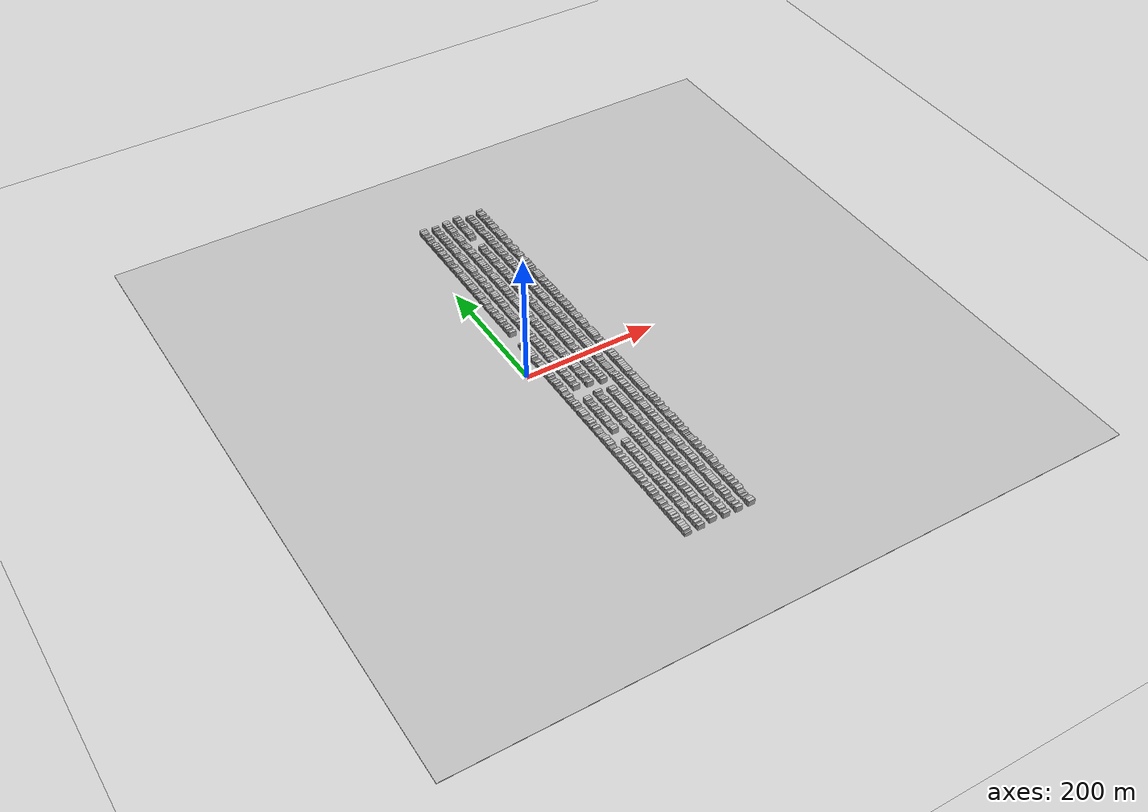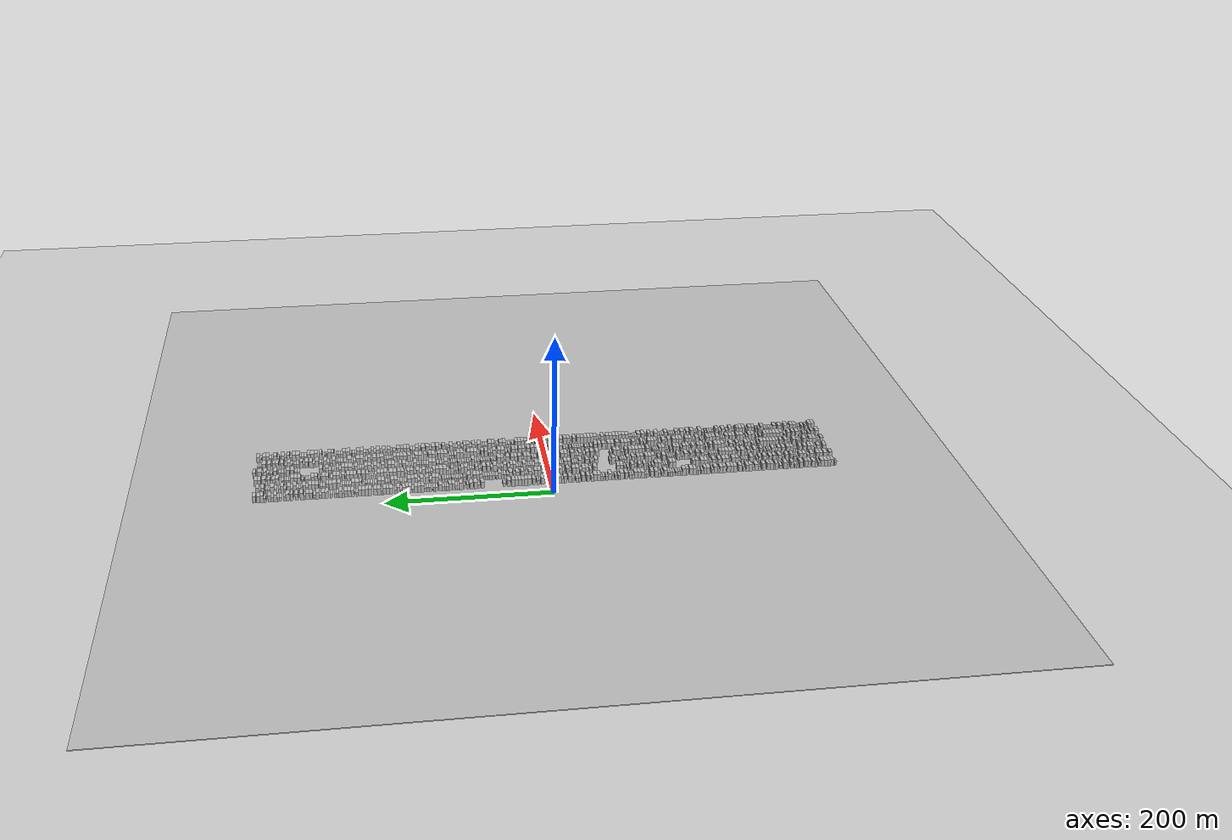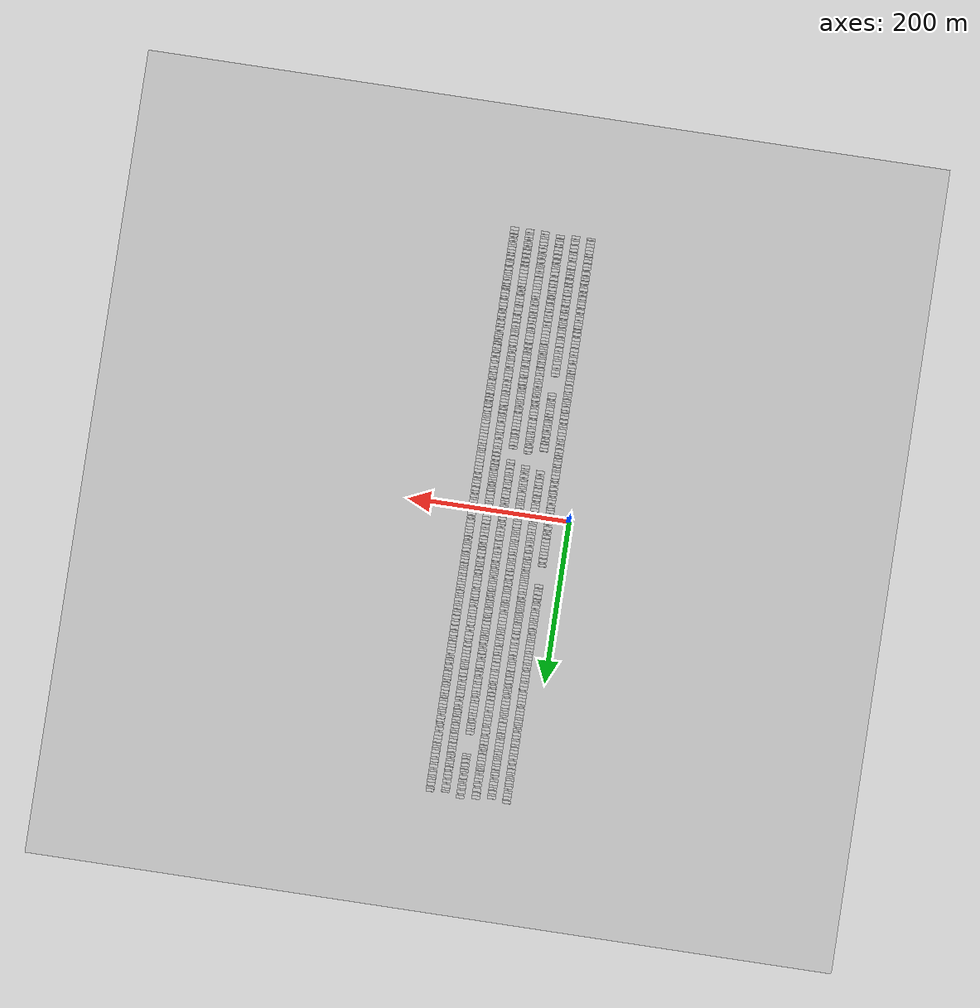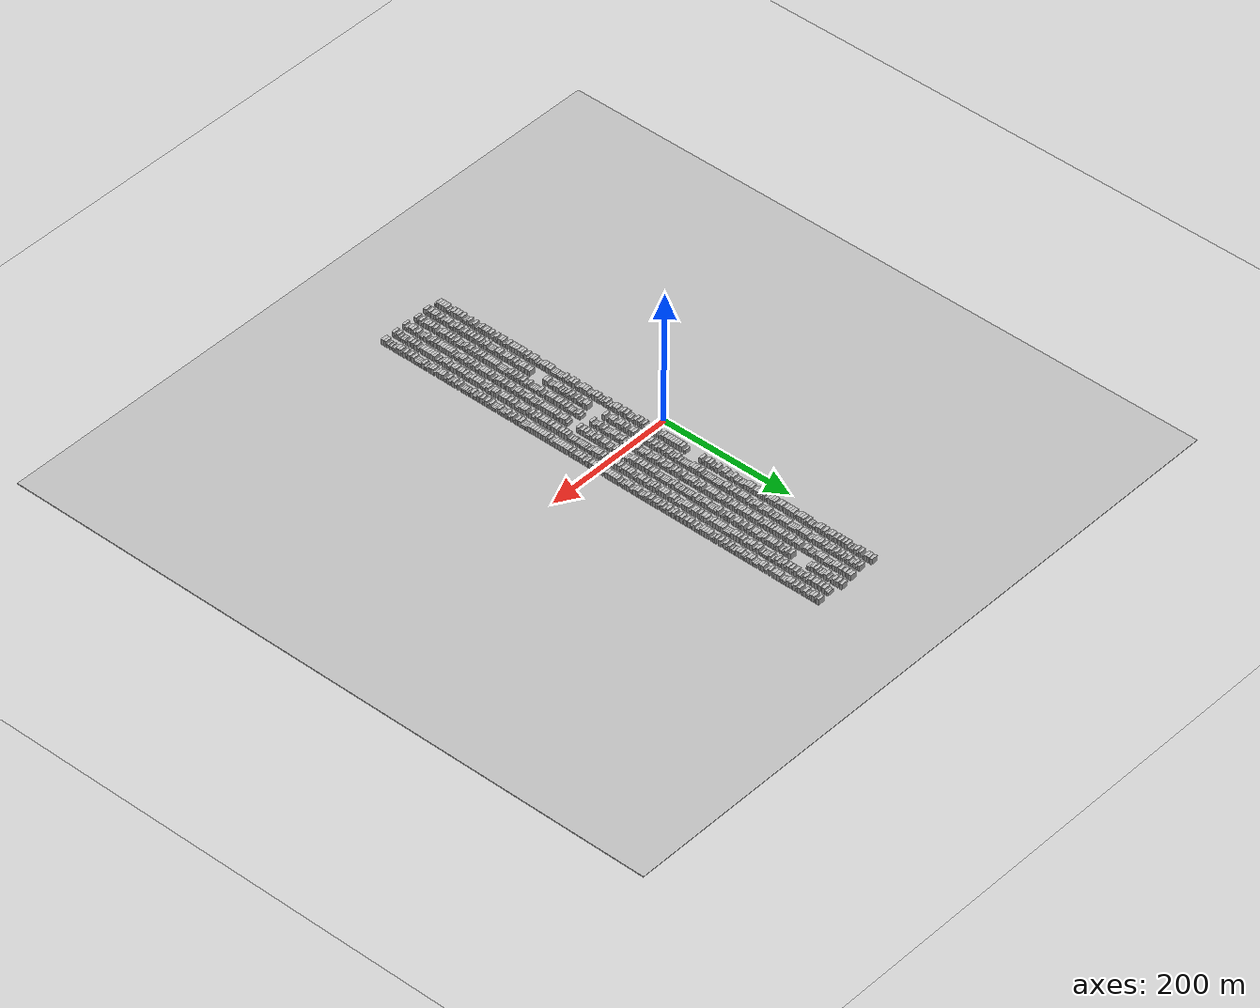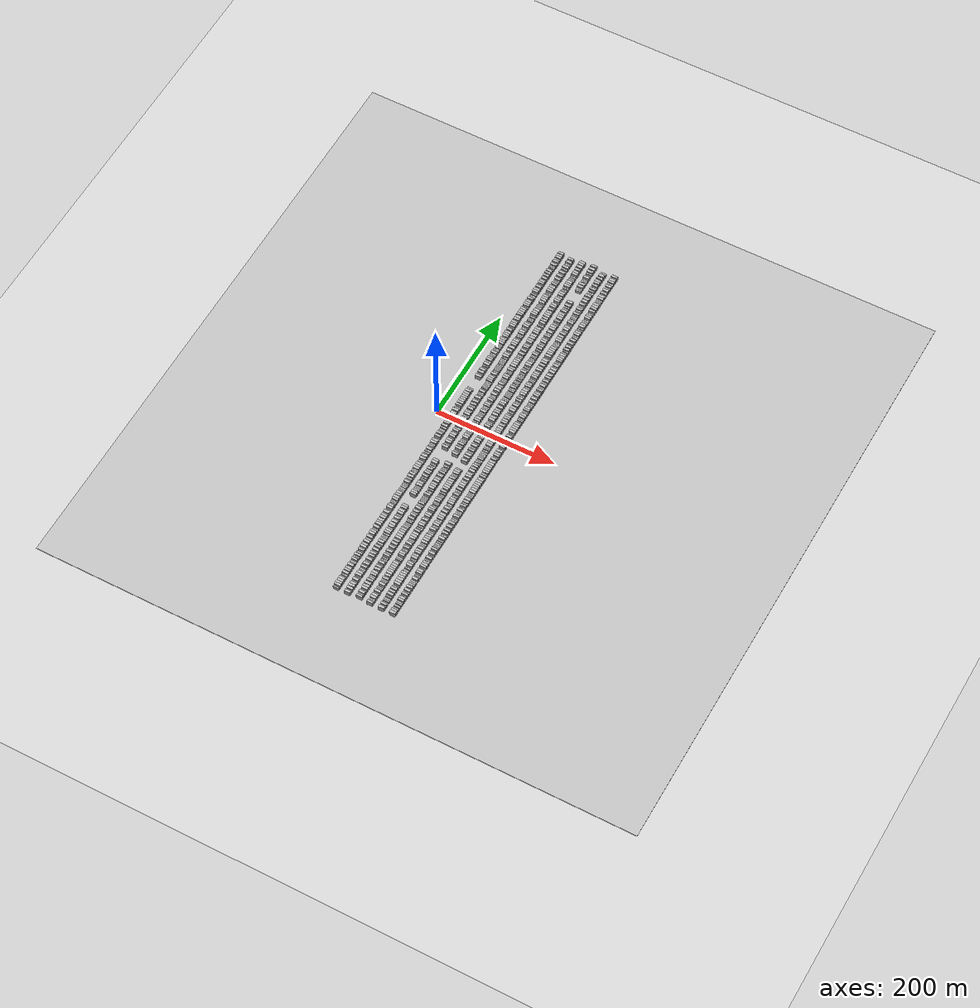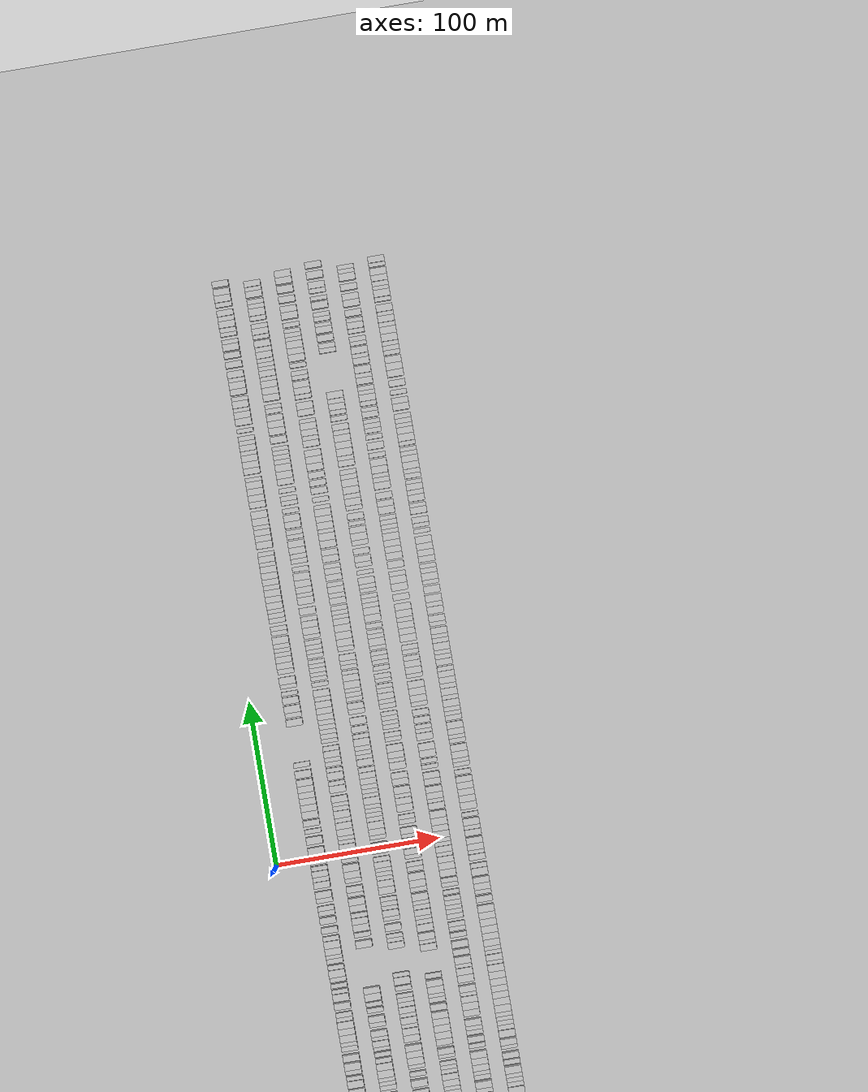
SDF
<?xml version="1.0" encoding="utf-8"?>

<sdf version="1.6">

   <world name="default">

      <gui fullscreen="0">

         <camera name="user_camera">

            <pose>-15 0 4.57585 0 0 0</pose>

            <view_controller>orbit</view_controller>

         </camera>

      </gui>

      <scene>

         <sky>

           <clouds>

             <speed>12</speed>

           </clouds>

         </sky>

         <ambient>0.4 0.4 0.4 1</ambient>

         <background>0.7 0.7 0.7 1</background>

         <shadows>1</shadows>

      </scene>

      <gravity>0 0 -9.8066</gravity>

      <magnetic_field>6e-06 2.3e-05 -4.2e-05</magnetic_field>

      <physics default="0" name="default_physics" type="ode">

         <ode>

            <solver>

               <type>quick</type>

               <iters>10</iters>

               <sor>1.0</sor>

               <use_dynamic_moi_rescaling>0</use_dynamic_moi_rescaling>

            </solver>

            <constraints>

               <cfm>0</cfm>

               <erp>0.2</erp>

               <contact_max_correcting_vel>100</contact_max_correcting_vel>

               <contact_surface_layer>0.001</contact_surface_layer>

            </constraints>

         </ode>

         <max_step_size>0.004</max_step_size>

         <real_time_factor>1</real_time_factor>

         <real_time_update_rate>250</real_time_update_rate>

      </physics>

      <light name="sun" type="directional">

         <cast_shadows>1</cast_shadows>

         <pose>0 0 10 0 0 0</pose>

         <diffuse>0.8 0.8 0.8 1</diffuse>

         <specular>0.2 0.2 0.2 1</specular>

         <attenuation>

            <range>1000</range>

            <constant>0.9</constant>

            <linear>0.01</linear>

            <quadratic>0.001</quadratic>

         </attenuation>

         <direction>-0.5 0.1 -0.9</direction>

      </light>

      <include>

         <name>ground_plane_1</name>

         <uri>model://HANNAS_ground_plane</uri>

         <pose>0 0 0  0 0 0</pose>

      </include>

      <include>

         <name>ground_plane_2</name>

         <uri>model://HANNAS_ground_plane</uri>

         <pose>100 0 0  0 0 0</pose>

      </include>

      <model name="building_1">

         <static>1</static>

         <pose frame="">25.0000 -348.7556 0 0.000000 0.000000 0.000000</pose>

         <link name="link">

            <pose frame="">0 0 3.00 0 0 0</pose>

            <collision name="collision">

               <geometry>

                  <box>

                     <size>10.0000 2.4888 6.0000</size>

                  </box>

               </geometry>

               <max_contacts>10</max_contacts>

               <surface>

                  <contact>

                     <ode/>

                  </contact>

                  <bounce/>

                  <friction>

                     <torsional>

                        <ode/>

                     </torsional>

                     <ode/>

                  </friction>

               </surface>

            </collision>

            <visual name="visual">

               <cast_shadows>0</cast_shadows>

               <geometry>

                  <box>

                     <size>10.0000 2.4888 6.0000</size>

                  </box>

               </geometry>

               <material>

                  <script>

                     <uri>model://HANNAS_wall/materials/scripts</uri>

                     <uri>model://HANNAS_wall/materials/textures</uri>

                     <name>vrc/HANNAS_wall</name>

                  </script>

               </material>

            </visual>

            <self_collide>0</self_collide>

            <enable_wind>0</enable_wind>

            <kinematic>0</kinematic>

         </link>

      </model>

      <model name="building_2">

         <static>1</static>

         <pose frame="">25.0000 -344.5438 0 0.000000 0.000000 0.000000</pose>

         <link name="link">

            <pose frame="">0 0 4.50 0 0 0</pose>

            <collision name="collision">

               <geometry>

                  <box>

                     <size>10.0000 3.9348 9.0000</size>

                  </box>

               </geometry>

               <max_contacts>10</max_contacts>

               <surface>

                  <contact>

                     <ode/>

                  </contact>

                  <bounce/>

                  <friction>

                     <torsional>

                        <ode/>

                     </torsional>

                     <ode/>

                  </friction>

               </surface>

            </collision>

            <visual name="visual">

               <cast_shadows>0</cast_shadows>

               <geometry>

                  <box>

                     <size>10.0000 3.9348 9.0000</size>

                  </box>

               </geometry>

               <material>

                  <script>

                     <uri>model://HANNAS_wall/materials/scripts</uri>

                     <uri>model://HANNAS_wall/materials/textures</uri>

                     <name>vrc/HANNAS_wall</name>

                  </script>

               </material>

            </visual>

            <self_collide>0</self_collide>

            <enable_wind>0</enable_wind>

            <kinematic>0</kinematic>

         </link>

      </model>

      <model name="building_3">

         <static>1</static>

         <pose frame="">25.0000 -340.6783 0 0.000000 0.000000 0.000000</pose>

         <link name="link">

            <pose frame="">0 0 4.50 0 0 0</pose>

            <collision name="collision">

               <geometry>

                  <box>

                     <size>10.0000 3.7962 9.0000</size>

                  </box>

               </geometry>

               <max_contacts>10</max_contacts>

               <surface>

                  <contact>

                     <ode/>

                  </contact>

                  <bounce/>

                  <friction>

                     <torsional>

                        <ode/>

                     </torsional>

                     <ode/>

                  </friction>

               </surface>

            </collision>

            <visual name="visual">

               <cast_shadows>0</cast_shadows>

               <geometry>

                  <box>

                     <size>10.0000 3.7962 9.0000</size>

                  </box>

               </geometry>

               <material>

                  <script>

                     <uri>model://HANNAS_wall/materials/scripts</uri>

                     <uri>model://HANNAS_wall/materials/textures</uri>

                     <name>vrc/HANNAS_wall</name>

                  </script>

               </material>

            </visual>

            <self_collide>0</self_collide>

            <enable_wind>0</enable_wind>

            <kinematic>0</kinematic>

         </link>

      </model>

      <model name="building_4">

         <static>1</static>

         <pose frame="">25.0000 -336.5885 0 0.000000 0.000000 0.000000</pose>

         <link name="link">

            <pose frame="">0 0 4.50 0 0 0</pose>

            <collision name="collision">

               <geometry>

                  <box>

                     <size>10.0000 4.3835 9.0000</size>

                  </box>

               </geometry>

               <max_contacts>10</max_contacts>

               <surface>

                  <contact>

                     <ode/>

                  </contact>

                  <bounce/>

                  <friction>

                     <torsional>

                        <ode/>

                     </torsional>

                     <ode/>

                  </friction>

               </surface>

            </collision>

            <visual name="visual">

               <cast_shadows>0</cast_shadows>

               <geometry>

                  <box>

                     <size>10.0000 4.3835 9.0000</size>

                  </box>

               </geometry>

               <material>

                  <script>

                     <uri>model://HANNAS_wall/materials/scripts</uri>

                     <uri>model://HANNAS_wall/materials/textures</uri>

                     <name>vrc/HANNAS_wall</name>

                  </script>

               </material>

            </visual>

            <self_collide>0</self_collide>

            <enable_wind>0</enable_wind>

            <kinematic>0</kinematic>

         </link>

      </model>

      <model name="building_5">

         <static>1</static>

         <pose frame="">25.0000 -332.1882 0 0.000000 0.000000 0.000000</pose>

         <link name="link">

            <pose frame="">0 0 4.50 0 0 0</pose>

            <collision name="collision">

               <geometry>

                  <box>

                     <size>10.0000 4.4172 9.0000</size>

                  </box>

               </geometry>

               <max_contacts>10</max_contacts>

               <surface>

                  <contact>

                     <ode/>

                  </contact>

                  <bounce/>

                  <friction>

                     <torsional>

                        <ode/>

                     </torsional>

                     <ode/>

                  </friction>

               </surface>

            </collision>

            <visual name="visual">

               <cast_shadows>0</cast_shadows>

               <geometry>

                  <box>

                     <size>10.0000 4.4172 9.0000</size>

                  </box>

               </geometry>

               <material>

                  <script>

                     <uri>model://HANNAS_wall/materials/scripts</uri>

                     <uri>model://HANNAS_wall/materials/textures</uri>

                     <name>vrc/HANNAS_wall</name>

                  </script>

               </material>

            </visual>

            <self_collide>0</self_collide>

            <enable_wind>0</enable_wind>

            <kinematic>0</kinematic>

         </link>

      </model>

      <model name="building_6">

         <static>1</static>

         <pose frame="">25.0000 -328.5649 0 0.000000 0.000000 0.000000</pose>

         <link name="link">

            <pose frame="">0 0 3.00 0 0 0</pose>

            <collision name="collision">

               <geometry>

                  <box>

                     <size>10.0000 2.8294 6.0000</size>

                  </box>

               </geometry>

               <max_contacts>10</max_contacts>

               <surface>

                  <contact>

                     <ode/>

                  </contact>

                  <bounce/>

                  <friction>

                     <torsional>

                        <ode/>

                     </torsional>

                     <ode/>

                  </friction>

               </surface>

            </collision>

            <visual name="visual">

               <cast_shadows>0</cast_shadows>

               <geometry>

                  <box>

                     <size>10.0000 2.8294 6.0000</size>

                  </box>

               </geometry>

               <material>

                  <script>

                     <uri>model://HANNAS_wall/materials/scripts</uri>

                     <uri>model://HANNAS_wall/materials/textures</uri>

                     <name>vrc/HANNAS_wall</name>

                  </script>

               </material>

            </visual>

            <self_collide>0</self_collide>

            <enable_wind>0</enable_wind>

            <kinematic>0</kinematic>

         </link>

      </model>

      <model name="building_7">

         <static>1</static>

         <pose frame="">25.0000 -324.7012 0 0.000000 0.000000 0.000000</pose>

         <link name="link">

            <pose frame="">0 0 3.00 0 0 0</pose>

            <collision name="collision">

               <geometry>

                  <box>

                     <size>10.0000 2.8978 6.0000</size>

                  </box>

               </geometry>

               <max_contacts>10</max_contacts>

               <surface>

                  <contact>

                     <ode/>

                  </contact>

                  <bounce/>

                  <friction>

                     <torsional>

                        <ode/>

                     </torsional>

                     <ode/>

                  </friction>

               </surface>

            </collision>

            <visual name="visual">

               <cast_shadows>0</cast_shadows>

               <geometry>

                  <box>

                     <size>10.0000 2.8978 6.0000</size>

                  </box>

               </geometry>

               <material>

                  <script>

                     <uri>model://HANNAS_wall/materials/scripts</uri>

                     <uri>model://HANNAS_wall/materials/textures</uri>

                     <name>vrc/HANNAS_wall</name>

                  </script>

               </material>

            </visual>

            <self_collide>0</self_collide>

            <enable_wind>0</enable_wind>

            <kinematic>0</kinematic>

         </link>

      </model>

      <model name="building_8">

         <static>1</static>

         <pose frame="">25.0000 -321.0993 0 0.000000 0.000000 0.000000</pose>

         <link name="link">

            <pose frame="">0 0 4.50 0 0 0</pose>

            <collision name="collision">

               <geometry>

                  <box>

                     <size>10.0000 4.3060 9.0000</size>

                  </box>

               </geometry>

               <max_contacts>10</max_contacts>

               <surface>

                  <contact>

                     <ode/>

                  </contact>

                  <bounce/>

                  <friction>

                     <torsional>

                        <ode/>

                     </torsional>

                     <ode/>

                  </friction>

               </surface>

            </collision>

            <visual name="visual">

               <cast_shadows>0</cast_shadows>

               <geometry>

                  <box>

                     <size>10.0000 4.3060 9.0000</size>

                  </box>

               </geometry>

               <material>

                  <script>

                     <uri>model://HANNAS_wall/materials/scripts</uri>

                     <uri>model://HANNAS_wall/materials/textures</uri>

                     <name>vrc/HANNAS_wall</name>

                  </script>

               </material>

            </visual>

            <self_collide>0</self_collide>

            <enable_wind>0</enable_wind>

            <kinematic>0</kinematic>

         </link>

      </model>

      <model name="building_9">

         <static>1</static>

         <pose frame="">25.0000 -315.9244 0 0.000000 0.000000 0.000000</pose>

         <link name="link">

            <pose frame="">0 0 4.50 0 0 0</pose>

            <collision name="collision">

               <geometry>

                  <box>

                     <size>10.0000 4.0438 9.0000</size>

                  </box>

               </geometry>

               <max_contacts>10</max_contacts>

               <surface>

                  <contact>

                     <ode/>

                  </contact>

                  <bounce/>

                  <friction>

                     <torsional>

                        <ode/>

                     </torsional>

                     <ode/>

                  </friction>

               </surface>

            </collision>

            <visual name="visual">

               <cast_shadows>0</cast_shadows>

               <geometry>

                  <box>

                     <size>10.0000 4.0438 9.0000</size>

                  </box>

               </geometry>

               <material>

                  <script>

                     <uri>model://HANNAS_wall/materials/scripts</uri>

                     <uri>model://HANNAS_wall/materials/textures</uri>

                     <name>vrc/HANNAS_wall</name>

                  </script>

               </material>

            </visual>

            <self_collide>0</self_collide>

            <enable_wind>0</enable_wind>

            <kinematic>0</kinematic>

         </link>

      </model>

      <model name="building_10">

         <static>1</static>

         <pose frame="">25.0000 -311.9721 0 0.000000 0.000000 0.000000</pose>

         <link name="link">

            <pose frame="">0 0 4.50 0 0 0</pose>

            <collision name="collision">

               <geometry>

                  <box>

                     <size>10.0000 3.8609 9.0000</size>

                  </box>

               </geometry>

               <max_contacts>10</max_contacts>

               <surface>

                  <contact>

                     <ode/>

                  </contact>

                  <bounce/>

                  <friction>

                     <torsional>

                        <ode/>

                     </torsional>

                     <ode/>

                  </friction>

               </surface>

            </collision>

            <visual name="visual">

               <cast_shadows>0</cast_shadows>

               <geometry>

                  <box>

                     <size>10.0000 3.8609 9.0000</size>

                  </box>

               </geometry>

               <material>

                  <script>

                     <uri>model://HANNAS_wall/materials/scripts</uri>

                     <uri>model://HANNAS_wall/materials/textures</uri>

                     <name>vrc/HANNAS_wall</name>

                  </script>

               </material>

            </visual>

            <self_collide>0</self_collide>

            <enable_wind>0</enable_wind>

            <kinematic>0</kinematic>

         </link>

      </model>

      <model name="building_11">

         <static>1</static>

         <pose frame="">25.0000 -305.8310 0 0.000000 0.000000 0.000000</pose>

         <link name="link">

            <pose frame="">0 0 4.50 0 0 0</pose>

            <collision name="collision">

               <geometry>

                  <box>

                     <size>10.0000 4.4213 9.0000</size>

                  </box>

               </geometry>

               <max_contacts>10</max_contacts>

               <surface>

                  <contact>

                     <ode/>

                  </contact>

                  <bounce/>

                  <friction>

                     <torsional>

                        <ode/>

                     </torsional>

                     <ode/>

                  </friction>

               </surface>

            </collision>

            <visual name="visual">

               <cast_shadows>0</cast_shadows>

               <geometry>

                  <box>

                     <size>10.0000 4.4213 9.0000</size>

                  </box>

               </geometry>

               <material>

                  <script>

                     <uri>model://HANNAS_wall/materials/scripts</uri>

                     <uri>model://HANNAS_wall/materials/textures</uri>

                     <name>vrc/HANNAS_wall</name>

                  </script>

               </material>

            </visual>

            <self_collide>0</self_collide>

            <enable_wind>0</enable_wind>

            <kinematic>0</kinematic>

         </link>

      </model>

      <model name="building_12">

         <static>1</static>

         <pose frame="">25.0000 -301.3705 0 0.000000 0.000000 0.000000</pose>

         <link name="link">

            <pose frame="">0 0 3.00 0 0 0</pose>

            <collision name="collision">

               <geometry>

                  <box>

                     <size>10.0000 2.4997 6.0000</size>

                  </box>

               </geometry>

               <max_contacts>10</max_contacts>

               <surface>

                  <contact>

                     <ode/>

                  </contact>

                  <bounce/>

                  <friction>

                     <torsional>

                        <ode/>

                     </torsional>

                     <ode/>

                  </friction>

               </surface>

            </collision>

            <visual name="visual">

               <cast_shadows>0</cast_shadows>

               <geometry>

                  <box>

                     <size>10.0000 2.4997 6.0000</size>

                  </box>

               </geometry>

               <material>

                  <script>

                     <uri>model://HANNAS_wall/materials/scripts</uri>

                     <uri>model://HANNAS_wall/materials/textures</uri>

                     <name>vrc/HANNAS_wall</name>

                  </script>

               </material>

            </visual>

            <self_collide>0</self_collide>

            <enable_wind>0</enable_wind>

            <kinematic>0</kinematic>

         </link>

      </model>

      <model name="building_13">

         <static>1</static>

         <pose frame="">25.0000 -298.6594 0 0.000000 0.000000 0.000000</pose>

         <link name="link">

            <pose frame="">0 0 3.00 0 0 0</pose>

            <collision name="collision">

               <geometry>

                  <box>

                     <size>10.0000 2.9223 6.0000</size>

                  </box>

               </geometry>

               <max_contacts>10</max_contacts>

               <surface>

                  <contact>

                     <ode/>

                  </contact>

                  <bounce/>

                  <friction>

                     <torsional>

                        <ode/>

                     </torsional>

                     <ode/>

                  </friction>

               </surface>

            </collision>

            <visual name="visual">

               <cast_shadows>0</cast_shadows>

               <geometry>

                  <box>

                     <size>10.0000 2.9223 6.0000</size>

                  </box>

               </geometry>

               <material>

                  <script>

                     <uri>model://HANNAS_wall/materials/scripts</uri>

                     <uri>model://HANNAS_wall/materials/textures</uri>

                     <name>vrc/HANNAS_wall</name>

                  </script>

               </material>

            </visual>

            <self_collide>0</self_collide>

            <enable_wind>0</enable_wind>

            <kinematic>0</kinematic>

         </link>

      </model>

      <model name="building_14">

         <static>1</static>

         <pose frame="">25.0000 -294.3800 0 0.000000 0.000000 0.000000</pose>

         <link name="link">

            <pose frame="">0 0 4.50 0 0 0</pose>

            <collision name="collision">

               <geometry>

                  <box>

                     <size>10.0000 3.6365 9.0000</size>

                  </box>

               </geometry>

               <max_contacts>10</max_contacts>

               <surface>

                  <contact>

                     <ode/>

                  </contact>

                  <bounce/>

                  <friction>

                     <torsional>

                        <ode/>

                     </torsional>

                     <ode/>

                  </friction>

               </surface>

            </collision>

            <visual name="visual">

               <cast_shadows>0</cast_shadows>

               <geometry>

                  <box>

                     <size>10.0000 3.6365 9.0000</size>

                  </box>

               </geometry>

               <material>

                  <script>

                     <uri>model://HANNAS_wall/materials/scripts</uri>

                     <uri>model://HANNAS_wall/materials/textures</uri>

                     <name>vrc/HANNAS_wall</name>

                  </script>

               </material>

            </visual>

            <self_collide>0</self_collide>

            <enable_wind>0</enable_wind>

            <kinematic>0</kinematic>

         </link>

      </model>

      <model name="building_15">

         <static>1</static>

         <pose frame="">25.0000 -289.1877 0 0.000000 0.000000 0.000000</pose>

         <link name="link">

            <pose frame="">0 0 3.00 0 0 0</pose>

            <collision name="collision">

               <geometry>

                  <box>

                     <size>10.0000 2.7483 6.0000</size>

                  </box>

               </geometry>

               <max_contacts>10</max_contacts>

               <surface>

                  <contact>

                     <ode/>

                  </contact>

                  <bounce/>

                  <friction>

                     <torsional>

                        <ode/>

                     </torsional>

                     <ode/>

                  </friction>

               </surface>

            </collision>

            <visual name="visual">

               <cast_shadows>0</cast_shadows>

               <geometry>

                  <box>

                     <size>10.0000 2.7483 6.0000</size>

                  </box>

               </geometry>

               <material>

                  <script>

                     <uri>model://HANNAS_wall/materials/scripts</uri>

                     <uri>model://HANNAS_wall/materials/textures</uri>

                     <name>vrc/HANNAS_wall</name>

                  </script>

               </material>

            </visual>

            <self_collide>0</self_collide>

            <enable_wind>0</enable_wind>

            <kinematic>0</kinematic>

         </link>

      </model>

      <model name="building_16">

         <static>1</static>

         <pose frame="">25.0000 -285.7804 0 0.000000 0.000000 0.000000</pose>

         <link name="link">

            <pose frame="">0 0 4.50 0 0 0</pose>

            <collision name="collision">

               <geometry>

                  <box>

                     <size>10.0000 4.0662 9.0000</size>

                  </box>

               </geometry>

               <max_contacts>10</max_contacts>

               <surface>

                  <contact>

                     <ode/>

                  </contact>

                  <bounce/>

                  <friction>

                     <torsional>

                        <ode/>

                     </torsional>

                     <ode/>

                  </friction>

               </surface>

            </collision>

            <visual name="visual">

               <cast_shadows>0</cast_shadows>

               <geometry>

                  <box>

                     <size>10.0000 4.0662 9.0000</size>

                  </box>

               </geometry>

               <material>

                  <script>

                     <uri>model://HANNAS_wall/materials/scripts</uri>

                     <uri>model://HANNAS_wall/materials/textures</uri>

                     <name>vrc/HANNAS_wall</name>

                  </script>

               </material>

            </visual>

            <self_collide>0</self_collide>

            <enable_wind>0</enable_wind>

            <kinematic>0</kinematic>

         </link>

      </model>

      <model name="building_17">

         <static>1</static>

         <pose frame="">25.0000 -280.2999 0 0.000000 0.000000 0.000000</pose>

         <link name="link">

            <pose frame="">0 0 3.00 0 0 0</pose>

            <collision name="collision">

               <geometry>

                  <box>

                     <size>10.0000 2.8947 6.0000</size>

                  </box>

               </geometry>

               <max_contacts>10</max_contacts>

               <surface>

                  <contact>

                     <ode/>

                  </contact>

                  <bounce/>

                  <friction>

                     <torsional>

                        <ode/>

                     </torsional>

                     <ode/>

                  </friction>

               </surface>

            </collision>

            <visual name="visual">

               <cast_shadows>0</cast_shadows>

               <geometry>

                  <box>

                     <size>10.0000 2.8947 6.0000</size>

                  </box>

               </geometry>

               <material>

                  <script>

                     <uri>model://HANNAS_wall/materials/scripts</uri>

                     <uri>model://HANNAS_wall/materials/textures</uri>

                     <name>vrc/HANNAS_wall</name>

                  </script>

               </material>

            </visual>

            <self_collide>0</self_collide>

            <enable_wind>0</enable_wind>

            <kinematic>0</kinematic>

         </link>

      </model>

      <model name="building_18">

         <static>1</static>

         <pose frame="">25.0000 -275.0192 0 0.000000 0.000000 0.000000</pose>

         <link name="link">

            <pose frame="">0 0 4.50 0 0 0</pose>

            <collision name="collision">

               <geometry>

                  <box>

                     <size>10.0000 3.6667 9.0000</size>

                  </box>

               </geometry>

               <max_contacts>10</max_contacts>

               <surface>

                  <contact>

                     <ode/>

                  </contact>

                  <bounce/>

                  <friction>

                     <torsional>

                        <ode/>

                     </torsional>

                     <ode/>

                  </friction>

               </surface>

            </collision>

            <visual name="visual">

               <cast_shadows>0</cast_shadows>

               <geometry>

                  <box>

                     <size>10.0000 3.6667 9.0000</size>

                  </box>

               </geometry>

               <material>

                  <script>

                     <uri>model://HANNAS_wall/materials/scripts</uri>

                     <uri>model://HANNAS_wall/materials/textures</uri>

                     <name>vrc/HANNAS_wall</name>

                  </script>

               </material>

            </visual>

            <self_collide>0</self_collide>

            <enable_wind>0</enable_wind>

            <kinematic>0</kinematic>

         </link>

      </model>

      <model name="building_19">

         <static>1</static>

         <pose frame="">25.0000 -271.9733 0 0.000000 0.000000 0.000000</pose>

         <link name="link">

            <pose frame="">0 0 3.00 0 0 0</pose>

            <collision name="collision">

               <geometry>

                  <box>

                     <size>10.0000 2.4252 6.0000</size>

                  </box>

               </geometry>

               <max_contacts>10</max_contacts>

               <surface>

                  <contact>

                     <ode/>

                  </contact>

                  <bounce/>

                  <friction>

                     <torsional>

                        <ode/>

                     </torsional>

                     <ode/>

                  </friction>

               </surface>

            </collision>

            <visual name="visual">

               <cast_shadows>0</cast_shadows>

               <geometry>

                  <box>

                     <size>10.0000 2.4252 6.0000</size>

                  </box>

               </geometry>

               <material>

                  <script>

                     <uri>model://HANNAS_wall/materials/scripts</uri>

                     <uri>model://HANNAS_wall/materials/textures</uri>

                     <name>vrc/HANNAS_wall</name>

                  </script>

               </material>

            </visual>

            <self_collide>0</self_collide>

            <enable_wind>0</enable_wind>

            <kinematic>0</kinematic>

         </link>

      </model>

      <model name="building_20">

         <static>1</static>

         <pose frame="">25.0000 -268.7436 0 0.000000 0.000000 0.000000</pose>

         <link name="link">

            <pose frame="">0 0 4.50 0 0 0</pose>

            <collision name="collision">

               <geometry>

                  <box>

                     <size>10.0000 4.0341 9.0000</size>

                  </box>

               </geometry>

               <max_contacts>10</max_contacts>

               <surface>

                  <contact>

                     <ode/>

                  </contact>

                  <bounce/>

                  <friction>

                     <torsional>

                        <ode/>

                     </torsional>

                     <ode/>

                  </friction>

               </surface>

            </collision>

            <visual name="visual">

               <cast_shadows>0</cast_shadows>

               <geometry>

                  <box>

                     <size>10.0000 4.0341 9.0000</size>

                  </box>

               </geometry>

               <material>

                  <script>

                     <uri>model://HANNAS_wall/materials/scripts</uri>

                     <uri>model://HANNAS_wall/materials/textures</uri>

                     <name>vrc/HANNAS_wall</name>

                  </script>

               </material>

            </visual>

            <self_collide>0</self_collide>

            <enable_wind>0</enable_wind>

            <kinematic>0</kinematic>

         </link>

      </model>

      <model name="building_21">

         <static>1</static>

         <pose frame="">25.0000 -264.9043 0 0.000000 0.000000 0.000000</pose>

         <link name="link">

            <pose frame="">0 0 4.50 0 0 0</pose>

            <collision name="collision">

               <geometry>

                  <box>

                     <size>10.0000 3.6446 9.0000</size>

                  </box>

               </geometry>

               <max_contacts>10</max_contacts>

               <surface>

                  <contact>

                     <ode/>

                  </contact>

                  <bounce/>

                  <friction>

                     <torsional>

                        <ode/>

                     </torsional>

                     <ode/>

                  </friction>

               </surface>

            </collision>

            <visual name="visual">

               <cast_shadows>0</cast_shadows>

               <geometry>

                  <box>

                     <size>10.0000 3.6446 9.0000</size>

                  </box>

               </geometry>

               <material>

                  <script>

                     <uri>model://HANNAS_wall/materials/scripts</uri>

                     <uri>model://HANNAS_wall/materials/textures</uri>

                     <name>vrc/HANNAS_wall</name>

                  </script>

               </material>

            </visual>

            <self_collide>0</self_collide>

            <enable_wind>0</enable_wind>

            <kinematic>0</kinematic>

         </link>

      </model>

      <model name="building_22">

         <static>1</static>

         <pose frame="">25.0000 -258.9772 0 0.000000 0.000000 0.000000</pose>

         <link name="link">

            <pose frame="">0 0 4.50 0 0 0</pose>

            <collision name="collision">

               <geometry>

                  <box>

                     <size>10.0000 4.2097 9.0000</size>

                  </box>

               </geometry>

               <max_contacts>10</max_contacts>

               <surface>

                  <contact>

                     <ode/>

                  </contact>

                  <bounce/>

                  <friction>

                     <torsional>

                        <ode/>

                     </torsional>

                     <ode/>

                  </friction>

               </surface>

            </collision>

            <visual name="visual">

               <cast_shadows>0</cast_shadows>

               <geometry>

                  <box>

                     <size>10.0000 4.2097 9.0000</size>

                  </box>

               </geometry>

               <material>

                  <script>

                     <uri>model://HANNAS_wall/materials/scripts</uri>

                     <uri>model://HANNAS_wall/materials/textures</uri>

                     <name>vrc/HANNAS_wall</name>

                  </script>

               </material>

            </visual>

            <self_collide>0</self_collide>

            <enable_wind>0</enable_wind>

            <kinematic>0</kinematic>

         </link>

      </model>

      <model name="building_23">

         <static>1</static>

         <pose frame="">25.0000 -253.3896 0 0.000000 0.000000 0.000000</pose>

         <link name="link">

            <pose frame="">0 0 3.00 0 0 0</pose>

            <collision name="collision">

               <geometry>

                  <box>

                     <size>10.0000 2.9653 6.0000</size>

                  </box>

               </geometry>

               <max_contacts>10</max_contacts>

               <surface>

                  <contact>

                     <ode/>

                  </contact>

                  <bounce/>

                  <friction>

                     <torsional>

                        <ode/>

                     </torsional>

                     <ode/>

                  </friction>

               </surface>

            </collision>

            <visual name="visual">

               <cast_shadows>0</cast_shadows>

               <geometry>

                  <box>

                     <size>10.0000 2.9653 6.0000</size>

                  </box>

               </geometry>

               <material>

                  <script>

                     <uri>model://HANNAS_wall/materials/scripts</uri>

                     <uri>model://HANNAS_wall/materials/textures</uri>

                     <name>vrc/HANNAS_wall</name>

                  </script>

               </material>

            </visual>

            <self_collide>0</self_collide>

            <enable_wind>0</enable_wind>

            <kinematic>0</kinematic>

         </link>

      </model>

      <model name="building_24">

         <static>1</static>

         <pose frame="">25.0000 -249.6999 0 0.000000 0.000000 0.000000</pose>

         <link name="link">

            <pose frame="">0 0 4.50 0 0 0</pose>

            <collision name="collision">

               <geometry>

                  <box>

                     <size>10.0000 4.4142 9.0000</size>

                  </box>

               </geometry>

               <max_contacts>10</max_contacts>

               <surface>

                  <contact>

                     <ode/>

                  </contact>

                  <bounce/>

                  <friction>

                     <torsional>

                        <ode/>

                     </torsional>

                     <ode/>

                  </friction>

               </surface>

            </collision>

            <visual name="visual">

               <cast_shadows>0</cast_shadows>

               <geometry>

                  <box>

                     <size>10.0000 4.4142 9.0000</size>

                  </box>

               </geometry>

               <material>

                  <script>

                     <uri>model://HANNAS_wall/materials/scripts</uri>

                     <uri>model://HANNAS_wall/materials/textures</uri>

                     <name>vrc/HANNAS_wall</name>

                  </script>

               </material>

            </visual>

            <self_collide>0</self_collide>

            <enable_wind>0</enable_wind>

            <kinematic>0</kinematic>

         </link>

      </model>

      <model name="building_25">

         <static>1</static>

         <pose frame="">25.0000 -246.0931 0 0.000000 0.000000 0.000000</pose>

         <link name="link">

            <pose frame="">0 0 3.00 0 0 0</pose>

            <collision name="collision">

               <geometry>

                  <box>

                     <size>10.0000 2.7993 6.0000</size>

                  </box>

               </geometry>

               <max_contacts>10</max_contacts>

               <surface>

                  <contact>

                     <ode/>

                  </contact>

                  <bounce/>

                  <friction>

                     <torsional>

                        <ode/>

                     </torsional>

                     <ode/>

                  </friction>

               </surface>

            </collision>

            <visual name="visual">

               <cast_shadows>0</cast_shadows>

               <geometry>

                  <box>

                     <size>10.0000 2.7993 6.0000</size>

                  </box>

               </geometry>

               <material>

                  <script>

                     <uri>model://HANNAS_wall/materials/scripts</uri>

                     <uri>model://HANNAS_wall/materials/textures</uri>

                     <name>vrc/HANNAS_wall</name>

                  </script>

               </material>

            </visual>

            <self_collide>0</self_collide>

            <enable_wind>0</enable_wind>

            <kinematic>0</kinematic>

         </link>

      </model>

      <model name="building_26">

         <static>1</static>

         <pose frame="">25.0000 -242.5474 0 0.000000 0.000000 0.000000</pose>

         <link name="link">

            <pose frame="">0 0 4.50 0 0 0</pose>

            <collision name="collision">

               <geometry>

                  <box>

                     <size>10.0000 4.2921 9.0000</size>

                  </box>

               </geometry>

               <max_contacts>10</max_contacts>

               <surface>

                  <contact>

                     <ode/>

                  </contact>

                  <bounce/>

                  <friction>

                     <torsional>

                        <ode/>

                     </torsional>

                     <ode/>

                  </friction>

               </surface>

            </collision>

            <visual name="visual">

               <cast_shadows>0</cast_shadows>

               <geometry>

                  <box>

                     <size>10.0000 4.2921 9.0000</size>

                  </box>

               </geometry>

               <material>

                  <script>

                     <uri>model://HANNAS_wall/materials/scripts</uri>

                     <uri>model://HANNAS_wall/materials/textures</uri>

                     <name>vrc/HANNAS_wall</name>

                  </script>

               </material>

            </visual>

            <self_collide>0</self_collide>

            <enable_wind>0</enable_wind>

            <kinematic>0</kinematic>

         </link>

      </model>

      <model name="building_27">

         <static>1</static>

         <pose frame="">25.0000 -238.5943 0 0.000000 0.000000 0.000000</pose>

         <link name="link">

            <pose frame="">0 0 4.50 0 0 0</pose>

            <collision name="collision">

               <geometry>

                  <box>

                     <size>10.0000 3.6142 9.0000</size>

                  </box>

               </geometry>

               <max_contacts>10</max_contacts>

               <surface>

                  <contact>

                     <ode/>

                  </contact>

                  <bounce/>

                  <friction>

                     <torsional>

                        <ode/>

                     </torsional>

                     <ode/>

                  </friction>

               </surface>

            </collision>

            <visual name="visual">

               <cast_shadows>0</cast_shadows>

               <geometry>

                  <box>

                     <size>10.0000 3.6142 9.0000</size>

                  </box>

               </geometry>

               <material>

                  <script>

                     <uri>model://HANNAS_wall/materials/scripts</uri>

                     <uri>model://HANNAS_wall/materials/textures</uri>

                     <name>vrc/HANNAS_wall</name>

                  </script>

               </material>

            </visual>

            <self_collide>0</self_collide>

            <enable_wind>0</enable_wind>

            <kinematic>0</kinematic>

         </link>

      </model>

      <model name="building_28">

         <static>1</static>

         <pose frame="">25.0000 -234.3465 0 0.000000 0.000000 0.000000</pose>

         <link name="link">

            <pose frame="">0 0 3.00 0 0 0</pose>

            <collision name="collision">

               <geometry>

                  <box>

                     <size>10.0000 2.8813 6.0000</size>

                  </box>

               </geometry>

               <max_contacts>10</max_contacts>

               <surface>

                  <contact>

                     <ode/>

                  </contact>

                  <bounce/>

                  <friction>

                     <torsional>

                        <ode/>

                     </torsional>

                     <ode/>

                  </friction>

               </surface>

            </collision>

            <visual name="visual">

               <cast_shadows>0</cast_shadows>

               <geometry>

                  <box>

                     <size>10.0000 2.8813 6.0000</size>

                  </box>

               </geometry>

               <material>

                  <script>

                     <uri>model://HANNAS_wall/materials/scripts</uri>

                     <uri>model://HANNAS_wall/materials/textures</uri>

                     <name>vrc/HANNAS_wall</name>

                  </script>

               </material>

            </visual>

            <self_collide>0</self_collide>

            <enable_wind>0</enable_wind>

            <kinematic>0</kinematic>

         </link>

      </model>

      <model name="building_29">

         <static>1</static>

         <pose frame="">25.0000 -229.7559 0 0.000000 0.000000 0.000000</pose>

         <link name="link">

            <pose frame="">0 0 4.50 0 0 0</pose>

            <collision name="collision">

               <geometry>

                  <box>

                     <size>10.0000 4.2998 9.0000</size>

                  </box>

               </geometry>

               <max_contacts>10</max_contacts>

               <surface>

                  <contact>

                     <ode/>

                  </contact>

                  <bounce/>

                  <friction>

                     <torsional>

                        <ode/>

                     </torsional>

                     <ode/>

                  </friction>

               </surface>

            </collision>

            <visual name="visual">

               <cast_shadows>0</cast_shadows>

               <geometry>

                  <box>

                     <size>10.0000 4.2998 9.0000</size>

                  </box>

               </geometry>

               <material>

                  <script>

                     <uri>model://HANNAS_wall/materials/scripts</uri>

                     <uri>model://HANNAS_wall/materials/textures</uri>

                     <name>vrc/HANNAS_wall</name>

                  </script>

               </material>

            </visual>

            <self_collide>0</self_collide>

            <enable_wind>0</enable_wind>

            <kinematic>0</kinematic>

         </link>

      </model>

      <model name="building_30">

         <static>1</static>

         <pose frame="">25.0000 -223.4997 0 0.000000 0.000000 0.000000</pose>

         <link name="link">

            <pose frame="">0 0 4.50 0 0 0</pose>

            <collision name="collision">

               <geometry>

                  <box>

                     <size>10.0000 4.2128 9.0000</size>

                  </box>

               </geometry>

               <max_contacts>10</max_contacts>

               <surface>

                  <contact>

                     <ode/>

                  </contact>

                  <bounce/>

                  <friction>

                     <torsional>

                        <ode/>

                     </torsional>

                     <ode/>

                  </friction>

               </surface>

            </collision>

            <visual name="visual">

               <cast_shadows>0</cast_shadows>

               <geometry>

                  <box>

                     <size>10.0000 4.2128 9.0000</size>

                  </box>

               </geometry>

               <material>

                  <script>

                     <uri>model://HANNAS_wall/materials/scripts</uri>

                     <uri>model://HANNAS_wall/materials/textures</uri>

                     <name>vrc/HANNAS_wall</name>

                  </script>

               </material>

            </visual>

            <self_collide>0</self_collide>

            <enable_wind>0</enable_wind>

            <kinematic>0</kinematic>

         </link>

      </model>

      <model name="building_31">

         <static>1</static>

         <pose frame="">25.0000 -219.5644 0 0.000000 0.000000 0.000000</pose>

         <link name="link">

            <pose frame="">0 0 4.50 0 0 0</pose>

            <collision name="collision">

               <geometry>

                  <box>

                     <size>10.0000 3.6578 9.0000</size>

                  </box>

               </geometry>

               <max_contacts>10</max_contacts>

               <surface>

                  <contact>

                     <ode/>

                  </contact>

                  <bounce/>

                  <friction>

                     <torsional>

                        <ode/>

                     </torsional>

                     <ode/>

                  </friction>

               </surface>

            </collision>

            <visual name="visual">

               <cast_shadows>0</cast_shadows>

               <geometry>

                  <box>

                     <size>10.0000 3.6578 9.0000</size>

                  </box>

               </geometry>

               <material>

                  <script>

                     <uri>model://HANNAS_wall/materials/scripts</uri>

                     <uri>model://HANNAS_wall/materials/textures</uri>

                     <name>vrc/HANNAS_wall</name>

                  </script>

               </material>

            </visual>

            <self_collide>0</self_collide>

            <enable_wind>0</enable_wind>

            <kinematic>0</kinematic>

         </link>

      </model>

      <model name="building_32">

         <static>1</static>

         <pose frame="">25.0000 -215.5783 0 0.000000 0.000000 0.000000</pose>

         <link name="link">

            <pose frame="">0 0 4.50 0 0 0</pose>

            <collision name="collision">

               <geometry>

                  <box>

                     <size>10.0000 4.3143 9.0000</size>

                  </box>

               </geometry>

               <max_contacts>10</max_contacts>

               <surface>

                  <contact>

                     <ode/>

                  </contact>

                  <bounce/>

                  <friction>

                     <torsional>

                        <ode/>

                     </torsional>

                     <ode/>

                  </friction>

               </surface>

            </collision>

            <visual name="visual">

               <cast_shadows>0</cast_shadows>

               <geometry>

                  <box>

                     <size>10.0000 4.3143 9.0000</size>

                  </box>

               </geometry>

               <material>

                  <script>

                     <uri>model://HANNAS_wall/materials/scripts</uri>

                     <uri>model://HANNAS_wall/materials/textures</uri>

                     <name>vrc/HANNAS_wall</name>

                  </script>

               </material>

            </visual>

            <self_collide>0</self_collide>

            <enable_wind>0</enable_wind>

            <kinematic>0</kinematic>

         </link>

      </model>

      <model name="building_33">

         <static>1</static>

         <pose frame="">25.0000 -210.2812 0 0.000000 0.000000 0.000000</pose>

         <link name="link">

            <pose frame="">0 0 4.50 0 0 0</pose>

            <collision name="collision">

               <geometry>

                  <box>

                     <size>10.0000 4.2799 9.0000</size>

                  </box>

               </geometry>

               <max_contacts>10</max_contacts>

               <surface>

                  <contact>

                     <ode/>

                  </contact>

                  <bounce/>

                  <friction>

                     <torsional>

                        <ode/>

                     </torsional>

                     <ode/>

                  </friction>

               </surface>

            </collision>

            <visual name="visual">

               <cast_shadows>0</cast_shadows>

               <geometry>

                  <box>

                     <size>10.0000 4.2799 9.0000</size>

                  </box>

               </geometry>

               <material>

                  <script>

                     <uri>model://HANNAS_wall/materials/scripts</uri>

                     <uri>model://HANNAS_wall/materials/textures</uri>

                     <name>vrc/HANNAS_wall</name>

                  </script>

               </material>

            </visual>

            <self_collide>0</self_collide>

            <enable_wind>0</enable_wind>

            <kinematic>0</kinematic>

         </link>

      </model>

      <model name="building_34">

         <static>1</static>

         <pose frame="">25.0000 -206.1762 0 0.000000 0.000000 0.000000</pose>

         <link name="link">

            <pose frame="">0 0 4.50 0 0 0</pose>

            <collision name="collision">

               <geometry>

                  <box>

                     <size>10.0000 3.9302 9.0000</size>

                  </box>

               </geometry>

               <max_contacts>10</max_contacts>

               <surface>

                  <contact>

                     <ode/>

                  </contact>

                  <bounce/>

                  <friction>

                     <torsional>

                        <ode/>

                     </torsional>

                     <ode/>

                  </friction>

               </surface>

            </collision>

            <visual name="visual">

               <cast_shadows>0</cast_shadows>

               <geometry>

                  <box>

                     <size>10.0000 3.9302 9.0000</size>

                  </box>

               </geometry>

               <material>

                  <script>

                     <uri>model://HANNAS_wall/materials/scripts</uri>

                     <uri>model://HANNAS_wall/materials/textures</uri>

                     <name>vrc/HANNAS_wall</name>

                  </script>

               </material>

            </visual>

            <self_collide>0</self_collide>

            <enable_wind>0</enable_wind>

            <kinematic>0</kinematic>

         </link>

      </model>

      <model name="building_35">

         <static>1</static>

         <pose frame="">25.0000 -202.8672 0 0.000000 0.000000 0.000000</pose>

         <link name="link">

            <pose frame="">0 0 3.00 0 0 0</pose>

            <collision name="collision">

               <geometry>

                  <box>

                     <size>10.0000 2.6878 6.0000</size>

                  </box>

               </geometry>

               <max_contacts>10</max_contacts>

               <surface>

                  <contact>

                     <ode/>

                  </contact>

                  <bounce/>

                  <friction>

                     <torsional>

                        <ode/>

                     </torsional>

                     <ode/>

                  </friction>

               </surface>

            </collision>

            <visual name="visual">

               <cast_shadows>0</cast_shadows>

               <geometry>

                  <box>

                     <size>10.0000 2.6878 6.0000</size>

                  </box>

               </geometry>

               <material>

                  <script>

                     <uri>model://HANNAS_wall/materials/scripts</uri>

                     <uri>model://HANNAS_wall/materials/textures</uri>

                     <name>vrc/HANNAS_wall</name>

                  </script>

               </material>

            </visual>

            <self_collide>0</self_collide>

            <enable_wind>0</enable_wind>

            <kinematic>0</kinematic>

         </link>

      </model>

      <model name="building_36">

         <static>1</static>

         <pose frame="">25.0000 -199.2933 0 0.000000 0.000000 0.000000</pose>

         <link name="link">

            <pose frame="">0 0 4.50 0 0 0</pose>

            <collision name="collision">

               <geometry>

                  <box>

                     <size>10.0000 4.4602 9.0000</size>

                  </box>

               </geometry>

               <max_contacts>10</max_contacts>

               <surface>

                  <contact>

                     <ode/>

                  </contact>

                  <bounce/>

                  <friction>

                     <torsional>

                        <ode/>

                     </torsional>

                     <ode/>

                  </friction>

               </surface>

            </collision>

            <visual name="visual">

               <cast_shadows>0</cast_shadows>

               <geometry>

                  <box>

                     <size>10.0000 4.4602 9.0000</size>

                  </box>

               </geometry>

               <material>

                  <script>

                     <uri>model://HANNAS_wall/materials/scripts</uri>

                     <uri>model://HANNAS_wall/materials/textures</uri>

                     <name>vrc/HANNAS_wall</name>

                  </script>

               </material>

            </visual>

            <self_collide>0</self_collide>

            <enable_wind>0</enable_wind>

            <kinematic>0</kinematic>

         </link>

      </model>

      <model name="building_37">

         <static>1</static>

         <pose frame="">25.0000 -195.6696 0 0.000000 0.000000 0.000000</pose>

         <link name="link">

            <pose frame="">0 0 3.00 0 0 0</pose>

            <collision name="collision">

               <geometry>

                  <box>

                     <size>10.0000 2.7871 6.0000</size>

                  </box>

               </geometry>

               <max_contacts>10</max_contacts>

               <surface>

                  <contact>

                     <ode/>

                  </contact>

                  <bounce/>

                  <friction>

                     <torsional>

                        <ode/>

                     </torsional>

                     <ode/>

                  </friction>

               </surface>

            </collision>

            <visual name="visual">

               <cast_shadows>0</cast_shadows>

               <geometry>

                  <box>

                     <size>10.0000 2.7871 6.0000</size>

                  </box>

               </geometry>

               <material>

                  <script>

                     <uri>model://HANNAS_wall/materials/scripts</uri>

                     <uri>model://HANNAS_wall/materials/textures</uri>

                     <name>vrc/HANNAS_wall</name>

                  </script>

               </material>

            </visual>

            <self_collide>0</self_collide>

            <enable_wind>0</enable_wind>

            <kinematic>0</kinematic>

         </link>

      </model>

      <model name="building_38">

         <static>1</static>

         <pose frame="">25.0000 -190.1585 0 0.000000 0.000000 0.000000</pose>

         <link name="link">

            <pose frame="">0 0 4.50 0 0 0</pose>

            <collision name="collision">

               <geometry>

                  <box>

                     <size>10.0000 4.2351 9.0000</size>

                  </box>

               </geometry>

               <max_contacts>10</max_contacts>

               <surface>

                  <contact>

                     <ode/>

                  </contact>

                  <bounce/>

                  <friction>

                     <torsional>

                        <ode/>

                     </torsional>

                     <ode/>

                  </friction>

               </surface>

            </collision>

            <visual name="visual">

               <cast_shadows>0</cast_shadows>

               <geometry>

                  <box>

                     <size>10.0000 4.2351 9.0000</size>

                  </box>

               </geometry>

               <material>

                  <script>

                     <uri>model://HANNAS_wall/materials/scripts</uri>

                     <uri>model://HANNAS_wall/materials/textures</uri>

                     <name>vrc/HANNAS_wall</name>

                  </script>

               </material>

            </visual>

            <self_collide>0</self_collide>

            <enable_wind>0</enable_wind>

            <kinematic>0</kinematic>

         </link>

      </model>

      <model name="building_39">

         <static>1</static>

         <pose frame="">25.0000 -186.2108 0 0.000000 0.000000 0.000000</pose>

         <link name="link">

            <pose frame="">0 0 4.50 0 0 0</pose>

            <collision name="collision">

               <geometry>

                  <box>

                     <size>10.0000 3.6603 9.0000</size>

                  </box>

               </geometry>

               <max_contacts>10</max_contacts>

               <surface>

                  <contact>

                     <ode/>

                  </contact>

                  <bounce/>

                  <friction>

                     <torsional>

                        <ode/>

                     </torsional>

                     <ode/>

                  </friction>

               </surface>

            </collision>

            <visual name="visual">

               <cast_shadows>0</cast_shadows>

               <geometry>

                  <box>

                     <size>10.0000 3.6603 9.0000</size>

                  </box>

               </geometry>

               <material>

                  <script>

                     <uri>model://HANNAS_wall/materials/scripts</uri>

                     <uri>model://HANNAS_wall/materials/textures</uri>

                     <name>vrc/HANNAS_wall</name>

                  </script>

               </material>

            </visual>

            <self_collide>0</self_collide>

            <enable_wind>0</enable_wind>

            <kinematic>0</kinematic>

         </link>

      </model>

      <model name="building_40">

         <static>1</static>

         <pose frame="">25.0000 -182.9294 0 0.000000 0.000000 0.000000</pose>

         <link name="link">

            <pose frame="">0 0 3.00 0 0 0</pose>

            <collision name="collision">

               <geometry>

                  <box>

                     <size>10.0000 2.9024 6.0000</size>

                  </box>

               </geometry>

               <max_contacts>10</max_contacts>

               <surface>

                  <contact>

                     <ode/>

                  </contact>

                  <bounce/>

                  <friction>

                     <torsional>

                        <ode/>

                     </torsional>

                     <ode/>

                  </friction>

               </surface>

            </collision>

            <visual name="visual">

               <cast_shadows>0</cast_shadows>

               <geometry>

                  <box>

                     <size>10.0000 2.9024 6.0000</size>

                  </box>

               </geometry>

               <material>

                  <script>

                     <uri>model://HANNAS_wall/materials/scripts</uri>

                     <uri>model://HANNAS_wall/materials/textures</uri>

                     <name>vrc/HANNAS_wall</name>

                  </script>

               </material>

            </visual>

            <self_collide>0</self_collide>

            <enable_wind>0</enable_wind>

            <kinematic>0</kinematic>

         </link>

      </model>

      <model name="building_41">

         <static>1</static>

         <pose frame="">25.0000 -179.1483 0 0.000000 0.000000 0.000000</pose>

         <link name="link">

            <pose frame="">0 0 3.00 0 0 0</pose>

            <collision name="collision">

               <geometry>

                  <box>

                     <size>10.0000 2.6597 6.0000</size>

                  </box>

               </geometry>

               <max_contacts>10</max_contacts>

               <surface>

                  <contact>

                     <ode/>

                  </contact>

                  <bounce/>

                  <friction>

                     <torsional>

                        <ode/>

                     </torsional>

                     <ode/>

                  </friction>

               </surface>

            </collision>

            <visual name="visual">

               <cast_shadows>0</cast_shadows>

               <geometry>

                  <box>

                     <size>10.0000 2.6597 6.0000</size>

                  </box>

               </geometry>

               <material>

                  <script>

                     <uri>model://HANNAS_wall/materials/scripts</uri>

                     <uri>model://HANNAS_wall/materials/textures</uri>

                     <name>vrc/HANNAS_wall</name>

                  </script>

               </material>

            </visual>

            <self_collide>0</self_collide>

            <enable_wind>0</enable_wind>

            <kinematic>0</kinematic>

         </link>

      </model>

      <model name="building_42">

         <static>1</static>

         <pose frame="">25.0000 -176.5922 0 0.000000 0.000000 0.000000</pose>

         <link name="link">

            <pose frame="">0 0 3.00 0 0 0</pose>

            <collision name="collision">

               <geometry>

                  <box>

                     <size>10.0000 2.4525 6.0000</size>

                  </box>

               </geometry>

               <max_contacts>10</max_contacts>

               <surface>

                  <contact>

                     <ode/>

                  </contact>

                  <bounce/>

                  <friction>

                     <torsional>

                        <ode/>

                     </torsional>

                     <ode/>

                  </friction>

               </surface>

            </collision>

            <visual name="visual">

               <cast_shadows>0</cast_shadows>

               <geometry>

                  <box>

                     <size>10.0000 2.4525 6.0000</size>

                  </box>

               </geometry>

               <material>

                  <script>

                     <uri>model://HANNAS_wall/materials/scripts</uri>

                     <uri>model://HANNAS_wall/materials/textures</uri>

                     <name>vrc/HANNAS_wall</name>

                  </script>

               </material>

            </visual>

            <self_collide>0</self_collide>

            <enable_wind>0</enable_wind>

            <kinematic>0</kinematic>

         </link>

      </model>

      <model name="building_43">

         <static>1</static>

         <pose frame="">25.0000 -173.4291 0 0.000000 0.000000 0.000000</pose>

         <link name="link">

            <pose frame="">0 0 4.50 0 0 0</pose>

            <collision name="collision">

               <geometry>

                  <box>

                     <size>10.0000 3.8737 9.0000</size>

                  </box>

               </geometry>

               <max_contacts>10</max_contacts>

               <surface>

                  <contact>

                     <ode/>

                  </contact>

                  <bounce/>

                  <friction>

                     <torsional>

                        <ode/>

                     </torsional>

                     <ode/>

                  </friction>

               </surface>

            </collision>

            <visual name="visual">

               <cast_shadows>0</cast_shadows>

               <geometry>

                  <box>

                     <size>10.0000 3.8737 9.0000</size>

                  </box>

               </geometry>

               <material>

                  <script>

                     <uri>model://HANNAS_wall/materials/scripts</uri>

                     <uri>model://HANNAS_wall/materials/textures</uri>

                     <name>vrc/HANNAS_wall</name>

                  </script>

               </material>

            </visual>

            <self_collide>0</self_collide>

            <enable_wind>0</enable_wind>

            <kinematic>0</kinematic>

         </link>

      </model>

      <model name="building_44">

         <static>1</static>

         <pose frame="">25.0000 -169.3907 0 0.000000 0.000000 0.000000</pose>

         <link name="link">

            <pose frame="">0 0 4.50 0 0 0</pose>

            <collision name="collision">

               <geometry>

                  <box>

                     <size>10.0000 4.2030 9.0000</size>

                  </box>

               </geometry>

               <max_contacts>10</max_contacts>

               <surface>

                  <contact>

                     <ode/>

                  </contact>

                  <bounce/>

                  <friction>

                     <torsional>

                        <ode/>

                     </torsional>

                     <ode/>

                  </friction>

               </surface>

            </collision>

            <visual name="visual">

               <cast_shadows>0</cast_shadows>

               <geometry>

                  <box>

                     <size>10.0000 4.2030 9.0000</size>

                  </box>

               </geometry>

               <material>

                  <script>

                     <uri>model://HANNAS_wall/materials/scripts</uri>

                     <uri>model://HANNAS_wall/materials/textures</uri>

                     <name>vrc/HANNAS_wall</name>

                  </script>

               </material>

            </visual>

            <self_collide>0</self_collide>

            <enable_wind>0</enable_wind>

            <kinematic>0</kinematic>

         </link>

      </model>

      <model name="building_45">

         <static>1</static>

         <pose frame="">25.0000 -164.4066 0 0.000000 0.000000 0.000000</pose>

         <link name="link">

            <pose frame="">0 0 4.50 0 0 0</pose>

            <collision name="collision">

               <geometry>

                  <box>

                     <size>10.0000 3.7653 9.0000</size>

                  </box>

               </geometry>

               <max_contacts>10</max_contacts>

               <surface>

                  <contact>

                     <ode/>

                  </contact>

                  <bounce/>

                  <friction>

                     <torsional>

                        <ode/>

                     </torsional>

                     <ode/>

                  </friction>

               </surface>

            </collision>

            <visual name="visual">

               <cast_shadows>0</cast_shadows>

               <geometry>

                  <box>

                     <size>10.0000 3.7653 9.0000</size>

                  </box>

               </geometry>

               <material>

                  <script>

                     <uri>model://HANNAS_wall/materials/scripts</uri>

                     <uri>model://HANNAS_wall/materials/textures</uri>

                     <name>vrc/HANNAS_wall</name>

                  </script>

               </material>

            </visual>

            <self_collide>0</self_collide>

            <enable_wind>0</enable_wind>

            <kinematic>0</kinematic>

         </link>

      </model>

      <model name="building_46">

         <static>1</static>

         <pose frame="">25.0000 -160.3309 0 0.000000 0.000000 0.000000</pose>

         <link name="link">

            <pose frame="">0 0 4.50 0 0 0</pose>

            <collision name="collision">

               <geometry>

                  <box>

                     <size>10.0000 4.3860 9.0000</size>

                  </box>

               </geometry>

               <max_contacts>10</max_contacts>

               <surface>

                  <contact>

                     <ode/>

                  </contact>

                  <bounce/>

                  <friction>

                     <torsional>

                        <ode/>

                     </torsional>

                     <ode/>

                  </friction>

               </surface>

            </collision>

            <visual name="visual">

               <cast_shadows>0</cast_shadows>

               <geometry>

                  <box>

                     <size>10.0000 4.3860 9.0000</size>

                  </box>

               </geometry>

               <material>

                  <script>

                     <uri>model://HANNAS_wall/materials/scripts</uri>

                     <uri>model://HANNAS_wall/materials/textures</uri>

                     <name>vrc/HANNAS_wall</name>

                  </script>

               </material>

            </visual>

            <self_collide>0</self_collide>

            <enable_wind>0</enable_wind>

            <kinematic>0</kinematic>

         </link>

      </model>

      <model name="building_47">

         <static>1</static>

         <pose frame="">25.0000 -156.8143 0 0.000000 0.000000 0.000000</pose>

         <link name="link">

            <pose frame="">0 0 3.00 0 0 0</pose>

            <collision name="collision">

               <geometry>

                  <box>

                     <size>10.0000 2.6471 6.0000</size>

                  </box>

               </geometry>

               <max_contacts>10</max_contacts>

               <surface>

                  <contact>

                     <ode/>

                  </contact>

                  <bounce/>

                  <friction>

                     <torsional>

                        <ode/>

                     </torsional>

                     <ode/>

                  </friction>

               </surface>

            </collision>

            <visual name="visual">

               <cast_shadows>0</cast_shadows>

               <geometry>

                  <box>

                     <size>10.0000 2.6471 6.0000</size>

                  </box>

               </geometry>

               <material>

                  <script>

                     <uri>model://HANNAS_wall/materials/scripts</uri>

                     <uri>model://HANNAS_wall/materials/textures</uri>

                     <name>vrc/HANNAS_wall</name>

                  </script>

               </material>

            </visual>

            <self_collide>0</self_collide>

            <enable_wind>0</enable_wind>

            <kinematic>0</kinematic>

         </link>

      </model>

      <model name="building_48">

         <static>1</static>

         <pose frame="">25.0000 -154.0976 0 0.000000 0.000000 0.000000</pose>

         <link name="link">

            <pose frame="">0 0 3.00 0 0 0</pose>

            <collision name="collision">

               <geometry>

                  <box>

                     <size>10.0000 2.7864 6.0000</size>

                  </box>

               </geometry>

               <max_contacts>10</max_contacts>

               <surface>

                  <contact>

                     <ode/>

                  </contact>

                  <bounce/>

                  <friction>

                     <torsional>

                        <ode/>

                     </torsional>

                     <ode/>

                  </friction>

               </surface>

            </collision>

            <visual name="visual">

               <cast_shadows>0</cast_shadows>

               <geometry>

                  <box>

                     <size>10.0000 2.7864 6.0000</size>

                  </box>

               </geometry>

               <material>

                  <script>

                     <uri>model://HANNAS_wall/materials/scripts</uri>

                     <uri>model://HANNAS_wall/materials/textures</uri>

                     <name>vrc/HANNAS_wall</name>

                  </script>

               </material>

            </visual>

            <self_collide>0</self_collide>

            <enable_wind>0</enable_wind>

            <kinematic>0</kinematic>

         </link>

      </model>

      <model name="building_49">

         <static>1</static>

         <pose frame="">25.0000 -151.2624 0 0.000000 0.000000 0.000000</pose>

         <link name="link">

            <pose frame="">0 0 3.00 0 0 0</pose>

            <collision name="collision">

               <geometry>

                  <box>

                     <size>10.0000 2.8840 6.0000</size>

                  </box>

               </geometry>

               <max_contacts>10</max_contacts>

               <surface>

                  <contact>

                     <ode/>

                  </contact>

                  <bounce/>

                  <friction>

                     <torsional>

                        <ode/>

                     </torsional>

                     <ode/>

                  </friction>

               </surface>

            </collision>

            <visual name="visual">

               <cast_shadows>0</cast_shadows>

               <geometry>

                  <box>

                     <size>10.0000 2.8840 6.0000</size>

                  </box>

               </geometry>

               <material>

                  <script>

                     <uri>model://HANNAS_wall/materials/scripts</uri>

                     <uri>model://HANNAS_wall/materials/textures</uri>

                     <name>vrc/HANNAS_wall</name>

                  </script>

               </material>

            </visual>

            <self_collide>0</self_collide>

            <enable_wind>0</enable_wind>

            <kinematic>0</kinematic>

         </link>

      </model>

      <model name="building_50">

         <static>1</static>

         <pose frame="">25.0000 -147.4396 0 0.000000 0.000000 0.000000</pose>

         <link name="link">

            <pose frame="">0 0 3.00 0 0 0</pose>

            <collision name="collision">

               <geometry>

                  <box>

                     <size>10.0000 2.7616 6.0000</size>

                  </box>

               </geometry>

               <max_contacts>10</max_contacts>

               <surface>

                  <contact>

                     <ode/>

                  </contact>

                  <bounce/>

                  <friction>

                     <torsional>

                        <ode/>

                     </torsional>

                     <ode/>

                  </friction>

               </surface>

            </collision>

            <visual name="visual">

               <cast_shadows>0</cast_shadows>

               <geometry>

                  <box>

                     <size>10.0000 2.7616 6.0000</size>

                  </box>

               </geometry>

               <material>

                  <script>

                     <uri>model://HANNAS_wall/materials/scripts</uri>

                     <uri>model://HANNAS_wall/materials/textures</uri>

                     <name>vrc/HANNAS_wall</name>

                  </script>

               </material>

            </visual>

            <self_collide>0</self_collide>

            <enable_wind>0</enable_wind>

            <kinematic>0</kinematic>

         </link>

      </model>

      <model name="building_51">

         <static>1</static>

         <pose frame="">25.0000 -144.7101 0 0.000000 0.000000 0.000000</pose>

         <link name="link">

            <pose frame="">0 0 3.00 0 0 0</pose>

            <collision name="collision">

               <geometry>

                  <box>

                     <size>10.0000 2.6974 6.0000</size>

                  </box>

               </geometry>

               <max_contacts>10</max_contacts>

               <surface>

                  <contact>

                     <ode/>

                  </contact>

                  <bounce/>

                  <friction>

                     <torsional>

                        <ode/>

                     </torsional>

                     <ode/>

                  </friction>

               </surface>

            </collision>

            <visual name="visual">

               <cast_shadows>0</cast_shadows>

               <geometry>

                  <box>

                     <size>10.0000 2.6974 6.0000</size>

                  </box>

               </geometry>

               <material>

                  <script>

                     <uri>model://HANNAS_wall/materials/scripts</uri>

                     <uri>model://HANNAS_wall/materials/textures</uri>

                     <name>vrc/HANNAS_wall</name>

                  </script>

               </material>

            </visual>

            <self_collide>0</self_collide>

            <enable_wind>0</enable_wind>

            <kinematic>0</kinematic>

         </link>

      </model>

      <model name="building_52">

         <static>1</static>

         <pose frame="">25.0000 -141.9887 0 0.000000 0.000000 0.000000</pose>

         <link name="link">

            <pose frame="">0 0 3.00 0 0 0</pose>

            <collision name="collision">

               <geometry>

                  <box>

                     <size>10.0000 2.7454 6.0000</size>

                  </box>

               </geometry>

               <max_contacts>10</max_contacts>

               <surface>

                  <contact>

                     <ode/>

                  </contact>

                  <bounce/>

                  <friction>

                     <torsional>

                        <ode/>

                     </torsional>

                     <ode/>

                  </friction>

               </surface>

            </collision>

            <visual name="visual">

               <cast_shadows>0</cast_shadows>

               <geometry>

                  <box>

                     <size>10.0000 2.7454 6.0000</size>

                  </box>

               </geometry>

               <material>

                  <script>

                     <uri>model://HANNAS_wall/materials/scripts</uri>

                     <uri>model://HANNAS_wall/materials/textures</uri>

                     <name>vrc/HANNAS_wall</name>

                  </script>

               </material>

            </visual>

            <self_collide>0</self_collide>

            <enable_wind>0</enable_wind>

            <kinematic>0</kinematic>

         </link>

      </model>

      <model name="building_53">

         <static>1</static>

         <pose frame="">25.0000 -137.4434 0 0.000000 0.000000 0.000000</pose>

         <link name="link">

            <pose frame="">0 0 4.50 0 0 0</pose>

            <collision name="collision">

               <geometry>

                  <box>

                     <size>10.0000 4.3451 9.0000</size>

                  </box>

               </geometry>

               <max_contacts>10</max_contacts>

               <surface>

                  <contact>

                     <ode/>

                  </contact>

                  <bounce/>

                  <friction>

                     <torsional>

                        <ode/>

                     </torsional>

                     <ode/>

                  </friction>

               </surface>

            </collision>

            <visual name="visual">

               <cast_shadows>0</cast_shadows>

               <geometry>

                  <box>

                     <size>10.0000 4.3451 9.0000</size>

                  </box>

               </geometry>

               <material>

                  <script>

                     <uri>model://HANNAS_wall/materials/scripts</uri>

                     <uri>model://HANNAS_wall/materials/textures</uri>

                     <name>vrc/HANNAS_wall</name>

                  </script>

               </material>

            </visual>

            <self_collide>0</self_collide>

            <enable_wind>0</enable_wind>

            <kinematic>0</kinematic>

         </link>

      </model>

      <model name="building_54">

         <static>1</static>

         <pose frame="">25.0000 -133.9712 0 0.000000 0.000000 0.000000</pose>

         <link name="link">

            <pose frame="">0 0 3.00 0 0 0</pose>

            <collision name="collision">

               <geometry>

                  <box>

                     <size>10.0000 2.5995 6.0000</size>

                  </box>

               </geometry>

               <max_contacts>10</max_contacts>

               <surface>

                  <contact>

                     <ode/>

                  </contact>

                  <bounce/>

                  <friction>

                     <torsional>

                        <ode/>

                     </torsional>

                     <ode/>

                  </friction>

               </surface>

            </collision>

            <visual name="visual">

               <cast_shadows>0</cast_shadows>

               <geometry>

                  <box>

                     <size>10.0000 2.5995 6.0000</size>

                  </box>

               </geometry>

               <material>

                  <script>

                     <uri>model://HANNAS_wall/materials/scripts</uri>

                     <uri>model://HANNAS_wall/materials/textures</uri>

                     <name>vrc/HANNAS_wall</name>

                  </script>

               </material>

            </visual>

            <self_collide>0</self_collide>

            <enable_wind>0</enable_wind>

            <kinematic>0</kinematic>

         </link>

      </model>

      <model name="building_55">

         <static>1</static>

         <pose frame="">25.0000 -130.2247 0 0.000000 0.000000 0.000000</pose>

         <link name="link">

            <pose frame="">0 0 3.00 0 0 0</pose>

            <collision name="collision">

               <geometry>

                  <box>

                     <size>10.0000 2.8934 6.0000</size>

                  </box>

               </geometry>

               <max_contacts>10</max_contacts>

               <surface>

                  <contact>

                     <ode/>

                  </contact>

                  <bounce/>

                  <friction>

                     <torsional>

                        <ode/>

                     </torsional>

                     <ode/>

                  </friction>

               </surface>

            </collision>

            <visual name="visual">

               <cast_shadows>0</cast_shadows>

               <geometry>

                  <box>

                     <size>10.0000 2.8934 6.0000</size>

                  </box>

               </geometry>

               <material>

                  <script>

                     <uri>model://HANNAS_wall/materials/scripts</uri>

                     <uri>model://HANNAS_wall/materials/textures</uri>

                     <name>vrc/HANNAS_wall</name>

                  </script>

               </material>

            </visual>

            <self_collide>0</self_collide>

            <enable_wind>0</enable_wind>

            <kinematic>0</kinematic>

         </link>

      </model>

      <model name="building_56">

         <static>1</static>

         <pose frame="">25.0000 -126.6018 0 0.000000 0.000000 0.000000</pose>

         <link name="link">

            <pose frame="">0 0 4.50 0 0 0</pose>

            <collision name="collision">

               <geometry>

                  <box>

                     <size>10.0000 4.3524 9.0000</size>

                  </box>

               </geometry>

               <max_contacts>10</max_contacts>

               <surface>

                  <contact>

                     <ode/>

                  </contact>

                  <bounce/>

                  <friction>

                     <torsional>

                        <ode/>

                     </torsional>

                     <ode/>

                  </friction>

               </surface>

            </collision>

            <visual name="visual">

               <cast_shadows>0</cast_shadows>

               <geometry>

                  <box>

                     <size>10.0000 4.3524 9.0000</size>

                  </box>

               </geometry>

               <material>

                  <script>

                     <uri>model://HANNAS_wall/materials/scripts</uri>

                     <uri>model://HANNAS_wall/materials/textures</uri>

                     <name>vrc/HANNAS_wall</name>

                  </script>

               </material>

            </visual>

            <self_collide>0</self_collide>

            <enable_wind>0</enable_wind>

            <kinematic>0</kinematic>

         </link>

      </model>

      <model name="building_57">

         <static>1</static>

         <pose frame="">25.0000 -121.3888 0 0.000000 0.000000 0.000000</pose>

         <link name="link">

            <pose frame="">0 0 4.50 0 0 0</pose>

            <collision name="collision">

               <geometry>

                  <box>

                     <size>10.0000 4.0735 9.0000</size>

                  </box>

               </geometry>

               <max_contacts>10</max_contacts>

               <surface>

                  <contact>

                     <ode/>

                  </contact>

                  <bounce/>

                  <friction>

                     <torsional>

                        <ode/>

                     </torsional>

                     <ode/>

                  </friction>

               </surface>

            </collision>

            <visual name="visual">

               <cast_shadows>0</cast_shadows>

               <geometry>

                  <box>

                     <size>10.0000 4.0735 9.0000</size>

                  </box>

               </geometry>

               <material>

                  <script>

                     <uri>model://HANNAS_wall/materials/scripts</uri>

                     <uri>model://HANNAS_wall/materials/textures</uri>

                     <name>vrc/HANNAS_wall</name>

                  </script>

               </material>

            </visual>

            <self_collide>0</self_collide>

            <enable_wind>0</enable_wind>

            <kinematic>0</kinematic>

         </link>

      </model>

      <model name="building_58">

         <static>1</static>

         <pose frame="">25.0000 -115.8727 0 0.000000 0.000000 0.000000</pose>

         <link name="link">

            <pose frame="">0 0 3.00 0 0 0</pose>

            <collision name="collision">

               <geometry>

                  <box>

                     <size>10.0000 2.9587 6.0000</size>

                  </box>

               </geometry>

               <max_contacts>10</max_contacts>

               <surface>

                  <contact>

                     <ode/>

                  </contact>

                  <bounce/>

                  <friction>

                     <torsional>

                        <ode/>

                     </torsional>

                     <ode/>

                  </friction>

               </surface>

            </collision>

            <visual name="visual">

               <cast_shadows>0</cast_shadows>

               <geometry>

                  <box>

                     <size>10.0000 2.9587 6.0000</size>

                  </box>

               </geometry>

               <material>

                  <script>

                     <uri>model://HANNAS_wall/materials/scripts</uri>

                     <uri>model://HANNAS_wall/materials/textures</uri>

                     <name>vrc/HANNAS_wall</name>

                  </script>

               </material>

            </visual>

            <self_collide>0</self_collide>

            <enable_wind>0</enable_wind>

            <kinematic>0</kinematic>

         </link>

      </model>

      <model name="building_59">

         <static>1</static>

         <pose frame="">25.0000 -113.0709 0 0.000000 0.000000 0.000000</pose>

         <link name="link">

            <pose frame="">0 0 3.00 0 0 0</pose>

            <collision name="collision">

               <geometry>

                  <box>

                     <size>10.0000 2.6449 6.0000</size>

                  </box>

               </geometry>

               <max_contacts>10</max_contacts>

               <surface>

                  <contact>

                     <ode/>

                  </contact>

                  <bounce/>

                  <friction>

                     <torsional>

                        <ode/>

                     </torsional>

                     <ode/>

                  </friction>

               </surface>

            </collision>

            <visual name="visual">

               <cast_shadows>0</cast_shadows>

               <geometry>

                  <box>

                     <size>10.0000 2.6449 6.0000</size>

                  </box>

               </geometry>

               <material>

                  <script>

                     <uri>model://HANNAS_wall/materials/scripts</uri>

                     <uri>model://HANNAS_wall/materials/textures</uri>

                     <name>vrc/HANNAS_wall</name>

                  </script>

               </material>

            </visual>

            <self_collide>0</self_collide>

            <enable_wind>0</enable_wind>

            <kinematic>0</kinematic>

         </link>

      </model>

      <model name="building_60">

         <static>1</static>

         <pose frame="">25.0000 -109.5087 0 0.000000 0.000000 0.000000</pose>

         <link name="link">

            <pose frame="">0 0 4.50 0 0 0</pose>

            <collision name="collision">

               <geometry>

                  <box>

                     <size>10.0000 4.4795 9.0000</size>

                  </box>

               </geometry>

               <max_contacts>10</max_contacts>

               <surface>

                  <contact>

                     <ode/>

                  </contact>

                  <bounce/>

                  <friction>

                     <torsional>

                        <ode/>

                     </torsional>

                     <ode/>

                  </friction>

               </surface>

            </collision>

            <visual name="visual">

               <cast_shadows>0</cast_shadows>

               <geometry>

                  <box>

                     <size>10.0000 4.4795 9.0000</size>

                  </box>

               </geometry>

               <material>

                  <script>

                     <uri>model://HANNAS_wall/materials/scripts</uri>

                     <uri>model://HANNAS_wall/materials/textures</uri>

                     <name>vrc/HANNAS_wall</name>

                  </script>

               </material>

            </visual>

            <self_collide>0</self_collide>

            <enable_wind>0</enable_wind>

            <kinematic>0</kinematic>

         </link>

      </model>

      <model name="building_61">

         <static>1</static>

         <pose frame="">25.0000 -105.3540 0 0.000000 0.000000 0.000000</pose>

         <link name="link">

            <pose frame="">0 0 4.50 0 0 0</pose>

            <collision name="collision">

               <geometry>

                  <box>

                     <size>10.0000 3.8300 9.0000</size>

                  </box>

               </geometry>

               <max_contacts>10</max_contacts>

               <surface>

                  <contact>

                     <ode/>

                  </contact>

                  <bounce/>

                  <friction>

                     <torsional>

                        <ode/>

                     </torsional>

                     <ode/>

                  </friction>

               </surface>

            </collision>

            <visual name="visual">

               <cast_shadows>0</cast_shadows>

               <geometry>

                  <box>

                     <size>10.0000 3.8300 9.0000</size>

                  </box>

               </geometry>

               <material>

                  <script>

                     <uri>model://HANNAS_wall/materials/scripts</uri>

                     <uri>model://HANNAS_wall/materials/textures</uri>

                     <name>vrc/HANNAS_wall</name>

                  </script>

               </material>

            </visual>

            <self_collide>0</self_collide>

            <enable_wind>0</enable_wind>

            <kinematic>0</kinematic>

         </link>

      </model>

      <model name="building_62">

         <static>1</static>

         <pose frame="">25.0000 -101.3069 0 0.000000 0.000000 0.000000</pose>

         <link name="link">

            <pose frame="">0 0 4.50 0 0 0</pose>

            <collision name="collision">

               <geometry>

                  <box>

                     <size>10.0000 4.2642 9.0000</size>

                  </box>

               </geometry>

               <max_contacts>10</max_contacts>

               <surface>

                  <contact>

                     <ode/>

                  </contact>

                  <bounce/>

                  <friction>

                     <torsional>

                        <ode/>

                     </torsional>

                     <ode/>

                  </friction>

               </surface>

            </collision>

            <visual name="visual">

               <cast_shadows>0</cast_shadows>

               <geometry>

                  <box>

                     <size>10.0000 4.2642 9.0000</size>

                  </box>

               </geometry>

               <material>

                  <script>

                     <uri>model://HANNAS_wall/materials/scripts</uri>

                     <uri>model://HANNAS_wall/materials/textures</uri>

                     <name>vrc/HANNAS_wall</name>

                  </script>

               </material>

            </visual>

            <self_collide>0</self_collide>

            <enable_wind>0</enable_wind>

            <kinematic>0</kinematic>

         </link>

      </model>

      <model name="building_63">

         <static>1</static>

         <pose frame="">25.0000 -97.9122 0 0.000000 0.000000 0.000000</pose>

         <link name="link">

            <pose frame="">0 0 3.00 0 0 0</pose>

            <collision name="collision">

               <geometry>

                  <box>

                     <size>10.0000 2.5251 6.0000</size>

                  </box>

               </geometry>

               <max_contacts>10</max_contacts>

               <surface>

                  <contact>

                     <ode/>

                  </contact>

                  <bounce/>

                  <friction>

                     <torsional>

                        <ode/>

                     </torsional>

                     <ode/>

                  </friction>

               </surface>

            </collision>

            <visual name="visual">

               <cast_shadows>0</cast_shadows>

               <geometry>

                  <box>

                     <size>10.0000 2.5251 6.0000</size>

                  </box>

               </geometry>

               <material>

                  <script>

                     <uri>model://HANNAS_wall/materials/scripts</uri>

                     <uri>model://HANNAS_wall/materials/textures</uri>

                     <name>vrc/HANNAS_wall</name>

                  </script>

               </material>

            </visual>

            <self_collide>0</self_collide>

            <enable_wind>0</enable_wind>

            <kinematic>0</kinematic>

         </link>

      </model>

      <model name="building_64">

         <static>1</static>

         <pose frame="">25.0000 -95.1780 0 0.000000 0.000000 0.000000</pose>

         <link name="link">

            <pose frame="">0 0 3.00 0 0 0</pose>

            <collision name="collision">

               <geometry>

                  <box>

                     <size>10.0000 2.9433 6.0000</size>

                  </box>

               </geometry>

               <max_contacts>10</max_contacts>

               <surface>

                  <contact>

                     <ode/>

                  </contact>

                  <bounce/>

                  <friction>

                     <torsional>

                        <ode/>

                     </torsional>

                     <ode/>

                  </friction>

               </surface>

            </collision>

            <visual name="visual">

               <cast_shadows>0</cast_shadows>

               <geometry>

                  <box>

                     <size>10.0000 2.9433 6.0000</size>

                  </box>

               </geometry>

               <material>

                  <script>

                     <uri>model://HANNAS_wall/materials/scripts</uri>

                     <uri>model://HANNAS_wall/materials/textures</uri>

                     <name>vrc/HANNAS_wall</name>

                  </script>

               </material>

            </visual>

            <self_collide>0</self_collide>

            <enable_wind>0</enable_wind>

            <kinematic>0</kinematic>

         </link>

      </model>

      <model name="building_65">

         <static>1</static>

         <pose frame="">25.0000 -89.6933 0 0.000000 0.000000 0.000000</pose>

         <link name="link">

            <pose frame="">0 0 4.50 0 0 0</pose>

            <collision name="collision">

               <geometry>

                  <box>

                     <size>10.0000 4.0262 9.0000</size>

                  </box>

               </geometry>

               <max_contacts>10</max_contacts>

               <surface>

                  <contact>

                     <ode/>

                  </contact>

                  <bounce/>

                  <friction>

                     <torsional>

                        <ode/>

                     </torsional>

                     <ode/>

                  </friction>

               </surface>

            </collision>

            <visual name="visual">

               <cast_shadows>0</cast_shadows>

               <geometry>

                  <box>

                     <size>10.0000 4.0262 9.0000</size>

                  </box>

               </geometry>

               <material>

                  <script>

                     <uri>model://HANNAS_wall/materials/scripts</uri>

                     <uri>model://HANNAS_wall/materials/textures</uri>

                     <name>vrc/HANNAS_wall</name>

                  </script>

               </material>

            </visual>

            <self_collide>0</self_collide>

            <enable_wind>0</enable_wind>

            <kinematic>0</kinematic>

         </link>

      </model>

      <model name="building_66">

         <static>1</static>

         <pose frame="">25.0000 -84.4462 0 0.000000 0.000000 0.000000</pose>

         <link name="link">

            <pose frame="">0 0 4.50 0 0 0</pose>

            <collision name="collision">

               <geometry>

                  <box>

                     <size>10.0000 4.4679 9.0000</size>

                  </box>

               </geometry>

               <max_contacts>10</max_contacts>

               <surface>

                  <contact>

                     <ode/>

                  </contact>

                  <bounce/>

                  <friction>

                     <torsional>

                        <ode/>

                     </torsional>

                     <ode/>

                  </friction>

               </surface>

            </collision>

            <visual name="visual">

               <cast_shadows>0</cast_shadows>

               <geometry>

                  <box>

                     <size>10.0000 4.4679 9.0000</size>

                  </box>

               </geometry>

               <material>

                  <script>

                     <uri>model://HANNAS_wall/materials/scripts</uri>

                     <uri>model://HANNAS_wall/materials/textures</uri>

                     <name>vrc/HANNAS_wall</name>

                  </script>

               </material>

            </visual>

            <self_collide>0</self_collide>

            <enable_wind>0</enable_wind>

            <kinematic>0</kinematic>

         </link>

      </model>

      <model name="building_67">

         <static>1</static>

         <pose frame="">25.0000 -80.8997 0 0.000000 0.000000 0.000000</pose>

         <link name="link">

            <pose frame="">0 0 3.00 0 0 0</pose>

            <collision name="collision">

               <geometry>

                  <box>

                     <size>10.0000 2.6250 6.0000</size>

                  </box>

               </geometry>

               <max_contacts>10</max_contacts>

               <surface>

                  <contact>

                     <ode/>

                  </contact>

                  <bounce/>

                  <friction>

                     <torsional>

                        <ode/>

                     </torsional>

                     <ode/>

                  </friction>

               </surface>

            </collision>

            <visual name="visual">

               <cast_shadows>0</cast_shadows>

               <geometry>

                  <box>

                     <size>10.0000 2.6250 6.0000</size>

                  </box>

               </geometry>

               <material>

                  <script>

                     <uri>model://HANNAS_wall/materials/scripts</uri>

                     <uri>model://HANNAS_wall/materials/textures</uri>

                     <name>vrc/HANNAS_wall</name>

                  </script>

               </material>

            </visual>

            <self_collide>0</self_collide>

            <enable_wind>0</enable_wind>

            <kinematic>0</kinematic>

         </link>

      </model>

      <model name="building_68">

         <static>1</static>

         <pose frame="">25.0000 -77.2748 0 0.000000 0.000000 0.000000</pose>

         <link name="link">

            <pose frame="">0 0 3.00 0 0 0</pose>

            <collision name="collision">

               <geometry>

                  <box>

                     <size>10.0000 2.6249 6.0000</size>

                  </box>

               </geometry>

               <max_contacts>10</max_contacts>

               <surface>

                  <contact>

                     <ode/>

                  </contact>

                  <bounce/>

                  <friction>

                     <torsional>

                        <ode/>

                     </torsional>

                     <ode/>

                  </friction>

               </surface>

            </collision>

            <visual name="visual">

               <cast_shadows>0</cast_shadows>

               <geometry>

                  <box>

                     <size>10.0000 2.6249 6.0000</size>

                  </box>

               </geometry>

               <material>

                  <script>

                     <uri>model://HANNAS_wall/materials/scripts</uri>

                     <uri>model://HANNAS_wall/materials/textures</uri>

                     <name>vrc/HANNAS_wall</name>

                  </script>

               </material>

            </visual>

            <self_collide>0</self_collide>

            <enable_wind>0</enable_wind>

            <kinematic>0</kinematic>

         </link>

      </model>

      <model name="building_69">

         <static>1</static>

         <pose frame="">25.0000 -73.5058 0 0.000000 0.000000 0.000000</pose>

         <link name="link">

            <pose frame="">0 0 3.00 0 0 0</pose>

            <collision name="collision">

               <geometry>

                  <box>

                     <size>10.0000 2.9130 6.0000</size>

                  </box>

               </geometry>

               <max_contacts>10</max_contacts>

               <surface>

                  <contact>

                     <ode/>

                  </contact>

                  <bounce/>

                  <friction>

                     <torsional>

                        <ode/>

                     </torsional>

                     <ode/>

                  </friction>

               </surface>

            </collision>

            <visual name="visual">

               <cast_shadows>0</cast_shadows>

               <geometry>

                  <box>

                     <size>10.0000 2.9130 6.0000</size>

                  </box>

               </geometry>

               <material>

                  <script>

                     <uri>model://HANNAS_wall/materials/scripts</uri>

                     <uri>model://HANNAS_wall/materials/textures</uri>

                     <name>vrc/HANNAS_wall</name>

                  </script>

               </material>

            </visual>

            <self_collide>0</self_collide>

            <enable_wind>0</enable_wind>

            <kinematic>0</kinematic>

         </link>

      </model>

      <model name="building_70">

         <static>1</static>

         <pose frame="">25.0000 -69.8031 0 0.000000 0.000000 0.000000</pose>

         <link name="link">

            <pose frame="">0 0 4.50 0 0 0</pose>

            <collision name="collision">

               <geometry>

                  <box>

                     <size>10.0000 4.4925 9.0000</size>

                  </box>

               </geometry>

               <max_contacts>10</max_contacts>

               <surface>

                  <contact>

                     <ode/>

                  </contact>

                  <bounce/>

                  <friction>

                     <torsional>

                        <ode/>

                     </torsional>

                     <ode/>

                  </friction>

               </surface>

            </collision>

            <visual name="visual">

               <cast_shadows>0</cast_shadows>

               <geometry>

                  <box>

                     <size>10.0000 4.4925 9.0000</size>

                  </box>

               </geometry>

               <material>

                  <script>

                     <uri>model://HANNAS_wall/materials/scripts</uri>

                     <uri>model://HANNAS_wall/materials/textures</uri>

                     <name>vrc/HANNAS_wall</name>

                  </script>

               </material>

            </visual>

            <self_collide>0</self_collide>

            <enable_wind>0</enable_wind>

            <kinematic>0</kinematic>

         </link>

      </model>

      <model name="building_71">

         <static>1</static>

         <pose frame="">25.0000 -66.1511 0 0.000000 0.000000 0.000000</pose>

         <link name="link">

            <pose frame="">0 0 3.00 0 0 0</pose>

            <collision name="collision">

               <geometry>

                  <box>

                     <size>10.0000 2.8115 6.0000</size>

                  </box>

               </geometry>

               <max_contacts>10</max_contacts>

               <surface>

                  <contact>

                     <ode/>

                  </contact>

                  <bounce/>

                  <friction>

                     <torsional>

                        <ode/>

                     </torsional>

                     <ode/>

                  </friction>

               </surface>

            </collision>

            <visual name="visual">

               <cast_shadows>0</cast_shadows>

               <geometry>

                  <box>

                     <size>10.0000 2.8115 6.0000</size>

                  </box>

               </geometry>

               <material>

                  <script>

                     <uri>model://HANNAS_wall/materials/scripts</uri>

                     <uri>model://HANNAS_wall/materials/textures</uri>

                     <name>vrc/HANNAS_wall</name>

                  </script>

               </material>

            </visual>

            <self_collide>0</self_collide>

            <enable_wind>0</enable_wind>

            <kinematic>0</kinematic>

         </link>

      </model>

      <model name="building_72">

         <static>1</static>

         <pose frame="">25.0000 -62.3027 0 0.000000 0.000000 0.000000</pose>

         <link name="link">

            <pose frame="">0 0 3.00 0 0 0</pose>

            <collision name="collision">

               <geometry>

                  <box>

                     <size>10.0000 2.8853 6.0000</size>

                  </box>

               </geometry>

               <max_contacts>10</max_contacts>

               <surface>

                  <contact>

                     <ode/>

                  </contact>

                  <bounce/>

                  <friction>

                     <torsional>

                        <ode/>

                     </torsional>

                     <ode/>

                  </friction>

               </surface>

            </collision>

            <visual name="visual">

               <cast_shadows>0</cast_shadows>

               <geometry>

                  <box>

                     <size>10.0000 2.8853 6.0000</size>

                  </box>

               </geometry>

               <material>

                  <script>

                     <uri>model://HANNAS_wall/materials/scripts</uri>

                     <uri>model://HANNAS_wall/materials/textures</uri>

                     <name>vrc/HANNAS_wall</name>

                  </script>

               </material>

            </visual>

            <self_collide>0</self_collide>

            <enable_wind>0</enable_wind>

            <kinematic>0</kinematic>

         </link>

      </model>

      <model name="building_73">

         <static>1</static>

         <pose frame="">25.0000 -59.6160 0 0.000000 0.000000 0.000000</pose>

         <link name="link">

            <pose frame="">0 0 3.00 0 0 0</pose>

            <collision name="collision">

               <geometry>

                  <box>

                     <size>10.0000 2.4881 6.0000</size>

                  </box>

               </geometry>

               <max_contacts>10</max_contacts>

               <surface>

                  <contact>

                     <ode/>

                  </contact>

                  <bounce/>

                  <friction>

                     <torsional>

                        <ode/>

                     </torsional>

                     <ode/>

                  </friction>

               </surface>

            </collision>

            <visual name="visual">

               <cast_shadows>0</cast_shadows>

               <geometry>

                  <box>

                     <size>10.0000 2.4881 6.0000</size>

                  </box>

               </geometry>

               <material>

                  <script>

                     <uri>model://HANNAS_wall/materials/scripts</uri>

                     <uri>model://HANNAS_wall/materials/textures</uri>

                     <name>vrc/HANNAS_wall</name>

                  </script>

               </material>

            </visual>

            <self_collide>0</self_collide>

            <enable_wind>0</enable_wind>

            <kinematic>0</kinematic>

         </link>

      </model>

      <model name="building_74">

         <static>1</static>

         <pose frame="">25.0000 -56.3568 0 0.000000 0.000000 0.000000</pose>

         <link name="link">

            <pose frame="">0 0 4.50 0 0 0</pose>

            <collision name="collision">

               <geometry>

                  <box>

                     <size>10.0000 4.0303 9.0000</size>

                  </box>

               </geometry>

               <max_contacts>10</max_contacts>

               <surface>

                  <contact>

                     <ode/>

                  </contact>

                  <bounce/>

                  <friction>

                     <torsional>

                        <ode/>

                     </torsional>

                     <ode/>

                  </friction>

               </surface>

            </collision>

            <visual name="visual">

               <cast_shadows>0</cast_shadows>

               <geometry>

                  <box>

                     <size>10.0000 4.0303 9.0000</size>

                  </box>

               </geometry>

               <material>

                  <script>

                     <uri>model://HANNAS_wall/materials/scripts</uri>

                     <uri>model://HANNAS_wall/materials/textures</uri>

                     <name>vrc/HANNAS_wall</name>

                  </script>

               </material>

            </visual>

            <self_collide>0</self_collide>

            <enable_wind>0</enable_wind>

            <kinematic>0</kinematic>

         </link>

      </model>

      <model name="building_75">

         <static>1</static>

         <pose frame="">25.0000 -52.1348 0 0.000000 0.000000 0.000000</pose>

         <link name="link">

            <pose frame="">0 0 4.50 0 0 0</pose>

            <collision name="collision">

               <geometry>

                  <box>

                     <size>10.0000 4.4137 9.0000</size>

                  </box>

               </geometry>

               <max_contacts>10</max_contacts>

               <surface>

                  <contact>

                     <ode/>

                  </contact>

                  <bounce/>

                  <friction>

                     <torsional>

                        <ode/>

                     </torsional>

                     <ode/>

                  </friction>

               </surface>

            </collision>

            <visual name="visual">

               <cast_shadows>0</cast_shadows>

               <geometry>

                  <box>

                     <size>10.0000 4.4137 9.0000</size>

                  </box>

               </geometry>

               <material>

                  <script>

                     <uri>model://HANNAS_wall/materials/scripts</uri>

                     <uri>model://HANNAS_wall/materials/textures</uri>

                     <name>vrc/HANNAS_wall</name>

                  </script>

               </material>

            </visual>

            <self_collide>0</self_collide>

            <enable_wind>0</enable_wind>

            <kinematic>0</kinematic>

         </link>

      </model>

      <model name="building_76">

         <static>1</static>

         <pose frame="">25.0000 -48.5187 0 0.000000 0.000000 0.000000</pose>

         <link name="link">

            <pose frame="">0 0 3.00 0 0 0</pose>

            <collision name="collision">

               <geometry>

                  <box>

                     <size>10.0000 2.8185 6.0000</size>

                  </box>

               </geometry>

               <max_contacts>10</max_contacts>

               <surface>

                  <contact>

                     <ode/>

                  </contact>

                  <bounce/>

                  <friction>

                     <torsional>

                        <ode/>

                     </torsional>

                     <ode/>

                  </friction>

               </surface>

            </collision>

            <visual name="visual">

               <cast_shadows>0</cast_shadows>

               <geometry>

                  <box>

                     <size>10.0000 2.8185 6.0000</size>

                  </box>

               </geometry>

               <material>

                  <script>

                     <uri>model://HANNAS_wall/materials/scripts</uri>

                     <uri>model://HANNAS_wall/materials/textures</uri>

                     <name>vrc/HANNAS_wall</name>

                  </script>

               </material>

            </visual>

            <self_collide>0</self_collide>

            <enable_wind>0</enable_wind>

            <kinematic>0</kinematic>

         </link>

      </model>

      <model name="building_77">

         <static>1</static>

         <pose frame="">25.0000 -43.2736 0 0.000000 0.000000 0.000000</pose>

         <link name="link">

            <pose frame="">0 0 4.50 0 0 0</pose>

            <collision name="collision">

               <geometry>

                  <box>

                     <size>10.0000 3.6717 9.0000</size>

                  </box>

               </geometry>

               <max_contacts>10</max_contacts>

               <surface>

                  <contact>

                     <ode/>

                  </contact>

                  <bounce/>

                  <friction>

                     <torsional>

                        <ode/>

                     </torsional>

                     <ode/>

                  </friction>

               </surface>

            </collision>

            <visual name="visual">

               <cast_shadows>0</cast_shadows>

               <geometry>

                  <box>

                     <size>10.0000 3.6717 9.0000</size>

                  </box>

               </geometry>

               <material>

                  <script>

                     <uri>model://HANNAS_wall/materials/scripts</uri>

                     <uri>model://HANNAS_wall/materials/textures</uri>

                     <name>vrc/HANNAS_wall</name>

                  </script>

               </material>

            </visual>

            <self_collide>0</self_collide>

            <enable_wind>0</enable_wind>

            <kinematic>0</kinematic>

         </link>

      </model>

      <model name="building_78">

         <static>1</static>

         <pose frame="">25.0000 -37.4311 0 0.000000 0.000000 0.000000</pose>

         <link name="link">

            <pose frame="">0 0 4.50 0 0 0</pose>

            <collision name="collision">

               <geometry>

                  <box>

                     <size>10.0000 4.0133 9.0000</size>

                  </box>

               </geometry>

               <max_contacts>10</max_contacts>

               <surface>

                  <contact>

                     <ode/>

                  </contact>

                  <bounce/>

                  <friction>

                     <torsional>

                        <ode/>

                     </torsional>

                     <ode/>

                  </friction>

               </surface>

            </collision>

            <visual name="visual">

               <cast_shadows>0</cast_shadows>

               <geometry>

                  <box>

                     <size>10.0000 4.0133 9.0000</size>

                  </box>

               </geometry>

               <material>

                  <script>

                     <uri>model://HANNAS_wall/materials/scripts</uri>

                     <uri>model://HANNAS_wall/materials/textures</uri>

                     <name>vrc/HANNAS_wall</name>

                  </script>

               </material>

            </visual>

            <self_collide>0</self_collide>

            <enable_wind>0</enable_wind>

            <kinematic>0</kinematic>

         </link>

      </model>

      <model name="building_79">

         <static>1</static>

         <pose frame="">25.0000 -32.9863 0 0.000000 0.000000 0.000000</pose>

         <link name="link">

            <pose frame="">0 0 3.00 0 0 0</pose>

            <collision name="collision">

               <geometry>

                  <box>

                     <size>10.0000 2.8762 6.0000</size>

                  </box>

               </geometry>

               <max_contacts>10</max_contacts>

               <surface>

                  <contact>

                     <ode/>

                  </contact>

                  <bounce/>

                  <friction>

                     <torsional>

                        <ode/>

                     </torsional>

                     <ode/>

                  </friction>

               </surface>

            </collision>

            <visual name="visual">

               <cast_shadows>0</cast_shadows>

               <geometry>

                  <box>

                     <size>10.0000 2.8762 6.0000</size>

                  </box>

               </geometry>

               <material>

                  <script>

                     <uri>model://HANNAS_wall/materials/scripts</uri>

                     <uri>model://HANNAS_wall/materials/textures</uri>

                     <name>vrc/HANNAS_wall</name>

                  </script>

               </material>

            </visual>

            <self_collide>0</self_collide>

            <enable_wind>0</enable_wind>

            <kinematic>0</kinematic>

         </link>

      </model>

      <model name="building_80">

         <static>1</static>

         <pose frame="">25.0000 -30.0642 0 0.000000 0.000000 0.000000</pose>

         <link name="link">

            <pose frame="">0 0 3.00 0 0 0</pose>

            <collision name="collision">

               <geometry>

                  <box>

                     <size>10.0000 2.9680 6.0000</size>

                  </box>

               </geometry>

               <max_contacts>10</max_contacts>

               <surface>

                  <contact>

                     <ode/>

                  </contact>

                  <bounce/>

                  <friction>

                     <torsional>

                        <ode/>

                     </torsional>

                     <ode/>

                  </friction>

               </surface>

            </collision>

            <visual name="visual">

               <cast_shadows>0</cast_shadows>

               <geometry>

                  <box>

                     <size>10.0000 2.9680 6.0000</size>

                  </box>

               </geometry>

               <material>

                  <script>

                     <uri>model://HANNAS_wall/materials/scripts</uri>

                     <uri>model://HANNAS_wall/materials/textures</uri>

                     <name>vrc/HANNAS_wall</name>

                  </script>

               </material>

            </visual>

            <self_collide>0</self_collide>

            <enable_wind>0</enable_wind>

            <kinematic>0</kinematic>

         </link>

      </model>

      <model name="building_81">

         <static>1</static>

         <pose frame="">25.0000 -25.1114 0 0.000000 0.000000 0.000000</pose>

         <link name="link">

            <pose frame="">0 0 3.00 0 0 0</pose>

            <collision name="collision">

               <geometry>

                  <box>

                     <size>10.0000 2.9376 6.0000</size>

                  </box>

               </geometry>

               <max_contacts>10</max_contacts>

               <surface>

                  <contact>

                     <ode/>

                  </contact>

                  <bounce/>

                  <friction>

                     <torsional>

                        <ode/>

                     </torsional>

                     <ode/>

                  </friction>

               </surface>

            </collision>

            <visual name="visual">

               <cast_shadows>0</cast_shadows>

               <geometry>

                  <box>

                     <size>10.0000 2.9376 6.0000</size>

                  </box>

               </geometry>

               <material>

                  <script>

                     <uri>model://HANNAS_wall/materials/scripts</uri>

                     <uri>model://HANNAS_wall/materials/textures</uri>

                     <name>vrc/HANNAS_wall</name>

                  </script>

               </material>

            </visual>

            <self_collide>0</self_collide>

            <enable_wind>0</enable_wind>

            <kinematic>0</kinematic>

         </link>

      </model>

      <model name="building_82">

         <static>1</static>

         <pose frame="">25.0000 -21.6182 0 0.000000 0.000000 0.000000</pose>

         <link name="link">

            <pose frame="">0 0 4.50 0 0 0</pose>

            <collision name="collision">

               <geometry>

                  <box>

                     <size>10.0000 4.0489 9.0000</size>

                  </box>

               </geometry>

               <max_contacts>10</max_contacts>

               <surface>

                  <contact>

                     <ode/>

                  </contact>

                  <bounce/>

                  <friction>

                     <torsional>

                        <ode/>

                     </torsional>

                     <ode/>

                  </friction>

               </surface>

            </collision>

            <visual name="visual">

               <cast_shadows>0</cast_shadows>

               <geometry>

                  <box>

                     <size>10.0000 4.0489 9.0000</size>

                  </box>

               </geometry>

               <material>

                  <script>

                     <uri>model://HANNAS_wall/materials/scripts</uri>

                     <uri>model://HANNAS_wall/materials/textures</uri>

                     <name>vrc/HANNAS_wall</name>

                  </script>

               </material>

            </visual>

            <self_collide>0</self_collide>

            <enable_wind>0</enable_wind>

            <kinematic>0</kinematic>

         </link>

      </model>

      <model name="building_83">

         <static>1</static>

         <pose frame="">25.0000 -15.6659 0 0.000000 0.000000 0.000000</pose>

         <link name="link">

            <pose frame="">0 0 4.50 0 0 0</pose>

            <collision name="collision">

               <geometry>

                  <box>

                     <size>10.0000 3.8557 9.0000</size>

                  </box>

               </geometry>

               <max_contacts>10</max_contacts>

               <surface>

                  <contact>

                     <ode/>

                  </contact>

                  <bounce/>

                  <friction>

                     <torsional>

                        <ode/>

                     </torsional>

                     <ode/>

                  </friction>

               </surface>

            </collision>

            <visual name="visual">

               <cast_shadows>0</cast_shadows>

               <geometry>

                  <box>

                     <size>10.0000 3.8557 9.0000</size>

                  </box>

               </geometry>

               <material>

                  <script>

                     <uri>model://HANNAS_wall/materials/scripts</uri>

                     <uri>model://HANNAS_wall/materials/textures</uri>

                     <name>vrc/HANNAS_wall</name>

                  </script>

               </material>

            </visual>

            <self_collide>0</self_collide>

            <enable_wind>0</enable_wind>

            <kinematic>0</kinematic>

         </link>

      </model>

      <model name="building_84">

         <static>1</static>

         <pose frame="">25.0000 -12.2381 0 0.000000 0.000000 0.000000</pose>

         <link name="link">

            <pose frame="">0 0 3.00 0 0 0</pose>

            <collision name="collision">

               <geometry>

                  <box>

                     <size>10.0000 3.0000 6.0000</size>

                  </box>

               </geometry>

               <max_contacts>10</max_contacts>

               <surface>

                  <contact>

                     <ode/>

                  </contact>

                  <bounce/>

                  <friction>

                     <torsional>

                        <ode/>

                     </torsional>

                     <ode/>

                  </friction>

               </surface>

            </collision>

            <visual name="visual">

               <cast_shadows>0</cast_shadows>

               <geometry>

                  <box>

                     <size>10.0000 3.0000 6.0000</size>

                  </box>

               </geometry>

               <material>

                  <script>

                     <uri>model://HANNAS_wall/materials/scripts</uri>

                     <uri>model://HANNAS_wall/materials/textures</uri>

                     <name>vrc/HANNAS_wall</name>

                  </script>

               </material>

            </visual>

            <self_collide>0</self_collide>

            <enable_wind>0</enable_wind>

            <kinematic>0</kinematic>

         </link>

      </model>

      <model name="building_85">

         <static>1</static>

         <pose frame="">25.0000 -8.9162 0 0.000000 0.000000 0.000000</pose>

         <link name="link">

            <pose frame="">0 0 4.50 0 0 0</pose>

            <collision name="collision">

               <geometry>

                  <box>

                     <size>10.0000 3.6439 9.0000</size>

                  </box>

               </geometry>

               <max_contacts>10</max_contacts>

               <surface>

                  <contact>

                     <ode/>

                  </contact>

                  <bounce/>

                  <friction>

                     <torsional>

                        <ode/>

                     </torsional>

                     <ode/>

                  </friction>

               </surface>

            </collision>

            <visual name="visual">

               <cast_shadows>0</cast_shadows>

               <geometry>

                  <box>

                     <size>10.0000 3.6439 9.0000</size>

                  </box>

               </geometry>

               <material>

                  <script>

                     <uri>model://HANNAS_wall/materials/scripts</uri>

                     <uri>model://HANNAS_wall/materials/textures</uri>

                     <name>vrc/HANNAS_wall</name>

                  </script>

               </material>

            </visual>

            <self_collide>0</self_collide>

            <enable_wind>0</enable_wind>

            <kinematic>0</kinematic>

         </link>

      </model>

      <model name="building_86">

         <static>1</static>

         <pose frame="">25.0000 -5.7197 0 0.000000 0.000000 0.000000</pose>

         <link name="link">

            <pose frame="">0 0 3.00 0 0 0</pose>

            <collision name="collision">

               <geometry>

                  <box>

                     <size>10.0000 2.7490 6.0000</size>

                  </box>

               </geometry>

               <max_contacts>10</max_contacts>

               <surface>

                  <contact>

                     <ode/>

                  </contact>

                  <bounce/>

                  <friction>

                     <torsional>

                        <ode/>

                     </torsional>

                     <ode/>

                  </friction>

               </surface>

            </collision>

            <visual name="visual">

               <cast_shadows>0</cast_shadows>

               <geometry>

                  <box>

                     <size>10.0000 2.7490 6.0000</size>

                  </box>

               </geometry>

               <material>

                  <script>

                     <uri>model://HANNAS_wall/materials/scripts</uri>

                     <uri>model://HANNAS_wall/materials/textures</uri>

                     <name>vrc/HANNAS_wall</name>

                  </script>

               </material>

            </visual>

            <self_collide>0</self_collide>

            <enable_wind>0</enable_wind>

            <kinematic>0</kinematic>

         </link>

      </model>

      <model name="building_87">

         <static>1</static>

         <pose frame="">25.0000 -2.0507 0 0.000000 0.000000 0.000000</pose>

         <link name="link">

            <pose frame="">0 0 3.00 0 0 0</pose>

            <collision name="collision">

               <geometry>

                  <box>

                     <size>10.0000 2.5891 6.0000</size>

                  </box>

               </geometry>

               <max_contacts>10</max_contacts>

               <surface>

                  <contact>

                     <ode/>

                  </contact>

                  <bounce/>

                  <friction>

                     <torsional>

                        <ode/>

                     </torsional>

                     <ode/>

                  </friction>

               </surface>

            </collision>

            <visual name="visual">

               <cast_shadows>0</cast_shadows>

               <geometry>

                  <box>

                     <size>10.0000 2.5891 6.0000</size>

                  </box>

               </geometry>

               <material>

                  <script>

                     <uri>model://HANNAS_wall/materials/scripts</uri>

                     <uri>model://HANNAS_wall/materials/textures</uri>

                     <name>vrc/HANNAS_wall</name>

                  </script>

               </material>

            </visual>

            <self_collide>0</self_collide>

            <enable_wind>0</enable_wind>

            <kinematic>0</kinematic>

         </link>

      </model>

      <model name="building_88">

         <static>1</static>

         <pose frame="">25.0000 1.1462 0 0.000000 0.000000 0.000000</pose>

         <link name="link">

            <pose frame="">0 0 4.50 0 0 0</pose>

            <collision name="collision">

               <geometry>

                  <box>

                     <size>10.0000 3.8047 9.0000</size>

                  </box>

               </geometry>

               <max_contacts>10</max_contacts>

               <surface>

                  <contact>

                     <ode/>

                  </contact>

                  <bounce/>

                  <friction>

                     <torsional>

                        <ode/>

                     </torsional>

                     <ode/>

                  </friction>

               </surface>

            </collision>

            <visual name="visual">

               <cast_shadows>0</cast_shadows>

               <geometry>

                  <box>

                     <size>10.0000 3.8047 9.0000</size>

                  </box>

               </geometry>

               <material>

                  <script>

                     <uri>model://HANNAS_wall/materials/scripts</uri>

                     <uri>model://HANNAS_wall/materials/textures</uri>

                     <name>vrc/HANNAS_wall</name>

                  </script>

               </material>

            </visual>

            <self_collide>0</self_collide>

            <enable_wind>0</enable_wind>

            <kinematic>0</kinematic>

         </link>

      </model>

      <model name="building_89">

         <static>1</static>

         <pose frame="">25.0000 5.1682 0 0.000000 0.000000 0.000000</pose>

         <link name="link">

            <pose frame="">0 0 4.50 0 0 0</pose>

            <collision name="collision">

               <geometry>

                  <box>

                     <size>10.0000 4.2393 9.0000</size>

                  </box>

               </geometry>

               <max_contacts>10</max_contacts>

               <surface>

                  <contact>

                     <ode/>

                  </contact>

                  <bounce/>

                  <friction>

                     <torsional>

                        <ode/>

                     </torsional>

                     <ode/>

                  </friction>

               </surface>

            </collision>

            <visual name="visual">

               <cast_shadows>0</cast_shadows>

               <geometry>

                  <box>

                     <size>10.0000 4.2393 9.0000</size>

                  </box>

               </geometry>

               <material>

                  <script>

                     <uri>model://HANNAS_wall/materials/scripts</uri>

                     <uri>model://HANNAS_wall/materials/textures</uri>

                     <name>vrc/HANNAS_wall</name>

                  </script>

               </material>

            </visual>

            <self_collide>0</self_collide>

            <enable_wind>0</enable_wind>

            <kinematic>0</kinematic>

         </link>

      </model>

      <model name="building_90">

         <static>1</static>

         <pose frame="">25.0000 11.5206 0 0.000000 0.000000 0.000000</pose>

         <link name="link">

            <pose frame="">0 0 4.50 0 0 0</pose>

            <collision name="collision">

               <geometry>

                  <box>

                     <size>10.0000 4.4654 9.0000</size>

                  </box>

               </geometry>

               <max_contacts>10</max_contacts>

               <surface>

                  <contact>

                     <ode/>

                  </contact>

                  <bounce/>

                  <friction>

                     <torsional>

                        <ode/>

                     </torsional>

                     <ode/>

                  </friction>

               </surface>

            </collision>

            <visual name="visual">

               <cast_shadows>0</cast_shadows>

               <geometry>

                  <box>

                     <size>10.0000 4.4654 9.0000</size>

                  </box>

               </geometry>

               <material>

                  <script>

                     <uri>model://HANNAS_wall/materials/scripts</uri>

                     <uri>model://HANNAS_wall/materials/textures</uri>

                     <name>vrc/HANNAS_wall</name>

                  </script>

               </material>

            </visual>

            <self_collide>0</self_collide>

            <enable_wind>0</enable_wind>

            <kinematic>0</kinematic>

         </link>

      </model>

      <model name="building_91">

         <static>1</static>

         <pose frame="">25.0000 17.0446 0 0.000000 0.000000 0.000000</pose>

         <link name="link">

            <pose frame="">0 0 3.00 0 0 0</pose>

            <collision name="collision">

               <geometry>

                  <box>

                     <size>10.0000 2.5824 6.0000</size>

                  </box>

               </geometry>

               <max_contacts>10</max_contacts>

               <surface>

                  <contact>

                     <ode/>

                  </contact>

                  <bounce/>

                  <friction>

                     <torsional>

                        <ode/>

                     </torsional>

                     <ode/>

                  </friction>

               </surface>

            </collision>

            <visual name="visual">

               <cast_shadows>0</cast_shadows>

               <geometry>

                  <box>

                     <size>10.0000 2.5824 6.0000</size>

                  </box>

               </geometry>

               <material>

                  <script>

                     <uri>model://HANNAS_wall/materials/scripts</uri>

                     <uri>model://HANNAS_wall/materials/textures</uri>

                     <name>vrc/HANNAS_wall</name>

                  </script>

               </material>

            </visual>

            <self_collide>0</self_collide>

            <enable_wind>0</enable_wind>

            <kinematic>0</kinematic>

         </link>

      </model>

      <model name="building_92">

         <static>1</static>

         <pose frame="">25.0000 22.1387 0 0.000000 0.000000 0.000000</pose>

         <link name="link">

            <pose frame="">0 0 4.50 0 0 0</pose>

            <collision name="collision">

               <geometry>

                  <box>

                     <size>10.0000 3.6059 9.0000</size>

                  </box>

               </geometry>

               <max_contacts>10</max_contacts>

               <surface>

                  <contact>

                     <ode/>

                  </contact>

                  <bounce/>

                  <friction>

                     <torsional>

                        <ode/>

                     </torsional>

                     <ode/>

                  </friction>

               </surface>

            </collision>

            <visual name="visual">

               <cast_shadows>0</cast_shadows>

               <geometry>

                  <box>

                     <size>10.0000 3.6059 9.0000</size>

                  </box>

               </geometry>

               <material>

                  <script>

                     <uri>model://HANNAS_wall/materials/scripts</uri>

                     <uri>model://HANNAS_wall/materials/textures</uri>

                     <name>vrc/HANNAS_wall</name>

                  </script>

               </material>

            </visual>

            <self_collide>0</self_collide>

            <enable_wind>0</enable_wind>

            <kinematic>0</kinematic>

         </link>

      </model>

      <model name="building_93">

         <static>1</static>

         <pose frame="">25.0000 27.1247 0 0.000000 0.000000 0.000000</pose>

         <link name="link">

            <pose frame="">0 0 4.50 0 0 0</pose>

            <collision name="collision">

               <geometry>

                  <box>

                     <size>10.0000 4.3662 9.0000</size>

                  </box>

               </geometry>

               <max_contacts>10</max_contacts>

               <surface>

                  <contact>

                     <ode/>

                  </contact>

                  <bounce/>

                  <friction>

                     <torsional>

                        <ode/>

                     </torsional>

                     <ode/>

                  </friction>

               </surface>

            </collision>

            <visual name="visual">

               <cast_shadows>0</cast_shadows>

               <geometry>

                  <box>

                     <size>10.0000 4.3662 9.0000</size>

                  </box>

               </geometry>

               <material>

                  <script>

                     <uri>model://HANNAS_wall/materials/scripts</uri>

                     <uri>model://HANNAS_wall/materials/textures</uri>

                     <name>vrc/HANNAS_wall</name>

                  </script>

               </material>

            </visual>

            <self_collide>0</self_collide>

            <enable_wind>0</enable_wind>

            <kinematic>0</kinematic>

         </link>

      </model>

      <model name="building_94">

         <static>1</static>

         <pose frame="">25.0000 31.3392 0 0.000000 0.000000 0.000000</pose>

         <link name="link">

            <pose frame="">0 0 4.50 0 0 0</pose>

            <collision name="collision">

               <geometry>

                  <box>

                     <size>10.0000 4.0628 9.0000</size>

                  </box>

               </geometry>

               <max_contacts>10</max_contacts>

               <surface>

                  <contact>

                     <ode/>

                  </contact>

                  <bounce/>

                  <friction>

                     <torsional>

                        <ode/>

                     </torsional>

                     <ode/>

                  </friction>

               </surface>

            </collision>

            <visual name="visual">

               <cast_shadows>0</cast_shadows>

               <geometry>

                  <box>

                     <size>10.0000 4.0628 9.0000</size>

                  </box>

               </geometry>

               <material>

                  <script>

                     <uri>model://HANNAS_wall/materials/scripts</uri>

                     <uri>model://HANNAS_wall/materials/textures</uri>

                     <name>vrc/HANNAS_wall</name>

                  </script>

               </material>

            </visual>

            <self_collide>0</self_collide>

            <enable_wind>0</enable_wind>

            <kinematic>0</kinematic>

         </link>

      </model>

      <model name="building_95">

         <static>1</static>

         <pose frame="">25.0000 35.3141 0 0.000000 0.000000 0.000000</pose>

         <link name="link">

            <pose frame="">0 0 4.50 0 0 0</pose>

            <collision name="collision">

               <geometry>

                  <box>

                     <size>10.0000 3.8870 9.0000</size>

                  </box>

               </geometry>

               <max_contacts>10</max_contacts>

               <surface>

                  <contact>

                     <ode/>

                  </contact>

                  <bounce/>

                  <friction>

                     <torsional>

                        <ode/>

                     </torsional>

                     <ode/>

                  </friction>

               </surface>

            </collision>

            <visual name="visual">

               <cast_shadows>0</cast_shadows>

               <geometry>

                  <box>

                     <size>10.0000 3.8870 9.0000</size>

                  </box>

               </geometry>

               <material>

                  <script>

                     <uri>model://HANNAS_wall/materials/scripts</uri>

                     <uri>model://HANNAS_wall/materials/textures</uri>

                     <name>vrc/HANNAS_wall</name>

                  </script>

               </material>

            </visual>

            <self_collide>0</self_collide>

            <enable_wind>0</enable_wind>

            <kinematic>0</kinematic>

         </link>

      </model>

      <model name="building_96">

         <static>1</static>

         <pose frame="">25.0000 39.0773 0 0.000000 0.000000 0.000000</pose>

         <link name="link">

            <pose frame="">0 0 4.50 0 0 0</pose>

            <collision name="collision">

               <geometry>

                  <box>

                     <size>10.0000 3.6394 9.0000</size>

                  </box>

               </geometry>

               <max_contacts>10</max_contacts>

               <surface>

                  <contact>

                     <ode/>

                  </contact>

                  <bounce/>

                  <friction>

                     <torsional>

                        <ode/>

                     </torsional>

                     <ode/>

                  </friction>

               </surface>

            </collision>

            <visual name="visual">

               <cast_shadows>0</cast_shadows>

               <geometry>

                  <box>

                     <size>10.0000 3.6394 9.0000</size>

                  </box>

               </geometry>

               <material>

                  <script>

                     <uri>model://HANNAS_wall/materials/scripts</uri>

                     <uri>model://HANNAS_wall/materials/textures</uri>

                     <name>vrc/HANNAS_wall</name>

                  </script>

               </material>

            </visual>

            <self_collide>0</self_collide>

            <enable_wind>0</enable_wind>

            <kinematic>0</kinematic>

         </link>

      </model>

      <model name="building_97">

         <static>1</static>

         <pose frame="">25.0000 42.8184 0 0.000000 0.000000 0.000000</pose>

         <link name="link">

            <pose frame="">0 0 4.50 0 0 0</pose>

            <collision name="collision">

               <geometry>

                  <box>

                     <size>10.0000 3.8427 9.0000</size>

                  </box>

               </geometry>

               <max_contacts>10</max_contacts>

               <surface>

                  <contact>

                     <ode/>

                  </contact>

                  <bounce/>

                  <friction>

                     <torsional>

                        <ode/>

                     </torsional>

                     <ode/>

                  </friction>

               </surface>

            </collision>

            <visual name="visual">

               <cast_shadows>0</cast_shadows>

               <geometry>

                  <box>

                     <size>10.0000 3.8427 9.0000</size>

                  </box>

               </geometry>

               <material>

                  <script>

                     <uri>model://HANNAS_wall/materials/scripts</uri>

                     <uri>model://HANNAS_wall/materials/textures</uri>

                     <name>vrc/HANNAS_wall</name>

                  </script>

               </material>

            </visual>

            <self_collide>0</self_collide>

            <enable_wind>0</enable_wind>

            <kinematic>0</kinematic>

         </link>

      </model>

      <model name="building_98">

         <static>1</static>

         <pose frame="">25.0000 46.7473 0 0.000000 0.000000 0.000000</pose>

         <link name="link">

            <pose frame="">0 0 4.50 0 0 0</pose>

            <collision name="collision">

               <geometry>

                  <box>

                     <size>10.0000 4.0151 9.0000</size>

                  </box>

               </geometry>

               <max_contacts>10</max_contacts>

               <surface>

                  <contact>

                     <ode/>

                  </contact>

                  <bounce/>

                  <friction>

                     <torsional>

                        <ode/>

                     </torsional>

                     <ode/>

                  </friction>

               </surface>

            </collision>

            <visual name="visual">

               <cast_shadows>0</cast_shadows>

               <geometry>

                  <box>

                     <size>10.0000 4.0151 9.0000</size>

                  </box>

               </geometry>

               <material>

                  <script>

                     <uri>model://HANNAS_wall/materials/scripts</uri>

                     <uri>model://HANNAS_wall/materials/textures</uri>

                     <name>vrc/HANNAS_wall</name>

                  </script>

               </material>

            </visual>

            <self_collide>0</self_collide>

            <enable_wind>0</enable_wind>

            <kinematic>0</kinematic>

         </link>

      </model>

      <model name="building_99">

         <static>1</static>

         <pose frame="">25.0000 51.9541 0 0.000000 0.000000 0.000000</pose>

         <link name="link">

            <pose frame="">0 0 4.50 0 0 0</pose>

            <collision name="collision">

               <geometry>

                  <box>

                     <size>10.0000 4.3986 9.0000</size>

                  </box>

               </geometry>

               <max_contacts>10</max_contacts>

               <surface>

                  <contact>

                     <ode/>

                  </contact>

                  <bounce/>

                  <friction>

                     <torsional>

                        <ode/>

                     </torsional>

                     <ode/>

                  </friction>

               </surface>

            </collision>

            <visual name="visual">

               <cast_shadows>0</cast_shadows>

               <geometry>

                  <box>

                     <size>10.0000 4.3986 9.0000</size>

                  </box>

               </geometry>

               <material>

                  <script>

                     <uri>model://HANNAS_wall/materials/scripts</uri>

                     <uri>model://HANNAS_wall/materials/textures</uri>

                     <name>vrc/HANNAS_wall</name>

                  </script>

               </material>

            </visual>

            <self_collide>0</self_collide>

            <enable_wind>0</enable_wind>

            <kinematic>0</kinematic>

         </link>

      </model>

      <model name="building_100">

         <static>1</static>

         <pose frame="">25.0000 57.6530 0 0.000000 0.000000 0.000000</pose>

         <link name="link">

            <pose frame="">0 0 3.00 0 0 0</pose>

            <collision name="collision">

               <geometry>

                  <box>

                     <size>10.0000 2.9990 6.0000</size>

                  </box>

               </geometry>

               <max_contacts>10</max_contacts>

               <surface>

                  <contact>

                     <ode/>

                  </contact>

                  <bounce/>

                  <friction>

                     <torsional>

                        <ode/>

                     </torsional>

                     <ode/>

                  </friction>

               </surface>

            </collision>

            <visual name="visual">

               <cast_shadows>0</cast_shadows>

               <geometry>

                  <box>

                     <size>10.0000 2.9990 6.0000</size>

                  </box>

               </geometry>

               <material>

                  <script>

                     <uri>model://HANNAS_wall/materials/scripts</uri>

                     <uri>model://HANNAS_wall/materials/textures</uri>

                     <name>vrc/HANNAS_wall</name>

                  </script>

               </material>

            </visual>

            <self_collide>0</self_collide>

            <enable_wind>0</enable_wind>

            <kinematic>0</kinematic>

         </link>

      </model>

      <model name="building_101">

         <static>1</static>

         <pose frame="">25.0000 83.4963 0 0.000000 0.000000 0.000000</pose>

         <link name="link">

            <pose frame="">0 0 4.50 0 0 0</pose>

            <collision name="collision">

               <geometry>

                  <box>

                     <size>10.0000 4.2292 9.0000</size>

                  </box>

               </geometry>

               <max_contacts>10</max_contacts>

               <surface>

                  <contact>

                     <ode/>

                  </contact>

                  <bounce/>

                  <friction>

                     <torsional>

                        <ode/>

                     </torsional>

                     <ode/>

                  </friction>

               </surface>

            </collision>

            <visual name="visual">

               <cast_shadows>0</cast_shadows>

               <geometry>

                  <box>

                     <size>10.0000 4.2292 9.0000</size>

                  </box>

               </geometry>

               <material>

                  <script>

                     <uri>model://HANNAS_wall/materials/scripts</uri>

                     <uri>model://HANNAS_wall/materials/textures</uri>

                     <name>vrc/HANNAS_wall</name>

                  </script>

               </material>

            </visual>

            <self_collide>0</self_collide>

            <enable_wind>0</enable_wind>

            <kinematic>0</kinematic>

         </link>

      </model>

      <model name="building_102">

         <static>1</static>

         <pose frame="">25.0000 88.0461 0 0.000000 0.000000 0.000000</pose>

         <link name="link">

            <pose frame="">0 0 3.00 0 0 0</pose>

            <collision name="collision">

               <geometry>

                  <box>

                     <size>10.0000 2.8705 6.0000</size>

                  </box>

               </geometry>

               <max_contacts>10</max_contacts>

               <surface>

                  <contact>

                     <ode/>

                  </contact>

                  <bounce/>

                  <friction>

                     <torsional>

                        <ode/>

                     </torsional>

                     <ode/>

                  </friction>

               </surface>

            </collision>

            <visual name="visual">

               <cast_shadows>0</cast_shadows>

               <geometry>

                  <box>

                     <size>10.0000 2.8705 6.0000</size>

                  </box>

               </geometry>

               <material>

                  <script>

                     <uri>model://HANNAS_wall/materials/scripts</uri>

                     <uri>model://HANNAS_wall/materials/textures</uri>

                     <name>vrc/HANNAS_wall</name>

                  </script>

               </material>

            </visual>

            <self_collide>0</self_collide>

            <enable_wind>0</enable_wind>

            <kinematic>0</kinematic>

         </link>

      </model>

      <model name="building_103">

         <static>1</static>

         <pose frame="">25.0000 91.7144 0 0.000000 0.000000 0.000000</pose>

         <link name="link">

            <pose frame="">0 0 4.50 0 0 0</pose>

            <collision name="collision">

               <geometry>

                  <box>

                     <size>10.0000 4.4660 9.0000</size>

                  </box>

               </geometry>

               <max_contacts>10</max_contacts>

               <surface>

                  <contact>

                     <ode/>

                  </contact>

                  <bounce/>

                  <friction>

                     <torsional>

                        <ode/>

                     </torsional>

                     <ode/>

                  </friction>

               </surface>

            </collision>

            <visual name="visual">

               <cast_shadows>0</cast_shadows>

               <geometry>

                  <box>

                     <size>10.0000 4.4660 9.0000</size>

                  </box>

               </geometry>

               <material>

                  <script>

                     <uri>model://HANNAS_wall/materials/scripts</uri>

                     <uri>model://HANNAS_wall/materials/textures</uri>

                     <name>vrc/HANNAS_wall</name>

                  </script>

               </material>

            </visual>

            <self_collide>0</self_collide>

            <enable_wind>0</enable_wind>

            <kinematic>0</kinematic>

         </link>

      </model>

      <model name="building_104">

         <static>1</static>

         <pose frame="">25.0000 97.0129 0 0.000000 0.000000 0.000000</pose>

         <link name="link">

            <pose frame="">0 0 4.50 0 0 0</pose>

            <collision name="collision">

               <geometry>

                  <box>

                     <size>10.0000 4.1311 9.0000</size>

                  </box>

               </geometry>

               <max_contacts>10</max_contacts>

               <surface>

                  <contact>

                     <ode/>

                  </contact>

                  <bounce/>

                  <friction>

                     <torsional>

                        <ode/>

                     </torsional>

                     <ode/>

                  </friction>

               </surface>

            </collision>

            <visual name="visual">

               <cast_shadows>0</cast_shadows>

               <geometry>

                  <box>

                     <size>10.0000 4.1311 9.0000</size>

                  </box>

               </geometry>

               <material>

                  <script>

                     <uri>model://HANNAS_wall/materials/scripts</uri>

                     <uri>model://HANNAS_wall/materials/textures</uri>

                     <name>vrc/HANNAS_wall</name>

                  </script>

               </material>

            </visual>

            <self_collide>0</self_collide>

            <enable_wind>0</enable_wind>

            <kinematic>0</kinematic>

         </link>

      </model>

      <model name="building_105">

         <static>1</static>

         <pose frame="">25.0000 101.2852 0 0.000000 0.000000 0.000000</pose>

         <link name="link">

            <pose frame="">0 0 3.00 0 0 0</pose>

            <collision name="collision">

               <geometry>

                  <box>

                     <size>10.0000 2.4136 6.0000</size>

                  </box>

               </geometry>

               <max_contacts>10</max_contacts>

               <surface>

                  <contact>

                     <ode/>

                  </contact>

                  <bounce/>

                  <friction>

                     <torsional>

                        <ode/>

                     </torsional>

                     <ode/>

                  </friction>

               </surface>

            </collision>

            <visual name="visual">

               <cast_shadows>0</cast_shadows>

               <geometry>

                  <box>

                     <size>10.0000 2.4136 6.0000</size>

                  </box>

               </geometry>

               <material>

                  <script>

                     <uri>model://HANNAS_wall/materials/scripts</uri>

                     <uri>model://HANNAS_wall/materials/textures</uri>

                     <name>vrc/HANNAS_wall</name>

                  </script>

               </material>

            </visual>

            <self_collide>0</self_collide>

            <enable_wind>0</enable_wind>

            <kinematic>0</kinematic>

         </link>

      </model>

      <model name="building_106">

         <static>1</static>

         <pose frame="">25.0000 105.7017 0 0.000000 0.000000 0.000000</pose>

         <link name="link">

            <pose frame="">0 0 3.00 0 0 0</pose>

            <collision name="collision">

               <geometry>

                  <box>

                     <size>10.0000 2.4194 6.0000</size>

                  </box>

               </geometry>

               <max_contacts>10</max_contacts>

               <surface>

                  <contact>

                     <ode/>

                  </contact>

                  <bounce/>

                  <friction>

                     <torsional>

                        <ode/>

                     </torsional>

                     <ode/>

                  </friction>

               </surface>

            </collision>

            <visual name="visual">

               <cast_shadows>0</cast_shadows>

               <geometry>

                  <box>

                     <size>10.0000 2.4194 6.0000</size>

                  </box>

               </geometry>

               <material>

                  <script>

                     <uri>model://HANNAS_wall/materials/scripts</uri>

                     <uri>model://HANNAS_wall/materials/textures</uri>

                     <name>vrc/HANNAS_wall</name>

                  </script>

               </material>

            </visual>

            <self_collide>0</self_collide>

            <enable_wind>0</enable_wind>

            <kinematic>0</kinematic>

         </link>

      </model>

      <model name="building_107">

         <static>1</static>

         <pose frame="">25.0000 109.1212 0 0.000000 0.000000 0.000000</pose>

         <link name="link">

            <pose frame="">0 0 4.50 0 0 0</pose>

            <collision name="collision">

               <geometry>

                  <box>

                     <size>10.0000 4.4195 9.0000</size>

                  </box>

               </geometry>

               <max_contacts>10</max_contacts>

               <surface>

                  <contact>

                     <ode/>

                  </contact>

                  <bounce/>

                  <friction>

                     <torsional>

                        <ode/>

                     </torsional>

                     <ode/>

                  </friction>

               </surface>

            </collision>

            <visual name="visual">

               <cast_shadows>0</cast_shadows>

               <geometry>

                  <box>

                     <size>10.0000 4.4195 9.0000</size>

                  </box>

               </geometry>

               <material>

                  <script>

                     <uri>model://HANNAS_wall/materials/scripts</uri>

                     <uri>model://HANNAS_wall/materials/textures</uri>

                     <name>vrc/HANNAS_wall</name>

                  </script>

               </material>

            </visual>

            <self_collide>0</self_collide>

            <enable_wind>0</enable_wind>

            <kinematic>0</kinematic>

         </link>

      </model>

      <model name="building_108">

         <static>1</static>

         <pose frame="">25.0000 114.8176 0 0.000000 0.000000 0.000000</pose>

         <link name="link">

            <pose frame="">0 0 3.00 0 0 0</pose>

            <collision name="collision">

               <geometry>

                  <box>

                     <size>10.0000 2.9733 6.0000</size>

                  </box>

               </geometry>

               <max_contacts>10</max_contacts>

               <surface>

                  <contact>

                     <ode/>

                  </contact>

                  <bounce/>

                  <friction>

                     <torsional>

                        <ode/>

                     </torsional>

                     <ode/>

                  </friction>

               </surface>

            </collision>

            <visual name="visual">

               <cast_shadows>0</cast_shadows>

               <geometry>

                  <box>

                     <size>10.0000 2.9733 6.0000</size>

                  </box>

               </geometry>

               <material>

                  <script>

                     <uri>model://HANNAS_wall/materials/scripts</uri>

                     <uri>model://HANNAS_wall/materials/textures</uri>

                     <name>vrc/HANNAS_wall</name>

                  </script>

               </material>

            </visual>

            <self_collide>0</self_collide>

            <enable_wind>0</enable_wind>

            <kinematic>0</kinematic>

         </link>

      </model>

      <model name="building_109">

         <static>1</static>

         <pose frame="">25.0000 118.1870 0 0.000000 0.000000 0.000000</pose>

         <link name="link">

            <pose frame="">0 0 4.50 0 0 0</pose>

            <collision name="collision">

               <geometry>

                  <box>

                     <size>10.0000 3.7657 9.0000</size>

                  </box>

               </geometry>

               <max_contacts>10</max_contacts>

               <surface>

                  <contact>

                     <ode/>

                  </contact>

                  <bounce/>

                  <friction>

                     <torsional>

                        <ode/>

                     </torsional>

                     <ode/>

                  </friction>

               </surface>

            </collision>

            <visual name="visual">

               <cast_shadows>0</cast_shadows>

               <geometry>

                  <box>

                     <size>10.0000 3.7657 9.0000</size>

                  </box>

               </geometry>

               <material>

                  <script>

                     <uri>model://HANNAS_wall/materials/scripts</uri>

                     <uri>model://HANNAS_wall/materials/textures</uri>

                     <name>vrc/HANNAS_wall</name>

                  </script>

               </material>

            </visual>

            <self_collide>0</self_collide>

            <enable_wind>0</enable_wind>

            <kinematic>0</kinematic>

         </link>

      </model>

      <model name="building_110">

         <static>1</static>

         <pose frame="">25.0000 121.9311 0 0.000000 0.000000 0.000000</pose>

         <link name="link">

            <pose frame="">0 0 4.50 0 0 0</pose>

            <collision name="collision">

               <geometry>

                  <box>

                     <size>10.0000 3.7226 9.0000</size>

                  </box>

               </geometry>

               <max_contacts>10</max_contacts>

               <surface>

                  <contact>

                     <ode/>

                  </contact>

                  <bounce/>

                  <friction>

                     <torsional>

                        <ode/>

                     </torsional>

                     <ode/>

                  </friction>

               </surface>

            </collision>

            <visual name="visual">

               <cast_shadows>0</cast_shadows>

               <geometry>

                  <box>

                     <size>10.0000 3.7226 9.0000</size>

                  </box>

               </geometry>

               <material>

                  <script>

                     <uri>model://HANNAS_wall/materials/scripts</uri>

                     <uri>model://HANNAS_wall/materials/textures</uri>

                     <name>vrc/HANNAS_wall</name>

                  </script>

               </material>

            </visual>

            <self_collide>0</self_collide>

            <enable_wind>0</enable_wind>

            <kinematic>0</kinematic>

         </link>

      </model>

      <model name="building_111">

         <static>1</static>

         <pose frame="">25.0000 125.1039 0 0.000000 0.000000 0.000000</pose>

         <link name="link">

            <pose frame="">0 0 3.00 0 0 0</pose>

            <collision name="collision">

               <geometry>

                  <box>

                     <size>10.0000 2.6230 6.0000</size>

                  </box>

               </geometry>

               <max_contacts>10</max_contacts>

               <surface>

                  <contact>

                     <ode/>

                  </contact>

                  <bounce/>

                  <friction>

                     <torsional>

                        <ode/>

                     </torsional>

                     <ode/>

                  </friction>

               </surface>

            </collision>

            <visual name="visual">

               <cast_shadows>0</cast_shadows>

               <geometry>

                  <box>

                     <size>10.0000 2.6230 6.0000</size>

                  </box>

               </geometry>

               <material>

                  <script>

                     <uri>model://HANNAS_wall/materials/scripts</uri>

                     <uri>model://HANNAS_wall/materials/textures</uri>

                     <name>vrc/HANNAS_wall</name>

                  </script>

               </material>

            </visual>

            <self_collide>0</self_collide>

            <enable_wind>0</enable_wind>

            <kinematic>0</kinematic>

         </link>

      </model>

      <model name="building_112">

         <static>1</static>

         <pose frame="">25.0000 127.6429 0 0.000000 0.000000 0.000000</pose>

         <link name="link">

            <pose frame="">0 0 3.00 0 0 0</pose>

            <collision name="collision">

               <geometry>

                  <box>

                     <size>10.0000 2.4549 6.0000</size>

                  </box>

               </geometry>

               <max_contacts>10</max_contacts>

               <surface>

                  <contact>

                     <ode/>

                  </contact>

                  <bounce/>

                  <friction>

                     <torsional>

                        <ode/>

                     </torsional>

                     <ode/>

                  </friction>

               </surface>

            </collision>

            <visual name="visual">

               <cast_shadows>0</cast_shadows>

               <geometry>

                  <box>

                     <size>10.0000 2.4549 6.0000</size>

                  </box>

               </geometry>

               <material>

                  <script>

                     <uri>model://HANNAS_wall/materials/scripts</uri>

                     <uri>model://HANNAS_wall/materials/textures</uri>

                     <name>vrc/HANNAS_wall</name>

                  </script>

               </material>

            </visual>

            <self_collide>0</self_collide>

            <enable_wind>0</enable_wind>

            <kinematic>0</kinematic>

         </link>

      </model>

      <model name="building_113">

         <static>1</static>

         <pose frame="">25.0000 130.2681 0 0.000000 0.000000 0.000000</pose>

         <link name="link">

            <pose frame="">0 0 3.00 0 0 0</pose>

            <collision name="collision">

               <geometry>

                  <box>

                     <size>10.0000 2.7955 6.0000</size>

                  </box>

               </geometry>

               <max_contacts>10</max_contacts>

               <surface>

                  <contact>

                     <ode/>

                  </contact>

                  <bounce/>

                  <friction>

                     <torsional>

                        <ode/>

                     </torsional>

                     <ode/>

                  </friction>

               </surface>

            </collision>

            <visual name="visual">

               <cast_shadows>0</cast_shadows>

               <geometry>

                  <box>

                     <size>10.0000 2.7955 6.0000</size>

                  </box>

               </geometry>

               <material>

                  <script>

                     <uri>model://HANNAS_wall/materials/scripts</uri>

                     <uri>model://HANNAS_wall/materials/textures</uri>

                     <name>vrc/HANNAS_wall</name>

                  </script>

               </material>

            </visual>

            <self_collide>0</self_collide>

            <enable_wind>0</enable_wind>

            <kinematic>0</kinematic>

         </link>

      </model>

      <model name="building_114">

         <static>1</static>

         <pose frame="">25.0000 133.7626 0 0.000000 0.000000 0.000000</pose>

         <link name="link">

            <pose frame="">0 0 4.50 0 0 0</pose>

            <collision name="collision">

               <geometry>

                  <box>

                     <size>10.0000 4.1936 9.0000</size>

                  </box>

               </geometry>

               <max_contacts>10</max_contacts>

               <surface>

                  <contact>

                     <ode/>

                  </contact>

                  <bounce/>

                  <friction>

                     <torsional>

                        <ode/>

                     </torsional>

                     <ode/>

                  </friction>

               </surface>

            </collision>

            <visual name="visual">

               <cast_shadows>0</cast_shadows>

               <geometry>

                  <box>

                     <size>10.0000 4.1936 9.0000</size>

                  </box>

               </geometry>

               <material>

                  <script>

                     <uri>model://HANNAS_wall/materials/scripts</uri>

                     <uri>model://HANNAS_wall/materials/textures</uri>

                     <name>vrc/HANNAS_wall</name>

                  </script>

               </material>

            </visual>

            <self_collide>0</self_collide>

            <enable_wind>0</enable_wind>

            <kinematic>0</kinematic>

         </link>

      </model>

      <model name="building_115">

         <static>1</static>

         <pose frame="">25.0000 138.2246 0 0.000000 0.000000 0.000000</pose>

         <link name="link">

            <pose frame="">0 0 3.00 0 0 0</pose>

            <collision name="collision">

               <geometry>

                  <box>

                     <size>10.0000 2.7302 6.0000</size>

                  </box>

               </geometry>

               <max_contacts>10</max_contacts>

               <surface>

                  <contact>

                     <ode/>

                  </contact>

                  <bounce/>

                  <friction>

                     <torsional>

                        <ode/>

                     </torsional>

                     <ode/>

                  </friction>

               </surface>

            </collision>

            <visual name="visual">

               <cast_shadows>0</cast_shadows>

               <geometry>

                  <box>

                     <size>10.0000 2.7302 6.0000</size>

                  </box>

               </geometry>

               <material>

                  <script>

                     <uri>model://HANNAS_wall/materials/scripts</uri>

                     <uri>model://HANNAS_wall/materials/textures</uri>

                     <name>vrc/HANNAS_wall</name>

                  </script>

               </material>

            </visual>

            <self_collide>0</self_collide>

            <enable_wind>0</enable_wind>

            <kinematic>0</kinematic>

         </link>

      </model>

      <model name="building_116">

         <static>1</static>

         <pose frame="">25.0000 141.0039 0 0.000000 0.000000 0.000000</pose>

         <link name="link">

            <pose frame="">0 0 3.00 0 0 0</pose>

            <collision name="collision">

               <geometry>

                  <box>

                     <size>10.0000 2.8284 6.0000</size>

                  </box>

               </geometry>

               <max_contacts>10</max_contacts>

               <surface>

                  <contact>

                     <ode/>

                  </contact>

                  <bounce/>

                  <friction>

                     <torsional>

                        <ode/>

                     </torsional>

                     <ode/>

                  </friction>

               </surface>

            </collision>

            <visual name="visual">

               <cast_shadows>0</cast_shadows>

               <geometry>

                  <box>

                     <size>10.0000 2.8284 6.0000</size>

                  </box>

               </geometry>

               <material>

                  <script>

                     <uri>model://HANNAS_wall/materials/scripts</uri>

                     <uri>model://HANNAS_wall/materials/textures</uri>

                     <name>vrc/HANNAS_wall</name>

                  </script>

               </material>

            </visual>

            <self_collide>0</self_collide>

            <enable_wind>0</enable_wind>

            <kinematic>0</kinematic>

         </link>

      </model>

      <model name="building_117">

         <static>1</static>

         <pose frame="">25.0000 145.8851 0 0.000000 0.000000 0.000000</pose>

         <link name="link">

            <pose frame="">0 0 3.00 0 0 0</pose>

            <collision name="collision">

               <geometry>

                  <box>

                     <size>10.0000 2.9339 6.0000</size>

                  </box>

               </geometry>

               <max_contacts>10</max_contacts>

               <surface>

                  <contact>

                     <ode/>

                  </contact>

                  <bounce/>

                  <friction>

                     <torsional>

                        <ode/>

                     </torsional>

                     <ode/>

                  </friction>

               </surface>

            </collision>

            <visual name="visual">

               <cast_shadows>0</cast_shadows>

               <geometry>

                  <box>

                     <size>10.0000 2.9339 6.0000</size>

                  </box>

               </geometry>

               <material>

                  <script>

                     <uri>model://HANNAS_wall/materials/scripts</uri>

                     <uri>model://HANNAS_wall/materials/textures</uri>

                     <name>vrc/HANNAS_wall</name>

                  </script>

               </material>

            </visual>

            <self_collide>0</self_collide>

            <enable_wind>0</enable_wind>

            <kinematic>0</kinematic>

         </link>

      </model>

      <model name="building_118">

         <static>1</static>

         <pose frame="">25.0000 148.8297 0 0.000000 0.000000 0.000000</pose>

         <link name="link">

            <pose frame="">0 0 3.00 0 0 0</pose>

            <collision name="collision">

               <geometry>

                  <box>

                     <size>10.0000 2.9553 6.0000</size>

                  </box>

               </geometry>

               <max_contacts>10</max_contacts>

               <surface>

                  <contact>

                     <ode/>

                  </contact>

                  <bounce/>

                  <friction>

                     <torsional>

                        <ode/>

                     </torsional>

                     <ode/>

                  </friction>

               </surface>

            </collision>

            <visual name="visual">

               <cast_shadows>0</cast_shadows>

               <geometry>

                  <box>

                     <size>10.0000 2.9553 6.0000</size>

                  </box>

               </geometry>

               <material>

                  <script>

                     <uri>model://HANNAS_wall/materials/scripts</uri>

                     <uri>model://HANNAS_wall/materials/textures</uri>

                     <name>vrc/HANNAS_wall</name>

                  </script>

               </material>

            </visual>

            <self_collide>0</self_collide>

            <enable_wind>0</enable_wind>

            <kinematic>0</kinematic>

         </link>

      </model>

      <model name="building_119">

         <static>1</static>

         <pose frame="">25.0000 151.5702 0 0.000000 0.000000 0.000000</pose>

         <link name="link">

            <pose frame="">0 0 3.00 0 0 0</pose>

            <collision name="collision">

               <geometry>

                  <box>

                     <size>10.0000 2.5258 6.0000</size>

                  </box>

               </geometry>

               <max_contacts>10</max_contacts>

               <surface>

                  <contact>

                     <ode/>

                  </contact>

                  <bounce/>

                  <friction>

                     <torsional>

                        <ode/>

                     </torsional>

                     <ode/>

                  </friction>

               </surface>

            </collision>

            <visual name="visual">

               <cast_shadows>0</cast_shadows>

               <geometry>

                  <box>

                     <size>10.0000 2.5258 6.0000</size>

                  </box>

               </geometry>

               <material>

                  <script>

                     <uri>model://HANNAS_wall/materials/scripts</uri>

                     <uri>model://HANNAS_wall/materials/textures</uri>

                     <name>vrc/HANNAS_wall</name>

                  </script>

               </material>

            </visual>

            <self_collide>0</self_collide>

            <enable_wind>0</enable_wind>

            <kinematic>0</kinematic>

         </link>

      </model>

      <model name="building_120">

         <static>1</static>

         <pose frame="">25.0000 154.8257 0 0.000000 0.000000 0.000000</pose>

         <link name="link">

            <pose frame="">0 0 4.50 0 0 0</pose>

            <collision name="collision">

               <geometry>

                  <box>

                     <size>10.0000 3.9853 9.0000</size>

                  </box>

               </geometry>

               <max_contacts>10</max_contacts>

               <surface>

                  <contact>

                     <ode/>

                  </contact>

                  <bounce/>

                  <friction>

                     <torsional>

                        <ode/>

                     </torsional>

                     <ode/>

                  </friction>

               </surface>

            </collision>

            <visual name="visual">

               <cast_shadows>0</cast_shadows>

               <geometry>

                  <box>

                     <size>10.0000 3.9853 9.0000</size>

                  </box>

               </geometry>

               <material>

                  <script>

                     <uri>model://HANNAS_wall/materials/scripts</uri>

                     <uri>model://HANNAS_wall/materials/textures</uri>

                     <name>vrc/HANNAS_wall</name>

                  </script>

               </material>

            </visual>

            <self_collide>0</self_collide>

            <enable_wind>0</enable_wind>

            <kinematic>0</kinematic>

         </link>

      </model>

      <model name="building_121">

         <static>1</static>

         <pose frame="">25.0000 158.6795 0 0.000000 0.000000 0.000000</pose>

         <link name="link">

            <pose frame="">0 0 4.50 0 0 0</pose>

            <collision name="collision">

               <geometry>

                  <box>

                     <size>10.0000 3.7222 9.0000</size>

                  </box>

               </geometry>

               <max_contacts>10</max_contacts>

               <surface>

                  <contact>

                     <ode/>

                  </contact>

                  <bounce/>

                  <friction>

                     <torsional>

                        <ode/>

                     </torsional>

                     <ode/>

                  </friction>

               </surface>

            </collision>

            <visual name="visual">

               <cast_shadows>0</cast_shadows>

               <geometry>

                  <box>

                     <size>10.0000 3.7222 9.0000</size>

                  </box>

               </geometry>

               <material>

                  <script>

                     <uri>model://HANNAS_wall/materials/scripts</uri>

                     <uri>model://HANNAS_wall/materials/textures</uri>

                     <name>vrc/HANNAS_wall</name>

                  </script>

               </material>

            </visual>

            <self_collide>0</self_collide>

            <enable_wind>0</enable_wind>

            <kinematic>0</kinematic>

         </link>

      </model>

      <model name="building_122">

         <static>1</static>

         <pose frame="">25.0000 162.5644 0 0.000000 0.000000 0.000000</pose>

         <link name="link">

            <pose frame="">0 0 4.50 0 0 0</pose>

            <collision name="collision">

               <geometry>

                  <box>

                     <size>10.0000 4.0477 9.0000</size>

                  </box>

               </geometry>

               <max_contacts>10</max_contacts>

               <surface>

                  <contact>

                     <ode/>

                  </contact>

                  <bounce/>

                  <friction>

                     <torsional>

                        <ode/>

                     </torsional>

                     <ode/>

                  </friction>

               </surface>

            </collision>

            <visual name="visual">

               <cast_shadows>0</cast_shadows>

               <geometry>

                  <box>

                     <size>10.0000 4.0477 9.0000</size>

                  </box>

               </geometry>

               <material>

                  <script>

                     <uri>model://HANNAS_wall/materials/scripts</uri>

                     <uri>model://HANNAS_wall/materials/textures</uri>

                     <name>vrc/HANNAS_wall</name>

                  </script>

               </material>

            </visual>

            <self_collide>0</self_collide>

            <enable_wind>0</enable_wind>

            <kinematic>0</kinematic>

         </link>

      </model>

      <model name="building_123">

         <static>1</static>

         <pose frame="">25.0000 166.0023 0 0.000000 0.000000 0.000000</pose>

         <link name="link">

            <pose frame="">0 0 3.00 0 0 0</pose>

            <collision name="collision">

               <geometry>

                  <box>

                     <size>10.0000 2.8281 6.0000</size>

                  </box>

               </geometry>

               <max_contacts>10</max_contacts>

               <surface>

                  <contact>

                     <ode/>

                  </contact>

                  <bounce/>

                  <friction>

                     <torsional>

                        <ode/>

                     </torsional>

                     <ode/>

                  </friction>

               </surface>

            </collision>

            <visual name="visual">

               <cast_shadows>0</cast_shadows>

               <geometry>

                  <box>

                     <size>10.0000 2.8281 6.0000</size>

                  </box>

               </geometry>

               <material>

                  <script>

                     <uri>model://HANNAS_wall/materials/scripts</uri>

                     <uri>model://HANNAS_wall/materials/textures</uri>

                     <name>vrc/HANNAS_wall</name>

                  </script>

               </material>

            </visual>

            <self_collide>0</self_collide>

            <enable_wind>0</enable_wind>

            <kinematic>0</kinematic>

         </link>

      </model>

      <model name="building_124">

         <static>1</static>

         <pose frame="">25.0000 169.2462 0 0.000000 0.000000 0.000000</pose>

         <link name="link">

            <pose frame="">0 0 4.50 0 0 0</pose>

            <collision name="collision">

               <geometry>

                  <box>

                     <size>10.0000 3.6597 9.0000</size>

                  </box>

               </geometry>

               <max_contacts>10</max_contacts>

               <surface>

                  <contact>

                     <ode/>

                  </contact>

                  <bounce/>

                  <friction>

                     <torsional>

                        <ode/>

                     </torsional>

                     <ode/>

                  </friction>

               </surface>

            </collision>

            <visual name="visual">

               <cast_shadows>0</cast_shadows>

               <geometry>

                  <box>

                     <size>10.0000 3.6597 9.0000</size>

                  </box>

               </geometry>

               <material>

                  <script>

                     <uri>model://HANNAS_wall/materials/scripts</uri>

                     <uri>model://HANNAS_wall/materials/textures</uri>

                     <name>vrc/HANNAS_wall</name>

                  </script>

               </material>

            </visual>

            <self_collide>0</self_collide>

            <enable_wind>0</enable_wind>

            <kinematic>0</kinematic>

         </link>

      </model>

      <model name="building_125">

         <static>1</static>

         <pose frame="">25.0000 173.0243 0 0.000000 0.000000 0.000000</pose>

         <link name="link">

            <pose frame="">0 0 4.50 0 0 0</pose>

            <collision name="collision">

               <geometry>

                  <box>

                     <size>10.0000 3.8966 9.0000</size>

                  </box>

               </geometry>

               <max_contacts>10</max_contacts>

               <surface>

                  <contact>

                     <ode/>

                  </contact>

                  <bounce/>

                  <friction>

                     <torsional>

                        <ode/>

                     </torsional>

                     <ode/>

                  </friction>

               </surface>

            </collision>

            <visual name="visual">

               <cast_shadows>0</cast_shadows>

               <geometry>

                  <box>

                     <size>10.0000 3.8966 9.0000</size>

                  </box>

               </geometry>

               <material>

                  <script>

                     <uri>model://HANNAS_wall/materials/scripts</uri>

                     <uri>model://HANNAS_wall/materials/textures</uri>

                     <name>vrc/HANNAS_wall</name>

                  </script>

               </material>

            </visual>

            <self_collide>0</self_collide>

            <enable_wind>0</enable_wind>

            <kinematic>0</kinematic>

         </link>

      </model>

      <model name="building_126">

         <static>1</static>

         <pose frame="">25.0000 176.9497 0 0.000000 0.000000 0.000000</pose>

         <link name="link">

            <pose frame="">0 0 4.50 0 0 0</pose>

            <collision name="collision">

               <geometry>

                  <box>

                     <size>10.0000 3.9542 9.0000</size>

                  </box>

               </geometry>

               <max_contacts>10</max_contacts>

               <surface>

                  <contact>

                     <ode/>

                  </contact>

                  <bounce/>

                  <friction>

                     <torsional>

                        <ode/>

                     </torsional>

                     <ode/>

                  </friction>

               </surface>

            </collision>

            <visual name="visual">

               <cast_shadows>0</cast_shadows>

               <geometry>

                  <box>

                     <size>10.0000 3.9542 9.0000</size>

                  </box>

               </geometry>

               <material>

                  <script>

                     <uri>model://HANNAS_wall/materials/scripts</uri>

                     <uri>model://HANNAS_wall/materials/textures</uri>

                     <name>vrc/HANNAS_wall</name>

                  </script>

               </material>

            </visual>

            <self_collide>0</self_collide>

            <enable_wind>0</enable_wind>

            <kinematic>0</kinematic>

         </link>

      </model>

      <model name="building_127">

         <static>1</static>

         <pose frame="">25.0000 180.1447 0 0.000000 0.000000 0.000000</pose>

         <link name="link">

            <pose frame="">0 0 3.00 0 0 0</pose>

            <collision name="collision">

               <geometry>

                  <box>

                     <size>10.0000 2.4359 6.0000</size>

                  </box>

               </geometry>

               <max_contacts>10</max_contacts>

               <surface>

                  <contact>

                     <ode/>

                  </contact>

                  <bounce/>

                  <friction>

                     <torsional>

                        <ode/>

                     </torsional>

                     <ode/>

                  </friction>

               </surface>

            </collision>

            <visual name="visual">

               <cast_shadows>0</cast_shadows>

               <geometry>

                  <box>

                     <size>10.0000 2.4359 6.0000</size>

                  </box>

               </geometry>

               <material>

                  <script>

                     <uri>model://HANNAS_wall/materials/scripts</uri>

                     <uri>model://HANNAS_wall/materials/textures</uri>

                     <name>vrc/HANNAS_wall</name>

                  </script>

               </material>

            </visual>

            <self_collide>0</self_collide>

            <enable_wind>0</enable_wind>

            <kinematic>0</kinematic>

         </link>

      </model>

      <model name="building_128">

         <static>1</static>

         <pose frame="">25.0000 183.2692 0 0.000000 0.000000 0.000000</pose>

         <link name="link">

            <pose frame="">0 0 4.50 0 0 0</pose>

            <collision name="collision">

               <geometry>

                  <box>

                     <size>10.0000 3.8131 9.0000</size>

                  </box>

               </geometry>

               <max_contacts>10</max_contacts>

               <surface>

                  <contact>

                     <ode/>

                  </contact>

                  <bounce/>

                  <friction>

                     <torsional>

                        <ode/>

                     </torsional>

                     <ode/>

                  </friction>

               </surface>

            </collision>

            <visual name="visual">

               <cast_shadows>0</cast_shadows>

               <geometry>

                  <box>

                     <size>10.0000 3.8131 9.0000</size>

                  </box>

               </geometry>

               <material>

                  <script>

                     <uri>model://HANNAS_wall/materials/scripts</uri>

                     <uri>model://HANNAS_wall/materials/textures</uri>

                     <name>vrc/HANNAS_wall</name>

                  </script>

               </material>

            </visual>

            <self_collide>0</self_collide>

            <enable_wind>0</enable_wind>

            <kinematic>0</kinematic>

         </link>

      </model>

      <model name="building_129">

         <static>1</static>

         <pose frame="">25.0000 186.5135 0 0.000000 0.000000 0.000000</pose>

         <link name="link">

            <pose frame="">0 0 3.00 0 0 0</pose>

            <collision name="collision">

               <geometry>

                  <box>

                     <size>10.0000 2.6755 6.0000</size>

                  </box>

               </geometry>

               <max_contacts>10</max_contacts>

               <surface>

                  <contact>

                     <ode/>

                  </contact>

                  <bounce/>

                  <friction>

                     <torsional>

                        <ode/>

                     </torsional>

                     <ode/>

                  </friction>

               </surface>

            </collision>

            <visual name="visual">

               <cast_shadows>0</cast_shadows>

               <geometry>

                  <box>

                     <size>10.0000 2.6755 6.0000</size>

                  </box>

               </geometry>

               <material>

                  <script>

                     <uri>model://HANNAS_wall/materials/scripts</uri>

                     <uri>model://HANNAS_wall/materials/textures</uri>

                     <name>vrc/HANNAS_wall</name>

                  </script>

               </material>

            </visual>

            <self_collide>0</self_collide>

            <enable_wind>0</enable_wind>

            <kinematic>0</kinematic>

         </link>

      </model>

      <model name="building_130">

         <static>1</static>

         <pose frame="">25.0000 191.9704 0 0.000000 0.000000 0.000000</pose>

         <link name="link">

            <pose frame="">0 0 4.50 0 0 0</pose>

            <collision name="collision">

               <geometry>

                  <box>

                     <size>10.0000 4.2382 9.0000</size>

                  </box>

               </geometry>

               <max_contacts>10</max_contacts>

               <surface>

                  <contact>

                     <ode/>

                  </contact>

                  <bounce/>

                  <friction>

                     <torsional>

                        <ode/>

                     </torsional>

                     <ode/>

                  </friction>

               </surface>

            </collision>

            <visual name="visual">

               <cast_shadows>0</cast_shadows>

               <geometry>

                  <box>

                     <size>10.0000 4.2382 9.0000</size>

                  </box>

               </geometry>

               <material>

                  <script>

                     <uri>model://HANNAS_wall/materials/scripts</uri>

                     <uri>model://HANNAS_wall/materials/textures</uri>

                     <name>vrc/HANNAS_wall</name>

                  </script>

               </material>

            </visual>

            <self_collide>0</self_collide>

            <enable_wind>0</enable_wind>

            <kinematic>0</kinematic>

         </link>

      </model>

      <model name="building_131">

         <static>1</static>

         <pose frame="">25.0000 195.9133 0 0.000000 0.000000 0.000000</pose>

         <link name="link">

            <pose frame="">0 0 4.50 0 0 0</pose>

            <collision name="collision">

               <geometry>

                  <box>

                     <size>10.0000 3.6477 9.0000</size>

                  </box>

               </geometry>

               <max_contacts>10</max_contacts>

               <surface>

                  <contact>

                     <ode/>

                  </contact>

                  <bounce/>

                  <friction>

                     <torsional>

                        <ode/>

                     </torsional>

                     <ode/>

                  </friction>

               </surface>

            </collision>

            <visual name="visual">

               <cast_shadows>0</cast_shadows>

               <geometry>

                  <box>

                     <size>10.0000 3.6477 9.0000</size>

                  </box>

               </geometry>

               <material>

                  <script>

                     <uri>model://HANNAS_wall/materials/scripts</uri>

                     <uri>model://HANNAS_wall/materials/textures</uri>

                     <name>vrc/HANNAS_wall</name>

                  </script>

               </material>

            </visual>

            <self_collide>0</self_collide>

            <enable_wind>0</enable_wind>

            <kinematic>0</kinematic>

         </link>

      </model>

      <model name="building_132">

         <static>1</static>

         <pose frame="">25.0000 199.5821 0 0.000000 0.000000 0.000000</pose>

         <link name="link">

            <pose frame="">0 0 4.50 0 0 0</pose>

            <collision name="collision">

               <geometry>

                  <box>

                     <size>10.0000 3.6898 9.0000</size>

                  </box>

               </geometry>

               <max_contacts>10</max_contacts>

               <surface>

                  <contact>

                     <ode/>

                  </contact>

                  <bounce/>

                  <friction>

                     <torsional>

                        <ode/>

                     </torsional>

                     <ode/>

                  </friction>

               </surface>

            </collision>

            <visual name="visual">

               <cast_shadows>0</cast_shadows>

               <geometry>

                  <box>

                     <size>10.0000 3.6898 9.0000</size>

                  </box>

               </geometry>

               <material>

                  <script>

                     <uri>model://HANNAS_wall/materials/scripts</uri>

                     <uri>model://HANNAS_wall/materials/textures</uri>

                     <name>vrc/HANNAS_wall</name>

                  </script>

               </material>

            </visual>

            <self_collide>0</self_collide>

            <enable_wind>0</enable_wind>

            <kinematic>0</kinematic>

         </link>

      </model>

      <model name="building_133">

         <static>1</static>

         <pose frame="">25.0000 202.6711 0 0.000000 0.000000 0.000000</pose>

         <link name="link">

            <pose frame="">0 0 3.00 0 0 0</pose>

            <collision name="collision">

               <geometry>

                  <box>

                     <size>10.0000 2.4883 6.0000</size>

                  </box>

               </geometry>

               <max_contacts>10</max_contacts>

               <surface>

                  <contact>

                     <ode/>

                  </contact>

                  <bounce/>

                  <friction>

                     <torsional>

                        <ode/>

                     </torsional>

                     <ode/>

                  </friction>

               </surface>

            </collision>

            <visual name="visual">

               <cast_shadows>0</cast_shadows>

               <geometry>

                  <box>

                     <size>10.0000 2.4883 6.0000</size>

                  </box>

               </geometry>

               <material>

                  <script>

                     <uri>model://HANNAS_wall/materials/scripts</uri>

                     <uri>model://HANNAS_wall/materials/textures</uri>

                     <name>vrc/HANNAS_wall</name>

                  </script>

               </material>

            </visual>

            <self_collide>0</self_collide>

            <enable_wind>0</enable_wind>

            <kinematic>0</kinematic>

         </link>

      </model>

      <model name="building_134">

         <static>1</static>

         <pose frame="">25.0000 206.0773 0 0.000000 0.000000 0.000000</pose>

         <link name="link">

            <pose frame="">0 0 4.50 0 0 0</pose>

            <collision name="collision">

               <geometry>

                  <box>

                     <size>10.0000 4.3241 9.0000</size>

                  </box>

               </geometry>

               <max_contacts>10</max_contacts>

               <surface>

                  <contact>

                     <ode/>

                  </contact>

                  <bounce/>

                  <friction>

                     <torsional>

                        <ode/>

                     </torsional>

                     <ode/>

                  </friction>

               </surface>

            </collision>

            <visual name="visual">

               <cast_shadows>0</cast_shadows>

               <geometry>

                  <box>

                     <size>10.0000 4.3241 9.0000</size>

                  </box>

               </geometry>

               <material>

                  <script>

                     <uri>model://HANNAS_wall/materials/scripts</uri>

                     <uri>model://HANNAS_wall/materials/textures</uri>

                     <name>vrc/HANNAS_wall</name>

                  </script>

               </material>

            </visual>

            <self_collide>0</self_collide>

            <enable_wind>0</enable_wind>

            <kinematic>0</kinematic>

         </link>

      </model>

      <model name="building_135">

         <static>1</static>

         <pose frame="">25.0000 210.4620 0 0.000000 0.000000 0.000000</pose>

         <link name="link">

            <pose frame="">0 0 4.50 0 0 0</pose>

            <collision name="collision">

               <geometry>

                  <box>

                     <size>10.0000 4.4454 9.0000</size>

                  </box>

               </geometry>

               <max_contacts>10</max_contacts>

               <surface>

                  <contact>

                     <ode/>

                  </contact>

                  <bounce/>

                  <friction>

                     <torsional>

                        <ode/>

                     </torsional>

                     <ode/>

                  </friction>

               </surface>

            </collision>

            <visual name="visual">

               <cast_shadows>0</cast_shadows>

               <geometry>

                  <box>

                     <size>10.0000 4.4454 9.0000</size>

                  </box>

               </geometry>

               <material>

                  <script>

                     <uri>model://HANNAS_wall/materials/scripts</uri>

                     <uri>model://HANNAS_wall/materials/textures</uri>

                     <name>vrc/HANNAS_wall</name>

                  </script>

               </material>

            </visual>

            <self_collide>0</self_collide>

            <enable_wind>0</enable_wind>

            <kinematic>0</kinematic>

         </link>

      </model>

      <model name="building_136">

         <static>1</static>

         <pose frame="">25.0000 216.5590 0 0.000000 0.000000 0.000000</pose>

         <link name="link">

            <pose frame="">0 0 4.50 0 0 0</pose>

            <collision name="collision">

               <geometry>

                  <box>

                     <size>10.0000 3.7486 9.0000</size>

                  </box>

               </geometry>

               <max_contacts>10</max_contacts>

               <surface>

                  <contact>

                     <ode/>

                  </contact>

                  <bounce/>

                  <friction>

                     <torsional>

                        <ode/>

                     </torsional>

                     <ode/>

                  </friction>

               </surface>

            </collision>

            <visual name="visual">

               <cast_shadows>0</cast_shadows>

               <geometry>

                  <box>

                     <size>10.0000 3.7486 9.0000</size>

                  </box>

               </geometry>

               <material>

                  <script>

                     <uri>model://HANNAS_wall/materials/scripts</uri>

                     <uri>model://HANNAS_wall/materials/textures</uri>

                     <name>vrc/HANNAS_wall</name>

                  </script>

               </material>

            </visual>

            <self_collide>0</self_collide>

            <enable_wind>0</enable_wind>

            <kinematic>0</kinematic>

         </link>

      </model>

      <model name="building_137">

         <static>1</static>

         <pose frame="">25.0000 220.4509 0 0.000000 0.000000 0.000000</pose>

         <link name="link">

            <pose frame="">0 0 4.50 0 0 0</pose>

            <collision name="collision">

               <geometry>

                  <box>

                     <size>10.0000 4.0350 9.0000</size>

                  </box>

               </geometry>

               <max_contacts>10</max_contacts>

               <surface>

                  <contact>

                     <ode/>

                  </contact>

                  <bounce/>

                  <friction>

                     <torsional>

                        <ode/>

                     </torsional>

                     <ode/>

                  </friction>

               </surface>

            </collision>

            <visual name="visual">

               <cast_shadows>0</cast_shadows>

               <geometry>

                  <box>

                     <size>10.0000 4.0350 9.0000</size>

                  </box>

               </geometry>

               <material>

                  <script>

                     <uri>model://HANNAS_wall/materials/scripts</uri>

                     <uri>model://HANNAS_wall/materials/textures</uri>

                     <name>vrc/HANNAS_wall</name>

                  </script>

               </material>

            </visual>

            <self_collide>0</self_collide>

            <enable_wind>0</enable_wind>

            <kinematic>0</kinematic>

         </link>

      </model>

      <model name="building_138">

         <static>1</static>

         <pose frame="">25.0000 224.4323 0 0.000000 0.000000 0.000000</pose>

         <link name="link">

            <pose frame="">0 0 4.50 0 0 0</pose>

            <collision name="collision">

               <geometry>

                  <box>

                     <size>10.0000 3.9277 9.0000</size>

                  </box>

               </geometry>

               <max_contacts>10</max_contacts>

               <surface>

                  <contact>

                     <ode/>

                  </contact>

                  <bounce/>

                  <friction>

                     <torsional>

                        <ode/>

                     </torsional>

                     <ode/>

                  </friction>

               </surface>

            </collision>

            <visual name="visual">

               <cast_shadows>0</cast_shadows>

               <geometry>

                  <box>

                     <size>10.0000 3.9277 9.0000</size>

                  </box>

               </geometry>

               <material>

                  <script>

                     <uri>model://HANNAS_wall/materials/scripts</uri>

                     <uri>model://HANNAS_wall/materials/textures</uri>

                     <name>vrc/HANNAS_wall</name>

                  </script>

               </material>

            </visual>

            <self_collide>0</self_collide>

            <enable_wind>0</enable_wind>

            <kinematic>0</kinematic>

         </link>

      </model>

      <model name="building_139">

         <static>1</static>

         <pose frame="">25.0000 228.5073 0 0.000000 0.000000 0.000000</pose>

         <link name="link">

            <pose frame="">0 0 4.50 0 0 0</pose>

            <collision name="collision">

               <geometry>

                  <box>

                     <size>10.0000 4.2223 9.0000</size>

                  </box>

               </geometry>

               <max_contacts>10</max_contacts>

               <surface>

                  <contact>

                     <ode/>

                  </contact>

                  <bounce/>

                  <friction>

                     <torsional>

                        <ode/>

                     </torsional>

                     <ode/>

                  </friction>

               </surface>

            </collision>

            <visual name="visual">

               <cast_shadows>0</cast_shadows>

               <geometry>

                  <box>

                     <size>10.0000 4.2223 9.0000</size>

                  </box>

               </geometry>

               <material>

                  <script>

                     <uri>model://HANNAS_wall/materials/scripts</uri>

                     <uri>model://HANNAS_wall/materials/textures</uri>

                     <name>vrc/HANNAS_wall</name>

                  </script>

               </material>

            </visual>

            <self_collide>0</self_collide>

            <enable_wind>0</enable_wind>

            <kinematic>0</kinematic>

         </link>

      </model>

      <model name="building_140">

         <static>1</static>

         <pose frame="">25.0000 231.8715 0 0.000000 0.000000 0.000000</pose>

         <link name="link">

            <pose frame="">0 0 3.00 0 0 0</pose>

            <collision name="collision">

               <geometry>

                  <box>

                     <size>10.0000 2.5061 6.0000</size>

                  </box>

               </geometry>

               <max_contacts>10</max_contacts>

               <surface>

                  <contact>

                     <ode/>

                  </contact>

                  <bounce/>

                  <friction>

                     <torsional>

                        <ode/>

                     </torsional>

                     <ode/>

                  </friction>

               </surface>

            </collision>

            <visual name="visual">

               <cast_shadows>0</cast_shadows>

               <geometry>

                  <box>

                     <size>10.0000 2.5061 6.0000</size>

                  </box>

               </geometry>

               <material>

                  <script>

                     <uri>model://HANNAS_wall/materials/scripts</uri>

                     <uri>model://HANNAS_wall/materials/textures</uri>

                     <name>vrc/HANNAS_wall</name>

                  </script>

               </material>

            </visual>

            <self_collide>0</self_collide>

            <enable_wind>0</enable_wind>

            <kinematic>0</kinematic>

         </link>

      </model>

      <model name="building_141">

         <static>1</static>

         <pose frame="">25.0000 237.0050 0 0.000000 0.000000 0.000000</pose>

         <link name="link">

            <pose frame="">0 0 4.50 0 0 0</pose>

            <collision name="collision">

               <geometry>

                  <box>

                     <size>10.0000 3.7610 9.0000</size>

                  </box>

               </geometry>

               <max_contacts>10</max_contacts>

               <surface>

                  <contact>

                     <ode/>

                  </contact>

                  <bounce/>

                  <friction>

                     <torsional>

                        <ode/>

                     </torsional>

                     <ode/>

                  </friction>

               </surface>

            </collision>

            <visual name="visual">

               <cast_shadows>0</cast_shadows>

               <geometry>

                  <box>

                     <size>10.0000 3.7610 9.0000</size>

                  </box>

               </geometry>

               <material>

                  <script>

                     <uri>model://HANNAS_wall/materials/scripts</uri>

                     <uri>model://HANNAS_wall/materials/textures</uri>

                     <name>vrc/HANNAS_wall</name>

                  </script>

               </material>

            </visual>

            <self_collide>0</self_collide>

            <enable_wind>0</enable_wind>

            <kinematic>0</kinematic>

         </link>

      </model>

      <model name="building_142">

         <static>1</static>

         <pose frame="">25.0000 240.9194 0 0.000000 0.000000 0.000000</pose>

         <link name="link">

            <pose frame="">0 0 4.50 0 0 0</pose>

            <collision name="collision">

               <geometry>

                  <box>

                     <size>10.0000 4.0678 9.0000</size>

                  </box>

               </geometry>

               <max_contacts>10</max_contacts>

               <surface>

                  <contact>

                     <ode/>

                  </contact>

                  <bounce/>

                  <friction>

                     <torsional>

                        <ode/>

                     </torsional>

                     <ode/>

                  </friction>

               </surface>

            </collision>

            <visual name="visual">

               <cast_shadows>0</cast_shadows>

               <geometry>

                  <box>

                     <size>10.0000 4.0678 9.0000</size>

                  </box>

               </geometry>

               <material>

                  <script>

                     <uri>model://HANNAS_wall/materials/scripts</uri>

                     <uri>model://HANNAS_wall/materials/textures</uri>

                     <name>vrc/HANNAS_wall</name>

                  </script>

               </material>

            </visual>

            <self_collide>0</self_collide>

            <enable_wind>0</enable_wind>

            <kinematic>0</kinematic>

         </link>

      </model>

      <model name="building_143">

         <static>1</static>

         <pose frame="">25.0000 244.8892 0 0.000000 0.000000 0.000000</pose>

         <link name="link">

            <pose frame="">0 0 4.50 0 0 0</pose>

            <collision name="collision">

               <geometry>

                  <box>

                     <size>10.0000 3.8719 9.0000</size>

                  </box>

               </geometry>

               <max_contacts>10</max_contacts>

               <surface>

                  <contact>

                     <ode/>

                  </contact>

                  <bounce/>

                  <friction>

                     <torsional>

                        <ode/>

                     </torsional>

                     <ode/>

                  </friction>

               </surface>

            </collision>

            <visual name="visual">

               <cast_shadows>0</cast_shadows>

               <geometry>

                  <box>

                     <size>10.0000 3.8719 9.0000</size>

                  </box>

               </geometry>

               <material>

                  <script>

                     <uri>model://HANNAS_wall/materials/scripts</uri>

                     <uri>model://HANNAS_wall/materials/textures</uri>

                     <name>vrc/HANNAS_wall</name>

                  </script>

               </material>

            </visual>

            <self_collide>0</self_collide>

            <enable_wind>0</enable_wind>

            <kinematic>0</kinematic>

         </link>

      </model>

      <model name="building_144">

         <static>1</static>

         <pose frame="">25.0000 248.1427 0 0.000000 0.000000 0.000000</pose>

         <link name="link">

            <pose frame="">0 0 3.00 0 0 0</pose>

            <collision name="collision">

               <geometry>

                  <box>

                     <size>10.0000 2.6350 6.0000</size>

                  </box>

               </geometry>

               <max_contacts>10</max_contacts>

               <surface>

                  <contact>

                     <ode/>

                  </contact>

                  <bounce/>

                  <friction>

                     <torsional>

                        <ode/>

                     </torsional>

                     <ode/>

                  </friction>

               </surface>

            </collision>

            <visual name="visual">

               <cast_shadows>0</cast_shadows>

               <geometry>

                  <box>

                     <size>10.0000 2.6350 6.0000</size>

                  </box>

               </geometry>

               <material>

                  <script>

                     <uri>model://HANNAS_wall/materials/scripts</uri>

                     <uri>model://HANNAS_wall/materials/textures</uri>

                     <name>vrc/HANNAS_wall</name>

                  </script>

               </material>

            </visual>

            <self_collide>0</self_collide>

            <enable_wind>0</enable_wind>

            <kinematic>0</kinematic>

         </link>

      </model>

      <model name="building_145">

         <static>1</static>

         <pose frame="">25.0000 251.2728 0 0.000000 0.000000 0.000000</pose>

         <link name="link">

            <pose frame="">0 0 4.50 0 0 0</pose>

            <collision name="collision">

               <geometry>

                  <box>

                     <size>10.0000 3.6251 9.0000</size>

                  </box>

               </geometry>

               <max_contacts>10</max_contacts>

               <surface>

                  <contact>

                     <ode/>

                  </contact>

                  <bounce/>

                  <friction>

                     <torsional>

                        <ode/>

                     </torsional>

                     <ode/>

                  </friction>

               </surface>

            </collision>

            <visual name="visual">

               <cast_shadows>0</cast_shadows>

               <geometry>

                  <box>

                     <size>10.0000 3.6251 9.0000</size>

                  </box>

               </geometry>

               <material>

                  <script>

                     <uri>model://HANNAS_wall/materials/scripts</uri>

                     <uri>model://HANNAS_wall/materials/textures</uri>

                     <name>vrc/HANNAS_wall</name>

                  </script>

               </material>

            </visual>

            <self_collide>0</self_collide>

            <enable_wind>0</enable_wind>

            <kinematic>0</kinematic>

         </link>

      </model>

      <model name="building_146">

         <static>1</static>

         <pose frame="">25.0000 254.4373 0 0.000000 0.000000 0.000000</pose>

         <link name="link">

            <pose frame="">0 0 3.00 0 0 0</pose>

            <collision name="collision">

               <geometry>

                  <box>

                     <size>10.0000 2.7040 6.0000</size>

                  </box>

               </geometry>

               <max_contacts>10</max_contacts>

               <surface>

                  <contact>

                     <ode/>

                  </contact>

                  <bounce/>

                  <friction>

                     <torsional>

                        <ode/>

                     </torsional>

                     <ode/>

                  </friction>

               </surface>

            </collision>

            <visual name="visual">

               <cast_shadows>0</cast_shadows>

               <geometry>

                  <box>

                     <size>10.0000 2.7040 6.0000</size>

                  </box>

               </geometry>

               <material>

                  <script>

                     <uri>model://HANNAS_wall/materials/scripts</uri>

                     <uri>model://HANNAS_wall/materials/textures</uri>

                     <name>vrc/HANNAS_wall</name>

                  </script>

               </material>

            </visual>

            <self_collide>0</self_collide>

            <enable_wind>0</enable_wind>

            <kinematic>0</kinematic>

         </link>

      </model>

      <model name="building_147">

         <static>1</static>

         <pose frame="">25.0000 257.2128 0 0.000000 0.000000 0.000000</pose>

         <link name="link">

            <pose frame="">0 0 3.00 0 0 0</pose>

            <collision name="collision">

               <geometry>

                  <box>

                     <size>10.0000 2.8471 6.0000</size>

                  </box>

               </geometry>

               <max_contacts>10</max_contacts>

               <surface>

                  <contact>

                     <ode/>

                  </contact>

                  <bounce/>

                  <friction>

                     <torsional>

                        <ode/>

                     </torsional>

                     <ode/>

                  </friction>

               </surface>

            </collision>

            <visual name="visual">

               <cast_shadows>0</cast_shadows>

               <geometry>

                  <box>

                     <size>10.0000 2.8471 6.0000</size>

                  </box>

               </geometry>

               <material>

                  <script>

                     <uri>model://HANNAS_wall/materials/scripts</uri>

                     <uri>model://HANNAS_wall/materials/textures</uri>

                     <name>vrc/HANNAS_wall</name>

                  </script>

               </material>

            </visual>

            <self_collide>0</self_collide>

            <enable_wind>0</enable_wind>

            <kinematic>0</kinematic>

         </link>

      </model>

      <model name="building_148">

         <static>1</static>

         <pose frame="">25.0000 261.8823 0 0.000000 0.000000 0.000000</pose>

         <link name="link">

            <pose frame="">0 0 3.00 0 0 0</pose>

            <collision name="collision">

               <geometry>

                  <box>

                     <size>10.0000 2.4919 6.0000</size>

                  </box>

               </geometry>

               <max_contacts>10</max_contacts>

               <surface>

                  <contact>

                     <ode/>

                  </contact>

                  <bounce/>

                  <friction>

                     <torsional>

                        <ode/>

                     </torsional>

                     <ode/>

                  </friction>

               </surface>

            </collision>

            <visual name="visual">

               <cast_shadows>0</cast_shadows>

               <geometry>

                  <box>

                     <size>10.0000 2.4919 6.0000</size>

                  </box>

               </geometry>

               <material>

                  <script>

                     <uri>model://HANNAS_wall/materials/scripts</uri>

                     <uri>model://HANNAS_wall/materials/textures</uri>

                     <name>vrc/HANNAS_wall</name>

                  </script>

               </material>

            </visual>

            <self_collide>0</self_collide>

            <enable_wind>0</enable_wind>

            <kinematic>0</kinematic>

         </link>

      </model>

      <model name="building_149">

         <static>1</static>

         <pose frame="">25.0000 267.2276 0 0.000000 0.000000 0.000000</pose>

         <link name="link">

            <pose frame="">0 0 4.50 0 0 0</pose>

            <collision name="collision">

               <geometry>

                  <box>

                     <size>10.0000 4.1987 9.0000</size>

                  </box>

               </geometry>

               <max_contacts>10</max_contacts>

               <surface>

                  <contact>

                     <ode/>

                  </contact>

                  <bounce/>

                  <friction>

                     <torsional>

                        <ode/>

                     </torsional>

                     <ode/>

                  </friction>

               </surface>

            </collision>

            <visual name="visual">

               <cast_shadows>0</cast_shadows>

               <geometry>

                  <box>

                     <size>10.0000 4.1987 9.0000</size>

                  </box>

               </geometry>

               <material>

                  <script>

                     <uri>model://HANNAS_wall/materials/scripts</uri>

                     <uri>model://HANNAS_wall/materials/textures</uri>

                     <name>vrc/HANNAS_wall</name>

                  </script>

               </material>

            </visual>

            <self_collide>0</self_collide>

            <enable_wind>0</enable_wind>

            <kinematic>0</kinematic>

         </link>

      </model>

      <model name="building_150">

         <static>1</static>

         <pose frame="">25.0000 271.3038 0 0.000000 0.000000 0.000000</pose>

         <link name="link">

            <pose frame="">0 0 4.50 0 0 0</pose>

            <collision name="collision">

               <geometry>

                  <box>

                     <size>10.0000 3.9537 9.0000</size>

                  </box>

               </geometry>

               <max_contacts>10</max_contacts>

               <surface>

                  <contact>

                     <ode/>

                  </contact>

                  <bounce/>

                  <friction>

                     <torsional>

                        <ode/>

                     </torsional>

                     <ode/>

                  </friction>

               </surface>

            </collision>

            <visual name="visual">

               <cast_shadows>0</cast_shadows>

               <geometry>

                  <box>

                     <size>10.0000 3.9537 9.0000</size>

                  </box>

               </geometry>

               <material>

                  <script>

                     <uri>model://HANNAS_wall/materials/scripts</uri>

                     <uri>model://HANNAS_wall/materials/textures</uri>

                     <name>vrc/HANNAS_wall</name>

                  </script>

               </material>

            </visual>

            <self_collide>0</self_collide>

            <enable_wind>0</enable_wind>

            <kinematic>0</kinematic>

         </link>

      </model>

      <model name="building_151">

         <static>1</static>

         <pose frame="">25.0000 274.4862 0 0.000000 0.000000 0.000000</pose>

         <link name="link">

            <pose frame="">0 0 3.00 0 0 0</pose>

            <collision name="collision">

               <geometry>

                  <box>

                     <size>10.0000 2.4110 6.0000</size>

                  </box>

               </geometry>

               <max_contacts>10</max_contacts>

               <surface>

                  <contact>

                     <ode/>

                  </contact>

                  <bounce/>

                  <friction>

                     <torsional>

                        <ode/>

                     </torsional>

                     <ode/>

                  </friction>

               </surface>

            </collision>

            <visual name="visual">

               <cast_shadows>0</cast_shadows>

               <geometry>

                  <box>

                     <size>10.0000 2.4110 6.0000</size>

                  </box>

               </geometry>

               <material>

                  <script>

                     <uri>model://HANNAS_wall/materials/scripts</uri>

                     <uri>model://HANNAS_wall/materials/textures</uri>

                     <name>vrc/HANNAS_wall</name>

                  </script>

               </material>

            </visual>

            <self_collide>0</self_collide>

            <enable_wind>0</enable_wind>

            <kinematic>0</kinematic>

         </link>

      </model>

      <model name="building_152">

         <static>1</static>

         <pose frame="">25.0000 277.8231 0 0.000000 0.000000 0.000000</pose>

         <link name="link">

            <pose frame="">0 0 4.50 0 0 0</pose>

            <collision name="collision">

               <geometry>

                  <box>

                     <size>10.0000 4.2627 9.0000</size>

                  </box>

               </geometry>

               <max_contacts>10</max_contacts>

               <surface>

                  <contact>

                     <ode/>

                  </contact>

                  <bounce/>

                  <friction>

                     <torsional>

                        <ode/>

                     </torsional>

                     <ode/>

                  </friction>

               </surface>

            </collision>

            <visual name="visual">

               <cast_shadows>0</cast_shadows>

               <geometry>

                  <box>

                     <size>10.0000 4.2627 9.0000</size>

                  </box>

               </geometry>

               <material>

                  <script>

                     <uri>model://HANNAS_wall/materials/scripts</uri>

                     <uri>model://HANNAS_wall/materials/textures</uri>

                     <name>vrc/HANNAS_wall</name>

                  </script>

               </material>

            </visual>

            <self_collide>0</self_collide>

            <enable_wind>0</enable_wind>

            <kinematic>0</kinematic>

         </link>

      </model>

      <model name="building_153">

         <static>1</static>

         <pose frame="">25.0000 281.2835 0 0.000000 0.000000 0.000000</pose>

         <link name="link">

            <pose frame="">0 0 3.00 0 0 0</pose>

            <collision name="collision">

               <geometry>

                  <box>

                     <size>10.0000 2.6581 6.0000</size>

                  </box>

               </geometry>

               <max_contacts>10</max_contacts>

               <surface>

                  <contact>

                     <ode/>

                  </contact>

                  <bounce/>

                  <friction>

                     <torsional>

                        <ode/>

                     </torsional>

                     <ode/>

                  </friction>

               </surface>

            </collision>

            <visual name="visual">

               <cast_shadows>0</cast_shadows>

               <geometry>

                  <box>

                     <size>10.0000 2.6581 6.0000</size>

                  </box>

               </geometry>

               <material>

                  <script>

                     <uri>model://HANNAS_wall/materials/scripts</uri>

                     <uri>model://HANNAS_wall/materials/textures</uri>

                     <name>vrc/HANNAS_wall</name>

                  </script>

               </material>

            </visual>

            <self_collide>0</self_collide>

            <enable_wind>0</enable_wind>

            <kinematic>0</kinematic>

         </link>

      </model>

      <model name="building_154">

         <static>1</static>

         <pose frame="">25.0000 285.4365 0 0.000000 0.000000 0.000000</pose>

         <link name="link">

            <pose frame="">0 0 4.50 0 0 0</pose>

            <collision name="collision">

               <geometry>

                  <box>

                     <size>10.0000 3.6481 9.0000</size>

                  </box>

               </geometry>

               <max_contacts>10</max_contacts>

               <surface>

                  <contact>

                     <ode/>

                  </contact>

                  <bounce/>

                  <friction>

                     <torsional>

                        <ode/>

                     </torsional>

                     <ode/>

                  </friction>

               </surface>

            </collision>

            <visual name="visual">

               <cast_shadows>0</cast_shadows>

               <geometry>

                  <box>

                     <size>10.0000 3.6481 9.0000</size>

                  </box>

               </geometry>

               <material>

                  <script>

                     <uri>model://HANNAS_wall/materials/scripts</uri>

                     <uri>model://HANNAS_wall/materials/textures</uri>

                     <name>vrc/HANNAS_wall</name>

                  </script>

               </material>

            </visual>

            <self_collide>0</self_collide>

            <enable_wind>0</enable_wind>

            <kinematic>0</kinematic>

         </link>

      </model>

      <model name="building_155">

         <static>1</static>

         <pose frame="">25.0000 289.3986 0 0.000000 0.000000 0.000000</pose>

         <link name="link">

            <pose frame="">0 0 4.50 0 0 0</pose>

            <collision name="collision">

               <geometry>

                  <box>

                     <size>10.0000 4.2760 9.0000</size>

                  </box>

               </geometry>

               <max_contacts>10</max_contacts>

               <surface>

                  <contact>

                     <ode/>

                  </contact>

                  <bounce/>

                  <friction>

                     <torsional>

                        <ode/>

                     </torsional>

                     <ode/>

                  </friction>

               </surface>

            </collision>

            <visual name="visual">

               <cast_shadows>0</cast_shadows>

               <geometry>

                  <box>

                     <size>10.0000 4.2760 9.0000</size>

                  </box>

               </geometry>

               <material>

                  <script>

                     <uri>model://HANNAS_wall/materials/scripts</uri>

                     <uri>model://HANNAS_wall/materials/textures</uri>

                     <name>vrc/HANNAS_wall</name>

                  </script>

               </material>

            </visual>

            <self_collide>0</self_collide>

            <enable_wind>0</enable_wind>

            <kinematic>0</kinematic>

         </link>

      </model>

      <model name="building_156">

         <static>1</static>

         <pose frame="">25.0000 292.8083 0 0.000000 0.000000 0.000000</pose>

         <link name="link">

            <pose frame="">0 0 3.00 0 0 0</pose>

            <collision name="collision">

               <geometry>

                  <box>

                     <size>10.0000 2.5434 6.0000</size>

                  </box>

               </geometry>

               <max_contacts>10</max_contacts>

               <surface>

                  <contact>

                     <ode/>

                  </contact>

                  <bounce/>

                  <friction>

                     <torsional>

                        <ode/>

                     </torsional>

                     <ode/>

                  </friction>

               </surface>

            </collision>

            <visual name="visual">

               <cast_shadows>0</cast_shadows>

               <geometry>

                  <box>

                     <size>10.0000 2.5434 6.0000</size>

                  </box>

               </geometry>

               <material>

                  <script>

                     <uri>model://HANNAS_wall/materials/scripts</uri>

                     <uri>model://HANNAS_wall/materials/textures</uri>

                     <name>vrc/HANNAS_wall</name>

                  </script>

               </material>

            </visual>

            <self_collide>0</self_collide>

            <enable_wind>0</enable_wind>

            <kinematic>0</kinematic>

         </link>

      </model>

      <model name="building_157">

         <static>1</static>

         <pose frame="">25.0000 296.1416 0 0.000000 0.000000 0.000000</pose>

         <link name="link">

            <pose frame="">0 0 4.50 0 0 0</pose>

            <collision name="collision">

               <geometry>

                  <box>

                     <size>10.0000 4.1233 9.0000</size>

                  </box>

               </geometry>

               <max_contacts>10</max_contacts>

               <surface>

                  <contact>

                     <ode/>

                  </contact>

                  <bounce/>

                  <friction>

                     <torsional>

                        <ode/>

                     </torsional>

                     <ode/>

                  </friction>

               </surface>

            </collision>

            <visual name="visual">

               <cast_shadows>0</cast_shadows>

               <geometry>

                  <box>

                     <size>10.0000 4.1233 9.0000</size>

                  </box>

               </geometry>

               <material>

                  <script>

                     <uri>model://HANNAS_wall/materials/scripts</uri>

                     <uri>model://HANNAS_wall/materials/textures</uri>

                     <name>vrc/HANNAS_wall</name>

                  </script>

               </material>

            </visual>

            <self_collide>0</self_collide>

            <enable_wind>0</enable_wind>

            <kinematic>0</kinematic>

         </link>

      </model>

      <model name="building_158">

         <static>1</static>

         <pose frame="">25.0000 302.1129 0 0.000000 0.000000 0.000000</pose>

         <link name="link">

            <pose frame="">0 0 4.50 0 0 0</pose>

            <collision name="collision">

               <geometry>

                  <box>

                     <size>10.0000 3.8192 9.0000</size>

                  </box>

               </geometry>

               <max_contacts>10</max_contacts>

               <surface>

                  <contact>

                     <ode/>

                  </contact>

                  <bounce/>

                  <friction>

                     <torsional>

                        <ode/>

                     </torsional>

                     <ode/>

                  </friction>

               </surface>

            </collision>

            <visual name="visual">

               <cast_shadows>0</cast_shadows>

               <geometry>

                  <box>

                     <size>10.0000 3.8192 9.0000</size>

                  </box>

               </geometry>

               <material>

                  <script>

                     <uri>model://HANNAS_wall/materials/scripts</uri>

                     <uri>model://HANNAS_wall/materials/textures</uri>

                     <name>vrc/HANNAS_wall</name>

                  </script>

               </material>

            </visual>

            <self_collide>0</self_collide>

            <enable_wind>0</enable_wind>

            <kinematic>0</kinematic>

         </link>

      </model>

      <model name="building_159">

         <static>1</static>

         <pose frame="">25.0000 307.8364 0 0.000000 0.000000 0.000000</pose>

         <link name="link">

            <pose frame="">0 0 4.50 0 0 0</pose>

            <collision name="collision">

               <geometry>

                  <box>

                     <size>10.0000 3.6278 9.0000</size>

                  </box>

               </geometry>

               <max_contacts>10</max_contacts>

               <surface>

                  <contact>

                     <ode/>

                  </contact>

                  <bounce/>

                  <friction>

                     <torsional>

                        <ode/>

                     </torsional>

                     <ode/>

                  </friction>

               </surface>

            </collision>

            <visual name="visual">

               <cast_shadows>0</cast_shadows>

               <geometry>

                  <box>

                     <size>10.0000 3.6278 9.0000</size>

                  </box>

               </geometry>

               <material>

                  <script>

                     <uri>model://HANNAS_wall/materials/scripts</uri>

                     <uri>model://HANNAS_wall/materials/textures</uri>

                     <name>vrc/HANNAS_wall</name>

                  </script>

               </material>

            </visual>

            <self_collide>0</self_collide>

            <enable_wind>0</enable_wind>

            <kinematic>0</kinematic>

         </link>

      </model>

      <model name="building_160">

         <static>1</static>

         <pose frame="">25.0000 312.7195 0 0.000000 0.000000 0.000000</pose>

         <link name="link">

            <pose frame="">0 0 4.50 0 0 0</pose>

            <collision name="collision">

               <geometry>

                  <box>

                     <size>10.0000 4.1385 9.0000</size>

                  </box>

               </geometry>

               <max_contacts>10</max_contacts>

               <surface>

                  <contact>

                     <ode/>

                  </contact>

                  <bounce/>

                  <friction>

                     <torsional>

                        <ode/>

                     </torsional>

                     <ode/>

                  </friction>

               </surface>

            </collision>

            <visual name="visual">

               <cast_shadows>0</cast_shadows>

               <geometry>

                  <box>

                     <size>10.0000 4.1385 9.0000</size>

                  </box>

               </geometry>

               <material>

                  <script>

                     <uri>model://HANNAS_wall/materials/scripts</uri>

                     <uri>model://HANNAS_wall/materials/textures</uri>

                     <name>vrc/HANNAS_wall</name>

                  </script>

               </material>

            </visual>

            <self_collide>0</self_collide>

            <enable_wind>0</enable_wind>

            <kinematic>0</kinematic>

         </link>

      </model>

      <model name="building_161">

         <static>1</static>

         <pose frame="">25.0000 316.1826 0 0.000000 0.000000 0.000000</pose>

         <link name="link">

            <pose frame="">0 0 3.00 0 0 0</pose>

            <collision name="collision">

               <geometry>

                  <box>

                     <size>10.0000 2.7876 6.0000</size>

                  </box>

               </geometry>

               <max_contacts>10</max_contacts>

               <surface>

                  <contact>

                     <ode/>

                  </contact>

                  <bounce/>

                  <friction>

                     <torsional>

                        <ode/>

                     </torsional>

                     <ode/>

                  </friction>

               </surface>

            </collision>

            <visual name="visual">

               <cast_shadows>0</cast_shadows>

               <geometry>

                  <box>

                     <size>10.0000 2.7876 6.0000</size>

                  </box>

               </geometry>

               <material>

                  <script>

                     <uri>model://HANNAS_wall/materials/scripts</uri>

                     <uri>model://HANNAS_wall/materials/textures</uri>

                     <name>vrc/HANNAS_wall</name>

                  </script>

               </material>

            </visual>

            <self_collide>0</self_collide>

            <enable_wind>0</enable_wind>

            <kinematic>0</kinematic>

         </link>

      </model>

      <model name="building_162">

         <static>1</static>

         <pose frame="">25.0000 320.8050 0 0.000000 0.000000 0.000000</pose>

         <link name="link">

            <pose frame="">0 0 3.00 0 0 0</pose>

            <collision name="collision">

               <geometry>

                  <box>

                     <size>10.0000 2.4573 6.0000</size>

                  </box>

               </geometry>

               <max_contacts>10</max_contacts>

               <surface>

                  <contact>

                     <ode/>

                  </contact>

                  <bounce/>

                  <friction>

                     <torsional>

                        <ode/>

                     </torsional>

                     <ode/>

                  </friction>

               </surface>

            </collision>

            <visual name="visual">

               <cast_shadows>0</cast_shadows>

               <geometry>

                  <box>

                     <size>10.0000 2.4573 6.0000</size>

                  </box>

               </geometry>

               <material>

                  <script>

                     <uri>model://HANNAS_wall/materials/scripts</uri>

                     <uri>model://HANNAS_wall/materials/textures</uri>

                     <name>vrc/HANNAS_wall</name>

                  </script>

               </material>

            </visual>

            <self_collide>0</self_collide>

            <enable_wind>0</enable_wind>

            <kinematic>0</kinematic>

         </link>

      </model>

      <model name="building_163">

         <static>1</static>

         <pose frame="">25.0000 323.3936 0 0.000000 0.000000 0.000000</pose>

         <link name="link">

            <pose frame="">0 0 3.00 0 0 0</pose>

            <collision name="collision">

               <geometry>

                  <box>

                     <size>10.0000 2.7198 6.0000</size>

                  </box>

               </geometry>

               <max_contacts>10</max_contacts>

               <surface>

                  <contact>

                     <ode/>

                  </contact>

                  <bounce/>

                  <friction>

                     <torsional>

                        <ode/>

                     </torsional>

                     <ode/>

                  </friction>

               </surface>

            </collision>

            <visual name="visual">

               <cast_shadows>0</cast_shadows>

               <geometry>

                  <box>

                     <size>10.0000 2.7198 6.0000</size>

                  </box>

               </geometry>

               <material>

                  <script>

                     <uri>model://HANNAS_wall/materials/scripts</uri>

                     <uri>model://HANNAS_wall/materials/textures</uri>

                     <name>vrc/HANNAS_wall</name>

                  </script>

               </material>

            </visual>

            <self_collide>0</self_collide>

            <enable_wind>0</enable_wind>

            <kinematic>0</kinematic>

         </link>

      </model>

      <model name="building_164">

         <static>1</static>

         <pose frame="">25.0000 326.7946 0 0.000000 0.000000 0.000000</pose>

         <link name="link">

            <pose frame="">0 0 4.50 0 0 0</pose>

            <collision name="collision">

               <geometry>

                  <box>

                     <size>10.0000 4.0823 9.0000</size>

                  </box>

               </geometry>

               <max_contacts>10</max_contacts>

               <surface>

                  <contact>

                     <ode/>

                  </contact>

                  <bounce/>

                  <friction>

                     <torsional>

                        <ode/>

                     </torsional>

                     <ode/>

                  </friction>

               </surface>

            </collision>

            <visual name="visual">

               <cast_shadows>0</cast_shadows>

               <geometry>

                  <box>

                     <size>10.0000 4.0823 9.0000</size>

                  </box>

               </geometry>

               <material>

                  <script>

                     <uri>model://HANNAS_wall/materials/scripts</uri>

                     <uri>model://HANNAS_wall/materials/textures</uri>

                     <name>vrc/HANNAS_wall</name>

                  </script>

               </material>

            </visual>

            <self_collide>0</self_collide>

            <enable_wind>0</enable_wind>

            <kinematic>0</kinematic>

         </link>

      </model>

      <model name="building_165">

         <static>1</static>

         <pose frame="">25.0000 330.3265 0 0.000000 0.000000 0.000000</pose>

         <link name="link">

            <pose frame="">0 0 3.00 0 0 0</pose>

            <collision name="collision">

               <geometry>

                  <box>

                     <size>10.0000 2.9815 6.0000</size>

                  </box>

               </geometry>

               <max_contacts>10</max_contacts>

               <surface>

                  <contact>

                     <ode/>

                  </contact>

                  <bounce/>

                  <friction>

                     <torsional>

                        <ode/>

                     </torsional>

                     <ode/>

                  </friction>

               </surface>

            </collision>

            <visual name="visual">

               <cast_shadows>0</cast_shadows>

               <geometry>

                  <box>

                     <size>10.0000 2.9815 6.0000</size>

                  </box>

               </geometry>

               <material>

                  <script>

                     <uri>model://HANNAS_wall/materials/scripts</uri>

                     <uri>model://HANNAS_wall/materials/textures</uri>

                     <name>vrc/HANNAS_wall</name>

                  </script>

               </material>

            </visual>

            <self_collide>0</self_collide>

            <enable_wind>0</enable_wind>

            <kinematic>0</kinematic>

         </link>

      </model>

      <model name="building_166">

         <static>1</static>

         <pose frame="">25.0000 333.6222 0 0.000000 0.000000 0.000000</pose>

         <link name="link">

            <pose frame="">0 0 4.50 0 0 0</pose>

            <collision name="collision">

               <geometry>

                  <box>

                     <size>10.0000 3.6100 9.0000</size>

                  </box>

               </geometry>

               <max_contacts>10</max_contacts>

               <surface>

                  <contact>

                     <ode/>

                  </contact>

                  <bounce/>

                  <friction>

                     <torsional>

                        <ode/>

                     </torsional>

                     <ode/>

                  </friction>

               </surface>

            </collision>

            <visual name="visual">

               <cast_shadows>0</cast_shadows>

               <geometry>

                  <box>

                     <size>10.0000 3.6100 9.0000</size>

                  </box>

               </geometry>

               <material>

                  <script>

                     <uri>model://HANNAS_wall/materials/scripts</uri>

                     <uri>model://HANNAS_wall/materials/textures</uri>

                     <name>vrc/HANNAS_wall</name>

                  </script>

               </material>

            </visual>

            <self_collide>0</self_collide>

            <enable_wind>0</enable_wind>

            <kinematic>0</kinematic>

         </link>

      </model>

      <model name="building_167">

         <static>1</static>

         <pose frame="">25.0000 338.8561 0 0.000000 0.000000 0.000000</pose>

         <link name="link">

            <pose frame="">0 0 3.00 0 0 0</pose>

            <collision name="collision">

               <geometry>

                  <box>

                     <size>10.0000 2.8579 6.0000</size>

                  </box>

               </geometry>

               <max_contacts>10</max_contacts>

               <surface>

                  <contact>

                     <ode/>

                  </contact>

                  <bounce/>

                  <friction>

                     <torsional>

                        <ode/>

                     </torsional>

                     <ode/>

                  </friction>

               </surface>

            </collision>

            <visual name="visual">

               <cast_shadows>0</cast_shadows>

               <geometry>

                  <box>

                     <size>10.0000 2.8579 6.0000</size>

                  </box>

               </geometry>

               <material>

                  <script>

                     <uri>model://HANNAS_wall/materials/scripts</uri>

                     <uri>model://HANNAS_wall/materials/textures</uri>

                     <name>vrc/HANNAS_wall</name>

                  </script>

               </material>

            </visual>

            <self_collide>0</self_collide>

            <enable_wind>0</enable_wind>

            <kinematic>0</kinematic>

         </link>

      </model>

      <model name="building_168">

         <static>1</static>

         <pose frame="">25.0000 342.3810 0 0.000000 0.000000 0.000000</pose>

         <link name="link">

            <pose frame="">0 0 4.50 0 0 0</pose>

            <collision name="collision">

               <geometry>

                  <box>

                     <size>10.0000 4.1919 9.0000</size>

                  </box>

               </geometry>

               <max_contacts>10</max_contacts>

               <surface>

                  <contact>

                     <ode/>

                  </contact>

                  <bounce/>

                  <friction>

                     <torsional>

                        <ode/>

                     </torsional>

                     <ode/>

                  </friction>

               </surface>

            </collision>

            <visual name="visual">

               <cast_shadows>0</cast_shadows>

               <geometry>

                  <box>

                     <size>10.0000 4.1919 9.0000</size>

                  </box>

               </geometry>

               <material>

                  <script>

                     <uri>model://HANNAS_wall/materials/scripts</uri>

                     <uri>model://HANNAS_wall/materials/textures</uri>

                     <name>vrc/HANNAS_wall</name>

                  </script>

               </material>

            </visual>

            <self_collide>0</self_collide>

            <enable_wind>0</enable_wind>

            <kinematic>0</kinematic>

         </link>

      </model>

      <model name="building_169">

         <static>1</static>

         <pose frame="">25.0000 346.4459 0 0.000000 0.000000 0.000000</pose>

         <link name="link">

            <pose frame="">0 0 4.50 0 0 0</pose>

            <collision name="collision">

               <geometry>

                  <box>

                     <size>10.0000 3.9378 9.0000</size>

                  </box>

               </geometry>

               <max_contacts>10</max_contacts>

               <surface>

                  <contact>

                     <ode/>

                  </contact>

                  <bounce/>

                  <friction>

                     <torsional>

                        <ode/>

                     </torsional>

                     <ode/>

                  </friction>

               </surface>

            </collision>

            <visual name="visual">

               <cast_shadows>0</cast_shadows>

               <geometry>

                  <box>

                     <size>10.0000 3.9378 9.0000</size>

                  </box>

               </geometry>

               <material>

                  <script>

                     <uri>model://HANNAS_wall/materials/scripts</uri>

                     <uri>model://HANNAS_wall/materials/textures</uri>

                     <name>vrc/HANNAS_wall</name>

                  </script>

               </material>

            </visual>

            <self_collide>0</self_collide>

            <enable_wind>0</enable_wind>

            <kinematic>0</kinematic>

         </link>

      </model>

      <model name="building_170">

         <static>1</static>

         <pose frame="">25.0000 351.3313 0 0.000000 0.000000 0.000000</pose>

         <link name="link">

            <pose frame="">0 0 4.50 0 0 0</pose>

            <collision name="collision">

               <geometry>

                  <box>

                     <size>10.0000 3.8329 9.0000</size>

                  </box>

               </geometry>

               <max_contacts>10</max_contacts>

               <surface>

                  <contact>

                     <ode/>

                  </contact>

                  <bounce/>

                  <friction>

                     <torsional>

                        <ode/>

                     </torsional>

                     <ode/>

                  </friction>

               </surface>

            </collision>

            <visual name="visual">

               <cast_shadows>0</cast_shadows>

               <geometry>

                  <box>

                     <size>10.0000 3.8329 9.0000</size>

                  </box>

               </geometry>

               <material>

                  <script>

                     <uri>model://HANNAS_wall/materials/scripts</uri>

                     <uri>model://HANNAS_wall/materials/textures</uri>

                     <name>vrc/HANNAS_wall</name>

                  </script>

               </material>

            </visual>

            <self_collide>0</self_collide>

            <enable_wind>0</enable_wind>

            <kinematic>0</kinematic>

         </link>

      </model>

      <model name="building_171">

         <static>1</static>

         <pose frame="">44.0000 -348.0182 0 0.000000 0.000000 0.000000</pose>

         <link name="link">

            <pose frame="">0 0 4.50 0 0 0</pose>

            <collision name="collision">

               <geometry>

                  <box>

                     <size>10.0000 3.9637 9.0000</size>

                  </box>

               </geometry>

               <max_contacts>10</max_contacts>

               <surface>

                  <contact>

                     <ode/>

                  </contact>

                  <bounce/>

                  <friction>

                     <torsional>

                        <ode/>

                     </torsional>

                     <ode/>

                  </friction>

               </surface>

            </collision>

            <visual name="visual">

               <cast_shadows>0</cast_shadows>

               <geometry>

                  <box>

                     <size>10.0000 3.9637 9.0000</size>

                  </box>

               </geometry>

               <material>

                  <script>

                     <uri>model://HANNAS_wall/materials/scripts</uri>

                     <uri>model://HANNAS_wall/materials/textures</uri>

                     <name>vrc/HANNAS_wall</name>

                  </script>

               </material>

            </visual>

            <self_collide>0</self_collide>

            <enable_wind>0</enable_wind>

            <kinematic>0</kinematic>

         </link>

      </model>

      <model name="building_172">

         <static>1</static>

         <pose frame="">44.0000 -344.8014 0 0.000000 0.000000 0.000000</pose>

         <link name="link">

            <pose frame="">0 0 3.00 0 0 0</pose>

            <collision name="collision">

               <geometry>

                  <box>

                     <size>10.0000 2.4699 6.0000</size>

                  </box>

               </geometry>

               <max_contacts>10</max_contacts>

               <surface>

                  <contact>

                     <ode/>

                  </contact>

                  <bounce/>

                  <friction>

                     <torsional>

                        <ode/>

                     </torsional>

                     <ode/>

                  </friction>

               </surface>

            </collision>

            <visual name="visual">

               <cast_shadows>0</cast_shadows>

               <geometry>

                  <box>

                     <size>10.0000 2.4699 6.0000</size>

                  </box>

               </geometry>

               <material>

                  <script>

                     <uri>model://HANNAS_wall/materials/scripts</uri>

                     <uri>model://HANNAS_wall/materials/textures</uri>

                     <name>vrc/HANNAS_wall</name>

                  </script>

               </material>

            </visual>

            <self_collide>0</self_collide>

            <enable_wind>0</enable_wind>

            <kinematic>0</kinematic>

         </link>

      </model>

      <model name="building_173">

         <static>1</static>

         <pose frame="">44.0000 -341.3970 0 0.000000 0.000000 0.000000</pose>

         <link name="link">

            <pose frame="">0 0 4.50 0 0 0</pose>

            <collision name="collision">

               <geometry>

                  <box>

                     <size>10.0000 4.3388 9.0000</size>

                  </box>

               </geometry>

               <max_contacts>10</max_contacts>

               <surface>

                  <contact>

                     <ode/>

                  </contact>

                  <bounce/>

                  <friction>

                     <torsional>

                        <ode/>

                     </torsional>

                     <ode/>

                  </friction>

               </surface>

            </collision>

            <visual name="visual">

               <cast_shadows>0</cast_shadows>

               <geometry>

                  <box>

                     <size>10.0000 4.3388 9.0000</size>

                  </box>

               </geometry>

               <material>

                  <script>

                     <uri>model://HANNAS_wall/materials/scripts</uri>

                     <uri>model://HANNAS_wall/materials/textures</uri>

                     <name>vrc/HANNAS_wall</name>

                  </script>

               </material>

            </visual>

            <self_collide>0</self_collide>

            <enable_wind>0</enable_wind>

            <kinematic>0</kinematic>

         </link>

      </model>

      <model name="building_174">

         <static>1</static>

         <pose frame="">44.0000 -336.1019 0 0.000000 0.000000 0.000000</pose>

         <link name="link">

            <pose frame="">0 0 4.50 0 0 0</pose>

            <collision name="collision">

               <geometry>

                  <box>

                     <size>10.0000 4.2515 9.0000</size>

                  </box>

               </geometry>

               <max_contacts>10</max_contacts>

               <surface>

                  <contact>

                     <ode/>

                  </contact>

                  <bounce/>

                  <friction>

                     <torsional>

                        <ode/>

                     </torsional>

                     <ode/>

                  </friction>

               </surface>

            </collision>

            <visual name="visual">

               <cast_shadows>0</cast_shadows>

               <geometry>

                  <box>

                     <size>10.0000 4.2515 9.0000</size>

                  </box>

               </geometry>

               <material>

                  <script>

                     <uri>model://HANNAS_wall/materials/scripts</uri>

                     <uri>model://HANNAS_wall/materials/textures</uri>

                     <name>vrc/HANNAS_wall</name>

                  </script>

               </material>

            </visual>

            <self_collide>0</self_collide>

            <enable_wind>0</enable_wind>

            <kinematic>0</kinematic>

         </link>

      </model>

      <model name="building_175">

         <static>1</static>

         <pose frame="">44.0000 -332.0689 0 0.000000 0.000000 0.000000</pose>

         <link name="link">

            <pose frame="">0 0 4.50 0 0 0</pose>

            <collision name="collision">

               <geometry>

                  <box>

                     <size>10.0000 3.8146 9.0000</size>

                  </box>

               </geometry>

               <max_contacts>10</max_contacts>

               <surface>

                  <contact>

                     <ode/>

                  </contact>

                  <bounce/>

                  <friction>

                     <torsional>

                        <ode/>

                     </torsional>

                     <ode/>

                  </friction>

               </surface>

            </collision>

            <visual name="visual">

               <cast_shadows>0</cast_shadows>

               <geometry>

                  <box>

                     <size>10.0000 3.8146 9.0000</size>

                  </box>

               </geometry>

               <material>

                  <script>

                     <uri>model://HANNAS_wall/materials/scripts</uri>

                     <uri>model://HANNAS_wall/materials/textures</uri>

                     <name>vrc/HANNAS_wall</name>

                  </script>

               </material>

            </visual>

            <self_collide>0</self_collide>

            <enable_wind>0</enable_wind>

            <kinematic>0</kinematic>

         </link>

      </model>

      <model name="building_176">

         <static>1</static>

         <pose frame="">44.0000 -327.7706 0 0.000000 0.000000 0.000000</pose>

         <link name="link">

            <pose frame="">0 0 3.00 0 0 0</pose>

            <collision name="collision">

               <geometry>

                  <box>

                     <size>10.0000 2.7820 6.0000</size>

                  </box>

               </geometry>

               <max_contacts>10</max_contacts>

               <surface>

                  <contact>

                     <ode/>

                  </contact>

                  <bounce/>

                  <friction>

                     <torsional>

                        <ode/>

                     </torsional>

                     <ode/>

                  </friction>

               </surface>

            </collision>

            <visual name="visual">

               <cast_shadows>0</cast_shadows>

               <geometry>

                  <box>

                     <size>10.0000 2.7820 6.0000</size>

                  </box>

               </geometry>

               <material>

                  <script>

                     <uri>model://HANNAS_wall/materials/scripts</uri>

                     <uri>model://HANNAS_wall/materials/textures</uri>

                     <name>vrc/HANNAS_wall</name>

                  </script>

               </material>

            </visual>

            <self_collide>0</self_collide>

            <enable_wind>0</enable_wind>

            <kinematic>0</kinematic>

         </link>

      </model>

      <model name="building_177">

         <static>1</static>

         <pose frame="">44.0000 -324.2966 0 0.000000 0.000000 0.000000</pose>

         <link name="link">

            <pose frame="">0 0 4.50 0 0 0</pose>

            <collision name="collision">

               <geometry>

                  <box>

                     <size>10.0000 4.1660 9.0000</size>

                  </box>

               </geometry>

               <max_contacts>10</max_contacts>

               <surface>

                  <contact>

                     <ode/>

                  </contact>

                  <bounce/>

                  <friction>

                     <torsional>

                        <ode/>

                     </torsional>

                     <ode/>

                  </friction>

               </surface>

            </collision>

            <visual name="visual">

               <cast_shadows>0</cast_shadows>

               <geometry>

                  <box>

                     <size>10.0000 4.1660 9.0000</size>

                  </box>

               </geometry>

               <material>

                  <script>

                     <uri>model://HANNAS_wall/materials/scripts</uri>

                     <uri>model://HANNAS_wall/materials/textures</uri>

                     <name>vrc/HANNAS_wall</name>

                  </script>

               </material>

            </visual>

            <self_collide>0</self_collide>

            <enable_wind>0</enable_wind>

            <kinematic>0</kinematic>

         </link>

      </model>

      <model name="building_178">

         <static>1</static>

         <pose frame="">44.0000 -320.7392 0 0.000000 0.000000 0.000000</pose>

         <link name="link">

            <pose frame="">0 0 3.00 0 0 0</pose>

            <collision name="collision">

               <geometry>

                  <box>

                     <size>10.0000 2.9488 6.0000</size>

                  </box>

               </geometry>

               <max_contacts>10</max_contacts>

               <surface>

                  <contact>

                     <ode/>

                  </contact>

                  <bounce/>

                  <friction>

                     <torsional>

                        <ode/>

                     </torsional>

                     <ode/>

                  </friction>

               </surface>

            </collision>

            <visual name="visual">

               <cast_shadows>0</cast_shadows>

               <geometry>

                  <box>

                     <size>10.0000 2.9488 6.0000</size>

                  </box>

               </geometry>

               <material>

                  <script>

                     <uri>model://HANNAS_wall/materials/scripts</uri>

                     <uri>model://HANNAS_wall/materials/textures</uri>

                     <name>vrc/HANNAS_wall</name>

                  </script>

               </material>

            </visual>

            <self_collide>0</self_collide>

            <enable_wind>0</enable_wind>

            <kinematic>0</kinematic>

         </link>

      </model>

      <model name="building_179">

         <static>1</static>

         <pose frame="">44.0000 -315.0459 0 0.000000 0.000000 0.000000</pose>

         <link name="link">

            <pose frame="">0 0 4.50 0 0 0</pose>

            <collision name="collision">

               <geometry>

                  <box>

                     <size>10.0000 4.4378 9.0000</size>

                  </box>

               </geometry>

               <max_contacts>10</max_contacts>

               <surface>

                  <contact>

                     <ode/>

                  </contact>

                  <bounce/>

                  <friction>

                     <torsional>

                        <ode/>

                     </torsional>

                     <ode/>

                  </friction>

               </surface>

            </collision>

            <visual name="visual">

               <cast_shadows>0</cast_shadows>

               <geometry>

                  <box>

                     <size>10.0000 4.4378 9.0000</size>

                  </box>

               </geometry>

               <material>

                  <script>

                     <uri>model://HANNAS_wall/materials/scripts</uri>

                     <uri>model://HANNAS_wall/materials/textures</uri>

                     <name>vrc/HANNAS_wall</name>

                  </script>

               </material>

            </visual>

            <self_collide>0</self_collide>

            <enable_wind>0</enable_wind>

            <kinematic>0</kinematic>

         </link>

      </model>

      <model name="building_180">

         <static>1</static>

         <pose frame="">44.0000 -310.7592 0 0.000000 0.000000 0.000000</pose>

         <link name="link">

            <pose frame="">0 0 4.50 0 0 0</pose>

            <collision name="collision">

               <geometry>

                  <box>

                     <size>10.0000 4.1355 9.0000</size>

                  </box>

               </geometry>

               <max_contacts>10</max_contacts>

               <surface>

                  <contact>

                     <ode/>

                  </contact>

                  <bounce/>

                  <friction>

                     <torsional>

                        <ode/>

                     </torsional>

                     <ode/>

                  </friction>

               </surface>

            </collision>

            <visual name="visual">

               <cast_shadows>0</cast_shadows>

               <geometry>

                  <box>

                     <size>10.0000 4.1355 9.0000</size>

                  </box>

               </geometry>

               <material>

                  <script>

                     <uri>model://HANNAS_wall/materials/scripts</uri>

                     <uri>model://HANNAS_wall/materials/textures</uri>

                     <name>vrc/HANNAS_wall</name>

                  </script>

               </material>

            </visual>

            <self_collide>0</self_collide>

            <enable_wind>0</enable_wind>

            <kinematic>0</kinematic>

         </link>

      </model>

      <model name="building_181">

         <static>1</static>

         <pose frame="">44.0000 -306.2509 0 0.000000 0.000000 0.000000</pose>

         <link name="link">

            <pose frame="">0 0 3.00 0 0 0</pose>

            <collision name="collision">

               <geometry>

                  <box>

                     <size>10.0000 2.8810 6.0000</size>

                  </box>

               </geometry>

               <max_contacts>10</max_contacts>

               <surface>

                  <contact>

                     <ode/>

                  </contact>

                  <bounce/>

                  <friction>

                     <torsional>

                        <ode/>

                     </torsional>

                     <ode/>

                  </friction>

               </surface>

            </collision>

            <visual name="visual">

               <cast_shadows>0</cast_shadows>

               <geometry>

                  <box>

                     <size>10.0000 2.8810 6.0000</size>

                  </box>

               </geometry>

               <material>

                  <script>

                     <uri>model://HANNAS_wall/materials/scripts</uri>

                     <uri>model://HANNAS_wall/materials/textures</uri>

                     <name>vrc/HANNAS_wall</name>

                  </script>

               </material>

            </visual>

            <self_collide>0</self_collide>

            <enable_wind>0</enable_wind>

            <kinematic>0</kinematic>

         </link>

      </model>

      <model name="building_182">

         <static>1</static>

         <pose frame="">44.0000 -303.3991 0 0.000000 0.000000 0.000000</pose>

         <link name="link">

            <pose frame="">0 0 3.00 0 0 0</pose>

            <collision name="collision">

               <geometry>

                  <box>

                     <size>10.0000 2.8228 6.0000</size>

                  </box>

               </geometry>

               <max_contacts>10</max_contacts>

               <surface>

                  <contact>

                     <ode/>

                  </contact>

                  <bounce/>

                  <friction>

                     <torsional>

                        <ode/>

                     </torsional>

                     <ode/>

                  </friction>

               </surface>

            </collision>

            <visual name="visual">

               <cast_shadows>0</cast_shadows>

               <geometry>

                  <box>

                     <size>10.0000 2.8228 6.0000</size>

                  </box>

               </geometry>

               <material>

                  <script>

                     <uri>model://HANNAS_wall/materials/scripts</uri>

                     <uri>model://HANNAS_wall/materials/textures</uri>

                     <name>vrc/HANNAS_wall</name>

                  </script>

               </material>

            </visual>

            <self_collide>0</self_collide>

            <enable_wind>0</enable_wind>

            <kinematic>0</kinematic>

         </link>

      </model>

      <model name="building_183">

         <static>1</static>

         <pose frame="">44.0000 -299.1177 0 0.000000 0.000000 0.000000</pose>

         <link name="link">

            <pose frame="">0 0 4.50 0 0 0</pose>

            <collision name="collision">

               <geometry>

                  <box>

                     <size>10.0000 3.7399 9.0000</size>

                  </box>

               </geometry>

               <max_contacts>10</max_contacts>

               <surface>

                  <contact>

                     <ode/>

                  </contact>

                  <bounce/>

                  <friction>

                     <torsional>

                        <ode/>

                     </torsional>

                     <ode/>

                  </friction>

               </surface>

            </collision>

            <visual name="visual">

               <cast_shadows>0</cast_shadows>

               <geometry>

                  <box>

                     <size>10.0000 3.7399 9.0000</size>

                  </box>

               </geometry>

               <material>

                  <script>

                     <uri>model://HANNAS_wall/materials/scripts</uri>

                     <uri>model://HANNAS_wall/materials/textures</uri>

                     <name>vrc/HANNAS_wall</name>

                  </script>

               </material>

            </visual>

            <self_collide>0</self_collide>

            <enable_wind>0</enable_wind>

            <kinematic>0</kinematic>

         </link>

      </model>

      <model name="building_184">

         <static>1</static>

         <pose frame="">44.0000 -293.1045 0 0.000000 0.000000 0.000000</pose>

         <link name="link">

            <pose frame="">0 0 4.50 0 0 0</pose>

            <collision name="collision">

               <geometry>

                  <box>

                     <size>10.0000 4.2865 9.0000</size>

                  </box>

               </geometry>

               <max_contacts>10</max_contacts>

               <surface>

                  <contact>

                     <ode/>

                  </contact>

                  <bounce/>

                  <friction>

                     <torsional>

                        <ode/>

                     </torsional>

                     <ode/>

                  </friction>

               </surface>

            </collision>

            <visual name="visual">

               <cast_shadows>0</cast_shadows>

               <geometry>

                  <box>

                     <size>10.0000 4.2865 9.0000</size>

                  </box>

               </geometry>

               <material>

                  <script>

                     <uri>model://HANNAS_wall/materials/scripts</uri>

                     <uri>model://HANNAS_wall/materials/textures</uri>

                     <name>vrc/HANNAS_wall</name>

                  </script>

               </material>

            </visual>

            <self_collide>0</self_collide>

            <enable_wind>0</enable_wind>

            <kinematic>0</kinematic>

         </link>

      </model>

      <model name="building_185">

         <static>1</static>

         <pose frame="">44.0000 -288.5981 0 0.000000 0.000000 0.000000</pose>

         <link name="link">

            <pose frame="">0 0 3.00 0 0 0</pose>

            <collision name="collision">

               <geometry>

                  <box>

                     <size>10.0000 2.7263 6.0000</size>

                  </box>

               </geometry>

               <max_contacts>10</max_contacts>

               <surface>

                  <contact>

                     <ode/>

                  </contact>

                  <bounce/>

                  <friction>

                     <torsional>

                        <ode/>

                     </torsional>

                     <ode/>

                  </friction>

               </surface>

            </collision>

            <visual name="visual">

               <cast_shadows>0</cast_shadows>

               <geometry>

                  <box>

                     <size>10.0000 2.7263 6.0000</size>

                  </box>

               </geometry>

               <material>

                  <script>

                     <uri>model://HANNAS_wall/materials/scripts</uri>

                     <uri>model://HANNAS_wall/materials/textures</uri>

                     <name>vrc/HANNAS_wall</name>

                  </script>

               </material>

            </visual>

            <self_collide>0</self_collide>

            <enable_wind>0</enable_wind>

            <kinematic>0</kinematic>

         </link>

      </model>

      <model name="building_186">

         <static>1</static>

         <pose frame="">44.0000 -284.1178 0 0.000000 0.000000 0.000000</pose>

         <link name="link">

            <pose frame="">0 0 4.50 0 0 0</pose>

            <collision name="collision">

               <geometry>

                  <box>

                     <size>10.0000 4.2342 9.0000</size>

                  </box>

               </geometry>

               <max_contacts>10</max_contacts>

               <surface>

                  <contact>

                     <ode/>

                  </contact>

                  <bounce/>

                  <friction>

                     <torsional>

                        <ode/>

                     </torsional>

                     <ode/>

                  </friction>

               </surface>

            </collision>

            <visual name="visual">

               <cast_shadows>0</cast_shadows>

               <geometry>

                  <box>

                     <size>10.0000 4.2342 9.0000</size>

                  </box>

               </geometry>

               <material>

                  <script>

                     <uri>model://HANNAS_wall/materials/scripts</uri>

                     <uri>model://HANNAS_wall/materials/textures</uri>

                     <name>vrc/HANNAS_wall</name>

                  </script>

               </material>

            </visual>

            <self_collide>0</self_collide>

            <enable_wind>0</enable_wind>

            <kinematic>0</kinematic>

         </link>

      </model>

      <model name="building_187">

         <static>1</static>

         <pose frame="">44.0000 -280.5986 0 0.000000 0.000000 0.000000</pose>

         <link name="link">

            <pose frame="">0 0 3.00 0 0 0</pose>

            <collision name="collision">

               <geometry>

                  <box>

                     <size>10.0000 2.8042 6.0000</size>

                  </box>

               </geometry>

               <max_contacts>10</max_contacts>

               <surface>

                  <contact>

                     <ode/>

                  </contact>

                  <bounce/>

                  <friction>

                     <torsional>

                        <ode/>

                     </torsional>

                     <ode/>

                  </friction>

               </surface>

            </collision>

            <visual name="visual">

               <cast_shadows>0</cast_shadows>

               <geometry>

                  <box>

                     <size>10.0000 2.8042 6.0000</size>

                  </box>

               </geometry>

               <material>

                  <script>

                     <uri>model://HANNAS_wall/materials/scripts</uri>

                     <uri>model://HANNAS_wall/materials/textures</uri>

                     <name>vrc/HANNAS_wall</name>

                  </script>

               </material>

            </visual>

            <self_collide>0</self_collide>

            <enable_wind>0</enable_wind>

            <kinematic>0</kinematic>

         </link>

      </model>

      <model name="building_188">

         <static>1</static>

         <pose frame="">44.0000 -277.2508 0 0.000000 0.000000 0.000000</pose>

         <link name="link">

            <pose frame="">0 0 4.50 0 0 0</pose>

            <collision name="collision">

               <geometry>

                  <box>

                     <size>10.0000 3.8915 9.0000</size>

                  </box>

               </geometry>

               <max_contacts>10</max_contacts>

               <surface>

                  <contact>

                     <ode/>

                  </contact>

                  <bounce/>

                  <friction>

                     <torsional>

                        <ode/>

                     </torsional>

                     <ode/>

                  </friction>

               </surface>

            </collision>

            <visual name="visual">

               <cast_shadows>0</cast_shadows>

               <geometry>

                  <box>

                     <size>10.0000 3.8915 9.0000</size>

                  </box>

               </geometry>

               <material>

                  <script>

                     <uri>model://HANNAS_wall/materials/scripts</uri>

                     <uri>model://HANNAS_wall/materials/textures</uri>

                     <name>vrc/HANNAS_wall</name>

                  </script>

               </material>

            </visual>

            <self_collide>0</self_collide>

            <enable_wind>0</enable_wind>

            <kinematic>0</kinematic>

         </link>

      </model>

      <model name="building_189">

         <static>1</static>

         <pose frame="">44.0000 -272.2369 0 0.000000 0.000000 0.000000</pose>

         <link name="link">

            <pose frame="">0 0 4.50 0 0 0</pose>

            <collision name="collision">

               <geometry>

                  <box>

                     <size>10.0000 4.1362 9.0000</size>

                  </box>

               </geometry>

               <max_contacts>10</max_contacts>

               <surface>

                  <contact>

                     <ode/>

                  </contact>

                  <bounce/>

                  <friction>

                     <torsional>

                        <ode/>

                     </torsional>

                     <ode/>

                  </friction>

               </surface>

            </collision>

            <visual name="visual">

               <cast_shadows>0</cast_shadows>

               <geometry>

                  <box>

                     <size>10.0000 4.1362 9.0000</size>

                  </box>

               </geometry>

               <material>

                  <script>

                     <uri>model://HANNAS_wall/materials/scripts</uri>

                     <uri>model://HANNAS_wall/materials/textures</uri>

                     <name>vrc/HANNAS_wall</name>

                  </script>

               </material>

            </visual>

            <self_collide>0</self_collide>

            <enable_wind>0</enable_wind>

            <kinematic>0</kinematic>

         </link>

      </model>

      <model name="building_190">

         <static>1</static>

         <pose frame="">44.0000 -268.7240 0 0.000000 0.000000 0.000000</pose>

         <link name="link">

            <pose frame="">0 0 3.00 0 0 0</pose>

            <collision name="collision">

               <geometry>

                  <box>

                     <size>10.0000 2.8894 6.0000</size>

                  </box>

               </geometry>

               <max_contacts>10</max_contacts>

               <surface>

                  <contact>

                     <ode/>

                  </contact>

                  <bounce/>

                  <friction>

                     <torsional>

                        <ode/>

                     </torsional>

                     <ode/>

                  </friction>

               </surface>

            </collision>

            <visual name="visual">

               <cast_shadows>0</cast_shadows>

               <geometry>

                  <box>

                     <size>10.0000 2.8894 6.0000</size>

                  </box>

               </geometry>

               <material>

                  <script>

                     <uri>model://HANNAS_wall/materials/scripts</uri>

                     <uri>model://HANNAS_wall/materials/textures</uri>

                     <name>vrc/HANNAS_wall</name>

                  </script>

               </material>

            </visual>

            <self_collide>0</self_collide>

            <enable_wind>0</enable_wind>

            <kinematic>0</kinematic>

         </link>

      </model>

      <model name="building_191">

         <static>1</static>

         <pose frame="">44.0000 -265.1579 0 0.000000 0.000000 0.000000</pose>

         <link name="link">

            <pose frame="">0 0 4.50 0 0 0</pose>

            <collision name="collision">

               <geometry>

                  <box>

                     <size>10.0000 4.2429 9.0000</size>

                  </box>

               </geometry>

               <max_contacts>10</max_contacts>

               <surface>

                  <contact>

                     <ode/>

                  </contact>

                  <bounce/>

                  <friction>

                     <torsional>

                        <ode/>

                     </torsional>

                     <ode/>

                  </friction>

               </surface>

            </collision>

            <visual name="visual">

               <cast_shadows>0</cast_shadows>

               <geometry>

                  <box>

                     <size>10.0000 4.2429 9.0000</size>

                  </box>

               </geometry>

               <material>

                  <script>

                     <uri>model://HANNAS_wall/materials/scripts</uri>

                     <uri>model://HANNAS_wall/materials/textures</uri>

                     <name>vrc/HANNAS_wall</name>

                  </script>

               </material>

            </visual>

            <self_collide>0</self_collide>

            <enable_wind>0</enable_wind>

            <kinematic>0</kinematic>

         </link>

      </model>

      <model name="building_192">

         <static>1</static>

         <pose frame="">44.0000 -259.1877 0 0.000000 0.000000 0.000000</pose>

         <link name="link">

            <pose frame="">0 0 4.50 0 0 0</pose>

            <collision name="collision">

               <geometry>

                  <box>

                     <size>10.0000 3.6976 9.0000</size>

                  </box>

               </geometry>

               <max_contacts>10</max_contacts>

               <surface>

                  <contact>

                     <ode/>

                  </contact>

                  <bounce/>

                  <friction>

                     <torsional>

                        <ode/>

                     </torsional>

                     <ode/>

                  </friction>

               </surface>

            </collision>

            <visual name="visual">

               <cast_shadows>0</cast_shadows>

               <geometry>

                  <box>

                     <size>10.0000 3.6976 9.0000</size>

                  </box>

               </geometry>

               <material>

                  <script>

                     <uri>model://HANNAS_wall/materials/scripts</uri>

                     <uri>model://HANNAS_wall/materials/textures</uri>

                     <name>vrc/HANNAS_wall</name>

                  </script>

               </material>

            </visual>

            <self_collide>0</self_collide>

            <enable_wind>0</enable_wind>

            <kinematic>0</kinematic>

         </link>

      </model>

      <model name="building_193">

         <static>1</static>

         <pose frame="">44.0000 -256.0679 0 0.000000 0.000000 0.000000</pose>

         <link name="link">

            <pose frame="">0 0 3.00 0 0 0</pose>

            <collision name="collision">

               <geometry>

                  <box>

                     <size>10.0000 2.5419 6.0000</size>

                  </box>

               </geometry>

               <max_contacts>10</max_contacts>

               <surface>

                  <contact>

                     <ode/>

                  </contact>

                  <bounce/>

                  <friction>

                     <torsional>

                        <ode/>

                     </torsional>

                     <ode/>

                  </friction>

               </surface>

            </collision>

            <visual name="visual">

               <cast_shadows>0</cast_shadows>

               <geometry>

                  <box>

                     <size>10.0000 2.5419 6.0000</size>

                  </box>

               </geometry>

               <material>

                  <script>

                     <uri>model://HANNAS_wall/materials/scripts</uri>

                     <uri>model://HANNAS_wall/materials/textures</uri>

                     <name>vrc/HANNAS_wall</name>

                  </script>

               </material>

            </visual>

            <self_collide>0</self_collide>

            <enable_wind>0</enable_wind>

            <kinematic>0</kinematic>

         </link>

      </model>

      <model name="building_194">

         <static>1</static>

         <pose frame="">44.0000 -252.3451 0 0.000000 0.000000 0.000000</pose>

         <link name="link">

            <pose frame="">0 0 3.00 0 0 0</pose>

            <collision name="collision">

               <geometry>

                  <box>

                     <size>10.0000 2.9038 6.0000</size>

                  </box>

               </geometry>

               <max_contacts>10</max_contacts>

               <surface>

                  <contact>

                     <ode/>

                  </contact>

                  <bounce/>

                  <friction>

                     <torsional>

                        <ode/>

                     </torsional>

                     <ode/>

                  </friction>

               </surface>

            </collision>

            <visual name="visual">

               <cast_shadows>0</cast_shadows>

               <geometry>

                  <box>

                     <size>10.0000 2.9038 6.0000</size>

                  </box>

               </geometry>

               <material>

                  <script>

                     <uri>model://HANNAS_wall/materials/scripts</uri>

                     <uri>model://HANNAS_wall/materials/textures</uri>

                     <name>vrc/HANNAS_wall</name>

                  </script>

               </material>

            </visual>

            <self_collide>0</self_collide>

            <enable_wind>0</enable_wind>

            <kinematic>0</kinematic>

         </link>

      </model>

      <model name="building_195">

         <static>1</static>

         <pose frame="">44.0000 -248.6889 0 0.000000 0.000000 0.000000</pose>

         <link name="link">

            <pose frame="">0 0 4.50 0 0 0</pose>

            <collision name="collision">

               <geometry>

                  <box>

                     <size>10.0000 4.4085 9.0000</size>

                  </box>

               </geometry>

               <max_contacts>10</max_contacts>

               <surface>

                  <contact>

                     <ode/>

                  </contact>

                  <bounce/>

                  <friction>

                     <torsional>

                        <ode/>

                     </torsional>

                     <ode/>

                  </friction>

               </surface>

            </collision>

            <visual name="visual">

               <cast_shadows>0</cast_shadows>

               <geometry>

                  <box>

                     <size>10.0000 4.4085 9.0000</size>

                  </box>

               </geometry>

               <material>

                  <script>

                     <uri>model://HANNAS_wall/materials/scripts</uri>

                     <uri>model://HANNAS_wall/materials/textures</uri>

                     <name>vrc/HANNAS_wall</name>

                  </script>

               </material>

            </visual>

            <self_collide>0</self_collide>

            <enable_wind>0</enable_wind>

            <kinematic>0</kinematic>

         </link>

      </model>

      <model name="building_196">

         <static>1</static>

         <pose frame="">44.0000 -243.0084 0 0.000000 0.000000 0.000000</pose>

         <link name="link">

            <pose frame="">0 0 3.00 0 0 0</pose>

            <collision name="collision">

               <geometry>

                  <box>

                     <size>10.0000 2.9527 6.0000</size>

                  </box>

               </geometry>

               <max_contacts>10</max_contacts>

               <surface>

                  <contact>

                     <ode/>

                  </contact>

                  <bounce/>

                  <friction>

                     <torsional>

                        <ode/>

                     </torsional>

                     <ode/>

                  </friction>

               </surface>

            </collision>

            <visual name="visual">

               <cast_shadows>0</cast_shadows>

               <geometry>

                  <box>

                     <size>10.0000 2.9527 6.0000</size>

                  </box>

               </geometry>

               <material>

                  <script>

                     <uri>model://HANNAS_wall/materials/scripts</uri>

                     <uri>model://HANNAS_wall/materials/textures</uri>

                     <name>vrc/HANNAS_wall</name>

                  </script>

               </material>

            </visual>

            <self_collide>0</self_collide>

            <enable_wind>0</enable_wind>

            <kinematic>0</kinematic>

         </link>

      </model>

      <model name="building_197">

         <static>1</static>

         <pose frame="">44.0000 -240.3116 0 0.000000 0.000000 0.000000</pose>

         <link name="link">

            <pose frame="">0 0 3.00 0 0 0</pose>

            <collision name="collision">

               <geometry>

                  <box>

                     <size>10.0000 2.4408 6.0000</size>

                  </box>

               </geometry>

               <max_contacts>10</max_contacts>

               <surface>

                  <contact>

                     <ode/>

                  </contact>

                  <bounce/>

                  <friction>

                     <torsional>

                        <ode/>

                     </torsional>

                     <ode/>

                  </friction>

               </surface>

            </collision>

            <visual name="visual">

               <cast_shadows>0</cast_shadows>

               <geometry>

                  <box>

                     <size>10.0000 2.4408 6.0000</size>

                  </box>

               </geometry>

               <material>

                  <script>

                     <uri>model://HANNAS_wall/materials/scripts</uri>

                     <uri>model://HANNAS_wall/materials/textures</uri>

                     <name>vrc/HANNAS_wall</name>

                  </script>

               </material>

            </visual>

            <self_collide>0</self_collide>

            <enable_wind>0</enable_wind>

            <kinematic>0</kinematic>

         </link>

      </model>

      <model name="building_198">

         <static>1</static>

         <pose frame="">44.0000 -237.5992 0 0.000000 0.000000 0.000000</pose>

         <link name="link">

            <pose frame="">0 0 3.00 0 0 0</pose>

            <collision name="collision">

               <geometry>

                  <box>

                     <size>10.0000 2.9841 6.0000</size>

                  </box>

               </geometry>

               <max_contacts>10</max_contacts>

               <surface>

                  <contact>

                     <ode/>

                  </contact>

                  <bounce/>

                  <friction>

                     <torsional>

                        <ode/>

                     </torsional>

                     <ode/>

                  </friction>

               </surface>

            </collision>

            <visual name="visual">

               <cast_shadows>0</cast_shadows>

               <geometry>

                  <box>

                     <size>10.0000 2.9841 6.0000</size>

                  </box>

               </geometry>

               <material>

                  <script>

                     <uri>model://HANNAS_wall/materials/scripts</uri>

                     <uri>model://HANNAS_wall/materials/textures</uri>

                     <name>vrc/HANNAS_wall</name>

                  </script>

               </material>

            </visual>

            <self_collide>0</self_collide>

            <enable_wind>0</enable_wind>

            <kinematic>0</kinematic>

         </link>

      </model>

      <model name="building_199">

         <static>1</static>

         <pose frame="">44.0000 -233.7240 0 0.000000 0.000000 0.000000</pose>

         <link name="link">

            <pose frame="">0 0 3.00 0 0 0</pose>

            <collision name="collision">

               <geometry>

                  <box>

                     <size>10.0000 2.7663 6.0000</size>

                  </box>

               </geometry>

               <max_contacts>10</max_contacts>

               <surface>

                  <contact>

                     <ode/>

                  </contact>

                  <bounce/>

                  <friction>

                     <torsional>

                        <ode/>

                     </torsional>

                     <ode/>

                  </friction>

               </surface>

            </collision>

            <visual name="visual">

               <cast_shadows>0</cast_shadows>

               <geometry>

                  <box>

                     <size>10.0000 2.7663 6.0000</size>

                  </box>

               </geometry>

               <material>

                  <script>

                     <uri>model://HANNAS_wall/materials/scripts</uri>

                     <uri>model://HANNAS_wall/materials/textures</uri>

                     <name>vrc/HANNAS_wall</name>

                  </script>

               </material>

            </visual>

            <self_collide>0</self_collide>

            <enable_wind>0</enable_wind>

            <kinematic>0</kinematic>

         </link>

      </model>

      <model name="building_200">

         <static>1</static>

         <pose frame="">44.0000 -230.4372 0 0.000000 0.000000 0.000000</pose>

         <link name="link">

            <pose frame="">0 0 4.50 0 0 0</pose>

            <collision name="collision">

               <geometry>

                  <box>

                     <size>10.0000 3.8072 9.0000</size>

                  </box>

               </geometry>

               <max_contacts>10</max_contacts>

               <surface>

                  <contact>

                     <ode/>

                  </contact>

                  <bounce/>

                  <friction>

                     <torsional>

                        <ode/>

                     </torsional>

                     <ode/>

                  </friction>

               </surface>

            </collision>

            <visual name="visual">

               <cast_shadows>0</cast_shadows>

               <geometry>

                  <box>

                     <size>10.0000 3.8072 9.0000</size>

                  </box>

               </geometry>

               <material>

                  <script>

                     <uri>model://HANNAS_wall/materials/scripts</uri>

                     <uri>model://HANNAS_wall/materials/textures</uri>

                     <name>vrc/HANNAS_wall</name>

                  </script>

               </material>

            </visual>

            <self_collide>0</self_collide>

            <enable_wind>0</enable_wind>

            <kinematic>0</kinematic>

         </link>

      </model>

      <model name="building_201">

         <static>1</static>

         <pose frame="">44.0000 -226.3860 0 0.000000 0.000000 0.000000</pose>

         <link name="link">

            <pose frame="">0 0 4.50 0 0 0</pose>

            <collision name="collision">

               <geometry>

                  <box>

                     <size>10.0000 4.2951 9.0000</size>

                  </box>

               </geometry>

               <max_contacts>10</max_contacts>

               <surface>

                  <contact>

                     <ode/>

                  </contact>

                  <bounce/>

                  <friction>

                     <torsional>

                        <ode/>

                     </torsional>

                     <ode/>

                  </friction>

               </surface>

            </collision>

            <visual name="visual">

               <cast_shadows>0</cast_shadows>

               <geometry>

                  <box>

                     <size>10.0000 4.2951 9.0000</size>

                  </box>

               </geometry>

               <material>

                  <script>

                     <uri>model://HANNAS_wall/materials/scripts</uri>

                     <uri>model://HANNAS_wall/materials/textures</uri>

                     <name>vrc/HANNAS_wall</name>

                  </script>

               </material>

            </visual>

            <self_collide>0</self_collide>

            <enable_wind>0</enable_wind>

            <kinematic>0</kinematic>

         </link>

      </model>

      <model name="building_202">

         <static>1</static>

         <pose frame="">44.0000 -221.7757 0 0.000000 0.000000 0.000000</pose>

         <link name="link">

            <pose frame="">0 0 3.00 0 0 0</pose>

            <collision name="collision">

               <geometry>

                  <box>

                     <size>10.0000 2.9257 6.0000</size>

                  </box>

               </geometry>

               <max_contacts>10</max_contacts>

               <surface>

                  <contact>

                     <ode/>

                  </contact>

                  <bounce/>

                  <friction>

                     <torsional>

                        <ode/>

                     </torsional>

                     <ode/>

                  </friction>

               </surface>

            </collision>

            <visual name="visual">

               <cast_shadows>0</cast_shadows>

               <geometry>

                  <box>

                     <size>10.0000 2.9257 6.0000</size>

                  </box>

               </geometry>

               <material>

                  <script>

                     <uri>model://HANNAS_wall/materials/scripts</uri>

                     <uri>model://HANNAS_wall/materials/textures</uri>

                     <name>vrc/HANNAS_wall</name>

                  </script>

               </material>

            </visual>

            <self_collide>0</self_collide>

            <enable_wind>0</enable_wind>

            <kinematic>0</kinematic>

         </link>

      </model>

      <model name="building_203">

         <static>1</static>

         <pose frame="">44.0000 -218.1892 0 0.000000 0.000000 0.000000</pose>

         <link name="link">

            <pose frame="">0 0 4.50 0 0 0</pose>

            <collision name="collision">

               <geometry>

                  <box>

                     <size>10.0000 4.2473 9.0000</size>

                  </box>

               </geometry>

               <max_contacts>10</max_contacts>

               <surface>

                  <contact>

                     <ode/>

                  </contact>

                  <bounce/>

                  <friction>

                     <torsional>

                        <ode/>

                     </torsional>

                     <ode/>

                  </friction>

               </surface>

            </collision>

            <visual name="visual">

               <cast_shadows>0</cast_shadows>

               <geometry>

                  <box>

                     <size>10.0000 4.2473 9.0000</size>

                  </box>

               </geometry>

               <material>

                  <script>

                     <uri>model://HANNAS_wall/materials/scripts</uri>

                     <uri>model://HANNAS_wall/materials/textures</uri>

                     <name>vrc/HANNAS_wall</name>

                  </script>

               </material>

            </visual>

            <self_collide>0</self_collide>

            <enable_wind>0</enable_wind>

            <kinematic>0</kinematic>

         </link>

      </model>

      <model name="building_204">

         <static>1</static>

         <pose frame="">44.0000 -213.9029 0 0.000000 0.000000 0.000000</pose>

         <link name="link">

            <pose frame="">0 0 4.50 0 0 0</pose>

            <collision name="collision">

               <geometry>

                  <box>

                     <size>10.0000 4.3253 9.0000</size>

                  </box>

               </geometry>

               <max_contacts>10</max_contacts>

               <surface>

                  <contact>

                     <ode/>

                  </contact>

                  <bounce/>

                  <friction>

                     <torsional>

                        <ode/>

                     </torsional>

                     <ode/>

                  </friction>

               </surface>

            </collision>

            <visual name="visual">

               <cast_shadows>0</cast_shadows>

               <geometry>

                  <box>

                     <size>10.0000 4.3253 9.0000</size>

                  </box>

               </geometry>

               <material>

                  <script>

                     <uri>model://HANNAS_wall/materials/scripts</uri>

                     <uri>model://HANNAS_wall/materials/textures</uri>

                     <name>vrc/HANNAS_wall</name>

                  </script>

               </material>

            </visual>

            <self_collide>0</self_collide>

            <enable_wind>0</enable_wind>

            <kinematic>0</kinematic>

         </link>

      </model>

      <model name="building_205">

         <static>1</static>

         <pose frame="">44.0000 -208.5619 0 0.000000 0.000000 0.000000</pose>

         <link name="link">

            <pose frame="">0 0 4.50 0 0 0</pose>

            <collision name="collision">

               <geometry>

                  <box>

                     <size>10.0000 4.3569 9.0000</size>

                  </box>

               </geometry>

               <max_contacts>10</max_contacts>

               <surface>

                  <contact>

                     <ode/>

                  </contact>

                  <bounce/>

                  <friction>

                     <torsional>

                        <ode/>

                     </torsional>

                     <ode/>

                  </friction>

               </surface>

            </collision>

            <visual name="visual">

               <cast_shadows>0</cast_shadows>

               <geometry>

                  <box>

                     <size>10.0000 4.3569 9.0000</size>

                  </box>

               </geometry>

               <material>

                  <script>

                     <uri>model://HANNAS_wall/materials/scripts</uri>

                     <uri>model://HANNAS_wall/materials/textures</uri>

                     <name>vrc/HANNAS_wall</name>

                  </script>

               </material>

            </visual>

            <self_collide>0</self_collide>

            <enable_wind>0</enable_wind>

            <kinematic>0</kinematic>

         </link>

      </model>

      <model name="building_206">

         <static>1</static>

         <pose frame="">44.0000 -204.9178 0 0.000000 0.000000 0.000000</pose>

         <link name="link">

            <pose frame="">0 0 3.00 0 0 0</pose>

            <collision name="collision">

               <geometry>

                  <box>

                     <size>10.0000 2.9314 6.0000</size>

                  </box>

               </geometry>

               <max_contacts>10</max_contacts>

               <surface>

                  <contact>

                     <ode/>

                  </contact>

                  <bounce/>

                  <friction>

                     <torsional>

                        <ode/>

                     </torsional>

                     <ode/>

                  </friction>

               </surface>

            </collision>

            <visual name="visual">

               <cast_shadows>0</cast_shadows>

               <geometry>

                  <box>

                     <size>10.0000 2.9314 6.0000</size>

                  </box>

               </geometry>

               <material>

                  <script>

                     <uri>model://HANNAS_wall/materials/scripts</uri>

                     <uri>model://HANNAS_wall/materials/textures</uri>

                     <name>vrc/HANNAS_wall</name>

                  </script>

               </material>

            </visual>

            <self_collide>0</self_collide>

            <enable_wind>0</enable_wind>

            <kinematic>0</kinematic>

         </link>

      </model>

      <model name="building_207">

         <static>1</static>

         <pose frame="">44.0000 -201.3960 0 0.000000 0.000000 0.000000</pose>

         <link name="link">

            <pose frame="">0 0 4.50 0 0 0</pose>

            <collision name="collision">

               <geometry>

                  <box>

                     <size>10.0000 4.1122 9.0000</size>

                  </box>

               </geometry>

               <max_contacts>10</max_contacts>

               <surface>

                  <contact>

                     <ode/>

                  </contact>

                  <bounce/>

                  <friction>

                     <torsional>

                        <ode/>

                     </torsional>

                     <ode/>

                  </friction>

               </surface>

            </collision>

            <visual name="visual">

               <cast_shadows>0</cast_shadows>

               <geometry>

                  <box>

                     <size>10.0000 4.1122 9.0000</size>

                  </box>

               </geometry>

               <material>

                  <script>

                     <uri>model://HANNAS_wall/materials/scripts</uri>

                     <uri>model://HANNAS_wall/materials/textures</uri>

                     <name>vrc/HANNAS_wall</name>

                  </script>

               </material>

            </visual>

            <self_collide>0</self_collide>

            <enable_wind>0</enable_wind>

            <kinematic>0</kinematic>

         </link>

      </model>

      <model name="building_208">

         <static>1</static>

         <pose frame="">44.0000 -197.9225 0 0.000000 0.000000 0.000000</pose>

         <link name="link">

            <pose frame="">0 0 3.00 0 0 0</pose>

            <collision name="collision">

               <geometry>

                  <box>

                     <size>10.0000 2.8347 6.0000</size>

                  </box>

               </geometry>

               <max_contacts>10</max_contacts>

               <surface>

                  <contact>

                     <ode/>

                  </contact>

                  <bounce/>

                  <friction>

                     <torsional>

                        <ode/>

                     </torsional>

                     <ode/>

                  </friction>

               </surface>

            </collision>

            <visual name="visual">

               <cast_shadows>0</cast_shadows>

               <geometry>

                  <box>

                     <size>10.0000 2.8347 6.0000</size>

                  </box>

               </geometry>

               <material>

                  <script>

                     <uri>model://HANNAS_wall/materials/scripts</uri>

                     <uri>model://HANNAS_wall/materials/textures</uri>

                     <name>vrc/HANNAS_wall</name>

                  </script>

               </material>

            </visual>

            <self_collide>0</self_collide>

            <enable_wind>0</enable_wind>

            <kinematic>0</kinematic>

         </link>

      </model>

      <model name="building_209">

         <static>1</static>

         <pose frame="">44.0000 -195.1063 0 0.000000 0.000000 0.000000</pose>

         <link name="link">

            <pose frame="">0 0 3.00 0 0 0</pose>

            <collision name="collision">

               <geometry>

                  <box>

                     <size>10.0000 2.7976 6.0000</size>

                  </box>

               </geometry>

               <max_contacts>10</max_contacts>

               <surface>

                  <contact>

                     <ode/>

                  </contact>

                  <bounce/>

                  <friction>

                     <torsional>

                        <ode/>

                     </torsional>

                     <ode/>

                  </friction>

               </surface>

            </collision>

            <visual name="visual">

               <cast_shadows>0</cast_shadows>

               <geometry>

                  <box>

                     <size>10.0000 2.7976 6.0000</size>

                  </box>

               </geometry>

               <material>

                  <script>

                     <uri>model://HANNAS_wall/materials/scripts</uri>

                     <uri>model://HANNAS_wall/materials/textures</uri>

                     <name>vrc/HANNAS_wall</name>

                  </script>

               </material>

            </visual>

            <self_collide>0</self_collide>

            <enable_wind>0</enable_wind>

            <kinematic>0</kinematic>

         </link>

      </model>

      <model name="building_210">

         <static>1</static>

         <pose frame="">44.0000 -191.5254 0 0.000000 0.000000 0.000000</pose>

         <link name="link">

            <pose frame="">0 0 4.50 0 0 0</pose>

            <collision name="collision">

               <geometry>

                  <box>

                     <size>10.0000 4.3641 9.0000</size>

                  </box>

               </geometry>

               <max_contacts>10</max_contacts>

               <surface>

                  <contact>

                     <ode/>

                  </contact>

                  <bounce/>

                  <friction>

                     <torsional>

                        <ode/>

                     </torsional>

                     <ode/>

                  </friction>

               </surface>

            </collision>

            <visual name="visual">

               <cast_shadows>0</cast_shadows>

               <geometry>

                  <box>

                     <size>10.0000 4.3641 9.0000</size>

                  </box>

               </geometry>

               <material>

                  <script>

                     <uri>model://HANNAS_wall/materials/scripts</uri>

                     <uri>model://HANNAS_wall/materials/textures</uri>

                     <name>vrc/HANNAS_wall</name>

                  </script>

               </material>

            </visual>

            <self_collide>0</self_collide>

            <enable_wind>0</enable_wind>

            <kinematic>0</kinematic>

         </link>

      </model>

      <model name="building_211">

         <static>1</static>

         <pose frame="">44.0000 -187.1577 0 0.000000 0.000000 0.000000</pose>

         <link name="link">

            <pose frame="">0 0 4.50 0 0 0</pose>

            <collision name="collision">

               <geometry>

                  <box>

                     <size>10.0000 4.3714 9.0000</size>

                  </box>

               </geometry>

               <max_contacts>10</max_contacts>

               <surface>

                  <contact>

                     <ode/>

                  </contact>

                  <bounce/>

                  <friction>

                     <torsional>

                        <ode/>

                     </torsional>

                     <ode/>

                  </friction>

               </surface>

            </collision>

            <visual name="visual">

               <cast_shadows>0</cast_shadows>

               <geometry>

                  <box>

                     <size>10.0000 4.3714 9.0000</size>

                  </box>

               </geometry>

               <material>

                  <script>

                     <uri>model://HANNAS_wall/materials/scripts</uri>

                     <uri>model://HANNAS_wall/materials/textures</uri>

                     <name>vrc/HANNAS_wall</name>

                  </script>

               </material>

            </visual>

            <self_collide>0</self_collide>

            <enable_wind>0</enable_wind>

            <kinematic>0</kinematic>

         </link>

      </model>

      <model name="building_212">

         <static>1</static>

         <pose frame="">44.0000 -183.7481 0 0.000000 0.000000 0.000000</pose>

         <link name="link">

            <pose frame="">0 0 3.00 0 0 0</pose>

            <collision name="collision">

               <geometry>

                  <box>

                     <size>10.0000 2.4478 6.0000</size>

                  </box>

               </geometry>

               <max_contacts>10</max_contacts>

               <surface>

                  <contact>

                     <ode/>

                  </contact>

                  <bounce/>

                  <friction>

                     <torsional>

                        <ode/>

                     </torsional>

                     <ode/>

                  </friction>

               </surface>

            </collision>

            <visual name="visual">

               <cast_shadows>0</cast_shadows>

               <geometry>

                  <box>

                     <size>10.0000 2.4478 6.0000</size>

                  </box>

               </geometry>

               <material>

                  <script>

                     <uri>model://HANNAS_wall/materials/scripts</uri>

                     <uri>model://HANNAS_wall/materials/textures</uri>

                     <name>vrc/HANNAS_wall</name>

                  </script>

               </material>

            </visual>

            <self_collide>0</self_collide>

            <enable_wind>0</enable_wind>

            <kinematic>0</kinematic>

         </link>

      </model>

      <model name="building_213">

         <static>1</static>

         <pose frame="">44.0000 -180.5051 0 0.000000 0.000000 0.000000</pose>

         <link name="link">

            <pose frame="">0 0 4.50 0 0 0</pose>

            <collision name="collision">

               <geometry>

                  <box>

                     <size>10.0000 4.0382 9.0000</size>

                  </box>

               </geometry>

               <max_contacts>10</max_contacts>

               <surface>

                  <contact>

                     <ode/>

                  </contact>

                  <bounce/>

                  <friction>

                     <torsional>

                        <ode/>

                     </torsional>

                     <ode/>

                  </friction>

               </surface>

            </collision>

            <visual name="visual">

               <cast_shadows>0</cast_shadows>

               <geometry>

                  <box>

                     <size>10.0000 4.0382 9.0000</size>

                  </box>

               </geometry>

               <material>

                  <script>

                     <uri>model://HANNAS_wall/materials/scripts</uri>

                     <uri>model://HANNAS_wall/materials/textures</uri>

                     <name>vrc/HANNAS_wall</name>

                  </script>

               </material>

            </visual>

            <self_collide>0</self_collide>

            <enable_wind>0</enable_wind>

            <kinematic>0</kinematic>

         </link>

      </model>

      <model name="building_214">

         <static>1</static>

         <pose frame="">44.0000 -176.6259 0 0.000000 0.000000 0.000000</pose>

         <link name="link">

            <pose frame="">0 0 4.50 0 0 0</pose>

            <collision name="collision">

               <geometry>

                  <box>

                     <size>10.0000 3.7202 9.0000</size>

                  </box>

               </geometry>

               <max_contacts>10</max_contacts>

               <surface>

                  <contact>

                     <ode/>

                  </contact>

                  <bounce/>

                  <friction>

                     <torsional>

                        <ode/>

                     </torsional>

                     <ode/>

                  </friction>

               </surface>

            </collision>

            <visual name="visual">

               <cast_shadows>0</cast_shadows>

               <geometry>

                  <box>

                     <size>10.0000 3.7202 9.0000</size>

                  </box>

               </geometry>

               <material>

                  <script>

                     <uri>model://HANNAS_wall/materials/scripts</uri>

                     <uri>model://HANNAS_wall/materials/textures</uri>

                     <name>vrc/HANNAS_wall</name>

                  </script>

               </material>

            </visual>

            <self_collide>0</self_collide>

            <enable_wind>0</enable_wind>

            <kinematic>0</kinematic>

         </link>

      </model>

      <model name="building_215">

         <static>1</static>

         <pose frame="">44.0000 -152.1968 0 0.000000 0.000000 0.000000</pose>

         <link name="link">

            <pose frame="">0 0 4.50 0 0 0</pose>

            <collision name="collision">

               <geometry>

                  <box>

                     <size>10.0000 3.7126 9.0000</size>

                  </box>

               </geometry>

               <max_contacts>10</max_contacts>

               <surface>

                  <contact>

                     <ode/>

                  </contact>

                  <bounce/>

                  <friction>

                     <torsional>

                        <ode/>

                     </torsional>

                     <ode/>

                  </friction>

               </surface>

            </collision>

            <visual name="visual">

               <cast_shadows>0</cast_shadows>

               <geometry>

                  <box>

                     <size>10.0000 3.7126 9.0000</size>

                  </box>

               </geometry>

               <material>

                  <script>

                     <uri>model://HANNAS_wall/materials/scripts</uri>

                     <uri>model://HANNAS_wall/materials/textures</uri>

                     <name>vrc/HANNAS_wall</name>

                  </script>

               </material>

            </visual>

            <self_collide>0</self_collide>

            <enable_wind>0</enable_wind>

            <kinematic>0</kinematic>

         </link>

      </model>

      <model name="building_216">

         <static>1</static>

         <pose frame="">44.0000 -148.3406 0 0.000000 0.000000 0.000000</pose>

         <link name="link">

            <pose frame="">0 0 4.50 0 0 0</pose>

            <collision name="collision">

               <geometry>

                  <box>

                     <size>10.0000 3.9997 9.0000</size>

                  </box>

               </geometry>

               <max_contacts>10</max_contacts>

               <surface>

                  <contact>

                     <ode/>

                  </contact>

                  <bounce/>

                  <friction>

                     <torsional>

                        <ode/>

                     </torsional>

                     <ode/>

                  </friction>

               </surface>

            </collision>

            <visual name="visual">

               <cast_shadows>0</cast_shadows>

               <geometry>

                  <box>

                     <size>10.0000 3.9997 9.0000</size>

                  </box>

               </geometry>

               <material>

                  <script>

                     <uri>model://HANNAS_wall/materials/scripts</uri>

                     <uri>model://HANNAS_wall/materials/textures</uri>

                     <name>vrc/HANNAS_wall</name>

                  </script>

               </material>

            </visual>

            <self_collide>0</self_collide>

            <enable_wind>0</enable_wind>

            <kinematic>0</kinematic>

         </link>

      </model>

      <model name="building_217">

         <static>1</static>

         <pose frame="">44.0000 -142.9400 0 0.000000 0.000000 0.000000</pose>

         <link name="link">

            <pose frame="">0 0 3.00 0 0 0</pose>

            <collision name="collision">

               <geometry>

                  <box>

                     <size>10.0000 2.8016 6.0000</size>

                  </box>

               </geometry>

               <max_contacts>10</max_contacts>

               <surface>

                  <contact>

                     <ode/>

                  </contact>

                  <bounce/>

                  <friction>

                     <torsional>

                        <ode/>

                     </torsional>

                     <ode/>

                  </friction>

               </surface>

            </collision>

            <visual name="visual">

               <cast_shadows>0</cast_shadows>

               <geometry>

                  <box>

                     <size>10.0000 2.8016 6.0000</size>

                  </box>

               </geometry>

               <material>

                  <script>

                     <uri>model://HANNAS_wall/materials/scripts</uri>

                     <uri>model://HANNAS_wall/materials/textures</uri>

                     <name>vrc/HANNAS_wall</name>

                  </script>

               </material>

            </visual>

            <self_collide>0</self_collide>

            <enable_wind>0</enable_wind>

            <kinematic>0</kinematic>

         </link>

      </model>

      <model name="building_218">

         <static>1</static>

         <pose frame="">44.0000 -140.3200 0 0.000000 0.000000 0.000000</pose>

         <link name="link">

            <pose frame="">0 0 3.00 0 0 0</pose>

            <collision name="collision">

               <geometry>

                  <box>

                     <size>10.0000 2.4385 6.0000</size>

                  </box>

               </geometry>

               <max_contacts>10</max_contacts>

               <surface>

                  <contact>

                     <ode/>

                  </contact>

                  <bounce/>

                  <friction>

                     <torsional>

                        <ode/>

                     </torsional>

                     <ode/>

                  </friction>

               </surface>

            </collision>

            <visual name="visual">

               <cast_shadows>0</cast_shadows>

               <geometry>

                  <box>

                     <size>10.0000 2.4385 6.0000</size>

                  </box>

               </geometry>

               <material>

                  <script>

                     <uri>model://HANNAS_wall/materials/scripts</uri>

                     <uri>model://HANNAS_wall/materials/textures</uri>

                     <name>vrc/HANNAS_wall</name>

                  </script>

               </material>

            </visual>

            <self_collide>0</self_collide>

            <enable_wind>0</enable_wind>

            <kinematic>0</kinematic>

         </link>

      </model>

      <model name="building_219">

         <static>1</static>

         <pose frame="">44.0000 -137.7869 0 0.000000 0.000000 0.000000</pose>

         <link name="link">

            <pose frame="">0 0 3.00 0 0 0</pose>

            <collision name="collision">

               <geometry>

                  <box>

                     <size>10.0000 2.6277 6.0000</size>

                  </box>

               </geometry>

               <max_contacts>10</max_contacts>

               <surface>

                  <contact>

                     <ode/>

                  </contact>

                  <bounce/>

                  <friction>

                     <torsional>

                        <ode/>

                     </torsional>

                     <ode/>

                  </friction>

               </surface>

            </collision>

            <visual name="visual">

               <cast_shadows>0</cast_shadows>

               <geometry>

                  <box>

                     <size>10.0000 2.6277 6.0000</size>

                  </box>

               </geometry>

               <material>

                  <script>

                     <uri>model://HANNAS_wall/materials/scripts</uri>

                     <uri>model://HANNAS_wall/materials/textures</uri>

                     <name>vrc/HANNAS_wall</name>

                  </script>

               </material>

            </visual>

            <self_collide>0</self_collide>

            <enable_wind>0</enable_wind>

            <kinematic>0</kinematic>

         </link>

      </model>

      <model name="building_220">

         <static>1</static>

         <pose frame="">44.0000 -134.2328 0 0.000000 0.000000 0.000000</pose>

         <link name="link">

            <pose frame="">0 0 4.50 0 0 0</pose>

            <collision name="collision">

               <geometry>

                  <box>

                     <size>10.0000 4.4805 9.0000</size>

                  </box>

               </geometry>

               <max_contacts>10</max_contacts>

               <surface>

                  <contact>

                     <ode/>

                  </contact>

                  <bounce/>

                  <friction>

                     <torsional>

                        <ode/>

                     </torsional>

                     <ode/>

                  </friction>

               </surface>

            </collision>

            <visual name="visual">

               <cast_shadows>0</cast_shadows>

               <geometry>

                  <box>

                     <size>10.0000 4.4805 9.0000</size>

                  </box>

               </geometry>

               <material>

                  <script>

                     <uri>model://HANNAS_wall/materials/scripts</uri>

                     <uri>model://HANNAS_wall/materials/textures</uri>

                     <name>vrc/HANNAS_wall</name>

                  </script>

               </material>

            </visual>

            <self_collide>0</self_collide>

            <enable_wind>0</enable_wind>

            <kinematic>0</kinematic>

         </link>

      </model>

      <model name="building_221">

         <static>1</static>

         <pose frame="">44.0000 -129.8819 0 0.000000 0.000000 0.000000</pose>

         <link name="link">

            <pose frame="">0 0 4.50 0 0 0</pose>

            <collision name="collision">

               <geometry>

                  <box>

                     <size>10.0000 4.2213 9.0000</size>

                  </box>

               </geometry>

               <max_contacts>10</max_contacts>

               <surface>

                  <contact>

                     <ode/>

                  </contact>

                  <bounce/>

                  <friction>

                     <torsional>

                        <ode/>

                     </torsional>

                     <ode/>

                  </friction>

               </surface>

            </collision>

            <visual name="visual">

               <cast_shadows>0</cast_shadows>

               <geometry>

                  <box>

                     <size>10.0000 4.2213 9.0000</size>

                  </box>

               </geometry>

               <material>

                  <script>

                     <uri>model://HANNAS_wall/materials/scripts</uri>

                     <uri>model://HANNAS_wall/materials/textures</uri>

                     <name>vrc/HANNAS_wall</name>

                  </script>

               </material>

            </visual>

            <self_collide>0</self_collide>

            <enable_wind>0</enable_wind>

            <kinematic>0</kinematic>

         </link>

      </model>

      <model name="building_222">

         <static>1</static>

         <pose frame="">44.0000 -126.2952 0 0.000000 0.000000 0.000000</pose>

         <link name="link">

            <pose frame="">0 0 3.00 0 0 0</pose>

            <collision name="collision">

               <geometry>

                  <box>

                     <size>10.0000 2.9522 6.0000</size>

                  </box>

               </geometry>

               <max_contacts>10</max_contacts>

               <surface>

                  <contact>

                     <ode/>

                  </contact>

                  <bounce/>

                  <friction>

                     <torsional>

                        <ode/>

                     </torsional>

                     <ode/>

                  </friction>

               </surface>

            </collision>

            <visual name="visual">

               <cast_shadows>0</cast_shadows>

               <geometry>

                  <box>

                     <size>10.0000 2.9522 6.0000</size>

                  </box>

               </geometry>

               <material>

                  <script>

                     <uri>model://HANNAS_wall/materials/scripts</uri>

                     <uri>model://HANNAS_wall/materials/textures</uri>

                     <name>vrc/HANNAS_wall</name>

                  </script>

               </material>

            </visual>

            <self_collide>0</self_collide>

            <enable_wind>0</enable_wind>

            <kinematic>0</kinematic>

         </link>

      </model>

      <model name="building_223">

         <static>1</static>

         <pose frame="">44.0000 -122.4851 0 0.000000 0.000000 0.000000</pose>

         <link name="link">

            <pose frame="">0 0 3.00 0 0 0</pose>

            <collision name="collision">

               <geometry>

                  <box>

                     <size>10.0000 2.6678 6.0000</size>

                  </box>

               </geometry>

               <max_contacts>10</max_contacts>

               <surface>

                  <contact>

                     <ode/>

                  </contact>

                  <bounce/>

                  <friction>

                     <torsional>

                        <ode/>

                     </torsional>

                     <ode/>

                  </friction>

               </surface>

            </collision>

            <visual name="visual">

               <cast_shadows>0</cast_shadows>

               <geometry>

                  <box>

                     <size>10.0000 2.6678 6.0000</size>

                  </box>

               </geometry>

               <material>

                  <script>

                     <uri>model://HANNAS_wall/materials/scripts</uri>

                     <uri>model://HANNAS_wall/materials/textures</uri>

                     <name>vrc/HANNAS_wall</name>

                  </script>

               </material>

            </visual>

            <self_collide>0</self_collide>

            <enable_wind>0</enable_wind>

            <kinematic>0</kinematic>

         </link>

      </model>

      <model name="building_224">

         <static>1</static>

         <pose frame="">44.0000 -118.9245 0 0.000000 0.000000 0.000000</pose>

         <link name="link">

            <pose frame="">0 0 3.00 0 0 0</pose>

            <collision name="collision">

               <geometry>

                  <box>

                     <size>10.0000 2.4534 6.0000</size>

                  </box>

               </geometry>

               <max_contacts>10</max_contacts>

               <surface>

                  <contact>

                     <ode/>

                  </contact>

                  <bounce/>

                  <friction>

                     <torsional>

                        <ode/>

                     </torsional>

                     <ode/>

                  </friction>

               </surface>

            </collision>

            <visual name="visual">

               <cast_shadows>0</cast_shadows>

               <geometry>

                  <box>

                     <size>10.0000 2.4534 6.0000</size>

                  </box>

               </geometry>

               <material>

                  <script>

                     <uri>model://HANNAS_wall/materials/scripts</uri>

                     <uri>model://HANNAS_wall/materials/textures</uri>

                     <name>vrc/HANNAS_wall</name>

                  </script>

               </material>

            </visual>

            <self_collide>0</self_collide>

            <enable_wind>0</enable_wind>

            <kinematic>0</kinematic>

         </link>

      </model>

      <model name="building_225">

         <static>1</static>

         <pose frame="">44.0000 -115.8391 0 0.000000 0.000000 0.000000</pose>

         <link name="link">

            <pose frame="">0 0 4.50 0 0 0</pose>

            <collision name="collision">

               <geometry>

                  <box>

                     <size>10.0000 3.7175 9.0000</size>

                  </box>

               </geometry>

               <max_contacts>10</max_contacts>

               <surface>

                  <contact>

                     <ode/>

                  </contact>

                  <bounce/>

                  <friction>

                     <torsional>

                        <ode/>

                     </torsional>

                     <ode/>

                  </friction>

               </surface>

            </collision>

            <visual name="visual">

               <cast_shadows>0</cast_shadows>

               <geometry>

                  <box>

                     <size>10.0000 3.7175 9.0000</size>

                  </box>

               </geometry>

               <material>

                  <script>

                     <uri>model://HANNAS_wall/materials/scripts</uri>

                     <uri>model://HANNAS_wall/materials/textures</uri>

                     <name>vrc/HANNAS_wall</name>

                  </script>

               </material>

            </visual>

            <self_collide>0</self_collide>

            <enable_wind>0</enable_wind>

            <kinematic>0</kinematic>

         </link>

      </model>

      <model name="building_226">

         <static>1</static>

         <pose frame="">44.0000 -112.7089 0 0.000000 0.000000 0.000000</pose>

         <link name="link">

            <pose frame="">0 0 3.00 0 0 0</pose>

            <collision name="collision">

               <geometry>

                  <box>

                     <size>10.0000 2.5429 6.0000</size>

                  </box>

               </geometry>

               <max_contacts>10</max_contacts>

               <surface>

                  <contact>

                     <ode/>

                  </contact>

                  <bounce/>

                  <friction>

                     <torsional>

                        <ode/>

                     </torsional>

                     <ode/>

                  </friction>

               </surface>

            </collision>

            <visual name="visual">

               <cast_shadows>0</cast_shadows>

               <geometry>

                  <box>

                     <size>10.0000 2.5429 6.0000</size>

                  </box>

               </geometry>

               <material>

                  <script>

                     <uri>model://HANNAS_wall/materials/scripts</uri>

                     <uri>model://HANNAS_wall/materials/textures</uri>

                     <name>vrc/HANNAS_wall</name>

                  </script>

               </material>

            </visual>

            <self_collide>0</self_collide>

            <enable_wind>0</enable_wind>

            <kinematic>0</kinematic>

         </link>

      </model>

      <model name="building_227">

         <static>1</static>

         <pose frame="">44.0000 -109.5735 0 0.000000 0.000000 0.000000</pose>

         <link name="link">

            <pose frame="">0 0 4.50 0 0 0</pose>

            <collision name="collision">

               <geometry>

                  <box>

                     <size>10.0000 3.7279 9.0000</size>

                  </box>

               </geometry>

               <max_contacts>10</max_contacts>

               <surface>

                  <contact>

                     <ode/>

                  </contact>

                  <bounce/>

                  <friction>

                     <torsional>

                        <ode/>

                     </torsional>

                     <ode/>

                  </friction>

               </surface>

            </collision>

            <visual name="visual">

               <cast_shadows>0</cast_shadows>

               <geometry>

                  <box>

                     <size>10.0000 3.7279 9.0000</size>

                  </box>

               </geometry>

               <material>

                  <script>

                     <uri>model://HANNAS_wall/materials/scripts</uri>

                     <uri>model://HANNAS_wall/materials/textures</uri>

                     <name>vrc/HANNAS_wall</name>

                  </script>

               </material>

            </visual>

            <self_collide>0</self_collide>

            <enable_wind>0</enable_wind>

            <kinematic>0</kinematic>

         </link>

      </model>

      <model name="building_228">

         <static>1</static>

         <pose frame="">44.0000 -104.2325 0 0.000000 0.000000 0.000000</pose>

         <link name="link">

            <pose frame="">0 0 3.00 0 0 0</pose>

            <collision name="collision">

               <geometry>

                  <box>

                     <size>10.0000 2.9539 6.0000</size>

                  </box>

               </geometry>

               <max_contacts>10</max_contacts>

               <surface>

                  <contact>

                     <ode/>

                  </contact>

                  <bounce/>

                  <friction>

                     <torsional>

                        <ode/>

                     </torsional>

                     <ode/>

                  </friction>

               </surface>

            </collision>

            <visual name="visual">

               <cast_shadows>0</cast_shadows>

               <geometry>

                  <box>

                     <size>10.0000 2.9539 6.0000</size>

                  </box>

               </geometry>

               <material>

                  <script>

                     <uri>model://HANNAS_wall/materials/scripts</uri>

                     <uri>model://HANNAS_wall/materials/textures</uri>

                     <name>vrc/HANNAS_wall</name>

                  </script>

               </material>

            </visual>

            <self_collide>0</self_collide>

            <enable_wind>0</enable_wind>

            <kinematic>0</kinematic>

         </link>

      </model>

      <model name="building_229">

         <static>1</static>

         <pose frame="">44.0000 -100.8487 0 0.000000 0.000000 0.000000</pose>

         <link name="link">

            <pose frame="">0 0 4.50 0 0 0</pose>

            <collision name="collision">

               <geometry>

                  <box>

                     <size>10.0000 3.8137 9.0000</size>

                  </box>

               </geometry>

               <max_contacts>10</max_contacts>

               <surface>

                  <contact>

                     <ode/>

                  </contact>

                  <bounce/>

                  <friction>

                     <torsional>

                        <ode/>

                     </torsional>

                     <ode/>

                  </friction>

               </surface>

            </collision>

            <visual name="visual">

               <cast_shadows>0</cast_shadows>

               <geometry>

                  <box>

                     <size>10.0000 3.8137 9.0000</size>

                  </box>

               </geometry>

               <material>

                  <script>

                     <uri>model://HANNAS_wall/materials/scripts</uri>

                     <uri>model://HANNAS_wall/materials/textures</uri>

                     <name>vrc/HANNAS_wall</name>

                  </script>

               </material>

            </visual>

            <self_collide>0</self_collide>

            <enable_wind>0</enable_wind>

            <kinematic>0</kinematic>

         </link>

      </model>

      <model name="building_230">

         <static>1</static>

         <pose frame="">44.0000 -95.5404 0 0.000000 0.000000 0.000000</pose>

         <link name="link">

            <pose frame="">0 0 3.00 0 0 0</pose>

            <collision name="collision">

               <geometry>

                  <box>

                     <size>10.0000 2.8029 6.0000</size>

                  </box>

               </geometry>

               <max_contacts>10</max_contacts>

               <surface>

                  <contact>

                     <ode/>

                  </contact>

                  <bounce/>

                  <friction>

                     <torsional>

                        <ode/>

                     </torsional>

                     <ode/>

                  </friction>

               </surface>

            </collision>

            <visual name="visual">

               <cast_shadows>0</cast_shadows>

               <geometry>

                  <box>

                     <size>10.0000 2.8029 6.0000</size>

                  </box>

               </geometry>

               <material>

                  <script>

                     <uri>model://HANNAS_wall/materials/scripts</uri>

                     <uri>model://HANNAS_wall/materials/textures</uri>

                     <name>vrc/HANNAS_wall</name>

                  </script>

               </material>

            </visual>

            <self_collide>0</self_collide>

            <enable_wind>0</enable_wind>

            <kinematic>0</kinematic>

         </link>

      </model>

      <model name="building_231">

         <static>1</static>

         <pose frame="">44.0000 -91.8494 0 0.000000 0.000000 0.000000</pose>

         <link name="link">

            <pose frame="">0 0 3.00 0 0 0</pose>

            <collision name="collision">

               <geometry>

                  <box>

                     <size>10.0000 2.5790 6.0000</size>

                  </box>

               </geometry>

               <max_contacts>10</max_contacts>

               <surface>

                  <contact>

                     <ode/>

                  </contact>

                  <bounce/>

                  <friction>

                     <torsional>

                        <ode/>

                     </torsional>

                     <ode/>

                  </friction>

               </surface>

            </collision>

            <visual name="visual">

               <cast_shadows>0</cast_shadows>

               <geometry>

                  <box>

                     <size>10.0000 2.5790 6.0000</size>

                  </box>

               </geometry>

               <material>

                  <script>

                     <uri>model://HANNAS_wall/materials/scripts</uri>

                     <uri>model://HANNAS_wall/materials/textures</uri>

                     <name>vrc/HANNAS_wall</name>

                  </script>

               </material>

            </visual>

            <self_collide>0</self_collide>

            <enable_wind>0</enable_wind>

            <kinematic>0</kinematic>

         </link>

      </model>

      <model name="building_232">

         <static>1</static>

         <pose frame="">44.0000 -87.3892 0 0.000000 0.000000 0.000000</pose>

         <link name="link">

            <pose frame="">0 0 4.50 0 0 0</pose>

            <collision name="collision">

               <geometry>

                  <box>

                     <size>10.0000 4.3413 9.0000</size>

                  </box>

               </geometry>

               <max_contacts>10</max_contacts>

               <surface>

                  <contact>

                     <ode/>

                  </contact>

                  <bounce/>

                  <friction>

                     <torsional>

                        <ode/>

                     </torsional>

                     <ode/>

                  </friction>

               </surface>

            </collision>

            <visual name="visual">

               <cast_shadows>0</cast_shadows>

               <geometry>

                  <box>

                     <size>10.0000 4.3413 9.0000</size>

                  </box>

               </geometry>

               <material>

                  <script>

                     <uri>model://HANNAS_wall/materials/scripts</uri>

                     <uri>model://HANNAS_wall/materials/textures</uri>

                     <name>vrc/HANNAS_wall</name>

                  </script>

               </material>

            </visual>

            <self_collide>0</self_collide>

            <enable_wind>0</enable_wind>

            <kinematic>0</kinematic>

         </link>

      </model>

      <model name="building_233">

         <static>1</static>

         <pose frame="">44.0000 -83.3372 0 0.000000 0.000000 0.000000</pose>

         <link name="link">

            <pose frame="">0 0 4.50 0 0 0</pose>

            <collision name="collision">

               <geometry>

                  <box>

                     <size>10.0000 3.7626 9.0000</size>

                  </box>

               </geometry>

               <max_contacts>10</max_contacts>

               <surface>

                  <contact>

                     <ode/>

                  </contact>

                  <bounce/>

                  <friction>

                     <torsional>

                        <ode/>

                     </torsional>

                     <ode/>

                  </friction>

               </surface>

            </collision>

            <visual name="visual">

               <cast_shadows>0</cast_shadows>

               <geometry>

                  <box>

                     <size>10.0000 3.7626 9.0000</size>

                  </box>

               </geometry>

               <material>

                  <script>

                     <uri>model://HANNAS_wall/materials/scripts</uri>

                     <uri>model://HANNAS_wall/materials/textures</uri>

                     <name>vrc/HANNAS_wall</name>

                  </script>

               </material>

            </visual>

            <self_collide>0</self_collide>

            <enable_wind>0</enable_wind>

            <kinematic>0</kinematic>

         </link>

      </model>

      <model name="building_234">

         <static>1</static>

         <pose frame="">44.0000 -54.9548 0 0.000000 0.000000 0.000000</pose>

         <link name="link">

            <pose frame="">0 0 4.50 0 0 0</pose>

            <collision name="collision">

               <geometry>

                  <box>

                     <size>10.0000 4.3341 9.0000</size>

                  </box>

               </geometry>

               <max_contacts>10</max_contacts>

               <surface>

                  <contact>

                     <ode/>

                  </contact>

                  <bounce/>

                  <friction>

                     <torsional>

                        <ode/>

                     </torsional>

                     <ode/>

                  </friction>

               </surface>

            </collision>

            <visual name="visual">

               <cast_shadows>0</cast_shadows>

               <geometry>

                  <box>

                     <size>10.0000 4.3341 9.0000</size>

                  </box>

               </geometry>

               <material>

                  <script>

                     <uri>model://HANNAS_wall/materials/scripts</uri>

                     <uri>model://HANNAS_wall/materials/textures</uri>

                     <name>vrc/HANNAS_wall</name>

                  </script>

               </material>

            </visual>

            <self_collide>0</self_collide>

            <enable_wind>0</enable_wind>

            <kinematic>0</kinematic>

         </link>

      </model>

      <model name="building_235">

         <static>1</static>

         <pose frame="">44.0000 -49.3943 0 0.000000 0.000000 0.000000</pose>

         <link name="link">

            <pose frame="">0 0 3.00 0 0 0</pose>

            <collision name="collision">

               <geometry>

                  <box>

                     <size>10.0000 2.7870 6.0000</size>

                  </box>

               </geometry>

               <max_contacts>10</max_contacts>

               <surface>

                  <contact>

                     <ode/>

                  </contact>

                  <bounce/>

                  <friction>

                     <torsional>

                        <ode/>

                     </torsional>

                     <ode/>

                  </friction>

               </surface>

            </collision>

            <visual name="visual">

               <cast_shadows>0</cast_shadows>

               <geometry>

                  <box>

                     <size>10.0000 2.7870 6.0000</size>

                  </box>

               </geometry>

               <material>

                  <script>

                     <uri>model://HANNAS_wall/materials/scripts</uri>

                     <uri>model://HANNAS_wall/materials/textures</uri>

                     <name>vrc/HANNAS_wall</name>

                  </script>

               </material>

            </visual>

            <self_collide>0</self_collide>

            <enable_wind>0</enable_wind>

            <kinematic>0</kinematic>

         </link>

      </model>

      <model name="building_236">

         <static>1</static>

         <pose frame="">44.0000 -44.9061 0 0.000000 0.000000 0.000000</pose>

         <link name="link">

            <pose frame="">0 0 4.50 0 0 0</pose>

            <collision name="collision">

               <geometry>

                  <box>

                     <size>10.0000 4.1894 9.0000</size>

                  </box>

               </geometry>

               <max_contacts>10</max_contacts>

               <surface>

                  <contact>

                     <ode/>

                  </contact>

                  <bounce/>

                  <friction>

                     <torsional>

                        <ode/>

                     </torsional>

                     <ode/>

                  </friction>

               </surface>

            </collision>

            <visual name="visual">

               <cast_shadows>0</cast_shadows>

               <geometry>

                  <box>

                     <size>10.0000 4.1894 9.0000</size>

                  </box>

               </geometry>

               <material>

                  <script>

                     <uri>model://HANNAS_wall/materials/scripts</uri>

                     <uri>model://HANNAS_wall/materials/textures</uri>

                     <name>vrc/HANNAS_wall</name>

                  </script>

               </material>

            </visual>

            <self_collide>0</self_collide>

            <enable_wind>0</enable_wind>

            <kinematic>0</kinematic>

         </link>

      </model>

      <model name="building_237">

         <static>1</static>

         <pose frame="">44.0000 -40.8512 0 0.000000 0.000000 0.000000</pose>

         <link name="link">

            <pose frame="">0 0 4.50 0 0 0</pose>

            <collision name="collision">

               <geometry>

                  <box>

                     <size>10.0000 3.9205 9.0000</size>

                  </box>

               </geometry>

               <max_contacts>10</max_contacts>

               <surface>

                  <contact>

                     <ode/>

                  </contact>

                  <bounce/>

                  <friction>

                     <torsional>

                        <ode/>

                     </torsional>

                     <ode/>

                  </friction>

               </surface>

            </collision>

            <visual name="visual">

               <cast_shadows>0</cast_shadows>

               <geometry>

                  <box>

                     <size>10.0000 3.9205 9.0000</size>

                  </box>

               </geometry>

               <material>

                  <script>

                     <uri>model://HANNAS_wall/materials/scripts</uri>

                     <uri>model://HANNAS_wall/materials/textures</uri>

                     <name>vrc/HANNAS_wall</name>

                  </script>

               </material>

            </visual>

            <self_collide>0</self_collide>

            <enable_wind>0</enable_wind>

            <kinematic>0</kinematic>

         </link>

      </model>

      <model name="building_238">

         <static>1</static>

         <pose frame="">44.0000 -37.4845 0 0.000000 0.000000 0.000000</pose>

         <link name="link">

            <pose frame="">0 0 3.00 0 0 0</pose>

            <collision name="collision">

               <geometry>

                  <box>

                     <size>10.0000 2.8129 6.0000</size>

                  </box>

               </geometry>

               <max_contacts>10</max_contacts>

               <surface>

                  <contact>

                     <ode/>

                  </contact>

                  <bounce/>

                  <friction>

                     <torsional>

                        <ode/>

                     </torsional>

                     <ode/>

                  </friction>

               </surface>

            </collision>

            <visual name="visual">

               <cast_shadows>0</cast_shadows>

               <geometry>

                  <box>

                     <size>10.0000 2.8129 6.0000</size>

                  </box>

               </geometry>

               <material>

                  <script>

                     <uri>model://HANNAS_wall/materials/scripts</uri>

                     <uri>model://HANNAS_wall/materials/textures</uri>

                     <name>vrc/HANNAS_wall</name>

                  </script>

               </material>

            </visual>

            <self_collide>0</self_collide>

            <enable_wind>0</enable_wind>

            <kinematic>0</kinematic>

         </link>

      </model>

      <model name="building_239">

         <static>1</static>

         <pose frame="">44.0000 -33.1069 0 0.000000 0.000000 0.000000</pose>

         <link name="link">

            <pose frame="">0 0 4.50 0 0 0</pose>

            <collision name="collision">

               <geometry>

                  <box>

                     <size>10.0000 3.9422 9.0000</size>

                  </box>

               </geometry>

               <max_contacts>10</max_contacts>

               <surface>

                  <contact>

                     <ode/>

                  </contact>

                  <bounce/>

                  <friction>

                     <torsional>

                        <ode/>

                     </torsional>

                     <ode/>

                  </friction>

               </surface>

            </collision>

            <visual name="visual">

               <cast_shadows>0</cast_shadows>

               <geometry>

                  <box>

                     <size>10.0000 3.9422 9.0000</size>

                  </box>

               </geometry>

               <material>

                  <script>

                     <uri>model://HANNAS_wall/materials/scripts</uri>

                     <uri>model://HANNAS_wall/materials/textures</uri>

                     <name>vrc/HANNAS_wall</name>

                  </script>

               </material>

            </visual>

            <self_collide>0</self_collide>

            <enable_wind>0</enable_wind>

            <kinematic>0</kinematic>

         </link>

      </model>

      <model name="building_240">

         <static>1</static>

         <pose frame="">44.0000 -28.9810 0 0.000000 0.000000 0.000000</pose>

         <link name="link">

            <pose frame="">0 0 4.50 0 0 0</pose>

            <collision name="collision">

               <geometry>

                  <box>

                     <size>10.0000 4.3098 9.0000</size>

                  </box>

               </geometry>

               <max_contacts>10</max_contacts>

               <surface>

                  <contact>

                     <ode/>

                  </contact>

                  <bounce/>

                  <friction>

                     <torsional>

                        <ode/>

                     </torsional>

                     <ode/>

                  </friction>

               </surface>

            </collision>

            <visual name="visual">

               <cast_shadows>0</cast_shadows>

               <geometry>

                  <box>

                     <size>10.0000 4.3098 9.0000</size>

                  </box>

               </geometry>

               <material>

                  <script>

                     <uri>model://HANNAS_wall/materials/scripts</uri>

                     <uri>model://HANNAS_wall/materials/textures</uri>

                     <name>vrc/HANNAS_wall</name>

                  </script>

               </material>

            </visual>

            <self_collide>0</self_collide>

            <enable_wind>0</enable_wind>

            <kinematic>0</kinematic>

         </link>

      </model>

      <model name="building_241">

         <static>1</static>

         <pose frame="">44.0000 -24.5726 0 0.000000 0.000000 0.000000</pose>

         <link name="link">

            <pose frame="">0 0 3.00 0 0 0</pose>

            <collision name="collision">

               <geometry>

                  <box>

                     <size>10.0000 2.5069 6.0000</size>

                  </box>

               </geometry>

               <max_contacts>10</max_contacts>

               <surface>

                  <contact>

                     <ode/>

                  </contact>

                  <bounce/>

                  <friction>

                     <torsional>

                        <ode/>

                     </torsional>

                     <ode/>

                  </friction>

               </surface>

            </collision>

            <visual name="visual">

               <cast_shadows>0</cast_shadows>

               <geometry>

                  <box>

                     <size>10.0000 2.5069 6.0000</size>

                  </box>

               </geometry>

               <material>

                  <script>

                     <uri>model://HANNAS_wall/materials/scripts</uri>

                     <uri>model://HANNAS_wall/materials/textures</uri>

                     <name>vrc/HANNAS_wall</name>

                  </script>

               </material>

            </visual>

            <self_collide>0</self_collide>

            <enable_wind>0</enable_wind>

            <kinematic>0</kinematic>

         </link>

      </model>

      <model name="building_242">

         <static>1</static>

         <pose frame="">44.0000 -21.4310 0 0.000000 0.000000 0.000000</pose>

         <link name="link">

            <pose frame="">0 0 4.50 0 0 0</pose>

            <collision name="collision">

               <geometry>

                  <box>

                     <size>10.0000 3.7763 9.0000</size>

                  </box>

               </geometry>

               <max_contacts>10</max_contacts>

               <surface>

                  <contact>

                     <ode/>

                  </contact>

                  <bounce/>

                  <friction>

                     <torsional>

                        <ode/>

                     </torsional>

                     <ode/>

                  </friction>

               </surface>

            </collision>

            <visual name="visual">

               <cast_shadows>0</cast_shadows>

               <geometry>

                  <box>

                     <size>10.0000 3.7763 9.0000</size>

                  </box>

               </geometry>

               <material>

                  <script>

                     <uri>model://HANNAS_wall/materials/scripts</uri>

                     <uri>model://HANNAS_wall/materials/textures</uri>

                     <name>vrc/HANNAS_wall</name>

                  </script>

               </material>

            </visual>

            <self_collide>0</self_collide>

            <enable_wind>0</enable_wind>

            <kinematic>0</kinematic>

         </link>

      </model>

      <model name="building_243">

         <static>1</static>

         <pose frame="">44.0000 -16.1158 0 0.000000 0.000000 0.000000</pose>

         <link name="link">

            <pose frame="">0 0 3.00 0 0 0</pose>

            <collision name="collision">

               <geometry>

                  <box>

                     <size>10.0000 2.8542 6.0000</size>

                  </box>

               </geometry>

               <max_contacts>10</max_contacts>

               <surface>

                  <contact>

                     <ode/>

                  </contact>

                  <bounce/>

                  <friction>

                     <torsional>

                        <ode/>

                     </torsional>

                     <ode/>

                  </friction>

               </surface>

            </collision>

            <visual name="visual">

               <cast_shadows>0</cast_shadows>

               <geometry>

                  <box>

                     <size>10.0000 2.8542 6.0000</size>

                  </box>

               </geometry>

               <material>

                  <script>

                     <uri>model://HANNAS_wall/materials/scripts</uri>

                     <uri>model://HANNAS_wall/materials/textures</uri>

                     <name>vrc/HANNAS_wall</name>

                  </script>

               </material>

            </visual>

            <self_collide>0</self_collide>

            <enable_wind>0</enable_wind>

            <kinematic>0</kinematic>

         </link>

      </model>

      <model name="building_244">

         <static>1</static>

         <pose frame="">44.0000 -12.6352 0 0.000000 0.000000 0.000000</pose>

         <link name="link">

            <pose frame="">0 0 4.50 0 0 0</pose>

            <collision name="collision">

               <geometry>

                  <box>

                     <size>10.0000 4.1070 9.0000</size>

                  </box>

               </geometry>

               <max_contacts>10</max_contacts>

               <surface>

                  <contact>

                     <ode/>

                  </contact>

                  <bounce/>

                  <friction>

                     <torsional>

                        <ode/>

                     </torsional>

                     <ode/>

                  </friction>

               </surface>

            </collision>

            <visual name="visual">

               <cast_shadows>0</cast_shadows>

               <geometry>

                  <box>

                     <size>10.0000 4.1070 9.0000</size>

                  </box>

               </geometry>

               <material>

                  <script>

                     <uri>model://HANNAS_wall/materials/scripts</uri>

                     <uri>model://HANNAS_wall/materials/textures</uri>

                     <name>vrc/HANNAS_wall</name>

                  </script>

               </material>

            </visual>

            <self_collide>0</self_collide>

            <enable_wind>0</enable_wind>

            <kinematic>0</kinematic>

         </link>

      </model>

      <model name="building_245">

         <static>1</static>

         <pose frame="">44.0000 -8.3828 0 0.000000 0.000000 0.000000</pose>

         <link name="link">

            <pose frame="">0 0 4.50 0 0 0</pose>

            <collision name="collision">

               <geometry>

                  <box>

                     <size>10.0000 4.3976 9.0000</size>

                  </box>

               </geometry>

               <max_contacts>10</max_contacts>

               <surface>

                  <contact>

                     <ode/>

                  </contact>

                  <bounce/>

                  <friction>

                     <torsional>

                        <ode/>

                     </torsional>

                     <ode/>

                  </friction>

               </surface>

            </collision>

            <visual name="visual">

               <cast_shadows>0</cast_shadows>

               <geometry>

                  <box>

                     <size>10.0000 4.3976 9.0000</size>

                  </box>

               </geometry>

               <material>

                  <script>

                     <uri>model://HANNAS_wall/materials/scripts</uri>

                     <uri>model://HANNAS_wall/materials/textures</uri>

                     <name>vrc/HANNAS_wall</name>

                  </script>

               </material>

            </visual>

            <self_collide>0</self_collide>

            <enable_wind>0</enable_wind>

            <kinematic>0</kinematic>

         </link>

      </model>

      <model name="building_246">

         <static>1</static>

         <pose frame="">44.0000 -3.9206 0 0.000000 0.000000 0.000000</pose>

         <link name="link">

            <pose frame="">0 0 3.00 0 0 0</pose>

            <collision name="collision">

               <geometry>

                  <box>

                     <size>10.0000 2.5268 6.0000</size>

                  </box>

               </geometry>

               <max_contacts>10</max_contacts>

               <surface>

                  <contact>

                     <ode/>

                  </contact>

                  <bounce/>

                  <friction>

                     <torsional>

                        <ode/>

                     </torsional>

                     <ode/>

                  </friction>

               </surface>

            </collision>

            <visual name="visual">

               <cast_shadows>0</cast_shadows>

               <geometry>

                  <box>

                     <size>10.0000 2.5268 6.0000</size>

                  </box>

               </geometry>

               <material>

                  <script>

                     <uri>model://HANNAS_wall/materials/scripts</uri>

                     <uri>model://HANNAS_wall/materials/textures</uri>

                     <name>vrc/HANNAS_wall</name>

                  </script>

               </material>

            </visual>

            <self_collide>0</self_collide>

            <enable_wind>0</enable_wind>

            <kinematic>0</kinematic>

         </link>

      </model>

      <model name="building_247">

         <static>1</static>

         <pose frame="">44.0000 -0.4420 0 0.000000 0.000000 0.000000</pose>

         <link name="link">

            <pose frame="">0 0 4.50 0 0 0</pose>

            <collision name="collision">

               <geometry>

                  <box>

                     <size>10.0000 4.4305 9.0000</size>

                  </box>

               </geometry>

               <max_contacts>10</max_contacts>

               <surface>

                  <contact>

                     <ode/>

                  </contact>

                  <bounce/>

                  <friction>

                     <torsional>

                        <ode/>

                     </torsional>

                     <ode/>

                  </friction>

               </surface>

            </collision>

            <visual name="visual">

               <cast_shadows>0</cast_shadows>

               <geometry>

                  <box>

                     <size>10.0000 4.4305 9.0000</size>

                  </box>

               </geometry>

               <material>

                  <script>

                     <uri>model://HANNAS_wall/materials/scripts</uri>

                     <uri>model://HANNAS_wall/materials/textures</uri>

                     <name>vrc/HANNAS_wall</name>

                  </script>

               </material>

            </visual>

            <self_collide>0</self_collide>

            <enable_wind>0</enable_wind>

            <kinematic>0</kinematic>

         </link>

      </model>

      <model name="building_248">

         <static>1</static>

         <pose frame="">44.0000 3.9941 0 0.000000 0.000000 0.000000</pose>

         <link name="link">

            <pose frame="">0 0 4.50 0 0 0</pose>

            <collision name="collision">

               <geometry>

                  <box>

                     <size>10.0000 4.4417 9.0000</size>

                  </box>

               </geometry>

               <max_contacts>10</max_contacts>

               <surface>

                  <contact>

                     <ode/>

                  </contact>

                  <bounce/>

                  <friction>

                     <torsional>

                        <ode/>

                     </torsional>

                     <ode/>

                  </friction>

               </surface>

            </collision>

            <visual name="visual">

               <cast_shadows>0</cast_shadows>

               <geometry>

                  <box>

                     <size>10.0000 4.4417 9.0000</size>

                  </box>

               </geometry>

               <material>

                  <script>

                     <uri>model://HANNAS_wall/materials/scripts</uri>

                     <uri>model://HANNAS_wall/materials/textures</uri>

                     <name>vrc/HANNAS_wall</name>

                  </script>

               </material>

            </visual>

            <self_collide>0</self_collide>

            <enable_wind>0</enable_wind>

            <kinematic>0</kinematic>

         </link>

      </model>

      <model name="building_249">

         <static>1</static>

         <pose frame="">44.0000 7.4224 0 0.000000 0.000000 0.000000</pose>

         <link name="link">

            <pose frame="">0 0 3.00 0 0 0</pose>

            <collision name="collision">

               <geometry>

                  <box>

                     <size>10.0000 2.4148 6.0000</size>

                  </box>

               </geometry>

               <max_contacts>10</max_contacts>

               <surface>

                  <contact>

                     <ode/>

                  </contact>

                  <bounce/>

                  <friction>

                     <torsional>

                        <ode/>

                     </torsional>

                     <ode/>

                  </friction>

               </surface>

            </collision>

            <visual name="visual">

               <cast_shadows>0</cast_shadows>

               <geometry>

                  <box>

                     <size>10.0000 2.4148 6.0000</size>

                  </box>

               </geometry>

               <material>

                  <script>

                     <uri>model://HANNAS_wall/materials/scripts</uri>

                     <uri>model://HANNAS_wall/materials/textures</uri>

                     <name>vrc/HANNAS_wall</name>

                  </script>

               </material>

            </visual>

            <self_collide>0</self_collide>

            <enable_wind>0</enable_wind>

            <kinematic>0</kinematic>

         </link>

      </model>

      <model name="building_250">

         <static>1</static>

         <pose frame="">44.0000 9.9266 0 0.000000 0.000000 0.000000</pose>

         <link name="link">

            <pose frame="">0 0 3.00 0 0 0</pose>

            <collision name="collision">

               <geometry>

                  <box>

                     <size>10.0000 2.5937 6.0000</size>

                  </box>

               </geometry>

               <max_contacts>10</max_contacts>

               <surface>

                  <contact>

                     <ode/>

                  </contact>

                  <bounce/>

                  <friction>

                     <torsional>

                        <ode/>

                     </torsional>

                     <ode/>

                  </friction>

               </surface>

            </collision>

            <visual name="visual">

               <cast_shadows>0</cast_shadows>

               <geometry>

                  <box>

                     <size>10.0000 2.5937 6.0000</size>

                  </box>

               </geometry>

               <material>

                  <script>

                     <uri>model://HANNAS_wall/materials/scripts</uri>

                     <uri>model://HANNAS_wall/materials/textures</uri>

                     <name>vrc/HANNAS_wall</name>

                  </script>

               </material>

            </visual>

            <self_collide>0</self_collide>

            <enable_wind>0</enable_wind>

            <kinematic>0</kinematic>

         </link>

      </model>

      <model name="building_251">

         <static>1</static>

         <pose frame="">44.0000 13.3221 0 0.000000 0.000000 0.000000</pose>

         <link name="link">

            <pose frame="">0 0 4.50 0 0 0</pose>

            <collision name="collision">

               <geometry>

                  <box>

                     <size>10.0000 4.1971 9.0000</size>

                  </box>

               </geometry>

               <max_contacts>10</max_contacts>

               <surface>

                  <contact>

                     <ode/>

                  </contact>

                  <bounce/>

                  <friction>

                     <torsional>

                        <ode/>

                     </torsional>

                     <ode/>

                  </friction>

               </surface>

            </collision>

            <visual name="visual">

               <cast_shadows>0</cast_shadows>

               <geometry>

                  <box>

                     <size>10.0000 4.1971 9.0000</size>

                  </box>

               </geometry>

               <material>

                  <script>

                     <uri>model://HANNAS_wall/materials/scripts</uri>

                     <uri>model://HANNAS_wall/materials/textures</uri>

                     <name>vrc/HANNAS_wall</name>

                  </script>

               </material>

            </visual>

            <self_collide>0</self_collide>

            <enable_wind>0</enable_wind>

            <kinematic>0</kinematic>

         </link>

      </model>

      <model name="building_252">

         <static>1</static>

         <pose frame="">44.0000 17.3969 0 0.000000 0.000000 0.000000</pose>

         <link name="link">

            <pose frame="">0 0 4.50 0 0 0</pose>

            <collision name="collision">

               <geometry>

                  <box>

                     <size>10.0000 3.9526 9.0000</size>

                  </box>

               </geometry>

               <max_contacts>10</max_contacts>

               <surface>

                  <contact>

                     <ode/>

                  </contact>

                  <bounce/>

                  <friction>

                     <torsional>

                        <ode/>

                     </torsional>

                     <ode/>

                  </friction>

               </surface>

            </collision>

            <visual name="visual">

               <cast_shadows>0</cast_shadows>

               <geometry>

                  <box>

                     <size>10.0000 3.9526 9.0000</size>

                  </box>

               </geometry>

               <material>

                  <script>

                     <uri>model://HANNAS_wall/materials/scripts</uri>

                     <uri>model://HANNAS_wall/materials/textures</uri>

                     <name>vrc/HANNAS_wall</name>

                  </script>

               </material>

            </visual>

            <self_collide>0</self_collide>

            <enable_wind>0</enable_wind>

            <kinematic>0</kinematic>

         </link>

      </model>

      <model name="building_253">

         <static>1</static>

         <pose frame="">44.0000 20.7766 0 0.000000 0.000000 0.000000</pose>

         <link name="link">

            <pose frame="">0 0 3.00 0 0 0</pose>

            <collision name="collision">

               <geometry>

                  <box>

                     <size>10.0000 2.8067 6.0000</size>

                  </box>

               </geometry>

               <max_contacts>10</max_contacts>

               <surface>

                  <contact>

                     <ode/>

                  </contact>

                  <bounce/>

                  <friction>

                     <torsional>

                        <ode/>

                     </torsional>

                     <ode/>

                  </friction>

               </surface>

            </collision>

            <visual name="visual">

               <cast_shadows>0</cast_shadows>

               <geometry>

                  <box>

                     <size>10.0000 2.8067 6.0000</size>

                  </box>

               </geometry>

               <material>

                  <script>

                     <uri>model://HANNAS_wall/materials/scripts</uri>

                     <uri>model://HANNAS_wall/materials/textures</uri>

                     <name>vrc/HANNAS_wall</name>

                  </script>

               </material>

            </visual>

            <self_collide>0</self_collide>

            <enable_wind>0</enable_wind>

            <kinematic>0</kinematic>

         </link>

      </model>

      <model name="building_254">

         <static>1</static>

         <pose frame="">44.0000 24.3765 0 0.000000 0.000000 0.000000</pose>

         <link name="link">

            <pose frame="">0 0 4.50 0 0 0</pose>

            <collision name="collision">

               <geometry>

                  <box>

                     <size>10.0000 4.3931 9.0000</size>

                  </box>

               </geometry>

               <max_contacts>10</max_contacts>

               <surface>

                  <contact>

                     <ode/>

                  </contact>

                  <bounce/>

                  <friction>

                     <torsional>

                        <ode/>

                     </torsional>

                     <ode/>

                  </friction>

               </surface>

            </collision>

            <visual name="visual">

               <cast_shadows>0</cast_shadows>

               <geometry>

                  <box>

                     <size>10.0000 4.3931 9.0000</size>

                  </box>

               </geometry>

               <material>

                  <script>

                     <uri>model://HANNAS_wall/materials/scripts</uri>

                     <uri>model://HANNAS_wall/materials/textures</uri>

                     <name>vrc/HANNAS_wall</name>

                  </script>

               </material>

            </visual>

            <self_collide>0</self_collide>

            <enable_wind>0</enable_wind>

            <kinematic>0</kinematic>

         </link>

      </model>

      <model name="building_255">

         <static>1</static>

         <pose frame="">44.0000 27.9406 0 0.000000 0.000000 0.000000</pose>

         <link name="link">

            <pose frame="">0 0 3.00 0 0 0</pose>

            <collision name="collision">

               <geometry>

                  <box>

                     <size>10.0000 2.7352 6.0000</size>

                  </box>

               </geometry>

               <max_contacts>10</max_contacts>

               <surface>

                  <contact>

                     <ode/>

                  </contact>

                  <bounce/>

                  <friction>

                     <torsional>

                        <ode/>

                     </torsional>

                     <ode/>

                  </friction>

               </surface>

            </collision>

            <visual name="visual">

               <cast_shadows>0</cast_shadows>

               <geometry>

                  <box>

                     <size>10.0000 2.7352 6.0000</size>

                  </box>

               </geometry>

               <material>

                  <script>

                     <uri>model://HANNAS_wall/materials/scripts</uri>

                     <uri>model://HANNAS_wall/materials/textures</uri>

                     <name>vrc/HANNAS_wall</name>

                  </script>

               </material>

            </visual>

            <self_collide>0</self_collide>

            <enable_wind>0</enable_wind>

            <kinematic>0</kinematic>

         </link>

      </model>

      <model name="building_256">

         <static>1</static>

         <pose frame="">44.0000 30.5505 0 0.000000 0.000000 0.000000</pose>

         <link name="link">

            <pose frame="">0 0 3.00 0 0 0</pose>

            <collision name="collision">

               <geometry>

                  <box>

                     <size>10.0000 2.4846 6.0000</size>

                  </box>

               </geometry>

               <max_contacts>10</max_contacts>

               <surface>

                  <contact>

                     <ode/>

                  </contact>

                  <bounce/>

                  <friction>

                     <torsional>

                        <ode/>

                     </torsional>

                     <ode/>

                  </friction>

               </surface>

            </collision>

            <visual name="visual">

               <cast_shadows>0</cast_shadows>

               <geometry>

                  <box>

                     <size>10.0000 2.4846 6.0000</size>

                  </box>

               </geometry>

               <material>

                  <script>

                     <uri>model://HANNAS_wall/materials/scripts</uri>

                     <uri>model://HANNAS_wall/materials/textures</uri>

                     <name>vrc/HANNAS_wall</name>

                  </script>

               </material>

            </visual>

            <self_collide>0</self_collide>

            <enable_wind>0</enable_wind>

            <kinematic>0</kinematic>

         </link>

      </model>

      <model name="building_257">

         <static>1</static>

         <pose frame="">44.0000 33.7328 0 0.000000 0.000000 0.000000</pose>

         <link name="link">

            <pose frame="">0 0 4.50 0 0 0</pose>

            <collision name="collision">

               <geometry>

                  <box>

                     <size>10.0000 3.8801 9.0000</size>

                  </box>

               </geometry>

               <max_contacts>10</max_contacts>

               <surface>

                  <contact>

                     <ode/>

                  </contact>

                  <bounce/>

                  <friction>

                     <torsional>

                        <ode/>

                     </torsional>

                     <ode/>

                  </friction>

               </surface>

            </collision>

            <visual name="visual">

               <cast_shadows>0</cast_shadows>

               <geometry>

                  <box>

                     <size>10.0000 3.8801 9.0000</size>

                  </box>

               </geometry>

               <material>

                  <script>

                     <uri>model://HANNAS_wall/materials/scripts</uri>

                     <uri>model://HANNAS_wall/materials/textures</uri>

                     <name>vrc/HANNAS_wall</name>

                  </script>

               </material>

            </visual>

            <self_collide>0</self_collide>

            <enable_wind>0</enable_wind>

            <kinematic>0</kinematic>

         </link>

      </model>

      <model name="building_258">

         <static>1</static>

         <pose frame="">44.0000 39.7810 0 0.000000 0.000000 0.000000</pose>

         <link name="link">

            <pose frame="">0 0 4.50 0 0 0</pose>

            <collision name="collision">

               <geometry>

                  <box>

                     <size>10.0000 4.2163 9.0000</size>

                  </box>

               </geometry>

               <max_contacts>10</max_contacts>

               <surface>

                  <contact>

                     <ode/>

                  </contact>

                  <bounce/>

                  <friction>

                     <torsional>

                        <ode/>

                     </torsional>

                     <ode/>

                  </friction>

               </surface>

            </collision>

            <visual name="visual">

               <cast_shadows>0</cast_shadows>

               <geometry>

                  <box>

                     <size>10.0000 4.2163 9.0000</size>

                  </box>

               </geometry>

               <material>

                  <script>

                     <uri>model://HANNAS_wall/materials/scripts</uri>

                     <uri>model://HANNAS_wall/materials/textures</uri>

                     <name>vrc/HANNAS_wall</name>

                  </script>

               </material>

            </visual>

            <self_collide>0</self_collide>

            <enable_wind>0</enable_wind>

            <kinematic>0</kinematic>

         </link>

      </model>

      <model name="building_259">

         <static>1</static>

         <pose frame="">44.0000 43.2154 0 0.000000 0.000000 0.000000</pose>

         <link name="link">

            <pose frame="">0 0 3.00 0 0 0</pose>

            <collision name="collision">

               <geometry>

                  <box>

                     <size>10.0000 2.6526 6.0000</size>

                  </box>

               </geometry>

               <max_contacts>10</max_contacts>

               <surface>

                  <contact>

                     <ode/>

                  </contact>

                  <bounce/>

                  <friction>

                     <torsional>

                        <ode/>

                     </torsional>

                     <ode/>

                  </friction>

               </surface>

            </collision>

            <visual name="visual">

               <cast_shadows>0</cast_shadows>

               <geometry>

                  <box>

                     <size>10.0000 2.6526 6.0000</size>

                  </box>

               </geometry>

               <material>

                  <script>

                     <uri>model://HANNAS_wall/materials/scripts</uri>

                     <uri>model://HANNAS_wall/materials/textures</uri>

                     <name>vrc/HANNAS_wall</name>

                  </script>

               </material>

            </visual>

            <self_collide>0</self_collide>

            <enable_wind>0</enable_wind>

            <kinematic>0</kinematic>

         </link>

      </model>

      <model name="building_260">

         <static>1</static>

         <pose frame="">44.0000 47.7839 0 0.000000 0.000000 0.000000</pose>

         <link name="link">

            <pose frame="">0 0 4.50 0 0 0</pose>

            <collision name="collision">

               <geometry>

                  <box>

                     <size>10.0000 4.4843 9.0000</size>

                  </box>

               </geometry>

               <max_contacts>10</max_contacts>

               <surface>

                  <contact>

                     <ode/>

                  </contact>

                  <bounce/>

                  <friction>

                     <torsional>

                        <ode/>

                     </torsional>

                     <ode/>

                  </friction>

               </surface>

            </collision>

            <visual name="visual">

               <cast_shadows>0</cast_shadows>

               <geometry>

                  <box>

                     <size>10.0000 4.4843 9.0000</size>

                  </box>

               </geometry>

               <material>

                  <script>

                     <uri>model://HANNAS_wall/materials/scripts</uri>

                     <uri>model://HANNAS_wall/materials/textures</uri>

                     <name>vrc/HANNAS_wall</name>

                  </script>

               </material>

            </visual>

            <self_collide>0</self_collide>

            <enable_wind>0</enable_wind>

            <kinematic>0</kinematic>

         </link>

      </model>

      <model name="building_261">

         <static>1</static>

         <pose frame="">44.0000 51.3295 0 0.000000 0.000000 0.000000</pose>

         <link name="link">

            <pose frame="">0 0 3.00 0 0 0</pose>

            <collision name="collision">

               <geometry>

                  <box>

                     <size>10.0000 2.6069 6.0000</size>

                  </box>

               </geometry>

               <max_contacts>10</max_contacts>

               <surface>

                  <contact>

                     <ode/>

                  </contact>

                  <bounce/>

                  <friction>

                     <torsional>

                        <ode/>

                     </torsional>

                     <ode/>

                  </friction>

               </surface>

            </collision>

            <visual name="visual">

               <cast_shadows>0</cast_shadows>

               <geometry>

                  <box>

                     <size>10.0000 2.6069 6.0000</size>

                  </box>

               </geometry>

               <material>

                  <script>

                     <uri>model://HANNAS_wall/materials/scripts</uri>

                     <uri>model://HANNAS_wall/materials/textures</uri>

                     <name>vrc/HANNAS_wall</name>

                  </script>

               </material>

            </visual>

            <self_collide>0</self_collide>

            <enable_wind>0</enable_wind>

            <kinematic>0</kinematic>

         </link>

      </model>

      <model name="building_262">

         <static>1</static>

         <pose frame="">44.0000 55.0069 0 0.000000 0.000000 0.000000</pose>

         <link name="link">

            <pose frame="">0 0 3.00 0 0 0</pose>

            <collision name="collision">

               <geometry>

                  <box>

                     <size>10.0000 2.7478 6.0000</size>

                  </box>

               </geometry>

               <max_contacts>10</max_contacts>

               <surface>

                  <contact>

                     <ode/>

                  </contact>

                  <bounce/>

                  <friction>

                     <torsional>

                        <ode/>

                     </torsional>

                     <ode/>

                  </friction>

               </surface>

            </collision>

            <visual name="visual">

               <cast_shadows>0</cast_shadows>

               <geometry>

                  <box>

                     <size>10.0000 2.7478 6.0000</size>

                  </box>

               </geometry>

               <material>

                  <script>

                     <uri>model://HANNAS_wall/materials/scripts</uri>

                     <uri>model://HANNAS_wall/materials/textures</uri>

                     <name>vrc/HANNAS_wall</name>

                  </script>

               </material>

            </visual>

            <self_collide>0</self_collide>

            <enable_wind>0</enable_wind>

            <kinematic>0</kinematic>

         </link>

      </model>

      <model name="building_263">

         <static>1</static>

         <pose frame="">44.0000 57.7232 0 0.000000 0.000000 0.000000</pose>

         <link name="link">

            <pose frame="">0 0 3.00 0 0 0</pose>

            <collision name="collision">

               <geometry>

                  <box>

                     <size>10.0000 2.6848 6.0000</size>

                  </box>

               </geometry>

               <max_contacts>10</max_contacts>

               <surface>

                  <contact>

                     <ode/>

                  </contact>

                  <bounce/>

                  <friction>

                     <torsional>

                        <ode/>

                     </torsional>

                     <ode/>

                  </friction>

               </surface>

            </collision>

            <visual name="visual">

               <cast_shadows>0</cast_shadows>

               <geometry>

                  <box>

                     <size>10.0000 2.6848 6.0000</size>

                  </box>

               </geometry>

               <material>

                  <script>

                     <uri>model://HANNAS_wall/materials/scripts</uri>

                     <uri>model://HANNAS_wall/materials/textures</uri>

                     <name>vrc/HANNAS_wall</name>

                  </script>

               </material>

            </visual>

            <self_collide>0</self_collide>

            <enable_wind>0</enable_wind>

            <kinematic>0</kinematic>

         </link>

      </model>

      <model name="building_264">

         <static>1</static>

         <pose frame="">44.0000 61.0655 0 0.000000 0.000000 0.000000</pose>

         <link name="link">

            <pose frame="">0 0 4.50 0 0 0</pose>

            <collision name="collision">

               <geometry>

                  <box>

                     <size>10.0000 3.9998 9.0000</size>

                  </box>

               </geometry>

               <max_contacts>10</max_contacts>

               <surface>

                  <contact>

                     <ode/>

                  </contact>

                  <bounce/>

                  <friction>

                     <torsional>

                        <ode/>

                     </torsional>

                     <ode/>

                  </friction>

               </surface>

            </collision>

            <visual name="visual">

               <cast_shadows>0</cast_shadows>

               <geometry>

                  <box>

                     <size>10.0000 3.9998 9.0000</size>

                  </box>

               </geometry>

               <material>

                  <script>

                     <uri>model://HANNAS_wall/materials/scripts</uri>

                     <uri>model://HANNAS_wall/materials/textures</uri>

                     <name>vrc/HANNAS_wall</name>

                  </script>

               </material>

            </visual>

            <self_collide>0</self_collide>

            <enable_wind>0</enable_wind>

            <kinematic>0</kinematic>

         </link>

      </model>

      <model name="building_265">

         <static>1</static>

         <pose frame="">44.0000 64.5210 0 0.000000 0.000000 0.000000</pose>

         <link name="link">

            <pose frame="">0 0 3.00 0 0 0</pose>

            <collision name="collision">

               <geometry>

                  <box>

                     <size>10.0000 2.9110 6.0000</size>

                  </box>

               </geometry>

               <max_contacts>10</max_contacts>

               <surface>

                  <contact>

                     <ode/>

                  </contact>

                  <bounce/>

                  <friction>

                     <torsional>

                        <ode/>

                     </torsional>

                     <ode/>

                  </friction>

               </surface>

            </collision>

            <visual name="visual">

               <cast_shadows>0</cast_shadows>

               <geometry>

                  <box>

                     <size>10.0000 2.9110 6.0000</size>

                  </box>

               </geometry>

               <material>

                  <script>

                     <uri>model://HANNAS_wall/materials/scripts</uri>

                     <uri>model://HANNAS_wall/materials/textures</uri>

                     <name>vrc/HANNAS_wall</name>

                  </script>

               </material>

            </visual>

            <self_collide>0</self_collide>

            <enable_wind>0</enable_wind>

            <kinematic>0</kinematic>

         </link>

      </model>

      <model name="building_266">

         <static>1</static>

         <pose frame="">44.0000 69.2014 0 0.000000 0.000000 0.000000</pose>

         <link name="link">

            <pose frame="">0 0 3.00 0 0 0</pose>

            <collision name="collision">

               <geometry>

                  <box>

                     <size>10.0000 2.4499 6.0000</size>

                  </box>

               </geometry>

               <max_contacts>10</max_contacts>

               <surface>

                  <contact>

                     <ode/>

                  </contact>

                  <bounce/>

                  <friction>

                     <torsional>

                        <ode/>

                     </torsional>

                     <ode/>

                  </friction>

               </surface>

            </collision>

            <visual name="visual">

               <cast_shadows>0</cast_shadows>

               <geometry>

                  <box>

                     <size>10.0000 2.4499 6.0000</size>

                  </box>

               </geometry>

               <material>

                  <script>

                     <uri>model://HANNAS_wall/materials/scripts</uri>

                     <uri>model://HANNAS_wall/materials/textures</uri>

                     <name>vrc/HANNAS_wall</name>

                  </script>

               </material>

            </visual>

            <self_collide>0</self_collide>

            <enable_wind>0</enable_wind>

            <kinematic>0</kinematic>

         </link>

      </model>

      <model name="building_267">

         <static>1</static>

         <pose frame="">44.0000 71.9105 0 0.000000 0.000000 0.000000</pose>

         <link name="link">

            <pose frame="">0 0 3.00 0 0 0</pose>

            <collision name="collision">

               <geometry>

                  <box>

                     <size>10.0000 2.9683 6.0000</size>

                  </box>

               </geometry>

               <max_contacts>10</max_contacts>

               <surface>

                  <contact>

                     <ode/>

                  </contact>

                  <bounce/>

                  <friction>

                     <torsional>

                        <ode/>

                     </torsional>

                     <ode/>

                  </friction>

               </surface>

            </collision>

            <visual name="visual">

               <cast_shadows>0</cast_shadows>

               <geometry>

                  <box>

                     <size>10.0000 2.9683 6.0000</size>

                  </box>

               </geometry>

               <material>

                  <script>

                     <uri>model://HANNAS_wall/materials/scripts</uri>

                     <uri>model://HANNAS_wall/materials/textures</uri>

                     <name>vrc/HANNAS_wall</name>

                  </script>

               </material>

            </visual>

            <self_collide>0</self_collide>

            <enable_wind>0</enable_wind>

            <kinematic>0</kinematic>

         </link>

      </model>

      <model name="building_268">

         <static>1</static>

         <pose frame="">44.0000 74.7761 0 0.000000 0.000000 0.000000</pose>

         <link name="link">

            <pose frame="">0 0 3.00 0 0 0</pose>

            <collision name="collision">

               <geometry>

                  <box>

                     <size>10.0000 2.7629 6.0000</size>

                  </box>

               </geometry>

               <max_contacts>10</max_contacts>

               <surface>

                  <contact>

                     <ode/>

                  </contact>

                  <bounce/>

                  <friction>

                     <torsional>

                        <ode/>

                     </torsional>

                     <ode/>

                  </friction>

               </surface>

            </collision>

            <visual name="visual">

               <cast_shadows>0</cast_shadows>

               <geometry>

                  <box>

                     <size>10.0000 2.7629 6.0000</size>

                  </box>

               </geometry>

               <material>

                  <script>

                     <uri>model://HANNAS_wall/materials/scripts</uri>

                     <uri>model://HANNAS_wall/materials/textures</uri>

                     <name>vrc/HANNAS_wall</name>

                  </script>

               </material>

            </visual>

            <self_collide>0</self_collide>

            <enable_wind>0</enable_wind>

            <kinematic>0</kinematic>

         </link>

      </model>

      <model name="building_269">

         <static>1</static>

         <pose frame="">44.0000 77.6205 0 0.000000 0.000000 0.000000</pose>

         <link name="link">

            <pose frame="">0 0 3.00 0 0 0</pose>

            <collision name="collision">

               <geometry>

                  <box>

                     <size>10.0000 2.9257 6.0000</size>

                  </box>

               </geometry>

               <max_contacts>10</max_contacts>

               <surface>

                  <contact>

                     <ode/>

                  </contact>

                  <bounce/>

                  <friction>

                     <torsional>

                        <ode/>

                     </torsional>

                     <ode/>

                  </friction>

               </surface>

            </collision>

            <visual name="visual">

               <cast_shadows>0</cast_shadows>

               <geometry>

                  <box>

                     <size>10.0000 2.9257 6.0000</size>

                  </box>

               </geometry>

               <material>

                  <script>

                     <uri>model://HANNAS_wall/materials/scripts</uri>

                     <uri>model://HANNAS_wall/materials/textures</uri>

                     <name>vrc/HANNAS_wall</name>

                  </script>

               </material>

            </visual>

            <self_collide>0</self_collide>

            <enable_wind>0</enable_wind>

            <kinematic>0</kinematic>

         </link>

      </model>

      <model name="building_270">

         <static>1</static>

         <pose frame="">44.0000 80.5798 0 0.000000 0.000000 0.000000</pose>

         <link name="link">

            <pose frame="">0 0 3.00 0 0 0</pose>

            <collision name="collision">

               <geometry>

                  <box>

                     <size>10.0000 2.9930 6.0000</size>

                  </box>

               </geometry>

               <max_contacts>10</max_contacts>

               <surface>

                  <contact>

                     <ode/>

                  </contact>

                  <bounce/>

                  <friction>

                     <torsional>

                        <ode/>

                     </torsional>

                     <ode/>

                  </friction>

               </surface>

            </collision>

            <visual name="visual">

               <cast_shadows>0</cast_shadows>

               <geometry>

                  <box>

                     <size>10.0000 2.9930 6.0000</size>

                  </box>

               </geometry>

               <material>

                  <script>

                     <uri>model://HANNAS_wall/materials/scripts</uri>

                     <uri>model://HANNAS_wall/materials/textures</uri>

                     <name>vrc/HANNAS_wall</name>

                  </script>

               </material>

            </visual>

            <self_collide>0</self_collide>

            <enable_wind>0</enable_wind>

            <kinematic>0</kinematic>

         </link>

      </model>

      <model name="building_271">

         <static>1</static>

         <pose frame="">44.0000 83.8766 0 0.000000 0.000000 0.000000</pose>

         <link name="link">

            <pose frame="">0 0 4.50 0 0 0</pose>

            <collision name="collision">

               <geometry>

                  <box>

                     <size>10.0000 3.6007 9.0000</size>

                  </box>

               </geometry>

               <max_contacts>10</max_contacts>

               <surface>

                  <contact>

                     <ode/>

                  </contact>

                  <bounce/>

                  <friction>

                     <torsional>

                        <ode/>

                     </torsional>

                     <ode/>

                  </friction>

               </surface>

            </collision>

            <visual name="visual">

               <cast_shadows>0</cast_shadows>

               <geometry>

                  <box>

                     <size>10.0000 3.6007 9.0000</size>

                  </box>

               </geometry>

               <material>

                  <script>

                     <uri>model://HANNAS_wall/materials/scripts</uri>

                     <uri>model://HANNAS_wall/materials/textures</uri>

                     <name>vrc/HANNAS_wall</name>

                  </script>

               </material>

            </visual>

            <self_collide>0</self_collide>

            <enable_wind>0</enable_wind>

            <kinematic>0</kinematic>

         </link>

      </model>

      <model name="building_272">

         <static>1</static>

         <pose frame="">44.0000 87.5289 0 0.000000 0.000000 0.000000</pose>

         <link name="link">

            <pose frame="">0 0 4.50 0 0 0</pose>

            <collision name="collision">

               <geometry>

                  <box>

                     <size>10.0000 3.7039 9.0000</size>

                  </box>

               </geometry>

               <max_contacts>10</max_contacts>

               <surface>

                  <contact>

                     <ode/>

                  </contact>

                  <bounce/>

                  <friction>

                     <torsional>

                        <ode/>

                     </torsional>

                     <ode/>

                  </friction>

               </surface>

            </collision>

            <visual name="visual">

               <cast_shadows>0</cast_shadows>

               <geometry>

                  <box>

                     <size>10.0000 3.7039 9.0000</size>

                  </box>

               </geometry>

               <material>

                  <script>

                     <uri>model://HANNAS_wall/materials/scripts</uri>

                     <uri>model://HANNAS_wall/materials/textures</uri>

                     <name>vrc/HANNAS_wall</name>

                  </script>

               </material>

            </visual>

            <self_collide>0</self_collide>

            <enable_wind>0</enable_wind>

            <kinematic>0</kinematic>

         </link>

      </model>

      <model name="building_273">

         <static>1</static>

         <pose frame="">44.0000 91.3777 0 0.000000 0.000000 0.000000</pose>

         <link name="link">

            <pose frame="">0 0 4.50 0 0 0</pose>

            <collision name="collision">

               <geometry>

                  <box>

                     <size>10.0000 3.9936 9.0000</size>

                  </box>

               </geometry>

               <max_contacts>10</max_contacts>

               <surface>

                  <contact>

                     <ode/>

                  </contact>

                  <bounce/>

                  <friction>

                     <torsional>

                        <ode/>

                     </torsional>

                     <ode/>

                  </friction>

               </surface>

            </collision>

            <visual name="visual">

               <cast_shadows>0</cast_shadows>

               <geometry>

                  <box>

                     <size>10.0000 3.9936 9.0000</size>

                  </box>

               </geometry>

               <material>

                  <script>

                     <uri>model://HANNAS_wall/materials/scripts</uri>

                     <uri>model://HANNAS_wall/materials/textures</uri>

                     <name>vrc/HANNAS_wall</name>

                  </script>

               </material>

            </visual>

            <self_collide>0</self_collide>

            <enable_wind>0</enable_wind>

            <kinematic>0</kinematic>

         </link>

      </model>

      <model name="building_274">

         <static>1</static>

         <pose frame="">44.0000 94.7728 0 0.000000 0.000000 0.000000</pose>

         <link name="link">

            <pose frame="">0 0 3.00 0 0 0</pose>

            <collision name="collision">

               <geometry>

                  <box>

                     <size>10.0000 2.7967 6.0000</size>

                  </box>

               </geometry>

               <max_contacts>10</max_contacts>

               <surface>

                  <contact>

                     <ode/>

                  </contact>

                  <bounce/>

                  <friction>

                     <torsional>

                        <ode/>

                     </torsional>

                     <ode/>

                  </friction>

               </surface>

            </collision>

            <visual name="visual">

               <cast_shadows>0</cast_shadows>

               <geometry>

                  <box>

                     <size>10.0000 2.7967 6.0000</size>

                  </box>

               </geometry>

               <material>

                  <script>

                     <uri>model://HANNAS_wall/materials/scripts</uri>

                     <uri>model://HANNAS_wall/materials/textures</uri>

                     <name>vrc/HANNAS_wall</name>

                  </script>

               </material>

            </visual>

            <self_collide>0</self_collide>

            <enable_wind>0</enable_wind>

            <kinematic>0</kinematic>

         </link>

      </model>

      <model name="building_275">

         <static>1</static>

         <pose frame="">44.0000 98.2723 0 0.000000 0.000000 0.000000</pose>

         <link name="link">

            <pose frame="">0 0 4.50 0 0 0</pose>

            <collision name="collision">

               <geometry>

                  <box>

                     <size>10.0000 4.2023 9.0000</size>

                  </box>

               </geometry>

               <max_contacts>10</max_contacts>

               <surface>

                  <contact>

                     <ode/>

                  </contact>

                  <bounce/>

                  <friction>

                     <torsional>

                        <ode/>

                     </torsional>

                     <ode/>

                  </friction>

               </surface>

            </collision>

            <visual name="visual">

               <cast_shadows>0</cast_shadows>

               <geometry>

                  <box>

                     <size>10.0000 4.2023 9.0000</size>

                  </box>

               </geometry>

               <material>

                  <script>

                     <uri>model://HANNAS_wall/materials/scripts</uri>

                     <uri>model://HANNAS_wall/materials/textures</uri>

                     <name>vrc/HANNAS_wall</name>

                  </script>

               </material>

            </visual>

            <self_collide>0</self_collide>

            <enable_wind>0</enable_wind>

            <kinematic>0</kinematic>

         </link>

      </model>

      <model name="building_276">

         <static>1</static>

         <pose frame="">44.0000 103.6641 0 0.000000 0.000000 0.000000</pose>

         <link name="link">

            <pose frame="">0 0 3.00 0 0 0</pose>

            <collision name="collision">

               <geometry>

                  <box>

                     <size>10.0000 2.5812 6.0000</size>

                  </box>

               </geometry>

               <max_contacts>10</max_contacts>

               <surface>

                  <contact>

                     <ode/>

                  </contact>

                  <bounce/>

                  <friction>

                     <torsional>

                        <ode/>

                     </torsional>

                     <ode/>

                  </friction>

               </surface>

            </collision>

            <visual name="visual">

               <cast_shadows>0</cast_shadows>

               <geometry>

                  <box>

                     <size>10.0000 2.5812 6.0000</size>

                  </box>

               </geometry>

               <material>

                  <script>

                     <uri>model://HANNAS_wall/materials/scripts</uri>

                     <uri>model://HANNAS_wall/materials/textures</uri>

                     <name>vrc/HANNAS_wall</name>

                  </script>

               </material>

            </visual>

            <self_collide>0</self_collide>

            <enable_wind>0</enable_wind>

            <kinematic>0</kinematic>

         </link>

      </model>

      <model name="building_277">

         <static>1</static>

         <pose frame="">44.0000 107.2426 0 0.000000 0.000000 0.000000</pose>

         <link name="link">

            <pose frame="">0 0 3.00 0 0 0</pose>

            <collision name="collision">

               <geometry>

                  <box>

                     <size>10.0000 2.5758 6.0000</size>

                  </box>

               </geometry>

               <max_contacts>10</max_contacts>

               <surface>

                  <contact>

                     <ode/>

                  </contact>

                  <bounce/>

                  <friction>

                     <torsional>

                        <ode/>

                     </torsional>

                     <ode/>

                  </friction>

               </surface>

            </collision>

            <visual name="visual">

               <cast_shadows>0</cast_shadows>

               <geometry>

                  <box>

                     <size>10.0000 2.5758 6.0000</size>

                  </box>

               </geometry>

               <material>

                  <script>

                     <uri>model://HANNAS_wall/materials/scripts</uri>

                     <uri>model://HANNAS_wall/materials/textures</uri>

                     <name>vrc/HANNAS_wall</name>

                  </script>

               </material>

            </visual>

            <self_collide>0</self_collide>

            <enable_wind>0</enable_wind>

            <kinematic>0</kinematic>

         </link>

      </model>

      <model name="building_278">

         <static>1</static>

         <pose frame="">44.0000 109.7421 0 0.000000 0.000000 0.000000</pose>

         <link name="link">

            <pose frame="">0 0 3.00 0 0 0</pose>

            <collision name="collision">

               <geometry>

                  <box>

                     <size>10.0000 2.4234 6.0000</size>

                  </box>

               </geometry>

               <max_contacts>10</max_contacts>

               <surface>

                  <contact>

                     <ode/>

                  </contact>

                  <bounce/>

                  <friction>

                     <torsional>

                        <ode/>

                     </torsional>

                     <ode/>

                  </friction>

               </surface>

            </collision>

            <visual name="visual">

               <cast_shadows>0</cast_shadows>

               <geometry>

                  <box>

                     <size>10.0000 2.4234 6.0000</size>

                  </box>

               </geometry>

               <material>

                  <script>

                     <uri>model://HANNAS_wall/materials/scripts</uri>

                     <uri>model://HANNAS_wall/materials/textures</uri>

                     <name>vrc/HANNAS_wall</name>

                  </script>

               </material>

            </visual>

            <self_collide>0</self_collide>

            <enable_wind>0</enable_wind>

            <kinematic>0</kinematic>

         </link>

      </model>

      <model name="building_279">

         <static>1</static>

         <pose frame="">44.0000 112.3672 0 0.000000 0.000000 0.000000</pose>

         <link name="link">

            <pose frame="">0 0 3.00 0 0 0</pose>

            <collision name="collision">

               <geometry>

                  <box>

                     <size>10.0000 2.8268 6.0000</size>

                  </box>

               </geometry>

               <max_contacts>10</max_contacts>

               <surface>

                  <contact>

                     <ode/>

                  </contact>

                  <bounce/>

                  <friction>

                     <torsional>

                        <ode/>

                     </torsional>

                     <ode/>

                  </friction>

               </surface>

            </collision>

            <visual name="visual">

               <cast_shadows>0</cast_shadows>

               <geometry>

                  <box>

                     <size>10.0000 2.8268 6.0000</size>

                  </box>

               </geometry>

               <material>

                  <script>

                     <uri>model://HANNAS_wall/materials/scripts</uri>

                     <uri>model://HANNAS_wall/materials/textures</uri>

                     <name>vrc/HANNAS_wall</name>

                  </script>

               </material>

            </visual>

            <self_collide>0</self_collide>

            <enable_wind>0</enable_wind>

            <kinematic>0</kinematic>

         </link>

      </model>

      <model name="building_280">

         <static>1</static>

         <pose frame="">44.0000 115.0189 0 0.000000 0.000000 0.000000</pose>

         <link name="link">

            <pose frame="">0 0 3.00 0 0 0</pose>

            <collision name="collision">

               <geometry>

                  <box>

                     <size>10.0000 2.4765 6.0000</size>

                  </box>

               </geometry>

               <max_contacts>10</max_contacts>

               <surface>

                  <contact>

                     <ode/>

                  </contact>

                  <bounce/>

                  <friction>

                     <torsional>

                        <ode/>

                     </torsional>

                     <ode/>

                  </friction>

               </surface>

            </collision>

            <visual name="visual">

               <cast_shadows>0</cast_shadows>

               <geometry>

                  <box>

                     <size>10.0000 2.4765 6.0000</size>

                  </box>

               </geometry>

               <material>

                  <script>

                     <uri>model://HANNAS_wall/materials/scripts</uri>

                     <uri>model://HANNAS_wall/materials/textures</uri>

                     <name>vrc/HANNAS_wall</name>

                  </script>

               </material>

            </visual>

            <self_collide>0</self_collide>

            <enable_wind>0</enable_wind>

            <kinematic>0</kinematic>

         </link>

      </model>

      <model name="building_281">

         <static>1</static>

         <pose frame="">44.0000 117.4946 0 0.000000 0.000000 0.000000</pose>

         <link name="link">

            <pose frame="">0 0 3.00 0 0 0</pose>

            <collision name="collision">

               <geometry>

                  <box>

                     <size>10.0000 2.4749 6.0000</size>

                  </box>

               </geometry>

               <max_contacts>10</max_contacts>

               <surface>

                  <contact>

                     <ode/>

                  </contact>

                  <bounce/>

                  <friction>

                     <torsional>

                        <ode/>

                     </torsional>

                     <ode/>

                  </friction>

               </surface>

            </collision>

            <visual name="visual">

               <cast_shadows>0</cast_shadows>

               <geometry>

                  <box>

                     <size>10.0000 2.4749 6.0000</size>

                  </box>

               </geometry>

               <material>

                  <script>

                     <uri>model://HANNAS_wall/materials/scripts</uri>

                     <uri>model://HANNAS_wall/materials/textures</uri>

                     <name>vrc/HANNAS_wall</name>

                  </script>

               </material>

            </visual>

            <self_collide>0</self_collide>

            <enable_wind>0</enable_wind>

            <kinematic>0</kinematic>

         </link>

      </model>

      <model name="building_282">

         <static>1</static>

         <pose frame="">44.0000 121.0312 0 0.000000 0.000000 0.000000</pose>

         <link name="link">

            <pose frame="">0 0 3.00 0 0 0</pose>

            <collision name="collision">

               <geometry>

                  <box>

                     <size>10.0000 2.5983 6.0000</size>

                  </box>

               </geometry>

               <max_contacts>10</max_contacts>

               <surface>

                  <contact>

                     <ode/>

                  </contact>

                  <bounce/>

                  <friction>

                     <torsional>

                        <ode/>

                     </torsional>

                     <ode/>

                  </friction>

               </surface>

            </collision>

            <visual name="visual">

               <cast_shadows>0</cast_shadows>

               <geometry>

                  <box>

                     <size>10.0000 2.5983 6.0000</size>

                  </box>

               </geometry>

               <material>

                  <script>

                     <uri>model://HANNAS_wall/materials/scripts</uri>

                     <uri>model://HANNAS_wall/materials/textures</uri>

                     <name>vrc/HANNAS_wall</name>

                  </script>

               </material>

            </visual>

            <self_collide>0</self_collide>

            <enable_wind>0</enable_wind>

            <kinematic>0</kinematic>

         </link>

      </model>

      <model name="building_283">

         <static>1</static>

         <pose frame="">44.0000 123.6171 0 0.000000 0.000000 0.000000</pose>

         <link name="link">

            <pose frame="">0 0 3.00 0 0 0</pose>

            <collision name="collision">

               <geometry>

                  <box>

                     <size>10.0000 2.5735 6.0000</size>

                  </box>

               </geometry>

               <max_contacts>10</max_contacts>

               <surface>

                  <contact>

                     <ode/>

                  </contact>

                  <bounce/>

                  <friction>

                     <torsional>

                        <ode/>

                     </torsional>

                     <ode/>

                  </friction>

               </surface>

            </collision>

            <visual name="visual">

               <cast_shadows>0</cast_shadows>

               <geometry>

                  <box>

                     <size>10.0000 2.5735 6.0000</size>

                  </box>

               </geometry>

               <material>

                  <script>

                     <uri>model://HANNAS_wall/materials/scripts</uri>

                     <uri>model://HANNAS_wall/materials/textures</uri>

                     <name>vrc/HANNAS_wall</name>

                  </script>

               </material>

            </visual>

            <self_collide>0</self_collide>

            <enable_wind>0</enable_wind>

            <kinematic>0</kinematic>

         </link>

      </model>

      <model name="building_284">

         <static>1</static>

         <pose frame="">44.0000 126.3140 0 0.000000 0.000000 0.000000</pose>

         <link name="link">

            <pose frame="">0 0 3.00 0 0 0</pose>

            <collision name="collision">

               <geometry>

                  <box>

                     <size>10.0000 2.8205 6.0000</size>

                  </box>

               </geometry>

               <max_contacts>10</max_contacts>

               <surface>

                  <contact>

                     <ode/>

                  </contact>

                  <bounce/>

                  <friction>

                     <torsional>

                        <ode/>

                     </torsional>

                     <ode/>

                  </friction>

               </surface>

            </collision>

            <visual name="visual">

               <cast_shadows>0</cast_shadows>

               <geometry>

                  <box>

                     <size>10.0000 2.8205 6.0000</size>

                  </box>

               </geometry>

               <material>

                  <script>

                     <uri>model://HANNAS_wall/materials/scripts</uri>

                     <uri>model://HANNAS_wall/materials/textures</uri>

                     <name>vrc/HANNAS_wall</name>

                  </script>

               </material>

            </visual>

            <self_collide>0</self_collide>

            <enable_wind>0</enable_wind>

            <kinematic>0</kinematic>

         </link>

      </model>

      <model name="building_285">

         <static>1</static>

         <pose frame="">44.0000 129.1944 0 0.000000 0.000000 0.000000</pose>

         <link name="link">

            <pose frame="">0 0 3.00 0 0 0</pose>

            <collision name="collision">

               <geometry>

                  <box>

                     <size>10.0000 2.9402 6.0000</size>

                  </box>

               </geometry>

               <max_contacts>10</max_contacts>

               <surface>

                  <contact>

                     <ode/>

                  </contact>

                  <bounce/>

                  <friction>

                     <torsional>

                        <ode/>

                     </torsional>

                     <ode/>

                  </friction>

               </surface>

            </collision>

            <visual name="visual">

               <cast_shadows>0</cast_shadows>

               <geometry>

                  <box>

                     <size>10.0000 2.9402 6.0000</size>

                  </box>

               </geometry>

               <material>

                  <script>

                     <uri>model://HANNAS_wall/materials/scripts</uri>

                     <uri>model://HANNAS_wall/materials/textures</uri>

                     <name>vrc/HANNAS_wall</name>

                  </script>

               </material>

            </visual>

            <self_collide>0</self_collide>

            <enable_wind>0</enable_wind>

            <kinematic>0</kinematic>

         </link>

      </model>

      <model name="building_286">

         <static>1</static>

         <pose frame="">44.0000 132.9292 0 0.000000 0.000000 0.000000</pose>

         <link name="link">

            <pose frame="">0 0 3.00 0 0 0</pose>

            <collision name="collision">

               <geometry>

                  <box>

                     <size>10.0000 2.5294 6.0000</size>

                  </box>

               </geometry>

               <max_contacts>10</max_contacts>

               <surface>

                  <contact>

                     <ode/>

                  </contact>

                  <bounce/>

                  <friction>

                     <torsional>

                        <ode/>

                     </torsional>

                     <ode/>

                  </friction>

               </surface>

            </collision>

            <visual name="visual">

               <cast_shadows>0</cast_shadows>

               <geometry>

                  <box>

                     <size>10.0000 2.5294 6.0000</size>

                  </box>

               </geometry>

               <material>

                  <script>

                     <uri>model://HANNAS_wall/materials/scripts</uri>

                     <uri>model://HANNAS_wall/materials/textures</uri>

                     <name>vrc/HANNAS_wall</name>

                  </script>

               </material>

            </visual>

            <self_collide>0</self_collide>

            <enable_wind>0</enable_wind>

            <kinematic>0</kinematic>

         </link>

      </model>

      <model name="building_287">

         <static>1</static>

         <pose frame="">44.0000 136.3269 0 0.000000 0.000000 0.000000</pose>

         <link name="link">

            <pose frame="">0 0 4.50 0 0 0</pose>

            <collision name="collision">

               <geometry>

                  <box>

                     <size>10.0000 4.2661 9.0000</size>

                  </box>

               </geometry>

               <max_contacts>10</max_contacts>

               <surface>

                  <contact>

                     <ode/>

                  </contact>

                  <bounce/>

                  <friction>

                     <torsional>

                        <ode/>

                     </torsional>

                     <ode/>

                  </friction>

               </surface>

            </collision>

            <visual name="visual">

               <cast_shadows>0</cast_shadows>

               <geometry>

                  <box>

                     <size>10.0000 4.2661 9.0000</size>

                  </box>

               </geometry>

               <material>

                  <script>

                     <uri>model://HANNAS_wall/materials/scripts</uri>

                     <uri>model://HANNAS_wall/materials/textures</uri>

                     <name>vrc/HANNAS_wall</name>

                  </script>

               </material>

            </visual>

            <self_collide>0</self_collide>

            <enable_wind>0</enable_wind>

            <kinematic>0</kinematic>

         </link>

      </model>

      <model name="building_288">

         <static>1</static>

         <pose frame="">44.0000 140.4397 0 0.000000 0.000000 0.000000</pose>

         <link name="link">

            <pose frame="">0 0 4.50 0 0 0</pose>

            <collision name="collision">

               <geometry>

                  <box>

                     <size>10.0000 3.9594 9.0000</size>

                  </box>

               </geometry>

               <max_contacts>10</max_contacts>

               <surface>

                  <contact>

                     <ode/>

                  </contact>

                  <bounce/>

                  <friction>

                     <torsional>

                        <ode/>

                     </torsional>

                     <ode/>

                  </friction>

               </surface>

            </collision>

            <visual name="visual">

               <cast_shadows>0</cast_shadows>

               <geometry>

                  <box>

                     <size>10.0000 3.9594 9.0000</size>

                  </box>

               </geometry>

               <material>

                  <script>

                     <uri>model://HANNAS_wall/materials/scripts</uri>

                     <uri>model://HANNAS_wall/materials/textures</uri>

                     <name>vrc/HANNAS_wall</name>

                  </script>

               </material>

            </visual>

            <self_collide>0</self_collide>

            <enable_wind>0</enable_wind>

            <kinematic>0</kinematic>

         </link>

      </model>

      <model name="building_289">

         <static>1</static>

         <pose frame="">44.0000 143.8342 0 0.000000 0.000000 0.000000</pose>

         <link name="link">

            <pose frame="">0 0 3.00 0 0 0</pose>

            <collision name="collision">

               <geometry>

                  <box>

                     <size>10.0000 2.8296 6.0000</size>

                  </box>

               </geometry>

               <max_contacts>10</max_contacts>

               <surface>

                  <contact>

                     <ode/>

                  </contact>

                  <bounce/>

                  <friction>

                     <torsional>

                        <ode/>

                     </torsional>

                     <ode/>

                  </friction>

               </surface>

            </collision>

            <visual name="visual">

               <cast_shadows>0</cast_shadows>

               <geometry>

                  <box>

                     <size>10.0000 2.8296 6.0000</size>

                  </box>

               </geometry>

               <material>

                  <script>

                     <uri>model://HANNAS_wall/materials/scripts</uri>

                     <uri>model://HANNAS_wall/materials/textures</uri>

                     <name>vrc/HANNAS_wall</name>

                  </script>

               </material>

            </visual>

            <self_collide>0</self_collide>

            <enable_wind>0</enable_wind>

            <kinematic>0</kinematic>

         </link>

      </model>

      <model name="building_290">

         <static>1</static>

         <pose frame="">44.0000 148.4282 0 0.000000 0.000000 0.000000</pose>

         <link name="link">

            <pose frame="">0 0 4.50 0 0 0</pose>

            <collision name="collision">

               <geometry>

                  <box>

                     <size>10.0000 4.3584 9.0000</size>

                  </box>

               </geometry>

               <max_contacts>10</max_contacts>

               <surface>

                  <contact>

                     <ode/>

                  </contact>

                  <bounce/>

                  <friction>

                     <torsional>

                        <ode/>

                     </torsional>

                     <ode/>

                  </friction>

               </surface>

            </collision>

            <visual name="visual">

               <cast_shadows>0</cast_shadows>

               <geometry>

                  <box>

                     <size>10.0000 4.3584 9.0000</size>

                  </box>

               </geometry>

               <material>

                  <script>

                     <uri>model://HANNAS_wall/materials/scripts</uri>

                     <uri>model://HANNAS_wall/materials/textures</uri>

                     <name>vrc/HANNAS_wall</name>

                  </script>

               </material>

            </visual>

            <self_collide>0</self_collide>

            <enable_wind>0</enable_wind>

            <kinematic>0</kinematic>

         </link>

      </model>

      <model name="building_291">

         <static>1</static>

         <pose frame="">44.0000 154.8033 0 0.000000 0.000000 0.000000</pose>

         <link name="link">

            <pose frame="">0 0 4.50 0 0 0</pose>

            <collision name="collision">

               <geometry>

                  <box>

                     <size>10.0000 4.3918 9.0000</size>

                  </box>

               </geometry>

               <max_contacts>10</max_contacts>

               <surface>

                  <contact>

                     <ode/>

                  </contact>

                  <bounce/>

                  <friction>

                     <torsional>

                        <ode/>

                     </torsional>

                     <ode/>

                  </friction>

               </surface>

            </collision>

            <visual name="visual">

               <cast_shadows>0</cast_shadows>

               <geometry>

                  <box>

                     <size>10.0000 4.3918 9.0000</size>

                  </box>

               </geometry>

               <material>

                  <script>

                     <uri>model://HANNAS_wall/materials/scripts</uri>

                     <uri>model://HANNAS_wall/materials/textures</uri>

                     <name>vrc/HANNAS_wall</name>

                  </script>

               </material>

            </visual>

            <self_collide>0</self_collide>

            <enable_wind>0</enable_wind>

            <kinematic>0</kinematic>

         </link>

      </model>

      <model name="building_292">

         <static>1</static>

         <pose frame="">44.0000 158.2389 0 0.000000 0.000000 0.000000</pose>

         <link name="link">

            <pose frame="">0 0 3.00 0 0 0</pose>

            <collision name="collision">

               <geometry>

                  <box>

                     <size>10.0000 2.4793 6.0000</size>

                  </box>

               </geometry>

               <max_contacts>10</max_contacts>

               <surface>

                  <contact>

                     <ode/>

                  </contact>

                  <bounce/>

                  <friction>

                     <torsional>

                        <ode/>

                     </torsional>

                     <ode/>

                  </friction>

               </surface>

            </collision>

            <visual name="visual">

               <cast_shadows>0</cast_shadows>

               <geometry>

                  <box>

                     <size>10.0000 2.4793 6.0000</size>

                  </box>

               </geometry>

               <material>

                  <script>

                     <uri>model://HANNAS_wall/materials/scripts</uri>

                     <uri>model://HANNAS_wall/materials/textures</uri>

                     <name>vrc/HANNAS_wall</name>

                  </script>

               </material>

            </visual>

            <self_collide>0</self_collide>

            <enable_wind>0</enable_wind>

            <kinematic>0</kinematic>

         </link>

      </model>

      <model name="building_293">

         <static>1</static>

         <pose frame="">44.0000 161.3177 0 0.000000 0.000000 0.000000</pose>

         <link name="link">

            <pose frame="">0 0 4.50 0 0 0</pose>

            <collision name="collision">

               <geometry>

                  <box>

                     <size>10.0000 3.6782 9.0000</size>

                  </box>

               </geometry>

               <max_contacts>10</max_contacts>

               <surface>

                  <contact>

                     <ode/>

                  </contact>

                  <bounce/>

                  <friction>

                     <torsional>

                        <ode/>

                     </torsional>

                     <ode/>

                  </friction>

               </surface>

            </collision>

            <visual name="visual">

               <cast_shadows>0</cast_shadows>

               <geometry>

                  <box>

                     <size>10.0000 3.6782 9.0000</size>

                  </box>

               </geometry>

               <material>

                  <script>

                     <uri>model://HANNAS_wall/materials/scripts</uri>

                     <uri>model://HANNAS_wall/materials/textures</uri>

                     <name>vrc/HANNAS_wall</name>

                  </script>

               </material>

            </visual>

            <self_collide>0</self_collide>

            <enable_wind>0</enable_wind>

            <kinematic>0</kinematic>

         </link>

      </model>

      <model name="building_294">

         <static>1</static>

         <pose frame="">44.0000 165.2141 0 0.000000 0.000000 0.000000</pose>

         <link name="link">

            <pose frame="">0 0 4.50 0 0 0</pose>

            <collision name="collision">

               <geometry>

                  <box>

                     <size>10.0000 4.1147 9.0000</size>

                  </box>

               </geometry>

               <max_contacts>10</max_contacts>

               <surface>

                  <contact>

                     <ode/>

                  </contact>

                  <bounce/>

                  <friction>

                     <torsional>

                        <ode/>

                     </torsional>

                     <ode/>

                  </friction>

               </surface>

            </collision>

            <visual name="visual">

               <cast_shadows>0</cast_shadows>

               <geometry>

                  <box>

                     <size>10.0000 4.1147 9.0000</size>

                  </box>

               </geometry>

               <material>

                  <script>

                     <uri>model://HANNAS_wall/materials/scripts</uri>

                     <uri>model://HANNAS_wall/materials/textures</uri>

                     <name>vrc/HANNAS_wall</name>

                  </script>

               </material>

            </visual>

            <self_collide>0</self_collide>

            <enable_wind>0</enable_wind>

            <kinematic>0</kinematic>

         </link>

      </model>

      <model name="building_295">

         <static>1</static>

         <pose frame="">44.0000 169.4779 0 0.000000 0.000000 0.000000</pose>

         <link name="link">

            <pose frame="">0 0 4.50 0 0 0</pose>

            <collision name="collision">

               <geometry>

                  <box>

                     <size>10.0000 4.4129 9.0000</size>

                  </box>

               </geometry>

               <max_contacts>10</max_contacts>

               <surface>

                  <contact>

                     <ode/>

                  </contact>

                  <bounce/>

                  <friction>

                     <torsional>

                        <ode/>

                     </torsional>

                     <ode/>

                  </friction>

               </surface>

            </collision>

            <visual name="visual">

               <cast_shadows>0</cast_shadows>

               <geometry>

                  <box>

                     <size>10.0000 4.4129 9.0000</size>

                  </box>

               </geometry>

               <material>

                  <script>

                     <uri>model://HANNAS_wall/materials/scripts</uri>

                     <uri>model://HANNAS_wall/materials/textures</uri>

                     <name>vrc/HANNAS_wall</name>

                  </script>

               </material>

            </visual>

            <self_collide>0</self_collide>

            <enable_wind>0</enable_wind>

            <kinematic>0</kinematic>

         </link>

      </model>

      <model name="building_296">

         <static>1</static>

         <pose frame="">44.0000 174.1493 0 0.000000 0.000000 0.000000</pose>

         <link name="link">

            <pose frame="">0 0 3.00 0 0 0</pose>

            <collision name="collision">

               <geometry>

                  <box>

                     <size>10.0000 2.9297 6.0000</size>

                  </box>

               </geometry>

               <max_contacts>10</max_contacts>

               <surface>

                  <contact>

                     <ode/>

                  </contact>

                  <bounce/>

                  <friction>

                     <torsional>

                        <ode/>

                     </torsional>

                     <ode/>

                  </friction>

               </surface>

            </collision>

            <visual name="visual">

               <cast_shadows>0</cast_shadows>

               <geometry>

                  <box>

                     <size>10.0000 2.9297 6.0000</size>

                  </box>

               </geometry>

               <material>

                  <script>

                     <uri>model://HANNAS_wall/materials/scripts</uri>

                     <uri>model://HANNAS_wall/materials/textures</uri>

                     <name>vrc/HANNAS_wall</name>

                  </script>

               </material>

            </visual>

            <self_collide>0</self_collide>

            <enable_wind>0</enable_wind>

            <kinematic>0</kinematic>

         </link>

      </model>

      <model name="building_297">

         <static>1</static>

         <pose frame="">44.0000 179.0630 0 0.000000 0.000000 0.000000</pose>

         <link name="link">

            <pose frame="">0 0 3.00 0 0 0</pose>

            <collision name="collision">

               <geometry>

                  <box>

                     <size>10.0000 2.8978 6.0000</size>

                  </box>

               </geometry>

               <max_contacts>10</max_contacts>

               <surface>

                  <contact>

                     <ode/>

                  </contact>

                  <bounce/>

                  <friction>

                     <torsional>

                        <ode/>

                     </torsional>

                     <ode/>

                  </friction>

               </surface>

            </collision>

            <visual name="visual">

               <cast_shadows>0</cast_shadows>

               <geometry>

                  <box>

                     <size>10.0000 2.8978 6.0000</size>

                  </box>

               </geometry>

               <material>

                  <script>

                     <uri>model://HANNAS_wall/materials/scripts</uri>

                     <uri>model://HANNAS_wall/materials/textures</uri>

                     <name>vrc/HANNAS_wall</name>

                  </script>

               </material>

            </visual>

            <self_collide>0</self_collide>

            <enable_wind>0</enable_wind>

            <kinematic>0</kinematic>

         </link>

      </model>

      <model name="building_298">

         <static>1</static>

         <pose frame="">44.0000 181.9744 0 0.000000 0.000000 0.000000</pose>

         <link name="link">

            <pose frame="">0 0 3.00 0 0 0</pose>

            <collision name="collision">

               <geometry>

                  <box>

                     <size>10.0000 2.9251 6.0000</size>

                  </box>

               </geometry>

               <max_contacts>10</max_contacts>

               <surface>

                  <contact>

                     <ode/>

                  </contact>

                  <bounce/>

                  <friction>

                     <torsional>

                        <ode/>

                     </torsional>

                     <ode/>

                  </friction>

               </surface>

            </collision>

            <visual name="visual">

               <cast_shadows>0</cast_shadows>

               <geometry>

                  <box>

                     <size>10.0000 2.9251 6.0000</size>

                  </box>

               </geometry>

               <material>

                  <script>

                     <uri>model://HANNAS_wall/materials/scripts</uri>

                     <uri>model://HANNAS_wall/materials/textures</uri>

                     <name>vrc/HANNAS_wall</name>

                  </script>

               </material>

            </visual>

            <self_collide>0</self_collide>

            <enable_wind>0</enable_wind>

            <kinematic>0</kinematic>

         </link>

      </model>

      <model name="building_299">

         <static>1</static>

         <pose frame="">44.0000 185.4060 0 0.000000 0.000000 0.000000</pose>

         <link name="link">

            <pose frame="">0 0 4.50 0 0 0</pose>

            <collision name="collision">

               <geometry>

                  <box>

                     <size>10.0000 3.9381 9.0000</size>

                  </box>

               </geometry>

               <max_contacts>10</max_contacts>

               <surface>

                  <contact>

                     <ode/>

                  </contact>

                  <bounce/>

                  <friction>

                     <torsional>

                        <ode/>

                     </torsional>

                     <ode/>

                  </friction>

               </surface>

            </collision>

            <visual name="visual">

               <cast_shadows>0</cast_shadows>

               <geometry>

                  <box>

                     <size>10.0000 3.9381 9.0000</size>

                  </box>

               </geometry>

               <material>

                  <script>

                     <uri>model://HANNAS_wall/materials/scripts</uri>

                     <uri>model://HANNAS_wall/materials/textures</uri>

                     <name>vrc/HANNAS_wall</name>

                  </script>

               </material>

            </visual>

            <self_collide>0</self_collide>

            <enable_wind>0</enable_wind>

            <kinematic>0</kinematic>

         </link>

      </model>

      <model name="building_300">

         <static>1</static>

         <pose frame="">44.0000 189.4627 0 0.000000 0.000000 0.000000</pose>

         <link name="link">

            <pose frame="">0 0 4.50 0 0 0</pose>

            <collision name="collision">

               <geometry>

                  <box>

                     <size>10.0000 4.1751 9.0000</size>

                  </box>

               </geometry>

               <max_contacts>10</max_contacts>

               <surface>

                  <contact>

                     <ode/>

                  </contact>

                  <bounce/>

                  <friction>

                     <torsional>

                        <ode/>

                     </torsional>

                     <ode/>

                  </friction>

               </surface>

            </collision>

            <visual name="visual">

               <cast_shadows>0</cast_shadows>

               <geometry>

                  <box>

                     <size>10.0000 4.1751 9.0000</size>

                  </box>

               </geometry>

               <material>

                  <script>

                     <uri>model://HANNAS_wall/materials/scripts</uri>

                     <uri>model://HANNAS_wall/materials/textures</uri>

                     <name>vrc/HANNAS_wall</name>

                  </script>

               </material>

            </visual>

            <self_collide>0</self_collide>

            <enable_wind>0</enable_wind>

            <kinematic>0</kinematic>

         </link>

      </model>

      <model name="building_301">

         <static>1</static>

         <pose frame="">44.0000 193.8861 0 0.000000 0.000000 0.000000</pose>

         <link name="link">

            <pose frame="">0 0 3.00 0 0 0</pose>

            <collision name="collision">

               <geometry>

                  <box>

                     <size>10.0000 2.6716 6.0000</size>

                  </box>

               </geometry>

               <max_contacts>10</max_contacts>

               <surface>

                  <contact>

                     <ode/>

                  </contact>

                  <bounce/>

                  <friction>

                     <torsional>

                        <ode/>

                     </torsional>

                     <ode/>

                  </friction>

               </surface>

            </collision>

            <visual name="visual">

               <cast_shadows>0</cast_shadows>

               <geometry>

                  <box>

                     <size>10.0000 2.6716 6.0000</size>

                  </box>

               </geometry>

               <material>

                  <script>

                     <uri>model://HANNAS_wall/materials/scripts</uri>

                     <uri>model://HANNAS_wall/materials/textures</uri>

                     <name>vrc/HANNAS_wall</name>

                  </script>

               </material>

            </visual>

            <self_collide>0</self_collide>

            <enable_wind>0</enable_wind>

            <kinematic>0</kinematic>

         </link>

      </model>

      <model name="building_302">

         <static>1</static>

         <pose frame="">44.0000 196.6618 0 0.000000 0.000000 0.000000</pose>

         <link name="link">

            <pose frame="">0 0 3.00 0 0 0</pose>

            <collision name="collision">

               <geometry>

                  <box>

                     <size>10.0000 2.8798 6.0000</size>

                  </box>

               </geometry>

               <max_contacts>10</max_contacts>

               <surface>

                  <contact>

                     <ode/>

                  </contact>

                  <bounce/>

                  <friction>

                     <torsional>

                        <ode/>

                     </torsional>

                     <ode/>

                  </friction>

               </surface>

            </collision>

            <visual name="visual">

               <cast_shadows>0</cast_shadows>

               <geometry>

                  <box>

                     <size>10.0000 2.8798 6.0000</size>

                  </box>

               </geometry>

               <material>

                  <script>

                     <uri>model://HANNAS_wall/materials/scripts</uri>

                     <uri>model://HANNAS_wall/materials/textures</uri>

                     <name>vrc/HANNAS_wall</name>

                  </script>

               </material>

            </visual>

            <self_collide>0</self_collide>

            <enable_wind>0</enable_wind>

            <kinematic>0</kinematic>

         </link>

      </model>

      <model name="building_303">

         <static>1</static>

         <pose frame="">44.0000 201.1079 0 0.000000 0.000000 0.000000</pose>

         <link name="link">

            <pose frame="">0 0 4.50 0 0 0</pose>

            <collision name="collision">

               <geometry>

                  <box>

                     <size>10.0000 4.0124 9.0000</size>

                  </box>

               </geometry>

               <max_contacts>10</max_contacts>

               <surface>

                  <contact>

                     <ode/>

                  </contact>

                  <bounce/>

                  <friction>

                     <torsional>

                        <ode/>

                     </torsional>

                     <ode/>

                  </friction>

               </surface>

            </collision>

            <visual name="visual">

               <cast_shadows>0</cast_shadows>

               <geometry>

                  <box>

                     <size>10.0000 4.0124 9.0000</size>

                  </box>

               </geometry>

               <material>

                  <script>

                     <uri>model://HANNAS_wall/materials/scripts</uri>

                     <uri>model://HANNAS_wall/materials/textures</uri>

                     <name>vrc/HANNAS_wall</name>

                  </script>

               </material>

            </visual>

            <self_collide>0</self_collide>

            <enable_wind>0</enable_wind>

            <kinematic>0</kinematic>

         </link>

      </model>

      <model name="building_304">

         <static>1</static>

         <pose frame="">44.0000 205.2079 0 0.000000 0.000000 0.000000</pose>

         <link name="link">

            <pose frame="">0 0 4.50 0 0 0</pose>

            <collision name="collision">

               <geometry>

                  <box>

                     <size>10.0000 4.1876 9.0000</size>

                  </box>

               </geometry>

               <max_contacts>10</max_contacts>

               <surface>

                  <contact>

                     <ode/>

                  </contact>

                  <bounce/>

                  <friction>

                     <torsional>

                        <ode/>

                     </torsional>

                     <ode/>

                  </friction>

               </surface>

            </collision>

            <visual name="visual">

               <cast_shadows>0</cast_shadows>

               <geometry>

                  <box>

                     <size>10.0000 4.1876 9.0000</size>

                  </box>

               </geometry>

               <material>

                  <script>

                     <uri>model://HANNAS_wall/materials/scripts</uri>

                     <uri>model://HANNAS_wall/materials/textures</uri>

                     <name>vrc/HANNAS_wall</name>

                  </script>

               </material>

            </visual>

            <self_collide>0</self_collide>

            <enable_wind>0</enable_wind>

            <kinematic>0</kinematic>

         </link>

      </model>

      <model name="building_305">

         <static>1</static>

         <pose frame="">44.0000 209.7599 0 0.000000 0.000000 0.000000</pose>

         <link name="link">

            <pose frame="">0 0 3.00 0 0 0</pose>

            <collision name="collision">

               <geometry>

                  <box>

                     <size>10.0000 2.9164 6.0000</size>

                  </box>

               </geometry>

               <max_contacts>10</max_contacts>

               <surface>

                  <contact>

                     <ode/>

                  </contact>

                  <bounce/>

                  <friction>

                     <torsional>

                        <ode/>

                     </torsional>

                     <ode/>

                  </friction>

               </surface>

            </collision>

            <visual name="visual">

               <cast_shadows>0</cast_shadows>

               <geometry>

                  <box>

                     <size>10.0000 2.9164 6.0000</size>

                  </box>

               </geometry>

               <material>

                  <script>

                     <uri>model://HANNAS_wall/materials/scripts</uri>

                     <uri>model://HANNAS_wall/materials/textures</uri>

                     <name>vrc/HANNAS_wall</name>

                  </script>

               </material>

            </visual>

            <self_collide>0</self_collide>

            <enable_wind>0</enable_wind>

            <kinematic>0</kinematic>

         </link>

      </model>

      <model name="building_306">

         <static>1</static>

         <pose frame="">44.0000 214.5501 0 0.000000 0.000000 0.000000</pose>

         <link name="link">

            <pose frame="">0 0 3.00 0 0 0</pose>

            <collision name="collision">

               <geometry>

                  <box>

                     <size>10.0000 2.6641 6.0000</size>

                  </box>

               </geometry>

               <max_contacts>10</max_contacts>

               <surface>

                  <contact>

                     <ode/>

                  </contact>

                  <bounce/>

                  <friction>

                     <torsional>

                        <ode/>

                     </torsional>

                     <ode/>

                  </friction>

               </surface>

            </collision>

            <visual name="visual">

               <cast_shadows>0</cast_shadows>

               <geometry>

                  <box>

                     <size>10.0000 2.6641 6.0000</size>

                  </box>

               </geometry>

               <material>

                  <script>

                     <uri>model://HANNAS_wall/materials/scripts</uri>

                     <uri>model://HANNAS_wall/materials/textures</uri>

                     <name>vrc/HANNAS_wall</name>

                  </script>

               </material>

            </visual>

            <self_collide>0</self_collide>

            <enable_wind>0</enable_wind>

            <kinematic>0</kinematic>

         </link>

      </model>

      <model name="building_307">

         <static>1</static>

         <pose frame="">44.0000 217.3388 0 0.000000 0.000000 0.000000</pose>

         <link name="link">

            <pose frame="">0 0 3.00 0 0 0</pose>

            <collision name="collision">

               <geometry>

                  <box>

                     <size>10.0000 2.9133 6.0000</size>

                  </box>

               </geometry>

               <max_contacts>10</max_contacts>

               <surface>

                  <contact>

                     <ode/>

                  </contact>

                  <bounce/>

                  <friction>

                     <torsional>

                        <ode/>

                     </torsional>

                     <ode/>

                  </friction>

               </surface>

            </collision>

            <visual name="visual">

               <cast_shadows>0</cast_shadows>

               <geometry>

                  <box>

                     <size>10.0000 2.9133 6.0000</size>

                  </box>

               </geometry>

               <material>

                  <script>

                     <uri>model://HANNAS_wall/materials/scripts</uri>

                     <uri>model://HANNAS_wall/materials/textures</uri>

                     <name>vrc/HANNAS_wall</name>

                  </script>

               </material>

            </visual>

            <self_collide>0</self_collide>

            <enable_wind>0</enable_wind>

            <kinematic>0</kinematic>

         </link>

      </model>

      <model name="building_308">

         <static>1</static>

         <pose frame="">44.0000 222.1961 0 0.000000 0.000000 0.000000</pose>

         <link name="link">

            <pose frame="">0 0 3.00 0 0 0</pose>

            <collision name="collision">

               <geometry>

                  <box>

                     <size>10.0000 2.8013 6.0000</size>

                  </box>

               </geometry>

               <max_contacts>10</max_contacts>

               <surface>

                  <contact>

                     <ode/>

                  </contact>

                  <bounce/>

                  <friction>

                     <torsional>

                        <ode/>

                     </torsional>

                     <ode/>

                  </friction>

               </surface>

            </collision>

            <visual name="visual">

               <cast_shadows>0</cast_shadows>

               <geometry>

                  <box>

                     <size>10.0000 2.8013 6.0000</size>

                  </box>

               </geometry>

               <material>

                  <script>

                     <uri>model://HANNAS_wall/materials/scripts</uri>

                     <uri>model://HANNAS_wall/materials/textures</uri>

                     <name>vrc/HANNAS_wall</name>

                  </script>

               </material>

            </visual>

            <self_collide>0</self_collide>

            <enable_wind>0</enable_wind>

            <kinematic>0</kinematic>

         </link>

      </model>

      <model name="building_309">

         <static>1</static>

         <pose frame="">44.0000 227.5003 0 0.000000 0.000000 0.000000</pose>

         <link name="link">

            <pose frame="">0 0 4.50 0 0 0</pose>

            <collision name="collision">

               <geometry>

                  <box>

                     <size>10.0000 3.8072 9.0000</size>

                  </box>

               </geometry>

               <max_contacts>10</max_contacts>

               <surface>

                  <contact>

                     <ode/>

                  </contact>

                  <bounce/>

                  <friction>

                     <torsional>

                        <ode/>

                     </torsional>

                     <ode/>

                  </friction>

               </surface>

            </collision>

            <visual name="visual">

               <cast_shadows>0</cast_shadows>

               <geometry>

                  <box>

                     <size>10.0000 3.8072 9.0000</size>

                  </box>

               </geometry>

               <material>

                  <script>

                     <uri>model://HANNAS_wall/materials/scripts</uri>

                     <uri>model://HANNAS_wall/materials/textures</uri>

                     <name>vrc/HANNAS_wall</name>

                  </script>

               </material>

            </visual>

            <self_collide>0</self_collide>

            <enable_wind>0</enable_wind>

            <kinematic>0</kinematic>

         </link>

      </model>

      <model name="building_310">

         <static>1</static>

         <pose frame="">44.0000 231.5587 0 0.000000 0.000000 0.000000</pose>

         <link name="link">

            <pose frame="">0 0 4.50 0 0 0</pose>

            <collision name="collision">

               <geometry>

                  <box>

                     <size>10.0000 4.3096 9.0000</size>

                  </box>

               </geometry>

               <max_contacts>10</max_contacts>

               <surface>

                  <contact>

                     <ode/>

                  </contact>

                  <bounce/>

                  <friction>

                     <torsional>

                        <ode/>

                     </torsional>

                     <ode/>

                  </friction>

               </surface>

            </collision>

            <visual name="visual">

               <cast_shadows>0</cast_shadows>

               <geometry>

                  <box>

                     <size>10.0000 4.3096 9.0000</size>

                  </box>

               </geometry>

               <material>

                  <script>

                     <uri>model://HANNAS_wall/materials/scripts</uri>

                     <uri>model://HANNAS_wall/materials/textures</uri>

                     <name>vrc/HANNAS_wall</name>

                  </script>

               </material>

            </visual>

            <self_collide>0</self_collide>

            <enable_wind>0</enable_wind>

            <kinematic>0</kinematic>

         </link>

      </model>

      <model name="building_311">

         <static>1</static>

         <pose frame="">44.0000 235.8944 0 0.000000 0.000000 0.000000</pose>

         <link name="link">

            <pose frame="">0 0 4.50 0 0 0</pose>

            <collision name="collision">

               <geometry>

                  <box>

                     <size>10.0000 4.3618 9.0000</size>

                  </box>

               </geometry>

               <max_contacts>10</max_contacts>

               <surface>

                  <contact>

                     <ode/>

                  </contact>

                  <bounce/>

                  <friction>

                     <torsional>

                        <ode/>

                     </torsional>

                     <ode/>

                  </friction>

               </surface>

            </collision>

            <visual name="visual">

               <cast_shadows>0</cast_shadows>

               <geometry>

                  <box>

                     <size>10.0000 4.3618 9.0000</size>

                  </box>

               </geometry>

               <material>

                  <script>

                     <uri>model://HANNAS_wall/materials/scripts</uri>

                     <uri>model://HANNAS_wall/materials/textures</uri>

                     <name>vrc/HANNAS_wall</name>

                  </script>

               </material>

            </visual>

            <self_collide>0</self_collide>

            <enable_wind>0</enable_wind>

            <kinematic>0</kinematic>

         </link>

      </model>

      <model name="building_312">

         <static>1</static>

         <pose frame="">44.0000 239.5666 0 0.000000 0.000000 0.000000</pose>

         <link name="link">

            <pose frame="">0 0 3.00 0 0 0</pose>

            <collision name="collision">

               <geometry>

                  <box>

                     <size>10.0000 2.9827 6.0000</size>

                  </box>

               </geometry>

               <max_contacts>10</max_contacts>

               <surface>

                  <contact>

                     <ode/>

                  </contact>

                  <bounce/>

                  <friction>

                     <torsional>

                        <ode/>

                     </torsional>

                     <ode/>

                  </friction>

               </surface>

            </collision>

            <visual name="visual">

               <cast_shadows>0</cast_shadows>

               <geometry>

                  <box>

                     <size>10.0000 2.9827 6.0000</size>

                  </box>

               </geometry>

               <material>

                  <script>

                     <uri>model://HANNAS_wall/materials/scripts</uri>

                     <uri>model://HANNAS_wall/materials/textures</uri>

                     <name>vrc/HANNAS_wall</name>

                  </script>

               </material>

            </visual>

            <self_collide>0</self_collide>

            <enable_wind>0</enable_wind>

            <kinematic>0</kinematic>

         </link>

      </model>

      <model name="building_313">

         <static>1</static>

         <pose frame="">44.0000 242.4702 0 0.000000 0.000000 0.000000</pose>

         <link name="link">

            <pose frame="">0 0 3.00 0 0 0</pose>

            <collision name="collision">

               <geometry>

                  <box>

                     <size>10.0000 2.8244 6.0000</size>

                  </box>

               </geometry>

               <max_contacts>10</max_contacts>

               <surface>

                  <contact>

                     <ode/>

                  </contact>

                  <bounce/>

                  <friction>

                     <torsional>

                        <ode/>

                     </torsional>

                     <ode/>

                  </friction>

               </surface>

            </collision>

            <visual name="visual">

               <cast_shadows>0</cast_shadows>

               <geometry>

                  <box>

                     <size>10.0000 2.8244 6.0000</size>

                  </box>

               </geometry>

               <material>

                  <script>

                     <uri>model://HANNAS_wall/materials/scripts</uri>

                     <uri>model://HANNAS_wall/materials/textures</uri>

                     <name>vrc/HANNAS_wall</name>

                  </script>

               </material>

            </visual>

            <self_collide>0</self_collide>

            <enable_wind>0</enable_wind>

            <kinematic>0</kinematic>

         </link>

      </model>

      <model name="building_314">

         <static>1</static>

         <pose frame="">44.0000 245.2098 0 0.000000 0.000000 0.000000</pose>

         <link name="link">

            <pose frame="">0 0 3.00 0 0 0</pose>

            <collision name="collision">

               <geometry>

                  <box>

                     <size>10.0000 2.6549 6.0000</size>

                  </box>

               </geometry>

               <max_contacts>10</max_contacts>

               <surface>

                  <contact>

                     <ode/>

                  </contact>

                  <bounce/>

                  <friction>

                     <torsional>

                        <ode/>

                     </torsional>

                     <ode/>

                  </friction>

               </surface>

            </collision>

            <visual name="visual">

               <cast_shadows>0</cast_shadows>

               <geometry>

                  <box>

                     <size>10.0000 2.6549 6.0000</size>

                  </box>

               </geometry>

               <material>

                  <script>

                     <uri>model://HANNAS_wall/materials/scripts</uri>

                     <uri>model://HANNAS_wall/materials/textures</uri>

                     <name>vrc/HANNAS_wall</name>

                  </script>

               </material>

            </visual>

            <self_collide>0</self_collide>

            <enable_wind>0</enable_wind>

            <kinematic>0</kinematic>

         </link>

      </model>

      <model name="building_315">

         <static>1</static>

         <pose frame="">44.0000 247.7733 0 0.000000 0.000000 0.000000</pose>

         <link name="link">

            <pose frame="">0 0 3.00 0 0 0</pose>

            <collision name="collision">

               <geometry>

                  <box>

                     <size>10.0000 2.4720 6.0000</size>

                  </box>

               </geometry>

               <max_contacts>10</max_contacts>

               <surface>

                  <contact>

                     <ode/>

                  </contact>

                  <bounce/>

                  <friction>

                     <torsional>

                        <ode/>

                     </torsional>

                     <ode/>

                  </friction>

               </surface>

            </collision>

            <visual name="visual">

               <cast_shadows>0</cast_shadows>

               <geometry>

                  <box>

                     <size>10.0000 2.4720 6.0000</size>

                  </box>

               </geometry>

               <material>

                  <script>

                     <uri>model://HANNAS_wall/materials/scripts</uri>

                     <uri>model://HANNAS_wall/materials/textures</uri>

                     <name>vrc/HANNAS_wall</name>

                  </script>

               </material>

            </visual>

            <self_collide>0</self_collide>

            <enable_wind>0</enable_wind>

            <kinematic>0</kinematic>

         </link>

      </model>

      <model name="building_316">

         <static>1</static>

         <pose frame="">44.0000 253.0367 0 0.000000 0.000000 0.000000</pose>

         <link name="link">

            <pose frame="">0 0 4.50 0 0 0</pose>

            <collision name="collision">

               <geometry>

                  <box>

                     <size>10.0000 4.0550 9.0000</size>

                  </box>

               </geometry>

               <max_contacts>10</max_contacts>

               <surface>

                  <contact>

                     <ode/>

                  </contact>

                  <bounce/>

                  <friction>

                     <torsional>

                        <ode/>

                     </torsional>

                     <ode/>

                  </friction>

               </surface>

            </collision>

            <visual name="visual">

               <cast_shadows>0</cast_shadows>

               <geometry>

                  <box>

                     <size>10.0000 4.0550 9.0000</size>

                  </box>

               </geometry>

               <material>

                  <script>

                     <uri>model://HANNAS_wall/materials/scripts</uri>

                     <uri>model://HANNAS_wall/materials/textures</uri>

                     <name>vrc/HANNAS_wall</name>

                  </script>

               </material>

            </visual>

            <self_collide>0</self_collide>

            <enable_wind>0</enable_wind>

            <kinematic>0</kinematic>

         </link>

      </model>

      <model name="building_317">

         <static>1</static>

         <pose frame="">44.0000 258.2714 0 0.000000 0.000000 0.000000</pose>

         <link name="link">

            <pose frame="">0 0 4.50 0 0 0</pose>

            <collision name="collision">

               <geometry>

                  <box>

                     <size>10.0000 4.4143 9.0000</size>

                  </box>

               </geometry>

               <max_contacts>10</max_contacts>

               <surface>

                  <contact>

                     <ode/>

                  </contact>

                  <bounce/>

                  <friction>

                     <torsional>

                        <ode/>

                     </torsional>

                     <ode/>

                  </friction>

               </surface>

            </collision>

            <visual name="visual">

               <cast_shadows>0</cast_shadows>

               <geometry>

                  <box>

                     <size>10.0000 4.4143 9.0000</size>

                  </box>

               </geometry>

               <material>

                  <script>

                     <uri>model://HANNAS_wall/materials/scripts</uri>

                     <uri>model://HANNAS_wall/materials/textures</uri>

                     <name>vrc/HANNAS_wall</name>

                  </script>

               </material>

            </visual>

            <self_collide>0</self_collide>

            <enable_wind>0</enable_wind>

            <kinematic>0</kinematic>

         </link>

      </model>

      <model name="building_318">

         <static>1</static>

         <pose frame="">44.0000 262.5353 0 0.000000 0.000000 0.000000</pose>

         <link name="link">

            <pose frame="">0 0 4.50 0 0 0</pose>

            <collision name="collision">

               <geometry>

                  <box>

                     <size>10.0000 4.1136 9.0000</size>

                  </box>

               </geometry>

               <max_contacts>10</max_contacts>

               <surface>

                  <contact>

                     <ode/>

                  </contact>

                  <bounce/>

                  <friction>

                     <torsional>

                        <ode/>

                     </torsional>

                     <ode/>

                  </friction>

               </surface>

            </collision>

            <visual name="visual">

               <cast_shadows>0</cast_shadows>

               <geometry>

                  <box>

                     <size>10.0000 4.1136 9.0000</size>

                  </box>

               </geometry>

               <material>

                  <script>

                     <uri>model://HANNAS_wall/materials/scripts</uri>

                     <uri>model://HANNAS_wall/materials/textures</uri>

                     <name>vrc/HANNAS_wall</name>

                  </script>

               </material>

            </visual>

            <self_collide>0</self_collide>

            <enable_wind>0</enable_wind>

            <kinematic>0</kinematic>

         </link>

      </model>

      <model name="building_319">

         <static>1</static>

         <pose frame="">44.0000 266.4527 0 0.000000 0.000000 0.000000</pose>

         <link name="link">

            <pose frame="">0 0 4.50 0 0 0</pose>

            <collision name="collision">

               <geometry>

                  <box>

                     <size>10.0000 3.7212 9.0000</size>

                  </box>

               </geometry>

               <max_contacts>10</max_contacts>

               <surface>

                  <contact>

                     <ode/>

                  </contact>

                  <bounce/>

                  <friction>

                     <torsional>

                        <ode/>

                     </torsional>

                     <ode/>

                  </friction>

               </surface>

            </collision>

            <visual name="visual">

               <cast_shadows>0</cast_shadows>

               <geometry>

                  <box>

                     <size>10.0000 3.7212 9.0000</size>

                  </box>

               </geometry>

               <material>

                  <script>

                     <uri>model://HANNAS_wall/materials/scripts</uri>

                     <uri>model://HANNAS_wall/materials/textures</uri>

                     <name>vrc/HANNAS_wall</name>

                  </script>

               </material>

            </visual>

            <self_collide>0</self_collide>

            <enable_wind>0</enable_wind>

            <kinematic>0</kinematic>

         </link>

      </model>

      <model name="building_320">

         <static>1</static>

         <pose frame="">44.0000 270.7901 0 0.000000 0.000000 0.000000</pose>

         <link name="link">

            <pose frame="">0 0 3.00 0 0 0</pose>

            <collision name="collision">

               <geometry>

                  <box>

                     <size>10.0000 2.9537 6.0000</size>

                  </box>

               </geometry>

               <max_contacts>10</max_contacts>

               <surface>

                  <contact>

                     <ode/>

                  </contact>

                  <bounce/>

                  <friction>

                     <torsional>

                        <ode/>

                     </torsional>

                     <ode/>

                  </friction>

               </surface>

            </collision>

            <visual name="visual">

               <cast_shadows>0</cast_shadows>

               <geometry>

                  <box>

                     <size>10.0000 2.9537 6.0000</size>

                  </box>

               </geometry>

               <material>

                  <script>

                     <uri>model://HANNAS_wall/materials/scripts</uri>

                     <uri>model://HANNAS_wall/materials/textures</uri>

                     <name>vrc/HANNAS_wall</name>

                  </script>

               </material>

            </visual>

            <self_collide>0</self_collide>

            <enable_wind>0</enable_wind>

            <kinematic>0</kinematic>

         </link>

      </model>

      <model name="building_321">

         <static>1</static>

         <pose frame="">44.0000 273.5145 0 0.000000 0.000000 0.000000</pose>

         <link name="link">

            <pose frame="">0 0 3.00 0 0 0</pose>

            <collision name="collision">

               <geometry>

                  <box>

                     <size>10.0000 2.4951 6.0000</size>

                  </box>

               </geometry>

               <max_contacts>10</max_contacts>

               <surface>

                  <contact>

                     <ode/>

                  </contact>

                  <bounce/>

                  <friction>

                     <torsional>

                        <ode/>

                     </torsional>

                     <ode/>

                  </friction>

               </surface>

            </collision>

            <visual name="visual">

               <cast_shadows>0</cast_shadows>

               <geometry>

                  <box>

                     <size>10.0000 2.4951 6.0000</size>

                  </box>

               </geometry>

               <material>

                  <script>

                     <uri>model://HANNAS_wall/materials/scripts</uri>

                     <uri>model://HANNAS_wall/materials/textures</uri>

                     <name>vrc/HANNAS_wall</name>

                  </script>

               </material>

            </visual>

            <self_collide>0</self_collide>

            <enable_wind>0</enable_wind>

            <kinematic>0</kinematic>

         </link>

      </model>

      <model name="building_322">

         <static>1</static>

         <pose frame="">44.0000 278.7722 0 0.000000 0.000000 0.000000</pose>

         <link name="link">

            <pose frame="">0 0 4.50 0 0 0</pose>

            <collision name="collision">

               <geometry>

                  <box>

                     <size>10.0000 4.0202 9.0000</size>

                  </box>

               </geometry>

               <max_contacts>10</max_contacts>

               <surface>

                  <contact>

                     <ode/>

                  </contact>

                  <bounce/>

                  <friction>

                     <torsional>

                        <ode/>

                     </torsional>

                     <ode/>

                  </friction>

               </surface>

            </collision>

            <visual name="visual">

               <cast_shadows>0</cast_shadows>

               <geometry>

                  <box>

                     <size>10.0000 4.0202 9.0000</size>

                  </box>

               </geometry>

               <material>

                  <script>

                     <uri>model://HANNAS_wall/materials/scripts</uri>

                     <uri>model://HANNAS_wall/materials/textures</uri>

                     <name>vrc/HANNAS_wall</name>

                  </script>

               </material>

            </visual>

            <self_collide>0</self_collide>

            <enable_wind>0</enable_wind>

            <kinematic>0</kinematic>

         </link>

      </model>

      <model name="building_323">

         <static>1</static>

         <pose frame="">44.0000 282.8722 0 0.000000 0.000000 0.000000</pose>

         <link name="link">

            <pose frame="">0 0 4.50 0 0 0</pose>

            <collision name="collision">

               <geometry>

                  <box>

                     <size>10.0000 4.1797 9.0000</size>

                  </box>

               </geometry>

               <max_contacts>10</max_contacts>

               <surface>

                  <contact>

                     <ode/>

                  </contact>

                  <bounce/>

                  <friction>

                     <torsional>

                        <ode/>

                     </torsional>

                     <ode/>

                  </friction>

               </surface>

            </collision>

            <visual name="visual">

               <cast_shadows>0</cast_shadows>

               <geometry>

                  <box>

                     <size>10.0000 4.1797 9.0000</size>

                  </box>

               </geometry>

               <material>

                  <script>

                     <uri>model://HANNAS_wall/materials/scripts</uri>

                     <uri>model://HANNAS_wall/materials/textures</uri>

                     <name>vrc/HANNAS_wall</name>

                  </script>

               </material>

            </visual>

            <self_collide>0</self_collide>

            <enable_wind>0</enable_wind>

            <kinematic>0</kinematic>

         </link>

      </model>

      <model name="building_324">

         <static>1</static>

         <pose frame="">44.0000 287.0128 0 0.000000 0.000000 0.000000</pose>

         <link name="link">

            <pose frame="">0 0 4.50 0 0 0</pose>

            <collision name="collision">

               <geometry>

                  <box>

                     <size>10.0000 4.1016 9.0000</size>

                  </box>

               </geometry>

               <max_contacts>10</max_contacts>

               <surface>

                  <contact>

                     <ode/>

                  </contact>

                  <bounce/>

                  <friction>

                     <torsional>

                        <ode/>

                     </torsional>

                     <ode/>

                  </friction>

               </surface>

            </collision>

            <visual name="visual">

               <cast_shadows>0</cast_shadows>

               <geometry>

                  <box>

                     <size>10.0000 4.1016 9.0000</size>

                  </box>

               </geometry>

               <material>

                  <script>

                     <uri>model://HANNAS_wall/materials/scripts</uri>

                     <uri>model://HANNAS_wall/materials/textures</uri>

                     <name>vrc/HANNAS_wall</name>

                  </script>

               </material>

            </visual>

            <self_collide>0</self_collide>

            <enable_wind>0</enable_wind>

            <kinematic>0</kinematic>

         </link>

      </model>

      <model name="building_325">

         <static>1</static>

         <pose frame="">44.0000 290.3367 0 0.000000 0.000000 0.000000</pose>

         <link name="link">

            <pose frame="">0 0 3.00 0 0 0</pose>

            <collision name="collision">

               <geometry>

                  <box>

                     <size>10.0000 2.5463 6.0000</size>

                  </box>

               </geometry>

               <max_contacts>10</max_contacts>

               <surface>

                  <contact>

                     <ode/>

                  </contact>

                  <bounce/>

                  <friction>

                     <torsional>

                        <ode/>

                     </torsional>

                     <ode/>

                  </friction>

               </surface>

            </collision>

            <visual name="visual">

               <cast_shadows>0</cast_shadows>

               <geometry>

                  <box>

                     <size>10.0000 2.5463 6.0000</size>

                  </box>

               </geometry>

               <material>

                  <script>

                     <uri>model://HANNAS_wall/materials/scripts</uri>

                     <uri>model://HANNAS_wall/materials/textures</uri>

                     <name>vrc/HANNAS_wall</name>

                  </script>

               </material>

            </visual>

            <self_collide>0</self_collide>

            <enable_wind>0</enable_wind>

            <kinematic>0</kinematic>

         </link>

      </model>

      <model name="building_326">

         <static>1</static>

         <pose frame="">44.0000 293.4588 0 0.000000 0.000000 0.000000</pose>

         <link name="link">

            <pose frame="">0 0 4.50 0 0 0</pose>

            <collision name="collision">

               <geometry>

                  <box>

                     <size>10.0000 3.6979 9.0000</size>

                  </box>

               </geometry>

               <max_contacts>10</max_contacts>

               <surface>

                  <contact>

                     <ode/>

                  </contact>

                  <bounce/>

                  <friction>

                     <torsional>

                        <ode/>

                     </torsional>

                     <ode/>

                  </friction>

               </surface>

            </collision>

            <visual name="visual">

               <cast_shadows>0</cast_shadows>

               <geometry>

                  <box>

                     <size>10.0000 3.6979 9.0000</size>

                  </box>

               </geometry>

               <material>

                  <script>

                     <uri>model://HANNAS_wall/materials/scripts</uri>

                     <uri>model://HANNAS_wall/materials/textures</uri>

                     <name>vrc/HANNAS_wall</name>

                  </script>

               </material>

            </visual>

            <self_collide>0</self_collide>

            <enable_wind>0</enable_wind>

            <kinematic>0</kinematic>

         </link>

      </model>

      <model name="building_327">

         <static>1</static>

         <pose frame="">44.0000 296.6218 0 0.000000 0.000000 0.000000</pose>

         <link name="link">

            <pose frame="">0 0 3.00 0 0 0</pose>

            <collision name="collision">

               <geometry>

                  <box>

                     <size>10.0000 2.6282 6.0000</size>

                  </box>

               </geometry>

               <max_contacts>10</max_contacts>

               <surface>

                  <contact>

                     <ode/>

                  </contact>

                  <bounce/>

                  <friction>

                     <torsional>

                        <ode/>

                     </torsional>

                     <ode/>

                  </friction>

               </surface>

            </collision>

            <visual name="visual">

               <cast_shadows>0</cast_shadows>

               <geometry>

                  <box>

                     <size>10.0000 2.6282 6.0000</size>

                  </box>

               </geometry>

               <material>

                  <script>

                     <uri>model://HANNAS_wall/materials/scripts</uri>

                     <uri>model://HANNAS_wall/materials/textures</uri>

                     <name>vrc/HANNAS_wall</name>

                  </script>

               </material>

            </visual>

            <self_collide>0</self_collide>

            <enable_wind>0</enable_wind>

            <kinematic>0</kinematic>

         </link>

      </model>

      <model name="building_328">

         <static>1</static>

         <pose frame="">44.0000 299.1699 0 0.000000 0.000000 0.000000</pose>

         <link name="link">

            <pose frame="">0 0 3.00 0 0 0</pose>

            <collision name="collision">

               <geometry>

                  <box>

                     <size>10.0000 2.4679 6.0000</size>

                  </box>

               </geometry>

               <max_contacts>10</max_contacts>

               <surface>

                  <contact>

                     <ode/>

                  </contact>

                  <bounce/>

                  <friction>

                     <torsional>

                        <ode/>

                     </torsional>

                     <ode/>

                  </friction>

               </surface>

            </collision>

            <visual name="visual">

               <cast_shadows>0</cast_shadows>

               <geometry>

                  <box>

                     <size>10.0000 2.4679 6.0000</size>

                  </box>

               </geometry>

               <material>

                  <script>

                     <uri>model://HANNAS_wall/materials/scripts</uri>

                     <uri>model://HANNAS_wall/materials/textures</uri>

                     <name>vrc/HANNAS_wall</name>

                  </script>

               </material>

            </visual>

            <self_collide>0</self_collide>

            <enable_wind>0</enable_wind>

            <kinematic>0</kinematic>

         </link>

      </model>

      <model name="building_329">

         <static>1</static>

         <pose frame="">44.0000 301.6260 0 0.000000 0.000000 0.000000</pose>

         <link name="link">

            <pose frame="">0 0 3.00 0 0 0</pose>

            <collision name="collision">

               <geometry>

                  <box>

                     <size>10.0000 2.4445 6.0000</size>

                  </box>

               </geometry>

               <max_contacts>10</max_contacts>

               <surface>

                  <contact>

                     <ode/>

                  </contact>

                  <bounce/>

                  <friction>

                     <torsional>

                        <ode/>

                     </torsional>

                     <ode/>

                  </friction>

               </surface>

            </collision>

            <visual name="visual">

               <cast_shadows>0</cast_shadows>

               <geometry>

                  <box>

                     <size>10.0000 2.4445 6.0000</size>

                  </box>

               </geometry>

               <material>

                  <script>

                     <uri>model://HANNAS_wall/materials/scripts</uri>

                     <uri>model://HANNAS_wall/materials/textures</uri>

                     <name>vrc/HANNAS_wall</name>

                  </script>

               </material>

            </visual>

            <self_collide>0</self_collide>

            <enable_wind>0</enable_wind>

            <kinematic>0</kinematic>

         </link>

      </model>

      <model name="building_330">

         <static>1</static>

         <pose frame="">44.0000 304.8469 0 0.000000 0.000000 0.000000</pose>

         <link name="link">

            <pose frame="">0 0 4.50 0 0 0</pose>

            <collision name="collision">

               <geometry>

                  <box>

                     <size>10.0000 3.9973 9.0000</size>

                  </box>

               </geometry>

               <max_contacts>10</max_contacts>

               <surface>

                  <contact>

                     <ode/>

                  </contact>

                  <bounce/>

                  <friction>

                     <torsional>

                        <ode/>

                     </torsional>

                     <ode/>

                  </friction>

               </surface>

            </collision>

            <visual name="visual">

               <cast_shadows>0</cast_shadows>

               <geometry>

                  <box>

                     <size>10.0000 3.9973 9.0000</size>

                  </box>

               </geometry>

               <material>

                  <script>

                     <uri>model://HANNAS_wall/materials/scripts</uri>

                     <uri>model://HANNAS_wall/materials/textures</uri>

                     <name>vrc/HANNAS_wall</name>

                  </script>

               </material>

            </visual>

            <self_collide>0</self_collide>

            <enable_wind>0</enable_wind>

            <kinematic>0</kinematic>

         </link>

      </model>

      <model name="building_331">

         <static>1</static>

         <pose frame="">44.0000 308.3106 0 0.000000 0.000000 0.000000</pose>

         <link name="link">

            <pose frame="">0 0 3.00 0 0 0</pose>

            <collision name="collision">

               <geometry>

                  <box>

                     <size>10.0000 2.9301 6.0000</size>

                  </box>

               </geometry>

               <max_contacts>10</max_contacts>

               <surface>

                  <contact>

                     <ode/>

                  </contact>

                  <bounce/>

                  <friction>

                     <torsional>

                        <ode/>

                     </torsional>

                     <ode/>

                  </friction>

               </surface>

            </collision>

            <visual name="visual">

               <cast_shadows>0</cast_shadows>

               <geometry>

                  <box>

                     <size>10.0000 2.9301 6.0000</size>

                  </box>

               </geometry>

               <material>

                  <script>

                     <uri>model://HANNAS_wall/materials/scripts</uri>

                     <uri>model://HANNAS_wall/materials/textures</uri>

                     <name>vrc/HANNAS_wall</name>

                  </script>

               </material>

            </visual>

            <self_collide>0</self_collide>

            <enable_wind>0</enable_wind>

            <kinematic>0</kinematic>

         </link>

      </model>

      <model name="building_332">

         <static>1</static>

         <pose frame="">44.0000 311.7897 0 0.000000 0.000000 0.000000</pose>

         <link name="link">

            <pose frame="">0 0 4.50 0 0 0</pose>

            <collision name="collision">

               <geometry>

                  <box>

                     <size>10.0000 4.0280 9.0000</size>

                  </box>

               </geometry>

               <max_contacts>10</max_contacts>

               <surface>

                  <contact>

                     <ode/>

                  </contact>

                  <bounce/>

                  <friction>

                     <torsional>

                        <ode/>

                     </torsional>

                     <ode/>

                  </friction>

               </surface>

            </collision>

            <visual name="visual">

               <cast_shadows>0</cast_shadows>

               <geometry>

                  <box>

                     <size>10.0000 4.0280 9.0000</size>

                  </box>

               </geometry>

               <material>

                  <script>

                     <uri>model://HANNAS_wall/materials/scripts</uri>

                     <uri>model://HANNAS_wall/materials/textures</uri>

                     <name>vrc/HANNAS_wall</name>

                  </script>

               </material>

            </visual>

            <self_collide>0</self_collide>

            <enable_wind>0</enable_wind>

            <kinematic>0</kinematic>

         </link>

      </model>

      <model name="building_333">

         <static>1</static>

         <pose frame="">44.0000 316.0957 0 0.000000 0.000000 0.000000</pose>

         <link name="link">

            <pose frame="">0 0 3.00 0 0 0</pose>

            <collision name="collision">

               <geometry>

                  <box>

                     <size>10.0000 2.5841 6.0000</size>

                  </box>

               </geometry>

               <max_contacts>10</max_contacts>

               <surface>

                  <contact>

                     <ode/>

                  </contact>

                  <bounce/>

                  <friction>

                     <torsional>

                        <ode/>

                     </torsional>

                     <ode/>

                  </friction>

               </surface>

            </collision>

            <visual name="visual">

               <cast_shadows>0</cast_shadows>

               <geometry>

                  <box>

                     <size>10.0000 2.5841 6.0000</size>

                  </box>

               </geometry>

               <material>

                  <script>

                     <uri>model://HANNAS_wall/materials/scripts</uri>

                     <uri>model://HANNAS_wall/materials/textures</uri>

                     <name>vrc/HANNAS_wall</name>

                  </script>

               </material>

            </visual>

            <self_collide>0</self_collide>

            <enable_wind>0</enable_wind>

            <kinematic>0</kinematic>

         </link>

      </model>

      <model name="building_334">

         <static>1</static>

         <pose frame="">44.0000 319.2707 0 0.000000 0.000000 0.000000</pose>

         <link name="link">

            <pose frame="">0 0 4.50 0 0 0</pose>

            <collision name="collision">

               <geometry>

                  <box>

                     <size>10.0000 3.7658 9.0000</size>

                  </box>

               </geometry>

               <max_contacts>10</max_contacts>

               <surface>

                  <contact>

                     <ode/>

                  </contact>

                  <bounce/>

                  <friction>

                     <torsional>

                        <ode/>

                     </torsional>

                     <ode/>

                  </friction>

               </surface>

            </collision>

            <visual name="visual">

               <cast_shadows>0</cast_shadows>

               <geometry>

                  <box>

                     <size>10.0000 3.7658 9.0000</size>

                  </box>

               </geometry>

               <material>

                  <script>

                     <uri>model://HANNAS_wall/materials/scripts</uri>

                     <uri>model://HANNAS_wall/materials/textures</uri>

                     <name>vrc/HANNAS_wall</name>

                  </script>

               </material>

            </visual>

            <self_collide>0</self_collide>

            <enable_wind>0</enable_wind>

            <kinematic>0</kinematic>

         </link>

      </model>

      <model name="building_335">

         <static>1</static>

         <pose frame="">44.0000 322.6219 0 0.000000 0.000000 0.000000</pose>

         <link name="link">

            <pose frame="">0 0 3.00 0 0 0</pose>

            <collision name="collision">

               <geometry>

                  <box>

                     <size>10.0000 2.9367 6.0000</size>

                  </box>

               </geometry>

               <max_contacts>10</max_contacts>

               <surface>

                  <contact>

                     <ode/>

                  </contact>

                  <bounce/>

                  <friction>

                     <torsional>

                        <ode/>

                     </torsional>

                     <ode/>

                  </friction>

               </surface>

            </collision>

            <visual name="visual">

               <cast_shadows>0</cast_shadows>

               <geometry>

                  <box>

                     <size>10.0000 2.9367 6.0000</size>

                  </box>

               </geometry>

               <material>

                  <script>

                     <uri>model://HANNAS_wall/materials/scripts</uri>

                     <uri>model://HANNAS_wall/materials/textures</uri>

                     <name>vrc/HANNAS_wall</name>

                  </script>

               </material>

            </visual>

            <self_collide>0</self_collide>

            <enable_wind>0</enable_wind>

            <kinematic>0</kinematic>

         </link>

      </model>

      <model name="building_336">

         <static>1</static>

         <pose frame="">44.0000 327.4677 0 0.000000 0.000000 0.000000</pose>

         <link name="link">

            <pose frame="">0 0 3.00 0 0 0</pose>

            <collision name="collision">

               <geometry>

                  <box>

                     <size>10.0000 2.7549 6.0000</size>

                  </box>

               </geometry>

               <max_contacts>10</max_contacts>

               <surface>

                  <contact>

                     <ode/>

                  </contact>

                  <bounce/>

                  <friction>

                     <torsional>

                        <ode/>

                     </torsional>

                     <ode/>

                  </friction>

               </surface>

            </collision>

            <visual name="visual">

               <cast_shadows>0</cast_shadows>

               <geometry>

                  <box>

                     <size>10.0000 2.7549 6.0000</size>

                  </box>

               </geometry>

               <material>

                  <script>

                     <uri>model://HANNAS_wall/materials/scripts</uri>

                     <uri>model://HANNAS_wall/materials/textures</uri>

                     <name>vrc/HANNAS_wall</name>

                  </script>

               </material>

            </visual>

            <self_collide>0</self_collide>

            <enable_wind>0</enable_wind>

            <kinematic>0</kinematic>

         </link>

      </model>

      <model name="building_337">

         <static>1</static>

         <pose frame="">44.0000 331.0854 0 0.000000 0.000000 0.000000</pose>

         <link name="link">

            <pose frame="">0 0 4.50 0 0 0</pose>

            <collision name="collision">

               <geometry>

                  <box>

                     <size>10.0000 4.4804 9.0000</size>

                  </box>

               </geometry>

               <max_contacts>10</max_contacts>

               <surface>

                  <contact>

                     <ode/>

                  </contact>

                  <bounce/>

                  <friction>

                     <torsional>

                        <ode/>

                     </torsional>

                     <ode/>

                  </friction>

               </surface>

            </collision>

            <visual name="visual">

               <cast_shadows>0</cast_shadows>

               <geometry>

                  <box>

                     <size>10.0000 4.4804 9.0000</size>

                  </box>

               </geometry>

               <material>

                  <script>

                     <uri>model://HANNAS_wall/materials/scripts</uri>

                     <uri>model://HANNAS_wall/materials/textures</uri>

                     <name>vrc/HANNAS_wall</name>

                  </script>

               </material>

            </visual>

            <self_collide>0</self_collide>

            <enable_wind>0</enable_wind>

            <kinematic>0</kinematic>

         </link>

      </model>

      <model name="building_338">

         <static>1</static>

         <pose frame="">44.0000 334.7438 0 0.000000 0.000000 0.000000</pose>

         <link name="link">

            <pose frame="">0 0 3.00 0 0 0</pose>

            <collision name="collision">

               <geometry>

                  <box>

                     <size>10.0000 2.8365 6.0000</size>

                  </box>

               </geometry>

               <max_contacts>10</max_contacts>

               <surface>

                  <contact>

                     <ode/>

                  </contact>

                  <bounce/>

                  <friction>

                     <torsional>

                        <ode/>

                     </torsional>

                     <ode/>

                  </friction>

               </surface>

            </collision>

            <visual name="visual">

               <cast_shadows>0</cast_shadows>

               <geometry>

                  <box>

                     <size>10.0000 2.8365 6.0000</size>

                  </box>

               </geometry>

               <material>

                  <script>

                     <uri>model://HANNAS_wall/materials/scripts</uri>

                     <uri>model://HANNAS_wall/materials/textures</uri>

                     <name>vrc/HANNAS_wall</name>

                  </script>

               </material>

            </visual>

            <self_collide>0</self_collide>

            <enable_wind>0</enable_wind>

            <kinematic>0</kinematic>

         </link>

      </model>

      <model name="building_339">

         <static>1</static>

         <pose frame="">44.0000 337.5961 0 0.000000 0.000000 0.000000</pose>

         <link name="link">

            <pose frame="">0 0 3.00 0 0 0</pose>

            <collision name="collision">

               <geometry>

                  <box>

                     <size>10.0000 2.8681 6.0000</size>

                  </box>

               </geometry>

               <max_contacts>10</max_contacts>

               <surface>

                  <contact>

                     <ode/>

                  </contact>

                  <bounce/>

                  <friction>

                     <torsional>

                        <ode/>

                     </torsional>

                     <ode/>

                  </friction>

               </surface>

            </collision>

            <visual name="visual">

               <cast_shadows>0</cast_shadows>

               <geometry>

                  <box>

                     <size>10.0000 2.8681 6.0000</size>

                  </box>

               </geometry>

               <material>

                  <script>

                     <uri>model://HANNAS_wall/materials/scripts</uri>

                     <uri>model://HANNAS_wall/materials/textures</uri>

                     <name>vrc/HANNAS_wall</name>

                  </script>

               </material>

            </visual>

            <self_collide>0</self_collide>

            <enable_wind>0</enable_wind>

            <kinematic>0</kinematic>

         </link>

      </model>

      <model name="building_340">

         <static>1</static>

         <pose frame="">44.0000 341.9923 0 0.000000 0.000000 0.000000</pose>

         <link name="link">

            <pose frame="">0 0 4.50 0 0 0</pose>

            <collision name="collision">

               <geometry>

                  <box>

                     <size>10.0000 3.9243 9.0000</size>

                  </box>

               </geometry>

               <max_contacts>10</max_contacts>

               <surface>

                  <contact>

                     <ode/>

                  </contact>

                  <bounce/>

                  <friction>

                     <torsional>

                        <ode/>

                     </torsional>

                     <ode/>

                  </friction>

               </surface>

            </collision>

            <visual name="visual">

               <cast_shadows>0</cast_shadows>

               <geometry>

                  <box>

                     <size>10.0000 3.9243 9.0000</size>

                  </box>

               </geometry>

               <material>

                  <script>

                     <uri>model://HANNAS_wall/materials/scripts</uri>

                     <uri>model://HANNAS_wall/materials/textures</uri>

                     <name>vrc/HANNAS_wall</name>

                  </script>

               </material>

            </visual>

            <self_collide>0</self_collide>

            <enable_wind>0</enable_wind>

            <kinematic>0</kinematic>

         </link>

      </model>

      <model name="building_341">

         <static>1</static>

         <pose frame="">44.0000 345.2522 0 0.000000 0.000000 0.000000</pose>

         <link name="link">

            <pose frame="">0 0 3.00 0 0 0</pose>

            <collision name="collision">

               <geometry>

                  <box>

                     <size>10.0000 2.5956 6.0000</size>

                  </box>

               </geometry>

               <max_contacts>10</max_contacts>

               <surface>

                  <contact>

                     <ode/>

                  </contact>

                  <bounce/>

                  <friction>

                     <torsional>

                        <ode/>

                     </torsional>

                     <ode/>

                  </friction>

               </surface>

            </collision>

            <visual name="visual">

               <cast_shadows>0</cast_shadows>

               <geometry>

                  <box>

                     <size>10.0000 2.5956 6.0000</size>

                  </box>

               </geometry>

               <material>

                  <script>

                     <uri>model://HANNAS_wall/materials/scripts</uri>

                     <uri>model://HANNAS_wall/materials/textures</uri>

                     <name>vrc/HANNAS_wall</name>

                  </script>

               </material>

            </visual>

            <self_collide>0</self_collide>

            <enable_wind>0</enable_wind>

            <kinematic>0</kinematic>

         </link>

      </model>

      <model name="building_342">

         <static>1</static>

         <pose frame="">44.0000 348.3865 0 0.000000 0.000000 0.000000</pose>

         <link name="link">

            <pose frame="">0 0 4.50 0 0 0</pose>

            <collision name="collision">

               <geometry>

                  <box>

                     <size>10.0000 3.6729 9.0000</size>

                  </box>

               </geometry>

               <max_contacts>10</max_contacts>

               <surface>

                  <contact>

                     <ode/>

                  </contact>

                  <bounce/>

                  <friction>

                     <torsional>

                        <ode/>

                     </torsional>

                     <ode/>

                  </friction>

               </surface>

            </collision>

            <visual name="visual">

               <cast_shadows>0</cast_shadows>

               <geometry>

                  <box>

                     <size>10.0000 3.6729 9.0000</size>

                  </box>

               </geometry>

               <material>

                  <script>

                     <uri>model://HANNAS_wall/materials/scripts</uri>

                     <uri>model://HANNAS_wall/materials/textures</uri>

                     <name>vrc/HANNAS_wall</name>

                  </script>

               </material>

            </visual>

            <self_collide>0</self_collide>

            <enable_wind>0</enable_wind>

            <kinematic>0</kinematic>

         </link>

      </model>

      <model name="building_343">

         <static>1</static>

         <pose frame="">63.0000 -346.1325 0 0.000000 0.000000 0.000000</pose>

         <link name="link">

            <pose frame="">0 0 4.50 0 0 0</pose>

            <collision name="collision">

               <geometry>

                  <box>

                     <size>10.0000 3.7350 9.0000</size>

                  </box>

               </geometry>

               <max_contacts>10</max_contacts>

               <surface>

                  <contact>

                     <ode/>

                  </contact>

                  <bounce/>

                  <friction>

                     <torsional>

                        <ode/>

                     </torsional>

                     <ode/>

                  </friction>

               </surface>

            </collision>

            <visual name="visual">

               <cast_shadows>0</cast_shadows>

               <geometry>

                  <box>

                     <size>10.0000 3.7350 9.0000</size>

                  </box>

               </geometry>

               <material>

                  <script>

                     <uri>model://HANNAS_wall/materials/scripts</uri>

                     <uri>model://HANNAS_wall/materials/textures</uri>

                     <name>vrc/HANNAS_wall</name>

                  </script>

               </material>

            </visual>

            <self_collide>0</self_collide>

            <enable_wind>0</enable_wind>

            <kinematic>0</kinematic>

         </link>

      </model>

      <model name="building_344">

         <static>1</static>

         <pose frame="">63.0000 -341.9500 0 0.000000 0.000000 0.000000</pose>

         <link name="link">

            <pose frame="">0 0 3.00 0 0 0</pose>

            <collision name="collision">

               <geometry>

                  <box>

                     <size>10.0000 2.6300 6.0000</size>

                  </box>

               </geometry>

               <max_contacts>10</max_contacts>

               <surface>

                  <contact>

                     <ode/>

                  </contact>

                  <bounce/>

                  <friction>

                     <torsional>

                        <ode/>

                     </torsional>

                     <ode/>

                  </friction>

               </surface>

            </collision>

            <visual name="visual">

               <cast_shadows>0</cast_shadows>

               <geometry>

                  <box>

                     <size>10.0000 2.6300 6.0000</size>

                  </box>

               </geometry>

               <material>

                  <script>

                     <uri>model://HANNAS_wall/materials/scripts</uri>

                     <uri>model://HANNAS_wall/materials/textures</uri>

                     <name>vrc/HANNAS_wall</name>

                  </script>

               </material>

            </visual>

            <self_collide>0</self_collide>

            <enable_wind>0</enable_wind>

            <kinematic>0</kinematic>

         </link>

      </model>

      <model name="building_345">

         <static>1</static>

         <pose frame="">63.0000 -338.5209 0 0.000000 0.000000 0.000000</pose>

         <link name="link">

            <pose frame="">0 0 4.50 0 0 0</pose>

            <collision name="collision">

               <geometry>

                  <box>

                     <size>10.0000 4.2281 9.0000</size>

                  </box>

               </geometry>

               <max_contacts>10</max_contacts>

               <surface>

                  <contact>

                     <ode/>

                  </contact>

                  <bounce/>

                  <friction>

                     <torsional>

                        <ode/>

                     </torsional>

                     <ode/>

                  </friction>

               </surface>

            </collision>

            <visual name="visual">

               <cast_shadows>0</cast_shadows>

               <geometry>

                  <box>

                     <size>10.0000 4.2281 9.0000</size>

                  </box>

               </geometry>

               <material>

                  <script>

                     <uri>model://HANNAS_wall/materials/scripts</uri>

                     <uri>model://HANNAS_wall/materials/textures</uri>

                     <name>vrc/HANNAS_wall</name>

                  </script>

               </material>

            </visual>

            <self_collide>0</self_collide>

            <enable_wind>0</enable_wind>

            <kinematic>0</kinematic>

         </link>

      </model>

      <model name="building_346">

         <static>1</static>

         <pose frame="">63.0000 -335.0819 0 0.000000 0.000000 0.000000</pose>

         <link name="link">

            <pose frame="">0 0 3.00 0 0 0</pose>

            <collision name="collision">

               <geometry>

                  <box>

                     <size>10.0000 2.6500 6.0000</size>

                  </box>

               </geometry>

               <max_contacts>10</max_contacts>

               <surface>

                  <contact>

                     <ode/>

                  </contact>

                  <bounce/>

                  <friction>

                     <torsional>

                        <ode/>

                     </torsional>

                     <ode/>

                  </friction>

               </surface>

            </collision>

            <visual name="visual">

               <cast_shadows>0</cast_shadows>

               <geometry>

                  <box>

                     <size>10.0000 2.6500 6.0000</size>

                  </box>

               </geometry>

               <material>

                  <script>

                     <uri>model://HANNAS_wall/materials/scripts</uri>

                     <uri>model://HANNAS_wall/materials/textures</uri>

                     <name>vrc/HANNAS_wall</name>

                  </script>

               </material>

            </visual>

            <self_collide>0</self_collide>

            <enable_wind>0</enable_wind>

            <kinematic>0</kinematic>

         </link>

      </model>

      <model name="building_347">

         <static>1</static>

         <pose frame="">63.0000 -330.7114 0 0.000000 0.000000 0.000000</pose>

         <link name="link">

            <pose frame="">0 0 4.50 0 0 0</pose>

            <collision name="collision">

               <geometry>

                  <box>

                     <size>10.0000 4.0910 9.0000</size>

                  </box>

               </geometry>

               <max_contacts>10</max_contacts>

               <surface>

                  <contact>

                     <ode/>

                  </contact>

                  <bounce/>

                  <friction>

                     <torsional>

                        <ode/>

                     </torsional>

                     <ode/>

                  </friction>

               </surface>

            </collision>

            <visual name="visual">

               <cast_shadows>0</cast_shadows>

               <geometry>

                  <box>

                     <size>10.0000 4.0910 9.0000</size>

                  </box>

               </geometry>

               <material>

                  <script>

                     <uri>model://HANNAS_wall/materials/scripts</uri>

                     <uri>model://HANNAS_wall/materials/textures</uri>

                     <name>vrc/HANNAS_wall</name>

                  </script>

               </material>

            </visual>

            <self_collide>0</self_collide>

            <enable_wind>0</enable_wind>

            <kinematic>0</kinematic>

         </link>

      </model>

      <model name="building_348">

         <static>1</static>

         <pose frame="">63.0000 -326.6590 0 0.000000 0.000000 0.000000</pose>

         <link name="link">

            <pose frame="">0 0 4.50 0 0 0</pose>

            <collision name="collision">

               <geometry>

                  <box>

                     <size>10.0000 4.0137 9.0000</size>

                  </box>

               </geometry>

               <max_contacts>10</max_contacts>

               <surface>

                  <contact>

                     <ode/>

                  </contact>

                  <bounce/>

                  <friction>

                     <torsional>

                        <ode/>

                     </torsional>

                     <ode/>

                  </friction>

               </surface>

            </collision>

            <visual name="visual">

               <cast_shadows>0</cast_shadows>

               <geometry>

                  <box>

                     <size>10.0000 4.0137 9.0000</size>

                  </box>

               </geometry>

               <material>

                  <script>

                     <uri>model://HANNAS_wall/materials/scripts</uri>

                     <uri>model://HANNAS_wall/materials/textures</uri>

                     <name>vrc/HANNAS_wall</name>

                  </script>

               </material>

            </visual>

            <self_collide>0</self_collide>

            <enable_wind>0</enable_wind>

            <kinematic>0</kinematic>

         </link>

      </model>

      <model name="building_349">

         <static>1</static>

         <pose frame="">63.0000 -321.5027 0 0.000000 0.000000 0.000000</pose>

         <link name="link">

            <pose frame="">0 0 4.50 0 0 0</pose>

            <collision name="collision">

               <geometry>

                  <box>

                     <size>10.0000 4.2990 9.0000</size>

                  </box>

               </geometry>

               <max_contacts>10</max_contacts>

               <surface>

                  <contact>

                     <ode/>

                  </contact>

                  <bounce/>

                  <friction>

                     <torsional>

                        <ode/>

                     </torsional>

                     <ode/>

                  </friction>

               </surface>

            </collision>

            <visual name="visual">

               <cast_shadows>0</cast_shadows>

               <geometry>

                  <box>

                     <size>10.0000 4.2990 9.0000</size>

                  </box>

               </geometry>

               <material>

                  <script>

                     <uri>model://HANNAS_wall/materials/scripts</uri>

                     <uri>model://HANNAS_wall/materials/textures</uri>

                     <name>vrc/HANNAS_wall</name>

                  </script>

               </material>

            </visual>

            <self_collide>0</self_collide>

            <enable_wind>0</enable_wind>

            <kinematic>0</kinematic>

         </link>

      </model>

      <model name="building_350">

         <static>1</static>

         <pose frame="">63.0000 -315.5045 0 0.000000 0.000000 0.000000</pose>

         <link name="link">

            <pose frame="">0 0 4.50 0 0 0</pose>

            <collision name="collision">

               <geometry>

                  <box>

                     <size>10.0000 3.6975 9.0000</size>

                  </box>

               </geometry>

               <max_contacts>10</max_contacts>

               <surface>

                  <contact>

                     <ode/>

                  </contact>

                  <bounce/>

                  <friction>

                     <torsional>

                        <ode/>

                     </torsional>

                     <ode/>

                  </friction>

               </surface>

            </collision>

            <visual name="visual">

               <cast_shadows>0</cast_shadows>

               <geometry>

                  <box>

                     <size>10.0000 3.6975 9.0000</size>

                  </box>

               </geometry>

               <material>

                  <script>

                     <uri>model://HANNAS_wall/materials/scripts</uri>

                     <uri>model://HANNAS_wall/materials/textures</uri>

                     <name>vrc/HANNAS_wall</name>

                  </script>

               </material>

            </visual>

            <self_collide>0</self_collide>

            <enable_wind>0</enable_wind>

            <kinematic>0</kinematic>

         </link>

      </model>

      <model name="building_351">

         <static>1</static>

         <pose frame="">63.0000 -310.3029 0 0.000000 0.000000 0.000000</pose>

         <link name="link">

            <pose frame="">0 0 3.00 0 0 0</pose>

            <collision name="collision">

               <geometry>

                  <box>

                     <size>10.0000 2.7055 6.0000</size>

                  </box>

               </geometry>

               <max_contacts>10</max_contacts>

               <surface>

                  <contact>

                     <ode/>

                  </contact>

                  <bounce/>

                  <friction>

                     <torsional>

                        <ode/>

                     </torsional>

                     <ode/>

                  </friction>

               </surface>

            </collision>

            <visual name="visual">

               <cast_shadows>0</cast_shadows>

               <geometry>

                  <box>

                     <size>10.0000 2.7055 6.0000</size>

                  </box>

               </geometry>

               <material>

                  <script>

                     <uri>model://HANNAS_wall/materials/scripts</uri>

                     <uri>model://HANNAS_wall/materials/textures</uri>

                     <name>vrc/HANNAS_wall</name>

                  </script>

               </material>

            </visual>

            <self_collide>0</self_collide>

            <enable_wind>0</enable_wind>

            <kinematic>0</kinematic>

         </link>

      </model>

      <model name="building_352">

         <static>1</static>

         <pose frame="">63.0000 -307.5657 0 0.000000 0.000000 0.000000</pose>

         <link name="link">

            <pose frame="">0 0 3.00 0 0 0</pose>

            <collision name="collision">

               <geometry>

                  <box>

                     <size>10.0000 2.7688 6.0000</size>

                  </box>

               </geometry>

               <max_contacts>10</max_contacts>

               <surface>

                  <contact>

                     <ode/>

                  </contact>

                  <bounce/>

                  <friction>

                     <torsional>

                        <ode/>

                     </torsional>

                     <ode/>

                  </friction>

               </surface>

            </collision>

            <visual name="visual">

               <cast_shadows>0</cast_shadows>

               <geometry>

                  <box>

                     <size>10.0000 2.7688 6.0000</size>

                  </box>

               </geometry>

               <material>

                  <script>

                     <uri>model://HANNAS_wall/materials/scripts</uri>

                     <uri>model://HANNAS_wall/materials/textures</uri>

                     <name>vrc/HANNAS_wall</name>

                  </script>

               </material>

            </visual>

            <self_collide>0</self_collide>

            <enable_wind>0</enable_wind>

            <kinematic>0</kinematic>

         </link>

      </model>

      <model name="building_353">

         <static>1</static>

         <pose frame="">63.0000 -304.1763 0 0.000000 0.000000 0.000000</pose>

         <link name="link">

            <pose frame="">0 0 4.50 0 0 0</pose>

            <collision name="collision">

               <geometry>

                  <box>

                     <size>10.0000 4.0099 9.0000</size>

                  </box>

               </geometry>

               <max_contacts>10</max_contacts>

               <surface>

                  <contact>

                     <ode/>

                  </contact>

                  <bounce/>

                  <friction>

                     <torsional>

                        <ode/>

                     </torsional>

                     <ode/>

                  </friction>

               </surface>

            </collision>

            <visual name="visual">

               <cast_shadows>0</cast_shadows>

               <geometry>

                  <box>

                     <size>10.0000 4.0099 9.0000</size>

                  </box>

               </geometry>

               <material>

                  <script>

                     <uri>model://HANNAS_wall/materials/scripts</uri>

                     <uri>model://HANNAS_wall/materials/textures</uri>

                     <name>vrc/HANNAS_wall</name>

                  </script>

               </material>

            </visual>

            <self_collide>0</self_collide>

            <enable_wind>0</enable_wind>

            <kinematic>0</kinematic>

         </link>

      </model>

      <model name="building_354">

         <static>1</static>

         <pose frame="">63.0000 -299.9789 0 0.000000 0.000000 0.000000</pose>

         <link name="link">

            <pose frame="">0 0 4.50 0 0 0</pose>

            <collision name="collision">

               <geometry>

                  <box>

                     <size>10.0000 4.3850 9.0000</size>

                  </box>

               </geometry>

               <max_contacts>10</max_contacts>

               <surface>

                  <contact>

                     <ode/>

                  </contact>

                  <bounce/>

                  <friction>

                     <torsional>

                        <ode/>

                     </torsional>

                     <ode/>

                  </friction>

               </surface>

            </collision>

            <visual name="visual">

               <cast_shadows>0</cast_shadows>

               <geometry>

                  <box>

                     <size>10.0000 4.3850 9.0000</size>

                  </box>

               </geometry>

               <material>

                  <script>

                     <uri>model://HANNAS_wall/materials/scripts</uri>

                     <uri>model://HANNAS_wall/materials/textures</uri>

                     <name>vrc/HANNAS_wall</name>

                  </script>

               </material>

            </visual>

            <self_collide>0</self_collide>

            <enable_wind>0</enable_wind>

            <kinematic>0</kinematic>

         </link>

      </model>

      <model name="building_355">

         <static>1</static>

         <pose frame="">63.0000 -293.6515 0 0.000000 0.000000 0.000000</pose>

         <link name="link">

            <pose frame="">0 0 4.50 0 0 0</pose>

            <collision name="collision">

               <geometry>

                  <box>

                     <size>10.0000 4.2697 9.0000</size>

                  </box>

               </geometry>

               <max_contacts>10</max_contacts>

               <surface>

                  <contact>

                     <ode/>

                  </contact>

                  <bounce/>

                  <friction>

                     <torsional>

                        <ode/>

                     </torsional>

                     <ode/>

                  </friction>

               </surface>

            </collision>

            <visual name="visual">

               <cast_shadows>0</cast_shadows>

               <geometry>

                  <box>

                     <size>10.0000 4.2697 9.0000</size>

                  </box>

               </geometry>

               <material>

                  <script>

                     <uri>model://HANNAS_wall/materials/scripts</uri>

                     <uri>model://HANNAS_wall/materials/textures</uri>

                     <name>vrc/HANNAS_wall</name>

                  </script>

               </material>

            </visual>

            <self_collide>0</self_collide>

            <enable_wind>0</enable_wind>

            <kinematic>0</kinematic>

         </link>

      </model>

      <model name="building_356">

         <static>1</static>

         <pose frame="">63.0000 -288.5911 0 0.000000 0.000000 0.000000</pose>

         <link name="link">

            <pose frame="">0 0 4.50 0 0 0</pose>

            <collision name="collision">

               <geometry>

                  <box>

                     <size>10.0000 3.8511 9.0000</size>

                  </box>

               </geometry>

               <max_contacts>10</max_contacts>

               <surface>

                  <contact>

                     <ode/>

                  </contact>

                  <bounce/>

                  <friction>

                     <torsional>

                        <ode/>

                     </torsional>

                     <ode/>

                  </friction>

               </surface>

            </collision>

            <visual name="visual">

               <cast_shadows>0</cast_shadows>

               <geometry>

                  <box>

                     <size>10.0000 3.8511 9.0000</size>

                  </box>

               </geometry>

               <material>

                  <script>

                     <uri>model://HANNAS_wall/materials/scripts</uri>

                     <uri>model://HANNAS_wall/materials/textures</uri>

                     <name>vrc/HANNAS_wall</name>

                  </script>

               </material>

            </visual>

            <self_collide>0</self_collide>

            <enable_wind>0</enable_wind>

            <kinematic>0</kinematic>

         </link>

      </model>

      <model name="building_357">

         <static>1</static>

         <pose frame="">63.0000 -285.2332 0 0.000000 0.000000 0.000000</pose>

         <link name="link">

            <pose frame="">0 0 3.00 0 0 0</pose>

            <collision name="collision">

               <geometry>

                  <box>

                     <size>10.0000 2.8649 6.0000</size>

                  </box>

               </geometry>

               <max_contacts>10</max_contacts>

               <surface>

                  <contact>

                     <ode/>

                  </contact>

                  <bounce/>

                  <friction>

                     <torsional>

                        <ode/>

                     </torsional>

                     <ode/>

                  </friction>

               </surface>

            </collision>

            <visual name="visual">

               <cast_shadows>0</cast_shadows>

               <geometry>

                  <box>

                     <size>10.0000 2.8649 6.0000</size>

                  </box>

               </geometry>

               <material>

                  <script>

                     <uri>model://HANNAS_wall/materials/scripts</uri>

                     <uri>model://HANNAS_wall/materials/textures</uri>

                     <name>vrc/HANNAS_wall</name>

                  </script>

               </material>

            </visual>

            <self_collide>0</self_collide>

            <enable_wind>0</enable_wind>

            <kinematic>0</kinematic>

         </link>

      </model>

      <model name="building_358">

         <static>1</static>

         <pose frame="">63.0000 -280.6775 0 0.000000 0.000000 0.000000</pose>

         <link name="link">

            <pose frame="">0 0 4.50 0 0 0</pose>

            <collision name="collision">

               <geometry>

                  <box>

                     <size>10.0000 4.2465 9.0000</size>

                  </box>

               </geometry>

               <max_contacts>10</max_contacts>

               <surface>

                  <contact>

                     <ode/>

                  </contact>

                  <bounce/>

                  <friction>

                     <torsional>

                        <ode/>

                     </torsional>

                     <ode/>

                  </friction>

               </surface>

            </collision>

            <visual name="visual">

               <cast_shadows>0</cast_shadows>

               <geometry>

                  <box>

                     <size>10.0000 4.2465 9.0000</size>

                  </box>

               </geometry>

               <material>

                  <script>

                     <uri>model://HANNAS_wall/materials/scripts</uri>

                     <uri>model://HANNAS_wall/materials/textures</uri>

                     <name>vrc/HANNAS_wall</name>

                  </script>

               </material>

            </visual>

            <self_collide>0</self_collide>

            <enable_wind>0</enable_wind>

            <kinematic>0</kinematic>

         </link>

      </model>

      <model name="building_359">

         <static>1</static>

         <pose frame="">63.0000 -277.1129 0 0.000000 0.000000 0.000000</pose>

         <link name="link">

            <pose frame="">0 0 3.00 0 0 0</pose>

            <collision name="collision">

               <geometry>

                  <box>

                     <size>10.0000 2.8826 6.0000</size>

                  </box>

               </geometry>

               <max_contacts>10</max_contacts>

               <surface>

                  <contact>

                     <ode/>

                  </contact>

                  <bounce/>

                  <friction>

                     <torsional>

                        <ode/>

                     </torsional>

                     <ode/>

                  </friction>

               </surface>

            </collision>

            <visual name="visual">

               <cast_shadows>0</cast_shadows>

               <geometry>

                  <box>

                     <size>10.0000 2.8826 6.0000</size>

                  </box>

               </geometry>

               <material>

                  <script>

                     <uri>model://HANNAS_wall/materials/scripts</uri>

                     <uri>model://HANNAS_wall/materials/textures</uri>

                     <name>vrc/HANNAS_wall</name>

                  </script>

               </material>

            </visual>

            <self_collide>0</self_collide>

            <enable_wind>0</enable_wind>

            <kinematic>0</kinematic>

         </link>

      </model>

      <model name="building_360">

         <static>1</static>

         <pose frame="">63.0000 -274.4585 0 0.000000 0.000000 0.000000</pose>

         <link name="link">

            <pose frame="">0 0 3.00 0 0 0</pose>

            <collision name="collision">

               <geometry>

                  <box>

                     <size>10.0000 2.4262 6.0000</size>

                  </box>

               </geometry>

               <max_contacts>10</max_contacts>

               <surface>

                  <contact>

                     <ode/>

                  </contact>

                  <bounce/>

                  <friction>

                     <torsional>

                        <ode/>

                     </torsional>

                     <ode/>

                  </friction>

               </surface>

            </collision>

            <visual name="visual">

               <cast_shadows>0</cast_shadows>

               <geometry>

                  <box>

                     <size>10.0000 2.4262 6.0000</size>

                  </box>

               </geometry>

               <material>

                  <script>

                     <uri>model://HANNAS_wall/materials/scripts</uri>

                     <uri>model://HANNAS_wall/materials/textures</uri>

                     <name>vrc/HANNAS_wall</name>

                  </script>

               </material>

            </visual>

            <self_collide>0</self_collide>

            <enable_wind>0</enable_wind>

            <kinematic>0</kinematic>

         </link>

      </model>

      <model name="building_361">

         <static>1</static>

         <pose frame="">63.0000 -270.9408 0 0.000000 0.000000 0.000000</pose>

         <link name="link">

            <pose frame="">0 0 3.00 0 0 0</pose>

            <collision name="collision">

               <geometry>

                  <box>

                     <size>10.0000 2.6093 6.0000</size>

                  </box>

               </geometry>

               <max_contacts>10</max_contacts>

               <surface>

                  <contact>

                     <ode/>

                  </contact>

                  <bounce/>

                  <friction>

                     <torsional>

                        <ode/>

                     </torsional>

                     <ode/>

                  </friction>

               </surface>

            </collision>

            <visual name="visual">

               <cast_shadows>0</cast_shadows>

               <geometry>

                  <box>

                     <size>10.0000 2.6093 6.0000</size>

                  </box>

               </geometry>

               <material>

                  <script>

                     <uri>model://HANNAS_wall/materials/scripts</uri>

                     <uri>model://HANNAS_wall/materials/textures</uri>

                     <name>vrc/HANNAS_wall</name>

                  </script>

               </material>

            </visual>

            <self_collide>0</self_collide>

            <enable_wind>0</enable_wind>

            <kinematic>0</kinematic>

         </link>

      </model>

      <model name="building_362">

         <static>1</static>

         <pose frame="">63.0000 -265.7707 0 0.000000 0.000000 0.000000</pose>

         <link name="link">

            <pose frame="">0 0 4.50 0 0 0</pose>

            <collision name="collision">

               <geometry>

                  <box>

                     <size>10.0000 3.7309 9.0000</size>

                  </box>

               </geometry>

               <max_contacts>10</max_contacts>

               <surface>

                  <contact>

                     <ode/>

                  </contact>

                  <bounce/>

                  <friction>

                     <torsional>

                        <ode/>

                     </torsional>

                     <ode/>

                  </friction>

               </surface>

            </collision>

            <visual name="visual">

               <cast_shadows>0</cast_shadows>

               <geometry>

                  <box>

                     <size>10.0000 3.7309 9.0000</size>

                  </box>

               </geometry>

               <material>

                  <script>

                     <uri>model://HANNAS_wall/materials/scripts</uri>

                     <uri>model://HANNAS_wall/materials/textures</uri>

                     <name>vrc/HANNAS_wall</name>

                  </script>

               </material>

            </visual>

            <self_collide>0</self_collide>

            <enable_wind>0</enable_wind>

            <kinematic>0</kinematic>

         </link>

      </model>

      <model name="building_363">

         <static>1</static>

         <pose frame="">63.0000 -261.4186 0 0.000000 0.000000 0.000000</pose>

         <link name="link">

            <pose frame="">0 0 3.00 0 0 0</pose>

            <collision name="collision">

               <geometry>

                  <box>

                     <size>10.0000 2.9733 6.0000</size>

                  </box>

               </geometry>

               <max_contacts>10</max_contacts>

               <surface>

                  <contact>

                     <ode/>

                  </contact>

                  <bounce/>

                  <friction>

                     <torsional>

                        <ode/>

                     </torsional>

                     <ode/>

                  </friction>

               </surface>

            </collision>

            <visual name="visual">

               <cast_shadows>0</cast_shadows>

               <geometry>

                  <box>

                     <size>10.0000 2.9733 6.0000</size>

                  </box>

               </geometry>

               <material>

                  <script>

                     <uri>model://HANNAS_wall/materials/scripts</uri>

                     <uri>model://HANNAS_wall/materials/textures</uri>

                     <name>vrc/HANNAS_wall</name>

                  </script>

               </material>

            </visual>

            <self_collide>0</self_collide>

            <enable_wind>0</enable_wind>

            <kinematic>0</kinematic>

         </link>

      </model>

      <model name="building_364">

         <static>1</static>

         <pose frame="">63.0000 -257.8144 0 0.000000 0.000000 0.000000</pose>

         <link name="link">

            <pose frame="">0 0 4.50 0 0 0</pose>

            <collision name="collision">

               <geometry>

                  <box>

                     <size>10.0000 4.2352 9.0000</size>

                  </box>

               </geometry>

               <max_contacts>10</max_contacts>

               <surface>

                  <contact>

                     <ode/>

                  </contact>

                  <bounce/>

                  <friction>

                     <torsional>

                        <ode/>

                     </torsional>

                     <ode/>

                  </friction>

               </surface>

            </collision>

            <visual name="visual">

               <cast_shadows>0</cast_shadows>

               <geometry>

                  <box>

                     <size>10.0000 4.2352 9.0000</size>

                  </box>

               </geometry>

               <material>

                  <script>

                     <uri>model://HANNAS_wall/materials/scripts</uri>

                     <uri>model://HANNAS_wall/materials/textures</uri>

                     <name>vrc/HANNAS_wall</name>

                  </script>

               </material>

            </visual>

            <self_collide>0</self_collide>

            <enable_wind>0</enable_wind>

            <kinematic>0</kinematic>

         </link>

      </model>

      <model name="building_365">

         <static>1</static>

         <pose frame="">63.0000 -254.2204 0 0.000000 0.000000 0.000000</pose>

         <link name="link">

            <pose frame="">0 0 3.00 0 0 0</pose>

            <collision name="collision">

               <geometry>

                  <box>

                     <size>10.0000 2.9527 6.0000</size>

                  </box>

               </geometry>

               <max_contacts>10</max_contacts>

               <surface>

                  <contact>

                     <ode/>

                  </contact>

                  <bounce/>

                  <friction>

                     <torsional>

                        <ode/>

                     </torsional>

                     <ode/>

                  </friction>

               </surface>

            </collision>

            <visual name="visual">

               <cast_shadows>0</cast_shadows>

               <geometry>

                  <box>

                     <size>10.0000 2.9527 6.0000</size>

                  </box>

               </geometry>

               <material>

                  <script>

                     <uri>model://HANNAS_wall/materials/scripts</uri>

                     <uri>model://HANNAS_wall/materials/textures</uri>

                     <name>vrc/HANNAS_wall</name>

                  </script>

               </material>

            </visual>

            <self_collide>0</self_collide>

            <enable_wind>0</enable_wind>

            <kinematic>0</kinematic>

         </link>

      </model>

      <model name="building_366">

         <static>1</static>

         <pose frame="">63.0000 -249.7431 0 0.000000 0.000000 0.000000</pose>

         <link name="link">

            <pose frame="">0 0 4.50 0 0 0</pose>

            <collision name="collision">

               <geometry>

                  <box>

                     <size>10.0000 4.0019 9.0000</size>

                  </box>

               </geometry>

               <max_contacts>10</max_contacts>

               <surface>

                  <contact>

                     <ode/>

                  </contact>

                  <bounce/>

                  <friction>

                     <torsional>

                        <ode/>

                     </torsional>

                     <ode/>

                  </friction>

               </surface>

            </collision>

            <visual name="visual">

               <cast_shadows>0</cast_shadows>

               <geometry>

                  <box>

                     <size>10.0000 4.0019 9.0000</size>

                  </box>

               </geometry>

               <material>

                  <script>

                     <uri>model://HANNAS_wall/materials/scripts</uri>

                     <uri>model://HANNAS_wall/materials/textures</uri>

                     <name>vrc/HANNAS_wall</name>

                  </script>

               </material>

            </visual>

            <self_collide>0</self_collide>

            <enable_wind>0</enable_wind>

            <kinematic>0</kinematic>

         </link>

      </model>

      <model name="building_367">

         <static>1</static>

         <pose frame="">63.0000 -246.2643 0 0.000000 0.000000 0.000000</pose>

         <link name="link">

            <pose frame="">0 0 3.00 0 0 0</pose>

            <collision name="collision">

               <geometry>

                  <box>

                     <size>10.0000 2.9558 6.0000</size>

                  </box>

               </geometry>

               <max_contacts>10</max_contacts>

               <surface>

                  <contact>

                     <ode/>

                  </contact>

                  <bounce/>

                  <friction>

                     <torsional>

                        <ode/>

                     </torsional>

                     <ode/>

                  </friction>

               </surface>

            </collision>

            <visual name="visual">

               <cast_shadows>0</cast_shadows>

               <geometry>

                  <box>

                     <size>10.0000 2.9558 6.0000</size>

                  </box>

               </geometry>

               <material>

                  <script>

                     <uri>model://HANNAS_wall/materials/scripts</uri>

                     <uri>model://HANNAS_wall/materials/textures</uri>

                     <name>vrc/HANNAS_wall</name>

                  </script>

               </material>

            </visual>

            <self_collide>0</self_collide>

            <enable_wind>0</enable_wind>

            <kinematic>0</kinematic>

         </link>

      </model>

      <model name="building_368">

         <static>1</static>

         <pose frame="">63.0000 -242.5374 0 0.000000 0.000000 0.000000</pose>

         <link name="link">

            <pose frame="">0 0 4.50 0 0 0</pose>

            <collision name="collision">

               <geometry>

                  <box>

                     <size>10.0000 4.4980 9.0000</size>

                  </box>

               </geometry>

               <max_contacts>10</max_contacts>

               <surface>

                  <contact>

                     <ode/>

                  </contact>

                  <bounce/>

                  <friction>

                     <torsional>

                        <ode/>

                     </torsional>

                     <ode/>

                  </friction>

               </surface>

            </collision>

            <visual name="visual">

               <cast_shadows>0</cast_shadows>

               <geometry>

                  <box>

                     <size>10.0000 4.4980 9.0000</size>

                  </box>

               </geometry>

               <material>

                  <script>

                     <uri>model://HANNAS_wall/materials/scripts</uri>

                     <uri>model://HANNAS_wall/materials/textures</uri>

                     <name>vrc/HANNAS_wall</name>

                  </script>

               </material>

            </visual>

            <self_collide>0</self_collide>

            <enable_wind>0</enable_wind>

            <kinematic>0</kinematic>

         </link>

      </model>

      <model name="building_369">

         <static>1</static>

         <pose frame="">63.0000 -237.3913 0 0.000000 0.000000 0.000000</pose>

         <link name="link">

            <pose frame="">0 0 4.50 0 0 0</pose>

            <collision name="collision">

               <geometry>

                  <box>

                     <size>10.0000 3.7943 9.0000</size>

                  </box>

               </geometry>

               <max_contacts>10</max_contacts>

               <surface>

                  <contact>

                     <ode/>

                  </contact>

                  <bounce/>

                  <friction>

                     <torsional>

                        <ode/>

                     </torsional>

                     <ode/>

                  </friction>

               </surface>

            </collision>

            <visual name="visual">

               <cast_shadows>0</cast_shadows>

               <geometry>

                  <box>

                     <size>10.0000 3.7943 9.0000</size>

                  </box>

               </geometry>

               <material>

                  <script>

                     <uri>model://HANNAS_wall/materials/scripts</uri>

                     <uri>model://HANNAS_wall/materials/textures</uri>

                     <name>vrc/HANNAS_wall</name>

                  </script>

               </material>

            </visual>

            <self_collide>0</self_collide>

            <enable_wind>0</enable_wind>

            <kinematic>0</kinematic>

         </link>

      </model>

      <model name="building_370">

         <static>1</static>

         <pose frame="">63.0000 -234.1962 0 0.000000 0.000000 0.000000</pose>

         <link name="link">

            <pose frame="">0 0 3.00 0 0 0</pose>

            <collision name="collision">

               <geometry>

                  <box>

                     <size>10.0000 2.5958 6.0000</size>

                  </box>

               </geometry>

               <max_contacts>10</max_contacts>

               <surface>

                  <contact>

                     <ode/>

                  </contact>

                  <bounce/>

                  <friction>

                     <torsional>

                        <ode/>

                     </torsional>

                     <ode/>

                  </friction>

               </surface>

            </collision>

            <visual name="visual">

               <cast_shadows>0</cast_shadows>

               <geometry>

                  <box>

                     <size>10.0000 2.5958 6.0000</size>

                  </box>

               </geometry>

               <material>

                  <script>

                     <uri>model://HANNAS_wall/materials/scripts</uri>

                     <uri>model://HANNAS_wall/materials/textures</uri>

                     <name>vrc/HANNAS_wall</name>

                  </script>

               </material>

            </visual>

            <self_collide>0</self_collide>

            <enable_wind>0</enable_wind>

            <kinematic>0</kinematic>

         </link>

      </model>

      <model name="building_371">

         <static>1</static>

         <pose frame="">63.0000 -230.7413 0 0.000000 0.000000 0.000000</pose>

         <link name="link">

            <pose frame="">0 0 4.50 0 0 0</pose>

            <collision name="collision">

               <geometry>

                  <box>

                     <size>10.0000 4.3141 9.0000</size>

                  </box>

               </geometry>

               <max_contacts>10</max_contacts>

               <surface>

                  <contact>

                     <ode/>

                  </contact>

                  <bounce/>

                  <friction>

                     <torsional>

                        <ode/>

                     </torsional>

                     <ode/>

                  </friction>

               </surface>

            </collision>

            <visual name="visual">

               <cast_shadows>0</cast_shadows>

               <geometry>

                  <box>

                     <size>10.0000 4.3141 9.0000</size>

                  </box>

               </geometry>

               <material>

                  <script>

                     <uri>model://HANNAS_wall/materials/scripts</uri>

                     <uri>model://HANNAS_wall/materials/textures</uri>

                     <name>vrc/HANNAS_wall</name>

                  </script>

               </material>

            </visual>

            <self_collide>0</self_collide>

            <enable_wind>0</enable_wind>

            <kinematic>0</kinematic>

         </link>

      </model>

      <model name="building_372">

         <static>1</static>

         <pose frame="">63.0000 -226.4671 0 0.000000 0.000000 0.000000</pose>

         <link name="link">

            <pose frame="">0 0 4.50 0 0 0</pose>

            <collision name="collision">

               <geometry>

                  <box>

                     <size>10.0000 4.2344 9.0000</size>

                  </box>

               </geometry>

               <max_contacts>10</max_contacts>

               <surface>

                  <contact>

                     <ode/>

                  </contact>

                  <bounce/>

                  <friction>

                     <torsional>

                        <ode/>

                     </torsional>

                     <ode/>

                  </friction>

               </surface>

            </collision>

            <visual name="visual">

               <cast_shadows>0</cast_shadows>

               <geometry>

                  <box>

                     <size>10.0000 4.2344 9.0000</size>

                  </box>

               </geometry>

               <material>

                  <script>

                     <uri>model://HANNAS_wall/materials/scripts</uri>

                     <uri>model://HANNAS_wall/materials/textures</uri>

                     <name>vrc/HANNAS_wall</name>

                  </script>

               </material>

            </visual>

            <self_collide>0</self_collide>

            <enable_wind>0</enable_wind>

            <kinematic>0</kinematic>

         </link>

      </model>

      <model name="building_373">

         <static>1</static>

         <pose frame="">63.0000 -222.2003 0 0.000000 0.000000 0.000000</pose>

         <link name="link">

            <pose frame="">0 0 4.50 0 0 0</pose>

            <collision name="collision">

               <geometry>

                  <box>

                     <size>10.0000 4.2993 9.0000</size>

                  </box>

               </geometry>

               <max_contacts>10</max_contacts>

               <surface>

                  <contact>

                     <ode/>

                  </contact>

                  <bounce/>

                  <friction>

                     <torsional>

                        <ode/>

                     </torsional>

                     <ode/>

                  </friction>

               </surface>

            </collision>

            <visual name="visual">

               <cast_shadows>0</cast_shadows>

               <geometry>

                  <box>

                     <size>10.0000 4.2993 9.0000</size>

                  </box>

               </geometry>

               <material>

                  <script>

                     <uri>model://HANNAS_wall/materials/scripts</uri>

                     <uri>model://HANNAS_wall/materials/textures</uri>

                     <name>vrc/HANNAS_wall</name>

                  </script>

               </material>

            </visual>

            <self_collide>0</self_collide>

            <enable_wind>0</enable_wind>

            <kinematic>0</kinematic>

         </link>

      </model>

      <model name="building_374">

         <static>1</static>

         <pose frame="">63.0000 -218.0457 0 0.000000 0.000000 0.000000</pose>

         <link name="link">

            <pose frame="">0 0 4.50 0 0 0</pose>

            <collision name="collision">

               <geometry>

                  <box>

                     <size>10.0000 4.0099 9.0000</size>

                  </box>

               </geometry>

               <max_contacts>10</max_contacts>

               <surface>

                  <contact>

                     <ode/>

                  </contact>

                  <bounce/>

                  <friction>

                     <torsional>

                        <ode/>

                     </torsional>

                     <ode/>

                  </friction>

               </surface>

            </collision>

            <visual name="visual">

               <cast_shadows>0</cast_shadows>

               <geometry>

                  <box>

                     <size>10.0000 4.0099 9.0000</size>

                  </box>

               </geometry>

               <material>

                  <script>

                     <uri>model://HANNAS_wall/materials/scripts</uri>

                     <uri>model://HANNAS_wall/materials/textures</uri>

                     <name>vrc/HANNAS_wall</name>

                  </script>

               </material>

            </visual>

            <self_collide>0</self_collide>

            <enable_wind>0</enable_wind>

            <kinematic>0</kinematic>

         </link>

      </model>

      <model name="building_375">

         <static>1</static>

         <pose frame="">63.0000 -214.2318 0 0.000000 0.000000 0.000000</pose>

         <link name="link">

            <pose frame="">0 0 4.50 0 0 0</pose>

            <collision name="collision">

               <geometry>

                  <box>

                     <size>10.0000 3.6179 9.0000</size>

                  </box>

               </geometry>

               <max_contacts>10</max_contacts>

               <surface>

                  <contact>

                     <ode/>

                  </contact>

                  <bounce/>

                  <friction>

                     <torsional>

                        <ode/>

                     </torsional>

                     <ode/>

                  </friction>

               </surface>

            </collision>

            <visual name="visual">

               <cast_shadows>0</cast_shadows>

               <geometry>

                  <box>

                     <size>10.0000 3.6179 9.0000</size>

                  </box>

               </geometry>

               <material>

                  <script>

                     <uri>model://HANNAS_wall/materials/scripts</uri>

                     <uri>model://HANNAS_wall/materials/textures</uri>

                     <name>vrc/HANNAS_wall</name>

                  </script>

               </material>

            </visual>

            <self_collide>0</self_collide>

            <enable_wind>0</enable_wind>

            <kinematic>0</kinematic>

         </link>

      </model>

      <model name="building_376">

         <static>1</static>

         <pose frame="">63.0000 -210.1244 0 0.000000 0.000000 0.000000</pose>

         <link name="link">

            <pose frame="">0 0 3.00 0 0 0</pose>

            <collision name="collision">

               <geometry>

                  <box>

                     <size>10.0000 2.5969 6.0000</size>

                  </box>

               </geometry>

               <max_contacts>10</max_contacts>

               <surface>

                  <contact>

                     <ode/>

                  </contact>

                  <bounce/>

                  <friction>

                     <torsional>

                        <ode/>

                     </torsional>

                     <ode/>

                  </friction>

               </surface>

            </collision>

            <visual name="visual">

               <cast_shadows>0</cast_shadows>

               <geometry>

                  <box>

                     <size>10.0000 2.5969 6.0000</size>

                  </box>

               </geometry>

               <material>

                  <script>

                     <uri>model://HANNAS_wall/materials/scripts</uri>

                     <uri>model://HANNAS_wall/materials/textures</uri>

                     <name>vrc/HANNAS_wall</name>

                  </script>

               </material>

            </visual>

            <self_collide>0</self_collide>

            <enable_wind>0</enable_wind>

            <kinematic>0</kinematic>

         </link>

      </model>

      <model name="building_377">

         <static>1</static>

         <pose frame="">63.0000 -207.4161 0 0.000000 0.000000 0.000000</pose>

         <link name="link">

            <pose frame="">0 0 3.00 0 0 0</pose>

            <collision name="collision">

               <geometry>

                  <box>

                     <size>10.0000 2.8196 6.0000</size>

                  </box>

               </geometry>

               <max_contacts>10</max_contacts>

               <surface>

                  <contact>

                     <ode/>

                  </contact>

                  <bounce/>

                  <friction>

                     <torsional>

                        <ode/>

                     </torsional>

                     <ode/>

                  </friction>

               </surface>

            </collision>

            <visual name="visual">

               <cast_shadows>0</cast_shadows>

               <geometry>

                  <box>

                     <size>10.0000 2.8196 6.0000</size>

                  </box>

               </geometry>

               <material>

                  <script>

                     <uri>model://HANNAS_wall/materials/scripts</uri>

                     <uri>model://HANNAS_wall/materials/textures</uri>

                     <name>vrc/HANNAS_wall</name>

                  </script>

               </material>

            </visual>

            <self_collide>0</self_collide>

            <enable_wind>0</enable_wind>

            <kinematic>0</kinematic>

         </link>

      </model>

      <model name="building_378">

         <static>1</static>

         <pose frame="">63.0000 -204.5809 0 0.000000 0.000000 0.000000</pose>

         <link name="link">

            <pose frame="">0 0 3.00 0 0 0</pose>

            <collision name="collision">

               <geometry>

                  <box>

                     <size>10.0000 2.8508 6.0000</size>

                  </box>

               </geometry>

               <max_contacts>10</max_contacts>

               <surface>

                  <contact>

                     <ode/>

                  </contact>

                  <bounce/>

                  <friction>

                     <torsional>

                        <ode/>

                     </torsional>

                     <ode/>

                  </friction>

               </surface>

            </collision>

            <visual name="visual">

               <cast_shadows>0</cast_shadows>

               <geometry>

                  <box>

                     <size>10.0000 2.8508 6.0000</size>

                  </box>

               </geometry>

               <material>

                  <script>

                     <uri>model://HANNAS_wall/materials/scripts</uri>

                     <uri>model://HANNAS_wall/materials/textures</uri>

                     <name>vrc/HANNAS_wall</name>

                  </script>

               </material>

            </visual>

            <self_collide>0</self_collide>

            <enable_wind>0</enable_wind>

            <kinematic>0</kinematic>

         </link>

      </model>

      <model name="building_379">

         <static>1</static>

         <pose frame="">63.0000 -201.9021 0 0.000000 0.000000 0.000000</pose>

         <link name="link">

            <pose frame="">0 0 3.00 0 0 0</pose>

            <collision name="collision">

               <geometry>

                  <box>

                     <size>10.0000 2.5069 6.0000</size>

                  </box>

               </geometry>

               <max_contacts>10</max_contacts>

               <surface>

                  <contact>

                     <ode/>

                  </contact>

                  <bounce/>

                  <friction>

                     <torsional>

                        <ode/>

                     </torsional>

                     <ode/>

                  </friction>

               </surface>

            </collision>

            <visual name="visual">

               <cast_shadows>0</cast_shadows>

               <geometry>

                  <box>

                     <size>10.0000 2.5069 6.0000</size>

                  </box>

               </geometry>

               <material>

                  <script>

                     <uri>model://HANNAS_wall/materials/scripts</uri>

                     <uri>model://HANNAS_wall/materials/textures</uri>

                     <name>vrc/HANNAS_wall</name>

                  </script>

               </material>

            </visual>

            <self_collide>0</self_collide>

            <enable_wind>0</enable_wind>

            <kinematic>0</kinematic>

         </link>

      </model>

      <model name="building_380">

         <static>1</static>

         <pose frame="">63.0000 -197.3966 0 0.000000 0.000000 0.000000</pose>

         <link name="link">

            <pose frame="">0 0 3.00 0 0 0</pose>

            <collision name="collision">

               <geometry>

                  <box>

                     <size>10.0000 2.5039 6.0000</size>

                  </box>

               </geometry>

               <max_contacts>10</max_contacts>

               <surface>

                  <contact>

                     <ode/>

                  </contact>

                  <bounce/>

                  <friction>

                     <torsional>

                        <ode/>

                     </torsional>

                     <ode/>

                  </friction>

               </surface>

            </collision>

            <visual name="visual">

               <cast_shadows>0</cast_shadows>

               <geometry>

                  <box>

                     <size>10.0000 2.5039 6.0000</size>

                  </box>

               </geometry>

               <material>

                  <script>

                     <uri>model://HANNAS_wall/materials/scripts</uri>

                     <uri>model://HANNAS_wall/materials/textures</uri>

                     <name>vrc/HANNAS_wall</name>

                  </script>

               </material>

            </visual>

            <self_collide>0</self_collide>

            <enable_wind>0</enable_wind>

            <kinematic>0</kinematic>

         </link>

      </model>

      <model name="building_381">

         <static>1</static>

         <pose frame="">63.0000 -194.9215 0 0.000000 0.000000 0.000000</pose>

         <link name="link">

            <pose frame="">0 0 3.00 0 0 0</pose>

            <collision name="collision">

               <geometry>

                  <box>

                     <size>10.0000 2.4464 6.0000</size>

                  </box>

               </geometry>

               <max_contacts>10</max_contacts>

               <surface>

                  <contact>

                     <ode/>

                  </contact>

                  <bounce/>

                  <friction>

                     <torsional>

                        <ode/>

                     </torsional>

                     <ode/>

                  </friction>

               </surface>

            </collision>

            <visual name="visual">

               <cast_shadows>0</cast_shadows>

               <geometry>

                  <box>

                     <size>10.0000 2.4464 6.0000</size>

                  </box>

               </geometry>

               <material>

                  <script>

                     <uri>model://HANNAS_wall/materials/scripts</uri>

                     <uri>model://HANNAS_wall/materials/textures</uri>

                     <name>vrc/HANNAS_wall</name>

                  </script>

               </material>

            </visual>

            <self_collide>0</self_collide>

            <enable_wind>0</enable_wind>

            <kinematic>0</kinematic>

         </link>

      </model>

      <model name="building_382">

         <static>1</static>

         <pose frame="">63.0000 -191.7710 0 0.000000 0.000000 0.000000</pose>

         <link name="link">

            <pose frame="">0 0 4.50 0 0 0</pose>

            <collision name="collision">

               <geometry>

                  <box>

                     <size>10.0000 3.8546 9.0000</size>

                  </box>

               </geometry>

               <max_contacts>10</max_contacts>

               <surface>

                  <contact>

                     <ode/>

                  </contact>

                  <bounce/>

                  <friction>

                     <torsional>

                        <ode/>

                     </torsional>

                     <ode/>

                  </friction>

               </surface>

            </collision>

            <visual name="visual">

               <cast_shadows>0</cast_shadows>

               <geometry>

                  <box>

                     <size>10.0000 3.8546 9.0000</size>

                  </box>

               </geometry>

               <material>

                  <script>

                     <uri>model://HANNAS_wall/materials/scripts</uri>

                     <uri>model://HANNAS_wall/materials/textures</uri>

                     <name>vrc/HANNAS_wall</name>

                  </script>

               </material>

            </visual>

            <self_collide>0</self_collide>

            <enable_wind>0</enable_wind>

            <kinematic>0</kinematic>

         </link>

      </model>

      <model name="building_383">

         <static>1</static>

         <pose frame="">63.0000 -188.6099 0 0.000000 0.000000 0.000000</pose>

         <link name="link">

            <pose frame="">0 0 3.00 0 0 0</pose>

            <collision name="collision">

               <geometry>

                  <box>

                     <size>10.0000 2.4677 6.0000</size>

                  </box>

               </geometry>

               <max_contacts>10</max_contacts>

               <surface>

                  <contact>

                     <ode/>

                  </contact>

                  <bounce/>

                  <friction>

                     <torsional>

                        <ode/>

                     </torsional>

                     <ode/>

                  </friction>

               </surface>

            </collision>

            <visual name="visual">

               <cast_shadows>0</cast_shadows>

               <geometry>

                  <box>

                     <size>10.0000 2.4677 6.0000</size>

                  </box>

               </geometry>

               <material>

                  <script>

                     <uri>model://HANNAS_wall/materials/scripts</uri>

                     <uri>model://HANNAS_wall/materials/textures</uri>

                     <name>vrc/HANNAS_wall</name>

                  </script>

               </material>

            </visual>

            <self_collide>0</self_collide>

            <enable_wind>0</enable_wind>

            <kinematic>0</kinematic>

         </link>

      </model>

      <model name="building_384">

         <static>1</static>

         <pose frame="">63.0000 -185.4399 0 0.000000 0.000000 0.000000</pose>

         <link name="link">

            <pose frame="">0 0 4.50 0 0 0</pose>

            <collision name="collision">

               <geometry>

                  <box>

                     <size>10.0000 3.8722 9.0000</size>

                  </box>

               </geometry>

               <max_contacts>10</max_contacts>

               <surface>

                  <contact>

                     <ode/>

                  </contact>

                  <bounce/>

                  <friction>

                     <torsional>

                        <ode/>

                     </torsional>

                     <ode/>

                  </friction>

               </surface>

            </collision>

            <visual name="visual">

               <cast_shadows>0</cast_shadows>

               <geometry>

                  <box>

                     <size>10.0000 3.8722 9.0000</size>

                  </box>

               </geometry>

               <material>

                  <script>

                     <uri>model://HANNAS_wall/materials/scripts</uri>

                     <uri>model://HANNAS_wall/materials/textures</uri>

                     <name>vrc/HANNAS_wall</name>

                  </script>

               </material>

            </visual>

            <self_collide>0</self_collide>

            <enable_wind>0</enable_wind>

            <kinematic>0</kinematic>

         </link>

      </model>

      <model name="building_385">

         <static>1</static>

         <pose frame="">63.0000 -181.0433 0 0.000000 0.000000 0.000000</pose>

         <link name="link">

            <pose frame="">0 0 3.00 0 0 0</pose>

            <collision name="collision">

               <geometry>

                  <box>

                     <size>10.0000 2.9210 6.0000</size>

                  </box>

               </geometry>

               <max_contacts>10</max_contacts>

               <surface>

                  <contact>

                     <ode/>

                  </contact>

                  <bounce/>

                  <friction>

                     <torsional>

                        <ode/>

                     </torsional>

                     <ode/>

                  </friction>

               </surface>

            </collision>

            <visual name="visual">

               <cast_shadows>0</cast_shadows>

               <geometry>

                  <box>

                     <size>10.0000 2.9210 6.0000</size>

                  </box>

               </geometry>

               <material>

                  <script>

                     <uri>model://HANNAS_wall/materials/scripts</uri>

                     <uri>model://HANNAS_wall/materials/textures</uri>

                     <name>vrc/HANNAS_wall</name>

                  </script>

               </material>

            </visual>

            <self_collide>0</self_collide>

            <enable_wind>0</enable_wind>

            <kinematic>0</kinematic>

         </link>

      </model>

      <model name="building_386">

         <static>1</static>

         <pose frame="">63.0000 -177.6769 0 0.000000 0.000000 0.000000</pose>

         <link name="link">

            <pose frame="">0 0 4.50 0 0 0</pose>

            <collision name="collision">

               <geometry>

                  <box>

                     <size>10.0000 3.8117 9.0000</size>

                  </box>

               </geometry>

               <max_contacts>10</max_contacts>

               <surface>

                  <contact>

                     <ode/>

                  </contact>

                  <bounce/>

                  <friction>

                     <torsional>

                        <ode/>

                     </torsional>

                     <ode/>

                  </friction>

               </surface>

            </collision>

            <visual name="visual">

               <cast_shadows>0</cast_shadows>

               <geometry>

                  <box>

                     <size>10.0000 3.8117 9.0000</size>

                  </box>

               </geometry>

               <material>

                  <script>

                     <uri>model://HANNAS_wall/materials/scripts</uri>

                     <uri>model://HANNAS_wall/materials/textures</uri>

                     <name>vrc/HANNAS_wall</name>

                  </script>

               </material>

            </visual>

            <self_collide>0</self_collide>

            <enable_wind>0</enable_wind>

            <kinematic>0</kinematic>

         </link>

      </model>

      <model name="building_387">

         <static>1</static>

         <pose frame="">63.0000 -174.4155 0 0.000000 0.000000 0.000000</pose>

         <link name="link">

            <pose frame="">0 0 3.00 0 0 0</pose>

            <collision name="collision">

               <geometry>

                  <box>

                     <size>10.0000 2.7111 6.0000</size>

                  </box>

               </geometry>

               <max_contacts>10</max_contacts>

               <surface>

                  <contact>

                     <ode/>

                  </contact>

                  <bounce/>

                  <friction>

                     <torsional>

                        <ode/>

                     </torsional>

                     <ode/>

                  </friction>

               </surface>

            </collision>

            <visual name="visual">

               <cast_shadows>0</cast_shadows>

               <geometry>

                  <box>

                     <size>10.0000 2.7111 6.0000</size>

                  </box>

               </geometry>

               <material>

                  <script>

                     <uri>model://HANNAS_wall/materials/scripts</uri>

                     <uri>model://HANNAS_wall/materials/textures</uri>

                     <name>vrc/HANNAS_wall</name>

                  </script>

               </material>

            </visual>

            <self_collide>0</self_collide>

            <enable_wind>0</enable_wind>

            <kinematic>0</kinematic>

         </link>

      </model>

      <model name="building_388">

         <static>1</static>

         <pose frame="">63.0000 -170.8322 0 0.000000 0.000000 0.000000</pose>

         <link name="link">

            <pose frame="">0 0 4.50 0 0 0</pose>

            <collision name="collision">

               <geometry>

                  <box>

                     <size>10.0000 4.4555 9.0000</size>

                  </box>

               </geometry>

               <max_contacts>10</max_contacts>

               <surface>

                  <contact>

                     <ode/>

                  </contact>

                  <bounce/>

                  <friction>

                     <torsional>

                        <ode/>

                     </torsional>

                     <ode/>

                  </friction>

               </surface>

            </collision>

            <visual name="visual">

               <cast_shadows>0</cast_shadows>

               <geometry>

                  <box>

                     <size>10.0000 4.4555 9.0000</size>

                  </box>

               </geometry>

               <material>

                  <script>

                     <uri>model://HANNAS_wall/materials/scripts</uri>

                     <uri>model://HANNAS_wall/materials/textures</uri>

                     <name>vrc/HANNAS_wall</name>

                  </script>

               </material>

            </visual>

            <self_collide>0</self_collide>

            <enable_wind>0</enable_wind>

            <kinematic>0</kinematic>

         </link>

      </model>

      <model name="building_389">

         <static>1</static>

         <pose frame="">63.0000 -167.2144 0 0.000000 0.000000 0.000000</pose>

         <link name="link">

            <pose frame="">0 0 3.00 0 0 0</pose>

            <collision name="collision">

               <geometry>

                  <box>

                     <size>10.0000 2.7800 6.0000</size>

                  </box>

               </geometry>

               <max_contacts>10</max_contacts>

               <surface>

                  <contact>

                     <ode/>

                  </contact>

                  <bounce/>

                  <friction>

                     <torsional>

                        <ode/>

                     </torsional>

                     <ode/>

                  </friction>

               </surface>

            </collision>

            <visual name="visual">

               <cast_shadows>0</cast_shadows>

               <geometry>

                  <box>

                     <size>10.0000 2.7800 6.0000</size>

                  </box>

               </geometry>

               <material>

                  <script>

                     <uri>model://HANNAS_wall/materials/scripts</uri>

                     <uri>model://HANNAS_wall/materials/textures</uri>

                     <name>vrc/HANNAS_wall</name>

                  </script>

               </material>

            </visual>

            <self_collide>0</self_collide>

            <enable_wind>0</enable_wind>

            <kinematic>0</kinematic>

         </link>

      </model>

      <model name="building_390">

         <static>1</static>

         <pose frame="">63.0000 -164.4337 0 0.000000 0.000000 0.000000</pose>

         <link name="link">

            <pose frame="">0 0 3.00 0 0 0</pose>

            <collision name="collision">

               <geometry>

                  <box>

                     <size>10.0000 2.7814 6.0000</size>

                  </box>

               </geometry>

               <max_contacts>10</max_contacts>

               <surface>

                  <contact>

                     <ode/>

                  </contact>

                  <bounce/>

                  <friction>

                     <torsional>

                        <ode/>

                     </torsional>

                     <ode/>

                  </friction>

               </surface>

            </collision>

            <visual name="visual">

               <cast_shadows>0</cast_shadows>

               <geometry>

                  <box>

                     <size>10.0000 2.7814 6.0000</size>

                  </box>

               </geometry>

               <material>

                  <script>

                     <uri>model://HANNAS_wall/materials/scripts</uri>

                     <uri>model://HANNAS_wall/materials/textures</uri>

                     <name>vrc/HANNAS_wall</name>

                  </script>

               </material>

            </visual>

            <self_collide>0</self_collide>

            <enable_wind>0</enable_wind>

            <kinematic>0</kinematic>

         </link>

      </model>

      <model name="building_391">

         <static>1</static>

         <pose frame="">63.0000 -161.2135 0 0.000000 0.000000 0.000000</pose>

         <link name="link">

            <pose frame="">0 0 4.50 0 0 0</pose>

            <collision name="collision">

               <geometry>

                  <box>

                     <size>10.0000 3.6589 9.0000</size>

                  </box>

               </geometry>

               <max_contacts>10</max_contacts>

               <surface>

                  <contact>

                     <ode/>

                  </contact>

                  <bounce/>

                  <friction>

                     <torsional>

                        <ode/>

                     </torsional>

                     <ode/>

                  </friction>

               </surface>

            </collision>

            <visual name="visual">

               <cast_shadows>0</cast_shadows>

               <geometry>

                  <box>

                     <size>10.0000 3.6589 9.0000</size>

                  </box>

               </geometry>

               <material>

                  <script>

                     <uri>model://HANNAS_wall/materials/scripts</uri>

                     <uri>model://HANNAS_wall/materials/textures</uri>

                     <name>vrc/HANNAS_wall</name>

                  </script>

               </material>

            </visual>

            <self_collide>0</self_collide>

            <enable_wind>0</enable_wind>

            <kinematic>0</kinematic>

         </link>

      </model>

      <model name="building_392">

         <static>1</static>

         <pose frame="">63.0000 -156.1654 0 0.000000 0.000000 0.000000</pose>

         <link name="link">

            <pose frame="">0 0 3.00 0 0 0</pose>

            <collision name="collision">

               <geometry>

                  <box>

                     <size>10.0000 2.4373 6.0000</size>

                  </box>

               </geometry>

               <max_contacts>10</max_contacts>

               <surface>

                  <contact>

                     <ode/>

                  </contact>

                  <bounce/>

                  <friction>

                     <torsional>

                        <ode/>

                     </torsional>

                     <ode/>

                  </friction>

               </surface>

            </collision>

            <visual name="visual">

               <cast_shadows>0</cast_shadows>

               <geometry>

                  <box>

                     <size>10.0000 2.4373 6.0000</size>

                  </box>

               </geometry>

               <material>

                  <script>

                     <uri>model://HANNAS_wall/materials/scripts</uri>

                     <uri>model://HANNAS_wall/materials/textures</uri>

                     <name>vrc/HANNAS_wall</name>

                  </script>

               </material>

            </visual>

            <self_collide>0</self_collide>

            <enable_wind>0</enable_wind>

            <kinematic>0</kinematic>

         </link>

      </model>

      <model name="building_393">

         <static>1</static>

         <pose frame="">63.0000 -153.6928 0 0.000000 0.000000 0.000000</pose>

         <link name="link">

            <pose frame="">0 0 3.00 0 0 0</pose>

            <collision name="collision">

               <geometry>

                  <box>

                     <size>10.0000 2.5080 6.0000</size>

                  </box>

               </geometry>

               <max_contacts>10</max_contacts>

               <surface>

                  <contact>

                     <ode/>

                  </contact>

                  <bounce/>

                  <friction>

                     <torsional>

                        <ode/>

                     </torsional>

                     <ode/>

                  </friction>

               </surface>

            </collision>

            <visual name="visual">

               <cast_shadows>0</cast_shadows>

               <geometry>

                  <box>

                     <size>10.0000 2.5080 6.0000</size>

                  </box>

               </geometry>

               <material>

                  <script>

                     <uri>model://HANNAS_wall/materials/scripts</uri>

                     <uri>model://HANNAS_wall/materials/textures</uri>

                     <name>vrc/HANNAS_wall</name>

                  </script>

               </material>

            </visual>

            <self_collide>0</self_collide>

            <enable_wind>0</enable_wind>

            <kinematic>0</kinematic>

         </link>

      </model>

      <model name="building_394">

         <static>1</static>

         <pose frame="">63.0000 -151.1677 0 0.000000 0.000000 0.000000</pose>

         <link name="link">

            <pose frame="">0 0 3.00 0 0 0</pose>

            <collision name="collision">

               <geometry>

                  <box>

                     <size>10.0000 2.5423 6.0000</size>

                  </box>

               </geometry>

               <max_contacts>10</max_contacts>

               <surface>

                  <contact>

                     <ode/>

                  </contact>

                  <bounce/>

                  <friction>

                     <torsional>

                        <ode/>

                     </torsional>

                     <ode/>

                  </friction>

               </surface>

            </collision>

            <visual name="visual">

               <cast_shadows>0</cast_shadows>

               <geometry>

                  <box>

                     <size>10.0000 2.5423 6.0000</size>

                  </box>

               </geometry>

               <material>

                  <script>

                     <uri>model://HANNAS_wall/materials/scripts</uri>

                     <uri>model://HANNAS_wall/materials/textures</uri>

                     <name>vrc/HANNAS_wall</name>

                  </script>

               </material>

            </visual>

            <self_collide>0</self_collide>

            <enable_wind>0</enable_wind>

            <kinematic>0</kinematic>

         </link>

      </model>

      <model name="building_395">

         <static>1</static>

         <pose frame="">63.0000 -148.6049 0 0.000000 0.000000 0.000000</pose>

         <link name="link">

            <pose frame="">0 0 3.00 0 0 0</pose>

            <collision name="collision">

               <geometry>

                  <box>

                     <size>10.0000 2.5834 6.0000</size>

                  </box>

               </geometry>

               <max_contacts>10</max_contacts>

               <surface>

                  <contact>

                     <ode/>

                  </contact>

                  <bounce/>

                  <friction>

                     <torsional>

                        <ode/>

                     </torsional>

                     <ode/>

                  </friction>

               </surface>

            </collision>

            <visual name="visual">

               <cast_shadows>0</cast_shadows>

               <geometry>

                  <box>

                     <size>10.0000 2.5834 6.0000</size>

                  </box>

               </geometry>

               <material>

                  <script>

                     <uri>model://HANNAS_wall/materials/scripts</uri>

                     <uri>model://HANNAS_wall/materials/textures</uri>

                     <name>vrc/HANNAS_wall</name>

                  </script>

               </material>

            </visual>

            <self_collide>0</self_collide>

            <enable_wind>0</enable_wind>

            <kinematic>0</kinematic>

         </link>

      </model>

      <model name="building_396">

         <static>1</static>

         <pose frame="">63.0000 -143.1976 0 0.000000 0.000000 0.000000</pose>

         <link name="link">

            <pose frame="">0 0 4.50 0 0 0</pose>

            <collision name="collision">

               <geometry>

                  <box>

                     <size>10.0000 4.2313 9.0000</size>

                  </box>

               </geometry>

               <max_contacts>10</max_contacts>

               <surface>

                  <contact>

                     <ode/>

                  </contact>

                  <bounce/>

                  <friction>

                     <torsional>

                        <ode/>

                     </torsional>

                     <ode/>

                  </friction>

               </surface>

            </collision>

            <visual name="visual">

               <cast_shadows>0</cast_shadows>

               <geometry>

                  <box>

                     <size>10.0000 4.2313 9.0000</size>

                  </box>

               </geometry>

               <material>

                  <script>

                     <uri>model://HANNAS_wall/materials/scripts</uri>

                     <uri>model://HANNAS_wall/materials/textures</uri>

                     <name>vrc/HANNAS_wall</name>

                  </script>

               </material>

            </visual>

            <self_collide>0</self_collide>

            <enable_wind>0</enable_wind>

            <kinematic>0</kinematic>

         </link>

      </model>

      <model name="building_397">

         <static>1</static>

         <pose frame="">63.0000 -137.6593 0 0.000000 0.000000 0.000000</pose>

         <link name="link">

            <pose frame="">0 0 3.00 0 0 0</pose>

            <collision name="collision">

               <geometry>

                  <box>

                     <size>10.0000 2.8453 6.0000</size>

                  </box>

               </geometry>

               <max_contacts>10</max_contacts>

               <surface>

                  <contact>

                     <ode/>

                  </contact>

                  <bounce/>

                  <friction>

                     <torsional>

                        <ode/>

                     </torsional>

                     <ode/>

                  </friction>

               </surface>

            </collision>

            <visual name="visual">

               <cast_shadows>0</cast_shadows>

               <geometry>

                  <box>

                     <size>10.0000 2.8453 6.0000</size>

                  </box>

               </geometry>

               <material>

                  <script>

                     <uri>model://HANNAS_wall/materials/scripts</uri>

                     <uri>model://HANNAS_wall/materials/textures</uri>

                     <name>vrc/HANNAS_wall</name>

                  </script>

               </material>

            </visual>

            <self_collide>0</self_collide>

            <enable_wind>0</enable_wind>

            <kinematic>0</kinematic>

         </link>

      </model>

      <model name="building_398">

         <static>1</static>

         <pose frame="">63.0000 -132.9473 0 0.000000 0.000000 0.000000</pose>

         <link name="link">

            <pose frame="">0 0 3.00 0 0 0</pose>

            <collision name="collision">

               <geometry>

                  <box>

                     <size>10.0000 2.5787 6.0000</size>

                  </box>

               </geometry>

               <max_contacts>10</max_contacts>

               <surface>

                  <contact>

                     <ode/>

                  </contact>

                  <bounce/>

                  <friction>

                     <torsional>

                        <ode/>

                     </torsional>

                     <ode/>

                  </friction>

               </surface>

            </collision>

            <visual name="visual">

               <cast_shadows>0</cast_shadows>

               <geometry>

                  <box>

                     <size>10.0000 2.5787 6.0000</size>

                  </box>

               </geometry>

               <material>

                  <script>

                     <uri>model://HANNAS_wall/materials/scripts</uri>

                     <uri>model://HANNAS_wall/materials/textures</uri>

                     <name>vrc/HANNAS_wall</name>

                  </script>

               </material>

            </visual>

            <self_collide>0</self_collide>

            <enable_wind>0</enable_wind>

            <kinematic>0</kinematic>

         </link>

      </model>

      <model name="building_399">

         <static>1</static>

         <pose frame="">63.0000 -129.5446 0 0.000000 0.000000 0.000000</pose>

         <link name="link">

            <pose frame="">0 0 4.50 0 0 0</pose>

            <collision name="collision">

               <geometry>

                  <box>

                     <size>10.0000 4.2268 9.0000</size>

                  </box>

               </geometry>

               <max_contacts>10</max_contacts>

               <surface>

                  <contact>

                     <ode/>

                  </contact>

                  <bounce/>

                  <friction>

                     <torsional>

                        <ode/>

                     </torsional>

                     <ode/>

                  </friction>

               </surface>

            </collision>

            <visual name="visual">

               <cast_shadows>0</cast_shadows>

               <geometry>

                  <box>

                     <size>10.0000 4.2268 9.0000</size>

                  </box>

               </geometry>

               <material>

                  <script>

                     <uri>model://HANNAS_wall/materials/scripts</uri>

                     <uri>model://HANNAS_wall/materials/textures</uri>

                     <name>vrc/HANNAS_wall</name>

                  </script>

               </material>

            </visual>

            <self_collide>0</self_collide>

            <enable_wind>0</enable_wind>

            <kinematic>0</kinematic>

         </link>

      </model>

      <model name="building_400">

         <static>1</static>

         <pose frame="">63.0000 -125.4927 0 0.000000 0.000000 0.000000</pose>

         <link name="link">

            <pose frame="">0 0 4.50 0 0 0</pose>

            <collision name="collision">

               <geometry>

                  <box>

                     <size>10.0000 3.8770 9.0000</size>

                  </box>

               </geometry>

               <max_contacts>10</max_contacts>

               <surface>

                  <contact>

                     <ode/>

                  </contact>

                  <bounce/>

                  <friction>

                     <torsional>

                        <ode/>

                     </torsional>

                     <ode/>

                  </friction>

               </surface>

            </collision>

            <visual name="visual">

               <cast_shadows>0</cast_shadows>

               <geometry>

                  <box>

                     <size>10.0000 3.8770 9.0000</size>

                  </box>

               </geometry>

               <material>

                  <script>

                     <uri>model://HANNAS_wall/materials/scripts</uri>

                     <uri>model://HANNAS_wall/materials/textures</uri>

                     <name>vrc/HANNAS_wall</name>

                  </script>

               </material>

            </visual>

            <self_collide>0</self_collide>

            <enable_wind>0</enable_wind>

            <kinematic>0</kinematic>

         </link>

      </model>

      <model name="building_401">

         <static>1</static>

         <pose frame="">63.0000 -121.6686 0 0.000000 0.000000 0.000000</pose>

         <link name="link">

            <pose frame="">0 0 4.50 0 0 0</pose>

            <collision name="collision">

               <geometry>

                  <box>

                     <size>10.0000 3.7712 9.0000</size>

                  </box>

               </geometry>

               <max_contacts>10</max_contacts>

               <surface>

                  <contact>

                     <ode/>

                  </contact>

                  <bounce/>

                  <friction>

                     <torsional>

                        <ode/>

                     </torsional>

                     <ode/>

                  </friction>

               </surface>

            </collision>

            <visual name="visual">

               <cast_shadows>0</cast_shadows>

               <geometry>

                  <box>

                     <size>10.0000 3.7712 9.0000</size>

                  </box>

               </geometry>

               <material>

                  <script>

                     <uri>model://HANNAS_wall/materials/scripts</uri>

                     <uri>model://HANNAS_wall/materials/textures</uri>

                     <name>vrc/HANNAS_wall</name>

                  </script>

               </material>

            </visual>

            <self_collide>0</self_collide>

            <enable_wind>0</enable_wind>

            <kinematic>0</kinematic>

         </link>

      </model>

      <model name="building_402">

         <static>1</static>

         <pose frame="">63.0000 -115.6997 0 0.000000 0.000000 0.000000</pose>

         <link name="link">

            <pose frame="">0 0 4.50 0 0 0</pose>

            <collision name="collision">

               <geometry>

                  <box>

                     <size>10.0000 4.1666 9.0000</size>

                  </box>

               </geometry>

               <max_contacts>10</max_contacts>

               <surface>

                  <contact>

                     <ode/>

                  </contact>

                  <bounce/>

                  <friction>

                     <torsional>

                        <ode/>

                     </torsional>

                     <ode/>

                  </friction>

               </surface>

            </collision>

            <visual name="visual">

               <cast_shadows>0</cast_shadows>

               <geometry>

                  <box>

                     <size>10.0000 4.1666 9.0000</size>

                  </box>

               </geometry>

               <material>

                  <script>

                     <uri>model://HANNAS_wall/materials/scripts</uri>

                     <uri>model://HANNAS_wall/materials/textures</uri>

                     <name>vrc/HANNAS_wall</name>

                  </script>

               </material>

            </visual>

            <self_collide>0</self_collide>

            <enable_wind>0</enable_wind>

            <kinematic>0</kinematic>

         </link>

      </model>

      <model name="building_403">

         <static>1</static>

         <pose frame="">63.0000 -111.5538 0 0.000000 0.000000 0.000000</pose>

         <link name="link">

            <pose frame="">0 0 4.50 0 0 0</pose>

            <collision name="collision">

               <geometry>

                  <box>

                     <size>10.0000 4.1251 9.0000</size>

                  </box>

               </geometry>

               <max_contacts>10</max_contacts>

               <surface>

                  <contact>

                     <ode/>

                  </contact>

                  <bounce/>

                  <friction>

                     <torsional>

                        <ode/>

                     </torsional>

                     <ode/>

                  </friction>

               </surface>

            </collision>

            <visual name="visual">

               <cast_shadows>0</cast_shadows>

               <geometry>

                  <box>

                     <size>10.0000 4.1251 9.0000</size>

                  </box>

               </geometry>

               <material>

                  <script>

                     <uri>model://HANNAS_wall/materials/scripts</uri>

                     <uri>model://HANNAS_wall/materials/textures</uri>

                     <name>vrc/HANNAS_wall</name>

                  </script>

               </material>

            </visual>

            <self_collide>0</self_collide>

            <enable_wind>0</enable_wind>

            <kinematic>0</kinematic>

         </link>

      </model>

      <model name="building_404">

         <static>1</static>

         <pose frame="">63.0000 -108.1817 0 0.000000 0.000000 0.000000</pose>

         <link name="link">

            <pose frame="">0 0 3.00 0 0 0</pose>

            <collision name="collision">

               <geometry>

                  <box>

                     <size>10.0000 2.6191 6.0000</size>

                  </box>

               </geometry>

               <max_contacts>10</max_contacts>

               <surface>

                  <contact>

                     <ode/>

                  </contact>

                  <bounce/>

                  <friction>

                     <torsional>

                        <ode/>

                     </torsional>

                     <ode/>

                  </friction>

               </surface>

            </collision>

            <visual name="visual">

               <cast_shadows>0</cast_shadows>

               <geometry>

                  <box>

                     <size>10.0000 2.6191 6.0000</size>

                  </box>

               </geometry>

               <material>

                  <script>

                     <uri>model://HANNAS_wall/materials/scripts</uri>

                     <uri>model://HANNAS_wall/materials/textures</uri>

                     <name>vrc/HANNAS_wall</name>

                  </script>

               </material>

            </visual>

            <self_collide>0</self_collide>

            <enable_wind>0</enable_wind>

            <kinematic>0</kinematic>

         </link>

      </model>

      <model name="building_405">

         <static>1</static>

         <pose frame="">63.0000 -104.8645 0 0.000000 0.000000 0.000000</pose>

         <link name="link">

            <pose frame="">0 0 4.50 0 0 0</pose>

            <collision name="collision">

               <geometry>

                  <box>

                     <size>10.0000 4.0153 9.0000</size>

                  </box>

               </geometry>

               <max_contacts>10</max_contacts>

               <surface>

                  <contact>

                     <ode/>

                  </contact>

                  <bounce/>

                  <friction>

                     <torsional>

                        <ode/>

                     </torsional>

                     <ode/>

                  </friction>

               </surface>

            </collision>

            <visual name="visual">

               <cast_shadows>0</cast_shadows>

               <geometry>

                  <box>

                     <size>10.0000 4.0153 9.0000</size>

                  </box>

               </geometry>

               <material>

                  <script>

                     <uri>model://HANNAS_wall/materials/scripts</uri>

                     <uri>model://HANNAS_wall/materials/textures</uri>

                     <name>vrc/HANNAS_wall</name>

                  </script>

               </material>

            </visual>

            <self_collide>0</self_collide>

            <enable_wind>0</enable_wind>

            <kinematic>0</kinematic>

         </link>

      </model>

      <model name="building_406">

         <static>1</static>

         <pose frame="">63.0000 -101.5328 0 0.000000 0.000000 0.000000</pose>

         <link name="link">

            <pose frame="">0 0 3.00 0 0 0</pose>

            <collision name="collision">

               <geometry>

                  <box>

                     <size>10.0000 2.6483 6.0000</size>

                  </box>

               </geometry>

               <max_contacts>10</max_contacts>

               <surface>

                  <contact>

                     <ode/>

                  </contact>

                  <bounce/>

                  <friction>

                     <torsional>

                        <ode/>

                     </torsional>

                     <ode/>

                  </friction>

               </surface>

            </collision>

            <visual name="visual">

               <cast_shadows>0</cast_shadows>

               <geometry>

                  <box>

                     <size>10.0000 2.6483 6.0000</size>

                  </box>

               </geometry>

               <material>

                  <script>

                     <uri>model://HANNAS_wall/materials/scripts</uri>

                     <uri>model://HANNAS_wall/materials/textures</uri>

                     <name>vrc/HANNAS_wall</name>

                  </script>

               </material>

            </visual>

            <self_collide>0</self_collide>

            <enable_wind>0</enable_wind>

            <kinematic>0</kinematic>

         </link>

      </model>

      <model name="building_407">

         <static>1</static>

         <pose frame="">63.0000 -98.3850 0 0.000000 0.000000 0.000000</pose>

         <link name="link">

            <pose frame="">0 0 4.50 0 0 0</pose>

            <collision name="collision">

               <geometry>

                  <box>

                     <size>10.0000 3.6473 9.0000</size>

                  </box>

               </geometry>

               <max_contacts>10</max_contacts>

               <surface>

                  <contact>

                     <ode/>

                  </contact>

                  <bounce/>

                  <friction>

                     <torsional>

                        <ode/>

                     </torsional>

                     <ode/>

                  </friction>

               </surface>

            </collision>

            <visual name="visual">

               <cast_shadows>0</cast_shadows>

               <geometry>

                  <box>

                     <size>10.0000 3.6473 9.0000</size>

                  </box>

               </geometry>

               <material>

                  <script>

                     <uri>model://HANNAS_wall/materials/scripts</uri>

                     <uri>model://HANNAS_wall/materials/textures</uri>

                     <name>vrc/HANNAS_wall</name>

                  </script>

               </material>

            </visual>

            <self_collide>0</self_collide>

            <enable_wind>0</enable_wind>

            <kinematic>0</kinematic>

         </link>

      </model>

      <model name="building_408">

         <static>1</static>

         <pose frame="">63.0000 -95.1314 0 0.000000 0.000000 0.000000</pose>

         <link name="link">

            <pose frame="">0 0 3.00 0 0 0</pose>

            <collision name="collision">

               <geometry>

                  <box>

                     <size>10.0000 2.8600 6.0000</size>

                  </box>

               </geometry>

               <max_contacts>10</max_contacts>

               <surface>

                  <contact>

                     <ode/>

                  </contact>

                  <bounce/>

                  <friction>

                     <torsional>

                        <ode/>

                     </torsional>

                     <ode/>

                  </friction>

               </surface>

            </collision>

            <visual name="visual">

               <cast_shadows>0</cast_shadows>

               <geometry>

                  <box>

                     <size>10.0000 2.8600 6.0000</size>

                  </box>

               </geometry>

               <material>

                  <script>

                     <uri>model://HANNAS_wall/materials/scripts</uri>

                     <uri>model://HANNAS_wall/materials/textures</uri>

                     <name>vrc/HANNAS_wall</name>

                  </script>

               </material>

            </visual>

            <self_collide>0</self_collide>

            <enable_wind>0</enable_wind>

            <kinematic>0</kinematic>

         </link>

      </model>

      <model name="building_409">

         <static>1</static>

         <pose frame="">63.0000 -92.3393 0 0.000000 0.000000 0.000000</pose>

         <link name="link">

            <pose frame="">0 0 3.00 0 0 0</pose>

            <collision name="collision">

               <geometry>

                  <box>

                     <size>10.0000 2.7242 6.0000</size>

                  </box>

               </geometry>

               <max_contacts>10</max_contacts>

               <surface>

                  <contact>

                     <ode/>

                  </contact>

                  <bounce/>

                  <friction>

                     <torsional>

                        <ode/>

                     </torsional>

                     <ode/>

                  </friction>

               </surface>

            </collision>

            <visual name="visual">

               <cast_shadows>0</cast_shadows>

               <geometry>

                  <box>

                     <size>10.0000 2.7242 6.0000</size>

                  </box>

               </geometry>

               <material>

                  <script>

                     <uri>model://HANNAS_wall/materials/scripts</uri>

                     <uri>model://HANNAS_wall/materials/textures</uri>

                     <name>vrc/HANNAS_wall</name>

                  </script>

               </material>

            </visual>

            <self_collide>0</self_collide>

            <enable_wind>0</enable_wind>

            <kinematic>0</kinematic>

         </link>

      </model>

      <model name="building_410">

         <static>1</static>

         <pose frame="">63.0000 -89.7533 0 0.000000 0.000000 0.000000</pose>

         <link name="link">

            <pose frame="">0 0 3.00 0 0 0</pose>

            <collision name="collision">

               <geometry>

                  <box>

                     <size>10.0000 2.4479 6.0000</size>

                  </box>

               </geometry>

               <max_contacts>10</max_contacts>

               <surface>

                  <contact>

                     <ode/>

                  </contact>

                  <bounce/>

                  <friction>

                     <torsional>

                        <ode/>

                     </torsional>

                     <ode/>

                  </friction>

               </surface>

            </collision>

            <visual name="visual">

               <cast_shadows>0</cast_shadows>

               <geometry>

                  <box>

                     <size>10.0000 2.4479 6.0000</size>

                  </box>

               </geometry>

               <material>

                  <script>

                     <uri>model://HANNAS_wall/materials/scripts</uri>

                     <uri>model://HANNAS_wall/materials/textures</uri>

                     <name>vrc/HANNAS_wall</name>

                  </script>

               </material>

            </visual>

            <self_collide>0</self_collide>

            <enable_wind>0</enable_wind>

            <kinematic>0</kinematic>

         </link>

      </model>

      <model name="building_411">

         <static>1</static>

         <pose frame="">63.0000 -85.1316 0 0.000000 0.000000 0.000000</pose>

         <link name="link">

            <pose frame="">0 0 3.00 0 0 0</pose>

            <collision name="collision">

               <geometry>

                  <box>

                     <size>10.0000 2.7955 6.0000</size>

                  </box>

               </geometry>

               <max_contacts>10</max_contacts>

               <surface>

                  <contact>

                     <ode/>

                  </contact>

                  <bounce/>

                  <friction>

                     <torsional>

                        <ode/>

                     </torsional>

                     <ode/>

                  </friction>

               </surface>

            </collision>

            <visual name="visual">

               <cast_shadows>0</cast_shadows>

               <geometry>

                  <box>

                     <size>10.0000 2.7955 6.0000</size>

                  </box>

               </geometry>

               <material>

                  <script>

                     <uri>model://HANNAS_wall/materials/scripts</uri>

                     <uri>model://HANNAS_wall/materials/textures</uri>

                     <name>vrc/HANNAS_wall</name>

                  </script>

               </material>

            </visual>

            <self_collide>0</self_collide>

            <enable_wind>0</enable_wind>

            <kinematic>0</kinematic>

         </link>

      </model>

      <model name="building_412">

         <static>1</static>

         <pose frame="">63.0000 -80.5364 0 0.000000 0.000000 0.000000</pose>

         <link name="link">

            <pose frame="">0 0 4.50 0 0 0</pose>

            <collision name="collision">

               <geometry>

                  <box>

                     <size>10.0000 4.3949 9.0000</size>

                  </box>

               </geometry>

               <max_contacts>10</max_contacts>

               <surface>

                  <contact>

                     <ode/>

                  </contact>

                  <bounce/>

                  <friction>

                     <torsional>

                        <ode/>

                     </torsional>

                     <ode/>

                  </friction>

               </surface>

            </collision>

            <visual name="visual">

               <cast_shadows>0</cast_shadows>

               <geometry>

                  <box>

                     <size>10.0000 4.3949 9.0000</size>

                  </box>

               </geometry>

               <material>

                  <script>

                     <uri>model://HANNAS_wall/materials/scripts</uri>

                     <uri>model://HANNAS_wall/materials/textures</uri>

                     <name>vrc/HANNAS_wall</name>

                  </script>

               </material>

            </visual>

            <self_collide>0</self_collide>

            <enable_wind>0</enable_wind>

            <kinematic>0</kinematic>

         </link>

      </model>

      <model name="building_413">

         <static>1</static>

         <pose frame="">63.0000 -77.0027 0 0.000000 0.000000 0.000000</pose>

         <link name="link">

            <pose frame="">0 0 3.00 0 0 0</pose>

            <collision name="collision">

               <geometry>

                  <box>

                     <size>10.0000 2.6724 6.0000</size>

                  </box>

               </geometry>

               <max_contacts>10</max_contacts>

               <surface>

                  <contact>

                     <ode/>

                  </contact>

                  <bounce/>

                  <friction>

                     <torsional>

                        <ode/>

                     </torsional>

                     <ode/>

                  </friction>

               </surface>

            </collision>

            <visual name="visual">

               <cast_shadows>0</cast_shadows>

               <geometry>

                  <box>

                     <size>10.0000 2.6724 6.0000</size>

                  </box>

               </geometry>

               <material>

                  <script>

                     <uri>model://HANNAS_wall/materials/scripts</uri>

                     <uri>model://HANNAS_wall/materials/textures</uri>

                     <name>vrc/HANNAS_wall</name>

                  </script>

               </material>

            </visual>

            <self_collide>0</self_collide>

            <enable_wind>0</enable_wind>

            <kinematic>0</kinematic>

         </link>

      </model>

      <model name="building_414">

         <static>1</static>

         <pose frame="">63.0000 -58.8139 0 0.000000 0.000000 0.000000</pose>

         <link name="link">

            <pose frame="">0 0 4.50 0 0 0</pose>

            <collision name="collision">

               <geometry>

                  <box>

                     <size>10.0000 3.9018 9.0000</size>

                  </box>

               </geometry>

               <max_contacts>10</max_contacts>

               <surface>

                  <contact>

                     <ode/>

                  </contact>

                  <bounce/>

                  <friction>

                     <torsional>

                        <ode/>

                     </torsional>

                     <ode/>

                  </friction>

               </surface>

            </collision>

            <visual name="visual">

               <cast_shadows>0</cast_shadows>

               <geometry>

                  <box>

                     <size>10.0000 3.9018 9.0000</size>

                  </box>

               </geometry>

               <material>

                  <script>

                     <uri>model://HANNAS_wall/materials/scripts</uri>

                     <uri>model://HANNAS_wall/materials/textures</uri>

                     <name>vrc/HANNAS_wall</name>

                  </script>

               </material>

            </visual>

            <self_collide>0</self_collide>

            <enable_wind>0</enable_wind>

            <kinematic>0</kinematic>

         </link>

      </model>

      <model name="building_415">

         <static>1</static>

         <pose frame="">63.0000 -55.6257 0 0.000000 0.000000 0.000000</pose>

         <link name="link">

            <pose frame="">0 0 3.00 0 0 0</pose>

            <collision name="collision">

               <geometry>

                  <box>

                     <size>10.0000 2.4747 6.0000</size>

                  </box>

               </geometry>

               <max_contacts>10</max_contacts>

               <surface>

                  <contact>

                     <ode/>

                  </contact>

                  <bounce/>

                  <friction>

                     <torsional>

                        <ode/>

                     </torsional>

                     <ode/>

                  </friction>

               </surface>

            </collision>

            <visual name="visual">

               <cast_shadows>0</cast_shadows>

               <geometry>

                  <box>

                     <size>10.0000 2.4747 6.0000</size>

                  </box>

               </geometry>

               <material>

                  <script>

                     <uri>model://HANNAS_wall/materials/scripts</uri>

                     <uri>model://HANNAS_wall/materials/textures</uri>

                     <name>vrc/HANNAS_wall</name>

                  </script>

               </material>

            </visual>

            <self_collide>0</self_collide>

            <enable_wind>0</enable_wind>

            <kinematic>0</kinematic>

         </link>

      </model>

      <model name="building_416">

         <static>1</static>

         <pose frame="">63.0000 -53.1813 0 0.000000 0.000000 0.000000</pose>

         <link name="link">

            <pose frame="">0 0 3.00 0 0 0</pose>

            <collision name="collision">

               <geometry>

                  <box>

                     <size>10.0000 2.4141 6.0000</size>

                  </box>

               </geometry>

               <max_contacts>10</max_contacts>

               <surface>

                  <contact>

                     <ode/>

                  </contact>

                  <bounce/>

                  <friction>

                     <torsional>

                        <ode/>

                     </torsional>

                     <ode/>

                  </friction>

               </surface>

            </collision>

            <visual name="visual">

               <cast_shadows>0</cast_shadows>

               <geometry>

                  <box>

                     <size>10.0000 2.4141 6.0000</size>

                  </box>

               </geometry>

               <material>

                  <script>

                     <uri>model://HANNAS_wall/materials/scripts</uri>

                     <uri>model://HANNAS_wall/materials/textures</uri>

                     <name>vrc/HANNAS_wall</name>

                  </script>

               </material>

            </visual>

            <self_collide>0</self_collide>

            <enable_wind>0</enable_wind>

            <kinematic>0</kinematic>

         </link>

      </model>

      <model name="building_417">

         <static>1</static>

         <pose frame="">63.0000 -47.9079 0 0.000000 0.000000 0.000000</pose>

         <link name="link">

            <pose frame="">0 0 4.50 0 0 0</pose>

            <collision name="collision">

               <geometry>

                  <box>

                     <size>10.0000 4.1326 9.0000</size>

                  </box>

               </geometry>

               <max_contacts>10</max_contacts>

               <surface>

                  <contact>

                     <ode/>

                  </contact>

                  <bounce/>

                  <friction>

                     <torsional>

                        <ode/>

                     </torsional>

                     <ode/>

                  </friction>

               </surface>

            </collision>

            <visual name="visual">

               <cast_shadows>0</cast_shadows>

               <geometry>

                  <box>

                     <size>10.0000 4.1326 9.0000</size>

                  </box>

               </geometry>

               <material>

                  <script>

                     <uri>model://HANNAS_wall/materials/scripts</uri>

                     <uri>model://HANNAS_wall/materials/textures</uri>

                     <name>vrc/HANNAS_wall</name>

                  </script>

               </material>

            </visual>

            <self_collide>0</self_collide>

            <enable_wind>0</enable_wind>

            <kinematic>0</kinematic>

         </link>

      </model>

      <model name="building_418">

         <static>1</static>

         <pose frame="">63.0000 -42.5166 0 0.000000 0.000000 0.000000</pose>

         <link name="link">

            <pose frame="">0 0 3.00 0 0 0</pose>

            <collision name="collision">

               <geometry>

                  <box>

                     <size>10.0000 2.6501 6.0000</size>

                  </box>

               </geometry>

               <max_contacts>10</max_contacts>

               <surface>

                  <contact>

                     <ode/>

                  </contact>

                  <bounce/>

                  <friction>

                     <torsional>

                        <ode/>

                     </torsional>

                     <ode/>

                  </friction>

               </surface>

            </collision>

            <visual name="visual">

               <cast_shadows>0</cast_shadows>

               <geometry>

                  <box>

                     <size>10.0000 2.6501 6.0000</size>

                  </box>

               </geometry>

               <material>

                  <script>

                     <uri>model://HANNAS_wall/materials/scripts</uri>

                     <uri>model://HANNAS_wall/materials/textures</uri>

                     <name>vrc/HANNAS_wall</name>

                  </script>

               </material>

            </visual>

            <self_collide>0</self_collide>

            <enable_wind>0</enable_wind>

            <kinematic>0</kinematic>

         </link>

      </model>

      <model name="building_419">

         <static>1</static>

         <pose frame="">63.0000 -39.2282 0 0.000000 0.000000 0.000000</pose>

         <link name="link">

            <pose frame="">0 0 4.50 0 0 0</pose>

            <collision name="collision">

               <geometry>

                  <box>

                     <size>10.0000 3.9266 9.0000</size>

                  </box>

               </geometry>

               <max_contacts>10</max_contacts>

               <surface>

                  <contact>

                     <ode/>

                  </contact>

                  <bounce/>

                  <friction>

                     <torsional>

                        <ode/>

                     </torsional>

                     <ode/>

                  </friction>

               </surface>

            </collision>

            <visual name="visual">

               <cast_shadows>0</cast_shadows>

               <geometry>

                  <box>

                     <size>10.0000 3.9266 9.0000</size>

                  </box>

               </geometry>

               <material>

                  <script>

                     <uri>model://HANNAS_wall/materials/scripts</uri>

                     <uri>model://HANNAS_wall/materials/textures</uri>

                     <name>vrc/HANNAS_wall</name>

                  </script>

               </material>

            </visual>

            <self_collide>0</self_collide>

            <enable_wind>0</enable_wind>

            <kinematic>0</kinematic>

         </link>

      </model>

      <model name="building_420">

         <static>1</static>

         <pose frame="">63.0000 -36.0581 0 0.000000 0.000000 0.000000</pose>

         <link name="link">

            <pose frame="">0 0 3.00 0 0 0</pose>

            <collision name="collision">

               <geometry>

                  <box>

                     <size>10.0000 2.4136 6.0000</size>

                  </box>

               </geometry>

               <max_contacts>10</max_contacts>

               <surface>

                  <contact>

                     <ode/>

                  </contact>

                  <bounce/>

                  <friction>

                     <torsional>

                        <ode/>

                     </torsional>

                     <ode/>

                  </friction>

               </surface>

            </collision>

            <visual name="visual">

               <cast_shadows>0</cast_shadows>

               <geometry>

                  <box>

                     <size>10.0000 2.4136 6.0000</size>

                  </box>

               </geometry>

               <material>

                  <script>

                     <uri>model://HANNAS_wall/materials/scripts</uri>

                     <uri>model://HANNAS_wall/materials/textures</uri>

                     <name>vrc/HANNAS_wall</name>

                  </script>

               </material>

            </visual>

            <self_collide>0</self_collide>

            <enable_wind>0</enable_wind>

            <kinematic>0</kinematic>

         </link>

      </model>

      <model name="building_421">

         <static>1</static>

         <pose frame="">63.0000 -33.4547 0 0.000000 0.000000 0.000000</pose>

         <link name="link">

            <pose frame="">0 0 3.00 0 0 0</pose>

            <collision name="collision">

               <geometry>

                  <box>

                     <size>10.0000 2.7931 6.0000</size>

                  </box>

               </geometry>

               <max_contacts>10</max_contacts>

               <surface>

                  <contact>

                     <ode/>

                  </contact>

                  <bounce/>

                  <friction>

                     <torsional>

                        <ode/>

                     </torsional>

                     <ode/>

                  </friction>

               </surface>

            </collision>

            <visual name="visual">

               <cast_shadows>0</cast_shadows>

               <geometry>

                  <box>

                     <size>10.0000 2.7931 6.0000</size>

                  </box>

               </geometry>

               <material>

                  <script>

                     <uri>model://HANNAS_wall/materials/scripts</uri>

                     <uri>model://HANNAS_wall/materials/textures</uri>

                     <name>vrc/HANNAS_wall</name>

                  </script>

               </material>

            </visual>

            <self_collide>0</self_collide>

            <enable_wind>0</enable_wind>

            <kinematic>0</kinematic>

         </link>

      </model>

      <model name="building_422">

         <static>1</static>

         <pose frame="">63.0000 -30.7506 0 0.000000 0.000000 0.000000</pose>

         <link name="link">

            <pose frame="">0 0 3.00 0 0 0</pose>

            <collision name="collision">

               <geometry>

                  <box>

                     <size>10.0000 2.6151 6.0000</size>

                  </box>

               </geometry>

               <max_contacts>10</max_contacts>

               <surface>

                  <contact>

                     <ode/>

                  </contact>

                  <bounce/>

                  <friction>

                     <torsional>

                        <ode/>

                     </torsional>

                     <ode/>

                  </friction>

               </surface>

            </collision>

            <visual name="visual">

               <cast_shadows>0</cast_shadows>

               <geometry>

                  <box>

                     <size>10.0000 2.6151 6.0000</size>

                  </box>

               </geometry>

               <material>

                  <script>

                     <uri>model://HANNAS_wall/materials/scripts</uri>

                     <uri>model://HANNAS_wall/materials/textures</uri>

                     <name>vrc/HANNAS_wall</name>

                  </script>

               </material>

            </visual>

            <self_collide>0</self_collide>

            <enable_wind>0</enable_wind>

            <kinematic>0</kinematic>

         </link>

      </model>

      <model name="building_423">

         <static>1</static>

         <pose frame="">63.0000 -25.3016 0 0.000000 0.000000 0.000000</pose>

         <link name="link">

            <pose frame="">0 0 4.50 0 0 0</pose>

            <collision name="collision">

               <geometry>

                  <box>

                     <size>10.0000 4.2830 9.0000</size>

                  </box>

               </geometry>

               <max_contacts>10</max_contacts>

               <surface>

                  <contact>

                     <ode/>

                  </contact>

                  <bounce/>

                  <friction>

                     <torsional>

                        <ode/>

                     </torsional>

                     <ode/>

                  </friction>

               </surface>

            </collision>

            <visual name="visual">

               <cast_shadows>0</cast_shadows>

               <geometry>

                  <box>

                     <size>10.0000 4.2830 9.0000</size>

                  </box>

               </geometry>

               <material>

                  <script>

                     <uri>model://HANNAS_wall/materials/scripts</uri>

                     <uri>model://HANNAS_wall/materials/textures</uri>

                     <name>vrc/HANNAS_wall</name>

                  </script>

               </material>

            </visual>

            <self_collide>0</self_collide>

            <enable_wind>0</enable_wind>

            <kinematic>0</kinematic>

         </link>

      </model>

      <model name="building_424">

         <static>1</static>

         <pose frame="">63.0000 -21.1543 0 0.000000 0.000000 0.000000</pose>

         <link name="link">

            <pose frame="">0 0 4.50 0 0 0</pose>

            <collision name="collision">

               <geometry>

                  <box>

                     <size>10.0000 4.0118 9.0000</size>

                  </box>

               </geometry>

               <max_contacts>10</max_contacts>

               <surface>

                  <contact>

                     <ode/>

                  </contact>

                  <bounce/>

                  <friction>

                     <torsional>

                        <ode/>

                     </torsional>

                     <ode/>

                  </friction>

               </surface>

            </collision>

            <visual name="visual">

               <cast_shadows>0</cast_shadows>

               <geometry>

                  <box>

                     <size>10.0000 4.0118 9.0000</size>

                  </box>

               </geometry>

               <material>

                  <script>

                     <uri>model://HANNAS_wall/materials/scripts</uri>

                     <uri>model://HANNAS_wall/materials/textures</uri>

                     <name>vrc/HANNAS_wall</name>

                  </script>

               </material>

            </visual>

            <self_collide>0</self_collide>

            <enable_wind>0</enable_wind>

            <kinematic>0</kinematic>

         </link>

      </model>

      <model name="building_425">

         <static>1</static>

         <pose frame="">63.0000 -17.8754 0 0.000000 0.000000 0.000000</pose>

         <link name="link">

            <pose frame="">0 0 3.00 0 0 0</pose>

            <collision name="collision">

               <geometry>

                  <box>

                     <size>10.0000 2.5458 6.0000</size>

                  </box>

               </geometry>

               <max_contacts>10</max_contacts>

               <surface>

                  <contact>

                     <ode/>

                  </contact>

                  <bounce/>

                  <friction>

                     <torsional>

                        <ode/>

                     </torsional>

                     <ode/>

                  </friction>

               </surface>

            </collision>

            <visual name="visual">

               <cast_shadows>0</cast_shadows>

               <geometry>

                  <box>

                     <size>10.0000 2.5458 6.0000</size>

                  </box>

               </geometry>

               <material>

                  <script>

                     <uri>model://HANNAS_wall/materials/scripts</uri>

                     <uri>model://HANNAS_wall/materials/textures</uri>

                     <name>vrc/HANNAS_wall</name>

                  </script>

               </material>

            </visual>

            <self_collide>0</self_collide>

            <enable_wind>0</enable_wind>

            <kinematic>0</kinematic>

         </link>

      </model>

      <model name="building_426">

         <static>1</static>

         <pose frame="">63.0000 -15.3233 0 0.000000 0.000000 0.000000</pose>

         <link name="link">

            <pose frame="">0 0 3.00 0 0 0</pose>

            <collision name="collision">

               <geometry>

                  <box>

                     <size>10.0000 2.5585 6.0000</size>

                  </box>

               </geometry>

               <max_contacts>10</max_contacts>

               <surface>

                  <contact>

                     <ode/>

                  </contact>

                  <bounce/>

                  <friction>

                     <torsional>

                        <ode/>

                     </torsional>

                     <ode/>

                  </friction>

               </surface>

            </collision>

            <visual name="visual">

               <cast_shadows>0</cast_shadows>

               <geometry>

                  <box>

                     <size>10.0000 2.5585 6.0000</size>

                  </box>

               </geometry>

               <material>

                  <script>

                     <uri>model://HANNAS_wall/materials/scripts</uri>

                     <uri>model://HANNAS_wall/materials/textures</uri>

                     <name>vrc/HANNAS_wall</name>

                  </script>

               </material>

            </visual>

            <self_collide>0</self_collide>

            <enable_wind>0</enable_wind>

            <kinematic>0</kinematic>

         </link>

      </model>

      <model name="building_427">

         <static>1</static>

         <pose frame="">63.0000 -12.7820 0 0.000000 0.000000 0.000000</pose>

         <link name="link">

            <pose frame="">0 0 3.00 0 0 0</pose>

            <collision name="collision">

               <geometry>

                  <box>

                     <size>10.0000 2.5239 6.0000</size>

                  </box>

               </geometry>

               <max_contacts>10</max_contacts>

               <surface>

                  <contact>

                     <ode/>

                  </contact>

                  <bounce/>

                  <friction>

                     <torsional>

                        <ode/>

                     </torsional>

                     <ode/>

                  </friction>

               </surface>

            </collision>

            <visual name="visual">

               <cast_shadows>0</cast_shadows>

               <geometry>

                  <box>

                     <size>10.0000 2.5239 6.0000</size>

                  </box>

               </geometry>

               <material>

                  <script>

                     <uri>model://HANNAS_wall/materials/scripts</uri>

                     <uri>model://HANNAS_wall/materials/textures</uri>

                     <name>vrc/HANNAS_wall</name>

                  </script>

               </material>

            </visual>

            <self_collide>0</self_collide>

            <enable_wind>0</enable_wind>

            <kinematic>0</kinematic>

         </link>

      </model>

      <model name="building_428">

         <static>1</static>

         <pose frame="">63.0000 -9.6715 0 0.000000 0.000000 0.000000</pose>

         <link name="link">

            <pose frame="">0 0 4.50 0 0 0</pose>

            <collision name="collision">

               <geometry>

                  <box>

                     <size>10.0000 3.6972 9.0000</size>

                  </box>

               </geometry>

               <max_contacts>10</max_contacts>

               <surface>

                  <contact>

                     <ode/>

                  </contact>

                  <bounce/>

                  <friction>

                     <torsional>

                        <ode/>

                     </torsional>

                     <ode/>

                  </friction>

               </surface>

            </collision>

            <visual name="visual">

               <cast_shadows>0</cast_shadows>

               <geometry>

                  <box>

                     <size>10.0000 3.6972 9.0000</size>

                  </box>

               </geometry>

               <material>

                  <script>

                     <uri>model://HANNAS_wall/materials/scripts</uri>

                     <uri>model://HANNAS_wall/materials/textures</uri>

                     <name>vrc/HANNAS_wall</name>

                  </script>

               </material>

            </visual>

            <self_collide>0</self_collide>

            <enable_wind>0</enable_wind>

            <kinematic>0</kinematic>

         </link>

      </model>

      <model name="building_429">

         <static>1</static>

         <pose frame="">63.0000 -6.3809 0 0.000000 0.000000 0.000000</pose>

         <link name="link">

            <pose frame="">0 0 3.00 0 0 0</pose>

            <collision name="collision">

               <geometry>

                  <box>

                     <size>10.0000 2.8840 6.0000</size>

                  </box>

               </geometry>

               <max_contacts>10</max_contacts>

               <surface>

                  <contact>

                     <ode/>

                  </contact>

                  <bounce/>

                  <friction>

                     <torsional>

                        <ode/>

                     </torsional>

                     <ode/>

                  </friction>

               </surface>

            </collision>

            <visual name="visual">

               <cast_shadows>0</cast_shadows>

               <geometry>

                  <box>

                     <size>10.0000 2.8840 6.0000</size>

                  </box>

               </geometry>

               <material>

                  <script>

                     <uri>model://HANNAS_wall/materials/scripts</uri>

                     <uri>model://HANNAS_wall/materials/textures</uri>

                     <name>vrc/HANNAS_wall</name>

                  </script>

               </material>

            </visual>

            <self_collide>0</self_collide>

            <enable_wind>0</enable_wind>

            <kinematic>0</kinematic>

         </link>

      </model>

      <model name="building_430">

         <static>1</static>

         <pose frame="">63.0000 -1.4845 0 0.000000 0.000000 0.000000</pose>

         <link name="link">

            <pose frame="">0 0 3.00 0 0 0</pose>

            <collision name="collision">

               <geometry>

                  <box>

                     <size>10.0000 2.9087 6.0000</size>

                  </box>

               </geometry>

               <max_contacts>10</max_contacts>

               <surface>

                  <contact>

                     <ode/>

                  </contact>

                  <bounce/>

                  <friction>

                     <torsional>

                        <ode/>

                     </torsional>

                     <ode/>

                  </friction>

               </surface>

            </collision>

            <visual name="visual">

               <cast_shadows>0</cast_shadows>

               <geometry>

                  <box>

                     <size>10.0000 2.9087 6.0000</size>

                  </box>

               </geometry>

               <material>

                  <script>

                     <uri>model://HANNAS_wall/materials/scripts</uri>

                     <uri>model://HANNAS_wall/materials/textures</uri>

                     <name>vrc/HANNAS_wall</name>

                  </script>

               </material>

            </visual>

            <self_collide>0</self_collide>

            <enable_wind>0</enable_wind>

            <kinematic>0</kinematic>

         </link>

      </model>

      <model name="building_431">

         <static>1</static>

         <pose frame="">63.0000 1.9243 0 0.000000 0.000000 0.000000</pose>

         <link name="link">

            <pose frame="">0 0 4.50 0 0 0</pose>

            <collision name="collision">

               <geometry>

                  <box>

                     <size>10.0000 3.9090 9.0000</size>

                  </box>

               </geometry>

               <max_contacts>10</max_contacts>

               <surface>

                  <contact>

                     <ode/>

                  </contact>

                  <bounce/>

                  <friction>

                     <torsional>

                        <ode/>

                     </torsional>

                     <ode/>

                  </friction>

               </surface>

            </collision>

            <visual name="visual">

               <cast_shadows>0</cast_shadows>

               <geometry>

                  <box>

                     <size>10.0000 3.9090 9.0000</size>

                  </box>

               </geometry>

               <material>

                  <script>

                     <uri>model://HANNAS_wall/materials/scripts</uri>

                     <uri>model://HANNAS_wall/materials/textures</uri>

                     <name>vrc/HANNAS_wall</name>

                  </script>

               </material>

            </visual>

            <self_collide>0</self_collide>

            <enable_wind>0</enable_wind>

            <kinematic>0</kinematic>

         </link>

      </model>

      <model name="building_432">

         <static>1</static>

         <pose frame="">63.0000 7.1593 0 0.000000 0.000000 0.000000</pose>

         <link name="link">

            <pose frame="">0 0 3.00 0 0 0</pose>

            <collision name="collision">

               <geometry>

                  <box>

                     <size>10.0000 2.5609 6.0000</size>

                  </box>

               </geometry>

               <max_contacts>10</max_contacts>

               <surface>

                  <contact>

                     <ode/>

                  </contact>

                  <bounce/>

                  <friction>

                     <torsional>

                        <ode/>

                     </torsional>

                     <ode/>

                  </friction>

               </surface>

            </collision>

            <visual name="visual">

               <cast_shadows>0</cast_shadows>

               <geometry>

                  <box>

                     <size>10.0000 2.5609 6.0000</size>

                  </box>

               </geometry>

               <material>

                  <script>

                     <uri>model://HANNAS_wall/materials/scripts</uri>

                     <uri>model://HANNAS_wall/materials/textures</uri>

                     <name>vrc/HANNAS_wall</name>

                  </script>

               </material>

            </visual>

            <self_collide>0</self_collide>

            <enable_wind>0</enable_wind>

            <kinematic>0</kinematic>

         </link>

      </model>

      <model name="building_433">

         <static>1</static>

         <pose frame="">63.0000 10.3559 0 0.000000 0.000000 0.000000</pose>

         <link name="link">

            <pose frame="">0 0 4.50 0 0 0</pose>

            <collision name="collision">

               <geometry>

                  <box>

                     <size>10.0000 3.8323 9.0000</size>

                  </box>

               </geometry>

               <max_contacts>10</max_contacts>

               <surface>

                  <contact>

                     <ode/>

                  </contact>

                  <bounce/>

                  <friction>

                     <torsional>

                        <ode/>

                     </torsional>

                     <ode/>

                  </friction>

               </surface>

            </collision>

            <visual name="visual">

               <cast_shadows>0</cast_shadows>

               <geometry>

                  <box>

                     <size>10.0000 3.8323 9.0000</size>

                  </box>

               </geometry>

               <material>

                  <script>

                     <uri>model://HANNAS_wall/materials/scripts</uri>

                     <uri>model://HANNAS_wall/materials/textures</uri>

                     <name>vrc/HANNAS_wall</name>

                  </script>

               </material>

            </visual>

            <self_collide>0</self_collide>

            <enable_wind>0</enable_wind>

            <kinematic>0</kinematic>

         </link>

      </model>

      <model name="building_434">

         <static>1</static>

         <pose frame="">63.0000 14.4499 0 0.000000 0.000000 0.000000</pose>

         <link name="link">

            <pose frame="">0 0 4.50 0 0 0</pose>

            <collision name="collision">

               <geometry>

                  <box>

                     <size>10.0000 4.3558 9.0000</size>

                  </box>

               </geometry>

               <max_contacts>10</max_contacts>

               <surface>

                  <contact>

                     <ode/>

                  </contact>

                  <bounce/>

                  <friction>

                     <torsional>

                        <ode/>

                     </torsional>

                     <ode/>

                  </friction>

               </surface>

            </collision>

            <visual name="visual">

               <cast_shadows>0</cast_shadows>

               <geometry>

                  <box>

                     <size>10.0000 4.3558 9.0000</size>

                  </box>

               </geometry>

               <material>

                  <script>

                     <uri>model://HANNAS_wall/materials/scripts</uri>

                     <uri>model://HANNAS_wall/materials/textures</uri>

                     <name>vrc/HANNAS_wall</name>

                  </script>

               </material>

            </visual>

            <self_collide>0</self_collide>

            <enable_wind>0</enable_wind>

            <kinematic>0</kinematic>

         </link>

      </model>

      <model name="building_435">

         <static>1</static>

         <pose frame="">63.0000 18.0477 0 0.000000 0.000000 0.000000</pose>

         <link name="link">

            <pose frame="">0 0 3.00 0 0 0</pose>

            <collision name="collision">

               <geometry>

                  <box>

                     <size>10.0000 2.8398 6.0000</size>

                  </box>

               </geometry>

               <max_contacts>10</max_contacts>

               <surface>

                  <contact>

                     <ode/>

                  </contact>

                  <bounce/>

                  <friction>

                     <torsional>

                        <ode/>

                     </torsional>

                     <ode/>

                  </friction>

               </surface>

            </collision>

            <visual name="visual">

               <cast_shadows>0</cast_shadows>

               <geometry>

                  <box>

                     <size>10.0000 2.8398 6.0000</size>

                  </box>

               </geometry>

               <material>

                  <script>

                     <uri>model://HANNAS_wall/materials/scripts</uri>

                     <uri>model://HANNAS_wall/materials/textures</uri>

                     <name>vrc/HANNAS_wall</name>

                  </script>

               </material>

            </visual>

            <self_collide>0</self_collide>

            <enable_wind>0</enable_wind>

            <kinematic>0</kinematic>

         </link>

      </model>

      <model name="building_436">

         <static>1</static>

         <pose frame="">63.0000 20.7925 0 0.000000 0.000000 0.000000</pose>

         <link name="link">

            <pose frame="">0 0 3.00 0 0 0</pose>

            <collision name="collision">

               <geometry>

                  <box>

                     <size>10.0000 2.6497 6.0000</size>

                  </box>

               </geometry>

               <max_contacts>10</max_contacts>

               <surface>

                  <contact>

                     <ode/>

                  </contact>

                  <bounce/>

                  <friction>

                     <torsional>

                        <ode/>

                     </torsional>

                     <ode/>

                  </friction>

               </surface>

            </collision>

            <visual name="visual">

               <cast_shadows>0</cast_shadows>

               <geometry>

                  <box>

                     <size>10.0000 2.6497 6.0000</size>

                  </box>

               </geometry>

               <material>

                  <script>

                     <uri>model://HANNAS_wall/materials/scripts</uri>

                     <uri>model://HANNAS_wall/materials/textures</uri>

                     <name>vrc/HANNAS_wall</name>

                  </script>

               </material>

            </visual>

            <self_collide>0</self_collide>

            <enable_wind>0</enable_wind>

            <kinematic>0</kinematic>

         </link>

      </model>

      <model name="building_437">

         <static>1</static>

         <pose frame="">63.0000 23.3493 0 0.000000 0.000000 0.000000</pose>

         <link name="link">

            <pose frame="">0 0 3.00 0 0 0</pose>

            <collision name="collision">

               <geometry>

                  <box>

                     <size>10.0000 2.4640 6.0000</size>

                  </box>

               </geometry>

               <max_contacts>10</max_contacts>

               <surface>

                  <contact>

                     <ode/>

                  </contact>

                  <bounce/>

                  <friction>

                     <torsional>

                        <ode/>

                     </torsional>

                     <ode/>

                  </friction>

               </surface>

            </collision>

            <visual name="visual">

               <cast_shadows>0</cast_shadows>

               <geometry>

                  <box>

                     <size>10.0000 2.4640 6.0000</size>

                  </box>

               </geometry>

               <material>

                  <script>

                     <uri>model://HANNAS_wall/materials/scripts</uri>

                     <uri>model://HANNAS_wall/materials/textures</uri>

                     <name>vrc/HANNAS_wall</name>

                  </script>

               </material>

            </visual>

            <self_collide>0</self_collide>

            <enable_wind>0</enable_wind>

            <kinematic>0</kinematic>

         </link>

      </model>

      <model name="building_438">

         <static>1</static>

         <pose frame="">63.0000 25.8976 0 0.000000 0.000000 0.000000</pose>

         <link name="link">

            <pose frame="">0 0 3.00 0 0 0</pose>

            <collision name="collision">

               <geometry>

                  <box>

                     <size>10.0000 2.6326 6.0000</size>

                  </box>

               </geometry>

               <max_contacts>10</max_contacts>

               <surface>

                  <contact>

                     <ode/>

                  </contact>

                  <bounce/>

                  <friction>

                     <torsional>

                        <ode/>

                     </torsional>

                     <ode/>

                  </friction>

               </surface>

            </collision>

            <visual name="visual">

               <cast_shadows>0</cast_shadows>

               <geometry>

                  <box>

                     <size>10.0000 2.6326 6.0000</size>

                  </box>

               </geometry>

               <material>

                  <script>

                     <uri>model://HANNAS_wall/materials/scripts</uri>

                     <uri>model://HANNAS_wall/materials/textures</uri>

                     <name>vrc/HANNAS_wall</name>

                  </script>

               </material>

            </visual>

            <self_collide>0</self_collide>

            <enable_wind>0</enable_wind>

            <kinematic>0</kinematic>

         </link>

      </model>

      <model name="building_439">

         <static>1</static>

         <pose frame="">63.0000 29.3674 0 0.000000 0.000000 0.000000</pose>

         <link name="link">

            <pose frame="">0 0 4.50 0 0 0</pose>

            <collision name="collision">

               <geometry>

                  <box>

                     <size>10.0000 4.3069 9.0000</size>

                  </box>

               </geometry>

               <max_contacts>10</max_contacts>

               <surface>

                  <contact>

                     <ode/>

                  </contact>

                  <bounce/>

                  <friction>

                     <torsional>

                        <ode/>

                     </torsional>

                     <ode/>

                  </friction>

               </surface>

            </collision>

            <visual name="visual">

               <cast_shadows>0</cast_shadows>

               <geometry>

                  <box>

                     <size>10.0000 4.3069 9.0000</size>

                  </box>

               </geometry>

               <material>

                  <script>

                     <uri>model://HANNAS_wall/materials/scripts</uri>

                     <uri>model://HANNAS_wall/materials/textures</uri>

                     <name>vrc/HANNAS_wall</name>

                  </script>

               </material>

            </visual>

            <self_collide>0</self_collide>

            <enable_wind>0</enable_wind>

            <kinematic>0</kinematic>

         </link>

      </model>

      <model name="building_440">

         <static>1</static>

         <pose frame="">63.0000 32.7330 0 0.000000 0.000000 0.000000</pose>

         <link name="link">

            <pose frame="">0 0 3.00 0 0 0</pose>

            <collision name="collision">

               <geometry>

                  <box>

                     <size>10.0000 2.4243 6.0000</size>

                  </box>

               </geometry>

               <max_contacts>10</max_contacts>

               <surface>

                  <contact>

                     <ode/>

                  </contact>

                  <bounce/>

                  <friction>

                     <torsional>

                        <ode/>

                     </torsional>

                     <ode/>

                  </friction>

               </surface>

            </collision>

            <visual name="visual">

               <cast_shadows>0</cast_shadows>

               <geometry>

                  <box>

                     <size>10.0000 2.4243 6.0000</size>

                  </box>

               </geometry>

               <material>

                  <script>

                     <uri>model://HANNAS_wall/materials/scripts</uri>

                     <uri>model://HANNAS_wall/materials/textures</uri>

                     <name>vrc/HANNAS_wall</name>

                  </script>

               </material>

            </visual>

            <self_collide>0</self_collide>

            <enable_wind>0</enable_wind>

            <kinematic>0</kinematic>

         </link>

      </model>

      <model name="building_441">

         <static>1</static>

         <pose frame="">63.0000 35.2612 0 0.000000 0.000000 0.000000</pose>

         <link name="link">

            <pose frame="">0 0 3.00 0 0 0</pose>

            <collision name="collision">

               <geometry>

                  <box>

                     <size>10.0000 2.6322 6.0000</size>

                  </box>

               </geometry>

               <max_contacts>10</max_contacts>

               <surface>

                  <contact>

                     <ode/>

                  </contact>

                  <bounce/>

                  <friction>

                     <torsional>

                        <ode/>

                     </torsional>

                     <ode/>

                  </friction>

               </surface>

            </collision>

            <visual name="visual">

               <cast_shadows>0</cast_shadows>

               <geometry>

                  <box>

                     <size>10.0000 2.6322 6.0000</size>

                  </box>

               </geometry>

               <material>

                  <script>

                     <uri>model://HANNAS_wall/materials/scripts</uri>

                     <uri>model://HANNAS_wall/materials/textures</uri>

                     <name>vrc/HANNAS_wall</name>

                  </script>

               </material>

            </visual>

            <self_collide>0</self_collide>

            <enable_wind>0</enable_wind>

            <kinematic>0</kinematic>

         </link>

      </model>

      <model name="building_442">

         <static>1</static>

         <pose frame="">63.0000 38.0422 0 0.000000 0.000000 0.000000</pose>

         <link name="link">

            <pose frame="">0 0 3.00 0 0 0</pose>

            <collision name="collision">

               <geometry>

                  <box>

                     <size>10.0000 2.9298 6.0000</size>

                  </box>

               </geometry>

               <max_contacts>10</max_contacts>

               <surface>

                  <contact>

                     <ode/>

                  </contact>

                  <bounce/>

                  <friction>

                     <torsional>

                        <ode/>

                     </torsional>

                     <ode/>

                  </friction>

               </surface>

            </collision>

            <visual name="visual">

               <cast_shadows>0</cast_shadows>

               <geometry>

                  <box>

                     <size>10.0000 2.9298 6.0000</size>

                  </box>

               </geometry>

               <material>

                  <script>

                     <uri>model://HANNAS_wall/materials/scripts</uri>

                     <uri>model://HANNAS_wall/materials/textures</uri>

                     <name>vrc/HANNAS_wall</name>

                  </script>

               </material>

            </visual>

            <self_collide>0</self_collide>

            <enable_wind>0</enable_wind>

            <kinematic>0</kinematic>

         </link>

      </model>

      <model name="building_443">

         <static>1</static>

         <pose frame="">63.0000 41.3149 0 0.000000 0.000000 0.000000</pose>

         <link name="link">

            <pose frame="">0 0 4.50 0 0 0</pose>

            <collision name="collision">

               <geometry>

                  <box>

                     <size>10.0000 3.6156 9.0000</size>

                  </box>

               </geometry>

               <max_contacts>10</max_contacts>

               <surface>

                  <contact>

                     <ode/>

                  </contact>

                  <bounce/>

                  <friction>

                     <torsional>

                        <ode/>

                     </torsional>

                     <ode/>

                  </friction>

               </surface>

            </collision>

            <visual name="visual">

               <cast_shadows>0</cast_shadows>

               <geometry>

                  <box>

                     <size>10.0000 3.6156 9.0000</size>

                  </box>

               </geometry>

               <material>

                  <script>

                     <uri>model://HANNAS_wall/materials/scripts</uri>

                     <uri>model://HANNAS_wall/materials/textures</uri>

                     <name>vrc/HANNAS_wall</name>

                  </script>

               </material>

            </visual>

            <self_collide>0</self_collide>

            <enable_wind>0</enable_wind>

            <kinematic>0</kinematic>

         </link>

      </model>

      <model name="building_444">

         <static>1</static>

         <pose frame="">63.0000 44.9523 0 0.000000 0.000000 0.000000</pose>

         <link name="link">

            <pose frame="">0 0 4.50 0 0 0</pose>

            <collision name="collision">

               <geometry>

                  <box>

                     <size>10.0000 3.6591 9.0000</size>

                  </box>

               </geometry>

               <max_contacts>10</max_contacts>

               <surface>

                  <contact>

                     <ode/>

                  </contact>

                  <bounce/>

                  <friction>

                     <torsional>

                        <ode/>

                     </torsional>

                     <ode/>

                  </friction>

               </surface>

            </collision>

            <visual name="visual">

               <cast_shadows>0</cast_shadows>

               <geometry>

                  <box>

                     <size>10.0000 3.6591 9.0000</size>

                  </box>

               </geometry>

               <material>

                  <script>

                     <uri>model://HANNAS_wall/materials/scripts</uri>

                     <uri>model://HANNAS_wall/materials/textures</uri>

                     <name>vrc/HANNAS_wall</name>

                  </script>

               </material>

            </visual>

            <self_collide>0</self_collide>

            <enable_wind>0</enable_wind>

            <kinematic>0</kinematic>

         </link>

      </model>

      <model name="building_445">

         <static>1</static>

         <pose frame="">63.0000 48.2326 0 0.000000 0.000000 0.000000</pose>

         <link name="link">

            <pose frame="">0 0 3.00 0 0 0</pose>

            <collision name="collision">

               <geometry>

                  <box>

                     <size>10.0000 2.9016 6.0000</size>

                  </box>

               </geometry>

               <max_contacts>10</max_contacts>

               <surface>

                  <contact>

                     <ode/>

                  </contact>

                  <bounce/>

                  <friction>

                     <torsional>

                        <ode/>

                     </torsional>

                     <ode/>

                  </friction>

               </surface>

            </collision>

            <visual name="visual">

               <cast_shadows>0</cast_shadows>

               <geometry>

                  <box>

                     <size>10.0000 2.9016 6.0000</size>

                  </box>

               </geometry>

               <material>

                  <script>

                     <uri>model://HANNAS_wall/materials/scripts</uri>

                     <uri>model://HANNAS_wall/materials/textures</uri>

                     <name>vrc/HANNAS_wall</name>

                  </script>

               </material>

            </visual>

            <self_collide>0</self_collide>

            <enable_wind>0</enable_wind>

            <kinematic>0</kinematic>

         </link>

      </model>

      <model name="building_446">

         <static>1</static>

         <pose frame="">63.0000 52.7912 0 0.000000 0.000000 0.000000</pose>

         <link name="link">

            <pose frame="">0 0 4.50 0 0 0</pose>

            <collision name="collision">

               <geometry>

                  <box>

                     <size>10.0000 4.2156 9.0000</size>

                  </box>

               </geometry>

               <max_contacts>10</max_contacts>

               <surface>

                  <contact>

                     <ode/>

                  </contact>

                  <bounce/>

                  <friction>

                     <torsional>

                        <ode/>

                     </torsional>

                     <ode/>

                  </friction>

               </surface>

            </collision>

            <visual name="visual">

               <cast_shadows>0</cast_shadows>

               <geometry>

                  <box>

                     <size>10.0000 4.2156 9.0000</size>

                  </box>

               </geometry>

               <material>

                  <script>

                     <uri>model://HANNAS_wall/materials/scripts</uri>

                     <uri>model://HANNAS_wall/materials/textures</uri>

                     <name>vrc/HANNAS_wall</name>

                  </script>

               </material>

            </visual>

            <self_collide>0</self_collide>

            <enable_wind>0</enable_wind>

            <kinematic>0</kinematic>

         </link>

      </model>

      <model name="building_447">

         <static>1</static>

         <pose frame="">63.0000 56.2046 0 0.000000 0.000000 0.000000</pose>

         <link name="link">

            <pose frame="">0 0 3.00 0 0 0</pose>

            <collision name="collision">

               <geometry>

                  <box>

                     <size>10.0000 2.6113 6.0000</size>

                  </box>

               </geometry>

               <max_contacts>10</max_contacts>

               <surface>

                  <contact>

                     <ode/>

                  </contact>

                  <bounce/>

                  <friction>

                     <torsional>

                        <ode/>

                     </torsional>

                     <ode/>

                  </friction>

               </surface>

            </collision>

            <visual name="visual">

               <cast_shadows>0</cast_shadows>

               <geometry>

                  <box>

                     <size>10.0000 2.6113 6.0000</size>

                  </box>

               </geometry>

               <material>

                  <script>

                     <uri>model://HANNAS_wall/materials/scripts</uri>

                     <uri>model://HANNAS_wall/materials/textures</uri>

                     <name>vrc/HANNAS_wall</name>

                  </script>

               </material>

            </visual>

            <self_collide>0</self_collide>

            <enable_wind>0</enable_wind>

            <kinematic>0</kinematic>

         </link>

      </model>

      <model name="building_448">

         <static>1</static>

         <pose frame="">63.0000 58.7905 0 0.000000 0.000000 0.000000</pose>

         <link name="link">

            <pose frame="">0 0 3.00 0 0 0</pose>

            <collision name="collision">

               <geometry>

                  <box>

                     <size>10.0000 2.5604 6.0000</size>

                  </box>

               </geometry>

               <max_contacts>10</max_contacts>

               <surface>

                  <contact>

                     <ode/>

                  </contact>

                  <bounce/>

                  <friction>

                     <torsional>

                        <ode/>

                     </torsional>

                     <ode/>

                  </friction>

               </surface>

            </collision>

            <visual name="visual">

               <cast_shadows>0</cast_shadows>

               <geometry>

                  <box>

                     <size>10.0000 2.5604 6.0000</size>

                  </box>

               </geometry>

               <material>

                  <script>

                     <uri>model://HANNAS_wall/materials/scripts</uri>

                     <uri>model://HANNAS_wall/materials/textures</uri>

                     <name>vrc/HANNAS_wall</name>

                  </script>

               </material>

            </visual>

            <self_collide>0</self_collide>

            <enable_wind>0</enable_wind>

            <kinematic>0</kinematic>

         </link>

      </model>

      <model name="building_449">

         <static>1</static>

         <pose frame="">63.0000 61.5015 0 0.000000 0.000000 0.000000</pose>

         <link name="link">

            <pose frame="">0 0 3.00 0 0 0</pose>

            <collision name="collision">

               <geometry>

                  <box>

                     <size>10.0000 2.8616 6.0000</size>

                  </box>

               </geometry>

               <max_contacts>10</max_contacts>

               <surface>

                  <contact>

                     <ode/>

                  </contact>

                  <bounce/>

                  <friction>

                     <torsional>

                        <ode/>

                     </torsional>

                     <ode/>

                  </friction>

               </surface>

            </collision>

            <visual name="visual">

               <cast_shadows>0</cast_shadows>

               <geometry>

                  <box>

                     <size>10.0000 2.8616 6.0000</size>

                  </box>

               </geometry>

               <material>

                  <script>

                     <uri>model://HANNAS_wall/materials/scripts</uri>

                     <uri>model://HANNAS_wall/materials/textures</uri>

                     <name>vrc/HANNAS_wall</name>

                  </script>

               </material>

            </visual>

            <self_collide>0</self_collide>

            <enable_wind>0</enable_wind>

            <kinematic>0</kinematic>

         </link>

      </model>

      <model name="building_450">

         <static>1</static>

         <pose frame="">63.0000 65.1451 0 0.000000 0.000000 0.000000</pose>

         <link name="link">

            <pose frame="">0 0 4.50 0 0 0</pose>

            <collision name="collision">

               <geometry>

                  <box>

                     <size>10.0000 4.4257 9.0000</size>

                  </box>

               </geometry>

               <max_contacts>10</max_contacts>

               <surface>

                  <contact>

                     <ode/>

                  </contact>

                  <bounce/>

                  <friction>

                     <torsional>

                        <ode/>

                     </torsional>

                     <ode/>

                  </friction>

               </surface>

            </collision>

            <visual name="visual">

               <cast_shadows>0</cast_shadows>

               <geometry>

                  <box>

                     <size>10.0000 4.4257 9.0000</size>

                  </box>

               </geometry>

               <material>

                  <script>

                     <uri>model://HANNAS_wall/materials/scripts</uri>

                     <uri>model://HANNAS_wall/materials/textures</uri>

                     <name>vrc/HANNAS_wall</name>

                  </script>

               </material>

            </visual>

            <self_collide>0</self_collide>

            <enable_wind>0</enable_wind>

            <kinematic>0</kinematic>

         </link>

      </model>

      <model name="building_451">

         <static>1</static>

         <pose frame="">63.0000 68.7112 0 0.000000 0.000000 0.000000</pose>

         <link name="link">

            <pose frame="">0 0 3.00 0 0 0</pose>

            <collision name="collision">

               <geometry>

                  <box>

                     <size>10.0000 2.7064 6.0000</size>

                  </box>

               </geometry>

               <max_contacts>10</max_contacts>

               <surface>

                  <contact>

                     <ode/>

                  </contact>

                  <bounce/>

                  <friction>

                     <torsional>

                        <ode/>

                     </torsional>

                     <ode/>

                  </friction>

               </surface>

            </collision>

            <visual name="visual">

               <cast_shadows>0</cast_shadows>

               <geometry>

                  <box>

                     <size>10.0000 2.7064 6.0000</size>

                  </box>

               </geometry>

               <material>

                  <script>

                     <uri>model://HANNAS_wall/materials/scripts</uri>

                     <uri>model://HANNAS_wall/materials/textures</uri>

                     <name>vrc/HANNAS_wall</name>

                  </script>

               </material>

            </visual>

            <self_collide>0</self_collide>

            <enable_wind>0</enable_wind>

            <kinematic>0</kinematic>

         </link>

      </model>

      <model name="building_452">

         <static>1</static>

         <pose frame="">63.0000 73.0302 0 0.000000 0.000000 0.000000</pose>

         <link name="link">

            <pose frame="">0 0 4.50 0 0 0</pose>

            <collision name="collision">

               <geometry>

                  <box>

                     <size>10.0000 3.9316 9.0000</size>

                  </box>

               </geometry>

               <max_contacts>10</max_contacts>

               <surface>

                  <contact>

                     <ode/>

                  </contact>

                  <bounce/>

                  <friction>

                     <torsional>

                        <ode/>

                     </torsional>

                     <ode/>

                  </friction>

               </surface>

            </collision>

            <visual name="visual">

               <cast_shadows>0</cast_shadows>

               <geometry>

                  <box>

                     <size>10.0000 3.9316 9.0000</size>

                  </box>

               </geometry>

               <material>

                  <script>

                     <uri>model://HANNAS_wall/materials/scripts</uri>

                     <uri>model://HANNAS_wall/materials/textures</uri>

                     <name>vrc/HANNAS_wall</name>

                  </script>

               </material>

            </visual>

            <self_collide>0</self_collide>

            <enable_wind>0</enable_wind>

            <kinematic>0</kinematic>

         </link>

      </model>

      <model name="building_453">

         <static>1</static>

         <pose frame="">63.0000 78.2139 0 0.000000 0.000000 0.000000</pose>

         <link name="link">

            <pose frame="">0 0 4.50 0 0 0</pose>

            <collision name="collision">

               <geometry>

                  <box>

                     <size>10.0000 4.4359 9.0000</size>

                  </box>

               </geometry>

               <max_contacts>10</max_contacts>

               <surface>

                  <contact>

                     <ode/>

                  </contact>

                  <bounce/>

                  <friction>

                     <torsional>

                        <ode/>

                     </torsional>

                     <ode/>

                  </friction>

               </surface>

            </collision>

            <visual name="visual">

               <cast_shadows>0</cast_shadows>

               <geometry>

                  <box>

                     <size>10.0000 4.4359 9.0000</size>

                  </box>

               </geometry>

               <material>

                  <script>

                     <uri>model://HANNAS_wall/materials/scripts</uri>

                     <uri>model://HANNAS_wall/materials/textures</uri>

                     <name>vrc/HANNAS_wall</name>

                  </script>

               </material>

            </visual>

            <self_collide>0</self_collide>

            <enable_wind>0</enable_wind>

            <kinematic>0</kinematic>

         </link>

      </model>

      <model name="building_454">

         <static>1</static>

         <pose frame="">63.0000 83.9051 0 0.000000 0.000000 0.000000</pose>

         <link name="link">

            <pose frame="">0 0 3.00 0 0 0</pose>

            <collision name="collision">

               <geometry>

                  <box>

                     <size>10.0000 2.9465 6.0000</size>

                  </box>

               </geometry>

               <max_contacts>10</max_contacts>

               <surface>

                  <contact>

                     <ode/>

                  </contact>

                  <bounce/>

                  <friction>

                     <torsional>

                        <ode/>

                     </torsional>

                     <ode/>

                  </friction>

               </surface>

            </collision>

            <visual name="visual">

               <cast_shadows>0</cast_shadows>

               <geometry>

                  <box>

                     <size>10.0000 2.9465 6.0000</size>

                  </box>

               </geometry>

               <material>

                  <script>

                     <uri>model://HANNAS_wall/materials/scripts</uri>

                     <uri>model://HANNAS_wall/materials/textures</uri>

                     <name>vrc/HANNAS_wall</name>

                  </script>

               </material>

            </visual>

            <self_collide>0</self_collide>

            <enable_wind>0</enable_wind>

            <kinematic>0</kinematic>

         </link>

      </model>

      <model name="building_455">

         <static>1</static>

         <pose frame="">63.0000 87.2789 0 0.000000 0.000000 0.000000</pose>

         <link name="link">

            <pose frame="">0 0 4.50 0 0 0</pose>

            <collision name="collision">

               <geometry>

                  <box>

                     <size>10.0000 3.8010 9.0000</size>

                  </box>

               </geometry>

               <max_contacts>10</max_contacts>

               <surface>

                  <contact>

                     <ode/>

                  </contact>

                  <bounce/>

                  <friction>

                     <torsional>

                        <ode/>

                     </torsional>

                     <ode/>

                  </friction>

               </surface>

            </collision>

            <visual name="visual">

               <cast_shadows>0</cast_shadows>

               <geometry>

                  <box>

                     <size>10.0000 3.8010 9.0000</size>

                  </box>

               </geometry>

               <material>

                  <script>

                     <uri>model://HANNAS_wall/materials/scripts</uri>

                     <uri>model://HANNAS_wall/materials/textures</uri>

                     <name>vrc/HANNAS_wall</name>

                  </script>

               </material>

            </visual>

            <self_collide>0</self_collide>

            <enable_wind>0</enable_wind>

            <kinematic>0</kinematic>

         </link>

      </model>

      <model name="building_456">

         <static>1</static>

         <pose frame="">63.0000 91.5072 0 0.000000 0.000000 0.000000</pose>

         <link name="link">

            <pose frame="">0 0 3.00 0 0 0</pose>

            <collision name="collision">

               <geometry>

                  <box>

                     <size>10.0000 2.6557 6.0000</size>

                  </box>

               </geometry>

               <max_contacts>10</max_contacts>

               <surface>

                  <contact>

                     <ode/>

                  </contact>

                  <bounce/>

                  <friction>

                     <torsional>

                        <ode/>

                     </torsional>

                     <ode/>

                  </friction>

               </surface>

            </collision>

            <visual name="visual">

               <cast_shadows>0</cast_shadows>

               <geometry>

                  <box>

                     <size>10.0000 2.6557 6.0000</size>

                  </box>

               </geometry>

               <material>

                  <script>

                     <uri>model://HANNAS_wall/materials/scripts</uri>

                     <uri>model://HANNAS_wall/materials/textures</uri>

                     <name>vrc/HANNAS_wall</name>

                  </script>

               </material>

            </visual>

            <self_collide>0</self_collide>

            <enable_wind>0</enable_wind>

            <kinematic>0</kinematic>

         </link>

      </model>

      <model name="building_457">

         <static>1</static>

         <pose frame="">63.0000 94.2543 0 0.000000 0.000000 0.000000</pose>

         <link name="link">

            <pose frame="">0 0 3.00 0 0 0</pose>

            <collision name="collision">

               <geometry>

                  <box>

                     <size>10.0000 2.8384 6.0000</size>

                  </box>

               </geometry>

               <max_contacts>10</max_contacts>

               <surface>

                  <contact>

                     <ode/>

                  </contact>

                  <bounce/>

                  <friction>

                     <torsional>

                        <ode/>

                     </torsional>

                     <ode/>

                  </friction>

               </surface>

            </collision>

            <visual name="visual">

               <cast_shadows>0</cast_shadows>

               <geometry>

                  <box>

                     <size>10.0000 2.8384 6.0000</size>

                  </box>

               </geometry>

               <material>

                  <script>

                     <uri>model://HANNAS_wall/materials/scripts</uri>

                     <uri>model://HANNAS_wall/materials/textures</uri>

                     <name>vrc/HANNAS_wall</name>

                  </script>

               </material>

            </visual>

            <self_collide>0</self_collide>

            <enable_wind>0</enable_wind>

            <kinematic>0</kinematic>

         </link>

      </model>

      <model name="building_458">

         <static>1</static>

         <pose frame="">63.0000 96.9023 0 0.000000 0.000000 0.000000</pose>

         <link name="link">

            <pose frame="">0 0 3.00 0 0 0</pose>

            <collision name="collision">

               <geometry>

                  <box>

                     <size>10.0000 2.4577 6.0000</size>

                  </box>

               </geometry>

               <max_contacts>10</max_contacts>

               <surface>

                  <contact>

                     <ode/>

                  </contact>

                  <bounce/>

                  <friction>

                     <torsional>

                        <ode/>

                     </torsional>

                     <ode/>

                  </friction>

               </surface>

            </collision>

            <visual name="visual">

               <cast_shadows>0</cast_shadows>

               <geometry>

                  <box>

                     <size>10.0000 2.4577 6.0000</size>

                  </box>

               </geometry>

               <material>

                  <script>

                     <uri>model://HANNAS_wall/materials/scripts</uri>

                     <uri>model://HANNAS_wall/materials/textures</uri>

                     <name>vrc/HANNAS_wall</name>

                  </script>

               </material>

            </visual>

            <self_collide>0</self_collide>

            <enable_wind>0</enable_wind>

            <kinematic>0</kinematic>

         </link>

      </model>

      <model name="building_459">

         <static>1</static>

         <pose frame="">63.0000 100.3597 0 0.000000 0.000000 0.000000</pose>

         <link name="link">

            <pose frame="">0 0 4.50 0 0 0</pose>

            <collision name="collision">

               <geometry>

                  <box>

                     <size>10.0000 4.4569 9.0000</size>

                  </box>

               </geometry>

               <max_contacts>10</max_contacts>

               <surface>

                  <contact>

                     <ode/>

                  </contact>

                  <bounce/>

                  <friction>

                     <torsional>

                        <ode/>

                     </torsional>

                     <ode/>

                  </friction>

               </surface>

            </collision>

            <visual name="visual">

               <cast_shadows>0</cast_shadows>

               <geometry>

                  <box>

                     <size>10.0000 4.4569 9.0000</size>

                  </box>

               </geometry>

               <material>

                  <script>

                     <uri>model://HANNAS_wall/materials/scripts</uri>

                     <uri>model://HANNAS_wall/materials/textures</uri>

                     <name>vrc/HANNAS_wall</name>

                  </script>

               </material>

            </visual>

            <self_collide>0</self_collide>

            <enable_wind>0</enable_wind>

            <kinematic>0</kinematic>

         </link>

      </model>

      <model name="building_460">

         <static>1</static>

         <pose frame="">63.0000 104.5477 0 0.000000 0.000000 0.000000</pose>

         <link name="link">

            <pose frame="">0 0 4.50 0 0 0</pose>

            <collision name="collision">

               <geometry>

                  <box>

                     <size>10.0000 3.9192 9.0000</size>

                  </box>

               </geometry>

               <max_contacts>10</max_contacts>

               <surface>

                  <contact>

                     <ode/>

                  </contact>

                  <bounce/>

                  <friction>

                     <torsional>

                        <ode/>

                     </torsional>

                     <ode/>

                  </friction>

               </surface>

            </collision>

            <visual name="visual">

               <cast_shadows>0</cast_shadows>

               <geometry>

                  <box>

                     <size>10.0000 3.9192 9.0000</size>

                  </box>

               </geometry>

               <material>

                  <script>

                     <uri>model://HANNAS_wall/materials/scripts</uri>

                     <uri>model://HANNAS_wall/materials/textures</uri>

                     <name>vrc/HANNAS_wall</name>

                  </script>

               </material>

            </visual>

            <self_collide>0</self_collide>

            <enable_wind>0</enable_wind>

            <kinematic>0</kinematic>

         </link>

      </model>

      <model name="building_461">

         <static>1</static>

         <pose frame="">63.0000 107.7293 0 0.000000 0.000000 0.000000</pose>

         <link name="link">

            <pose frame="">0 0 3.00 0 0 0</pose>

            <collision name="collision">

               <geometry>

                  <box>

                     <size>10.0000 2.4439 6.0000</size>

                  </box>

               </geometry>

               <max_contacts>10</max_contacts>

               <surface>

                  <contact>

                     <ode/>

                  </contact>

                  <bounce/>

                  <friction>

                     <torsional>

                        <ode/>

                     </torsional>

                     <ode/>

                  </friction>

               </surface>

            </collision>

            <visual name="visual">

               <cast_shadows>0</cast_shadows>

               <geometry>

                  <box>

                     <size>10.0000 2.4439 6.0000</size>

                  </box>

               </geometry>

               <material>

                  <script>

                     <uri>model://HANNAS_wall/materials/scripts</uri>

                     <uri>model://HANNAS_wall/materials/textures</uri>

                     <name>vrc/HANNAS_wall</name>

                  </script>

               </material>

            </visual>

            <self_collide>0</self_collide>

            <enable_wind>0</enable_wind>

            <kinematic>0</kinematic>

         </link>

      </model>

      <model name="building_462">

         <static>1</static>

         <pose frame="">63.0000 111.2057 0 0.000000 0.000000 0.000000</pose>

         <link name="link">

            <pose frame="">0 0 3.00 0 0 0</pose>

            <collision name="collision">

               <geometry>

                  <box>

                     <size>10.0000 2.5087 6.0000</size>

                  </box>

               </geometry>

               <max_contacts>10</max_contacts>

               <surface>

                  <contact>

                     <ode/>

                  </contact>

                  <bounce/>

                  <friction>

                     <torsional>

                        <ode/>

                     </torsional>

                     <ode/>

                  </friction>

               </surface>

            </collision>

            <visual name="visual">

               <cast_shadows>0</cast_shadows>

               <geometry>

                  <box>

                     <size>10.0000 2.5087 6.0000</size>

                  </box>

               </geometry>

               <material>

                  <script>

                     <uri>model://HANNAS_wall/materials/scripts</uri>

                     <uri>model://HANNAS_wall/materials/textures</uri>

                     <name>vrc/HANNAS_wall</name>

                  </script>

               </material>

            </visual>

            <self_collide>0</self_collide>

            <enable_wind>0</enable_wind>

            <kinematic>0</kinematic>

         </link>

      </model>

      <model name="building_463">

         <static>1</static>

         <pose frame="">63.0000 113.7598 0 0.000000 0.000000 0.000000</pose>

         <link name="link">

            <pose frame="">0 0 3.00 0 0 0</pose>

            <collision name="collision">

               <geometry>

                  <box>

                     <size>10.0000 2.5996 6.0000</size>

                  </box>

               </geometry>

               <max_contacts>10</max_contacts>

               <surface>

                  <contact>

                     <ode/>

                  </contact>

                  <bounce/>

                  <friction>

                     <torsional>

                        <ode/>

                     </torsional>

                     <ode/>

                  </friction>

               </surface>

            </collision>

            <visual name="visual">

               <cast_shadows>0</cast_shadows>

               <geometry>

                  <box>

                     <size>10.0000 2.5996 6.0000</size>

                  </box>

               </geometry>

               <material>

                  <script>

                     <uri>model://HANNAS_wall/materials/scripts</uri>

                     <uri>model://HANNAS_wall/materials/textures</uri>

                     <name>vrc/HANNAS_wall</name>

                  </script>

               </material>

            </visual>

            <self_collide>0</self_collide>

            <enable_wind>0</enable_wind>

            <kinematic>0</kinematic>

         </link>

      </model>

      <model name="building_464">

         <static>1</static>

         <pose frame="">63.0000 116.9877 0 0.000000 0.000000 0.000000</pose>

         <link name="link">

            <pose frame="">0 0 4.50 0 0 0</pose>

            <collision name="collision">

               <geometry>

                  <box>

                     <size>10.0000 3.8562 9.0000</size>

                  </box>

               </geometry>

               <max_contacts>10</max_contacts>

               <surface>

                  <contact>

                     <ode/>

                  </contact>

                  <bounce/>

                  <friction>

                     <torsional>

                        <ode/>

                     </torsional>

                     <ode/>

                  </friction>

               </surface>

            </collision>

            <visual name="visual">

               <cast_shadows>0</cast_shadows>

               <geometry>

                  <box>

                     <size>10.0000 3.8562 9.0000</size>

                  </box>

               </geometry>

               <material>

                  <script>

                     <uri>model://HANNAS_wall/materials/scripts</uri>

                     <uri>model://HANNAS_wall/materials/textures</uri>

                     <name>vrc/HANNAS_wall</name>

                  </script>

               </material>

            </visual>

            <self_collide>0</self_collide>

            <enable_wind>0</enable_wind>

            <kinematic>0</kinematic>

         </link>

      </model>

      <model name="building_465">

         <static>1</static>

         <pose frame="">63.0000 122.3874 0 0.000000 0.000000 0.000000</pose>

         <link name="link">

            <pose frame="">0 0 3.00 0 0 0</pose>

            <collision name="collision">

               <geometry>

                  <box>

                     <size>10.0000 2.9430 6.0000</size>

                  </box>

               </geometry>

               <max_contacts>10</max_contacts>

               <surface>

                  <contact>

                     <ode/>

                  </contact>

                  <bounce/>

                  <friction>

                     <torsional>

                        <ode/>

                     </torsional>

                     <ode/>

                  </friction>

               </surface>

            </collision>

            <visual name="visual">

               <cast_shadows>0</cast_shadows>

               <geometry>

                  <box>

                     <size>10.0000 2.9430 6.0000</size>

                  </box>

               </geometry>

               <material>

                  <script>

                     <uri>model://HANNAS_wall/materials/scripts</uri>

                     <uri>model://HANNAS_wall/materials/textures</uri>

                     <name>vrc/HANNAS_wall</name>

                  </script>

               </material>

            </visual>

            <self_collide>0</self_collide>

            <enable_wind>0</enable_wind>

            <kinematic>0</kinematic>

         </link>

      </model>

      <model name="building_466">

         <static>1</static>

         <pose frame="">63.0000 126.0303 0 0.000000 0.000000 0.000000</pose>

         <link name="link">

            <pose frame="">0 0 4.50 0 0 0</pose>

            <collision name="collision">

               <geometry>

                  <box>

                     <size>10.0000 4.3429 9.0000</size>

                  </box>

               </geometry>

               <max_contacts>10</max_contacts>

               <surface>

                  <contact>

                     <ode/>

                  </contact>

                  <bounce/>

                  <friction>

                     <torsional>

                        <ode/>

                     </torsional>

                     <ode/>

                  </friction>

               </surface>

            </collision>

            <visual name="visual">

               <cast_shadows>0</cast_shadows>

               <geometry>

                  <box>

                     <size>10.0000 4.3429 9.0000</size>

                  </box>

               </geometry>

               <material>

                  <script>

                     <uri>model://HANNAS_wall/materials/scripts</uri>

                     <uri>model://HANNAS_wall/materials/textures</uri>

                     <name>vrc/HANNAS_wall</name>

                  </script>

               </material>

            </visual>

            <self_collide>0</self_collide>

            <enable_wind>0</enable_wind>

            <kinematic>0</kinematic>

         </link>

      </model>

      <model name="building_467">

         <static>1</static>

         <pose frame="">63.0000 130.4237 0 0.000000 0.000000 0.000000</pose>

         <link name="link">

            <pose frame="">0 0 4.50 0 0 0</pose>

            <collision name="collision">

               <geometry>

                  <box>

                     <size>10.0000 4.4438 9.0000</size>

                  </box>

               </geometry>

               <max_contacts>10</max_contacts>

               <surface>

                  <contact>

                     <ode/>

                  </contact>

                  <bounce/>

                  <friction>

                     <torsional>

                        <ode/>

                     </torsional>

                     <ode/>

                  </friction>

               </surface>

            </collision>

            <visual name="visual">

               <cast_shadows>0</cast_shadows>

               <geometry>

                  <box>

                     <size>10.0000 4.4438 9.0000</size>

                  </box>

               </geometry>

               <material>

                  <script>

                     <uri>model://HANNAS_wall/materials/scripts</uri>

                     <uri>model://HANNAS_wall/materials/textures</uri>

                     <name>vrc/HANNAS_wall</name>

                  </script>

               </material>

            </visual>

            <self_collide>0</self_collide>

            <enable_wind>0</enable_wind>

            <kinematic>0</kinematic>

         </link>

      </model>

      <model name="building_468">

         <static>1</static>

         <pose frame="">63.0000 134.8110 0 0.000000 0.000000 0.000000</pose>

         <link name="link">

            <pose frame="">0 0 4.50 0 0 0</pose>

            <collision name="collision">

               <geometry>

                  <box>

                     <size>10.0000 4.3308 9.0000</size>

                  </box>

               </geometry>

               <max_contacts>10</max_contacts>

               <surface>

                  <contact>

                     <ode/>

                  </contact>

                  <bounce/>

                  <friction>

                     <torsional>

                        <ode/>

                     </torsional>

                     <ode/>

                  </friction>

               </surface>

            </collision>

            <visual name="visual">

               <cast_shadows>0</cast_shadows>

               <geometry>

                  <box>

                     <size>10.0000 4.3308 9.0000</size>

                  </box>

               </geometry>

               <material>

                  <script>

                     <uri>model://HANNAS_wall/materials/scripts</uri>

                     <uri>model://HANNAS_wall/materials/textures</uri>

                     <name>vrc/HANNAS_wall</name>

                  </script>

               </material>

            </visual>

            <self_collide>0</self_collide>

            <enable_wind>0</enable_wind>

            <kinematic>0</kinematic>

         </link>

      </model>

      <model name="building_469">

         <static>1</static>

         <pose frame="">63.0000 138.8194 0 0.000000 0.000000 0.000000</pose>

         <link name="link">

            <pose frame="">0 0 4.50 0 0 0</pose>

            <collision name="collision">

               <geometry>

                  <box>

                     <size>10.0000 3.6861 9.0000</size>

                  </box>

               </geometry>

               <max_contacts>10</max_contacts>

               <surface>

                  <contact>

                     <ode/>

                  </contact>

                  <bounce/>

                  <friction>

                     <torsional>

                        <ode/>

                     </torsional>

                     <ode/>

                  </friction>

               </surface>

            </collision>

            <visual name="visual">

               <cast_shadows>0</cast_shadows>

               <geometry>

                  <box>

                     <size>10.0000 3.6861 9.0000</size>

                  </box>

               </geometry>

               <material>

                  <script>

                     <uri>model://HANNAS_wall/materials/scripts</uri>

                     <uri>model://HANNAS_wall/materials/textures</uri>

                     <name>vrc/HANNAS_wall</name>

                  </script>

               </material>

            </visual>

            <self_collide>0</self_collide>

            <enable_wind>0</enable_wind>

            <kinematic>0</kinematic>

         </link>

      </model>

      <model name="building_470">

         <static>1</static>

         <pose frame="">63.0000 141.9071 0 0.000000 0.000000 0.000000</pose>

         <link name="link">

            <pose frame="">0 0 3.00 0 0 0</pose>

            <collision name="collision">

               <geometry>

                  <box>

                     <size>10.0000 2.4891 6.0000</size>

                  </box>

               </geometry>

               <max_contacts>10</max_contacts>

               <surface>

                  <contact>

                     <ode/>

                  </contact>

                  <bounce/>

                  <friction>

                     <torsional>

                        <ode/>

                     </torsional>

                     <ode/>

                  </friction>

               </surface>

            </collision>

            <visual name="visual">

               <cast_shadows>0</cast_shadows>

               <geometry>

                  <box>

                     <size>10.0000 2.4891 6.0000</size>

                  </box>

               </geometry>

               <material>

                  <script>

                     <uri>model://HANNAS_wall/materials/scripts</uri>

                     <uri>model://HANNAS_wall/materials/textures</uri>

                     <name>vrc/HANNAS_wall</name>

                  </script>

               </material>

            </visual>

            <self_collide>0</self_collide>

            <enable_wind>0</enable_wind>

            <kinematic>0</kinematic>

         </link>

      </model>

      <model name="building_471">

         <static>1</static>

         <pose frame="">63.0000 144.4588 0 0.000000 0.000000 0.000000</pose>

         <link name="link">

            <pose frame="">0 0 3.00 0 0 0</pose>

            <collision name="collision">

               <geometry>

                  <box>

                     <size>10.0000 2.6144 6.0000</size>

                  </box>

               </geometry>

               <max_contacts>10</max_contacts>

               <surface>

                  <contact>

                     <ode/>

                  </contact>

                  <bounce/>

                  <friction>

                     <torsional>

                        <ode/>

                     </torsional>

                     <ode/>

                  </friction>

               </surface>

            </collision>

            <visual name="visual">

               <cast_shadows>0</cast_shadows>

               <geometry>

                  <box>

                     <size>10.0000 2.6144 6.0000</size>

                  </box>

               </geometry>

               <material>

                  <script>

                     <uri>model://HANNAS_wall/materials/scripts</uri>

                     <uri>model://HANNAS_wall/materials/textures</uri>

                     <name>vrc/HANNAS_wall</name>

                  </script>

               </material>

            </visual>

            <self_collide>0</self_collide>

            <enable_wind>0</enable_wind>

            <kinematic>0</kinematic>

         </link>

      </model>

      <model name="building_472">

         <static>1</static>

         <pose frame="">63.0000 147.1888 0 0.000000 0.000000 0.000000</pose>

         <link name="link">

            <pose frame="">0 0 3.00 0 0 0</pose>

            <collision name="collision">

               <geometry>

                  <box>

                     <size>10.0000 2.8455 6.0000</size>

                  </box>

               </geometry>

               <max_contacts>10</max_contacts>

               <surface>

                  <contact>

                     <ode/>

                  </contact>

                  <bounce/>

                  <friction>

                     <torsional>

                        <ode/>

                     </torsional>

                     <ode/>

                  </friction>

               </surface>

            </collision>

            <visual name="visual">

               <cast_shadows>0</cast_shadows>

               <geometry>

                  <box>

                     <size>10.0000 2.8455 6.0000</size>

                  </box>

               </geometry>

               <material>

                  <script>

                     <uri>model://HANNAS_wall/materials/scripts</uri>

                     <uri>model://HANNAS_wall/materials/textures</uri>

                     <name>vrc/HANNAS_wall</name>

                  </script>

               </material>

            </visual>

            <self_collide>0</self_collide>

            <enable_wind>0</enable_wind>

            <kinematic>0</kinematic>

         </link>

      </model>

      <model name="building_473">

         <static>1</static>

         <pose frame="">63.0000 151.5348 0 0.000000 0.000000 0.000000</pose>

         <link name="link">

            <pose frame="">0 0 4.50 0 0 0</pose>

            <collision name="collision">

               <geometry>

                  <box>

                     <size>10.0000 3.8464 9.0000</size>

                  </box>

               </geometry>

               <max_contacts>10</max_contacts>

               <surface>

                  <contact>

                     <ode/>

                  </contact>

                  <bounce/>

                  <friction>

                     <torsional>

                        <ode/>

                     </torsional>

                     <ode/>

                  </friction>

               </surface>

            </collision>

            <visual name="visual">

               <cast_shadows>0</cast_shadows>

               <geometry>

                  <box>

                     <size>10.0000 3.8464 9.0000</size>

                  </box>

               </geometry>

               <material>

                  <script>

                     <uri>model://HANNAS_wall/materials/scripts</uri>

                     <uri>model://HANNAS_wall/materials/textures</uri>

                     <name>vrc/HANNAS_wall</name>

                  </script>

               </material>

            </visual>

            <self_collide>0</self_collide>

            <enable_wind>0</enable_wind>

            <kinematic>0</kinematic>

         </link>

      </model>

      <model name="building_474">

         <static>1</static>

         <pose frame="">63.0000 154.8927 0 0.000000 0.000000 0.000000</pose>

         <link name="link">

            <pose frame="">0 0 3.00 0 0 0</pose>

            <collision name="collision">

               <geometry>

                  <box>

                     <size>10.0000 2.8694 6.0000</size>

                  </box>

               </geometry>

               <max_contacts>10</max_contacts>

               <surface>

                  <contact>

                     <ode/>

                  </contact>

                  <bounce/>

                  <friction>

                     <torsional>

                        <ode/>

                     </torsional>

                     <ode/>

                  </friction>

               </surface>

            </collision>

            <visual name="visual">

               <cast_shadows>0</cast_shadows>

               <geometry>

                  <box>

                     <size>10.0000 2.8694 6.0000</size>

                  </box>

               </geometry>

               <material>

                  <script>

                     <uri>model://HANNAS_wall/materials/scripts</uri>

                     <uri>model://HANNAS_wall/materials/textures</uri>

                     <name>vrc/HANNAS_wall</name>

                  </script>

               </material>

            </visual>

            <self_collide>0</self_collide>

            <enable_wind>0</enable_wind>

            <kinematic>0</kinematic>

         </link>

      </model>

      <model name="building_475">

         <static>1</static>

         <pose frame="">63.0000 158.3019 0 0.000000 0.000000 0.000000</pose>

         <link name="link">

            <pose frame="">0 0 4.50 0 0 0</pose>

            <collision name="collision">

               <geometry>

                  <box>

                     <size>10.0000 3.9490 9.0000</size>

                  </box>

               </geometry>

               <max_contacts>10</max_contacts>

               <surface>

                  <contact>

                     <ode/>

                  </contact>

                  <bounce/>

                  <friction>

                     <torsional>

                        <ode/>

                     </torsional>

                     <ode/>

                  </friction>

               </surface>

            </collision>

            <visual name="visual">

               <cast_shadows>0</cast_shadows>

               <geometry>

                  <box>

                     <size>10.0000 3.9490 9.0000</size>

                  </box>

               </geometry>

               <material>

                  <script>

                     <uri>model://HANNAS_wall/materials/scripts</uri>

                     <uri>model://HANNAS_wall/materials/textures</uri>

                     <name>vrc/HANNAS_wall</name>

                  </script>

               </material>

            </visual>

            <self_collide>0</self_collide>

            <enable_wind>0</enable_wind>

            <kinematic>0</kinematic>

         </link>

      </model>

      <model name="building_476">

         <static>1</static>

         <pose frame="">63.0000 161.6331 0 0.000000 0.000000 0.000000</pose>

         <link name="link">

            <pose frame="">0 0 3.00 0 0 0</pose>

            <collision name="collision">

               <geometry>

                  <box>

                     <size>10.0000 2.7133 6.0000</size>

                  </box>

               </geometry>

               <max_contacts>10</max_contacts>

               <surface>

                  <contact>

                     <ode/>

                  </contact>

                  <bounce/>

                  <friction>

                     <torsional>

                        <ode/>

                     </torsional>

                     <ode/>

                  </friction>

               </surface>

            </collision>

            <visual name="visual">

               <cast_shadows>0</cast_shadows>

               <geometry>

                  <box>

                     <size>10.0000 2.7133 6.0000</size>

                  </box>

               </geometry>

               <material>

                  <script>

                     <uri>model://HANNAS_wall/materials/scripts</uri>

                     <uri>model://HANNAS_wall/materials/textures</uri>

                     <name>vrc/HANNAS_wall</name>

                  </script>

               </material>

            </visual>

            <self_collide>0</self_collide>

            <enable_wind>0</enable_wind>

            <kinematic>0</kinematic>

         </link>

      </model>

      <model name="building_477">

         <static>1</static>

         <pose frame="">63.0000 165.8572 0 0.000000 0.000000 0.000000</pose>

         <link name="link">

            <pose frame="">0 0 4.50 0 0 0</pose>

            <collision name="collision">

               <geometry>

                  <box>

                     <size>10.0000 3.7349 9.0000</size>

                  </box>

               </geometry>

               <max_contacts>10</max_contacts>

               <surface>

                  <contact>

                     <ode/>

                  </contact>

                  <bounce/>

                  <friction>

                     <torsional>

                        <ode/>

                     </torsional>

                     <ode/>

                  </friction>

               </surface>

            </collision>

            <visual name="visual">

               <cast_shadows>0</cast_shadows>

               <geometry>

                  <box>

                     <size>10.0000 3.7349 9.0000</size>

                  </box>

               </geometry>

               <material>

                  <script>

                     <uri>model://HANNAS_wall/materials/scripts</uri>

                     <uri>model://HANNAS_wall/materials/textures</uri>

                     <name>vrc/HANNAS_wall</name>

                  </script>

               </material>

            </visual>

            <self_collide>0</self_collide>

            <enable_wind>0</enable_wind>

            <kinematic>0</kinematic>

         </link>

      </model>

      <model name="building_478">

         <static>1</static>

         <pose frame="">63.0000 169.5671 0 0.000000 0.000000 0.000000</pose>

         <link name="link">

            <pose frame="">0 0 4.50 0 0 0</pose>

            <collision name="collision">

               <geometry>

                  <box>

                     <size>10.0000 3.6849 9.0000</size>

                  </box>

               </geometry>

               <max_contacts>10</max_contacts>

               <surface>

                  <contact>

                     <ode/>

                  </contact>

                  <bounce/>

                  <friction>

                     <torsional>

                        <ode/>

                     </torsional>

                     <ode/>

                  </friction>

               </surface>

            </collision>

            <visual name="visual">

               <cast_shadows>0</cast_shadows>

               <geometry>

                  <box>

                     <size>10.0000 3.6849 9.0000</size>

                  </box>

               </geometry>

               <material>

                  <script>

                     <uri>model://HANNAS_wall/materials/scripts</uri>

                     <uri>model://HANNAS_wall/materials/textures</uri>

                     <name>vrc/HANNAS_wall</name>

                  </script>

               </material>

            </visual>

            <self_collide>0</self_collide>

            <enable_wind>0</enable_wind>

            <kinematic>0</kinematic>

         </link>

      </model>

      <model name="building_479">

         <static>1</static>

         <pose frame="">63.0000 172.8339 0 0.000000 0.000000 0.000000</pose>

         <link name="link">

            <pose frame="">0 0 3.00 0 0 0</pose>

            <collision name="collision">

               <geometry>

                  <box>

                     <size>10.0000 2.8489 6.0000</size>

                  </box>

               </geometry>

               <max_contacts>10</max_contacts>

               <surface>

                  <contact>

                     <ode/>

                  </contact>

                  <bounce/>

                  <friction>

                     <torsional>

                        <ode/>

                     </torsional>

                     <ode/>

                  </friction>

               </surface>

            </collision>

            <visual name="visual">

               <cast_shadows>0</cast_shadows>

               <geometry>

                  <box>

                     <size>10.0000 2.8489 6.0000</size>

                  </box>

               </geometry>

               <material>

                  <script>

                     <uri>model://HANNAS_wall/materials/scripts</uri>

                     <uri>model://HANNAS_wall/materials/textures</uri>

                     <name>vrc/HANNAS_wall</name>

                  </script>

               </material>

            </visual>

            <self_collide>0</self_collide>

            <enable_wind>0</enable_wind>

            <kinematic>0</kinematic>

         </link>

      </model>

      <model name="building_480">

         <static>1</static>

         <pose frame="">63.0000 177.2797 0 0.000000 0.000000 0.000000</pose>

         <link name="link">

            <pose frame="">0 0 4.50 0 0 0</pose>

            <collision name="collision">

               <geometry>

                  <box>

                     <size>10.0000 4.0426 9.0000</size>

                  </box>

               </geometry>

               <max_contacts>10</max_contacts>

               <surface>

                  <contact>

                     <ode/>

                  </contact>

                  <bounce/>

                  <friction>

                     <torsional>

                        <ode/>

                     </torsional>

                     <ode/>

                  </friction>

               </surface>

            </collision>

            <visual name="visual">

               <cast_shadows>0</cast_shadows>

               <geometry>

                  <box>

                     <size>10.0000 4.0426 9.0000</size>

                  </box>

               </geometry>

               <material>

                  <script>

                     <uri>model://HANNAS_wall/materials/scripts</uri>

                     <uri>model://HANNAS_wall/materials/textures</uri>

                     <name>vrc/HANNAS_wall</name>

                  </script>

               </material>

            </visual>

            <self_collide>0</self_collide>

            <enable_wind>0</enable_wind>

            <kinematic>0</kinematic>

         </link>

      </model>

      <model name="building_481">

         <static>1</static>

         <pose frame="">63.0000 181.1511 0 0.000000 0.000000 0.000000</pose>

         <link name="link">

            <pose frame="">0 0 4.50 0 0 0</pose>

            <collision name="collision">

               <geometry>

                  <box>

                     <size>10.0000 3.7003 9.0000</size>

                  </box>

               </geometry>

               <max_contacts>10</max_contacts>

               <surface>

                  <contact>

                     <ode/>

                  </contact>

                  <bounce/>

                  <friction>

                     <torsional>

                        <ode/>

                     </torsional>

                     <ode/>

                  </friction>

               </surface>

            </collision>

            <visual name="visual">

               <cast_shadows>0</cast_shadows>

               <geometry>

                  <box>

                     <size>10.0000 3.7003 9.0000</size>

                  </box>

               </geometry>

               <material>

                  <script>

                     <uri>model://HANNAS_wall/materials/scripts</uri>

                     <uri>model://HANNAS_wall/materials/textures</uri>

                     <name>vrc/HANNAS_wall</name>

                  </script>

               </material>

            </visual>

            <self_collide>0</self_collide>

            <enable_wind>0</enable_wind>

            <kinematic>0</kinematic>

         </link>

      </model>

      <model name="building_482">

         <static>1</static>

         <pose frame="">63.0000 186.1853 0 0.000000 0.000000 0.000000</pose>

         <link name="link">

            <pose frame="">0 0 4.50 0 0 0</pose>

            <collision name="collision">

               <geometry>

                  <box>

                     <size>10.0000 4.3681 9.0000</size>

                  </box>

               </geometry>

               <max_contacts>10</max_contacts>

               <surface>

                  <contact>

                     <ode/>

                  </contact>

                  <bounce/>

                  <friction>

                     <torsional>

                        <ode/>

                     </torsional>

                     <ode/>

                  </friction>

               </surface>

            </collision>

            <visual name="visual">

               <cast_shadows>0</cast_shadows>

               <geometry>

                  <box>

                     <size>10.0000 4.3681 9.0000</size>

                  </box>

               </geometry>

               <material>

                  <script>

                     <uri>model://HANNAS_wall/materials/scripts</uri>

                     <uri>model://HANNAS_wall/materials/textures</uri>

                     <name>vrc/HANNAS_wall</name>

                  </script>

               </material>

            </visual>

            <self_collide>0</self_collide>

            <enable_wind>0</enable_wind>

            <kinematic>0</kinematic>

         </link>

      </model>

      <model name="building_483">

         <static>1</static>

         <pose frame="">63.0000 190.6072 0 0.000000 0.000000 0.000000</pose>

         <link name="link">

            <pose frame="">0 0 4.50 0 0 0</pose>

            <collision name="collision">

               <geometry>

                  <box>

                     <size>10.0000 4.4756 9.0000</size>

                  </box>

               </geometry>

               <max_contacts>10</max_contacts>

               <surface>

                  <contact>

                     <ode/>

                  </contact>

                  <bounce/>

                  <friction>

                     <torsional>

                        <ode/>

                     </torsional>

                     <ode/>

                  </friction>

               </surface>

            </collision>

            <visual name="visual">

               <cast_shadows>0</cast_shadows>

               <geometry>

                  <box>

                     <size>10.0000 4.4756 9.0000</size>

                  </box>

               </geometry>

               <material>

                  <script>

                     <uri>model://HANNAS_wall/materials/scripts</uri>

                     <uri>model://HANNAS_wall/materials/textures</uri>

                     <name>vrc/HANNAS_wall</name>

                  </script>

               </material>

            </visual>

            <self_collide>0</self_collide>

            <enable_wind>0</enable_wind>

            <kinematic>0</kinematic>

         </link>

      </model>

      <model name="building_484">

         <static>1</static>

         <pose frame="">63.0000 194.0667 0 0.000000 0.000000 0.000000</pose>

         <link name="link">

            <pose frame="">0 0 3.00 0 0 0</pose>

            <collision name="collision">

               <geometry>

                  <box>

                     <size>10.0000 2.4434 6.0000</size>

                  </box>

               </geometry>

               <max_contacts>10</max_contacts>

               <surface>

                  <contact>

                     <ode/>

                  </contact>

                  <bounce/>

                  <friction>

                     <torsional>

                        <ode/>

                     </torsional>

                     <ode/>

                  </friction>

               </surface>

            </collision>

            <visual name="visual">

               <cast_shadows>0</cast_shadows>

               <geometry>

                  <box>

                     <size>10.0000 2.4434 6.0000</size>

                  </box>

               </geometry>

               <material>

                  <script>

                     <uri>model://HANNAS_wall/materials/scripts</uri>

                     <uri>model://HANNAS_wall/materials/textures</uri>

                     <name>vrc/HANNAS_wall</name>

                  </script>

               </material>

            </visual>

            <self_collide>0</self_collide>

            <enable_wind>0</enable_wind>

            <kinematic>0</kinematic>

         </link>

      </model>

      <model name="building_485">

         <static>1</static>

         <pose frame="">63.0000 197.3970 0 0.000000 0.000000 0.000000</pose>

         <link name="link">

            <pose frame="">0 0 4.50 0 0 0</pose>

            <collision name="collision">

               <geometry>

                  <box>

                     <size>10.0000 4.2172 9.0000</size>

                  </box>

               </geometry>

               <max_contacts>10</max_contacts>

               <surface>

                  <contact>

                     <ode/>

                  </contact>

                  <bounce/>

                  <friction>

                     <torsional>

                        <ode/>

                     </torsional>

                     <ode/>

                  </friction>

               </surface>

            </collision>

            <visual name="visual">

               <cast_shadows>0</cast_shadows>

               <geometry>

                  <box>

                     <size>10.0000 4.2172 9.0000</size>

                  </box>

               </geometry>

               <material>

                  <script>

                     <uri>model://HANNAS_wall/materials/scripts</uri>

                     <uri>model://HANNAS_wall/materials/textures</uri>

                     <name>vrc/HANNAS_wall</name>

                  </script>

               </material>

            </visual>

            <self_collide>0</self_collide>

            <enable_wind>0</enable_wind>

            <kinematic>0</kinematic>

         </link>

      </model>

      <model name="building_486">

         <static>1</static>

         <pose frame="">63.0000 201.4078 0 0.000000 0.000000 0.000000</pose>

         <link name="link">

            <pose frame="">0 0 4.50 0 0 0</pose>

            <collision name="collision">

               <geometry>

                  <box>

                     <size>10.0000 3.8043 9.0000</size>

                  </box>

               </geometry>

               <max_contacts>10</max_contacts>

               <surface>

                  <contact>

                     <ode/>

                  </contact>

                  <bounce/>

                  <friction>

                     <torsional>

                        <ode/>

                     </torsional>

                     <ode/>

                  </friction>

               </surface>

            </collision>

            <visual name="visual">

               <cast_shadows>0</cast_shadows>

               <geometry>

                  <box>

                     <size>10.0000 3.8043 9.0000</size>

                  </box>

               </geometry>

               <material>

                  <script>

                     <uri>model://HANNAS_wall/materials/scripts</uri>

                     <uri>model://HANNAS_wall/materials/textures</uri>

                     <name>vrc/HANNAS_wall</name>

                  </script>

               </material>

            </visual>

            <self_collide>0</self_collide>

            <enable_wind>0</enable_wind>

            <kinematic>0</kinematic>

         </link>

      </model>

      <model name="building_487">

         <static>1</static>

         <pose frame="">63.0000 205.4745 0 0.000000 0.000000 0.000000</pose>

         <link name="link">

            <pose frame="">0 0 4.50 0 0 0</pose>

            <collision name="collision">

               <geometry>

                  <box>

                     <size>10.0000 4.3293 9.0000</size>

                  </box>

               </geometry>

               <max_contacts>10</max_contacts>

               <surface>

                  <contact>

                     <ode/>

                  </contact>

                  <bounce/>

                  <friction>

                     <torsional>

                        <ode/>

                     </torsional>

                     <ode/>

                  </friction>

               </surface>

            </collision>

            <visual name="visual">

               <cast_shadows>0</cast_shadows>

               <geometry>

                  <box>

                     <size>10.0000 4.3293 9.0000</size>

                  </box>

               </geometry>

               <material>

                  <script>

                     <uri>model://HANNAS_wall/materials/scripts</uri>

                     <uri>model://HANNAS_wall/materials/textures</uri>

                     <name>vrc/HANNAS_wall</name>

                  </script>

               </material>

            </visual>

            <self_collide>0</self_collide>

            <enable_wind>0</enable_wind>

            <kinematic>0</kinematic>

         </link>

      </model>

      <model name="building_488">

         <static>1</static>

         <pose frame="">63.0000 208.8492 0 0.000000 0.000000 0.000000</pose>

         <link name="link">

            <pose frame="">0 0 3.00 0 0 0</pose>

            <collision name="collision">

               <geometry>

                  <box>

                     <size>10.0000 2.4201 6.0000</size>

                  </box>

               </geometry>

               <max_contacts>10</max_contacts>

               <surface>

                  <contact>

                     <ode/>

                  </contact>

                  <bounce/>

                  <friction>

                     <torsional>

                        <ode/>

                     </torsional>

                     <ode/>

                  </friction>

               </surface>

            </collision>

            <visual name="visual">

               <cast_shadows>0</cast_shadows>

               <geometry>

                  <box>

                     <size>10.0000 2.4201 6.0000</size>

                  </box>

               </geometry>

               <material>

                  <script>

                     <uri>model://HANNAS_wall/materials/scripts</uri>

                     <uri>model://HANNAS_wall/materials/textures</uri>

                     <name>vrc/HANNAS_wall</name>

                  </script>

               </material>

            </visual>

            <self_collide>0</self_collide>

            <enable_wind>0</enable_wind>

            <kinematic>0</kinematic>

         </link>

      </model>

      <model name="building_489">

         <static>1</static>

         <pose frame="">63.0000 213.5295 0 0.000000 0.000000 0.000000</pose>

         <link name="link">

            <pose frame="">0 0 3.00 0 0 0</pose>

            <collision name="collision">

               <geometry>

                  <box>

                     <size>10.0000 2.9405 6.0000</size>

                  </box>

               </geometry>

               <max_contacts>10</max_contacts>

               <surface>

                  <contact>

                     <ode/>

                  </contact>

                  <bounce/>

                  <friction>

                     <torsional>

                        <ode/>

                     </torsional>

                     <ode/>

                  </friction>

               </surface>

            </collision>

            <visual name="visual">

               <cast_shadows>0</cast_shadows>

               <geometry>

                  <box>

                     <size>10.0000 2.9405 6.0000</size>

                  </box>

               </geometry>

               <material>

                  <script>

                     <uri>model://HANNAS_wall/materials/scripts</uri>

                     <uri>model://HANNAS_wall/materials/textures</uri>

                     <name>vrc/HANNAS_wall</name>

                  </script>

               </material>

            </visual>

            <self_collide>0</self_collide>

            <enable_wind>0</enable_wind>

            <kinematic>0</kinematic>

         </link>

      </model>

      <model name="building_490">

         <static>1</static>

         <pose frame="">63.0000 218.8588 0 0.000000 0.000000 0.000000</pose>

         <link name="link">

            <pose frame="">0 0 4.50 0 0 0</pose>

            <collision name="collision">

               <geometry>

                  <box>

                     <size>10.0000 3.7180 9.0000</size>

                  </box>

               </geometry>

               <max_contacts>10</max_contacts>

               <surface>

                  <contact>

                     <ode/>

                  </contact>

                  <bounce/>

                  <friction>

                     <torsional>

                        <ode/>

                     </torsional>

                     <ode/>

                  </friction>

               </surface>

            </collision>

            <visual name="visual">

               <cast_shadows>0</cast_shadows>

               <geometry>

                  <box>

                     <size>10.0000 3.7180 9.0000</size>

                  </box>

               </geometry>

               <material>

                  <script>

                     <uri>model://HANNAS_wall/materials/scripts</uri>

                     <uri>model://HANNAS_wall/materials/textures</uri>

                     <name>vrc/HANNAS_wall</name>

                  </script>

               </material>

            </visual>

            <self_collide>0</self_collide>

            <enable_wind>0</enable_wind>

            <kinematic>0</kinematic>

         </link>

      </model>

      <model name="building_491">

         <static>1</static>

         <pose frame="">63.0000 223.5201 0 0.000000 0.000000 0.000000</pose>

         <link name="link">

            <pose frame="">0 0 4.50 0 0 0</pose>

            <collision name="collision">

               <geometry>

                  <box>

                     <size>10.0000 3.6046 9.0000</size>

                  </box>

               </geometry>

               <max_contacts>10</max_contacts>

               <surface>

                  <contact>

                     <ode/>

                  </contact>

                  <bounce/>

                  <friction>

                     <torsional>

                        <ode/>

                     </torsional>

                     <ode/>

                  </friction>

               </surface>

            </collision>

            <visual name="visual">

               <cast_shadows>0</cast_shadows>

               <geometry>

                  <box>

                     <size>10.0000 3.6046 9.0000</size>

                  </box>

               </geometry>

               <material>

                  <script>

                     <uri>model://HANNAS_wall/materials/scripts</uri>

                     <uri>model://HANNAS_wall/materials/textures</uri>

                     <name>vrc/HANNAS_wall</name>

                  </script>

               </material>

            </visual>

            <self_collide>0</self_collide>

            <enable_wind>0</enable_wind>

            <kinematic>0</kinematic>

         </link>

      </model>

      <model name="building_492">

         <static>1</static>

         <pose frame="">63.0000 228.2606 0 0.000000 0.000000 0.000000</pose>

         <link name="link">

            <pose frame="">0 0 4.50 0 0 0</pose>

            <collision name="collision">

               <geometry>

                  <box>

                     <size>10.0000 3.8765 9.0000</size>

                  </box>

               </geometry>

               <max_contacts>10</max_contacts>

               <surface>

                  <contact>

                     <ode/>

                  </contact>

                  <bounce/>

                  <friction>

                     <torsional>

                        <ode/>

                     </torsional>

                     <ode/>

                  </friction>

               </surface>

            </collision>

            <visual name="visual">

               <cast_shadows>0</cast_shadows>

               <geometry>

                  <box>

                     <size>10.0000 3.8765 9.0000</size>

                  </box>

               </geometry>

               <material>

                  <script>

                     <uri>model://HANNAS_wall/materials/scripts</uri>

                     <uri>model://HANNAS_wall/materials/textures</uri>

                     <name>vrc/HANNAS_wall</name>

                  </script>

               </material>

            </visual>

            <self_collide>0</self_collide>

            <enable_wind>0</enable_wind>

            <kinematic>0</kinematic>

         </link>

      </model>

      <model name="building_493">

         <static>1</static>

         <pose frame="">63.0000 233.3235 0 0.000000 0.000000 0.000000</pose>

         <link name="link">

            <pose frame="">0 0 4.50 0 0 0</pose>

            <collision name="collision">

               <geometry>

                  <box>

                     <size>10.0000 4.2493 9.0000</size>

                  </box>

               </geometry>

               <max_contacts>10</max_contacts>

               <surface>

                  <contact>

                     <ode/>

                  </contact>

                  <bounce/>

                  <friction>

                     <torsional>

                        <ode/>

                     </torsional>

                     <ode/>

                  </friction>

               </surface>

            </collision>

            <visual name="visual">

               <cast_shadows>0</cast_shadows>

               <geometry>

                  <box>

                     <size>10.0000 4.2493 9.0000</size>

                  </box>

               </geometry>

               <material>

                  <script>

                     <uri>model://HANNAS_wall/materials/scripts</uri>

                     <uri>model://HANNAS_wall/materials/textures</uri>

                     <name>vrc/HANNAS_wall</name>

                  </script>

               </material>

            </visual>

            <self_collide>0</self_collide>

            <enable_wind>0</enable_wind>

            <kinematic>0</kinematic>

         </link>

      </model>

      <model name="building_494">

         <static>1</static>

         <pose frame="">63.0000 237.5586 0 0.000000 0.000000 0.000000</pose>

         <link name="link">

            <pose frame="">0 0 4.50 0 0 0</pose>

            <collision name="collision">

               <geometry>

                  <box>

                     <size>10.0000 4.2208 9.0000</size>

                  </box>

               </geometry>

               <max_contacts>10</max_contacts>

               <surface>

                  <contact>

                     <ode/>

                  </contact>

                  <bounce/>

                  <friction>

                     <torsional>

                        <ode/>

                     </torsional>

                     <ode/>

                  </friction>

               </surface>

            </collision>

            <visual name="visual">

               <cast_shadows>0</cast_shadows>

               <geometry>

                  <box>

                     <size>10.0000 4.2208 9.0000</size>

                  </box>

               </geometry>

               <material>

                  <script>

                     <uri>model://HANNAS_wall/materials/scripts</uri>

                     <uri>model://HANNAS_wall/materials/textures</uri>

                     <name>vrc/HANNAS_wall</name>

                  </script>

               </material>

            </visual>

            <self_collide>0</self_collide>

            <enable_wind>0</enable_wind>

            <kinematic>0</kinematic>

         </link>

      </model>

      <model name="building_495">

         <static>1</static>

         <pose frame="">63.0000 241.6664 0 0.000000 0.000000 0.000000</pose>

         <link name="link">

            <pose frame="">0 0 4.50 0 0 0</pose>

            <collision name="collision">

               <geometry>

                  <box>

                     <size>10.0000 3.9949 9.0000</size>

                  </box>

               </geometry>

               <max_contacts>10</max_contacts>

               <surface>

                  <contact>

                     <ode/>

                  </contact>

                  <bounce/>

                  <friction>

                     <torsional>

                        <ode/>

                     </torsional>

                     <ode/>

                  </friction>

               </surface>

            </collision>

            <visual name="visual">

               <cast_shadows>0</cast_shadows>

               <geometry>

                  <box>

                     <size>10.0000 3.9949 9.0000</size>

                  </box>

               </geometry>

               <material>

                  <script>

                     <uri>model://HANNAS_wall/materials/scripts</uri>

                     <uri>model://HANNAS_wall/materials/textures</uri>

                     <name>vrc/HANNAS_wall</name>

                  </script>

               </material>

            </visual>

            <self_collide>0</self_collide>

            <enable_wind>0</enable_wind>

            <kinematic>0</kinematic>

         </link>

      </model>

      <model name="building_496">

         <static>1</static>

         <pose frame="">63.0000 247.5742 0 0.000000 0.000000 0.000000</pose>

         <link name="link">

            <pose frame="">0 0 4.50 0 0 0</pose>

            <collision name="collision">

               <geometry>

                  <box>

                     <size>10.0000 3.8206 9.0000</size>

                  </box>

               </geometry>

               <max_contacts>10</max_contacts>

               <surface>

                  <contact>

                     <ode/>

                  </contact>

                  <bounce/>

                  <friction>

                     <torsional>

                        <ode/>

                     </torsional>

                     <ode/>

                  </friction>

               </surface>

            </collision>

            <visual name="visual">

               <cast_shadows>0</cast_shadows>

               <geometry>

                  <box>

                     <size>10.0000 3.8206 9.0000</size>

                  </box>

               </geometry>

               <material>

                  <script>

                     <uri>model://HANNAS_wall/materials/scripts</uri>

                     <uri>model://HANNAS_wall/materials/textures</uri>

                     <name>vrc/HANNAS_wall</name>

                  </script>

               </material>

            </visual>

            <self_collide>0</self_collide>

            <enable_wind>0</enable_wind>

            <kinematic>0</kinematic>

         </link>

      </model>

      <model name="building_497">

         <static>1</static>

         <pose frame="">63.0000 250.8713 0 0.000000 0.000000 0.000000</pose>

         <link name="link">

            <pose frame="">0 0 3.00 0 0 0</pose>

            <collision name="collision">

               <geometry>

                  <box>

                     <size>10.0000 2.7737 6.0000</size>

                  </box>

               </geometry>

               <max_contacts>10</max_contacts>

               <surface>

                  <contact>

                     <ode/>

                  </contact>

                  <bounce/>

                  <friction>

                     <torsional>

                        <ode/>

                     </torsional>

                     <ode/>

                  </friction>

               </surface>

            </collision>

            <visual name="visual">

               <cast_shadows>0</cast_shadows>

               <geometry>

                  <box>

                     <size>10.0000 2.7737 6.0000</size>

                  </box>

               </geometry>

               <material>

                  <script>

                     <uri>model://HANNAS_wall/materials/scripts</uri>

                     <uri>model://HANNAS_wall/materials/textures</uri>

                     <name>vrc/HANNAS_wall</name>

                  </script>

               </material>

            </visual>

            <self_collide>0</self_collide>

            <enable_wind>0</enable_wind>

            <kinematic>0</kinematic>

         </link>

      </model>

      <model name="building_498">

         <static>1</static>

         <pose frame="">63.0000 254.1786 0 0.000000 0.000000 0.000000</pose>

         <link name="link">

            <pose frame="">0 0 4.50 0 0 0</pose>

            <collision name="collision">

               <geometry>

                  <box>

                     <size>10.0000 3.8409 9.0000</size>

                  </box>

               </geometry>

               <max_contacts>10</max_contacts>

               <surface>

                  <contact>

                     <ode/>

                  </contact>

                  <bounce/>

                  <friction>

                     <torsional>

                        <ode/>

                     </torsional>

                     <ode/>

                  </friction>

               </surface>

            </collision>

            <visual name="visual">

               <cast_shadows>0</cast_shadows>

               <geometry>

                  <box>

                     <size>10.0000 3.8409 9.0000</size>

                  </box>

               </geometry>

               <material>

                  <script>

                     <uri>model://HANNAS_wall/materials/scripts</uri>

                     <uri>model://HANNAS_wall/materials/textures</uri>

                     <name>vrc/HANNAS_wall</name>

                  </script>

               </material>

            </visual>

            <self_collide>0</self_collide>

            <enable_wind>0</enable_wind>

            <kinematic>0</kinematic>

         </link>

      </model>

      <model name="building_499">

         <static>1</static>

         <pose frame="">63.0000 258.1415 0 0.000000 0.000000 0.000000</pose>

         <link name="link">

            <pose frame="">0 0 4.50 0 0 0</pose>

            <collision name="collision">

               <geometry>

                  <box>

                     <size>10.0000 4.0849 9.0000</size>

                  </box>

               </geometry>

               <max_contacts>10</max_contacts>

               <surface>

                  <contact>

                     <ode/>

                  </contact>

                  <bounce/>

                  <friction>

                     <torsional>

                        <ode/>

                     </torsional>

                     <ode/>

                  </friction>

               </surface>

            </collision>

            <visual name="visual">

               <cast_shadows>0</cast_shadows>

               <geometry>

                  <box>

                     <size>10.0000 4.0849 9.0000</size>

                  </box>

               </geometry>

               <material>

                  <script>

                     <uri>model://HANNAS_wall/materials/scripts</uri>

                     <uri>model://HANNAS_wall/materials/textures</uri>

                     <name>vrc/HANNAS_wall</name>

                  </script>

               </material>

            </visual>

            <self_collide>0</self_collide>

            <enable_wind>0</enable_wind>

            <kinematic>0</kinematic>

         </link>

      </model>

      <model name="building_500">

         <static>1</static>

         <pose frame="">63.0000 261.4115 0 0.000000 0.000000 0.000000</pose>

         <link name="link">

            <pose frame="">0 0 3.00 0 0 0</pose>

            <collision name="collision">

               <geometry>

                  <box>

                     <size>10.0000 2.4551 6.0000</size>

                  </box>

               </geometry>

               <max_contacts>10</max_contacts>

               <surface>

                  <contact>

                     <ode/>

                  </contact>

                  <bounce/>

                  <friction>

                     <torsional>

                        <ode/>

                     </torsional>

                     <ode/>

                  </friction>

               </surface>

            </collision>

            <visual name="visual">

               <cast_shadows>0</cast_shadows>

               <geometry>

                  <box>

                     <size>10.0000 2.4551 6.0000</size>

                  </box>

               </geometry>

               <material>

                  <script>

                     <uri>model://HANNAS_wall/materials/scripts</uri>

                     <uri>model://HANNAS_wall/materials/textures</uri>

                     <name>vrc/HANNAS_wall</name>

                  </script>

               </material>

            </visual>

            <self_collide>0</self_collide>

            <enable_wind>0</enable_wind>

            <kinematic>0</kinematic>

         </link>

      </model>

      <model name="building_501">

         <static>1</static>

         <pose frame="">63.0000 266.5518 0 0.000000 0.000000 0.000000</pose>

         <link name="link">

            <pose frame="">0 0 4.50 0 0 0</pose>

            <collision name="collision">

               <geometry>

                  <box>

                     <size>10.0000 3.8255 9.0000</size>

                  </box>

               </geometry>

               <max_contacts>10</max_contacts>

               <surface>

                  <contact>

                     <ode/>

                  </contact>

                  <bounce/>

                  <friction>

                     <torsional>

                        <ode/>

                     </torsional>

                     <ode/>

                  </friction>

               </surface>

            </collision>

            <visual name="visual">

               <cast_shadows>0</cast_shadows>

               <geometry>

                  <box>

                     <size>10.0000 3.8255 9.0000</size>

                  </box>

               </geometry>

               <material>

                  <script>

                     <uri>model://HANNAS_wall/materials/scripts</uri>

                     <uri>model://HANNAS_wall/materials/textures</uri>

                     <name>vrc/HANNAS_wall</name>

                  </script>

               </material>

            </visual>

            <self_collide>0</self_collide>

            <enable_wind>0</enable_wind>

            <kinematic>0</kinematic>

         </link>

      </model>

      <model name="building_502">

         <static>1</static>

         <pose frame="">63.0000 270.6862 0 0.000000 0.000000 0.000000</pose>

         <link name="link">

            <pose frame="">0 0 4.50 0 0 0</pose>

            <collision name="collision">

               <geometry>

                  <box>

                     <size>10.0000 4.4432 9.0000</size>

                  </box>

               </geometry>

               <max_contacts>10</max_contacts>

               <surface>

                  <contact>

                     <ode/>

                  </contact>

                  <bounce/>

                  <friction>

                     <torsional>

                        <ode/>

                     </torsional>

                     <ode/>

                  </friction>

               </surface>

            </collision>

            <visual name="visual">

               <cast_shadows>0</cast_shadows>

               <geometry>

                  <box>

                     <size>10.0000 4.4432 9.0000</size>

                  </box>

               </geometry>

               <material>

                  <script>

                     <uri>model://HANNAS_wall/materials/scripts</uri>

                     <uri>model://HANNAS_wall/materials/textures</uri>

                     <name>vrc/HANNAS_wall</name>

                  </script>

               </material>

            </visual>

            <self_collide>0</self_collide>

            <enable_wind>0</enable_wind>

            <kinematic>0</kinematic>

         </link>

      </model>

      <model name="building_503">

         <static>1</static>

         <pose frame="">63.0000 276.2923 0 0.000000 0.000000 0.000000</pose>

         <link name="link">

            <pose frame="">0 0 3.00 0 0 0</pose>

            <collision name="collision">

               <geometry>

                  <box>

                     <size>10.0000 2.7690 6.0000</size>

                  </box>

               </geometry>

               <max_contacts>10</max_contacts>

               <surface>

                  <contact>

                     <ode/>

                  </contact>

                  <bounce/>

                  <friction>

                     <torsional>

                        <ode/>

                     </torsional>

                     <ode/>

                  </friction>

               </surface>

            </collision>

            <visual name="visual">

               <cast_shadows>0</cast_shadows>

               <geometry>

                  <box>

                     <size>10.0000 2.7690 6.0000</size>

                  </box>

               </geometry>

               <material>

                  <script>

                     <uri>model://HANNAS_wall/materials/scripts</uri>

                     <uri>model://HANNAS_wall/materials/textures</uri>

                     <name>vrc/HANNAS_wall</name>

                  </script>

               </material>

            </visual>

            <self_collide>0</self_collide>

            <enable_wind>0</enable_wind>

            <kinematic>0</kinematic>

         </link>

      </model>

      <model name="building_504">

         <static>1</static>

         <pose frame="">63.0000 279.6749 0 0.000000 0.000000 0.000000</pose>

         <link name="link">

            <pose frame="">0 0 4.50 0 0 0</pose>

            <collision name="collision">

               <geometry>

                  <box>

                     <size>10.0000 3.9963 9.0000</size>

                  </box>

               </geometry>

               <max_contacts>10</max_contacts>

               <surface>

                  <contact>

                     <ode/>

                  </contact>

                  <bounce/>

                  <friction>

                     <torsional>

                        <ode/>

                     </torsional>

                     <ode/>

                  </friction>

               </surface>

            </collision>

            <visual name="visual">

               <cast_shadows>0</cast_shadows>

               <geometry>

                  <box>

                     <size>10.0000 3.9963 9.0000</size>

                  </box>

               </geometry>

               <material>

                  <script>

                     <uri>model://HANNAS_wall/materials/scripts</uri>

                     <uri>model://HANNAS_wall/materials/textures</uri>

                     <name>vrc/HANNAS_wall</name>

                  </script>

               </material>

            </visual>

            <self_collide>0</self_collide>

            <enable_wind>0</enable_wind>

            <kinematic>0</kinematic>

         </link>

      </model>

      <model name="building_505">

         <static>1</static>

         <pose frame="">63.0000 283.6733 0 0.000000 0.000000 0.000000</pose>

         <link name="link">

            <pose frame="">0 0 4.50 0 0 0</pose>

            <collision name="collision">

               <geometry>

                  <box>

                     <size>10.0000 4.0003 9.0000</size>

                  </box>

               </geometry>

               <max_contacts>10</max_contacts>

               <surface>

                  <contact>

                     <ode/>

                  </contact>

                  <bounce/>

                  <friction>

                     <torsional>

                        <ode/>

                     </torsional>

                     <ode/>

                  </friction>

               </surface>

            </collision>

            <visual name="visual">

               <cast_shadows>0</cast_shadows>

               <geometry>

                  <box>

                     <size>10.0000 4.0003 9.0000</size>

                  </box>

               </geometry>

               <material>

                  <script>

                     <uri>model://HANNAS_wall/materials/scripts</uri>

                     <uri>model://HANNAS_wall/materials/textures</uri>

                     <name>vrc/HANNAS_wall</name>

                  </script>

               </material>

            </visual>

            <self_collide>0</self_collide>

            <enable_wind>0</enable_wind>

            <kinematic>0</kinematic>

         </link>

      </model>

      <model name="building_506">

         <static>1</static>

         <pose frame="">63.0000 288.0195 0 0.000000 0.000000 0.000000</pose>

         <link name="link">

            <pose frame="">0 0 3.00 0 0 0</pose>

            <collision name="collision">

               <geometry>

                  <box>

                     <size>10.0000 2.6921 6.0000</size>

                  </box>

               </geometry>

               <max_contacts>10</max_contacts>

               <surface>

                  <contact>

                     <ode/>

                  </contact>

                  <bounce/>

                  <friction>

                     <torsional>

                        <ode/>

                     </torsional>

                     <ode/>

                  </friction>

               </surface>

            </collision>

            <visual name="visual">

               <cast_shadows>0</cast_shadows>

               <geometry>

                  <box>

                     <size>10.0000 2.6921 6.0000</size>

                  </box>

               </geometry>

               <material>

                  <script>

                     <uri>model://HANNAS_wall/materials/scripts</uri>

                     <uri>model://HANNAS_wall/materials/textures</uri>

                     <name>vrc/HANNAS_wall</name>

                  </script>

               </material>

            </visual>

            <self_collide>0</self_collide>

            <enable_wind>0</enable_wind>

            <kinematic>0</kinematic>

         </link>

      </model>

      <model name="building_507">

         <static>1</static>

         <pose frame="">63.0000 290.7170 0 0.000000 0.000000 0.000000</pose>

         <link name="link">

            <pose frame="">0 0 3.00 0 0 0</pose>

            <collision name="collision">

               <geometry>

                  <box>

                     <size>10.0000 2.7030 6.0000</size>

                  </box>

               </geometry>

               <max_contacts>10</max_contacts>

               <surface>

                  <contact>

                     <ode/>

                  </contact>

                  <bounce/>

                  <friction>

                     <torsional>

                        <ode/>

                     </torsional>

                     <ode/>

                  </friction>

               </surface>

            </collision>

            <visual name="visual">

               <cast_shadows>0</cast_shadows>

               <geometry>

                  <box>

                     <size>10.0000 2.7030 6.0000</size>

                  </box>

               </geometry>

               <material>

                  <script>

                     <uri>model://HANNAS_wall/materials/scripts</uri>

                     <uri>model://HANNAS_wall/materials/textures</uri>

                     <name>vrc/HANNAS_wall</name>

                  </script>

               </material>

            </visual>

            <self_collide>0</self_collide>

            <enable_wind>0</enable_wind>

            <kinematic>0</kinematic>

         </link>

      </model>

      <model name="building_508">

         <static>1</static>

         <pose frame="">63.0000 295.4434 0 0.000000 0.000000 0.000000</pose>

         <link name="link">

            <pose frame="">0 0 3.00 0 0 0</pose>

            <collision name="collision">

               <geometry>

                  <box>

                     <size>10.0000 2.7498 6.0000</size>

                  </box>

               </geometry>

               <max_contacts>10</max_contacts>

               <surface>

                  <contact>

                     <ode/>

                  </contact>

                  <bounce/>

                  <friction>

                     <torsional>

                        <ode/>

                     </torsional>

                     <ode/>

                  </friction>

               </surface>

            </collision>

            <visual name="visual">

               <cast_shadows>0</cast_shadows>

               <geometry>

                  <box>

                     <size>10.0000 2.7498 6.0000</size>

                  </box>

               </geometry>

               <material>

                  <script>

                     <uri>model://HANNAS_wall/materials/scripts</uri>

                     <uri>model://HANNAS_wall/materials/textures</uri>

                     <name>vrc/HANNAS_wall</name>

                  </script>

               </material>

            </visual>

            <self_collide>0</self_collide>

            <enable_wind>0</enable_wind>

            <kinematic>0</kinematic>

         </link>

      </model>

      <model name="building_509">

         <static>1</static>

         <pose frame="">63.0000 299.9736 0 0.000000 0.000000 0.000000</pose>

         <link name="link">

            <pose frame="">0 0 4.50 0 0 0</pose>

            <collision name="collision">

               <geometry>

                  <box>

                     <size>10.0000 4.3106 9.0000</size>

                  </box>

               </geometry>

               <max_contacts>10</max_contacts>

               <surface>

                  <contact>

                     <ode/>

                  </contact>

                  <bounce/>

                  <friction>

                     <torsional>

                        <ode/>

                     </torsional>

                     <ode/>

                  </friction>

               </surface>

            </collision>

            <visual name="visual">

               <cast_shadows>0</cast_shadows>

               <geometry>

                  <box>

                     <size>10.0000 4.3106 9.0000</size>

                  </box>

               </geometry>

               <material>

                  <script>

                     <uri>model://HANNAS_wall/materials/scripts</uri>

                     <uri>model://HANNAS_wall/materials/textures</uri>

                     <name>vrc/HANNAS_wall</name>

                  </script>

               </material>

            </visual>

            <self_collide>0</self_collide>

            <enable_wind>0</enable_wind>

            <kinematic>0</kinematic>

         </link>

      </model>

      <model name="building_510">

         <static>1</static>

         <pose frame="">63.0000 303.9609 0 0.000000 0.000000 0.000000</pose>

         <link name="link">

            <pose frame="">0 0 4.50 0 0 0</pose>

            <collision name="collision">

               <geometry>

                  <box>

                     <size>10.0000 3.6640 9.0000</size>

                  </box>

               </geometry>

               <max_contacts>10</max_contacts>

               <surface>

                  <contact>

                     <ode/>

                  </contact>

                  <bounce/>

                  <friction>

                     <torsional>

                        <ode/>

                     </torsional>

                     <ode/>

                  </friction>

               </surface>

            </collision>

            <visual name="visual">

               <cast_shadows>0</cast_shadows>

               <geometry>

                  <box>

                     <size>10.0000 3.6640 9.0000</size>

                  </box>

               </geometry>

               <material>

                  <script>

                     <uri>model://HANNAS_wall/materials/scripts</uri>

                     <uri>model://HANNAS_wall/materials/textures</uri>

                     <name>vrc/HANNAS_wall</name>

                  </script>

               </material>

            </visual>

            <self_collide>0</self_collide>

            <enable_wind>0</enable_wind>

            <kinematic>0</kinematic>

         </link>

      </model>

      <model name="building_511">

         <static>1</static>

         <pose frame="">63.0000 307.9824 0 0.000000 0.000000 0.000000</pose>

         <link name="link">

            <pose frame="">0 0 4.50 0 0 0</pose>

            <collision name="collision">

               <geometry>

                  <box>

                     <size>10.0000 4.3789 9.0000</size>

                  </box>

               </geometry>

               <max_contacts>10</max_contacts>

               <surface>

                  <contact>

                     <ode/>

                  </contact>

                  <bounce/>

                  <friction>

                     <torsional>

                        <ode/>

                     </torsional>

                     <ode/>

                  </friction>

               </surface>

            </collision>

            <visual name="visual">

               <cast_shadows>0</cast_shadows>

               <geometry>

                  <box>

                     <size>10.0000 4.3789 9.0000</size>

                  </box>

               </geometry>

               <material>

                  <script>

                     <uri>model://HANNAS_wall/materials/scripts</uri>

                     <uri>model://HANNAS_wall/materials/textures</uri>

                     <name>vrc/HANNAS_wall</name>

                  </script>

               </material>

            </visual>

            <self_collide>0</self_collide>

            <enable_wind>0</enable_wind>

            <kinematic>0</kinematic>

         </link>

      </model>

      <model name="building_512">

         <static>1</static>

         <pose frame="">63.0000 311.4646 0 0.000000 0.000000 0.000000</pose>

         <link name="link">

            <pose frame="">0 0 3.00 0 0 0</pose>

            <collision name="collision">

               <geometry>

                  <box>

                     <size>10.0000 2.5856 6.0000</size>

                  </box>

               </geometry>

               <max_contacts>10</max_contacts>

               <surface>

                  <contact>

                     <ode/>

                  </contact>

                  <bounce/>

                  <friction>

                     <torsional>

                        <ode/>

                     </torsional>

                     <ode/>

                  </friction>

               </surface>

            </collision>

            <visual name="visual">

               <cast_shadows>0</cast_shadows>

               <geometry>

                  <box>

                     <size>10.0000 2.5856 6.0000</size>

                  </box>

               </geometry>

               <material>

                  <script>

                     <uri>model://HANNAS_wall/materials/scripts</uri>

                     <uri>model://HANNAS_wall/materials/textures</uri>

                     <name>vrc/HANNAS_wall</name>

                  </script>

               </material>

            </visual>

            <self_collide>0</self_collide>

            <enable_wind>0</enable_wind>

            <kinematic>0</kinematic>

         </link>

      </model>

      <model name="building_513">

         <static>1</static>

         <pose frame="">63.0000 314.0671 0 0.000000 0.000000 0.000000</pose>

         <link name="link">

            <pose frame="">0 0 3.00 0 0 0</pose>

            <collision name="collision">

               <geometry>

                  <box>

                     <size>10.0000 2.6192 6.0000</size>

                  </box>

               </geometry>

               <max_contacts>10</max_contacts>

               <surface>

                  <contact>

                     <ode/>

                  </contact>

                  <bounce/>

                  <friction>

                     <torsional>

                        <ode/>

                     </torsional>

                     <ode/>

                  </friction>

               </surface>

            </collision>

            <visual name="visual">

               <cast_shadows>0</cast_shadows>

               <geometry>

                  <box>

                     <size>10.0000 2.6192 6.0000</size>

                  </box>

               </geometry>

               <material>

                  <script>

                     <uri>model://HANNAS_wall/materials/scripts</uri>

                     <uri>model://HANNAS_wall/materials/textures</uri>

                     <name>vrc/HANNAS_wall</name>

                  </script>

               </material>

            </visual>

            <self_collide>0</self_collide>

            <enable_wind>0</enable_wind>

            <kinematic>0</kinematic>

         </link>

      </model>

      <model name="building_514">

         <static>1</static>

         <pose frame="">63.0000 316.5784 0 0.000000 0.000000 0.000000</pose>

         <link name="link">

            <pose frame="">0 0 3.00 0 0 0</pose>

            <collision name="collision">

               <geometry>

                  <box>

                     <size>10.0000 2.4034 6.0000</size>

                  </box>

               </geometry>

               <max_contacts>10</max_contacts>

               <surface>

                  <contact>

                     <ode/>

                  </contact>

                  <bounce/>

                  <friction>

                     <torsional>

                        <ode/>

                     </torsional>

                     <ode/>

                  </friction>

               </surface>

            </collision>

            <visual name="visual">

               <cast_shadows>0</cast_shadows>

               <geometry>

                  <box>

                     <size>10.0000 2.4034 6.0000</size>

                  </box>

               </geometry>

               <material>

                  <script>

                     <uri>model://HANNAS_wall/materials/scripts</uri>

                     <uri>model://HANNAS_wall/materials/textures</uri>

                     <name>vrc/HANNAS_wall</name>

                  </script>

               </material>

            </visual>

            <self_collide>0</self_collide>

            <enable_wind>0</enable_wind>

            <kinematic>0</kinematic>

         </link>

      </model>

      <model name="building_515">

         <static>1</static>

         <pose frame="">63.0000 320.1967 0 0.000000 0.000000 0.000000</pose>

         <link name="link">

            <pose frame="">0 0 3.00 0 0 0</pose>

            <collision name="collision">

               <geometry>

                  <box>

                     <size>10.0000 2.8332 6.0000</size>

                  </box>

               </geometry>

               <max_contacts>10</max_contacts>

               <surface>

                  <contact>

                     <ode/>

                  </contact>

                  <bounce/>

                  <friction>

                     <torsional>

                        <ode/>

                     </torsional>

                     <ode/>

                  </friction>

               </surface>

            </collision>

            <visual name="visual">

               <cast_shadows>0</cast_shadows>

               <geometry>

                  <box>

                     <size>10.0000 2.8332 6.0000</size>

                  </box>

               </geometry>

               <material>

                  <script>

                     <uri>model://HANNAS_wall/materials/scripts</uri>

                     <uri>model://HANNAS_wall/materials/textures</uri>

                     <name>vrc/HANNAS_wall</name>

                  </script>

               </material>

            </visual>

            <self_collide>0</self_collide>

            <enable_wind>0</enable_wind>

            <kinematic>0</kinematic>

         </link>

      </model>

      <model name="building_516">

         <static>1</static>

         <pose frame="">63.0000 325.7327 0 0.000000 0.000000 0.000000</pose>

         <link name="link">

            <pose frame="">0 0 4.50 0 0 0</pose>

            <collision name="collision">

               <geometry>

                  <box>

                     <size>10.0000 4.2389 9.0000</size>

                  </box>

               </geometry>

               <max_contacts>10</max_contacts>

               <surface>

                  <contact>

                     <ode/>

                  </contact>

                  <bounce/>

                  <friction>

                     <torsional>

                        <ode/>

                     </torsional>

                     <ode/>

                  </friction>

               </surface>

            </collision>

            <visual name="visual">

               <cast_shadows>0</cast_shadows>

               <geometry>

                  <box>

                     <size>10.0000 4.2389 9.0000</size>

                  </box>

               </geometry>

               <material>

                  <script>

                     <uri>model://HANNAS_wall/materials/scripts</uri>

                     <uri>model://HANNAS_wall/materials/textures</uri>

                     <name>vrc/HANNAS_wall</name>

                  </script>

               </material>

            </visual>

            <self_collide>0</self_collide>

            <enable_wind>0</enable_wind>

            <kinematic>0</kinematic>

         </link>

      </model>

      <model name="building_517">

         <static>1</static>

         <pose frame="">63.0000 329.7349 0 0.000000 0.000000 0.000000</pose>

         <link name="link">

            <pose frame="">0 0 4.50 0 0 0</pose>

            <collision name="collision">

               <geometry>

                  <box>

                     <size>10.0000 3.7653 9.0000</size>

                  </box>

               </geometry>

               <max_contacts>10</max_contacts>

               <surface>

                  <contact>

                     <ode/>

                  </contact>

                  <bounce/>

                  <friction>

                     <torsional>

                        <ode/>

                     </torsional>

                     <ode/>

                  </friction>

               </surface>

            </collision>

            <visual name="visual">

               <cast_shadows>0</cast_shadows>

               <geometry>

                  <box>

                     <size>10.0000 3.7653 9.0000</size>

                  </box>

               </geometry>

               <material>

                  <script>

                     <uri>model://HANNAS_wall/materials/scripts</uri>

                     <uri>model://HANNAS_wall/materials/textures</uri>

                     <name>vrc/HANNAS_wall</name>

                  </script>

               </material>

            </visual>

            <self_collide>0</self_collide>

            <enable_wind>0</enable_wind>

            <kinematic>0</kinematic>

         </link>

      </model>

      <model name="building_518">

         <static>1</static>

         <pose frame="">63.0000 335.5741 0 0.000000 0.000000 0.000000</pose>

         <link name="link">

            <pose frame="">0 0 4.50 0 0 0</pose>

            <collision name="collision">

               <geometry>

                  <box>

                     <size>10.0000 3.9132 9.0000</size>

                  </box>

               </geometry>

               <max_contacts>10</max_contacts>

               <surface>

                  <contact>

                     <ode/>

                  </contact>

                  <bounce/>

                  <friction>

                     <torsional>

                        <ode/>

                     </torsional>

                     <ode/>

                  </friction>

               </surface>

            </collision>

            <visual name="visual">

               <cast_shadows>0</cast_shadows>

               <geometry>

                  <box>

                     <size>10.0000 3.9132 9.0000</size>

                  </box>

               </geometry>

               <material>

                  <script>

                     <uri>model://HANNAS_wall/materials/scripts</uri>

                     <uri>model://HANNAS_wall/materials/textures</uri>

                     <name>vrc/HANNAS_wall</name>

                  </script>

               </material>

            </visual>

            <self_collide>0</self_collide>

            <enable_wind>0</enable_wind>

            <kinematic>0</kinematic>

         </link>

      </model>

      <model name="building_519">

         <static>1</static>

         <pose frame="">63.0000 341.7600 0 0.000000 0.000000 0.000000</pose>

         <link name="link">

            <pose frame="">0 0 4.50 0 0 0</pose>

            <collision name="collision">

               <geometry>

                  <box>

                     <size>10.0000 4.4586 9.0000</size>

                  </box>

               </geometry>

               <max_contacts>10</max_contacts>

               <surface>

                  <contact>

                     <ode/>

                  </contact>

                  <bounce/>

                  <friction>

                     <torsional>

                        <ode/>

                     </torsional>

                     <ode/>

                  </friction>

               </surface>

            </collision>

            <visual name="visual">

               <cast_shadows>0</cast_shadows>

               <geometry>

                  <box>

                     <size>10.0000 4.4586 9.0000</size>

                  </box>

               </geometry>

               <material>

                  <script>

                     <uri>model://HANNAS_wall/materials/scripts</uri>

                     <uri>model://HANNAS_wall/materials/textures</uri>

                     <name>vrc/HANNAS_wall</name>

                  </script>

               </material>

            </visual>

            <self_collide>0</self_collide>

            <enable_wind>0</enable_wind>

            <kinematic>0</kinematic>

         </link>

      </model>

      <model name="building_520">

         <static>1</static>

         <pose frame="">63.0000 347.0267 0 0.000000 0.000000 0.000000</pose>

         <link name="link">

            <pose frame="">0 0 4.50 0 0 0</pose>

            <collision name="collision">

               <geometry>

                  <box>

                     <size>10.0000 4.0749 9.0000</size>

                  </box>

               </geometry>

               <max_contacts>10</max_contacts>

               <surface>

                  <contact>

                     <ode/>

                  </contact>

                  <bounce/>

                  <friction>

                     <torsional>

                        <ode/>

                     </torsional>

                     <ode/>

                  </friction>

               </surface>

            </collision>

            <visual name="visual">

               <cast_shadows>0</cast_shadows>

               <geometry>

                  <box>

                     <size>10.0000 4.0749 9.0000</size>

                  </box>

               </geometry>

               <material>

                  <script>

                     <uri>model://HANNAS_wall/materials/scripts</uri>

                     <uri>model://HANNAS_wall/materials/textures</uri>

                     <name>vrc/HANNAS_wall</name>

                  </script>

               </material>

            </visual>

            <self_collide>0</self_collide>

            <enable_wind>0</enable_wind>

            <kinematic>0</kinematic>

         </link>

      </model>

      <model name="building_521">

         <static>1</static>

         <pose frame="">63.0000 351.1937 0 0.000000 0.000000 0.000000</pose>

         <link name="link">

            <pose frame="">0 0 4.50 0 0 0</pose>

            <collision name="collision">

               <geometry>

                  <box>

                     <size>10.0000 4.2590 9.0000</size>

                  </box>

               </geometry>

               <max_contacts>10</max_contacts>

               <surface>

                  <contact>

                     <ode/>

                  </contact>

                  <bounce/>

                  <friction>

                     <torsional>

                        <ode/>

                     </torsional>

                     <ode/>

                  </friction>

               </surface>

            </collision>

            <visual name="visual">

               <cast_shadows>0</cast_shadows>

               <geometry>

                  <box>

                     <size>10.0000 4.2590 9.0000</size>

                  </box>

               </geometry>

               <material>

                  <script>

                     <uri>model://HANNAS_wall/materials/scripts</uri>

                     <uri>model://HANNAS_wall/materials/textures</uri>

                     <name>vrc/HANNAS_wall</name>

                  </script>

               </material>

            </visual>

            <self_collide>0</self_collide>

            <enable_wind>0</enable_wind>

            <kinematic>0</kinematic>

         </link>

      </model>

      <model name="building_522">

         <static>1</static>

         <pose frame="">82.0000 -348.1742 0 0.000000 0.000000 0.000000</pose>

         <link name="link">

            <pose frame="">0 0 4.50 0 0 0</pose>

            <collision name="collision">

               <geometry>

                  <box>

                     <size>10.0000 3.6516 9.0000</size>

                  </box>

               </geometry>

               <max_contacts>10</max_contacts>

               <surface>

                  <contact>

                     <ode/>

                  </contact>

                  <bounce/>

                  <friction>

                     <torsional>

                        <ode/>

                     </torsional>

                     <ode/>

                  </friction>

               </surface>

            </collision>

            <visual name="visual">

               <cast_shadows>0</cast_shadows>

               <geometry>

                  <box>

                     <size>10.0000 3.6516 9.0000</size>

                  </box>

               </geometry>

               <material>

                  <script>

                     <uri>model://HANNAS_wall/materials/scripts</uri>

                     <uri>model://HANNAS_wall/materials/textures</uri>

                     <name>vrc/HANNAS_wall</name>

                  </script>

               </material>

            </visual>

            <self_collide>0</self_collide>

            <enable_wind>0</enable_wind>

            <kinematic>0</kinematic>

         </link>

      </model>

      <model name="building_523">

         <static>1</static>

         <pose frame="">82.0000 -344.9289 0 0.000000 0.000000 0.000000</pose>

         <link name="link">

            <pose frame="">0 0 3.00 0 0 0</pose>

            <collision name="collision">

               <geometry>

                  <box>

                     <size>10.0000 2.8389 6.0000</size>

                  </box>

               </geometry>

               <max_contacts>10</max_contacts>

               <surface>

                  <contact>

                     <ode/>

                  </contact>

                  <bounce/>

                  <friction>

                     <torsional>

                        <ode/>

                     </torsional>

                     <ode/>

                  </friction>

               </surface>

            </collision>

            <visual name="visual">

               <cast_shadows>0</cast_shadows>

               <geometry>

                  <box>

                     <size>10.0000 2.8389 6.0000</size>

                  </box>

               </geometry>

               <material>

                  <script>

                     <uri>model://HANNAS_wall/materials/scripts</uri>

                     <uri>model://HANNAS_wall/materials/textures</uri>

                     <name>vrc/HANNAS_wall</name>

                  </script>

               </material>

            </visual>

            <self_collide>0</self_collide>

            <enable_wind>0</enable_wind>

            <kinematic>0</kinematic>

         </link>

      </model>

      <model name="building_524">

         <static>1</static>

         <pose frame="">82.0000 -342.1339 0 0.000000 0.000000 0.000000</pose>

         <link name="link">

            <pose frame="">0 0 3.00 0 0 0</pose>

            <collision name="collision">

               <geometry>

                  <box>

                     <size>10.0000 2.7511 6.0000</size>

                  </box>

               </geometry>

               <max_contacts>10</max_contacts>

               <surface>

                  <contact>

                     <ode/>

                  </contact>

                  <bounce/>

                  <friction>

                     <torsional>

                        <ode/>

                     </torsional>

                     <ode/>

                  </friction>

               </surface>

            </collision>

            <visual name="visual">

               <cast_shadows>0</cast_shadows>

               <geometry>

                  <box>

                     <size>10.0000 2.7511 6.0000</size>

                  </box>

               </geometry>

               <material>

                  <script>

                     <uri>model://HANNAS_wall/materials/scripts</uri>

                     <uri>model://HANNAS_wall/materials/textures</uri>

                     <name>vrc/HANNAS_wall</name>

                  </script>

               </material>

            </visual>

            <self_collide>0</self_collide>

            <enable_wind>0</enable_wind>

            <kinematic>0</kinematic>

         </link>

      </model>

      <model name="building_525">

         <static>1</static>

         <pose frame="">82.0000 -338.6343 0 0.000000 0.000000 0.000000</pose>

         <link name="link">

            <pose frame="">0 0 4.50 0 0 0</pose>

            <collision name="collision">

               <geometry>

                  <box>

                     <size>10.0000 4.2481 9.0000</size>

                  </box>

               </geometry>

               <max_contacts>10</max_contacts>

               <surface>

                  <contact>

                     <ode/>

                  </contact>

                  <bounce/>

                  <friction>

                     <torsional>

                        <ode/>

                     </torsional>

                     <ode/>

                  </friction>

               </surface>

            </collision>

            <visual name="visual">

               <cast_shadows>0</cast_shadows>

               <geometry>

                  <box>

                     <size>10.0000 4.2481 9.0000</size>

                  </box>

               </geometry>

               <material>

                  <script>

                     <uri>model://HANNAS_wall/materials/scripts</uri>

                     <uri>model://HANNAS_wall/materials/textures</uri>

                     <name>vrc/HANNAS_wall</name>

                  </script>

               </material>

            </visual>

            <self_collide>0</self_collide>

            <enable_wind>0</enable_wind>

            <kinematic>0</kinematic>

         </link>

      </model>

      <model name="building_526">

         <static>1</static>

         <pose frame="">82.0000 -334.4495 0 0.000000 0.000000 0.000000</pose>

         <link name="link">

            <pose frame="">0 0 4.50 0 0 0</pose>

            <collision name="collision">

               <geometry>

                  <box>

                     <size>10.0000 4.1214 9.0000</size>

                  </box>

               </geometry>

               <max_contacts>10</max_contacts>

               <surface>

                  <contact>

                     <ode/>

                  </contact>

                  <bounce/>

                  <friction>

                     <torsional>

                        <ode/>

                     </torsional>

                     <ode/>

                  </friction>

               </surface>

            </collision>

            <visual name="visual">

               <cast_shadows>0</cast_shadows>

               <geometry>

                  <box>

                     <size>10.0000 4.1214 9.0000</size>

                  </box>

               </geometry>

               <material>

                  <script>

                     <uri>model://HANNAS_wall/materials/scripts</uri>

                     <uri>model://HANNAS_wall/materials/textures</uri>

                     <name>vrc/HANNAS_wall</name>

                  </script>

               </material>

            </visual>

            <self_collide>0</self_collide>

            <enable_wind>0</enable_wind>

            <kinematic>0</kinematic>

         </link>

      </model>

      <model name="building_527">

         <static>1</static>

         <pose frame="">82.0000 -330.9265 0 0.000000 0.000000 0.000000</pose>

         <link name="link">

            <pose frame="">0 0 3.00 0 0 0</pose>

            <collision name="collision">

               <geometry>

                  <box>

                     <size>10.0000 2.9245 6.0000</size>

                  </box>

               </geometry>

               <max_contacts>10</max_contacts>

               <surface>

                  <contact>

                     <ode/>

                  </contact>

                  <bounce/>

                  <friction>

                     <torsional>

                        <ode/>

                     </torsional>

                     <ode/>

                  </friction>

               </surface>

            </collision>

            <visual name="visual">

               <cast_shadows>0</cast_shadows>

               <geometry>

                  <box>

                     <size>10.0000 2.9245 6.0000</size>

                  </box>

               </geometry>

               <material>

                  <script>

                     <uri>model://HANNAS_wall/materials/scripts</uri>

                     <uri>model://HANNAS_wall/materials/textures</uri>

                     <name>vrc/HANNAS_wall</name>

                  </script>

               </material>

            </visual>

            <self_collide>0</self_collide>

            <enable_wind>0</enable_wind>

            <kinematic>0</kinematic>

         </link>

      </model>

      <model name="building_528">

         <static>1</static>

         <pose frame="">82.0000 -326.3429 0 0.000000 0.000000 0.000000</pose>

         <link name="link">

            <pose frame="">0 0 4.50 0 0 0</pose>

            <collision name="collision">

               <geometry>

                  <box>

                     <size>10.0000 4.2428 9.0000</size>

                  </box>

               </geometry>

               <max_contacts>10</max_contacts>

               <surface>

                  <contact>

                     <ode/>

                  </contact>

                  <bounce/>

                  <friction>

                     <torsional>

                        <ode/>

                     </torsional>

                     <ode/>

                  </friction>

               </surface>

            </collision>

            <visual name="visual">

               <cast_shadows>0</cast_shadows>

               <geometry>

                  <box>

                     <size>10.0000 4.2428 9.0000</size>

                  </box>

               </geometry>

               <material>

                  <script>

                     <uri>model://HANNAS_wall/materials/scripts</uri>

                     <uri>model://HANNAS_wall/materials/textures</uri>

                     <name>vrc/HANNAS_wall</name>

                  </script>

               </material>

            </visual>

            <self_collide>0</self_collide>

            <enable_wind>0</enable_wind>

            <kinematic>0</kinematic>

         </link>

      </model>

      <model name="building_529">

         <static>1</static>

         <pose frame="">82.0000 -321.0095 0 0.000000 0.000000 0.000000</pose>

         <link name="link">

            <pose frame="">0 0 3.00 0 0 0</pose>

            <collision name="collision">

               <geometry>

                  <box>

                     <size>10.0000 2.4239 6.0000</size>

                  </box>

               </geometry>

               <max_contacts>10</max_contacts>

               <surface>

                  <contact>

                     <ode/>

                  </contact>

                  <bounce/>

                  <friction>

                     <torsional>

                        <ode/>

                     </torsional>

                     <ode/>

                  </friction>

               </surface>

            </collision>

            <visual name="visual">

               <cast_shadows>0</cast_shadows>

               <geometry>

                  <box>

                     <size>10.0000 2.4239 6.0000</size>

                  </box>

               </geometry>

               <material>

                  <script>

                     <uri>model://HANNAS_wall/materials/scripts</uri>

                     <uri>model://HANNAS_wall/materials/textures</uri>

                     <name>vrc/HANNAS_wall</name>

                  </script>

               </material>

            </visual>

            <self_collide>0</self_collide>

            <enable_wind>0</enable_wind>

            <kinematic>0</kinematic>

         </link>

      </model>

      <model name="building_530">

         <static>1</static>

         <pose frame="">82.0000 -318.3748 0 0.000000 0.000000 0.000000</pose>

         <link name="link">

            <pose frame="">0 0 3.00 0 0 0</pose>

            <collision name="collision">

               <geometry>

                  <box>

                     <size>10.0000 2.8454 6.0000</size>

                  </box>

               </geometry>

               <max_contacts>10</max_contacts>

               <surface>

                  <contact>

                     <ode/>

                  </contact>

                  <bounce/>

                  <friction>

                     <torsional>

                        <ode/>

                     </torsional>

                     <ode/>

                  </friction>

               </surface>

            </collision>

            <visual name="visual">

               <cast_shadows>0</cast_shadows>

               <geometry>

                  <box>

                     <size>10.0000 2.8454 6.0000</size>

                  </box>

               </geometry>

               <material>

                  <script>

                     <uri>model://HANNAS_wall/materials/scripts</uri>

                     <uri>model://HANNAS_wall/materials/textures</uri>

                     <name>vrc/HANNAS_wall</name>

                  </script>

               </material>

            </visual>

            <self_collide>0</self_collide>

            <enable_wind>0</enable_wind>

            <kinematic>0</kinematic>

         </link>

      </model>

      <model name="building_531">

         <static>1</static>

         <pose frame="">82.0000 -312.8634 0 0.000000 0.000000 0.000000</pose>

         <link name="link">

            <pose frame="">0 0 4.50 0 0 0</pose>

            <collision name="collision">

               <geometry>

                  <box>

                     <size>10.0000 4.1774 9.0000</size>

                  </box>

               </geometry>

               <max_contacts>10</max_contacts>

               <surface>

                  <contact>

                     <ode/>

                  </contact>

                  <bounce/>

                  <friction>

                     <torsional>

                        <ode/>

                     </torsional>

                     <ode/>

                  </friction>

               </surface>

            </collision>

            <visual name="visual">

               <cast_shadows>0</cast_shadows>

               <geometry>

                  <box>

                     <size>10.0000 4.1774 9.0000</size>

                  </box>

               </geometry>

               <material>

                  <script>

                     <uri>model://HANNAS_wall/materials/scripts</uri>

                     <uri>model://HANNAS_wall/materials/textures</uri>

                     <name>vrc/HANNAS_wall</name>

                  </script>

               </material>

            </visual>

            <self_collide>0</self_collide>

            <enable_wind>0</enable_wind>

            <kinematic>0</kinematic>

         </link>

      </model>

      <model name="building_532">

         <static>1</static>

         <pose frame="">82.0000 -307.5645 0 0.000000 0.000000 0.000000</pose>

         <link name="link">

            <pose frame="">0 0 3.00 0 0 0</pose>

            <collision name="collision">

               <geometry>

                  <box>

                     <size>10.0000 2.4205 6.0000</size>

                  </box>

               </geometry>

               <max_contacts>10</max_contacts>

               <surface>

                  <contact>

                     <ode/>

                  </contact>

                  <bounce/>

                  <friction>

                     <torsional>

                        <ode/>

                     </torsional>

                     <ode/>

                  </friction>

               </surface>

            </collision>

            <visual name="visual">

               <cast_shadows>0</cast_shadows>

               <geometry>

                  <box>

                     <size>10.0000 2.4205 6.0000</size>

                  </box>

               </geometry>

               <material>

                  <script>

                     <uri>model://HANNAS_wall/materials/scripts</uri>

                     <uri>model://HANNAS_wall/materials/textures</uri>

                     <name>vrc/HANNAS_wall</name>

                  </script>

               </material>

            </visual>

            <self_collide>0</self_collide>

            <enable_wind>0</enable_wind>

            <kinematic>0</kinematic>

         </link>

      </model>

      <model name="building_533">

         <static>1</static>

         <pose frame="">82.0000 -305.0686 0 0.000000 0.000000 0.000000</pose>

         <link name="link">

            <pose frame="">0 0 3.00 0 0 0</pose>

            <collision name="collision">

               <geometry>

                  <box>

                     <size>10.0000 2.5714 6.0000</size>

                  </box>

               </geometry>

               <max_contacts>10</max_contacts>

               <surface>

                  <contact>

                     <ode/>

                  </contact>

                  <bounce/>

                  <friction>

                     <torsional>

                        <ode/>

                     </torsional>

                     <ode/>

                  </friction>

               </surface>

            </collision>

            <visual name="visual">

               <cast_shadows>0</cast_shadows>

               <geometry>

                  <box>

                     <size>10.0000 2.5714 6.0000</size>

                  </box>

               </geometry>

               <material>

                  <script>

                     <uri>model://HANNAS_wall/materials/scripts</uri>

                     <uri>model://HANNAS_wall/materials/textures</uri>

                     <name>vrc/HANNAS_wall</name>

                  </script>

               </material>

            </visual>

            <self_collide>0</self_collide>

            <enable_wind>0</enable_wind>

            <kinematic>0</kinematic>

         </link>

      </model>

      <model name="building_534">

         <static>1</static>

         <pose frame="">82.0000 -301.9152 0 0.000000 0.000000 0.000000</pose>

         <link name="link">

            <pose frame="">0 0 4.50 0 0 0</pose>

            <collision name="collision">

               <geometry>

                  <box>

                     <size>10.0000 3.7354 9.0000</size>

                  </box>

               </geometry>

               <max_contacts>10</max_contacts>

               <surface>

                  <contact>

                     <ode/>

                  </contact>

                  <bounce/>

                  <friction>

                     <torsional>

                        <ode/>

                     </torsional>

                     <ode/>

                  </friction>

               </surface>

            </collision>

            <visual name="visual">

               <cast_shadows>0</cast_shadows>

               <geometry>

                  <box>

                     <size>10.0000 3.7354 9.0000</size>

                  </box>

               </geometry>

               <material>

                  <script>

                     <uri>model://HANNAS_wall/materials/scripts</uri>

                     <uri>model://HANNAS_wall/materials/textures</uri>

                     <name>vrc/HANNAS_wall</name>

                  </script>

               </material>

            </visual>

            <self_collide>0</self_collide>

            <enable_wind>0</enable_wind>

            <kinematic>0</kinematic>

         </link>

      </model>

      <model name="building_535">

         <static>1</static>

         <pose frame="">82.0000 -298.8431 0 0.000000 0.000000 0.000000</pose>

         <link name="link">

            <pose frame="">0 0 3.00 0 0 0</pose>

            <collision name="collision">

               <geometry>

                  <box>

                     <size>10.0000 2.4088 6.0000</size>

                  </box>

               </geometry>

               <max_contacts>10</max_contacts>

               <surface>

                  <contact>

                     <ode/>

                  </contact>

                  <bounce/>

                  <friction>

                     <torsional>

                        <ode/>

                     </torsional>

                     <ode/>

                  </friction>

               </surface>

            </collision>

            <visual name="visual">

               <cast_shadows>0</cast_shadows>

               <geometry>

                  <box>

                     <size>10.0000 2.4088 6.0000</size>

                  </box>

               </geometry>

               <material>

                  <script>

                     <uri>model://HANNAS_wall/materials/scripts</uri>

                     <uri>model://HANNAS_wall/materials/textures</uri>

                     <name>vrc/HANNAS_wall</name>

                  </script>

               </material>

            </visual>

            <self_collide>0</self_collide>

            <enable_wind>0</enable_wind>

            <kinematic>0</kinematic>

         </link>

      </model>

      <model name="building_536">

         <static>1</static>

         <pose frame="">82.0000 -295.7420 0 0.000000 0.000000 0.000000</pose>

         <link name="link">

            <pose frame="">0 0 4.50 0 0 0</pose>

            <collision name="collision">

               <geometry>

                  <box>

                     <size>10.0000 3.7934 9.0000</size>

                  </box>

               </geometry>

               <max_contacts>10</max_contacts>

               <surface>

                  <contact>

                     <ode/>

                  </contact>

                  <bounce/>

                  <friction>

                     <torsional>

                        <ode/>

                     </torsional>

                     <ode/>

                  </friction>

               </surface>

            </collision>

            <visual name="visual">

               <cast_shadows>0</cast_shadows>

               <geometry>

                  <box>

                     <size>10.0000 3.7934 9.0000</size>

                  </box>

               </geometry>

               <material>

                  <script>

                     <uri>model://HANNAS_wall/materials/scripts</uri>

                     <uri>model://HANNAS_wall/materials/textures</uri>

                     <name>vrc/HANNAS_wall</name>

                  </script>

               </material>

            </visual>

            <self_collide>0</self_collide>

            <enable_wind>0</enable_wind>

            <kinematic>0</kinematic>

         </link>

      </model>

      <model name="building_537">

         <static>1</static>

         <pose frame="">82.0000 -290.8663 0 0.000000 0.000000 0.000000</pose>

         <link name="link">

            <pose frame="">0 0 4.50 0 0 0</pose>

            <collision name="collision">

               <geometry>

                  <box>

                     <size>10.0000 3.9579 9.0000</size>

                  </box>

               </geometry>

               <max_contacts>10</max_contacts>

               <surface>

                  <contact>

                     <ode/>

                  </contact>

                  <bounce/>

                  <friction>

                     <torsional>

                        <ode/>

                     </torsional>

                     <ode/>

                  </friction>

               </surface>

            </collision>

            <visual name="visual">

               <cast_shadows>0</cast_shadows>

               <geometry>

                  <box>

                     <size>10.0000 3.9579 9.0000</size>

                  </box>

               </geometry>

               <material>

                  <script>

                     <uri>model://HANNAS_wall/materials/scripts</uri>

                     <uri>model://HANNAS_wall/materials/textures</uri>

                     <name>vrc/HANNAS_wall</name>

                  </script>

               </material>

            </visual>

            <self_collide>0</self_collide>

            <enable_wind>0</enable_wind>

            <kinematic>0</kinematic>

         </link>

      </model>

      <model name="building_538">

         <static>1</static>

         <pose frame="">82.0000 -286.7878 0 0.000000 0.000000 0.000000</pose>

         <link name="link">

            <pose frame="">0 0 4.50 0 0 0</pose>

            <collision name="collision">

               <geometry>

                  <box>

                     <size>10.0000 4.1992 9.0000</size>

                  </box>

               </geometry>

               <max_contacts>10</max_contacts>

               <surface>

                  <contact>

                     <ode/>

                  </contact>

                  <bounce/>

                  <friction>

                     <torsional>

                        <ode/>

                     </torsional>

                     <ode/>

                  </friction>

               </surface>

            </collision>

            <visual name="visual">

               <cast_shadows>0</cast_shadows>

               <geometry>

                  <box>

                     <size>10.0000 4.1992 9.0000</size>

                  </box>

               </geometry>

               <material>

                  <script>

                     <uri>model://HANNAS_wall/materials/scripts</uri>

                     <uri>model://HANNAS_wall/materials/textures</uri>

                     <name>vrc/HANNAS_wall</name>

                  </script>

               </material>

            </visual>

            <self_collide>0</self_collide>

            <enable_wind>0</enable_wind>

            <kinematic>0</kinematic>

         </link>

      </model>

      <model name="building_539">

         <static>1</static>

         <pose frame="">82.0000 -282.8835 0 0.000000 0.000000 0.000000</pose>

         <link name="link">

            <pose frame="">0 0 4.50 0 0 0</pose>

            <collision name="collision">

               <geometry>

                  <box>

                     <size>10.0000 3.6094 9.0000</size>

                  </box>

               </geometry>

               <max_contacts>10</max_contacts>

               <surface>

                  <contact>

                     <ode/>

                  </contact>

                  <bounce/>

                  <friction>

                     <torsional>

                        <ode/>

                     </torsional>

                     <ode/>

                  </friction>

               </surface>

            </collision>

            <visual name="visual">

               <cast_shadows>0</cast_shadows>

               <geometry>

                  <box>

                     <size>10.0000 3.6094 9.0000</size>

                  </box>

               </geometry>

               <material>

                  <script>

                     <uri>model://HANNAS_wall/materials/scripts</uri>

                     <uri>model://HANNAS_wall/materials/textures</uri>

                     <name>vrc/HANNAS_wall</name>

                  </script>

               </material>

            </visual>

            <self_collide>0</self_collide>

            <enable_wind>0</enable_wind>

            <kinematic>0</kinematic>

         </link>

      </model>

      <model name="building_540">

         <static>1</static>

         <pose frame="">82.0000 -279.2740 0 0.000000 0.000000 0.000000</pose>

         <link name="link">

            <pose frame="">0 0 4.50 0 0 0</pose>

            <collision name="collision">

               <geometry>

                  <box>

                     <size>10.0000 3.6096 9.0000</size>

                  </box>

               </geometry>

               <max_contacts>10</max_contacts>

               <surface>

                  <contact>

                     <ode/>

                  </contact>

                  <bounce/>

                  <friction>

                     <torsional>

                        <ode/>

                     </torsional>

                     <ode/>

                  </friction>

               </surface>

            </collision>

            <visual name="visual">

               <cast_shadows>0</cast_shadows>

               <geometry>

                  <box>

                     <size>10.0000 3.6096 9.0000</size>

                  </box>

               </geometry>

               <material>

                  <script>

                     <uri>model://HANNAS_wall/materials/scripts</uri>

                     <uri>model://HANNAS_wall/materials/textures</uri>

                     <name>vrc/HANNAS_wall</name>

                  </script>

               </material>

            </visual>

            <self_collide>0</self_collide>

            <enable_wind>0</enable_wind>

            <kinematic>0</kinematic>

         </link>

      </model>

      <model name="building_541">

         <static>1</static>

         <pose frame="">82.0000 -275.3848 0 0.000000 0.000000 0.000000</pose>

         <link name="link">

            <pose frame="">0 0 4.50 0 0 0</pose>

            <collision name="collision">

               <geometry>

                  <box>

                     <size>10.0000 4.1688 9.0000</size>

                  </box>

               </geometry>

               <max_contacts>10</max_contacts>

               <surface>

                  <contact>

                     <ode/>

                  </contact>

                  <bounce/>

                  <friction>

                     <torsional>

                        <ode/>

                     </torsional>

                     <ode/>

                  </friction>

               </surface>

            </collision>

            <visual name="visual">

               <cast_shadows>0</cast_shadows>

               <geometry>

                  <box>

                     <size>10.0000 4.1688 9.0000</size>

                  </box>

               </geometry>

               <material>

                  <script>

                     <uri>model://HANNAS_wall/materials/scripts</uri>

                     <uri>model://HANNAS_wall/materials/textures</uri>

                     <name>vrc/HANNAS_wall</name>

                  </script>

               </material>

            </visual>

            <self_collide>0</self_collide>

            <enable_wind>0</enable_wind>

            <kinematic>0</kinematic>

         </link>

      </model>

      <model name="building_542">

         <static>1</static>

         <pose frame="">82.0000 -271.0852 0 0.000000 0.000000 0.000000</pose>

         <link name="link">

            <pose frame="">0 0 4.50 0 0 0</pose>

            <collision name="collision">

               <geometry>

                  <box>

                     <size>10.0000 4.4304 9.0000</size>

                  </box>

               </geometry>

               <max_contacts>10</max_contacts>

               <surface>

                  <contact>

                     <ode/>

                  </contact>

                  <bounce/>

                  <friction>

                     <torsional>

                        <ode/>

                     </torsional>

                     <ode/>

                  </friction>

               </surface>

            </collision>

            <visual name="visual">

               <cast_shadows>0</cast_shadows>

               <geometry>

                  <box>

                     <size>10.0000 4.4304 9.0000</size>

                  </box>

               </geometry>

               <material>

                  <script>

                     <uri>model://HANNAS_wall/materials/scripts</uri>

                     <uri>model://HANNAS_wall/materials/textures</uri>

                     <name>vrc/HANNAS_wall</name>

                  </script>

               </material>

            </visual>

            <self_collide>0</self_collide>

            <enable_wind>0</enable_wind>

            <kinematic>0</kinematic>

         </link>

      </model>

      <model name="building_543">

         <static>1</static>

         <pose frame="">82.0000 -267.6187 0 0.000000 0.000000 0.000000</pose>

         <link name="link">

            <pose frame="">0 0 3.00 0 0 0</pose>

            <collision name="collision">

               <geometry>

                  <box>

                     <size>10.0000 2.5026 6.0000</size>

                  </box>

               </geometry>

               <max_contacts>10</max_contacts>

               <surface>

                  <contact>

                     <ode/>

                  </contact>

                  <bounce/>

                  <friction>

                     <torsional>

                        <ode/>

                     </torsional>

                     <ode/>

                  </friction>

               </surface>

            </collision>

            <visual name="visual">

               <cast_shadows>0</cast_shadows>

               <geometry>

                  <box>

                     <size>10.0000 2.5026 6.0000</size>

                  </box>

               </geometry>

               <material>

                  <script>

                     <uri>model://HANNAS_wall/materials/scripts</uri>

                     <uri>model://HANNAS_wall/materials/textures</uri>

                     <name>vrc/HANNAS_wall</name>

                  </script>

               </material>

            </visual>

            <self_collide>0</self_collide>

            <enable_wind>0</enable_wind>

            <kinematic>0</kinematic>

         </link>

      </model>

      <model name="building_544">

         <static>1</static>

         <pose frame="">82.0000 -263.0231 0 0.000000 0.000000 0.000000</pose>

         <link name="link">

            <pose frame="">0 0 3.00 0 0 0</pose>

            <collision name="collision">

               <geometry>

                  <box>

                     <size>10.0000 2.6886 6.0000</size>

                  </box>

               </geometry>

               <max_contacts>10</max_contacts>

               <surface>

                  <contact>

                     <ode/>

                  </contact>

                  <bounce/>

                  <friction>

                     <torsional>

                        <ode/>

                     </torsional>

                     <ode/>

                  </friction>

               </surface>

            </collision>

            <visual name="visual">

               <cast_shadows>0</cast_shadows>

               <geometry>

                  <box>

                     <size>10.0000 2.6886 6.0000</size>

                  </box>

               </geometry>

               <material>

                  <script>

                     <uri>model://HANNAS_wall/materials/scripts</uri>

                     <uri>model://HANNAS_wall/materials/textures</uri>

                     <name>vrc/HANNAS_wall</name>

                  </script>

               </material>

            </visual>

            <self_collide>0</self_collide>

            <enable_wind>0</enable_wind>

            <kinematic>0</kinematic>

         </link>

      </model>

      <model name="building_545">

         <static>1</static>

         <pose frame="">82.0000 -260.1972 0 0.000000 0.000000 0.000000</pose>

         <link name="link">

            <pose frame="">0 0 3.00 0 0 0</pose>

            <collision name="collision">

               <geometry>

                  <box>

                     <size>10.0000 2.9632 6.0000</size>

                  </box>

               </geometry>

               <max_contacts>10</max_contacts>

               <surface>

                  <contact>

                     <ode/>

                  </contact>

                  <bounce/>

                  <friction>

                     <torsional>

                        <ode/>

                     </torsional>

                     <ode/>

                  </friction>

               </surface>

            </collision>

            <visual name="visual">

               <cast_shadows>0</cast_shadows>

               <geometry>

                  <box>

                     <size>10.0000 2.9632 6.0000</size>

                  </box>

               </geometry>

               <material>

                  <script>

                     <uri>model://HANNAS_wall/materials/scripts</uri>

                     <uri>model://HANNAS_wall/materials/textures</uri>

                     <name>vrc/HANNAS_wall</name>

                  </script>

               </material>

            </visual>

            <self_collide>0</self_collide>

            <enable_wind>0</enable_wind>

            <kinematic>0</kinematic>

         </link>

      </model>

      <model name="building_546">

         <static>1</static>

         <pose frame="">82.0000 -254.9022 0 0.000000 0.000000 0.000000</pose>

         <link name="link">

            <pose frame="">0 0 4.50 0 0 0</pose>

            <collision name="collision">

               <geometry>

                  <box>

                     <size>10.0000 3.6268 9.0000</size>

                  </box>

               </geometry>

               <max_contacts>10</max_contacts>

               <surface>

                  <contact>

                     <ode/>

                  </contact>

                  <bounce/>

                  <friction>

                     <torsional>

                        <ode/>

                     </torsional>

                     <ode/>

                  </friction>

               </surface>

            </collision>

            <visual name="visual">

               <cast_shadows>0</cast_shadows>

               <geometry>

                  <box>

                     <size>10.0000 3.6268 9.0000</size>

                  </box>

               </geometry>

               <material>

                  <script>

                     <uri>model://HANNAS_wall/materials/scripts</uri>

                     <uri>model://HANNAS_wall/materials/textures</uri>

                     <name>vrc/HANNAS_wall</name>

                  </script>

               </material>

            </visual>

            <self_collide>0</self_collide>

            <enable_wind>0</enable_wind>

            <kinematic>0</kinematic>

         </link>

      </model>

      <model name="building_547">

         <static>1</static>

         <pose frame="">82.0000 -251.1953 0 0.000000 0.000000 0.000000</pose>

         <link name="link">

            <pose frame="">0 0 4.50 0 0 0</pose>

            <collision name="collision">

               <geometry>

                  <box>

                     <size>10.0000 3.7869 9.0000</size>

                  </box>

               </geometry>

               <max_contacts>10</max_contacts>

               <surface>

                  <contact>

                     <ode/>

                  </contact>

                  <bounce/>

                  <friction>

                     <torsional>

                        <ode/>

                     </torsional>

                     <ode/>

                  </friction>

               </surface>

            </collision>

            <visual name="visual">

               <cast_shadows>0</cast_shadows>

               <geometry>

                  <box>

                     <size>10.0000 3.7869 9.0000</size>

                  </box>

               </geometry>

               <material>

                  <script>

                     <uri>model://HANNAS_wall/materials/scripts</uri>

                     <uri>model://HANNAS_wall/materials/textures</uri>

                     <name>vrc/HANNAS_wall</name>

                  </script>

               </material>

            </visual>

            <self_collide>0</self_collide>

            <enable_wind>0</enable_wind>

            <kinematic>0</kinematic>

         </link>

      </model>

      <model name="building_548">

         <static>1</static>

         <pose frame="">82.0000 -246.9693 0 0.000000 0.000000 0.000000</pose>

         <link name="link">

            <pose frame="">0 0 3.00 0 0 0</pose>

            <collision name="collision">

               <geometry>

                  <box>

                     <size>10.0000 2.6651 6.0000</size>

                  </box>

               </geometry>

               <max_contacts>10</max_contacts>

               <surface>

                  <contact>

                     <ode/>

                  </contact>

                  <bounce/>

                  <friction>

                     <torsional>

                        <ode/>

                     </torsional>

                     <ode/>

                  </friction>

               </surface>

            </collision>

            <visual name="visual">

               <cast_shadows>0</cast_shadows>

               <geometry>

                  <box>

                     <size>10.0000 2.6651 6.0000</size>

                  </box>

               </geometry>

               <material>

                  <script>

                     <uri>model://HANNAS_wall/materials/scripts</uri>

                     <uri>model://HANNAS_wall/materials/textures</uri>

                     <name>vrc/HANNAS_wall</name>

                  </script>

               </material>

            </visual>

            <self_collide>0</self_collide>

            <enable_wind>0</enable_wind>

            <kinematic>0</kinematic>

         </link>

      </model>

      <model name="building_549">

         <static>1</static>

         <pose frame="">82.0000 -244.2648 0 0.000000 0.000000 0.000000</pose>

         <link name="link">

            <pose frame="">0 0 3.00 0 0 0</pose>

            <collision name="collision">

               <geometry>

                  <box>

                     <size>10.0000 2.7440 6.0000</size>

                  </box>

               </geometry>

               <max_contacts>10</max_contacts>

               <surface>

                  <contact>

                     <ode/>

                  </contact>

                  <bounce/>

                  <friction>

                     <torsional>

                        <ode/>

                     </torsional>

                     <ode/>

                  </friction>

               </surface>

            </collision>

            <visual name="visual">

               <cast_shadows>0</cast_shadows>

               <geometry>

                  <box>

                     <size>10.0000 2.7440 6.0000</size>

                  </box>

               </geometry>

               <material>

                  <script>

                     <uri>model://HANNAS_wall/materials/scripts</uri>

                     <uri>model://HANNAS_wall/materials/textures</uri>

                     <name>vrc/HANNAS_wall</name>

                  </script>

               </material>

            </visual>

            <self_collide>0</self_collide>

            <enable_wind>0</enable_wind>

            <kinematic>0</kinematic>

         </link>

      </model>

      <model name="building_550">

         <static>1</static>

         <pose frame="">82.0000 -240.0662 0 0.000000 0.000000 0.000000</pose>

         <link name="link">

            <pose frame="">0 0 4.50 0 0 0</pose>

            <collision name="collision">

               <geometry>

                  <box>

                     <size>10.0000 3.6531 9.0000</size>

                  </box>

               </geometry>

               <max_contacts>10</max_contacts>

               <surface>

                  <contact>

                     <ode/>

                  </contact>

                  <bounce/>

                  <friction>

                     <torsional>

                        <ode/>

                     </torsional>

                     <ode/>

                  </friction>

               </surface>

            </collision>

            <visual name="visual">

               <cast_shadows>0</cast_shadows>

               <geometry>

                  <box>

                     <size>10.0000 3.6531 9.0000</size>

                  </box>

               </geometry>

               <material>

                  <script>

                     <uri>model://HANNAS_wall/materials/scripts</uri>

                     <uri>model://HANNAS_wall/materials/textures</uri>

                     <name>vrc/HANNAS_wall</name>

                  </script>

               </material>

            </visual>

            <self_collide>0</self_collide>

            <enable_wind>0</enable_wind>

            <kinematic>0</kinematic>

         </link>

      </model>

      <model name="building_551">

         <static>1</static>

         <pose frame="">82.0000 -236.7481 0 0.000000 0.000000 0.000000</pose>

         <link name="link">

            <pose frame="">0 0 3.00 0 0 0</pose>

            <collision name="collision">

               <geometry>

                  <box>

                     <size>10.0000 2.9830 6.0000</size>

                  </box>

               </geometry>

               <max_contacts>10</max_contacts>

               <surface>

                  <contact>

                     <ode/>

                  </contact>

                  <bounce/>

                  <friction>

                     <torsional>

                        <ode/>

                     </torsional>

                     <ode/>

                  </friction>

               </surface>

            </collision>

            <visual name="visual">

               <cast_shadows>0</cast_shadows>

               <geometry>

                  <box>

                     <size>10.0000 2.9830 6.0000</size>

                  </box>

               </geometry>

               <material>

                  <script>

                     <uri>model://HANNAS_wall/materials/scripts</uri>

                     <uri>model://HANNAS_wall/materials/textures</uri>

                     <name>vrc/HANNAS_wall</name>

                  </script>

               </material>

            </visual>

            <self_collide>0</self_collide>

            <enable_wind>0</enable_wind>

            <kinematic>0</kinematic>

         </link>

      </model>

      <model name="building_552">

         <static>1</static>

         <pose frame="">82.0000 -232.0917 0 0.000000 0.000000 0.000000</pose>

         <link name="link">

            <pose frame="">0 0 4.50 0 0 0</pose>

            <collision name="collision">

               <geometry>

                  <box>

                     <size>10.0000 4.3299 9.0000</size>

                  </box>

               </geometry>

               <max_contacts>10</max_contacts>

               <surface>

                  <contact>

                     <ode/>

                  </contact>

                  <bounce/>

                  <friction>

                     <torsional>

                        <ode/>

                     </torsional>

                     <ode/>

                  </friction>

               </surface>

            </collision>

            <visual name="visual">

               <cast_shadows>0</cast_shadows>

               <geometry>

                  <box>

                     <size>10.0000 4.3299 9.0000</size>

                  </box>

               </geometry>

               <material>

                  <script>

                     <uri>model://HANNAS_wall/materials/scripts</uri>

                     <uri>model://HANNAS_wall/materials/textures</uri>

                     <name>vrc/HANNAS_wall</name>

                  </script>

               </material>

            </visual>

            <self_collide>0</self_collide>

            <enable_wind>0</enable_wind>

            <kinematic>0</kinematic>

         </link>

      </model>

      <model name="building_553">

         <static>1</static>

         <pose frame="">82.0000 -227.4940 0 0.000000 0.000000 0.000000</pose>

         <link name="link">

            <pose frame="">0 0 3.00 0 0 0</pose>

            <collision name="collision">

               <geometry>

                  <box>

                     <size>10.0000 2.8654 6.0000</size>

                  </box>

               </geometry>

               <max_contacts>10</max_contacts>

               <surface>

                  <contact>

                     <ode/>

                  </contact>

                  <bounce/>

                  <friction>

                     <torsional>

                        <ode/>

                     </torsional>

                     <ode/>

                  </friction>

               </surface>

            </collision>

            <visual name="visual">

               <cast_shadows>0</cast_shadows>

               <geometry>

                  <box>

                     <size>10.0000 2.8654 6.0000</size>

                  </box>

               </geometry>

               <material>

                  <script>

                     <uri>model://HANNAS_wall/materials/scripts</uri>

                     <uri>model://HANNAS_wall/materials/textures</uri>

                     <name>vrc/HANNAS_wall</name>

                  </script>

               </material>

            </visual>

            <self_collide>0</self_collide>

            <enable_wind>0</enable_wind>

            <kinematic>0</kinematic>

         </link>

      </model>

      <model name="building_554">

         <static>1</static>

         <pose frame="">82.0000 -224.7215 0 0.000000 0.000000 0.000000</pose>

         <link name="link">

            <pose frame="">0 0 3.00 0 0 0</pose>

            <collision name="collision">

               <geometry>

                  <box>

                     <size>10.0000 2.6796 6.0000</size>

                  </box>

               </geometry>

               <max_contacts>10</max_contacts>

               <surface>

                  <contact>

                     <ode/>

                  </contact>

                  <bounce/>

                  <friction>

                     <torsional>

                        <ode/>

                     </torsional>

                     <ode/>

                  </friction>

               </surface>

            </collision>

            <visual name="visual">

               <cast_shadows>0</cast_shadows>

               <geometry>

                  <box>

                     <size>10.0000 2.6796 6.0000</size>

                  </box>

               </geometry>

               <material>

                  <script>

                     <uri>model://HANNAS_wall/materials/scripts</uri>

                     <uri>model://HANNAS_wall/materials/textures</uri>

                     <name>vrc/HANNAS_wall</name>

                  </script>

               </material>

            </visual>

            <self_collide>0</self_collide>

            <enable_wind>0</enable_wind>

            <kinematic>0</kinematic>

         </link>

      </model>

      <model name="building_555">

         <static>1</static>

         <pose frame="">82.0000 -221.2757 0 0.000000 0.000000 0.000000</pose>

         <link name="link">

            <pose frame="">0 0 4.50 0 0 0</pose>

            <collision name="collision">

               <geometry>

                  <box>

                     <size>10.0000 4.2120 9.0000</size>

                  </box>

               </geometry>

               <max_contacts>10</max_contacts>

               <surface>

                  <contact>

                     <ode/>

                  </contact>

                  <bounce/>

                  <friction>

                     <torsional>

                        <ode/>

                     </torsional>

                     <ode/>

                  </friction>

               </surface>

            </collision>

            <visual name="visual">

               <cast_shadows>0</cast_shadows>

               <geometry>

                  <box>

                     <size>10.0000 4.2120 9.0000</size>

                  </box>

               </geometry>

               <material>

                  <script>

                     <uri>model://HANNAS_wall/materials/scripts</uri>

                     <uri>model://HANNAS_wall/materials/textures</uri>

                     <name>vrc/HANNAS_wall</name>

                  </script>

               </material>

            </visual>

            <self_collide>0</self_collide>

            <enable_wind>0</enable_wind>

            <kinematic>0</kinematic>

         </link>

      </model>

      <model name="building_556">

         <static>1</static>

         <pose frame="">82.0000 -216.9725 0 0.000000 0.000000 0.000000</pose>

         <link name="link">

            <pose frame="">0 0 4.50 0 0 0</pose>

            <collision name="collision">

               <geometry>

                  <box>

                     <size>10.0000 4.3943 9.0000</size>

                  </box>

               </geometry>

               <max_contacts>10</max_contacts>

               <surface>

                  <contact>

                     <ode/>

                  </contact>

                  <bounce/>

                  <friction>

                     <torsional>

                        <ode/>

                     </torsional>

                     <ode/>

                  </friction>

               </surface>

            </collision>

            <visual name="visual">

               <cast_shadows>0</cast_shadows>

               <geometry>

                  <box>

                     <size>10.0000 4.3943 9.0000</size>

                  </box>

               </geometry>

               <material>

                  <script>

                     <uri>model://HANNAS_wall/materials/scripts</uri>

                     <uri>model://HANNAS_wall/materials/textures</uri>

                     <name>vrc/HANNAS_wall</name>

                  </script>

               </material>

            </visual>

            <self_collide>0</self_collide>

            <enable_wind>0</enable_wind>

            <kinematic>0</kinematic>

         </link>

      </model>

      <model name="building_557">

         <static>1</static>

         <pose frame="">82.0000 -212.7305 0 0.000000 0.000000 0.000000</pose>

         <link name="link">

            <pose frame="">0 0 4.50 0 0 0</pose>

            <collision name="collision">

               <geometry>

                  <box>

                     <size>10.0000 4.0896 9.0000</size>

                  </box>

               </geometry>

               <max_contacts>10</max_contacts>

               <surface>

                  <contact>

                     <ode/>

                  </contact>

                  <bounce/>

                  <friction>

                     <torsional>

                        <ode/>

                     </torsional>

                     <ode/>

                  </friction>

               </surface>

            </collision>

            <visual name="visual">

               <cast_shadows>0</cast_shadows>

               <geometry>

                  <box>

                     <size>10.0000 4.0896 9.0000</size>

                  </box>

               </geometry>

               <material>

                  <script>

                     <uri>model://HANNAS_wall/materials/scripts</uri>

                     <uri>model://HANNAS_wall/materials/textures</uri>

                     <name>vrc/HANNAS_wall</name>

                  </script>

               </material>

            </visual>

            <self_collide>0</self_collide>

            <enable_wind>0</enable_wind>

            <kinematic>0</kinematic>

         </link>

      </model>

      <model name="building_558">

         <static>1</static>

         <pose frame="">82.0000 -206.7186 0 0.000000 0.000000 0.000000</pose>

         <link name="link">

            <pose frame="">0 0 4.50 0 0 0</pose>

            <collision name="collision">

               <geometry>

                  <box>

                     <size>10.0000 3.9342 9.0000</size>

                  </box>

               </geometry>

               <max_contacts>10</max_contacts>

               <surface>

                  <contact>

                     <ode/>

                  </contact>

                  <bounce/>

                  <friction>

                     <torsional>

                        <ode/>

                     </torsional>

                     <ode/>

                  </friction>

               </surface>

            </collision>

            <visual name="visual">

               <cast_shadows>0</cast_shadows>

               <geometry>

                  <box>

                     <size>10.0000 3.9342 9.0000</size>

                  </box>

               </geometry>

               <material>

                  <script>

                     <uri>model://HANNAS_wall/materials/scripts</uri>

                     <uri>model://HANNAS_wall/materials/textures</uri>

                     <name>vrc/HANNAS_wall</name>

                  </script>

               </material>

            </visual>

            <self_collide>0</self_collide>

            <enable_wind>0</enable_wind>

            <kinematic>0</kinematic>

         </link>

      </model>

      <model name="building_559">

         <static>1</static>

         <pose frame="">82.0000 -201.3870 0 0.000000 0.000000 0.000000</pose>

         <link name="link">

            <pose frame="">0 0 3.00 0 0 0</pose>

            <collision name="collision">

               <geometry>

                  <box>

                     <size>10.0000 2.7289 6.0000</size>

                  </box>

               </geometry>

               <max_contacts>10</max_contacts>

               <surface>

                  <contact>

                     <ode/>

                  </contact>

                  <bounce/>

                  <friction>

                     <torsional>

                        <ode/>

                     </torsional>

                     <ode/>

                  </friction>

               </surface>

            </collision>

            <visual name="visual">

               <cast_shadows>0</cast_shadows>

               <geometry>

                  <box>

                     <size>10.0000 2.7289 6.0000</size>

                  </box>

               </geometry>

               <material>

                  <script>

                     <uri>model://HANNAS_wall/materials/scripts</uri>

                     <uri>model://HANNAS_wall/materials/textures</uri>

                     <name>vrc/HANNAS_wall</name>

                  </script>

               </material>

            </visual>

            <self_collide>0</self_collide>

            <enable_wind>0</enable_wind>

            <kinematic>0</kinematic>

         </link>

      </model>

      <model name="building_560">

         <static>1</static>

         <pose frame="">82.0000 -197.7768 0 0.000000 0.000000 0.000000</pose>

         <link name="link">

            <pose frame="">0 0 3.00 0 0 0</pose>

            <collision name="collision">

               <geometry>

                  <box>

                     <size>10.0000 2.4915 6.0000</size>

                  </box>

               </geometry>

               <max_contacts>10</max_contacts>

               <surface>

                  <contact>

                     <ode/>

                  </contact>

                  <bounce/>

                  <friction>

                     <torsional>

                        <ode/>

                     </torsional>

                     <ode/>

                  </friction>

               </surface>

            </collision>

            <visual name="visual">

               <cast_shadows>0</cast_shadows>

               <geometry>

                  <box>

                     <size>10.0000 2.4915 6.0000</size>

                  </box>

               </geometry>

               <material>

                  <script>

                     <uri>model://HANNAS_wall/materials/scripts</uri>

                     <uri>model://HANNAS_wall/materials/textures</uri>

                     <name>vrc/HANNAS_wall</name>

                  </script>

               </material>

            </visual>

            <self_collide>0</self_collide>

            <enable_wind>0</enable_wind>

            <kinematic>0</kinematic>

         </link>

      </model>

      <model name="building_561">

         <static>1</static>

         <pose frame="">82.0000 -194.5143 0 0.000000 0.000000 0.000000</pose>

         <link name="link">

            <pose frame="">0 0 4.50 0 0 0</pose>

            <collision name="collision">

               <geometry>

                  <box>

                     <size>10.0000 4.0336 9.0000</size>

                  </box>

               </geometry>

               <max_contacts>10</max_contacts>

               <surface>

                  <contact>

                     <ode/>

                  </contact>

                  <bounce/>

                  <friction>

                     <torsional>

                        <ode/>

                     </torsional>

                     <ode/>

                  </friction>

               </surface>

            </collision>

            <visual name="visual">

               <cast_shadows>0</cast_shadows>

               <geometry>

                  <box>

                     <size>10.0000 4.0336 9.0000</size>

                  </box>

               </geometry>

               <material>

                  <script>

                     <uri>model://HANNAS_wall/materials/scripts</uri>

                     <uri>model://HANNAS_wall/materials/textures</uri>

                     <name>vrc/HANNAS_wall</name>

                  </script>

               </material>

            </visual>

            <self_collide>0</self_collide>

            <enable_wind>0</enable_wind>

            <kinematic>0</kinematic>

         </link>

      </model>

      <model name="building_562">

         <static>1</static>

         <pose frame="">82.0000 -190.6837 0 0.000000 0.000000 0.000000</pose>

         <link name="link">

            <pose frame="">0 0 4.50 0 0 0</pose>

            <collision name="collision">

               <geometry>

                  <box>

                     <size>10.0000 3.6277 9.0000</size>

                  </box>

               </geometry>

               <max_contacts>10</max_contacts>

               <surface>

                  <contact>

                     <ode/>

                  </contact>

                  <bounce/>

                  <friction>

                     <torsional>

                        <ode/>

                     </torsional>

                     <ode/>

                  </friction>

               </surface>

            </collision>

            <visual name="visual">

               <cast_shadows>0</cast_shadows>

               <geometry>

                  <box>

                     <size>10.0000 3.6277 9.0000</size>

                  </box>

               </geometry>

               <material>

                  <script>

                     <uri>model://HANNAS_wall/materials/scripts</uri>

                     <uri>model://HANNAS_wall/materials/textures</uri>

                     <name>vrc/HANNAS_wall</name>

                  </script>

               </material>

            </visual>

            <self_collide>0</self_collide>

            <enable_wind>0</enable_wind>

            <kinematic>0</kinematic>

         </link>

      </model>

      <model name="building_563">

         <static>1</static>

         <pose frame="">82.0000 -187.6686 0 0.000000 0.000000 0.000000</pose>

         <link name="link">

            <pose frame="">0 0 3.00 0 0 0</pose>

            <collision name="collision">

               <geometry>

                  <box>

                     <size>10.0000 2.4023 6.0000</size>

                  </box>

               </geometry>

               <max_contacts>10</max_contacts>

               <surface>

                  <contact>

                     <ode/>

                  </contact>

                  <bounce/>

                  <friction>

                     <torsional>

                        <ode/>

                     </torsional>

                     <ode/>

                  </friction>

               </surface>

            </collision>

            <visual name="visual">

               <cast_shadows>0</cast_shadows>

               <geometry>

                  <box>

                     <size>10.0000 2.4023 6.0000</size>

                  </box>

               </geometry>

               <material>

                  <script>

                     <uri>model://HANNAS_wall/materials/scripts</uri>

                     <uri>model://HANNAS_wall/materials/textures</uri>

                     <name>vrc/HANNAS_wall</name>

                  </script>

               </material>

            </visual>

            <self_collide>0</self_collide>

            <enable_wind>0</enable_wind>

            <kinematic>0</kinematic>

         </link>

      </model>

      <model name="building_564">

         <static>1</static>

         <pose frame="">82.0000 -184.2742 0 0.000000 0.000000 0.000000</pose>

         <link name="link">

            <pose frame="">0 0 4.50 0 0 0</pose>

            <collision name="collision">

               <geometry>

                  <box>

                     <size>10.0000 4.3865 9.0000</size>

                  </box>

               </geometry>

               <max_contacts>10</max_contacts>

               <surface>

                  <contact>

                     <ode/>

                  </contact>

                  <bounce/>

                  <friction>

                     <torsional>

                        <ode/>

                     </torsional>

                     <ode/>

                  </friction>

               </surface>

            </collision>

            <visual name="visual">

               <cast_shadows>0</cast_shadows>

               <geometry>

                  <box>

                     <size>10.0000 4.3865 9.0000</size>

                  </box>

               </geometry>

               <material>

                  <script>

                     <uri>model://HANNAS_wall/materials/scripts</uri>

                     <uri>model://HANNAS_wall/materials/textures</uri>

                     <name>vrc/HANNAS_wall</name>

                  </script>

               </material>

            </visual>

            <self_collide>0</self_collide>

            <enable_wind>0</enable_wind>

            <kinematic>0</kinematic>

         </link>

      </model>

      <model name="building_565">

         <static>1</static>

         <pose frame="">82.0000 -179.7882 0 0.000000 0.000000 0.000000</pose>

         <link name="link">

            <pose frame="">0 0 3.00 0 0 0</pose>

            <collision name="collision">

               <geometry>

                  <box>

                     <size>10.0000 2.5855 6.0000</size>

                  </box>

               </geometry>

               <max_contacts>10</max_contacts>

               <surface>

                  <contact>

                     <ode/>

                  </contact>

                  <bounce/>

                  <friction>

                     <torsional>

                        <ode/>

                     </torsional>

                     <ode/>

                  </friction>

               </surface>

            </collision>

            <visual name="visual">

               <cast_shadows>0</cast_shadows>

               <geometry>

                  <box>

                     <size>10.0000 2.5855 6.0000</size>

                  </box>

               </geometry>

               <material>

                  <script>

                     <uri>model://HANNAS_wall/materials/scripts</uri>

                     <uri>model://HANNAS_wall/materials/textures</uri>

                     <name>vrc/HANNAS_wall</name>

                  </script>

               </material>

            </visual>

            <self_collide>0</self_collide>

            <enable_wind>0</enable_wind>

            <kinematic>0</kinematic>

         </link>

      </model>

      <model name="building_566">

         <static>1</static>

         <pose frame="">82.0000 -176.6478 0 0.000000 0.000000 0.000000</pose>

         <link name="link">

            <pose frame="">0 0 4.50 0 0 0</pose>

            <collision name="collision">

               <geometry>

                  <box>

                     <size>10.0000 3.6953 9.0000</size>

                  </box>

               </geometry>

               <max_contacts>10</max_contacts>

               <surface>

                  <contact>

                     <ode/>

                  </contact>

                  <bounce/>

                  <friction>

                     <torsional>

                        <ode/>

                     </torsional>

                     <ode/>

                  </friction>

               </surface>

            </collision>

            <visual name="visual">

               <cast_shadows>0</cast_shadows>

               <geometry>

                  <box>

                     <size>10.0000 3.6953 9.0000</size>

                  </box>

               </geometry>

               <material>

                  <script>

                     <uri>model://HANNAS_wall/materials/scripts</uri>

                     <uri>model://HANNAS_wall/materials/textures</uri>

                     <name>vrc/HANNAS_wall</name>

                  </script>

               </material>

            </visual>

            <self_collide>0</self_collide>

            <enable_wind>0</enable_wind>

            <kinematic>0</kinematic>

         </link>

      </model>

      <model name="building_567">

         <static>1</static>

         <pose frame="">82.0000 -172.7800 0 0.000000 0.000000 0.000000</pose>

         <link name="link">

            <pose frame="">0 0 4.50 0 0 0</pose>

            <collision name="collision">

               <geometry>

                  <box>

                     <size>10.0000 4.0404 9.0000</size>

                  </box>

               </geometry>

               <max_contacts>10</max_contacts>

               <surface>

                  <contact>

                     <ode/>

                  </contact>

                  <bounce/>

                  <friction>

                     <torsional>

                        <ode/>

                     </torsional>

                     <ode/>

                  </friction>

               </surface>

            </collision>

            <visual name="visual">

               <cast_shadows>0</cast_shadows>

               <geometry>

                  <box>

                     <size>10.0000 4.0404 9.0000</size>

                  </box>

               </geometry>

               <material>

                  <script>

                     <uri>model://HANNAS_wall/materials/scripts</uri>

                     <uri>model://HANNAS_wall/materials/textures</uri>

                     <name>vrc/HANNAS_wall</name>

                  </script>

               </material>

            </visual>

            <self_collide>0</self_collide>

            <enable_wind>0</enable_wind>

            <kinematic>0</kinematic>

         </link>

      </model>

      <model name="building_568">

         <static>1</static>

         <pose frame="">82.0000 -169.5482 0 0.000000 0.000000 0.000000</pose>

         <link name="link">

            <pose frame="">0 0 3.00 0 0 0</pose>

            <collision name="collision">

               <geometry>

                  <box>

                     <size>10.0000 2.4232 6.0000</size>

                  </box>

               </geometry>

               <max_contacts>10</max_contacts>

               <surface>

                  <contact>

                     <ode/>

                  </contact>

                  <bounce/>

                  <friction>

                     <torsional>

                        <ode/>

                     </torsional>

                     <ode/>

                  </friction>

               </surface>

            </collision>

            <visual name="visual">

               <cast_shadows>0</cast_shadows>

               <geometry>

                  <box>

                     <size>10.0000 2.4232 6.0000</size>

                  </box>

               </geometry>

               <material>

                  <script>

                     <uri>model://HANNAS_wall/materials/scripts</uri>

                     <uri>model://HANNAS_wall/materials/textures</uri>

                     <name>vrc/HANNAS_wall</name>

                  </script>

               </material>

            </visual>

            <self_collide>0</self_collide>

            <enable_wind>0</enable_wind>

            <kinematic>0</kinematic>

         </link>

      </model>

      <model name="building_569">

         <static>1</static>

         <pose frame="">82.0000 -164.4735 0 0.000000 0.000000 0.000000</pose>

         <link name="link">

            <pose frame="">0 0 4.50 0 0 0</pose>

            <collision name="collision">

               <geometry>

                  <box>

                     <size>10.0000 3.7262 9.0000</size>

                  </box>

               </geometry>

               <max_contacts>10</max_contacts>

               <surface>

                  <contact>

                     <ode/>

                  </contact>

                  <bounce/>

                  <friction>

                     <torsional>

                        <ode/>

                     </torsional>

                     <ode/>

                  </friction>

               </surface>

            </collision>

            <visual name="visual">

               <cast_shadows>0</cast_shadows>

               <geometry>

                  <box>

                     <size>10.0000 3.7262 9.0000</size>

                  </box>

               </geometry>

               <material>

                  <script>

                     <uri>model://HANNAS_wall/materials/scripts</uri>

                     <uri>model://HANNAS_wall/materials/textures</uri>

                     <name>vrc/HANNAS_wall</name>

                  </script>

               </material>

            </visual>

            <self_collide>0</self_collide>

            <enable_wind>0</enable_wind>

            <kinematic>0</kinematic>

         </link>

      </model>

      <model name="building_570">

         <static>1</static>

         <pose frame="">82.0000 -160.7329 0 0.000000 0.000000 0.000000</pose>

         <link name="link">

            <pose frame="">0 0 4.50 0 0 0</pose>

            <collision name="collision">

               <geometry>

                  <box>

                     <size>10.0000 3.7551 9.0000</size>

                  </box>

               </geometry>

               <max_contacts>10</max_contacts>

               <surface>

                  <contact>

                     <ode/>

                  </contact>

                  <bounce/>

                  <friction>

                     <torsional>

                        <ode/>

                     </torsional>

                     <ode/>

                  </friction>

               </surface>

            </collision>

            <visual name="visual">

               <cast_shadows>0</cast_shadows>

               <geometry>

                  <box>

                     <size>10.0000 3.7551 9.0000</size>

                  </box>

               </geometry>

               <material>

                  <script>

                     <uri>model://HANNAS_wall/materials/scripts</uri>

                     <uri>model://HANNAS_wall/materials/textures</uri>

                     <name>vrc/HANNAS_wall</name>

                  </script>

               </material>

            </visual>

            <self_collide>0</self_collide>

            <enable_wind>0</enable_wind>

            <kinematic>0</kinematic>

         </link>

      </model>

      <model name="building_571">

         <static>1</static>

         <pose frame="">82.0000 -156.5304 0 0.000000 0.000000 0.000000</pose>

         <link name="link">

            <pose frame="">0 0 3.00 0 0 0</pose>

            <collision name="collision">

               <geometry>

                  <box>

                     <size>10.0000 2.6499 6.0000</size>

                  </box>

               </geometry>

               <max_contacts>10</max_contacts>

               <surface>

                  <contact>

                     <ode/>

                  </contact>

                  <bounce/>

                  <friction>

                     <torsional>

                        <ode/>

                     </torsional>

                     <ode/>

                  </friction>

               </surface>

            </collision>

            <visual name="visual">

               <cast_shadows>0</cast_shadows>

               <geometry>

                  <box>

                     <size>10.0000 2.6499 6.0000</size>

                  </box>

               </geometry>

               <material>

                  <script>

                     <uri>model://HANNAS_wall/materials/scripts</uri>

                     <uri>model://HANNAS_wall/materials/textures</uri>

                     <name>vrc/HANNAS_wall</name>

                  </script>

               </material>

            </visual>

            <self_collide>0</self_collide>

            <enable_wind>0</enable_wind>

            <kinematic>0</kinematic>

         </link>

      </model>

      <model name="building_572">

         <static>1</static>

         <pose frame="">82.0000 -151.9696 0 0.000000 0.000000 0.000000</pose>

         <link name="link">

            <pose frame="">0 0 3.00 0 0 0</pose>

            <collision name="collision">

               <geometry>

                  <box>

                     <size>10.0000 2.4718 6.0000</size>

                  </box>

               </geometry>

               <max_contacts>10</max_contacts>

               <surface>

                  <contact>

                     <ode/>

                  </contact>

                  <bounce/>

                  <friction>

                     <torsional>

                        <ode/>

                     </torsional>

                     <ode/>

                  </friction>

               </surface>

            </collision>

            <visual name="visual">

               <cast_shadows>0</cast_shadows>

               <geometry>

                  <box>

                     <size>10.0000 2.4718 6.0000</size>

                  </box>

               </geometry>

               <material>

                  <script>

                     <uri>model://HANNAS_wall/materials/scripts</uri>

                     <uri>model://HANNAS_wall/materials/textures</uri>

                     <name>vrc/HANNAS_wall</name>

                  </script>

               </material>

            </visual>

            <self_collide>0</self_collide>

            <enable_wind>0</enable_wind>

            <kinematic>0</kinematic>

         </link>

      </model>

      <model name="building_573">

         <static>1</static>

         <pose frame="">82.0000 -149.3710 0 0.000000 0.000000 0.000000</pose>

         <link name="link">

            <pose frame="">0 0 3.00 0 0 0</pose>

            <collision name="collision">

               <geometry>

                  <box>

                     <size>10.0000 2.7254 6.0000</size>

                  </box>

               </geometry>

               <max_contacts>10</max_contacts>

               <surface>

                  <contact>

                     <ode/>

                  </contact>

                  <bounce/>

                  <friction>

                     <torsional>

                        <ode/>

                     </torsional>

                     <ode/>

                  </friction>

               </surface>

            </collision>

            <visual name="visual">

               <cast_shadows>0</cast_shadows>

               <geometry>

                  <box>

                     <size>10.0000 2.7254 6.0000</size>

                  </box>

               </geometry>

               <material>

                  <script>

                     <uri>model://HANNAS_wall/materials/scripts</uri>

                     <uri>model://HANNAS_wall/materials/textures</uri>

                     <name>vrc/HANNAS_wall</name>

                  </script>

               </material>

            </visual>

            <self_collide>0</self_collide>

            <enable_wind>0</enable_wind>

            <kinematic>0</kinematic>

         </link>

      </model>

      <model name="building_574">

         <static>1</static>

         <pose frame="">82.0000 -146.0619 0 0.000000 0.000000 0.000000</pose>

         <link name="link">

            <pose frame="">0 0 4.50 0 0 0</pose>

            <collision name="collision">

               <geometry>

                  <box>

                     <size>10.0000 3.8929 9.0000</size>

                  </box>

               </geometry>

               <max_contacts>10</max_contacts>

               <surface>

                  <contact>

                     <ode/>

                  </contact>

                  <bounce/>

                  <friction>

                     <torsional>

                        <ode/>

                     </torsional>

                     <ode/>

                  </friction>

               </surface>

            </collision>

            <visual name="visual">

               <cast_shadows>0</cast_shadows>

               <geometry>

                  <box>

                     <size>10.0000 3.8929 9.0000</size>

                  </box>

               </geometry>

               <material>

                  <script>

                     <uri>model://HANNAS_wall/materials/scripts</uri>

                     <uri>model://HANNAS_wall/materials/textures</uri>

                     <name>vrc/HANNAS_wall</name>

                  </script>

               </material>

            </visual>

            <self_collide>0</self_collide>

            <enable_wind>0</enable_wind>

            <kinematic>0</kinematic>

         </link>

      </model>

      <model name="building_575">

         <static>1</static>

         <pose frame="">82.0000 -142.2809 0 0.000000 0.000000 0.000000</pose>

         <link name="link">

            <pose frame="">0 0 4.50 0 0 0</pose>

            <collision name="collision">

               <geometry>

                  <box>

                     <size>10.0000 3.6691 9.0000</size>

                  </box>

               </geometry>

               <max_contacts>10</max_contacts>

               <surface>

                  <contact>

                     <ode/>

                  </contact>

                  <bounce/>

                  <friction>

                     <torsional>

                        <ode/>

                     </torsional>

                     <ode/>

                  </friction>

               </surface>

            </collision>

            <visual name="visual">

               <cast_shadows>0</cast_shadows>

               <geometry>

                  <box>

                     <size>10.0000 3.6691 9.0000</size>

                  </box>

               </geometry>

               <material>

                  <script>

                     <uri>model://HANNAS_wall/materials/scripts</uri>

                     <uri>model://HANNAS_wall/materials/textures</uri>

                     <name>vrc/HANNAS_wall</name>

                  </script>

               </material>

            </visual>

            <self_collide>0</self_collide>

            <enable_wind>0</enable_wind>

            <kinematic>0</kinematic>

         </link>

      </model>

      <model name="building_576">

         <static>1</static>

         <pose frame="">82.0000 -139.1915 0 0.000000 0.000000 0.000000</pose>

         <link name="link">

            <pose frame="">0 0 3.00 0 0 0</pose>

            <collision name="collision">

               <geometry>

                  <box>

                     <size>10.0000 2.5096 6.0000</size>

                  </box>

               </geometry>

               <max_contacts>10</max_contacts>

               <surface>

                  <contact>

                     <ode/>

                  </contact>

                  <bounce/>

                  <friction>

                     <torsional>

                        <ode/>

                     </torsional>

                     <ode/>

                  </friction>

               </surface>

            </collision>

            <visual name="visual">

               <cast_shadows>0</cast_shadows>

               <geometry>

                  <box>

                     <size>10.0000 2.5096 6.0000</size>

                  </box>

               </geometry>

               <material>

                  <script>

                     <uri>model://HANNAS_wall/materials/scripts</uri>

                     <uri>model://HANNAS_wall/materials/textures</uri>

                     <name>vrc/HANNAS_wall</name>

                  </script>

               </material>

            </visual>

            <self_collide>0</self_collide>

            <enable_wind>0</enable_wind>

            <kinematic>0</kinematic>

         </link>

      </model>

      <model name="building_577">

         <static>1</static>

         <pose frame="">82.0000 -136.7003 0 0.000000 0.000000 0.000000</pose>

         <link name="link">

            <pose frame="">0 0 3.00 0 0 0</pose>

            <collision name="collision">

               <geometry>

                  <box>

                     <size>10.0000 2.4730 6.0000</size>

                  </box>

               </geometry>

               <max_contacts>10</max_contacts>

               <surface>

                  <contact>

                     <ode/>

                  </contact>

                  <bounce/>

                  <friction>

                     <torsional>

                        <ode/>

                     </torsional>

                     <ode/>

                  </friction>

               </surface>

            </collision>

            <visual name="visual">

               <cast_shadows>0</cast_shadows>

               <geometry>

                  <box>

                     <size>10.0000 2.4730 6.0000</size>

                  </box>

               </geometry>

               <material>

                  <script>

                     <uri>model://HANNAS_wall/materials/scripts</uri>

                     <uri>model://HANNAS_wall/materials/textures</uri>

                     <name>vrc/HANNAS_wall</name>

                  </script>

               </material>

            </visual>

            <self_collide>0</self_collide>

            <enable_wind>0</enable_wind>

            <kinematic>0</kinematic>

         </link>

      </model>

      <model name="building_578">

         <static>1</static>

         <pose frame="">82.0000 -134.2426 0 0.000000 0.000000 0.000000</pose>

         <link name="link">

            <pose frame="">0 0 3.00 0 0 0</pose>

            <collision name="collision">

               <geometry>

                  <box>

                     <size>10.0000 2.4424 6.0000</size>

                  </box>

               </geometry>

               <max_contacts>10</max_contacts>

               <surface>

                  <contact>

                     <ode/>

                  </contact>

                  <bounce/>

                  <friction>

                     <torsional>

                        <ode/>

                     </torsional>

                     <ode/>

                  </friction>

               </surface>

            </collision>

            <visual name="visual">

               <cast_shadows>0</cast_shadows>

               <geometry>

                  <box>

                     <size>10.0000 2.4424 6.0000</size>

                  </box>

               </geometry>

               <material>

                  <script>

                     <uri>model://HANNAS_wall/materials/scripts</uri>

                     <uri>model://HANNAS_wall/materials/textures</uri>

                     <name>vrc/HANNAS_wall</name>

                  </script>

               </material>

            </visual>

            <self_collide>0</self_collide>

            <enable_wind>0</enable_wind>

            <kinematic>0</kinematic>

         </link>

      </model>

      <model name="building_579">

         <static>1</static>

         <pose frame="">82.0000 -129.8025 0 0.000000 0.000000 0.000000</pose>

         <link name="link">

            <pose frame="">0 0 3.00 0 0 0</pose>

            <collision name="collision">

               <geometry>

                  <box>

                     <size>10.0000 2.4378 6.0000</size>

                  </box>

               </geometry>

               <max_contacts>10</max_contacts>

               <surface>

                  <contact>

                     <ode/>

                  </contact>

                  <bounce/>

                  <friction>

                     <torsional>

                        <ode/>

                     </torsional>

                     <ode/>

                  </friction>

               </surface>

            </collision>

            <visual name="visual">

               <cast_shadows>0</cast_shadows>

               <geometry>

                  <box>

                     <size>10.0000 2.4378 6.0000</size>

                  </box>

               </geometry>

               <material>

                  <script>

                     <uri>model://HANNAS_wall/materials/scripts</uri>

                     <uri>model://HANNAS_wall/materials/textures</uri>

                     <name>vrc/HANNAS_wall</name>

                  </script>

               </material>

            </visual>

            <self_collide>0</self_collide>

            <enable_wind>0</enable_wind>

            <kinematic>0</kinematic>

         </link>

      </model>

      <model name="building_580">

         <static>1</static>

         <pose frame="">82.0000 -126.7513 0 0.000000 0.000000 0.000000</pose>

         <link name="link">

            <pose frame="">0 0 4.50 0 0 0</pose>

            <collision name="collision">

               <geometry>

                  <box>

                     <size>10.0000 3.6645 9.0000</size>

                  </box>

               </geometry>

               <max_contacts>10</max_contacts>

               <surface>

                  <contact>

                     <ode/>

                  </contact>

                  <bounce/>

                  <friction>

                     <torsional>

                        <ode/>

                     </torsional>

                     <ode/>

                  </friction>

               </surface>

            </collision>

            <visual name="visual">

               <cast_shadows>0</cast_shadows>

               <geometry>

                  <box>

                     <size>10.0000 3.6645 9.0000</size>

                  </box>

               </geometry>

               <material>

                  <script>

                     <uri>model://HANNAS_wall/materials/scripts</uri>

                     <uri>model://HANNAS_wall/materials/textures</uri>

                     <name>vrc/HANNAS_wall</name>

                  </script>

               </material>

            </visual>

            <self_collide>0</self_collide>

            <enable_wind>0</enable_wind>

            <kinematic>0</kinematic>

         </link>

      </model>

      <model name="building_581">

         <static>1</static>

         <pose frame="">82.0000 -121.0029 0 0.000000 0.000000 0.000000</pose>

         <link name="link">

            <pose frame="">0 0 4.50 0 0 0</pose>

            <collision name="collision">

               <geometry>

                  <box>

                     <size>10.0000 3.8324 9.0000</size>

                  </box>

               </geometry>

               <max_contacts>10</max_contacts>

               <surface>

                  <contact>

                     <ode/>

                  </contact>

                  <bounce/>

                  <friction>

                     <torsional>

                        <ode/>

                     </torsional>

                     <ode/>

                  </friction>

               </surface>

            </collision>

            <visual name="visual">

               <cast_shadows>0</cast_shadows>

               <geometry>

                  <box>

                     <size>10.0000 3.8324 9.0000</size>

                  </box>

               </geometry>

               <material>

                  <script>

                     <uri>model://HANNAS_wall/materials/scripts</uri>

                     <uri>model://HANNAS_wall/materials/textures</uri>

                     <name>vrc/HANNAS_wall</name>

                  </script>

               </material>

            </visual>

            <self_collide>0</self_collide>

            <enable_wind>0</enable_wind>

            <kinematic>0</kinematic>

         </link>

      </model>

      <model name="building_582">

         <static>1</static>

         <pose frame="">82.0000 -117.0257 0 0.000000 0.000000 0.000000</pose>

         <link name="link">

            <pose frame="">0 0 4.50 0 0 0</pose>

            <collision name="collision">

               <geometry>

                  <box>

                     <size>10.0000 4.1220 9.0000</size>

                  </box>

               </geometry>

               <max_contacts>10</max_contacts>

               <surface>

                  <contact>

                     <ode/>

                  </contact>

                  <bounce/>

                  <friction>

                     <torsional>

                        <ode/>

                     </torsional>

                     <ode/>

                  </friction>

               </surface>

            </collision>

            <visual name="visual">

               <cast_shadows>0</cast_shadows>

               <geometry>

                  <box>

                     <size>10.0000 4.1220 9.0000</size>

                  </box>

               </geometry>

               <material>

                  <script>

                     <uri>model://HANNAS_wall/materials/scripts</uri>

                     <uri>model://HANNAS_wall/materials/textures</uri>

                     <name>vrc/HANNAS_wall</name>

                  </script>

               </material>

            </visual>

            <self_collide>0</self_collide>

            <enable_wind>0</enable_wind>

            <kinematic>0</kinematic>

         </link>

      </model>

      <model name="building_583">

         <static>1</static>

         <pose frame="">82.0000 -112.8716 0 0.000000 0.000000 0.000000</pose>

         <link name="link">

            <pose frame="">0 0 4.50 0 0 0</pose>

            <collision name="collision">

               <geometry>

                  <box>

                     <size>10.0000 4.1861 9.0000</size>

                  </box>

               </geometry>

               <max_contacts>10</max_contacts>

               <surface>

                  <contact>

                     <ode/>

                  </contact>

                  <bounce/>

                  <friction>

                     <torsional>

                        <ode/>

                     </torsional>

                     <ode/>

                  </friction>

               </surface>

            </collision>

            <visual name="visual">

               <cast_shadows>0</cast_shadows>

               <geometry>

                  <box>

                     <size>10.0000 4.1861 9.0000</size>

                  </box>

               </geometry>

               <material>

                  <script>

                     <uri>model://HANNAS_wall/materials/scripts</uri>

                     <uri>model://HANNAS_wall/materials/textures</uri>

                     <name>vrc/HANNAS_wall</name>

                  </script>

               </material>

            </visual>

            <self_collide>0</self_collide>

            <enable_wind>0</enable_wind>

            <kinematic>0</kinematic>

         </link>

      </model>

      <model name="building_584">

         <static>1</static>

         <pose frame="">82.0000 -108.7779 0 0.000000 0.000000 0.000000</pose>

         <link name="link">

            <pose frame="">0 0 4.50 0 0 0</pose>

            <collision name="collision">

               <geometry>

                  <box>

                     <size>10.0000 4.0014 9.0000</size>

                  </box>

               </geometry>

               <max_contacts>10</max_contacts>

               <surface>

                  <contact>

                     <ode/>

                  </contact>

                  <bounce/>

                  <friction>

                     <torsional>

                        <ode/>

                     </torsional>

                     <ode/>

                  </friction>

               </surface>

            </collision>

            <visual name="visual">

               <cast_shadows>0</cast_shadows>

               <geometry>

                  <box>

                     <size>10.0000 4.0014 9.0000</size>

                  </box>

               </geometry>

               <material>

                  <script>

                     <uri>model://HANNAS_wall/materials/scripts</uri>

                     <uri>model://HANNAS_wall/materials/textures</uri>

                     <name>vrc/HANNAS_wall</name>

                  </script>

               </material>

            </visual>

            <self_collide>0</self_collide>

            <enable_wind>0</enable_wind>

            <kinematic>0</kinematic>

         </link>

      </model>

      <model name="building_585">

         <static>1</static>

         <pose frame="">82.0000 -104.7562 0 0.000000 0.000000 0.000000</pose>

         <link name="link">

            <pose frame="">0 0 4.50 0 0 0</pose>

            <collision name="collision">

               <geometry>

                  <box>

                     <size>10.0000 4.0419 9.0000</size>

                  </box>

               </geometry>

               <max_contacts>10</max_contacts>

               <surface>

                  <contact>

                     <ode/>

                  </contact>

                  <bounce/>

                  <friction>

                     <torsional>

                        <ode/>

                     </torsional>

                     <ode/>

                  </friction>

               </surface>

            </collision>

            <visual name="visual">

               <cast_shadows>0</cast_shadows>

               <geometry>

                  <box>

                     <size>10.0000 4.0419 9.0000</size>

                  </box>

               </geometry>

               <material>

                  <script>

                     <uri>model://HANNAS_wall/materials/scripts</uri>

                     <uri>model://HANNAS_wall/materials/textures</uri>

                     <name>vrc/HANNAS_wall</name>

                  </script>

               </material>

            </visual>

            <self_collide>0</self_collide>

            <enable_wind>0</enable_wind>

            <kinematic>0</kinematic>

         </link>

      </model>

      <model name="building_586">

         <static>1</static>

         <pose frame="">82.0000 -99.8095 0 0.000000 0.000000 0.000000</pose>

         <link name="link">

            <pose frame="">0 0 4.50 0 0 0</pose>

            <collision name="collision">

               <geometry>

                  <box>

                     <size>10.0000 3.8514 9.0000</size>

                  </box>

               </geometry>

               <max_contacts>10</max_contacts>

               <surface>

                  <contact>

                     <ode/>

                  </contact>

                  <bounce/>

                  <friction>

                     <torsional>

                        <ode/>

                     </torsional>

                     <ode/>

                  </friction>

               </surface>

            </collision>

            <visual name="visual">

               <cast_shadows>0</cast_shadows>

               <geometry>

                  <box>

                     <size>10.0000 3.8514 9.0000</size>

                  </box>

               </geometry>

               <material>

                  <script>

                     <uri>model://HANNAS_wall/materials/scripts</uri>

                     <uri>model://HANNAS_wall/materials/textures</uri>

                     <name>vrc/HANNAS_wall</name>

                  </script>

               </material>

            </visual>

            <self_collide>0</self_collide>

            <enable_wind>0</enable_wind>

            <kinematic>0</kinematic>

         </link>

      </model>

      <model name="building_587">

         <static>1</static>

         <pose frame="">82.0000 -95.4429 0 0.000000 0.000000 0.000000</pose>

         <link name="link">

            <pose frame="">0 0 3.00 0 0 0</pose>

            <collision name="collision">

               <geometry>

                  <box>

                     <size>10.0000 2.8818 6.0000</size>

                  </box>

               </geometry>

               <max_contacts>10</max_contacts>

               <surface>

                  <contact>

                     <ode/>

                  </contact>

                  <bounce/>

                  <friction>

                     <torsional>

                        <ode/>

                     </torsional>

                     <ode/>

                  </friction>

               </surface>

            </collision>

            <visual name="visual">

               <cast_shadows>0</cast_shadows>

               <geometry>

                  <box>

                     <size>10.0000 2.8818 6.0000</size>

                  </box>

               </geometry>

               <material>

                  <script>

                     <uri>model://HANNAS_wall/materials/scripts</uri>

                     <uri>model://HANNAS_wall/materials/textures</uri>

                     <name>vrc/HANNAS_wall</name>

                  </script>

               </material>

            </visual>

            <self_collide>0</self_collide>

            <enable_wind>0</enable_wind>

            <kinematic>0</kinematic>

         </link>

      </model>

      <model name="building_588">

         <static>1</static>

         <pose frame="">82.0000 -92.7356 0 0.000000 0.000000 0.000000</pose>

         <link name="link">

            <pose frame="">0 0 3.00 0 0 0</pose>

            <collision name="collision">

               <geometry>

                  <box>

                     <size>10.0000 2.5328 6.0000</size>

                  </box>

               </geometry>

               <max_contacts>10</max_contacts>

               <surface>

                  <contact>

                     <ode/>

                  </contact>

                  <bounce/>

                  <friction>

                     <torsional>

                        <ode/>

                     </torsional>

                     <ode/>

                  </friction>

               </surface>

            </collision>

            <visual name="visual">

               <cast_shadows>0</cast_shadows>

               <geometry>

                  <box>

                     <size>10.0000 2.5328 6.0000</size>

                  </box>

               </geometry>

               <material>

                  <script>

                     <uri>model://HANNAS_wall/materials/scripts</uri>

                     <uri>model://HANNAS_wall/materials/textures</uri>

                     <name>vrc/HANNAS_wall</name>

                  </script>

               </material>

            </visual>

            <self_collide>0</self_collide>

            <enable_wind>0</enable_wind>

            <kinematic>0</kinematic>

         </link>

      </model>

      <model name="building_589">

         <static>1</static>

         <pose frame="">82.0000 -89.3349 0 0.000000 0.000000 0.000000</pose>

         <link name="link">

            <pose frame="">0 0 4.50 0 0 0</pose>

            <collision name="collision">

               <geometry>

                  <box>

                     <size>10.0000 4.2684 9.0000</size>

                  </box>

               </geometry>

               <max_contacts>10</max_contacts>

               <surface>

                  <contact>

                     <ode/>

                  </contact>

                  <bounce/>

                  <friction>

                     <torsional>

                        <ode/>

                     </torsional>

                     <ode/>

                  </friction>

               </surface>

            </collision>

            <visual name="visual">

               <cast_shadows>0</cast_shadows>

               <geometry>

                  <box>

                     <size>10.0000 4.2684 9.0000</size>

                  </box>

               </geometry>

               <material>

                  <script>

                     <uri>model://HANNAS_wall/materials/scripts</uri>

                     <uri>model://HANNAS_wall/materials/textures</uri>

                     <name>vrc/HANNAS_wall</name>

                  </script>

               </material>

            </visual>

            <self_collide>0</self_collide>

            <enable_wind>0</enable_wind>

            <kinematic>0</kinematic>

         </link>

      </model>

      <model name="building_590">

         <static>1</static>

         <pose frame="">82.0000 -85.2344 0 0.000000 0.000000 0.000000</pose>

         <link name="link">

            <pose frame="">0 0 4.50 0 0 0</pose>

            <collision name="collision">

               <geometry>

                  <box>

                     <size>10.0000 3.9326 9.0000</size>

                  </box>

               </geometry>

               <max_contacts>10</max_contacts>

               <surface>

                  <contact>

                     <ode/>

                  </contact>

                  <bounce/>

                  <friction>

                     <torsional>

                        <ode/>

                     </torsional>

                     <ode/>

                  </friction>

               </surface>

            </collision>

            <visual name="visual">

               <cast_shadows>0</cast_shadows>

               <geometry>

                  <box>

                     <size>10.0000 3.9326 9.0000</size>

                  </box>

               </geometry>

               <material>

                  <script>

                     <uri>model://HANNAS_wall/materials/scripts</uri>

                     <uri>model://HANNAS_wall/materials/textures</uri>

                     <name>vrc/HANNAS_wall</name>

                  </script>

               </material>

            </visual>

            <self_collide>0</self_collide>

            <enable_wind>0</enable_wind>

            <kinematic>0</kinematic>

         </link>

      </model>

      <model name="building_591">

         <static>1</static>

         <pose frame="">82.0000 -80.7839 0 0.000000 0.000000 0.000000</pose>

         <link name="link">

            <pose frame="">0 0 3.00 0 0 0</pose>

            <collision name="collision">

               <geometry>

                  <box>

                     <size>10.0000 2.9685 6.0000</size>

                  </box>

               </geometry>

               <max_contacts>10</max_contacts>

               <surface>

                  <contact>

                     <ode/>

                  </contact>

                  <bounce/>

                  <friction>

                     <torsional>

                        <ode/>

                     </torsional>

                     <ode/>

                  </friction>

               </surface>

            </collision>

            <visual name="visual">

               <cast_shadows>0</cast_shadows>

               <geometry>

                  <box>

                     <size>10.0000 2.9685 6.0000</size>

                  </box>

               </geometry>

               <material>

                  <script>

                     <uri>model://HANNAS_wall/materials/scripts</uri>

                     <uri>model://HANNAS_wall/materials/textures</uri>

                     <name>vrc/HANNAS_wall</name>

                  </script>

               </material>

            </visual>

            <self_collide>0</self_collide>

            <enable_wind>0</enable_wind>

            <kinematic>0</kinematic>

         </link>

      </model>

      <model name="building_592">

         <static>1</static>

         <pose frame="">82.0000 -63.1893 0 0.000000 0.000000 0.000000</pose>

         <link name="link">

            <pose frame="">0 0 4.50 0 0 0</pose>

            <collision name="collision">

               <geometry>

                  <box>

                     <size>10.0000 4.0735 9.0000</size>

                  </box>

               </geometry>

               <max_contacts>10</max_contacts>

               <surface>

                  <contact>

                     <ode/>

                  </contact>

                  <bounce/>

                  <friction>

                     <torsional>

                        <ode/>

                     </torsional>

                     <ode/>

                  </friction>

               </surface>

            </collision>

            <visual name="visual">

               <cast_shadows>0</cast_shadows>

               <geometry>

                  <box>

                     <size>10.0000 4.0735 9.0000</size>

                  </box>

               </geometry>

               <material>

                  <script>

                     <uri>model://HANNAS_wall/materials/scripts</uri>

                     <uri>model://HANNAS_wall/materials/textures</uri>

                     <name>vrc/HANNAS_wall</name>

                  </script>

               </material>

            </visual>

            <self_collide>0</self_collide>

            <enable_wind>0</enable_wind>

            <kinematic>0</kinematic>

         </link>

      </model>

      <model name="building_593">

         <static>1</static>

         <pose frame="">82.0000 -59.9024 0 0.000000 0.000000 0.000000</pose>

         <link name="link">

            <pose frame="">0 0 3.00 0 0 0</pose>

            <collision name="collision">

               <geometry>

                  <box>

                     <size>10.0000 2.5005 6.0000</size>

                  </box>

               </geometry>

               <max_contacts>10</max_contacts>

               <surface>

                  <contact>

                     <ode/>

                  </contact>

                  <bounce/>

                  <friction>

                     <torsional>

                        <ode/>

                     </torsional>

                     <ode/>

                  </friction>

               </surface>

            </collision>

            <visual name="visual">

               <cast_shadows>0</cast_shadows>

               <geometry>

                  <box>

                     <size>10.0000 2.5005 6.0000</size>

                  </box>

               </geometry>

               <material>

                  <script>

                     <uri>model://HANNAS_wall/materials/scripts</uri>

                     <uri>model://HANNAS_wall/materials/textures</uri>

                     <name>vrc/HANNAS_wall</name>

                  </script>

               </material>

            </visual>

            <self_collide>0</self_collide>

            <enable_wind>0</enable_wind>

            <kinematic>0</kinematic>

         </link>

      </model>

      <model name="building_594">

         <static>1</static>

         <pose frame="">82.0000 -56.5470 0 0.000000 0.000000 0.000000</pose>

         <link name="link">

            <pose frame="">0 0 4.50 0 0 0</pose>

            <collision name="collision">

               <geometry>

                  <box>

                     <size>10.0000 4.2101 9.0000</size>

                  </box>

               </geometry>

               <max_contacts>10</max_contacts>

               <surface>

                  <contact>

                     <ode/>

                  </contact>

                  <bounce/>

                  <friction>

                     <torsional>

                        <ode/>

                     </torsional>

                     <ode/>

                  </friction>

               </surface>

            </collision>

            <visual name="visual">

               <cast_shadows>0</cast_shadows>

               <geometry>

                  <box>

                     <size>10.0000 4.2101 9.0000</size>

                  </box>

               </geometry>

               <material>

                  <script>

                     <uri>model://HANNAS_wall/materials/scripts</uri>

                     <uri>model://HANNAS_wall/materials/textures</uri>

                     <name>vrc/HANNAS_wall</name>

                  </script>

               </material>

            </visual>

            <self_collide>0</self_collide>

            <enable_wind>0</enable_wind>

            <kinematic>0</kinematic>

         </link>

      </model>

      <model name="building_595">

         <static>1</static>

         <pose frame="">82.0000 -51.2664 0 0.000000 0.000000 0.000000</pose>

         <link name="link">

            <pose frame="">0 0 4.50 0 0 0</pose>

            <collision name="collision">

               <geometry>

                  <box>

                     <size>10.0000 4.3512 9.0000</size>

                  </box>

               </geometry>

               <max_contacts>10</max_contacts>

               <surface>

                  <contact>

                     <ode/>

                  </contact>

                  <bounce/>

                  <friction>

                     <torsional>

                        <ode/>

                     </torsional>

                     <ode/>

                  </friction>

               </surface>

            </collision>

            <visual name="visual">

               <cast_shadows>0</cast_shadows>

               <geometry>

                  <box>

                     <size>10.0000 4.3512 9.0000</size>

                  </box>

               </geometry>

               <material>

                  <script>

                     <uri>model://HANNAS_wall/materials/scripts</uri>

                     <uri>model://HANNAS_wall/materials/textures</uri>

                     <name>vrc/HANNAS_wall</name>

                  </script>

               </material>

            </visual>

            <self_collide>0</self_collide>

            <enable_wind>0</enable_wind>

            <kinematic>0</kinematic>

         </link>

      </model>

      <model name="building_596">

         <static>1</static>

         <pose frame="">82.0000 -47.7027 0 0.000000 0.000000 0.000000</pose>

         <link name="link">

            <pose frame="">0 0 3.00 0 0 0</pose>

            <collision name="collision">

               <geometry>

                  <box>

                     <size>10.0000 2.7763 6.0000</size>

                  </box>

               </geometry>

               <max_contacts>10</max_contacts>

               <surface>

                  <contact>

                     <ode/>

                  </contact>

                  <bounce/>

                  <friction>

                     <torsional>

                        <ode/>

                     </torsional>

                     <ode/>

                  </friction>

               </surface>

            </collision>

            <visual name="visual">

               <cast_shadows>0</cast_shadows>

               <geometry>

                  <box>

                     <size>10.0000 2.7763 6.0000</size>

                  </box>

               </geometry>

               <material>

                  <script>

                     <uri>model://HANNAS_wall/materials/scripts</uri>

                     <uri>model://HANNAS_wall/materials/textures</uri>

                     <name>vrc/HANNAS_wall</name>

                  </script>

               </material>

            </visual>

            <self_collide>0</self_collide>

            <enable_wind>0</enable_wind>

            <kinematic>0</kinematic>

         </link>

      </model>

      <model name="building_597">

         <static>1</static>

         <pose frame="">82.0000 -45.0844 0 0.000000 0.000000 0.000000</pose>

         <link name="link">

            <pose frame="">0 0 3.00 0 0 0</pose>

            <collision name="collision">

               <geometry>

                  <box>

                     <size>10.0000 2.4602 6.0000</size>

                  </box>

               </geometry>

               <max_contacts>10</max_contacts>

               <surface>

                  <contact>

                     <ode/>

                  </contact>

                  <bounce/>

                  <friction>

                     <torsional>

                        <ode/>

                     </torsional>

                     <ode/>

                  </friction>

               </surface>

            </collision>

            <visual name="visual">

               <cast_shadows>0</cast_shadows>

               <geometry>

                  <box>

                     <size>10.0000 2.4602 6.0000</size>

                  </box>

               </geometry>

               <material>

                  <script>

                     <uri>model://HANNAS_wall/materials/scripts</uri>

                     <uri>model://HANNAS_wall/materials/textures</uri>

                     <name>vrc/HANNAS_wall</name>

                  </script>

               </material>

            </visual>

            <self_collide>0</self_collide>

            <enable_wind>0</enable_wind>

            <kinematic>0</kinematic>

         </link>

      </model>

      <model name="building_598">

         <static>1</static>

         <pose frame="">82.0000 -42.0354 0 0.000000 0.000000 0.000000</pose>

         <link name="link">

            <pose frame="">0 0 4.50 0 0 0</pose>

            <collision name="collision">

               <geometry>

                  <box>

                     <size>10.0000 3.6379 9.0000</size>

                  </box>

               </geometry>

               <max_contacts>10</max_contacts>

               <surface>

                  <contact>

                     <ode/>

                  </contact>

                  <bounce/>

                  <friction>

                     <torsional>

                        <ode/>

                     </torsional>

                     <ode/>

                  </friction>

               </surface>

            </collision>

            <visual name="visual">

               <cast_shadows>0</cast_shadows>

               <geometry>

                  <box>

                     <size>10.0000 3.6379 9.0000</size>

                  </box>

               </geometry>

               <material>

                  <script>

                     <uri>model://HANNAS_wall/materials/scripts</uri>

                     <uri>model://HANNAS_wall/materials/textures</uri>

                     <name>vrc/HANNAS_wall</name>

                  </script>

               </material>

            </visual>

            <self_collide>0</self_collide>

            <enable_wind>0</enable_wind>

            <kinematic>0</kinematic>

         </link>

      </model>

      <model name="building_599">

         <static>1</static>

         <pose frame="">82.0000 -38.7484 0 0.000000 0.000000 0.000000</pose>

         <link name="link">

            <pose frame="">0 0 3.00 0 0 0</pose>

            <collision name="collision">

               <geometry>

                  <box>

                     <size>10.0000 2.9360 6.0000</size>

                  </box>

               </geometry>

               <max_contacts>10</max_contacts>

               <surface>

                  <contact>

                     <ode/>

                  </contact>

                  <bounce/>

                  <friction>

                     <torsional>

                        <ode/>

                     </torsional>

                     <ode/>

                  </friction>

               </surface>

            </collision>

            <visual name="visual">

               <cast_shadows>0</cast_shadows>

               <geometry>

                  <box>

                     <size>10.0000 2.9360 6.0000</size>

                  </box>

               </geometry>

               <material>

                  <script>

                     <uri>model://HANNAS_wall/materials/scripts</uri>

                     <uri>model://HANNAS_wall/materials/textures</uri>

                     <name>vrc/HANNAS_wall</name>

                  </script>

               </material>

            </visual>

            <self_collide>0</self_collide>

            <enable_wind>0</enable_wind>

            <kinematic>0</kinematic>

         </link>

      </model>

      <model name="building_600">

         <static>1</static>

         <pose frame="">82.0000 -35.9781 0 0.000000 0.000000 0.000000</pose>

         <link name="link">

            <pose frame="">0 0 3.00 0 0 0</pose>

            <collision name="collision">

               <geometry>

                  <box>

                     <size>10.0000 2.6046 6.0000</size>

                  </box>

               </geometry>

               <max_contacts>10</max_contacts>

               <surface>

                  <contact>

                     <ode/>

                  </contact>

                  <bounce/>

                  <friction>

                     <torsional>

                        <ode/>

                     </torsional>

                     <ode/>

                  </friction>

               </surface>

            </collision>

            <visual name="visual">

               <cast_shadows>0</cast_shadows>

               <geometry>

                  <box>

                     <size>10.0000 2.6046 6.0000</size>

                  </box>

               </geometry>

               <material>

                  <script>

                     <uri>model://HANNAS_wall/materials/scripts</uri>

                     <uri>model://HANNAS_wall/materials/textures</uri>

                     <name>vrc/HANNAS_wall</name>

                  </script>

               </material>

            </visual>

            <self_collide>0</self_collide>

            <enable_wind>0</enable_wind>

            <kinematic>0</kinematic>

         </link>

      </model>

      <model name="building_601">

         <static>1</static>

         <pose frame="">82.0000 -32.5041 0 0.000000 0.000000 0.000000</pose>

         <link name="link">

            <pose frame="">0 0 4.50 0 0 0</pose>

            <collision name="collision">

               <geometry>

                  <box>

                     <size>10.0000 4.3434 9.0000</size>

                  </box>

               </geometry>

               <max_contacts>10</max_contacts>

               <surface>

                  <contact>

                     <ode/>

                  </contact>

                  <bounce/>

                  <friction>

                     <torsional>

                        <ode/>

                     </torsional>

                     <ode/>

                  </friction>

               </surface>

            </collision>

            <visual name="visual">

               <cast_shadows>0</cast_shadows>

               <geometry>

                  <box>

                     <size>10.0000 4.3434 9.0000</size>

                  </box>

               </geometry>

               <material>

                  <script>

                     <uri>model://HANNAS_wall/materials/scripts</uri>

                     <uri>model://HANNAS_wall/materials/textures</uri>

                     <name>vrc/HANNAS_wall</name>

                  </script>

               </material>

            </visual>

            <self_collide>0</self_collide>

            <enable_wind>0</enable_wind>

            <kinematic>0</kinematic>

         </link>

      </model>

      <model name="building_602">

         <static>1</static>

         <pose frame="">82.0000 -27.8852 0 0.000000 0.000000 0.000000</pose>

         <link name="link">

            <pose frame="">0 0 3.00 0 0 0</pose>

            <collision name="collision">

               <geometry>

                  <box>

                     <size>10.0000 2.8943 6.0000</size>

                  </box>

               </geometry>

               <max_contacts>10</max_contacts>

               <surface>

                  <contact>

                     <ode/>

                  </contact>

                  <bounce/>

                  <friction>

                     <torsional>

                        <ode/>

                     </torsional>

                     <ode/>

                  </friction>

               </surface>

            </collision>

            <visual name="visual">

               <cast_shadows>0</cast_shadows>

               <geometry>

                  <box>

                     <size>10.0000 2.8943 6.0000</size>

                  </box>

               </geometry>

               <material>

                  <script>

                     <uri>model://HANNAS_wall/materials/scripts</uri>

                     <uri>model://HANNAS_wall/materials/textures</uri>

                     <name>vrc/HANNAS_wall</name>

                  </script>

               </material>

            </visual>

            <self_collide>0</self_collide>

            <enable_wind>0</enable_wind>

            <kinematic>0</kinematic>

         </link>

      </model>

      <model name="building_603">

         <static>1</static>

         <pose frame="">82.0000 -24.2713 0 0.000000 0.000000 0.000000</pose>

         <link name="link">

            <pose frame="">0 0 4.50 0 0 0</pose>

            <collision name="collision">

               <geometry>

                  <box>

                     <size>10.0000 4.3334 9.0000</size>

                  </box>

               </geometry>

               <max_contacts>10</max_contacts>

               <surface>

                  <contact>

                     <ode/>

                  </contact>

                  <bounce/>

                  <friction>

                     <torsional>

                        <ode/>

                     </torsional>

                     <ode/>

                  </friction>

               </surface>

            </collision>

            <visual name="visual">

               <cast_shadows>0</cast_shadows>

               <geometry>

                  <box>

                     <size>10.0000 4.3334 9.0000</size>

                  </box>

               </geometry>

               <material>

                  <script>

                     <uri>model://HANNAS_wall/materials/scripts</uri>

                     <uri>model://HANNAS_wall/materials/textures</uri>

                     <name>vrc/HANNAS_wall</name>

                  </script>

               </material>

            </visual>

            <self_collide>0</self_collide>

            <enable_wind>0</enable_wind>

            <kinematic>0</kinematic>

         </link>

      </model>

      <model name="building_604">

         <static>1</static>

         <pose frame="">82.0000 -19.9559 0 0.000000 0.000000 0.000000</pose>

         <link name="link">

            <pose frame="">0 0 4.50 0 0 0</pose>

            <collision name="collision">

               <geometry>

                  <box>

                     <size>10.0000 4.2974 9.0000</size>

                  </box>

               </geometry>

               <max_contacts>10</max_contacts>

               <surface>

                  <contact>

                     <ode/>

                  </contact>

                  <bounce/>

                  <friction>

                     <torsional>

                        <ode/>

                     </torsional>

                     <ode/>

                  </friction>

               </surface>

            </collision>

            <visual name="visual">

               <cast_shadows>0</cast_shadows>

               <geometry>

                  <box>

                     <size>10.0000 4.2974 9.0000</size>

                  </box>

               </geometry>

               <material>

                  <script>

                     <uri>model://HANNAS_wall/materials/scripts</uri>

                     <uri>model://HANNAS_wall/materials/textures</uri>

                     <name>vrc/HANNAS_wall</name>

                  </script>

               </material>

            </visual>

            <self_collide>0</self_collide>

            <enable_wind>0</enable_wind>

            <kinematic>0</kinematic>

         </link>

      </model>

      <model name="building_605">

         <static>1</static>

         <pose frame="">82.0000 -15.3982 0 0.000000 0.000000 0.000000</pose>

         <link name="link">

            <pose frame="">0 0 3.00 0 0 0</pose>

            <collision name="collision">

               <geometry>

                  <box>

                     <size>10.0000 2.8180 6.0000</size>

                  </box>

               </geometry>

               <max_contacts>10</max_contacts>

               <surface>

                  <contact>

                     <ode/>

                  </contact>

                  <bounce/>

                  <friction>

                     <torsional>

                        <ode/>

                     </torsional>

                     <ode/>

                  </friction>

               </surface>

            </collision>

            <visual name="visual">

               <cast_shadows>0</cast_shadows>

               <geometry>

                  <box>

                     <size>10.0000 2.8180 6.0000</size>

                  </box>

               </geometry>

               <material>

                  <script>

                     <uri>model://HANNAS_wall/materials/scripts</uri>

                     <uri>model://HANNAS_wall/materials/textures</uri>

                     <name>vrc/HANNAS_wall</name>

                  </script>

               </material>

            </visual>

            <self_collide>0</self_collide>

            <enable_wind>0</enable_wind>

            <kinematic>0</kinematic>

         </link>

      </model>

      <model name="building_606">

         <static>1</static>

         <pose frame="">82.0000 -12.5891 0 0.000000 0.000000 0.000000</pose>

         <link name="link">

            <pose frame="">0 0 3.00 0 0 0</pose>

            <collision name="collision">

               <geometry>

                  <box>

                     <size>10.0000 2.8003 6.0000</size>

                  </box>

               </geometry>

               <max_contacts>10</max_contacts>

               <surface>

                  <contact>

                     <ode/>

                  </contact>

                  <bounce/>

                  <friction>

                     <torsional>

                        <ode/>

                     </torsional>

                     <ode/>

                  </friction>

               </surface>

            </collision>

            <visual name="visual">

               <cast_shadows>0</cast_shadows>

               <geometry>

                  <box>

                     <size>10.0000 2.8003 6.0000</size>

                  </box>

               </geometry>

               <material>

                  <script>

                     <uri>model://HANNAS_wall/materials/scripts</uri>

                     <uri>model://HANNAS_wall/materials/textures</uri>

                     <name>vrc/HANNAS_wall</name>

                  </script>

               </material>

            </visual>

            <self_collide>0</self_collide>

            <enable_wind>0</enable_wind>

            <kinematic>0</kinematic>

         </link>

      </model>

      <model name="building_607">

         <static>1</static>

         <pose frame="">82.0000 -7.8719 0 0.000000 0.000000 0.000000</pose>

         <link name="link">

            <pose frame="">0 0 3.00 0 0 0</pose>

            <collision name="collision">

               <geometry>

                  <box>

                     <size>10.0000 2.6342 6.0000</size>

                  </box>

               </geometry>

               <max_contacts>10</max_contacts>

               <surface>

                  <contact>

                     <ode/>

                  </contact>

                  <bounce/>

                  <friction>

                     <torsional>

                        <ode/>

                     </torsional>

                     <ode/>

                  </friction>

               </surface>

            </collision>

            <visual name="visual">

               <cast_shadows>0</cast_shadows>

               <geometry>

                  <box>

                     <size>10.0000 2.6342 6.0000</size>

                  </box>

               </geometry>

               <material>

                  <script>

                     <uri>model://HANNAS_wall/materials/scripts</uri>

                     <uri>model://HANNAS_wall/materials/textures</uri>

                     <name>vrc/HANNAS_wall</name>

                  </script>

               </material>

            </visual>

            <self_collide>0</self_collide>

            <enable_wind>0</enable_wind>

            <kinematic>0</kinematic>

         </link>

      </model>

      <model name="building_608">

         <static>1</static>

         <pose frame="">82.0000 -4.7250 0 0.000000 0.000000 0.000000</pose>

         <link name="link">

            <pose frame="">0 0 4.50 0 0 0</pose>

            <collision name="collision">

               <geometry>

                  <box>

                     <size>10.0000 3.6595 9.0000</size>

                  </box>

               </geometry>

               <max_contacts>10</max_contacts>

               <surface>

                  <contact>

                     <ode/>

                  </contact>

                  <bounce/>

                  <friction>

                     <torsional>

                        <ode/>

                     </torsional>

                     <ode/>

                  </friction>

               </surface>

            </collision>

            <visual name="visual">

               <cast_shadows>0</cast_shadows>

               <geometry>

                  <box>

                     <size>10.0000 3.6595 9.0000</size>

                  </box>

               </geometry>

               <material>

                  <script>

                     <uri>model://HANNAS_wall/materials/scripts</uri>

                     <uri>model://HANNAS_wall/materials/textures</uri>

                     <name>vrc/HANNAS_wall</name>

                  </script>

               </material>

            </visual>

            <self_collide>0</self_collide>

            <enable_wind>0</enable_wind>

            <kinematic>0</kinematic>

         </link>

      </model>

      <model name="building_609">

         <static>1</static>

         <pose frame="">82.0000 -1.4847 0 0.000000 0.000000 0.000000</pose>

         <link name="link">

            <pose frame="">0 0 3.00 0 0 0</pose>

            <collision name="collision">

               <geometry>

                  <box>

                     <size>10.0000 2.8210 6.0000</size>

                  </box>

               </geometry>

               <max_contacts>10</max_contacts>

               <surface>

                  <contact>

                     <ode/>

                  </contact>

                  <bounce/>

                  <friction>

                     <torsional>

                        <ode/>

                     </torsional>

                     <ode/>

                  </friction>

               </surface>

            </collision>

            <visual name="visual">

               <cast_shadows>0</cast_shadows>

               <geometry>

                  <box>

                     <size>10.0000 2.8210 6.0000</size>

                  </box>

               </geometry>

               <material>

                  <script>

                     <uri>model://HANNAS_wall/materials/scripts</uri>

                     <uri>model://HANNAS_wall/materials/textures</uri>

                     <name>vrc/HANNAS_wall</name>

                  </script>

               </material>

            </visual>

            <self_collide>0</self_collide>

            <enable_wind>0</enable_wind>

            <kinematic>0</kinematic>

         </link>

      </model>

      <model name="building_610">

         <static>1</static>

         <pose frame="">82.0000 1.7644 0 0.000000 0.000000 0.000000</pose>

         <link name="link">

            <pose frame="">0 0 4.50 0 0 0</pose>

            <collision name="collision">

               <geometry>

                  <box>

                     <size>10.0000 3.6772 9.0000</size>

                  </box>

               </geometry>

               <max_contacts>10</max_contacts>

               <surface>

                  <contact>

                     <ode/>

                  </contact>

                  <bounce/>

                  <friction>

                     <torsional>

                        <ode/>

                     </torsional>

                     <ode/>

                  </friction>

               </surface>

            </collision>

            <visual name="visual">

               <cast_shadows>0</cast_shadows>

               <geometry>

                  <box>

                     <size>10.0000 3.6772 9.0000</size>

                  </box>

               </geometry>

               <material>

                  <script>

                     <uri>model://HANNAS_wall/materials/scripts</uri>

                     <uri>model://HANNAS_wall/materials/textures</uri>

                     <name>vrc/HANNAS_wall</name>

                  </script>

               </material>

            </visual>

            <self_collide>0</self_collide>

            <enable_wind>0</enable_wind>

            <kinematic>0</kinematic>

         </link>

      </model>

      <model name="building_611">

         <static>1</static>

         <pose frame="">82.0000 4.8568 0 0.000000 0.000000 0.000000</pose>

         <link name="link">

            <pose frame="">0 0 3.00 0 0 0</pose>

            <collision name="collision">

               <geometry>

                  <box>

                     <size>10.0000 2.5077 6.0000</size>

                  </box>

               </geometry>

               <max_contacts>10</max_contacts>

               <surface>

                  <contact>

                     <ode/>

                  </contact>

                  <bounce/>

                  <friction>

                     <torsional>

                        <ode/>

                     </torsional>

                     <ode/>

                  </friction>

               </surface>

            </collision>

            <visual name="visual">

               <cast_shadows>0</cast_shadows>

               <geometry>

                  <box>

                     <size>10.0000 2.5077 6.0000</size>

                  </box>

               </geometry>

               <material>

                  <script>

                     <uri>model://HANNAS_wall/materials/scripts</uri>

                     <uri>model://HANNAS_wall/materials/textures</uri>

                     <name>vrc/HANNAS_wall</name>

                  </script>

               </material>

            </visual>

            <self_collide>0</self_collide>

            <enable_wind>0</enable_wind>

            <kinematic>0</kinematic>

         </link>

      </model>

      <model name="building_612">

         <static>1</static>

         <pose frame="">82.0000 8.0890 0 0.000000 0.000000 0.000000</pose>

         <link name="link">

            <pose frame="">0 0 4.50 0 0 0</pose>

            <collision name="collision">

               <geometry>

                  <box>

                     <size>10.0000 3.9566 9.0000</size>

                  </box>

               </geometry>

               <max_contacts>10</max_contacts>

               <surface>

                  <contact>

                     <ode/>

                  </contact>

                  <bounce/>

                  <friction>

                     <torsional>

                        <ode/>

                     </torsional>

                     <ode/>

                  </friction>

               </surface>

            </collision>

            <visual name="visual">

               <cast_shadows>0</cast_shadows>

               <geometry>

                  <box>

                     <size>10.0000 3.9566 9.0000</size>

                  </box>

               </geometry>

               <material>

                  <script>

                     <uri>model://HANNAS_wall/materials/scripts</uri>

                     <uri>model://HANNAS_wall/materials/textures</uri>

                     <name>vrc/HANNAS_wall</name>

                  </script>

               </material>

            </visual>

            <self_collide>0</self_collide>

            <enable_wind>0</enable_wind>

            <kinematic>0</kinematic>

         </link>

      </model>

      <model name="building_613">

         <static>1</static>

         <pose frame="">82.0000 13.5123 0 0.000000 0.000000 0.000000</pose>

         <link name="link">

            <pose frame="">0 0 3.00 0 0 0</pose>

            <collision name="collision">

               <geometry>

                  <box>

                     <size>10.0000 2.8900 6.0000</size>

                  </box>

               </geometry>

               <max_contacts>10</max_contacts>

               <surface>

                  <contact>

                     <ode/>

                  </contact>

                  <bounce/>

                  <friction>

                     <torsional>

                        <ode/>

                     </torsional>

                     <ode/>

                  </friction>

               </surface>

            </collision>

            <visual name="visual">

               <cast_shadows>0</cast_shadows>

               <geometry>

                  <box>

                     <size>10.0000 2.8900 6.0000</size>

                  </box>

               </geometry>

               <material>

                  <script>

                     <uri>model://HANNAS_wall/materials/scripts</uri>

                     <uri>model://HANNAS_wall/materials/textures</uri>

                     <name>vrc/HANNAS_wall</name>

                  </script>

               </material>

            </visual>

            <self_collide>0</self_collide>

            <enable_wind>0</enable_wind>

            <kinematic>0</kinematic>

         </link>

      </model>

      <model name="building_614">

         <static>1</static>

         <pose frame="">82.0000 16.3535 0 0.000000 0.000000 0.000000</pose>

         <link name="link">

            <pose frame="">0 0 3.00 0 0 0</pose>

            <collision name="collision">

               <geometry>

                  <box>

                     <size>10.0000 2.7924 6.0000</size>

                  </box>

               </geometry>

               <max_contacts>10</max_contacts>

               <surface>

                  <contact>

                     <ode/>

                  </contact>

                  <bounce/>

                  <friction>

                     <torsional>

                        <ode/>

                     </torsional>

                     <ode/>

                  </friction>

               </surface>

            </collision>

            <visual name="visual">

               <cast_shadows>0</cast_shadows>

               <geometry>

                  <box>

                     <size>10.0000 2.7924 6.0000</size>

                  </box>

               </geometry>

               <material>

                  <script>

                     <uri>model://HANNAS_wall/materials/scripts</uri>

                     <uri>model://HANNAS_wall/materials/textures</uri>

                     <name>vrc/HANNAS_wall</name>

                  </script>

               </material>

            </visual>

            <self_collide>0</self_collide>

            <enable_wind>0</enable_wind>

            <kinematic>0</kinematic>

         </link>

      </model>

      <model name="building_615">

         <static>1</static>

         <pose frame="">82.0000 21.9774 0 0.000000 0.000000 0.000000</pose>

         <link name="link">

            <pose frame="">0 0 4.50 0 0 0</pose>

            <collision name="collision">

               <geometry>

                  <box>

                     <size>10.0000 4.4553 9.0000</size>

                  </box>

               </geometry>

               <max_contacts>10</max_contacts>

               <surface>

                  <contact>

                     <ode/>

                  </contact>

                  <bounce/>

                  <friction>

                     <torsional>

                        <ode/>

                     </torsional>

                     <ode/>

                  </friction>

               </surface>

            </collision>

            <visual name="visual">

               <cast_shadows>0</cast_shadows>

               <geometry>

                  <box>

                     <size>10.0000 4.4553 9.0000</size>

                  </box>

               </geometry>

               <material>

                  <script>

                     <uri>model://HANNAS_wall/materials/scripts</uri>

                     <uri>model://HANNAS_wall/materials/textures</uri>

                     <name>vrc/HANNAS_wall</name>

                  </script>

               </material>

            </visual>

            <self_collide>0</self_collide>

            <enable_wind>0</enable_wind>

            <kinematic>0</kinematic>

         </link>

      </model>

      <model name="building_616">

         <static>1</static>

         <pose frame="">82.0000 26.1522 0 0.000000 0.000000 0.000000</pose>

         <link name="link">

            <pose frame="">0 0 4.50 0 0 0</pose>

            <collision name="collision">

               <geometry>

                  <box>

                     <size>10.0000 3.8942 9.0000</size>

                  </box>

               </geometry>

               <max_contacts>10</max_contacts>

               <surface>

                  <contact>

                     <ode/>

                  </contact>

                  <bounce/>

                  <friction>

                     <torsional>

                        <ode/>

                     </torsional>

                     <ode/>

                  </friction>

               </surface>

            </collision>

            <visual name="visual">

               <cast_shadows>0</cast_shadows>

               <geometry>

                  <box>

                     <size>10.0000 3.8942 9.0000</size>

                  </box>

               </geometry>

               <material>

                  <script>

                     <uri>model://HANNAS_wall/materials/scripts</uri>

                     <uri>model://HANNAS_wall/materials/textures</uri>

                     <name>vrc/HANNAS_wall</name>

                  </script>

               </material>

            </visual>

            <self_collide>0</self_collide>

            <enable_wind>0</enable_wind>

            <kinematic>0</kinematic>

         </link>

      </model>

      <model name="building_617">

         <static>1</static>

         <pose frame="">82.0000 29.3459 0 0.000000 0.000000 0.000000</pose>

         <link name="link">

            <pose frame="">0 0 3.00 0 0 0</pose>

            <collision name="collision">

               <geometry>

                  <box>

                     <size>10.0000 2.4934 6.0000</size>

                  </box>

               </geometry>

               <max_contacts>10</max_contacts>

               <surface>

                  <contact>

                     <ode/>

                  </contact>

                  <bounce/>

                  <friction>

                     <torsional>

                        <ode/>

                     </torsional>

                     <ode/>

                  </friction>

               </surface>

            </collision>

            <visual name="visual">

               <cast_shadows>0</cast_shadows>

               <geometry>

                  <box>

                     <size>10.0000 2.4934 6.0000</size>

                  </box>

               </geometry>

               <material>

                  <script>

                     <uri>model://HANNAS_wall/materials/scripts</uri>

                     <uri>model://HANNAS_wall/materials/textures</uri>

                     <name>vrc/HANNAS_wall</name>

                  </script>

               </material>

            </visual>

            <self_collide>0</self_collide>

            <enable_wind>0</enable_wind>

            <kinematic>0</kinematic>

         </link>

      </model>

      <model name="building_618">

         <static>1</static>

         <pose frame="">82.0000 32.7515 0 0.000000 0.000000 0.000000</pose>

         <link name="link">

            <pose frame="">0 0 4.50 0 0 0</pose>

            <collision name="collision">

               <geometry>

                  <box>

                     <size>10.0000 4.3178 9.0000</size>

                  </box>

               </geometry>

               <max_contacts>10</max_contacts>

               <surface>

                  <contact>

                     <ode/>

                  </contact>

                  <bounce/>

                  <friction>

                     <torsional>

                        <ode/>

                     </torsional>

                     <ode/>

                  </friction>

               </surface>

            </collision>

            <visual name="visual">

               <cast_shadows>0</cast_shadows>

               <geometry>

                  <box>

                     <size>10.0000 4.3178 9.0000</size>

                  </box>

               </geometry>

               <material>

                  <script>

                     <uri>model://HANNAS_wall/materials/scripts</uri>

                     <uri>model://HANNAS_wall/materials/textures</uri>

                     <name>vrc/HANNAS_wall</name>

                  </script>

               </material>

            </visual>

            <self_collide>0</self_collide>

            <enable_wind>0</enable_wind>

            <kinematic>0</kinematic>

         </link>

      </model>

      <model name="building_619">

         <static>1</static>

         <pose frame="">82.0000 37.8709 0 0.000000 0.000000 0.000000</pose>

         <link name="link">

            <pose frame="">0 0 4.50 0 0 0</pose>

            <collision name="collision">

               <geometry>

                  <box>

                     <size>10.0000 3.9211 9.0000</size>

                  </box>

               </geometry>

               <max_contacts>10</max_contacts>

               <surface>

                  <contact>

                     <ode/>

                  </contact>

                  <bounce/>

                  <friction>

                     <torsional>

                        <ode/>

                     </torsional>

                     <ode/>

                  </friction>

               </surface>

            </collision>

            <visual name="visual">

               <cast_shadows>0</cast_shadows>

               <geometry>

                  <box>

                     <size>10.0000 3.9211 9.0000</size>

                  </box>

               </geometry>

               <material>

                  <script>

                     <uri>model://HANNAS_wall/materials/scripts</uri>

                     <uri>model://HANNAS_wall/materials/textures</uri>

                     <name>vrc/HANNAS_wall</name>

                  </script>

               </material>

            </visual>

            <self_collide>0</self_collide>

            <enable_wind>0</enable_wind>

            <kinematic>0</kinematic>

         </link>

      </model>

      <model name="building_620">

         <static>1</static>

         <pose frame="">82.0000 41.6474 0 0.000000 0.000000 0.000000</pose>

         <link name="link">

            <pose frame="">0 0 4.50 0 0 0</pose>

            <collision name="collision">

               <geometry>

                  <box>

                     <size>10.0000 3.6318 9.0000</size>

                  </box>

               </geometry>

               <max_contacts>10</max_contacts>

               <surface>

                  <contact>

                     <ode/>

                  </contact>

                  <bounce/>

                  <friction>

                     <torsional>

                        <ode/>

                     </torsional>

                     <ode/>

                  </friction>

               </surface>

            </collision>

            <visual name="visual">

               <cast_shadows>0</cast_shadows>

               <geometry>

                  <box>

                     <size>10.0000 3.6318 9.0000</size>

                  </box>

               </geometry>

               <material>

                  <script>

                     <uri>model://HANNAS_wall/materials/scripts</uri>

                     <uri>model://HANNAS_wall/materials/textures</uri>

                     <name>vrc/HANNAS_wall</name>

                  </script>

               </material>

            </visual>

            <self_collide>0</self_collide>

            <enable_wind>0</enable_wind>

            <kinematic>0</kinematic>

         </link>

      </model>

      <model name="building_621">

         <static>1</static>

         <pose frame="">82.0000 47.6344 0 0.000000 0.000000 0.000000</pose>

         <link name="link">

            <pose frame="">0 0 4.50 0 0 0</pose>

            <collision name="collision">

               <geometry>

                  <box>

                     <size>10.0000 4.3422 9.0000</size>

                  </box>

               </geometry>

               <max_contacts>10</max_contacts>

               <surface>

                  <contact>

                     <ode/>

                  </contact>

                  <bounce/>

                  <friction>

                     <torsional>

                        <ode/>

                     </torsional>

                     <ode/>

                  </friction>

               </surface>

            </collision>

            <visual name="visual">

               <cast_shadows>0</cast_shadows>

               <geometry>

                  <box>

                     <size>10.0000 4.3422 9.0000</size>

                  </box>

               </geometry>

               <material>

                  <script>

                     <uri>model://HANNAS_wall/materials/scripts</uri>

                     <uri>model://HANNAS_wall/materials/textures</uri>

                     <name>vrc/HANNAS_wall</name>

                  </script>

               </material>

            </visual>

            <self_collide>0</self_collide>

            <enable_wind>0</enable_wind>

            <kinematic>0</kinematic>

         </link>

      </model>

      <model name="building_622">

         <static>1</static>

         <pose frame="">82.0000 51.0781 0 0.000000 0.000000 0.000000</pose>

         <link name="link">

            <pose frame="">0 0 3.00 0 0 0</pose>

            <collision name="collision">

               <geometry>

                  <box>

                     <size>10.0000 2.5452 6.0000</size>

                  </box>

               </geometry>

               <max_contacts>10</max_contacts>

               <surface>

                  <contact>

                     <ode/>

                  </contact>

                  <bounce/>

                  <friction>

                     <torsional>

                        <ode/>

                     </torsional>

                     <ode/>

                  </friction>

               </surface>

            </collision>

            <visual name="visual">

               <cast_shadows>0</cast_shadows>

               <geometry>

                  <box>

                     <size>10.0000 2.5452 6.0000</size>

                  </box>

               </geometry>

               <material>

                  <script>

                     <uri>model://HANNAS_wall/materials/scripts</uri>

                     <uri>model://HANNAS_wall/materials/textures</uri>

                     <name>vrc/HANNAS_wall</name>

                  </script>

               </material>

            </visual>

            <self_collide>0</self_collide>

            <enable_wind>0</enable_wind>

            <kinematic>0</kinematic>

         </link>

      </model>

      <model name="building_623">

         <static>1</static>

         <pose frame="">82.0000 54.2477 0 0.000000 0.000000 0.000000</pose>

         <link name="link">

            <pose frame="">0 0 4.50 0 0 0</pose>

            <collision name="collision">

               <geometry>

                  <box>

                     <size>10.0000 3.7941 9.0000</size>

                  </box>

               </geometry>

               <max_contacts>10</max_contacts>

               <surface>

                  <contact>

                     <ode/>

                  </contact>

                  <bounce/>

                  <friction>

                     <torsional>

                        <ode/>

                     </torsional>

                     <ode/>

                  </friction>

               </surface>

            </collision>

            <visual name="visual">

               <cast_shadows>0</cast_shadows>

               <geometry>

                  <box>

                     <size>10.0000 3.7941 9.0000</size>

                  </box>

               </geometry>

               <material>

                  <script>

                     <uri>model://HANNAS_wall/materials/scripts</uri>

                     <uri>model://HANNAS_wall/materials/textures</uri>

                     <name>vrc/HANNAS_wall</name>

                  </script>

               </material>

            </visual>

            <self_collide>0</self_collide>

            <enable_wind>0</enable_wind>

            <kinematic>0</kinematic>

         </link>

      </model>

      <model name="building_624">

         <static>1</static>

         <pose frame="">82.0000 58.3874 0 0.000000 0.000000 0.000000</pose>

         <link name="link">

            <pose frame="">0 0 4.50 0 0 0</pose>

            <collision name="collision">

               <geometry>

                  <box>

                     <size>10.0000 4.4853 9.0000</size>

                  </box>

               </geometry>

               <max_contacts>10</max_contacts>

               <surface>

                  <contact>

                     <ode/>

                  </contact>

                  <bounce/>

                  <friction>

                     <torsional>

                        <ode/>

                     </torsional>

                     <ode/>

                  </friction>

               </surface>

            </collision>

            <visual name="visual">

               <cast_shadows>0</cast_shadows>

               <geometry>

                  <box>

                     <size>10.0000 4.4853 9.0000</size>

                  </box>

               </geometry>

               <material>

                  <script>

                     <uri>model://HANNAS_wall/materials/scripts</uri>

                     <uri>model://HANNAS_wall/materials/textures</uri>

                     <name>vrc/HANNAS_wall</name>

                  </script>

               </material>

            </visual>

            <self_collide>0</self_collide>

            <enable_wind>0</enable_wind>

            <kinematic>0</kinematic>

         </link>

      </model>

      <model name="building_625">

         <static>1</static>

         <pose frame="">82.0000 63.9290 0 0.000000 0.000000 0.000000</pose>

         <link name="link">

            <pose frame="">0 0 3.00 0 0 0</pose>

            <collision name="collision">

               <geometry>

                  <box>

                     <size>10.0000 2.5979 6.0000</size>

                  </box>

               </geometry>

               <max_contacts>10</max_contacts>

               <surface>

                  <contact>

                     <ode/>

                  </contact>

                  <bounce/>

                  <friction>

                     <torsional>

                        <ode/>

                     </torsional>

                     <ode/>

                  </friction>

               </surface>

            </collision>

            <visual name="visual">

               <cast_shadows>0</cast_shadows>

               <geometry>

                  <box>

                     <size>10.0000 2.5979 6.0000</size>

                  </box>

               </geometry>

               <material>

                  <script>

                     <uri>model://HANNAS_wall/materials/scripts</uri>

                     <uri>model://HANNAS_wall/materials/textures</uri>

                     <name>vrc/HANNAS_wall</name>

                  </script>

               </material>

            </visual>

            <self_collide>0</self_collide>

            <enable_wind>0</enable_wind>

            <kinematic>0</kinematic>

         </link>

      </model>

      <model name="building_626">

         <static>1</static>

         <pose frame="">82.0000 66.6331 0 0.000000 0.000000 0.000000</pose>

         <link name="link">

            <pose frame="">0 0 3.00 0 0 0</pose>

            <collision name="collision">

               <geometry>

                  <box>

                     <size>10.0000 2.8103 6.0000</size>

                  </box>

               </geometry>

               <max_contacts>10</max_contacts>

               <surface>

                  <contact>

                     <ode/>

                  </contact>

                  <bounce/>

                  <friction>

                     <torsional>

                        <ode/>

                     </torsional>

                     <ode/>

                  </friction>

               </surface>

            </collision>

            <visual name="visual">

               <cast_shadows>0</cast_shadows>

               <geometry>

                  <box>

                     <size>10.0000 2.8103 6.0000</size>

                  </box>

               </geometry>

               <material>

                  <script>

                     <uri>model://HANNAS_wall/materials/scripts</uri>

                     <uri>model://HANNAS_wall/materials/textures</uri>

                     <name>vrc/HANNAS_wall</name>

                  </script>

               </material>

            </visual>

            <self_collide>0</self_collide>

            <enable_wind>0</enable_wind>

            <kinematic>0</kinematic>

         </link>

      </model>

      <model name="building_627">

         <static>1</static>

         <pose frame="">82.0000 71.4227 0 0.000000 0.000000 0.000000</pose>

         <link name="link">

            <pose frame="">0 0 3.00 0 0 0</pose>

            <collision name="collision">

               <geometry>

                  <box>

                     <size>10.0000 2.7689 6.0000</size>

                  </box>

               </geometry>

               <max_contacts>10</max_contacts>

               <surface>

                  <contact>

                     <ode/>

                  </contact>

                  <bounce/>

                  <friction>

                     <torsional>

                        <ode/>

                     </torsional>

                     <ode/>

                  </friction>

               </surface>

            </collision>

            <visual name="visual">

               <cast_shadows>0</cast_shadows>

               <geometry>

                  <box>

                     <size>10.0000 2.7689 6.0000</size>

                  </box>

               </geometry>

               <material>

                  <script>

                     <uri>model://HANNAS_wall/materials/scripts</uri>

                     <uri>model://HANNAS_wall/materials/textures</uri>

                     <name>vrc/HANNAS_wall</name>

                  </script>

               </material>

            </visual>

            <self_collide>0</self_collide>

            <enable_wind>0</enable_wind>

            <kinematic>0</kinematic>

         </link>

      </model>

      <model name="building_628">

         <static>1</static>

         <pose frame="">82.0000 74.0487 0 0.000000 0.000000 0.000000</pose>

         <link name="link">

            <pose frame="">0 0 3.00 0 0 0</pose>

            <collision name="collision">

               <geometry>

                  <box>

                     <size>10.0000 2.4831 6.0000</size>

                  </box>

               </geometry>

               <max_contacts>10</max_contacts>

               <surface>

                  <contact>

                     <ode/>

                  </contact>

                  <bounce/>

                  <friction>

                     <torsional>

                        <ode/>

                     </torsional>

                     <ode/>

                  </friction>

               </surface>

            </collision>

            <visual name="visual">

               <cast_shadows>0</cast_shadows>

               <geometry>

                  <box>

                     <size>10.0000 2.4831 6.0000</size>

                  </box>

               </geometry>

               <material>

                  <script>

                     <uri>model://HANNAS_wall/materials/scripts</uri>

                     <uri>model://HANNAS_wall/materials/textures</uri>

                     <name>vrc/HANNAS_wall</name>

                  </script>

               </material>

            </visual>

            <self_collide>0</self_collide>

            <enable_wind>0</enable_wind>

            <kinematic>0</kinematic>

         </link>

      </model>

      <model name="building_629">

         <static>1</static>

         <pose frame="">82.0000 76.7109 0 0.000000 0.000000 0.000000</pose>

         <link name="link">

            <pose frame="">0 0 3.00 0 0 0</pose>

            <collision name="collision">

               <geometry>

                  <box>

                     <size>10.0000 2.8413 6.0000</size>

                  </box>

               </geometry>

               <max_contacts>10</max_contacts>

               <surface>

                  <contact>

                     <ode/>

                  </contact>

                  <bounce/>

                  <friction>

                     <torsional>

                        <ode/>

                     </torsional>

                     <ode/>

                  </friction>

               </surface>

            </collision>

            <visual name="visual">

               <cast_shadows>0</cast_shadows>

               <geometry>

                  <box>

                     <size>10.0000 2.8413 6.0000</size>

                  </box>

               </geometry>

               <material>

                  <script>

                     <uri>model://HANNAS_wall/materials/scripts</uri>

                     <uri>model://HANNAS_wall/materials/textures</uri>

                     <name>vrc/HANNAS_wall</name>

                  </script>

               </material>

            </visual>

            <self_collide>0</self_collide>

            <enable_wind>0</enable_wind>

            <kinematic>0</kinematic>

         </link>

      </model>

      <model name="building_630">

         <static>1</static>

         <pose frame="">82.0000 79.3968 0 0.000000 0.000000 0.000000</pose>

         <link name="link">

            <pose frame="">0 0 3.00 0 0 0</pose>

            <collision name="collision">

               <geometry>

                  <box>

                     <size>10.0000 2.5306 6.0000</size>

                  </box>

               </geometry>

               <max_contacts>10</max_contacts>

               <surface>

                  <contact>

                     <ode/>

                  </contact>

                  <bounce/>

                  <friction>

                     <torsional>

                        <ode/>

                     </torsional>

                     <ode/>

                  </friction>

               </surface>

            </collision>

            <visual name="visual">

               <cast_shadows>0</cast_shadows>

               <geometry>

                  <box>

                     <size>10.0000 2.5306 6.0000</size>

                  </box>

               </geometry>

               <material>

                  <script>

                     <uri>model://HANNAS_wall/materials/scripts</uri>

                     <uri>model://HANNAS_wall/materials/textures</uri>

                     <name>vrc/HANNAS_wall</name>

                  </script>

               </material>

            </visual>

            <self_collide>0</self_collide>

            <enable_wind>0</enable_wind>

            <kinematic>0</kinematic>

         </link>

      </model>

      <model name="building_631">

         <static>1</static>

         <pose frame="">82.0000 84.1034 0 0.000000 0.000000 0.000000</pose>

         <link name="link">

            <pose frame="">0 0 3.00 0 0 0</pose>

            <collision name="collision">

               <geometry>

                  <box>

                     <size>10.0000 2.8827 6.0000</size>

                  </box>

               </geometry>

               <max_contacts>10</max_contacts>

               <surface>

                  <contact>

                     <ode/>

                  </contact>

                  <bounce/>

                  <friction>

                     <torsional>

                        <ode/>

                     </torsional>

                     <ode/>

                  </friction>

               </surface>

            </collision>

            <visual name="visual">

               <cast_shadows>0</cast_shadows>

               <geometry>

                  <box>

                     <size>10.0000 2.8827 6.0000</size>

                  </box>

               </geometry>

               <material>

                  <script>

                     <uri>model://HANNAS_wall/materials/scripts</uri>

                     <uri>model://HANNAS_wall/materials/textures</uri>

                     <name>vrc/HANNAS_wall</name>

                  </script>

               </material>

            </visual>

            <self_collide>0</self_collide>

            <enable_wind>0</enable_wind>

            <kinematic>0</kinematic>

         </link>

      </model>

      <model name="building_632">

         <static>1</static>

         <pose frame="">82.0000 86.9345 0 0.000000 0.000000 0.000000</pose>

         <link name="link">

            <pose frame="">0 0 3.00 0 0 0</pose>

            <collision name="collision">

               <geometry>

                  <box>

                     <size>10.0000 2.7796 6.0000</size>

                  </box>

               </geometry>

               <max_contacts>10</max_contacts>

               <surface>

                  <contact>

                     <ode/>

                  </contact>

                  <bounce/>

                  <friction>

                     <torsional>

                        <ode/>

                     </torsional>

                     <ode/>

                  </friction>

               </surface>

            </collision>

            <visual name="visual">

               <cast_shadows>0</cast_shadows>

               <geometry>

                  <box>

                     <size>10.0000 2.7796 6.0000</size>

                  </box>

               </geometry>

               <material>

                  <script>

                     <uri>model://HANNAS_wall/materials/scripts</uri>

                     <uri>model://HANNAS_wall/materials/textures</uri>

                     <name>vrc/HANNAS_wall</name>

                  </script>

               </material>

            </visual>

            <self_collide>0</self_collide>

            <enable_wind>0</enable_wind>

            <kinematic>0</kinematic>

         </link>

      </model>

      <model name="building_633">

         <static>1</static>

         <pose frame="">82.0000 90.1818 0 0.000000 0.000000 0.000000</pose>

         <link name="link">

            <pose frame="">0 0 4.50 0 0 0</pose>

            <collision name="collision">

               <geometry>

                  <box>

                     <size>10.0000 3.7149 9.0000</size>

                  </box>

               </geometry>

               <max_contacts>10</max_contacts>

               <surface>

                  <contact>

                     <ode/>

                  </contact>

                  <bounce/>

                  <friction>

                     <torsional>

                        <ode/>

                     </torsional>

                     <ode/>

                  </friction>

               </surface>

            </collision>

            <visual name="visual">

               <cast_shadows>0</cast_shadows>

               <geometry>

                  <box>

                     <size>10.0000 3.7149 9.0000</size>

                  </box>

               </geometry>

               <material>

                  <script>

                     <uri>model://HANNAS_wall/materials/scripts</uri>

                     <uri>model://HANNAS_wall/materials/textures</uri>

                     <name>vrc/HANNAS_wall</name>

                  </script>

               </material>

            </visual>

            <self_collide>0</self_collide>

            <enable_wind>0</enable_wind>

            <kinematic>0</kinematic>

         </link>

      </model>

      <model name="building_634">

         <static>1</static>

         <pose frame="">82.0000 93.5199 0 0.000000 0.000000 0.000000</pose>

         <link name="link">

            <pose frame="">0 0 3.00 0 0 0</pose>

            <collision name="collision">

               <geometry>

                  <box>

                     <size>10.0000 2.9614 6.0000</size>

                  </box>

               </geometry>

               <max_contacts>10</max_contacts>

               <surface>

                  <contact>

                     <ode/>

                  </contact>

                  <bounce/>

                  <friction>

                     <torsional>

                        <ode/>

                     </torsional>

                     <ode/>

                  </friction>

               </surface>

            </collision>

            <visual name="visual">

               <cast_shadows>0</cast_shadows>

               <geometry>

                  <box>

                     <size>10.0000 2.9614 6.0000</size>

                  </box>

               </geometry>

               <material>

                  <script>

                     <uri>model://HANNAS_wall/materials/scripts</uri>

                     <uri>model://HANNAS_wall/materials/textures</uri>

                     <name>vrc/HANNAS_wall</name>

                  </script>

               </material>

            </visual>

            <self_collide>0</self_collide>

            <enable_wind>0</enable_wind>

            <kinematic>0</kinematic>

         </link>

      </model>

      <model name="building_635">

         <static>1</static>

         <pose frame="">82.0000 96.2858 0 0.000000 0.000000 0.000000</pose>

         <link name="link">

            <pose frame="">0 0 3.00 0 0 0</pose>

            <collision name="collision">

               <geometry>

                  <box>

                     <size>10.0000 2.5704 6.0000</size>

                  </box>

               </geometry>

               <max_contacts>10</max_contacts>

               <surface>

                  <contact>

                     <ode/>

                  </contact>

                  <bounce/>

                  <friction>

                     <torsional>

                        <ode/>

                     </torsional>

                     <ode/>

                  </friction>

               </surface>

            </collision>

            <visual name="visual">

               <cast_shadows>0</cast_shadows>

               <geometry>

                  <box>

                     <size>10.0000 2.5704 6.0000</size>

                  </box>

               </geometry>

               <material>

                  <script>

                     <uri>model://HANNAS_wall/materials/scripts</uri>

                     <uri>model://HANNAS_wall/materials/textures</uri>

                     <name>vrc/HANNAS_wall</name>

                  </script>

               </material>

            </visual>

            <self_collide>0</self_collide>

            <enable_wind>0</enable_wind>

            <kinematic>0</kinematic>

         </link>

      </model>

      <model name="building_636">

         <static>1</static>

         <pose frame="">82.0000 99.7910 0 0.000000 0.000000 0.000000</pose>

         <link name="link">

            <pose frame="">0 0 3.00 0 0 0</pose>

            <collision name="collision">

               <geometry>

                  <box>

                     <size>10.0000 2.4400 6.0000</size>

                  </box>

               </geometry>

               <max_contacts>10</max_contacts>

               <surface>

                  <contact>

                     <ode/>

                  </contact>

                  <bounce/>

                  <friction>

                     <torsional>

                        <ode/>

                     </torsional>

                     <ode/>

                  </friction>

               </surface>

            </collision>

            <visual name="visual">

               <cast_shadows>0</cast_shadows>

               <geometry>

                  <box>

                     <size>10.0000 2.4400 6.0000</size>

                  </box>

               </geometry>

               <material>

                  <script>

                     <uri>model://HANNAS_wall/materials/scripts</uri>

                     <uri>model://HANNAS_wall/materials/textures</uri>

                     <name>vrc/HANNAS_wall</name>

                  </script>

               </material>

            </visual>

            <self_collide>0</self_collide>

            <enable_wind>0</enable_wind>

            <kinematic>0</kinematic>

         </link>

      </model>

      <model name="building_637">

         <static>1</static>

         <pose frame="">82.0000 102.4497 0 0.000000 0.000000 0.000000</pose>

         <link name="link">

            <pose frame="">0 0 3.00 0 0 0</pose>

            <collision name="collision">

               <geometry>

                  <box>

                     <size>10.0000 2.8775 6.0000</size>

                  </box>

               </geometry>

               <max_contacts>10</max_contacts>

               <surface>

                  <contact>

                     <ode/>

                  </contact>

                  <bounce/>

                  <friction>

                     <torsional>

                        <ode/>

                     </torsional>

                     <ode/>

                  </friction>

               </surface>

            </collision>

            <visual name="visual">

               <cast_shadows>0</cast_shadows>

               <geometry>

                  <box>

                     <size>10.0000 2.8775 6.0000</size>

                  </box>

               </geometry>

               <material>

                  <script>

                     <uri>model://HANNAS_wall/materials/scripts</uri>

                     <uri>model://HANNAS_wall/materials/textures</uri>

                     <name>vrc/HANNAS_wall</name>

                  </script>

               </material>

            </visual>

            <self_collide>0</self_collide>

            <enable_wind>0</enable_wind>

            <kinematic>0</kinematic>

         </link>

      </model>

      <model name="building_638">

         <static>1</static>

         <pose frame="">82.0000 107.2564 0 0.000000 0.000000 0.000000</pose>

         <link name="link">

            <pose frame="">0 0 3.00 0 0 0</pose>

            <collision name="collision">

               <geometry>

                  <box>

                     <size>10.0000 2.7361 6.0000</size>

                  </box>

               </geometry>

               <max_contacts>10</max_contacts>

               <surface>

                  <contact>

                     <ode/>

                  </contact>

                  <bounce/>

                  <friction>

                     <torsional>

                        <ode/>

                     </torsional>

                     <ode/>

                  </friction>

               </surface>

            </collision>

            <visual name="visual">

               <cast_shadows>0</cast_shadows>

               <geometry>

                  <box>

                     <size>10.0000 2.7361 6.0000</size>

                  </box>

               </geometry>

               <material>

                  <script>

                     <uri>model://HANNAS_wall/materials/scripts</uri>

                     <uri>model://HANNAS_wall/materials/textures</uri>

                     <name>vrc/HANNAS_wall</name>

                  </script>

               </material>

            </visual>

            <self_collide>0</self_collide>

            <enable_wind>0</enable_wind>

            <kinematic>0</kinematic>

         </link>

      </model>

      <model name="building_639">

         <static>1</static>

         <pose frame="">82.0000 110.8932 0 0.000000 0.000000 0.000000</pose>

         <link name="link">

            <pose frame="">0 0 3.00 0 0 0</pose>

            <collision name="collision">

               <geometry>

                  <box>

                     <size>10.0000 2.5376 6.0000</size>

                  </box>

               </geometry>

               <max_contacts>10</max_contacts>

               <surface>

                  <contact>

                     <ode/>

                  </contact>

                  <bounce/>

                  <friction>

                     <torsional>

                        <ode/>

                     </torsional>

                     <ode/>

                  </friction>

               </surface>

            </collision>

            <visual name="visual">

               <cast_shadows>0</cast_shadows>

               <geometry>

                  <box>

                     <size>10.0000 2.5376 6.0000</size>

                  </box>

               </geometry>

               <material>

                  <script>

                     <uri>model://HANNAS_wall/materials/scripts</uri>

                     <uri>model://HANNAS_wall/materials/textures</uri>

                     <name>vrc/HANNAS_wall</name>

                  </script>

               </material>

            </visual>

            <self_collide>0</self_collide>

            <enable_wind>0</enable_wind>

            <kinematic>0</kinematic>

         </link>

      </model>

      <model name="building_640">

         <static>1</static>

         <pose frame="">82.0000 113.5886 0 0.000000 0.000000 0.000000</pose>

         <link name="link">

            <pose frame="">0 0 3.00 0 0 0</pose>

            <collision name="collision">

               <geometry>

                  <box>

                     <size>10.0000 2.8531 6.0000</size>

                  </box>

               </geometry>

               <max_contacts>10</max_contacts>

               <surface>

                  <contact>

                     <ode/>

                  </contact>

                  <bounce/>

                  <friction>

                     <torsional>

                        <ode/>

                     </torsional>

                     <ode/>

                  </friction>

               </surface>

            </collision>

            <visual name="visual">

               <cast_shadows>0</cast_shadows>

               <geometry>

                  <box>

                     <size>10.0000 2.8531 6.0000</size>

                  </box>

               </geometry>

               <material>

                  <script>

                     <uri>model://HANNAS_wall/materials/scripts</uri>

                     <uri>model://HANNAS_wall/materials/textures</uri>

                     <name>vrc/HANNAS_wall</name>

                  </script>

               </material>

            </visual>

            <self_collide>0</self_collide>

            <enable_wind>0</enable_wind>

            <kinematic>0</kinematic>

         </link>

      </model>

      <model name="building_641">

         <static>1</static>

         <pose frame="">82.0000 116.3040 0 0.000000 0.000000 0.000000</pose>

         <link name="link">

            <pose frame="">0 0 3.00 0 0 0</pose>

            <collision name="collision">

               <geometry>

                  <box>

                     <size>10.0000 2.5777 6.0000</size>

                  </box>

               </geometry>

               <max_contacts>10</max_contacts>

               <surface>

                  <contact>

                     <ode/>

                  </contact>

                  <bounce/>

                  <friction>

                     <torsional>

                        <ode/>

                     </torsional>

                     <ode/>

                  </friction>

               </surface>

            </collision>

            <visual name="visual">

               <cast_shadows>0</cast_shadows>

               <geometry>

                  <box>

                     <size>10.0000 2.5777 6.0000</size>

                  </box>

               </geometry>

               <material>

                  <script>

                     <uri>model://HANNAS_wall/materials/scripts</uri>

                     <uri>model://HANNAS_wall/materials/textures</uri>

                     <name>vrc/HANNAS_wall</name>

                  </script>

               </material>

            </visual>

            <self_collide>0</self_collide>

            <enable_wind>0</enable_wind>

            <kinematic>0</kinematic>

         </link>

      </model>

      <model name="building_642">

         <static>1</static>

         <pose frame="">82.0000 119.8088 0 0.000000 0.000000 0.000000</pose>

         <link name="link">

            <pose frame="">0 0 3.00 0 0 0</pose>

            <collision name="collision">

               <geometry>

                  <box>

                     <size>10.0000 2.4319 6.0000</size>

                  </box>

               </geometry>

               <max_contacts>10</max_contacts>

               <surface>

                  <contact>

                     <ode/>

                  </contact>

                  <bounce/>

                  <friction>

                     <torsional>

                        <ode/>

                     </torsional>

                     <ode/>

                  </friction>

               </surface>

            </collision>

            <visual name="visual">

               <cast_shadows>0</cast_shadows>

               <geometry>

                  <box>

                     <size>10.0000 2.4319 6.0000</size>

                  </box>

               </geometry>

               <material>

                  <script>

                     <uri>model://HANNAS_wall/materials/scripts</uri>

                     <uri>model://HANNAS_wall/materials/textures</uri>

                     <name>vrc/HANNAS_wall</name>

                  </script>

               </material>

            </visual>

            <self_collide>0</self_collide>

            <enable_wind>0</enable_wind>

            <kinematic>0</kinematic>

         </link>

      </model>

      <model name="building_643">

         <static>1</static>

         <pose frame="">82.0000 123.2488 0 0.000000 0.000000 0.000000</pose>

         <link name="link">

            <pose frame="">0 0 4.50 0 0 0</pose>

            <collision name="collision">

               <geometry>

                  <box>

                     <size>10.0000 4.4482 9.0000</size>

                  </box>

               </geometry>

               <max_contacts>10</max_contacts>

               <surface>

                  <contact>

                     <ode/>

                  </contact>

                  <bounce/>

                  <friction>

                     <torsional>

                        <ode/>

                     </torsional>

                     <ode/>

                  </friction>

               </surface>

            </collision>

            <visual name="visual">

               <cast_shadows>0</cast_shadows>

               <geometry>

                  <box>

                     <size>10.0000 4.4482 9.0000</size>

                  </box>

               </geometry>

               <material>

                  <script>

                     <uri>model://HANNAS_wall/materials/scripts</uri>

                     <uri>model://HANNAS_wall/materials/textures</uri>

                     <name>vrc/HANNAS_wall</name>

                  </script>

               </material>

            </visual>

            <self_collide>0</self_collide>

            <enable_wind>0</enable_wind>

            <kinematic>0</kinematic>

         </link>

      </model>

      <model name="building_644">

         <static>1</static>

         <pose frame="">82.0000 126.8173 0 0.000000 0.000000 0.000000</pose>

         <link name="link">

            <pose frame="">0 0 3.00 0 0 0</pose>

            <collision name="collision">

               <geometry>

                  <box>

                     <size>10.0000 2.6888 6.0000</size>

                  </box>

               </geometry>

               <max_contacts>10</max_contacts>

               <surface>

                  <contact>

                     <ode/>

                  </contact>

                  <bounce/>

                  <friction>

                     <torsional>

                        <ode/>

                     </torsional>

                     <ode/>

                  </friction>

               </surface>

            </collision>

            <visual name="visual">

               <cast_shadows>0</cast_shadows>

               <geometry>

                  <box>

                     <size>10.0000 2.6888 6.0000</size>

                  </box>

               </geometry>

               <material>

                  <script>

                     <uri>model://HANNAS_wall/materials/scripts</uri>

                     <uri>model://HANNAS_wall/materials/textures</uri>

                     <name>vrc/HANNAS_wall</name>

                  </script>

               </material>

            </visual>

            <self_collide>0</self_collide>

            <enable_wind>0</enable_wind>

            <kinematic>0</kinematic>

         </link>

      </model>

      <model name="building_645">

         <static>1</static>

         <pose frame="">82.0000 129.3812 0 0.000000 0.000000 0.000000</pose>

         <link name="link">

            <pose frame="">0 0 3.00 0 0 0</pose>

            <collision name="collision">

               <geometry>

                  <box>

                     <size>10.0000 2.4391 6.0000</size>

                  </box>

               </geometry>

               <max_contacts>10</max_contacts>

               <surface>

                  <contact>

                     <ode/>

                  </contact>

                  <bounce/>

                  <friction>

                     <torsional>

                        <ode/>

                     </torsional>

                     <ode/>

                  </friction>

               </surface>

            </collision>

            <visual name="visual">

               <cast_shadows>0</cast_shadows>

               <geometry>

                  <box>

                     <size>10.0000 2.4391 6.0000</size>

                  </box>

               </geometry>

               <material>

                  <script>

                     <uri>model://HANNAS_wall/materials/scripts</uri>

                     <uri>model://HANNAS_wall/materials/textures</uri>

                     <name>vrc/HANNAS_wall</name>

                  </script>

               </material>

            </visual>

            <self_collide>0</self_collide>

            <enable_wind>0</enable_wind>

            <kinematic>0</kinematic>

         </link>

      </model>

      <model name="building_646">

         <static>1</static>

         <pose frame="">82.0000 133.0914 0 0.000000 0.000000 0.000000</pose>

         <link name="link">

            <pose frame="">0 0 3.00 0 0 0</pose>

            <collision name="collision">

               <geometry>

                  <box>

                     <size>10.0000 2.9813 6.0000</size>

                  </box>

               </geometry>

               <max_contacts>10</max_contacts>

               <surface>

                  <contact>

                     <ode/>

                  </contact>

                  <bounce/>

                  <friction>

                     <torsional>

                        <ode/>

                     </torsional>

                     <ode/>

                  </friction>

               </surface>

            </collision>

            <visual name="visual">

               <cast_shadows>0</cast_shadows>

               <geometry>

                  <box>

                     <size>10.0000 2.9813 6.0000</size>

                  </box>

               </geometry>

               <material>

                  <script>

                     <uri>model://HANNAS_wall/materials/scripts</uri>

                     <uri>model://HANNAS_wall/materials/textures</uri>

                     <name>vrc/HANNAS_wall</name>

                  </script>

               </material>

            </visual>

            <self_collide>0</self_collide>

            <enable_wind>0</enable_wind>

            <kinematic>0</kinematic>

         </link>

      </model>

      <model name="building_647">

         <static>1</static>

         <pose frame="">82.0000 137.7548 0 0.000000 0.000000 0.000000</pose>

         <link name="link">

            <pose frame="">0 0 4.50 0 0 0</pose>

            <collision name="collision">

               <geometry>

                  <box>

                     <size>10.0000 4.3455 9.0000</size>

                  </box>

               </geometry>

               <max_contacts>10</max_contacts>

               <surface>

                  <contact>

                     <ode/>

                  </contact>

                  <bounce/>

                  <friction>

                     <torsional>

                        <ode/>

                     </torsional>

                     <ode/>

                  </friction>

               </surface>

            </collision>

            <visual name="visual">

               <cast_shadows>0</cast_shadows>

               <geometry>

                  <box>

                     <size>10.0000 4.3455 9.0000</size>

                  </box>

               </geometry>

               <material>

                  <script>

                     <uri>model://HANNAS_wall/materials/scripts</uri>

                     <uri>model://HANNAS_wall/materials/textures</uri>

                     <name>vrc/HANNAS_wall</name>

                  </script>

               </material>

            </visual>

            <self_collide>0</self_collide>

            <enable_wind>0</enable_wind>

            <kinematic>0</kinematic>

         </link>

      </model>

      <model name="building_648">

         <static>1</static>

         <pose frame="">82.0000 142.1123 0 0.000000 0.000000 0.000000</pose>

         <link name="link">

            <pose frame="">0 0 4.50 0 0 0</pose>

            <collision name="collision">

               <geometry>

                  <box>

                     <size>10.0000 4.3694 9.0000</size>

                  </box>

               </geometry>

               <max_contacts>10</max_contacts>

               <surface>

                  <contact>

                     <ode/>

                  </contact>

                  <bounce/>

                  <friction>

                     <torsional>

                        <ode/>

                     </torsional>

                     <ode/>

                  </friction>

               </surface>

            </collision>

            <visual name="visual">

               <cast_shadows>0</cast_shadows>

               <geometry>

                  <box>

                     <size>10.0000 4.3694 9.0000</size>

                  </box>

               </geometry>

               <material>

                  <script>

                     <uri>model://HANNAS_wall/materials/scripts</uri>

                     <uri>model://HANNAS_wall/materials/textures</uri>

                     <name>vrc/HANNAS_wall</name>

                  </script>

               </material>

            </visual>

            <self_collide>0</self_collide>

            <enable_wind>0</enable_wind>

            <kinematic>0</kinematic>

         </link>

      </model>

      <model name="building_649">

         <static>1</static>

         <pose frame="">82.0000 145.7367 0 0.000000 0.000000 0.000000</pose>

         <link name="link">

            <pose frame="">0 0 3.00 0 0 0</pose>

            <collision name="collision">

               <geometry>

                  <box>

                     <size>10.0000 2.8795 6.0000</size>

                  </box>

               </geometry>

               <max_contacts>10</max_contacts>

               <surface>

                  <contact>

                     <ode/>

                  </contact>

                  <bounce/>

                  <friction>

                     <torsional>

                        <ode/>

                     </torsional>

                     <ode/>

                  </friction>

               </surface>

            </collision>

            <visual name="visual">

               <cast_shadows>0</cast_shadows>

               <geometry>

                  <box>

                     <size>10.0000 2.8795 6.0000</size>

                  </box>

               </geometry>

               <material>

                  <script>

                     <uri>model://HANNAS_wall/materials/scripts</uri>

                     <uri>model://HANNAS_wall/materials/textures</uri>

                     <name>vrc/HANNAS_wall</name>

                  </script>

               </material>

            </visual>

            <self_collide>0</self_collide>

            <enable_wind>0</enable_wind>

            <kinematic>0</kinematic>

         </link>

      </model>

      <model name="building_650">

         <static>1</static>

         <pose frame="">82.0000 148.6009 0 0.000000 0.000000 0.000000</pose>

         <link name="link">

            <pose frame="">0 0 3.00 0 0 0</pose>

            <collision name="collision">

               <geometry>

                  <box>

                     <size>10.0000 2.8488 6.0000</size>

                  </box>

               </geometry>

               <max_contacts>10</max_contacts>

               <surface>

                  <contact>

                     <ode/>

                  </contact>

                  <bounce/>

                  <friction>

                     <torsional>

                        <ode/>

                     </torsional>

                     <ode/>

                  </friction>

               </surface>

            </collision>

            <visual name="visual">

               <cast_shadows>0</cast_shadows>

               <geometry>

                  <box>

                     <size>10.0000 2.8488 6.0000</size>

                  </box>

               </geometry>

               <material>

                  <script>

                     <uri>model://HANNAS_wall/materials/scripts</uri>

                     <uri>model://HANNAS_wall/materials/textures</uri>

                     <name>vrc/HANNAS_wall</name>

                  </script>

               </material>

            </visual>

            <self_collide>0</self_collide>

            <enable_wind>0</enable_wind>

            <kinematic>0</kinematic>

         </link>

      </model>

      <model name="building_651">

         <static>1</static>

         <pose frame="">82.0000 151.3153 0 0.000000 0.000000 0.000000</pose>

         <link name="link">

            <pose frame="">0 0 3.00 0 0 0</pose>

            <collision name="collision">

               <geometry>

                  <box>

                     <size>10.0000 2.5799 6.0000</size>

                  </box>

               </geometry>

               <max_contacts>10</max_contacts>

               <surface>

                  <contact>

                     <ode/>

                  </contact>

                  <bounce/>

                  <friction>

                     <torsional>

                        <ode/>

                     </torsional>

                     <ode/>

                  </friction>

               </surface>

            </collision>

            <visual name="visual">

               <cast_shadows>0</cast_shadows>

               <geometry>

                  <box>

                     <size>10.0000 2.5799 6.0000</size>

                  </box>

               </geometry>

               <material>

                  <script>

                     <uri>model://HANNAS_wall/materials/scripts</uri>

                     <uri>model://HANNAS_wall/materials/textures</uri>

                     <name>vrc/HANNAS_wall</name>

                  </script>

               </material>

            </visual>

            <self_collide>0</self_collide>

            <enable_wind>0</enable_wind>

            <kinematic>0</kinematic>

         </link>

      </model>

      <model name="building_652">

         <static>1</static>

         <pose frame="">82.0000 154.8153 0 0.000000 0.000000 0.000000</pose>

         <link name="link">

            <pose frame="">0 0 3.00 0 0 0</pose>

            <collision name="collision">

               <geometry>

                  <box>

                     <size>10.0000 2.4201 6.0000</size>

                  </box>

               </geometry>

               <max_contacts>10</max_contacts>

               <surface>

                  <contact>

                     <ode/>

                  </contact>

                  <bounce/>

                  <friction>

                     <torsional>

                        <ode/>

                     </torsional>

                     <ode/>

                  </friction>

               </surface>

            </collision>

            <visual name="visual">

               <cast_shadows>0</cast_shadows>

               <geometry>

                  <box>

                     <size>10.0000 2.4201 6.0000</size>

                  </box>

               </geometry>

               <material>

                  <script>

                     <uri>model://HANNAS_wall/materials/scripts</uri>

                     <uri>model://HANNAS_wall/materials/textures</uri>

                     <name>vrc/HANNAS_wall</name>

                  </script>

               </material>

            </visual>

            <self_collide>0</self_collide>

            <enable_wind>0</enable_wind>

            <kinematic>0</kinematic>

         </link>

      </model>

      <model name="building_653">

         <static>1</static>

         <pose frame="">82.0000 157.3307 0 0.000000 0.000000 0.000000</pose>

         <link name="link">

            <pose frame="">0 0 3.00 0 0 0</pose>

            <collision name="collision">

               <geometry>

                  <box>

                     <size>10.0000 2.6108 6.0000</size>

                  </box>

               </geometry>

               <max_contacts>10</max_contacts>

               <surface>

                  <contact>

                     <ode/>

                  </contact>

                  <bounce/>

                  <friction>

                     <torsional>

                        <ode/>

                     </torsional>

                     <ode/>

                  </friction>

               </surface>

            </collision>

            <visual name="visual">

               <cast_shadows>0</cast_shadows>

               <geometry>

                  <box>

                     <size>10.0000 2.6108 6.0000</size>

                  </box>

               </geometry>

               <material>

                  <script>

                     <uri>model://HANNAS_wall/materials/scripts</uri>

                     <uri>model://HANNAS_wall/materials/textures</uri>

                     <name>vrc/HANNAS_wall</name>

                  </script>

               </material>

            </visual>

            <self_collide>0</self_collide>

            <enable_wind>0</enable_wind>

            <kinematic>0</kinematic>

         </link>

      </model>

      <model name="building_654">

         <static>1</static>

         <pose frame="">82.0000 160.6524 0 0.000000 0.000000 0.000000</pose>

         <link name="link">

            <pose frame="">0 0 4.50 0 0 0</pose>

            <collision name="collision">

               <geometry>

                  <box>

                     <size>10.0000 4.0326 9.0000</size>

                  </box>

               </geometry>

               <max_contacts>10</max_contacts>

               <surface>

                  <contact>

                     <ode/>

                  </contact>

                  <bounce/>

                  <friction>

                     <torsional>

                        <ode/>

                     </torsional>

                     <ode/>

                  </friction>

               </surface>

            </collision>

            <visual name="visual">

               <cast_shadows>0</cast_shadows>

               <geometry>

                  <box>

                     <size>10.0000 4.0326 9.0000</size>

                  </box>

               </geometry>

               <material>

                  <script>

                     <uri>model://HANNAS_wall/materials/scripts</uri>

                     <uri>model://HANNAS_wall/materials/textures</uri>

                     <name>vrc/HANNAS_wall</name>

                  </script>

               </material>

            </visual>

            <self_collide>0</self_collide>

            <enable_wind>0</enable_wind>

            <kinematic>0</kinematic>

         </link>

      </model>

      <model name="building_655">

         <static>1</static>

         <pose frame="">82.0000 165.8984 0 0.000000 0.000000 0.000000</pose>

         <link name="link">

            <pose frame="">0 0 3.00 0 0 0</pose>

            <collision name="collision">

               <geometry>

                  <box>

                     <size>10.0000 2.4593 6.0000</size>

                  </box>

               </geometry>

               <max_contacts>10</max_contacts>

               <surface>

                  <contact>

                     <ode/>

                  </contact>

                  <bounce/>

                  <friction>

                     <torsional>

                        <ode/>

                     </torsional>

                     <ode/>

                  </friction>

               </surface>

            </collision>

            <visual name="visual">

               <cast_shadows>0</cast_shadows>

               <geometry>

                  <box>

                     <size>10.0000 2.4593 6.0000</size>

                  </box>

               </geometry>

               <material>

                  <script>

                     <uri>model://HANNAS_wall/materials/scripts</uri>

                     <uri>model://HANNAS_wall/materials/textures</uri>

                     <name>vrc/HANNAS_wall</name>

                  </script>

               </material>

            </visual>

            <self_collide>0</self_collide>

            <enable_wind>0</enable_wind>

            <kinematic>0</kinematic>

         </link>

      </model>

      <model name="building_656">

         <static>1</static>

         <pose frame="">82.0000 170.5735 0 0.000000 0.000000 0.000000</pose>

         <link name="link">

            <pose frame="">0 0 3.00 0 0 0</pose>

            <collision name="collision">

               <geometry>

                  <box>

                     <size>10.0000 2.8910 6.0000</size>

                  </box>

               </geometry>

               <max_contacts>10</max_contacts>

               <surface>

                  <contact>

                     <ode/>

                  </contact>

                  <bounce/>

                  <friction>

                     <torsional>

                        <ode/>

                     </torsional>

                     <ode/>

                  </friction>

               </surface>

            </collision>

            <visual name="visual">

               <cast_shadows>0</cast_shadows>

               <geometry>

                  <box>

                     <size>10.0000 2.8910 6.0000</size>

                  </box>

               </geometry>

               <material>

                  <script>

                     <uri>model://HANNAS_wall/materials/scripts</uri>

                     <uri>model://HANNAS_wall/materials/textures</uri>

                     <name>vrc/HANNAS_wall</name>

                  </script>

               </material>

            </visual>

            <self_collide>0</self_collide>

            <enable_wind>0</enable_wind>

            <kinematic>0</kinematic>

         </link>

      </model>

      <model name="building_657">

         <static>1</static>

         <pose frame="">82.0000 173.9270 0 0.000000 0.000000 0.000000</pose>

         <link name="link">

            <pose frame="">0 0 4.50 0 0 0</pose>

            <collision name="collision">

               <geometry>

                  <box>

                     <size>10.0000 3.8159 9.0000</size>

                  </box>

               </geometry>

               <max_contacts>10</max_contacts>

               <surface>

                  <contact>

                     <ode/>

                  </contact>

                  <bounce/>

                  <friction>

                     <torsional>

                        <ode/>

                     </torsional>

                     <ode/>

                  </friction>

               </surface>

            </collision>

            <visual name="visual">

               <cast_shadows>0</cast_shadows>

               <geometry>

                  <box>

                     <size>10.0000 3.8159 9.0000</size>

                  </box>

               </geometry>

               <material>

                  <script>

                     <uri>model://HANNAS_wall/materials/scripts</uri>

                     <uri>model://HANNAS_wall/materials/textures</uri>

                     <name>vrc/HANNAS_wall</name>

                  </script>

               </material>

            </visual>

            <self_collide>0</self_collide>

            <enable_wind>0</enable_wind>

            <kinematic>0</kinematic>

         </link>

      </model>

      <model name="building_658">

         <static>1</static>

         <pose frame="">82.0000 178.6359 0 0.000000 0.000000 0.000000</pose>

         <link name="link">

            <pose frame="">0 0 4.50 0 0 0</pose>

            <collision name="collision">

               <geometry>

                  <box>

                     <size>10.0000 3.6019 9.0000</size>

                  </box>

               </geometry>

               <max_contacts>10</max_contacts>

               <surface>

                  <contact>

                     <ode/>

                  </contact>

                  <bounce/>

                  <friction>

                     <torsional>

                        <ode/>

                     </torsional>

                     <ode/>

                  </friction>

               </surface>

            </collision>

            <visual name="visual">

               <cast_shadows>0</cast_shadows>

               <geometry>

                  <box>

                     <size>10.0000 3.6019 9.0000</size>

                  </box>

               </geometry>

               <material>

                  <script>

                     <uri>model://HANNAS_wall/materials/scripts</uri>

                     <uri>model://HANNAS_wall/materials/textures</uri>

                     <name>vrc/HANNAS_wall</name>

                  </script>

               </material>

            </visual>

            <self_collide>0</self_collide>

            <enable_wind>0</enable_wind>

            <kinematic>0</kinematic>

         </link>

      </model>

      <model name="building_659">

         <static>1</static>

         <pose frame="">82.0000 183.8973 0 0.000000 0.000000 0.000000</pose>

         <link name="link">

            <pose frame="">0 0 3.00 0 0 0</pose>

            <collision name="collision">

               <geometry>

                  <box>

                     <size>10.0000 2.9209 6.0000</size>

                  </box>

               </geometry>

               <max_contacts>10</max_contacts>

               <surface>

                  <contact>

                     <ode/>

                  </contact>

                  <bounce/>

                  <friction>

                     <torsional>

                        <ode/>

                     </torsional>

                     <ode/>

                  </friction>

               </surface>

            </collision>

            <visual name="visual">

               <cast_shadows>0</cast_shadows>

               <geometry>

                  <box>

                     <size>10.0000 2.9209 6.0000</size>

                  </box>

               </geometry>

               <material>

                  <script>

                     <uri>model://HANNAS_wall/materials/scripts</uri>

                     <uri>model://HANNAS_wall/materials/textures</uri>

                     <name>vrc/HANNAS_wall</name>

                  </script>

               </material>

            </visual>

            <self_collide>0</self_collide>

            <enable_wind>0</enable_wind>

            <kinematic>0</kinematic>

         </link>

      </model>

      <model name="building_660">

         <static>1</static>

         <pose frame="">82.0000 187.5350 0 0.000000 0.000000 0.000000</pose>

         <link name="link">

            <pose frame="">0 0 4.50 0 0 0</pose>

            <collision name="collision">

               <geometry>

                  <box>

                     <size>10.0000 4.3546 9.0000</size>

                  </box>

               </geometry>

               <max_contacts>10</max_contacts>

               <surface>

                  <contact>

                     <ode/>

                  </contact>

                  <bounce/>

                  <friction>

                     <torsional>

                        <ode/>

                     </torsional>

                     <ode/>

                  </friction>

               </surface>

            </collision>

            <visual name="visual">

               <cast_shadows>0</cast_shadows>

               <geometry>

                  <box>

                     <size>10.0000 4.3546 9.0000</size>

                  </box>

               </geometry>

               <material>

                  <script>

                     <uri>model://HANNAS_wall/materials/scripts</uri>

                     <uri>model://HANNAS_wall/materials/textures</uri>

                     <name>vrc/HANNAS_wall</name>

                  </script>

               </material>

            </visual>

            <self_collide>0</self_collide>

            <enable_wind>0</enable_wind>

            <kinematic>0</kinematic>

         </link>

      </model>

      <model name="building_661">

         <static>1</static>

         <pose frame="">82.0000 191.6063 0 0.000000 0.000000 0.000000</pose>

         <link name="link">

            <pose frame="">0 0 4.50 0 0 0</pose>

            <collision name="collision">

               <geometry>

                  <box>

                     <size>10.0000 3.7879 9.0000</size>

                  </box>

               </geometry>

               <max_contacts>10</max_contacts>

               <surface>

                  <contact>

                     <ode/>

                  </contact>

                  <bounce/>

                  <friction>

                     <torsional>

                        <ode/>

                     </torsional>

                     <ode/>

                  </friction>

               </surface>

            </collision>

            <visual name="visual">

               <cast_shadows>0</cast_shadows>

               <geometry>

                  <box>

                     <size>10.0000 3.7879 9.0000</size>

                  </box>

               </geometry>

               <material>

                  <script>

                     <uri>model://HANNAS_wall/materials/scripts</uri>

                     <uri>model://HANNAS_wall/materials/textures</uri>

                     <name>vrc/HANNAS_wall</name>

                  </script>

               </material>

            </visual>

            <self_collide>0</self_collide>

            <enable_wind>0</enable_wind>

            <kinematic>0</kinematic>

         </link>

      </model>

      <model name="building_662">

         <static>1</static>

         <pose frame="">82.0000 195.7701 0 0.000000 0.000000 0.000000</pose>

         <link name="link">

            <pose frame="">0 0 3.00 0 0 0</pose>

            <collision name="collision">

               <geometry>

                  <box>

                     <size>10.0000 2.5397 6.0000</size>

                  </box>

               </geometry>

               <max_contacts>10</max_contacts>

               <surface>

                  <contact>

                     <ode/>

                  </contact>

                  <bounce/>

                  <friction>

                     <torsional>

                        <ode/>

                     </torsional>

                     <ode/>

                  </friction>

               </surface>

            </collision>

            <visual name="visual">

               <cast_shadows>0</cast_shadows>

               <geometry>

                  <box>

                     <size>10.0000 2.5397 6.0000</size>

                  </box>

               </geometry>

               <material>

                  <script>

                     <uri>model://HANNAS_wall/materials/scripts</uri>

                     <uri>model://HANNAS_wall/materials/textures</uri>

                     <name>vrc/HANNAS_wall</name>

                  </script>

               </material>

            </visual>

            <self_collide>0</self_collide>

            <enable_wind>0</enable_wind>

            <kinematic>0</kinematic>

         </link>

      </model>

      <model name="building_663">

         <static>1</static>

         <pose frame="">82.0000 199.9631 0 0.000000 0.000000 0.000000</pose>

         <link name="link">

            <pose frame="">0 0 4.50 0 0 0</pose>

            <collision name="collision">

               <geometry>

                  <box>

                     <size>10.0000 3.8463 9.0000</size>

                  </box>

               </geometry>

               <max_contacts>10</max_contacts>

               <surface>

                  <contact>

                     <ode/>

                  </contact>

                  <bounce/>

                  <friction>

                     <torsional>

                        <ode/>

                     </torsional>

                     <ode/>

                  </friction>

               </surface>

            </collision>

            <visual name="visual">

               <cast_shadows>0</cast_shadows>

               <geometry>

                  <box>

                     <size>10.0000 3.8463 9.0000</size>

                  </box>

               </geometry>

               <material>

                  <script>

                     <uri>model://HANNAS_wall/materials/scripts</uri>

                     <uri>model://HANNAS_wall/materials/textures</uri>

                     <name>vrc/HANNAS_wall</name>

                  </script>

               </material>

            </visual>

            <self_collide>0</self_collide>

            <enable_wind>0</enable_wind>

            <kinematic>0</kinematic>

         </link>

      </model>

      <model name="building_664">

         <static>1</static>

         <pose frame="">82.0000 205.2267 0 0.000000 0.000000 0.000000</pose>

         <link name="link">

            <pose frame="">0 0 3.00 0 0 0</pose>

            <collision name="collision">

               <geometry>

                  <box>

                     <size>10.0000 2.6810 6.0000</size>

                  </box>

               </geometry>

               <max_contacts>10</max_contacts>

               <surface>

                  <contact>

                     <ode/>

                  </contact>

                  <bounce/>

                  <friction>

                     <torsional>

                        <ode/>

                     </torsional>

                     <ode/>

                  </friction>

               </surface>

            </collision>

            <visual name="visual">

               <cast_shadows>0</cast_shadows>

               <geometry>

                  <box>

                     <size>10.0000 2.6810 6.0000</size>

                  </box>

               </geometry>

               <material>

                  <script>

                     <uri>model://HANNAS_wall/materials/scripts</uri>

                     <uri>model://HANNAS_wall/materials/textures</uri>

                     <name>vrc/HANNAS_wall</name>

                  </script>

               </material>

            </visual>

            <self_collide>0</self_collide>

            <enable_wind>0</enable_wind>

            <kinematic>0</kinematic>

         </link>

      </model>

      <model name="building_665">

         <static>1</static>

         <pose frame="">82.0000 208.6943 0 0.000000 0.000000 0.000000</pose>

         <link name="link">

            <pose frame="">0 0 4.50 0 0 0</pose>

            <collision name="collision">

               <geometry>

                  <box>

                     <size>10.0000 4.2542 9.0000</size>

                  </box>

               </geometry>

               <max_contacts>10</max_contacts>

               <surface>

                  <contact>

                     <ode/>

                  </contact>

                  <bounce/>

                  <friction>

                     <torsional>

                        <ode/>

                     </torsional>

                     <ode/>

                  </friction>

               </surface>

            </collision>

            <visual name="visual">

               <cast_shadows>0</cast_shadows>

               <geometry>

                  <box>

                     <size>10.0000 4.2542 9.0000</size>

                  </box>

               </geometry>

               <material>

                  <script>

                     <uri>model://HANNAS_wall/materials/scripts</uri>

                     <uri>model://HANNAS_wall/materials/textures</uri>

                     <name>vrc/HANNAS_wall</name>

                  </script>

               </material>

            </visual>

            <self_collide>0</self_collide>

            <enable_wind>0</enable_wind>

            <kinematic>0</kinematic>

         </link>

      </model>

      <model name="building_666">

         <static>1</static>

         <pose frame="">82.0000 212.2488 0 0.000000 0.000000 0.000000</pose>

         <link name="link">

            <pose frame="">0 0 3.00 0 0 0</pose>

            <collision name="collision">

               <geometry>

                  <box>

                     <size>10.0000 2.8547 6.0000</size>

                  </box>

               </geometry>

               <max_contacts>10</max_contacts>

               <surface>

                  <contact>

                     <ode/>

                  </contact>

                  <bounce/>

                  <friction>

                     <torsional>

                        <ode/>

                     </torsional>

                     <ode/>

                  </friction>

               </surface>

            </collision>

            <visual name="visual">

               <cast_shadows>0</cast_shadows>

               <geometry>

                  <box>

                     <size>10.0000 2.8547 6.0000</size>

                  </box>

               </geometry>

               <material>

                  <script>

                     <uri>model://HANNAS_wall/materials/scripts</uri>

                     <uri>model://HANNAS_wall/materials/textures</uri>

                     <name>vrc/HANNAS_wall</name>

                  </script>

               </material>

            </visual>

            <self_collide>0</self_collide>

            <enable_wind>0</enable_wind>

            <kinematic>0</kinematic>

         </link>

      </model>

      <model name="building_667">

         <static>1</static>

         <pose frame="">82.0000 215.8715 0 0.000000 0.000000 0.000000</pose>

         <link name="link">

            <pose frame="">0 0 4.50 0 0 0</pose>

            <collision name="collision">

               <geometry>

                  <box>

                     <size>10.0000 4.3908 9.0000</size>

                  </box>

               </geometry>

               <max_contacts>10</max_contacts>

               <surface>

                  <contact>

                     <ode/>

                  </contact>

                  <bounce/>

                  <friction>

                     <torsional>

                        <ode/>

                     </torsional>

                     <ode/>

                  </friction>

               </surface>

            </collision>

            <visual name="visual">

               <cast_shadows>0</cast_shadows>

               <geometry>

                  <box>

                     <size>10.0000 4.3908 9.0000</size>

                  </box>

               </geometry>

               <material>

                  <script>

                     <uri>model://HANNAS_wall/materials/scripts</uri>

                     <uri>model://HANNAS_wall/materials/textures</uri>

                     <name>vrc/HANNAS_wall</name>

                  </script>

               </material>

            </visual>

            <self_collide>0</self_collide>

            <enable_wind>0</enable_wind>

            <kinematic>0</kinematic>

         </link>

      </model>

      <model name="building_668">

         <static>1</static>

         <pose frame="">82.0000 220.3164 0 0.000000 0.000000 0.000000</pose>

         <link name="link">

            <pose frame="">0 0 4.50 0 0 0</pose>

            <collision name="collision">

               <geometry>

                  <box>

                     <size>10.0000 4.4990 9.0000</size>

                  </box>

               </geometry>

               <max_contacts>10</max_contacts>

               <surface>

                  <contact>

                     <ode/>

                  </contact>

                  <bounce/>

                  <friction>

                     <torsional>

                        <ode/>

                     </torsional>

                     <ode/>

                  </friction>

               </surface>

            </collision>

            <visual name="visual">

               <cast_shadows>0</cast_shadows>

               <geometry>

                  <box>

                     <size>10.0000 4.4990 9.0000</size>

                  </box>

               </geometry>

               <material>

                  <script>

                     <uri>model://HANNAS_wall/materials/scripts</uri>

                     <uri>model://HANNAS_wall/materials/textures</uri>

                     <name>vrc/HANNAS_wall</name>

                  </script>

               </material>

            </visual>

            <self_collide>0</self_collide>

            <enable_wind>0</enable_wind>

            <kinematic>0</kinematic>

         </link>

      </model>

      <model name="building_669">

         <static>1</static>

         <pose frame="">82.0000 224.0597 0 0.000000 0.000000 0.000000</pose>

         <link name="link">

            <pose frame="">0 0 3.00 0 0 0</pose>

            <collision name="collision">

               <geometry>

                  <box>

                     <size>10.0000 2.9876 6.0000</size>

                  </box>

               </geometry>

               <max_contacts>10</max_contacts>

               <surface>

                  <contact>

                     <ode/>

                  </contact>

                  <bounce/>

                  <friction>

                     <torsional>

                        <ode/>

                     </torsional>

                     <ode/>

                  </friction>

               </surface>

            </collision>

            <visual name="visual">

               <cast_shadows>0</cast_shadows>

               <geometry>

                  <box>

                     <size>10.0000 2.9876 6.0000</size>

                  </box>

               </geometry>

               <material>

                  <script>

                     <uri>model://HANNAS_wall/materials/scripts</uri>

                     <uri>model://HANNAS_wall/materials/textures</uri>

                     <name>vrc/HANNAS_wall</name>

                  </script>

               </material>

            </visual>

            <self_collide>0</self_collide>

            <enable_wind>0</enable_wind>

            <kinematic>0</kinematic>

         </link>

      </model>

      <model name="building_670">

         <static>1</static>

         <pose frame="">82.0000 227.0129 0 0.000000 0.000000 0.000000</pose>

         <link name="link">

            <pose frame="">0 0 3.00 0 0 0</pose>

            <collision name="collision">

               <geometry>

                  <box>

                     <size>10.0000 2.9188 6.0000</size>

                  </box>

               </geometry>

               <max_contacts>10</max_contacts>

               <surface>

                  <contact>

                     <ode/>

                  </contact>

                  <bounce/>

                  <friction>

                     <torsional>

                        <ode/>

                     </torsional>

                     <ode/>

                  </friction>

               </surface>

            </collision>

            <visual name="visual">

               <cast_shadows>0</cast_shadows>

               <geometry>

                  <box>

                     <size>10.0000 2.9188 6.0000</size>

                  </box>

               </geometry>

               <material>

                  <script>

                     <uri>model://HANNAS_wall/materials/scripts</uri>

                     <uri>model://HANNAS_wall/materials/textures</uri>

                     <name>vrc/HANNAS_wall</name>

                  </script>

               </material>

            </visual>

            <self_collide>0</self_collide>

            <enable_wind>0</enable_wind>

            <kinematic>0</kinematic>

         </link>

      </model>

      <model name="building_671">

         <static>1</static>

         <pose frame="">82.0000 232.2809 0 0.000000 0.000000 0.000000</pose>

         <link name="link">

            <pose frame="">0 0 4.50 0 0 0</pose>

            <collision name="collision">

               <geometry>

                  <box>

                     <size>10.0000 3.6173 9.0000</size>

                  </box>

               </geometry>

               <max_contacts>10</max_contacts>

               <surface>

                  <contact>

                     <ode/>

                  </contact>

                  <bounce/>

                  <friction>

                     <torsional>

                        <ode/>

                     </torsional>

                     <ode/>

                  </friction>

               </surface>

            </collision>

            <visual name="visual">

               <cast_shadows>0</cast_shadows>

               <geometry>

                  <box>

                     <size>10.0000 3.6173 9.0000</size>

                  </box>

               </geometry>

               <material>

                  <script>

                     <uri>model://HANNAS_wall/materials/scripts</uri>

                     <uri>model://HANNAS_wall/materials/textures</uri>

                     <name>vrc/HANNAS_wall</name>

                  </script>

               </material>

            </visual>

            <self_collide>0</self_collide>

            <enable_wind>0</enable_wind>

            <kinematic>0</kinematic>

         </link>

      </model>

      <model name="building_672">

         <static>1</static>

         <pose frame="">82.0000 235.4722 0 0.000000 0.000000 0.000000</pose>

         <link name="link">

            <pose frame="">0 0 3.00 0 0 0</pose>

            <collision name="collision">

               <geometry>

                  <box>

                     <size>10.0000 2.7652 6.0000</size>

                  </box>

               </geometry>

               <max_contacts>10</max_contacts>

               <surface>

                  <contact>

                     <ode/>

                  </contact>

                  <bounce/>

                  <friction>

                     <torsional>

                        <ode/>

                     </torsional>

                     <ode/>

                  </friction>

               </surface>

            </collision>

            <visual name="visual">

               <cast_shadows>0</cast_shadows>

               <geometry>

                  <box>

                     <size>10.0000 2.7652 6.0000</size>

                  </box>

               </geometry>

               <material>

                  <script>

                     <uri>model://HANNAS_wall/materials/scripts</uri>

                     <uri>model://HANNAS_wall/materials/textures</uri>

                     <name>vrc/HANNAS_wall</name>

                  </script>

               </material>

            </visual>

            <self_collide>0</self_collide>

            <enable_wind>0</enable_wind>

            <kinematic>0</kinematic>

         </link>

      </model>

      <model name="building_673">

         <static>1</static>

         <pose frame="">82.0000 239.1030 0 0.000000 0.000000 0.000000</pose>

         <link name="link">

            <pose frame="">0 0 4.50 0 0 0</pose>

            <collision name="collision">

               <geometry>

                  <box>

                     <size>10.0000 4.4964 9.0000</size>

                  </box>

               </geometry>

               <max_contacts>10</max_contacts>

               <surface>

                  <contact>

                     <ode/>

                  </contact>

                  <bounce/>

                  <friction>

                     <torsional>

                        <ode/>

                     </torsional>

                     <ode/>

                  </friction>

               </surface>

            </collision>

            <visual name="visual">

               <cast_shadows>0</cast_shadows>

               <geometry>

                  <box>

                     <size>10.0000 4.4964 9.0000</size>

                  </box>

               </geometry>

               <material>

                  <script>

                     <uri>model://HANNAS_wall/materials/scripts</uri>

                     <uri>model://HANNAS_wall/materials/textures</uri>

                     <name>vrc/HANNAS_wall</name>

                  </script>

               </material>

            </visual>

            <self_collide>0</self_collide>

            <enable_wind>0</enable_wind>

            <kinematic>0</kinematic>

         </link>

      </model>

      <model name="building_674">

         <static>1</static>

         <pose frame="">82.0000 243.4031 0 0.000000 0.000000 0.000000</pose>

         <link name="link">

            <pose frame="">0 0 4.50 0 0 0</pose>

            <collision name="collision">

               <geometry>

                  <box>

                     <size>10.0000 4.1038 9.0000</size>

                  </box>

               </geometry>

               <max_contacts>10</max_contacts>

               <surface>

                  <contact>

                     <ode/>

                  </contact>

                  <bounce/>

                  <friction>

                     <torsional>

                        <ode/>

                     </torsional>

                     <ode/>

                  </friction>

               </surface>

            </collision>

            <visual name="visual">

               <cast_shadows>0</cast_shadows>

               <geometry>

                  <box>

                     <size>10.0000 4.1038 9.0000</size>

                  </box>

               </geometry>

               <material>

                  <script>

                     <uri>model://HANNAS_wall/materials/scripts</uri>

                     <uri>model://HANNAS_wall/materials/textures</uri>

                     <name>vrc/HANNAS_wall</name>

                  </script>

               </material>

            </visual>

            <self_collide>0</self_collide>

            <enable_wind>0</enable_wind>

            <kinematic>0</kinematic>

         </link>

      </model>

      <model name="building_675">

         <static>1</static>

         <pose frame="">82.0000 247.5528 0 0.000000 0.000000 0.000000</pose>

         <link name="link">

            <pose frame="">0 0 4.50 0 0 0</pose>

            <collision name="collision">

               <geometry>

                  <box>

                     <size>10.0000 4.1956 9.0000</size>

                  </box>

               </geometry>

               <max_contacts>10</max_contacts>

               <surface>

                  <contact>

                     <ode/>

                  </contact>

                  <bounce/>

                  <friction>

                     <torsional>

                        <ode/>

                     </torsional>

                     <ode/>

                  </friction>

               </surface>

            </collision>

            <visual name="visual">

               <cast_shadows>0</cast_shadows>

               <geometry>

                  <box>

                     <size>10.0000 4.1956 9.0000</size>

                  </box>

               </geometry>

               <material>

                  <script>

                     <uri>model://HANNAS_wall/materials/scripts</uri>

                     <uri>model://HANNAS_wall/materials/textures</uri>

                     <name>vrc/HANNAS_wall</name>

                  </script>

               </material>

            </visual>

            <self_collide>0</self_collide>

            <enable_wind>0</enable_wind>

            <kinematic>0</kinematic>

         </link>

      </model>

      <model name="building_676">

         <static>1</static>

         <pose frame="">82.0000 251.0931 0 0.000000 0.000000 0.000000</pose>

         <link name="link">

            <pose frame="">0 0 3.00 0 0 0</pose>

            <collision name="collision">

               <geometry>

                  <box>

                     <size>10.0000 2.8849 6.0000</size>

                  </box>

               </geometry>

               <max_contacts>10</max_contacts>

               <surface>

                  <contact>

                     <ode/>

                  </contact>

                  <bounce/>

                  <friction>

                     <torsional>

                        <ode/>

                     </torsional>

                     <ode/>

                  </friction>

               </surface>

            </collision>

            <visual name="visual">

               <cast_shadows>0</cast_shadows>

               <geometry>

                  <box>

                     <size>10.0000 2.8849 6.0000</size>

                  </box>

               </geometry>

               <material>

                  <script>

                     <uri>model://HANNAS_wall/materials/scripts</uri>

                     <uri>model://HANNAS_wall/materials/textures</uri>

                     <name>vrc/HANNAS_wall</name>

                  </script>

               </material>

            </visual>

            <self_collide>0</self_collide>

            <enable_wind>0</enable_wind>

            <kinematic>0</kinematic>

         </link>

      </model>

      <model name="building_677">

         <static>1</static>

         <pose frame="">82.0000 254.3932 0 0.000000 0.000000 0.000000</pose>

         <link name="link">

            <pose frame="">0 0 4.50 0 0 0</pose>

            <collision name="collision">

               <geometry>

                  <box>

                     <size>10.0000 3.7154 9.0000</size>

                  </box>

               </geometry>

               <max_contacts>10</max_contacts>

               <surface>

                  <contact>

                     <ode/>

                  </contact>

                  <bounce/>

                  <friction>

                     <torsional>

                        <ode/>

                     </torsional>

                     <ode/>

                  </friction>

               </surface>

            </collision>

            <visual name="visual">

               <cast_shadows>0</cast_shadows>

               <geometry>

                  <box>

                     <size>10.0000 3.7154 9.0000</size>

                  </box>

               </geometry>

               <material>

                  <script>

                     <uri>model://HANNAS_wall/materials/scripts</uri>

                     <uri>model://HANNAS_wall/materials/textures</uri>

                     <name>vrc/HANNAS_wall</name>

                  </script>

               </material>

            </visual>

            <self_collide>0</self_collide>

            <enable_wind>0</enable_wind>

            <kinematic>0</kinematic>

         </link>

      </model>

      <model name="building_678">

         <static>1</static>

         <pose frame="">82.0000 259.7238 0 0.000000 0.000000 0.000000</pose>

         <link name="link">

            <pose frame="">0 0 3.00 0 0 0</pose>

            <collision name="collision">

               <geometry>

                  <box>

                     <size>10.0000 2.9459 6.0000</size>

                  </box>

               </geometry>

               <max_contacts>10</max_contacts>

               <surface>

                  <contact>

                     <ode/>

                  </contact>

                  <bounce/>

                  <friction>

                     <torsional>

                        <ode/>

                     </torsional>

                     <ode/>

                  </friction>

               </surface>

            </collision>

            <visual name="visual">

               <cast_shadows>0</cast_shadows>

               <geometry>

                  <box>

                     <size>10.0000 2.9459 6.0000</size>

                  </box>

               </geometry>

               <material>

                  <script>

                     <uri>model://HANNAS_wall/materials/scripts</uri>

                     <uri>model://HANNAS_wall/materials/textures</uri>

                     <name>vrc/HANNAS_wall</name>

                  </script>

               </material>

            </visual>

            <self_collide>0</self_collide>

            <enable_wind>0</enable_wind>

            <kinematic>0</kinematic>

         </link>

      </model>

      <model name="building_679">

         <static>1</static>

         <pose frame="">82.0000 263.5472 0 0.000000 0.000000 0.000000</pose>

         <link name="link">

            <pose frame="">0 0 3.00 0 0 0</pose>

            <collision name="collision">

               <geometry>

                  <box>

                     <size>10.0000 2.7008 6.0000</size>

                  </box>

               </geometry>

               <max_contacts>10</max_contacts>

               <surface>

                  <contact>

                     <ode/>

                  </contact>

                  <bounce/>

                  <friction>

                     <torsional>

                        <ode/>

                     </torsional>

                     <ode/>

                  </friction>

               </surface>

            </collision>

            <visual name="visual">

               <cast_shadows>0</cast_shadows>

               <geometry>

                  <box>

                     <size>10.0000 2.7008 6.0000</size>

                  </box>

               </geometry>

               <material>

                  <script>

                     <uri>model://HANNAS_wall/materials/scripts</uri>

                     <uri>model://HANNAS_wall/materials/textures</uri>

                     <name>vrc/HANNAS_wall</name>

                  </script>

               </material>

            </visual>

            <self_collide>0</self_collide>

            <enable_wind>0</enable_wind>

            <kinematic>0</kinematic>

         </link>

      </model>

      <model name="building_680">

         <static>1</static>

         <pose frame="">82.0000 266.8663 0 0.000000 0.000000 0.000000</pose>

         <link name="link">

            <pose frame="">0 0 4.50 0 0 0</pose>

            <collision name="collision">

               <geometry>

                  <box>

                     <size>10.0000 3.9372 9.0000</size>

                  </box>

               </geometry>

               <max_contacts>10</max_contacts>

               <surface>

                  <contact>

                     <ode/>

                  </contact>

                  <bounce/>

                  <friction>

                     <torsional>

                        <ode/>

                     </torsional>

                     <ode/>

                  </friction>

               </surface>

            </collision>

            <visual name="visual">

               <cast_shadows>0</cast_shadows>

               <geometry>

                  <box>

                     <size>10.0000 3.9372 9.0000</size>

                  </box>

               </geometry>

               <material>

                  <script>

                     <uri>model://HANNAS_wall/materials/scripts</uri>

                     <uri>model://HANNAS_wall/materials/textures</uri>

                     <name>vrc/HANNAS_wall</name>

                  </script>

               </material>

            </visual>

            <self_collide>0</self_collide>

            <enable_wind>0</enable_wind>

            <kinematic>0</kinematic>

         </link>

      </model>

      <model name="building_681">

         <static>1</static>

         <pose frame="">82.0000 270.2925 0 0.000000 0.000000 0.000000</pose>

         <link name="link">

            <pose frame="">0 0 3.00 0 0 0</pose>

            <collision name="collision">

               <geometry>

                  <box>

                     <size>10.0000 2.9153 6.0000</size>

                  </box>

               </geometry>

               <max_contacts>10</max_contacts>

               <surface>

                  <contact>

                     <ode/>

                  </contact>

                  <bounce/>

                  <friction>

                     <torsional>

                        <ode/>

                     </torsional>

                     <ode/>

                  </friction>

               </surface>

            </collision>

            <visual name="visual">

               <cast_shadows>0</cast_shadows>

               <geometry>

                  <box>

                     <size>10.0000 2.9153 6.0000</size>

                  </box>

               </geometry>

               <material>

                  <script>

                     <uri>model://HANNAS_wall/materials/scripts</uri>

                     <uri>model://HANNAS_wall/materials/textures</uri>

                     <name>vrc/HANNAS_wall</name>

                  </script>

               </material>

            </visual>

            <self_collide>0</self_collide>

            <enable_wind>0</enable_wind>

            <kinematic>0</kinematic>

         </link>

      </model>

      <model name="building_682">

         <static>1</static>

         <pose frame="">82.0000 273.8923 0 0.000000 0.000000 0.000000</pose>

         <link name="link">

            <pose frame="">0 0 4.50 0 0 0</pose>

            <collision name="collision">

               <geometry>

                  <box>

                     <size>10.0000 4.2843 9.0000</size>

                  </box>

               </geometry>

               <max_contacts>10</max_contacts>

               <surface>

                  <contact>

                     <ode/>

                  </contact>

                  <bounce/>

                  <friction>

                     <torsional>

                        <ode/>

                     </torsional>

                     <ode/>

                  </friction>

               </surface>

            </collision>

            <visual name="visual">

               <cast_shadows>0</cast_shadows>

               <geometry>

                  <box>

                     <size>10.0000 4.2843 9.0000</size>

                  </box>

               </geometry>

               <material>

                  <script>

                     <uri>model://HANNAS_wall/materials/scripts</uri>

                     <uri>model://HANNAS_wall/materials/textures</uri>

                     <name>vrc/HANNAS_wall</name>

                  </script>

               </material>

            </visual>

            <self_collide>0</self_collide>

            <enable_wind>0</enable_wind>

            <kinematic>0</kinematic>

         </link>

      </model>

      <model name="building_683">

         <static>1</static>

         <pose frame="">82.0000 301.3612 0 0.000000 0.000000 0.000000</pose>

         <link name="link">

            <pose frame="">0 0 3.00 0 0 0</pose>

            <collision name="collision">

               <geometry>

                  <box>

                     <size>10.0000 2.8845 6.0000</size>

                  </box>

               </geometry>

               <max_contacts>10</max_contacts>

               <surface>

                  <contact>

                     <ode/>

                  </contact>

                  <bounce/>

                  <friction>

                     <torsional>

                        <ode/>

                     </torsional>

                     <ode/>

                  </friction>

               </surface>

            </collision>

            <visual name="visual">

               <cast_shadows>0</cast_shadows>

               <geometry>

                  <box>

                     <size>10.0000 2.8845 6.0000</size>

                  </box>

               </geometry>

               <material>

                  <script>

                     <uri>model://HANNAS_wall/materials/scripts</uri>

                     <uri>model://HANNAS_wall/materials/textures</uri>

                     <name>vrc/HANNAS_wall</name>

                  </script>

               </material>

            </visual>

            <self_collide>0</self_collide>

            <enable_wind>0</enable_wind>

            <kinematic>0</kinematic>

         </link>

      </model>

      <model name="building_684">

         <static>1</static>

         <pose frame="">82.0000 304.2771 0 0.000000 0.000000 0.000000</pose>

         <link name="link">

            <pose frame="">0 0 3.00 0 0 0</pose>

            <collision name="collision">

               <geometry>

                  <box>

                     <size>10.0000 2.9472 6.0000</size>

                  </box>

               </geometry>

               <max_contacts>10</max_contacts>

               <surface>

                  <contact>

                     <ode/>

                  </contact>

                  <bounce/>

                  <friction>

                     <torsional>

                        <ode/>

                     </torsional>

                     <ode/>

                  </friction>

               </surface>

            </collision>

            <visual name="visual">

               <cast_shadows>0</cast_shadows>

               <geometry>

                  <box>

                     <size>10.0000 2.9472 6.0000</size>

                  </box>

               </geometry>

               <material>

                  <script>

                     <uri>model://HANNAS_wall/materials/scripts</uri>

                     <uri>model://HANNAS_wall/materials/textures</uri>

                     <name>vrc/HANNAS_wall</name>

                  </script>

               </material>

            </visual>

            <self_collide>0</self_collide>

            <enable_wind>0</enable_wind>

            <kinematic>0</kinematic>

         </link>

      </model>

      <model name="building_685">

         <static>1</static>

         <pose frame="">82.0000 308.7541 0 0.000000 0.000000 0.000000</pose>

         <link name="link">

            <pose frame="">0 0 4.50 0 0 0</pose>

            <collision name="collision">

               <geometry>

                  <box>

                     <size>10.0000 4.0069 9.0000</size>

                  </box>

               </geometry>

               <max_contacts>10</max_contacts>

               <surface>

                  <contact>

                     <ode/>

                  </contact>

                  <bounce/>

                  <friction>

                     <torsional>

                        <ode/>

                     </torsional>

                     <ode/>

                  </friction>

               </surface>

            </collision>

            <visual name="visual">

               <cast_shadows>0</cast_shadows>

               <geometry>

                  <box>

                     <size>10.0000 4.0069 9.0000</size>

                  </box>

               </geometry>

               <material>

                  <script>

                     <uri>model://HANNAS_wall/materials/scripts</uri>

                     <uri>model://HANNAS_wall/materials/textures</uri>

                     <name>vrc/HANNAS_wall</name>

                  </script>

               </material>

            </visual>

            <self_collide>0</self_collide>

            <enable_wind>0</enable_wind>

            <kinematic>0</kinematic>

         </link>

      </model>

      <model name="building_686">

         <static>1</static>

         <pose frame="">82.0000 313.7742 0 0.000000 0.000000 0.000000</pose>

         <link name="link">

            <pose frame="">0 0 4.50 0 0 0</pose>

            <collision name="collision">

               <geometry>

                  <box>

                     <size>10.0000 4.0332 9.0000</size>

                  </box>

               </geometry>

               <max_contacts>10</max_contacts>

               <surface>

                  <contact>

                     <ode/>

                  </contact>

                  <bounce/>

                  <friction>

                     <torsional>

                        <ode/>

                     </torsional>

                     <ode/>

                  </friction>

               </surface>

            </collision>

            <visual name="visual">

               <cast_shadows>0</cast_shadows>

               <geometry>

                  <box>

                     <size>10.0000 4.0332 9.0000</size>

                  </box>

               </geometry>

               <material>

                  <script>

                     <uri>model://HANNAS_wall/materials/scripts</uri>

                     <uri>model://HANNAS_wall/materials/textures</uri>

                     <name>vrc/HANNAS_wall</name>

                  </script>

               </material>

            </visual>

            <self_collide>0</self_collide>

            <enable_wind>0</enable_wind>

            <kinematic>0</kinematic>

         </link>

      </model>

      <model name="building_687">

         <static>1</static>

         <pose frame="">82.0000 317.0277 0 0.000000 0.000000 0.000000</pose>

         <link name="link">

            <pose frame="">0 0 3.00 0 0 0</pose>

            <collision name="collision">

               <geometry>

                  <box>

                     <size>10.0000 2.4738 6.0000</size>

                  </box>

               </geometry>

               <max_contacts>10</max_contacts>

               <surface>

                  <contact>

                     <ode/>

                  </contact>

                  <bounce/>

                  <friction>

                     <torsional>

                        <ode/>

                     </torsional>

                     <ode/>

                  </friction>

               </surface>

            </collision>

            <visual name="visual">

               <cast_shadows>0</cast_shadows>

               <geometry>

                  <box>

                     <size>10.0000 2.4738 6.0000</size>

                  </box>

               </geometry>

               <material>

                  <script>

                     <uri>model://HANNAS_wall/materials/scripts</uri>

                     <uri>model://HANNAS_wall/materials/textures</uri>

                     <name>vrc/HANNAS_wall</name>

                  </script>

               </material>

            </visual>

            <self_collide>0</self_collide>

            <enable_wind>0</enable_wind>

            <kinematic>0</kinematic>

         </link>

      </model>

      <model name="building_688">

         <static>1</static>

         <pose frame="">82.0000 320.6768 0 0.000000 0.000000 0.000000</pose>

         <link name="link">

            <pose frame="">0 0 3.00 0 0 0</pose>

            <collision name="collision">

               <geometry>

                  <box>

                     <size>10.0000 2.8245 6.0000</size>

                  </box>

               </geometry>

               <max_contacts>10</max_contacts>

               <surface>

                  <contact>

                     <ode/>

                  </contact>

                  <bounce/>

                  <friction>

                     <torsional>

                        <ode/>

                     </torsional>

                     <ode/>

                  </friction>

               </surface>

            </collision>

            <visual name="visual">

               <cast_shadows>0</cast_shadows>

               <geometry>

                  <box>

                     <size>10.0000 2.8245 6.0000</size>

                  </box>

               </geometry>

               <material>

                  <script>

                     <uri>model://HANNAS_wall/materials/scripts</uri>

                     <uri>model://HANNAS_wall/materials/textures</uri>

                     <name>vrc/HANNAS_wall</name>

                  </script>

               </material>

            </visual>

            <self_collide>0</self_collide>

            <enable_wind>0</enable_wind>

            <kinematic>0</kinematic>

         </link>

      </model>

      <model name="building_689">

         <static>1</static>

         <pose frame="">82.0000 323.4099 0 0.000000 0.000000 0.000000</pose>

         <link name="link">

            <pose frame="">0 0 3.00 0 0 0</pose>

            <collision name="collision">

               <geometry>

                  <box>

                     <size>10.0000 2.6417 6.0000</size>

                  </box>

               </geometry>

               <max_contacts>10</max_contacts>

               <surface>

                  <contact>

                     <ode/>

                  </contact>

                  <bounce/>

                  <friction>

                     <torsional>

                        <ode/>

                     </torsional>

                     <ode/>

                  </friction>

               </surface>

            </collision>

            <visual name="visual">

               <cast_shadows>0</cast_shadows>

               <geometry>

                  <box>

                     <size>10.0000 2.6417 6.0000</size>

                  </box>

               </geometry>

               <material>

                  <script>

                     <uri>model://HANNAS_wall/materials/scripts</uri>

                     <uri>model://HANNAS_wall/materials/textures</uri>

                     <name>vrc/HANNAS_wall</name>

                  </script>

               </material>

            </visual>

            <self_collide>0</self_collide>

            <enable_wind>0</enable_wind>

            <kinematic>0</kinematic>

         </link>

      </model>

      <model name="building_690">

         <static>1</static>

         <pose frame="">82.0000 328.8628 0 0.000000 0.000000 0.000000</pose>

         <link name="link">

            <pose frame="">0 0 4.50 0 0 0</pose>

            <collision name="collision">

               <geometry>

                  <box>

                     <size>10.0000 4.2643 9.0000</size>

                  </box>

               </geometry>

               <max_contacts>10</max_contacts>

               <surface>

                  <contact>

                     <ode/>

                  </contact>

                  <bounce/>

                  <friction>

                     <torsional>

                        <ode/>

                     </torsional>

                     <ode/>

                  </friction>

               </surface>

            </collision>

            <visual name="visual">

               <cast_shadows>0</cast_shadows>

               <geometry>

                  <box>

                     <size>10.0000 4.2643 9.0000</size>

                  </box>

               </geometry>

               <material>

                  <script>

                     <uri>model://HANNAS_wall/materials/scripts</uri>

                     <uri>model://HANNAS_wall/materials/textures</uri>

                     <name>vrc/HANNAS_wall</name>

                  </script>

               </material>

            </visual>

            <self_collide>0</self_collide>

            <enable_wind>0</enable_wind>

            <kinematic>0</kinematic>

         </link>

      </model>

      <model name="building_691">

         <static>1</static>

         <pose frame="">82.0000 333.2507 0 0.000000 0.000000 0.000000</pose>

         <link name="link">

            <pose frame="">0 0 3.00 0 0 0</pose>

            <collision name="collision">

               <geometry>

                  <box>

                     <size>10.0000 2.5115 6.0000</size>

                  </box>

               </geometry>

               <max_contacts>10</max_contacts>

               <surface>

                  <contact>

                     <ode/>

                  </contact>

                  <bounce/>

                  <friction>

                     <torsional>

                        <ode/>

                     </torsional>

                     <ode/>

                  </friction>

               </surface>

            </collision>

            <visual name="visual">

               <cast_shadows>0</cast_shadows>

               <geometry>

                  <box>

                     <size>10.0000 2.5115 6.0000</size>

                  </box>

               </geometry>

               <material>

                  <script>

                     <uri>model://HANNAS_wall/materials/scripts</uri>

                     <uri>model://HANNAS_wall/materials/textures</uri>

                     <name>vrc/HANNAS_wall</name>

                  </script>

               </material>

            </visual>

            <self_collide>0</self_collide>

            <enable_wind>0</enable_wind>

            <kinematic>0</kinematic>

         </link>

      </model>

      <model name="building_692">

         <static>1</static>

         <pose frame="">82.0000 337.8518 0 0.000000 0.000000 0.000000</pose>

         <link name="link">

            <pose frame="">0 0 3.00 0 0 0</pose>

            <collision name="collision">

               <geometry>

                  <box>

                     <size>10.0000 2.6907 6.0000</size>

                  </box>

               </geometry>

               <max_contacts>10</max_contacts>

               <surface>

                  <contact>

                     <ode/>

                  </contact>

                  <bounce/>

                  <friction>

                     <torsional>

                        <ode/>

                     </torsional>

                     <ode/>

                  </friction>

               </surface>

            </collision>

            <visual name="visual">

               <cast_shadows>0</cast_shadows>

               <geometry>

                  <box>

                     <size>10.0000 2.6907 6.0000</size>

                  </box>

               </geometry>

               <material>

                  <script>

                     <uri>model://HANNAS_wall/materials/scripts</uri>

                     <uri>model://HANNAS_wall/materials/textures</uri>

                     <name>vrc/HANNAS_wall</name>

                  </script>

               </material>

            </visual>

            <self_collide>0</self_collide>

            <enable_wind>0</enable_wind>

            <kinematic>0</kinematic>

         </link>

      </model>

      <model name="building_693">

         <static>1</static>

         <pose frame="">82.0000 341.1807 0 0.000000 0.000000 0.000000</pose>

         <link name="link">

            <pose frame="">0 0 4.50 0 0 0</pose>

            <collision name="collision">

               <geometry>

                  <box>

                     <size>10.0000 3.9673 9.0000</size>

                  </box>

               </geometry>

               <max_contacts>10</max_contacts>

               <surface>

                  <contact>

                     <ode/>

                  </contact>

                  <bounce/>

                  <friction>

                     <torsional>

                        <ode/>

                     </torsional>

                     <ode/>

                  </friction>

               </surface>

            </collision>

            <visual name="visual">

               <cast_shadows>0</cast_shadows>

               <geometry>

                  <box>

                     <size>10.0000 3.9673 9.0000</size>

                  </box>

               </geometry>

               <material>

                  <script>

                     <uri>model://HANNAS_wall/materials/scripts</uri>

                     <uri>model://HANNAS_wall/materials/textures</uri>

                     <name>vrc/HANNAS_wall</name>

                  </script>

               </material>

            </visual>

            <self_collide>0</self_collide>

            <enable_wind>0</enable_wind>

            <kinematic>0</kinematic>

         </link>

      </model>

      <model name="building_694">

         <static>1</static>

         <pose frame="">82.0000 347.3627 0 0.000000 0.000000 0.000000</pose>

         <link name="link">

            <pose frame="">0 0 4.50 0 0 0</pose>

            <collision name="collision">

               <geometry>

                  <box>

                     <size>10.0000 4.3966 9.0000</size>

                  </box>

               </geometry>

               <max_contacts>10</max_contacts>

               <surface>

                  <contact>

                     <ode/>

                  </contact>

                  <bounce/>

                  <friction>

                     <torsional>

                        <ode/>

                     </torsional>

                     <ode/>

                  </friction>

               </surface>

            </collision>

            <visual name="visual">

               <cast_shadows>0</cast_shadows>

               <geometry>

                  <box>

                     <size>10.0000 4.3966 9.0000</size>

                  </box>

               </geometry>

               <material>

                  <script>

                     <uri>model://HANNAS_wall/materials/scripts</uri>

                     <uri>model://HANNAS_wall/materials/textures</uri>

                     <name>vrc/HANNAS_wall</name>

                  </script>

               </material>

            </visual>

            <self_collide>0</self_collide>

            <enable_wind>0</enable_wind>

            <kinematic>0</kinematic>

         </link>

      </model>

      <model name="building_695">

         <static>1</static>

         <pose frame="">82.0000 353.4793 0 0.000000 0.000000 0.000000</pose>

         <link name="link">

            <pose frame="">0 0 4.50 0 0 0</pose>

            <collision name="collision">

               <geometry>

                  <box>

                     <size>10.0000 3.8367 9.0000</size>

                  </box>

               </geometry>

               <max_contacts>10</max_contacts>

               <surface>

                  <contact>

                     <ode/>

                  </contact>

                  <bounce/>

                  <friction>

                     <torsional>

                        <ode/>

                     </torsional>

                     <ode/>

                  </friction>

               </surface>

            </collision>

            <visual name="visual">

               <cast_shadows>0</cast_shadows>

               <geometry>

                  <box>

                     <size>10.0000 3.8367 9.0000</size>

                  </box>

               </geometry>

               <material>

                  <script>

                     <uri>model://HANNAS_wall/materials/scripts</uri>

                     <uri>model://HANNAS_wall/materials/textures</uri>

                     <name>vrc/HANNAS_wall</name>

                  </script>

               </material>

            </visual>

            <self_collide>0</self_collide>

            <enable_wind>0</enable_wind>

            <kinematic>0</kinematic>

         </link>

      </model>

      <model name="building_696">

         <static>1</static>

         <pose frame="">101.0000 -347.8178 0 0.000000 0.000000 0.000000</pose>

         <link name="link">

            <pose frame="">0 0 4.50 0 0 0</pose>

            <collision name="collision">

               <geometry>

                  <box>

                     <size>10.0000 4.3643 9.0000</size>

                  </box>

               </geometry>

               <max_contacts>10</max_contacts>

               <surface>

                  <contact>

                     <ode/>

                  </contact>

                  <bounce/>

                  <friction>

                     <torsional>

                        <ode/>

                     </torsional>

                     <ode/>

                  </friction>

               </surface>

            </collision>

            <visual name="visual">

               <cast_shadows>0</cast_shadows>

               <geometry>

                  <box>

                     <size>10.0000 4.3643 9.0000</size>

                  </box>

               </geometry>

               <material>

                  <script>

                     <uri>model://HANNAS_wall/materials/scripts</uri>

                     <uri>model://HANNAS_wall/materials/textures</uri>

                     <name>vrc/HANNAS_wall</name>

                  </script>

               </material>

            </visual>

            <self_collide>0</self_collide>

            <enable_wind>0</enable_wind>

            <kinematic>0</kinematic>

         </link>

      </model>

      <model name="building_697">

         <static>1</static>

         <pose frame="">101.0000 -344.4191 0 0.000000 0.000000 0.000000</pose>

         <link name="link">

            <pose frame="">0 0 3.00 0 0 0</pose>

            <collision name="collision">

               <geometry>

                  <box>

                     <size>10.0000 2.4333 6.0000</size>

                  </box>

               </geometry>

               <max_contacts>10</max_contacts>

               <surface>

                  <contact>

                     <ode/>

                  </contact>

                  <bounce/>

                  <friction>

                     <torsional>

                        <ode/>

                     </torsional>

                     <ode/>

                  </friction>

               </surface>

            </collision>

            <visual name="visual">

               <cast_shadows>0</cast_shadows>

               <geometry>

                  <box>

                     <size>10.0000 2.4333 6.0000</size>

                  </box>

               </geometry>

               <material>

                  <script>

                     <uri>model://HANNAS_wall/materials/scripts</uri>

                     <uri>model://HANNAS_wall/materials/textures</uri>

                     <name>vrc/HANNAS_wall</name>

                  </script>

               </material>

            </visual>

            <self_collide>0</self_collide>

            <enable_wind>0</enable_wind>

            <kinematic>0</kinematic>

         </link>

      </model>

      <model name="building_698">

         <static>1</static>

         <pose frame="">101.0000 -341.3894 0 0.000000 0.000000 0.000000</pose>

         <link name="link">

            <pose frame="">0 0 4.50 0 0 0</pose>

            <collision name="collision">

               <geometry>

                  <box>

                     <size>10.0000 3.6260 9.0000</size>

                  </box>

               </geometry>

               <max_contacts>10</max_contacts>

               <surface>

                  <contact>

                     <ode/>

                  </contact>

                  <bounce/>

                  <friction>

                     <torsional>

                        <ode/>

                     </torsional>

                     <ode/>

                  </friction>

               </surface>

            </collision>

            <visual name="visual">

               <cast_shadows>0</cast_shadows>

               <geometry>

                  <box>

                     <size>10.0000 3.6260 9.0000</size>

                  </box>

               </geometry>

               <material>

                  <script>

                     <uri>model://HANNAS_wall/materials/scripts</uri>

                     <uri>model://HANNAS_wall/materials/textures</uri>

                     <name>vrc/HANNAS_wall</name>

                  </script>

               </material>

            </visual>

            <self_collide>0</self_collide>

            <enable_wind>0</enable_wind>

            <kinematic>0</kinematic>

         </link>

      </model>

      <model name="building_699">

         <static>1</static>

         <pose frame="">101.0000 -338.2328 0 0.000000 0.000000 0.000000</pose>

         <link name="link">

            <pose frame="">0 0 3.00 0 0 0</pose>

            <collision name="collision">

               <geometry>

                  <box>

                     <size>10.0000 2.6873 6.0000</size>

                  </box>

               </geometry>

               <max_contacts>10</max_contacts>

               <surface>

                  <contact>

                     <ode/>

                  </contact>

                  <bounce/>

                  <friction>

                     <torsional>

                        <ode/>

                     </torsional>

                     <ode/>

                  </friction>

               </surface>

            </collision>

            <visual name="visual">

               <cast_shadows>0</cast_shadows>

               <geometry>

                  <box>

                     <size>10.0000 2.6873 6.0000</size>

                  </box>

               </geometry>

               <material>

                  <script>

                     <uri>model://HANNAS_wall/materials/scripts</uri>

                     <uri>model://HANNAS_wall/materials/textures</uri>

                     <name>vrc/HANNAS_wall</name>

                  </script>

               </material>

            </visual>

            <self_collide>0</self_collide>

            <enable_wind>0</enable_wind>

            <kinematic>0</kinematic>

         </link>

      </model>

      <model name="building_700">

         <static>1</static>

         <pose frame="">101.0000 -333.5779 0 0.000000 0.000000 0.000000</pose>

         <link name="link">

            <pose frame="">0 0 3.00 0 0 0</pose>

            <collision name="collision">

               <geometry>

                  <box>

                     <size>10.0000 2.6225 6.0000</size>

                  </box>

               </geometry>

               <max_contacts>10</max_contacts>

               <surface>

                  <contact>

                     <ode/>

                  </contact>

                  <bounce/>

                  <friction>

                     <torsional>

                        <ode/>

                     </torsional>

                     <ode/>

                  </friction>

               </surface>

            </collision>

            <visual name="visual">

               <cast_shadows>0</cast_shadows>

               <geometry>

                  <box>

                     <size>10.0000 2.6225 6.0000</size>

                  </box>

               </geometry>

               <material>

                  <script>

                     <uri>model://HANNAS_wall/materials/scripts</uri>

                     <uri>model://HANNAS_wall/materials/textures</uri>

                     <name>vrc/HANNAS_wall</name>

                  </script>

               </material>

            </visual>

            <self_collide>0</self_collide>

            <enable_wind>0</enable_wind>

            <kinematic>0</kinematic>

         </link>

      </model>

      <model name="building_701">

         <static>1</static>

         <pose frame="">101.0000 -330.8861 0 0.000000 0.000000 0.000000</pose>

         <link name="link">

            <pose frame="">0 0 3.00 0 0 0</pose>

            <collision name="collision">

               <geometry>

                  <box>

                     <size>10.0000 2.7611 6.0000</size>

                  </box>

               </geometry>

               <max_contacts>10</max_contacts>

               <surface>

                  <contact>

                     <ode/>

                  </contact>

                  <bounce/>

                  <friction>

                     <torsional>

                        <ode/>

                     </torsional>

                     <ode/>

                  </friction>

               </surface>

            </collision>

            <visual name="visual">

               <cast_shadows>0</cast_shadows>

               <geometry>

                  <box>

                     <size>10.0000 2.7611 6.0000</size>

                  </box>

               </geometry>

               <material>

                  <script>

                     <uri>model://HANNAS_wall/materials/scripts</uri>

                     <uri>model://HANNAS_wall/materials/textures</uri>

                     <name>vrc/HANNAS_wall</name>

                  </script>

               </material>

            </visual>

            <self_collide>0</self_collide>

            <enable_wind>0</enable_wind>

            <kinematic>0</kinematic>

         </link>

      </model>

      <model name="building_702">

         <static>1</static>

         <pose frame="">101.0000 -326.2415 0 0.000000 0.000000 0.000000</pose>

         <link name="link">

            <pose frame="">0 0 3.00 0 0 0</pose>

            <collision name="collision">

               <geometry>

                  <box>

                     <size>10.0000 2.5280 6.0000</size>

                  </box>

               </geometry>

               <max_contacts>10</max_contacts>

               <surface>

                  <contact>

                     <ode/>

                  </contact>

                  <bounce/>

                  <friction>

                     <torsional>

                        <ode/>

                     </torsional>

                     <ode/>

                  </friction>

               </surface>

            </collision>

            <visual name="visual">

               <cast_shadows>0</cast_shadows>

               <geometry>

                  <box>

                     <size>10.0000 2.5280 6.0000</size>

                  </box>

               </geometry>

               <material>

                  <script>

                     <uri>model://HANNAS_wall/materials/scripts</uri>

                     <uri>model://HANNAS_wall/materials/textures</uri>

                     <name>vrc/HANNAS_wall</name>

                  </script>

               </material>

            </visual>

            <self_collide>0</self_collide>

            <enable_wind>0</enable_wind>

            <kinematic>0</kinematic>

         </link>

      </model>

      <model name="building_703">

         <static>1</static>

         <pose frame="">101.0000 -321.8466 0 0.000000 0.000000 0.000000</pose>

         <link name="link">

            <pose frame="">0 0 4.50 0 0 0</pose>

            <collision name="collision">

               <geometry>

                  <box>

                     <size>10.0000 4.2619 9.0000</size>

                  </box>

               </geometry>

               <max_contacts>10</max_contacts>

               <surface>

                  <contact>

                     <ode/>

                  </contact>

                  <bounce/>

                  <friction>

                     <torsional>

                        <ode/>

                     </torsional>

                     <ode/>

                  </friction>

               </surface>

            </collision>

            <visual name="visual">

               <cast_shadows>0</cast_shadows>

               <geometry>

                  <box>

                     <size>10.0000 4.2619 9.0000</size>

                  </box>

               </geometry>

               <material>

                  <script>

                     <uri>model://HANNAS_wall/materials/scripts</uri>

                     <uri>model://HANNAS_wall/materials/textures</uri>

                     <name>vrc/HANNAS_wall</name>

                  </script>

               </material>

            </visual>

            <self_collide>0</self_collide>

            <enable_wind>0</enable_wind>

            <kinematic>0</kinematic>

         </link>

      </model>

      <model name="building_704">

         <static>1</static>

         <pose frame="">101.0000 -316.8671 0 0.000000 0.000000 0.000000</pose>

         <link name="link">

            <pose frame="">0 0 4.50 0 0 0</pose>

            <collision name="collision">

               <geometry>

                  <box>

                     <size>10.0000 3.6971 9.0000</size>

                  </box>

               </geometry>

               <max_contacts>10</max_contacts>

               <surface>

                  <contact>

                     <ode/>

                  </contact>

                  <bounce/>

                  <friction>

                     <torsional>

                        <ode/>

                     </torsional>

                     <ode/>

                  </friction>

               </surface>

            </collision>

            <visual name="visual">

               <cast_shadows>0</cast_shadows>

               <geometry>

                  <box>

                     <size>10.0000 3.6971 9.0000</size>

                  </box>

               </geometry>

               <material>

                  <script>

                     <uri>model://HANNAS_wall/materials/scripts</uri>

                     <uri>model://HANNAS_wall/materials/textures</uri>

                     <name>vrc/HANNAS_wall</name>

                  </script>

               </material>

            </visual>

            <self_collide>0</self_collide>

            <enable_wind>0</enable_wind>

            <kinematic>0</kinematic>

         </link>

      </model>

      <model name="building_705">

         <static>1</static>

         <pose frame="">101.0000 -311.1480 0 0.000000 0.000000 0.000000</pose>

         <link name="link">

            <pose frame="">0 0 4.50 0 0 0</pose>

            <collision name="collision">

               <geometry>

                  <box>

                     <size>10.0000 3.7410 9.0000</size>

                  </box>

               </geometry>

               <max_contacts>10</max_contacts>

               <surface>

                  <contact>

                     <ode/>

                  </contact>

                  <bounce/>

                  <friction>

                     <torsional>

                        <ode/>

                     </torsional>

                     <ode/>

                  </friction>

               </surface>

            </collision>

            <visual name="visual">

               <cast_shadows>0</cast_shadows>

               <geometry>

                  <box>

                     <size>10.0000 3.7410 9.0000</size>

                  </box>

               </geometry>

               <material>

                  <script>

                     <uri>model://HANNAS_wall/materials/scripts</uri>

                     <uri>model://HANNAS_wall/materials/textures</uri>

                     <name>vrc/HANNAS_wall</name>

                  </script>

               </material>

            </visual>

            <self_collide>0</self_collide>

            <enable_wind>0</enable_wind>

            <kinematic>0</kinematic>

         </link>

      </model>

      <model name="building_706">

         <static>1</static>

         <pose frame="">101.0000 -306.7839 0 0.000000 0.000000 0.000000</pose>

         <link name="link">

            <pose frame="">0 0 3.00 0 0 0</pose>

            <collision name="collision">

               <geometry>

                  <box>

                     <size>10.0000 2.9873 6.0000</size>

                  </box>

               </geometry>

               <max_contacts>10</max_contacts>

               <surface>

                  <contact>

                     <ode/>

                  </contact>

                  <bounce/>

                  <friction>

                     <torsional>

                        <ode/>

                     </torsional>

                     <ode/>

                  </friction>

               </surface>

            </collision>

            <visual name="visual">

               <cast_shadows>0</cast_shadows>

               <geometry>

                  <box>

                     <size>10.0000 2.9873 6.0000</size>

                  </box>

               </geometry>

               <material>

                  <script>

                     <uri>model://HANNAS_wall/materials/scripts</uri>

                     <uri>model://HANNAS_wall/materials/textures</uri>

                     <name>vrc/HANNAS_wall</name>

                  </script>

               </material>

            </visual>

            <self_collide>0</self_collide>

            <enable_wind>0</enable_wind>

            <kinematic>0</kinematic>

         </link>

      </model>

      <model name="building_707">

         <static>1</static>

         <pose frame="">101.0000 -301.1291 0 0.000000 0.000000 0.000000</pose>

         <link name="link">

            <pose frame="">0 0 4.50 0 0 0</pose>

            <collision name="collision">

               <geometry>

                  <box>

                     <size>10.0000 4.3223 9.0000</size>

                  </box>

               </geometry>

               <max_contacts>10</max_contacts>

               <surface>

                  <contact>

                     <ode/>

                  </contact>

                  <bounce/>

                  <friction>

                     <torsional>

                        <ode/>

                     </torsional>

                     <ode/>

                  </friction>

               </surface>

            </collision>

            <visual name="visual">

               <cast_shadows>0</cast_shadows>

               <geometry>

                  <box>

                     <size>10.0000 4.3223 9.0000</size>

                  </box>

               </geometry>

               <material>

                  <script>

                     <uri>model://HANNAS_wall/materials/scripts</uri>

                     <uri>model://HANNAS_wall/materials/textures</uri>

                     <name>vrc/HANNAS_wall</name>

                  </script>

               </material>

            </visual>

            <self_collide>0</self_collide>

            <enable_wind>0</enable_wind>

            <kinematic>0</kinematic>

         </link>

      </model>

      <model name="building_708">

         <static>1</static>

         <pose frame="">101.0000 -296.8015 0 0.000000 0.000000 0.000000</pose>

         <link name="link">

            <pose frame="">0 0 4.50 0 0 0</pose>

            <collision name="collision">

               <geometry>

                  <box>

                     <size>10.0000 4.3329 9.0000</size>

                  </box>

               </geometry>

               <max_contacts>10</max_contacts>

               <surface>

                  <contact>

                     <ode/>

                  </contact>

                  <bounce/>

                  <friction>

                     <torsional>

                        <ode/>

                     </torsional>

                     <ode/>

                  </friction>

               </surface>

            </collision>

            <visual name="visual">

               <cast_shadows>0</cast_shadows>

               <geometry>

                  <box>

                     <size>10.0000 4.3329 9.0000</size>

                  </box>

               </geometry>

               <material>

                  <script>

                     <uri>model://HANNAS_wall/materials/scripts</uri>

                     <uri>model://HANNAS_wall/materials/textures</uri>

                     <name>vrc/HANNAS_wall</name>

                  </script>

               </material>

            </visual>

            <self_collide>0</self_collide>

            <enable_wind>0</enable_wind>

            <kinematic>0</kinematic>

         </link>

      </model>

      <model name="building_709">

         <static>1</static>

         <pose frame="">101.0000 -292.4182 0 0.000000 0.000000 0.000000</pose>

         <link name="link">

            <pose frame="">0 0 4.50 0 0 0</pose>

            <collision name="collision">

               <geometry>

                  <box>

                     <size>10.0000 4.4336 9.0000</size>

                  </box>

               </geometry>

               <max_contacts>10</max_contacts>

               <surface>

                  <contact>

                     <ode/>

                  </contact>

                  <bounce/>

                  <friction>

                     <torsional>

                        <ode/>

                     </torsional>

                     <ode/>

                  </friction>

               </surface>

            </collision>

            <visual name="visual">

               <cast_shadows>0</cast_shadows>

               <geometry>

                  <box>

                     <size>10.0000 4.4336 9.0000</size>

                  </box>

               </geometry>

               <material>

                  <script>

                     <uri>model://HANNAS_wall/materials/scripts</uri>

                     <uri>model://HANNAS_wall/materials/textures</uri>

                     <name>vrc/HANNAS_wall</name>

                  </script>

               </material>

            </visual>

            <self_collide>0</self_collide>

            <enable_wind>0</enable_wind>

            <kinematic>0</kinematic>

         </link>

      </model>

      <model name="building_710">

         <static>1</static>

         <pose frame="">101.0000 -288.3326 0 0.000000 0.000000 0.000000</pose>

         <link name="link">

            <pose frame="">0 0 4.50 0 0 0</pose>

            <collision name="collision">

               <geometry>

                  <box>

                     <size>10.0000 3.7374 9.0000</size>

                  </box>

               </geometry>

               <max_contacts>10</max_contacts>

               <surface>

                  <contact>

                     <ode/>

                  </contact>

                  <bounce/>

                  <friction>

                     <torsional>

                        <ode/>

                     </torsional>

                     <ode/>

                  </friction>

               </surface>

            </collision>

            <visual name="visual">

               <cast_shadows>0</cast_shadows>

               <geometry>

                  <box>

                     <size>10.0000 3.7374 9.0000</size>

                  </box>

               </geometry>

               <material>

                  <script>

                     <uri>model://HANNAS_wall/materials/scripts</uri>

                     <uri>model://HANNAS_wall/materials/textures</uri>

                     <name>vrc/HANNAS_wall</name>

                  </script>

               </material>

            </visual>

            <self_collide>0</self_collide>

            <enable_wind>0</enable_wind>

            <kinematic>0</kinematic>

         </link>

      </model>

      <model name="building_711">

         <static>1</static>

         <pose frame="">101.0000 -284.3201 0 0.000000 0.000000 0.000000</pose>

         <link name="link">

            <pose frame="">0 0 4.50 0 0 0</pose>

            <collision name="collision">

               <geometry>

                  <box>

                     <size>10.0000 4.2876 9.0000</size>

                  </box>

               </geometry>

               <max_contacts>10</max_contacts>

               <surface>

                  <contact>

                     <ode/>

                  </contact>

                  <bounce/>

                  <friction>

                     <torsional>

                        <ode/>

                     </torsional>

                     <ode/>

                  </friction>

               </surface>

            </collision>

            <visual name="visual">

               <cast_shadows>0</cast_shadows>

               <geometry>

                  <box>

                     <size>10.0000 4.2876 9.0000</size>

                  </box>

               </geometry>

               <material>

                  <script>

                     <uri>model://HANNAS_wall/materials/scripts</uri>

                     <uri>model://HANNAS_wall/materials/textures</uri>

                     <name>vrc/HANNAS_wall</name>

                  </script>

               </material>

            </visual>

            <self_collide>0</self_collide>

            <enable_wind>0</enable_wind>

            <kinematic>0</kinematic>

         </link>

      </model>

      <model name="building_712">

         <static>1</static>

         <pose frame="">101.0000 -280.3068 0 0.000000 0.000000 0.000000</pose>

         <link name="link">

            <pose frame="">0 0 4.50 0 0 0</pose>

            <collision name="collision">

               <geometry>

                  <box>

                     <size>10.0000 3.7390 9.0000</size>

                  </box>

               </geometry>

               <max_contacts>10</max_contacts>

               <surface>

                  <contact>

                     <ode/>

                  </contact>

                  <bounce/>

                  <friction>

                     <torsional>

                        <ode/>

                     </torsional>

                     <ode/>

                  </friction>

               </surface>

            </collision>

            <visual name="visual">

               <cast_shadows>0</cast_shadows>

               <geometry>

                  <box>

                     <size>10.0000 3.7390 9.0000</size>

                  </box>

               </geometry>

               <material>

                  <script>

                     <uri>model://HANNAS_wall/materials/scripts</uri>

                     <uri>model://HANNAS_wall/materials/textures</uri>

                     <name>vrc/HANNAS_wall</name>

                  </script>

               </material>

            </visual>

            <self_collide>0</self_collide>

            <enable_wind>0</enable_wind>

            <kinematic>0</kinematic>

         </link>

      </model>

      <model name="building_713">

         <static>1</static>

         <pose frame="">101.0000 -275.0623 0 0.000000 0.000000 0.000000</pose>

         <link name="link">

            <pose frame="">0 0 3.00 0 0 0</pose>

            <collision name="collision">

               <geometry>

                  <box>

                     <size>10.0000 2.7501 6.0000</size>

                  </box>

               </geometry>

               <max_contacts>10</max_contacts>

               <surface>

                  <contact>

                     <ode/>

                  </contact>

                  <bounce/>

                  <friction>

                     <torsional>

                        <ode/>

                     </torsional>

                     <ode/>

                  </friction>

               </surface>

            </collision>

            <visual name="visual">

               <cast_shadows>0</cast_shadows>

               <geometry>

                  <box>

                     <size>10.0000 2.7501 6.0000</size>

                  </box>

               </geometry>

               <material>

                  <script>

                     <uri>model://HANNAS_wall/materials/scripts</uri>

                     <uri>model://HANNAS_wall/materials/textures</uri>

                     <name>vrc/HANNAS_wall</name>

                  </script>

               </material>

            </visual>

            <self_collide>0</self_collide>

            <enable_wind>0</enable_wind>

            <kinematic>0</kinematic>

         </link>

      </model>

      <model name="building_714">

         <static>1</static>

         <pose frame="">101.0000 -270.2967 0 0.000000 0.000000 0.000000</pose>

         <link name="link">

            <pose frame="">0 0 3.00 0 0 0</pose>

            <collision name="collision">

               <geometry>

                  <box>

                     <size>10.0000 2.7811 6.0000</size>

                  </box>

               </geometry>

               <max_contacts>10</max_contacts>

               <surface>

                  <contact>

                     <ode/>

                  </contact>

                  <bounce/>

                  <friction>

                     <torsional>

                        <ode/>

                     </torsional>

                     <ode/>

                  </friction>

               </surface>

            </collision>

            <visual name="visual">

               <cast_shadows>0</cast_shadows>

               <geometry>

                  <box>

                     <size>10.0000 2.7811 6.0000</size>

                  </box>

               </geometry>

               <material>

                  <script>

                     <uri>model://HANNAS_wall/materials/scripts</uri>

                     <uri>model://HANNAS_wall/materials/textures</uri>

                     <name>vrc/HANNAS_wall</name>

                  </script>

               </material>

            </visual>

            <self_collide>0</self_collide>

            <enable_wind>0</enable_wind>

            <kinematic>0</kinematic>

         </link>

      </model>

      <model name="building_715">

         <static>1</static>

         <pose frame="">101.0000 -264.8441 0 0.000000 0.000000 0.000000</pose>

         <link name="link">

            <pose frame="">0 0 4.50 0 0 0</pose>

            <collision name="collision">

               <geometry>

                  <box>

                     <size>10.0000 4.1241 9.0000</size>

                  </box>

               </geometry>

               <max_contacts>10</max_contacts>

               <surface>

                  <contact>

                     <ode/>

                  </contact>

                  <bounce/>

                  <friction>

                     <torsional>

                        <ode/>

                     </torsional>

                     <ode/>

                  </friction>

               </surface>

            </collision>

            <visual name="visual">

               <cast_shadows>0</cast_shadows>

               <geometry>

                  <box>

                     <size>10.0000 4.1241 9.0000</size>

                  </box>

               </geometry>

               <material>

                  <script>

                     <uri>model://HANNAS_wall/materials/scripts</uri>

                     <uri>model://HANNAS_wall/materials/textures</uri>

                     <name>vrc/HANNAS_wall</name>

                  </script>

               </material>

            </visual>

            <self_collide>0</self_collide>

            <enable_wind>0</enable_wind>

            <kinematic>0</kinematic>

         </link>

      </model>

      <model name="building_716">

         <static>1</static>

         <pose frame="">101.0000 -260.8467 0 0.000000 0.000000 0.000000</pose>

         <link name="link">

            <pose frame="">0 0 4.50 0 0 0</pose>

            <collision name="collision">

               <geometry>

                  <box>

                     <size>10.0000 3.8706 9.0000</size>

                  </box>

               </geometry>

               <max_contacts>10</max_contacts>

               <surface>

                  <contact>

                     <ode/>

                  </contact>

                  <bounce/>

                  <friction>

                     <torsional>

                        <ode/>

                     </torsional>

                     <ode/>

                  </friction>

               </surface>

            </collision>

            <visual name="visual">

               <cast_shadows>0</cast_shadows>

               <geometry>

                  <box>

                     <size>10.0000 3.8706 9.0000</size>

                  </box>

               </geometry>

               <material>

                  <script>

                     <uri>model://HANNAS_wall/materials/scripts</uri>

                     <uri>model://HANNAS_wall/materials/textures</uri>

                     <name>vrc/HANNAS_wall</name>

                  </script>

               </material>

            </visual>

            <self_collide>0</self_collide>

            <enable_wind>0</enable_wind>

            <kinematic>0</kinematic>

         </link>

      </model>

      <model name="building_717">

         <static>1</static>

         <pose frame="">101.0000 -257.4230 0 0.000000 0.000000 0.000000</pose>

         <link name="link">

            <pose frame="">0 0 3.00 0 0 0</pose>

            <collision name="collision">

               <geometry>

                  <box>

                     <size>10.0000 2.9768 6.0000</size>

                  </box>

               </geometry>

               <max_contacts>10</max_contacts>

               <surface>

                  <contact>

                     <ode/>

                  </contact>

                  <bounce/>

                  <friction>

                     <torsional>

                        <ode/>

                     </torsional>

                     <ode/>

                  </friction>

               </surface>

            </collision>

            <visual name="visual">

               <cast_shadows>0</cast_shadows>

               <geometry>

                  <box>

                     <size>10.0000 2.9768 6.0000</size>

                  </box>

               </geometry>

               <material>

                  <script>

                     <uri>model://HANNAS_wall/materials/scripts</uri>

                     <uri>model://HANNAS_wall/materials/textures</uri>

                     <name>vrc/HANNAS_wall</name>

                  </script>

               </material>

            </visual>

            <self_collide>0</self_collide>

            <enable_wind>0</enable_wind>

            <kinematic>0</kinematic>

         </link>

      </model>

      <model name="building_718">

         <static>1</static>

         <pose frame="">101.0000 -253.6212 0 0.000000 0.000000 0.000000</pose>

         <link name="link">

            <pose frame="">0 0 3.00 0 0 0</pose>

            <collision name="collision">

               <geometry>

                  <box>

                     <size>10.0000 2.6268 6.0000</size>

                  </box>

               </geometry>

               <max_contacts>10</max_contacts>

               <surface>

                  <contact>

                     <ode/>

                  </contact>

                  <bounce/>

                  <friction>

                     <torsional>

                        <ode/>

                     </torsional>

                     <ode/>

                  </friction>

               </surface>

            </collision>

            <visual name="visual">

               <cast_shadows>0</cast_shadows>

               <geometry>

                  <box>

                     <size>10.0000 2.6268 6.0000</size>

                  </box>

               </geometry>

               <material>

                  <script>

                     <uri>model://HANNAS_wall/materials/scripts</uri>

                     <uri>model://HANNAS_wall/materials/textures</uri>

                     <name>vrc/HANNAS_wall</name>

                  </script>

               </material>

            </visual>

            <self_collide>0</self_collide>

            <enable_wind>0</enable_wind>

            <kinematic>0</kinematic>

         </link>

      </model>

      <model name="building_719">

         <static>1</static>

         <pose frame="">101.0000 -250.0789 0 0.000000 0.000000 0.000000</pose>

         <link name="link">

            <pose frame="">0 0 4.50 0 0 0</pose>

            <collision name="collision">

               <geometry>

                  <box>

                     <size>10.0000 4.4578 9.0000</size>

                  </box>

               </geometry>

               <max_contacts>10</max_contacts>

               <surface>

                  <contact>

                     <ode/>

                  </contact>

                  <bounce/>

                  <friction>

                     <torsional>

                        <ode/>

                     </torsional>

                     <ode/>

                  </friction>

               </surface>

            </collision>

            <visual name="visual">

               <cast_shadows>0</cast_shadows>

               <geometry>

                  <box>

                     <size>10.0000 4.4578 9.0000</size>

                  </box>

               </geometry>

               <material>

                  <script>

                     <uri>model://HANNAS_wall/materials/scripts</uri>

                     <uri>model://HANNAS_wall/materials/textures</uri>

                     <name>vrc/HANNAS_wall</name>

                  </script>

               </material>

            </visual>

            <self_collide>0</self_collide>

            <enable_wind>0</enable_wind>

            <kinematic>0</kinematic>

         </link>

      </model>

      <model name="building_720">

         <static>1</static>

         <pose frame="">101.0000 -245.8715 0 0.000000 0.000000 0.000000</pose>

         <link name="link">

            <pose frame="">0 0 4.50 0 0 0</pose>

            <collision name="collision">

               <geometry>

                  <box>

                     <size>10.0000 3.9570 9.0000</size>

                  </box>

               </geometry>

               <max_contacts>10</max_contacts>

               <surface>

                  <contact>

                     <ode/>

                  </contact>

                  <bounce/>

                  <friction>

                     <torsional>

                        <ode/>

                     </torsional>

                     <ode/>

                  </friction>

               </surface>

            </collision>

            <visual name="visual">

               <cast_shadows>0</cast_shadows>

               <geometry>

                  <box>

                     <size>10.0000 3.9570 9.0000</size>

                  </box>

               </geometry>

               <material>

                  <script>

                     <uri>model://HANNAS_wall/materials/scripts</uri>

                     <uri>model://HANNAS_wall/materials/textures</uri>

                     <name>vrc/HANNAS_wall</name>

                  </script>

               </material>

            </visual>

            <self_collide>0</self_collide>

            <enable_wind>0</enable_wind>

            <kinematic>0</kinematic>

         </link>

      </model>

      <model name="building_721">

         <static>1</static>

         <pose frame="">101.0000 -240.0434 0 0.000000 0.000000 0.000000</pose>

         <link name="link">

            <pose frame="">0 0 4.50 0 0 0</pose>

            <collision name="collision">

               <geometry>

                  <box>

                     <size>10.0000 3.6993 9.0000</size>

                  </box>

               </geometry>

               <max_contacts>10</max_contacts>

               <surface>

                  <contact>

                     <ode/>

                  </contact>

                  <bounce/>

                  <friction>

                     <torsional>

                        <ode/>

                     </torsional>

                     <ode/>

                  </friction>

               </surface>

            </collision>

            <visual name="visual">

               <cast_shadows>0</cast_shadows>

               <geometry>

                  <box>

                     <size>10.0000 3.6993 9.0000</size>

                  </box>

               </geometry>

               <material>

                  <script>

                     <uri>model://HANNAS_wall/materials/scripts</uri>

                     <uri>model://HANNAS_wall/materials/textures</uri>

                     <name>vrc/HANNAS_wall</name>

                  </script>

               </material>

            </visual>

            <self_collide>0</self_collide>

            <enable_wind>0</enable_wind>

            <kinematic>0</kinematic>

         </link>

      </model>

      <model name="building_722">

         <static>1</static>

         <pose frame="">101.0000 -236.1895 0 0.000000 0.000000 0.000000</pose>

         <link name="link">

            <pose frame="">0 0 4.50 0 0 0</pose>

            <collision name="collision">

               <geometry>

                  <box>

                     <size>10.0000 4.0083 9.0000</size>

                  </box>

               </geometry>

               <max_contacts>10</max_contacts>

               <surface>

                  <contact>

                     <ode/>

                  </contact>

                  <bounce/>

                  <friction>

                     <torsional>

                        <ode/>

                     </torsional>

                     <ode/>

                  </friction>

               </surface>

            </collision>

            <visual name="visual">

               <cast_shadows>0</cast_shadows>

               <geometry>

                  <box>

                     <size>10.0000 4.0083 9.0000</size>

                  </box>

               </geometry>

               <material>

                  <script>

                     <uri>model://HANNAS_wall/materials/scripts</uri>

                     <uri>model://HANNAS_wall/materials/textures</uri>

                     <name>vrc/HANNAS_wall</name>

                  </script>

               </material>

            </visual>

            <self_collide>0</self_collide>

            <enable_wind>0</enable_wind>

            <kinematic>0</kinematic>

         </link>

      </model>

      <model name="building_723">

         <static>1</static>

         <pose frame="">101.0000 -231.0649 0 0.000000 0.000000 0.000000</pose>

         <link name="link">

            <pose frame="">0 0 4.50 0 0 0</pose>

            <collision name="collision">

               <geometry>

                  <box>

                     <size>10.0000 4.2409 9.0000</size>

                  </box>

               </geometry>

               <max_contacts>10</max_contacts>

               <surface>

                  <contact>

                     <ode/>

                  </contact>

                  <bounce/>

                  <friction>

                     <torsional>

                        <ode/>

                     </torsional>

                     <ode/>

                  </friction>

               </surface>

            </collision>

            <visual name="visual">

               <cast_shadows>0</cast_shadows>

               <geometry>

                  <box>

                     <size>10.0000 4.2409 9.0000</size>

                  </box>

               </geometry>

               <material>

                  <script>

                     <uri>model://HANNAS_wall/materials/scripts</uri>

                     <uri>model://HANNAS_wall/materials/textures</uri>

                     <name>vrc/HANNAS_wall</name>

                  </script>

               </material>

            </visual>

            <self_collide>0</self_collide>

            <enable_wind>0</enable_wind>

            <kinematic>0</kinematic>

         </link>

      </model>

      <model name="building_724">

         <static>1</static>

         <pose frame="">101.0000 -227.6793 0 0.000000 0.000000 0.000000</pose>

         <link name="link">

            <pose frame="">0 0 3.00 0 0 0</pose>

            <collision name="collision">

               <geometry>

                  <box>

                     <size>10.0000 2.5302 6.0000</size>

                  </box>

               </geometry>

               <max_contacts>10</max_contacts>

               <surface>

                  <contact>

                     <ode/>

                  </contact>

                  <bounce/>

                  <friction>

                     <torsional>

                        <ode/>

                     </torsional>

                     <ode/>

                  </friction>

               </surface>

            </collision>

            <visual name="visual">

               <cast_shadows>0</cast_shadows>

               <geometry>

                  <box>

                     <size>10.0000 2.5302 6.0000</size>

                  </box>

               </geometry>

               <material>

                  <script>

                     <uri>model://HANNAS_wall/materials/scripts</uri>

                     <uri>model://HANNAS_wall/materials/textures</uri>

                     <name>vrc/HANNAS_wall</name>

                  </script>

               </material>

            </visual>

            <self_collide>0</self_collide>

            <enable_wind>0</enable_wind>

            <kinematic>0</kinematic>

         </link>

      </model>

      <model name="building_725">

         <static>1</static>

         <pose frame="">101.0000 -225.1898 0 0.000000 0.000000 0.000000</pose>

         <link name="link">

            <pose frame="">0 0 3.00 0 0 0</pose>

            <collision name="collision">

               <geometry>

                  <box>

                     <size>10.0000 2.4489 6.0000</size>

                  </box>

               </geometry>

               <max_contacts>10</max_contacts>

               <surface>

                  <contact>

                     <ode/>

                  </contact>

                  <bounce/>

                  <friction>

                     <torsional>

                        <ode/>

                     </torsional>

                     <ode/>

                  </friction>

               </surface>

            </collision>

            <visual name="visual">

               <cast_shadows>0</cast_shadows>

               <geometry>

                  <box>

                     <size>10.0000 2.4489 6.0000</size>

                  </box>

               </geometry>

               <material>

                  <script>

                     <uri>model://HANNAS_wall/materials/scripts</uri>

                     <uri>model://HANNAS_wall/materials/textures</uri>

                     <name>vrc/HANNAS_wall</name>

                  </script>

               </material>

            </visual>

            <self_collide>0</self_collide>

            <enable_wind>0</enable_wind>

            <kinematic>0</kinematic>

         </link>

      </model>

      <model name="building_726">

         <static>1</static>

         <pose frame="">101.0000 -222.7647 0 0.000000 0.000000 0.000000</pose>

         <link name="link">

            <pose frame="">0 0 3.00 0 0 0</pose>

            <collision name="collision">

               <geometry>

                  <box>

                     <size>10.0000 2.4012 6.0000</size>

                  </box>

               </geometry>

               <max_contacts>10</max_contacts>

               <surface>

                  <contact>

                     <ode/>

                  </contact>

                  <bounce/>

                  <friction>

                     <torsional>

                        <ode/>

                     </torsional>

                     <ode/>

                  </friction>

               </surface>

            </collision>

            <visual name="visual">

               <cast_shadows>0</cast_shadows>

               <geometry>

                  <box>

                     <size>10.0000 2.4012 6.0000</size>

                  </box>

               </geometry>

               <material>

                  <script>

                     <uri>model://HANNAS_wall/materials/scripts</uri>

                     <uri>model://HANNAS_wall/materials/textures</uri>

                     <name>vrc/HANNAS_wall</name>

                  </script>

               </material>

            </visual>

            <self_collide>0</self_collide>

            <enable_wind>0</enable_wind>

            <kinematic>0</kinematic>

         </link>

      </model>

      <model name="building_727">

         <static>1</static>

         <pose frame="">101.0000 -219.5807 0 0.000000 0.000000 0.000000</pose>

         <link name="link">

            <pose frame="">0 0 4.50 0 0 0</pose>

            <collision name="collision">

               <geometry>

                  <box>

                     <size>10.0000 3.9669 9.0000</size>

                  </box>

               </geometry>

               <max_contacts>10</max_contacts>

               <surface>

                  <contact>

                     <ode/>

                  </contact>

                  <bounce/>

                  <friction>

                     <torsional>

                        <ode/>

                     </torsional>

                     <ode/>

                  </friction>

               </surface>

            </collision>

            <visual name="visual">

               <cast_shadows>0</cast_shadows>

               <geometry>

                  <box>

                     <size>10.0000 3.9669 9.0000</size>

                  </box>

               </geometry>

               <material>

                  <script>

                     <uri>model://HANNAS_wall/materials/scripts</uri>

                     <uri>model://HANNAS_wall/materials/textures</uri>

                     <name>vrc/HANNAS_wall</name>

                  </script>

               </material>

            </visual>

            <self_collide>0</self_collide>

            <enable_wind>0</enable_wind>

            <kinematic>0</kinematic>

         </link>

      </model>

      <model name="building_728">

         <static>1</static>

         <pose frame="">101.0000 -214.5120 0 0.000000 0.000000 0.000000</pose>

         <link name="link">

            <pose frame="">0 0 4.50 0 0 0</pose>

            <collision name="collision">

               <geometry>

                  <box>

                     <size>10.0000 4.1704 9.0000</size>

                  </box>

               </geometry>

               <max_contacts>10</max_contacts>

               <surface>

                  <contact>

                     <ode/>

                  </contact>

                  <bounce/>

                  <friction>

                     <torsional>

                        <ode/>

                     </torsional>

                     <ode/>

                  </friction>

               </surface>

            </collision>

            <visual name="visual">

               <cast_shadows>0</cast_shadows>

               <geometry>

                  <box>

                     <size>10.0000 4.1704 9.0000</size>

                  </box>

               </geometry>

               <material>

                  <script>

                     <uri>model://HANNAS_wall/materials/scripts</uri>

                     <uri>model://HANNAS_wall/materials/textures</uri>

                     <name>vrc/HANNAS_wall</name>

                  </script>

               </material>

            </visual>

            <self_collide>0</self_collide>

            <enable_wind>0</enable_wind>

            <kinematic>0</kinematic>

         </link>

      </model>

      <model name="building_729">

         <static>1</static>

         <pose frame="">101.0000 -210.5205 0 0.000000 0.000000 0.000000</pose>

         <link name="link">

            <pose frame="">0 0 4.50 0 0 0</pose>

            <collision name="collision">

               <geometry>

                  <box>

                     <size>10.0000 3.8128 9.0000</size>

                  </box>

               </geometry>

               <max_contacts>10</max_contacts>

               <surface>

                  <contact>

                     <ode/>

                  </contact>

                  <bounce/>

                  <friction>

                     <torsional>

                        <ode/>

                     </torsional>

                     <ode/>

                  </friction>

               </surface>

            </collision>

            <visual name="visual">

               <cast_shadows>0</cast_shadows>

               <geometry>

                  <box>

                     <size>10.0000 3.8128 9.0000</size>

                  </box>

               </geometry>

               <material>

                  <script>

                     <uri>model://HANNAS_wall/materials/scripts</uri>

                     <uri>model://HANNAS_wall/materials/textures</uri>

                     <name>vrc/HANNAS_wall</name>

                  </script>

               </material>

            </visual>

            <self_collide>0</self_collide>

            <enable_wind>0</enable_wind>

            <kinematic>0</kinematic>

         </link>

      </model>

      <model name="building_730">

         <static>1</static>

         <pose frame="">101.0000 -206.6543 0 0.000000 0.000000 0.000000</pose>

         <link name="link">

            <pose frame="">0 0 4.50 0 0 0</pose>

            <collision name="collision">

               <geometry>

                  <box>

                     <size>10.0000 3.9196 9.0000</size>

                  </box>

               </geometry>

               <max_contacts>10</max_contacts>

               <surface>

                  <contact>

                     <ode/>

                  </contact>

                  <bounce/>

                  <friction>

                     <torsional>

                        <ode/>

                     </torsional>

                     <ode/>

                  </friction>

               </surface>

            </collision>

            <visual name="visual">

               <cast_shadows>0</cast_shadows>

               <geometry>

                  <box>

                     <size>10.0000 3.9196 9.0000</size>

                  </box>

               </geometry>

               <material>

                  <script>

                     <uri>model://HANNAS_wall/materials/scripts</uri>

                     <uri>model://HANNAS_wall/materials/textures</uri>

                     <name>vrc/HANNAS_wall</name>

                  </script>

               </material>

            </visual>

            <self_collide>0</self_collide>

            <enable_wind>0</enable_wind>

            <kinematic>0</kinematic>

         </link>

      </model>

      <model name="building_731">

         <static>1</static>

         <pose frame="">101.0000 -201.2530 0 0.000000 0.000000 0.000000</pose>

         <link name="link">

            <pose frame="">0 0 3.00 0 0 0</pose>

            <collision name="collision">

               <geometry>

                  <box>

                     <size>10.0000 2.8828 6.0000</size>

                  </box>

               </geometry>

               <max_contacts>10</max_contacts>

               <surface>

                  <contact>

                     <ode/>

                  </contact>

                  <bounce/>

                  <friction>

                     <torsional>

                        <ode/>

                     </torsional>

                     <ode/>

                  </friction>

               </surface>

            </collision>

            <visual name="visual">

               <cast_shadows>0</cast_shadows>

               <geometry>

                  <box>

                     <size>10.0000 2.8828 6.0000</size>

                  </box>

               </geometry>

               <material>

                  <script>

                     <uri>model://HANNAS_wall/materials/scripts</uri>

                     <uri>model://HANNAS_wall/materials/textures</uri>

                     <name>vrc/HANNAS_wall</name>

                  </script>

               </material>

            </visual>

            <self_collide>0</self_collide>

            <enable_wind>0</enable_wind>

            <kinematic>0</kinematic>

         </link>

      </model>

      <model name="building_732">

         <static>1</static>

         <pose frame="">101.0000 -198.5356 0 0.000000 0.000000 0.000000</pose>

         <link name="link">

            <pose frame="">0 0 3.00 0 0 0</pose>

            <collision name="collision">

               <geometry>

                  <box>

                     <size>10.0000 2.5520 6.0000</size>

                  </box>

               </geometry>

               <max_contacts>10</max_contacts>

               <surface>

                  <contact>

                     <ode/>

                  </contact>

                  <bounce/>

                  <friction>

                     <torsional>

                        <ode/>

                     </torsional>

                     <ode/>

                  </friction>

               </surface>

            </collision>

            <visual name="visual">

               <cast_shadows>0</cast_shadows>

               <geometry>

                  <box>

                     <size>10.0000 2.5520 6.0000</size>

                  </box>

               </geometry>

               <material>

                  <script>

                     <uri>model://HANNAS_wall/materials/scripts</uri>

                     <uri>model://HANNAS_wall/materials/textures</uri>

                     <name>vrc/HANNAS_wall</name>

                  </script>

               </material>

            </visual>

            <self_collide>0</self_collide>

            <enable_wind>0</enable_wind>

            <kinematic>0</kinematic>

         </link>

      </model>

      <model name="building_733">

         <static>1</static>

         <pose frame="">101.0000 -193.2706 0 0.000000 0.000000 0.000000</pose>

         <link name="link">

            <pose frame="">0 0 4.50 0 0 0</pose>

            <collision name="collision">

               <geometry>

                  <box>

                     <size>10.0000 3.9781 9.0000</size>

                  </box>

               </geometry>

               <max_contacts>10</max_contacts>

               <surface>

                  <contact>

                     <ode/>

                  </contact>

                  <bounce/>

                  <friction>

                     <torsional>

                        <ode/>

                     </torsional>

                     <ode/>

                  </friction>

               </surface>

            </collision>

            <visual name="visual">

               <cast_shadows>0</cast_shadows>

               <geometry>

                  <box>

                     <size>10.0000 3.9781 9.0000</size>

                  </box>

               </geometry>

               <material>

                  <script>

                     <uri>model://HANNAS_wall/materials/scripts</uri>

                     <uri>model://HANNAS_wall/materials/textures</uri>

                     <name>vrc/HANNAS_wall</name>

                  </script>

               </material>

            </visual>

            <self_collide>0</self_collide>

            <enable_wind>0</enable_wind>

            <kinematic>0</kinematic>

         </link>

      </model>

      <model name="building_734">

         <static>1</static>

         <pose frame="">101.0000 -189.9423 0 0.000000 0.000000 0.000000</pose>

         <link name="link">

            <pose frame="">0 0 3.00 0 0 0</pose>

            <collision name="collision">

               <geometry>

                  <box>

                     <size>10.0000 2.6785 6.0000</size>

                  </box>

               </geometry>

               <max_contacts>10</max_contacts>

               <surface>

                  <contact>

                     <ode/>

                  </contact>

                  <bounce/>

                  <friction>

                     <torsional>

                        <ode/>

                     </torsional>

                     <ode/>

                  </friction>

               </surface>

            </collision>

            <visual name="visual">

               <cast_shadows>0</cast_shadows>

               <geometry>

                  <box>

                     <size>10.0000 2.6785 6.0000</size>

                  </box>

               </geometry>

               <material>

                  <script>

                     <uri>model://HANNAS_wall/materials/scripts</uri>

                     <uri>model://HANNAS_wall/materials/textures</uri>

                     <name>vrc/HANNAS_wall</name>

                  </script>

               </material>

            </visual>

            <self_collide>0</self_collide>

            <enable_wind>0</enable_wind>

            <kinematic>0</kinematic>

         </link>

      </model>

      <model name="building_735">

         <static>1</static>

         <pose frame="">101.0000 -187.3015 0 0.000000 0.000000 0.000000</pose>

         <link name="link">

            <pose frame="">0 0 3.00 0 0 0</pose>

            <collision name="collision">

               <geometry>

                  <box>

                     <size>10.0000 2.6030 6.0000</size>

                  </box>

               </geometry>

               <max_contacts>10</max_contacts>

               <surface>

                  <contact>

                     <ode/>

                  </contact>

                  <bounce/>

                  <friction>

                     <torsional>

                        <ode/>

                     </torsional>

                     <ode/>

                  </friction>

               </surface>

            </collision>

            <visual name="visual">

               <cast_shadows>0</cast_shadows>

               <geometry>

                  <box>

                     <size>10.0000 2.6030 6.0000</size>

                  </box>

               </geometry>

               <material>

                  <script>

                     <uri>model://HANNAS_wall/materials/scripts</uri>

                     <uri>model://HANNAS_wall/materials/textures</uri>

                     <name>vrc/HANNAS_wall</name>

                  </script>

               </material>

            </visual>

            <self_collide>0</self_collide>

            <enable_wind>0</enable_wind>

            <kinematic>0</kinematic>

         </link>

      </model>

      <model name="building_736">

         <static>1</static>

         <pose frame="">101.0000 -183.9855 0 0.000000 0.000000 0.000000</pose>

         <link name="link">

            <pose frame="">0 0 4.50 0 0 0</pose>

            <collision name="collision">

               <geometry>

                  <box>

                     <size>10.0000 4.0289 9.0000</size>

                  </box>

               </geometry>

               <max_contacts>10</max_contacts>

               <surface>

                  <contact>

                     <ode/>

                  </contact>

                  <bounce/>

                  <friction>

                     <torsional>

                        <ode/>

                     </torsional>

                     <ode/>

                  </friction>

               </surface>

            </collision>

            <visual name="visual">

               <cast_shadows>0</cast_shadows>

               <geometry>

                  <box>

                     <size>10.0000 4.0289 9.0000</size>

                  </box>

               </geometry>

               <material>

                  <script>

                     <uri>model://HANNAS_wall/materials/scripts</uri>

                     <uri>model://HANNAS_wall/materials/textures</uri>

                     <name>vrc/HANNAS_wall</name>

                  </script>

               </material>

            </visual>

            <self_collide>0</self_collide>

            <enable_wind>0</enable_wind>

            <kinematic>0</kinematic>

         </link>

      </model>

      <model name="building_737">

         <static>1</static>

         <pose frame="">101.0000 -180.1106 0 0.000000 0.000000 0.000000</pose>

         <link name="link">

            <pose frame="">0 0 4.50 0 0 0</pose>

            <collision name="collision">

               <geometry>

                  <box>

                     <size>10.0000 3.7209 9.0000</size>

                  </box>

               </geometry>

               <max_contacts>10</max_contacts>

               <surface>

                  <contact>

                     <ode/>

                  </contact>

                  <bounce/>

                  <friction>

                     <torsional>

                        <ode/>

                     </torsional>

                     <ode/>

                  </friction>

               </surface>

            </collision>

            <visual name="visual">

               <cast_shadows>0</cast_shadows>

               <geometry>

                  <box>

                     <size>10.0000 3.7209 9.0000</size>

                  </box>

               </geometry>

               <material>

                  <script>

                     <uri>model://HANNAS_wall/materials/scripts</uri>

                     <uri>model://HANNAS_wall/materials/textures</uri>

                     <name>vrc/HANNAS_wall</name>

                  </script>

               </material>

            </visual>

            <self_collide>0</self_collide>

            <enable_wind>0</enable_wind>

            <kinematic>0</kinematic>

         </link>

      </model>

      <model name="building_738">

         <static>1</static>

         <pose frame="">101.0000 -174.9377 0 0.000000 0.000000 0.000000</pose>

         <link name="link">

            <pose frame="">0 0 3.00 0 0 0</pose>

            <collision name="collision">

               <geometry>

                  <box>

                     <size>10.0000 2.6251 6.0000</size>

                  </box>

               </geometry>

               <max_contacts>10</max_contacts>

               <surface>

                  <contact>

                     <ode/>

                  </contact>

                  <bounce/>

                  <friction>

                     <torsional>

                        <ode/>

                     </torsional>

                     <ode/>

                  </friction>

               </surface>

            </collision>

            <visual name="visual">

               <cast_shadows>0</cast_shadows>

               <geometry>

                  <box>

                     <size>10.0000 2.6251 6.0000</size>

                  </box>

               </geometry>

               <material>

                  <script>

                     <uri>model://HANNAS_wall/materials/scripts</uri>

                     <uri>model://HANNAS_wall/materials/textures</uri>

                     <name>vrc/HANNAS_wall</name>

                  </script>

               </material>

            </visual>

            <self_collide>0</self_collide>

            <enable_wind>0</enable_wind>

            <kinematic>0</kinematic>

         </link>

      </model>

      <model name="building_739">

         <static>1</static>

         <pose frame="">101.0000 -171.7274 0 0.000000 0.000000 0.000000</pose>

         <link name="link">

            <pose frame="">0 0 4.50 0 0 0</pose>

            <collision name="collision">

               <geometry>

                  <box>

                     <size>10.0000 3.7954 9.0000</size>

                  </box>

               </geometry>

               <max_contacts>10</max_contacts>

               <surface>

                  <contact>

                     <ode/>

                  </contact>

                  <bounce/>

                  <friction>

                     <torsional>

                        <ode/>

                     </torsional>

                     <ode/>

                  </friction>

               </surface>

            </collision>

            <visual name="visual">

               <cast_shadows>0</cast_shadows>

               <geometry>

                  <box>

                     <size>10.0000 3.7954 9.0000</size>

                  </box>

               </geometry>

               <material>

                  <script>

                     <uri>model://HANNAS_wall/materials/scripts</uri>

                     <uri>model://HANNAS_wall/materials/textures</uri>

                     <name>vrc/HANNAS_wall</name>

                  </script>

               </material>

            </visual>

            <self_collide>0</self_collide>

            <enable_wind>0</enable_wind>

            <kinematic>0</kinematic>

         </link>

      </model>

      <model name="building_740">

         <static>1</static>

         <pose frame="">101.0000 -167.8902 0 0.000000 0.000000 0.000000</pose>

         <link name="link">

            <pose frame="">0 0 4.50 0 0 0</pose>

            <collision name="collision">

               <geometry>

                  <box>

                     <size>10.0000 3.8791 9.0000</size>

                  </box>

               </geometry>

               <max_contacts>10</max_contacts>

               <surface>

                  <contact>

                     <ode/>

                  </contact>

                  <bounce/>

                  <friction>

                     <torsional>

                        <ode/>

                     </torsional>

                     <ode/>

                  </friction>

               </surface>

            </collision>

            <visual name="visual">

               <cast_shadows>0</cast_shadows>

               <geometry>

                  <box>

                     <size>10.0000 3.8791 9.0000</size>

                  </box>

               </geometry>

               <material>

                  <script>

                     <uri>model://HANNAS_wall/materials/scripts</uri>

                     <uri>model://HANNAS_wall/materials/textures</uri>

                     <name>vrc/HANNAS_wall</name>

                  </script>

               </material>

            </visual>

            <self_collide>0</self_collide>

            <enable_wind>0</enable_wind>

            <kinematic>0</kinematic>

         </link>

      </model>

      <model name="building_741">

         <static>1</static>

         <pose frame="">101.0000 -163.8606 0 0.000000 0.000000 0.000000</pose>

         <link name="link">

            <pose frame="">0 0 4.50 0 0 0</pose>

            <collision name="collision">

               <geometry>

                  <box>

                     <size>10.0000 4.1801 9.0000</size>

                  </box>

               </geometry>

               <max_contacts>10</max_contacts>

               <surface>

                  <contact>

                     <ode/>

                  </contact>

                  <bounce/>

                  <friction>

                     <torsional>

                        <ode/>

                     </torsional>

                     <ode/>

                  </friction>

               </surface>

            </collision>

            <visual name="visual">

               <cast_shadows>0</cast_shadows>

               <geometry>

                  <box>

                     <size>10.0000 4.1801 9.0000</size>

                  </box>

               </geometry>

               <material>

                  <script>

                     <uri>model://HANNAS_wall/materials/scripts</uri>

                     <uri>model://HANNAS_wall/materials/textures</uri>

                     <name>vrc/HANNAS_wall</name>

                  </script>

               </material>

            </visual>

            <self_collide>0</self_collide>

            <enable_wind>0</enable_wind>

            <kinematic>0</kinematic>

         </link>

      </model>

      <model name="building_742">

         <static>1</static>

         <pose frame="">101.0000 -157.6305 0 0.000000 0.000000 0.000000</pose>

         <link name="link">

            <pose frame="">0 0 4.50 0 0 0</pose>

            <collision name="collision">

               <geometry>

                  <box>

                     <size>10.0000 4.2801 9.0000</size>

                  </box>

               </geometry>

               <max_contacts>10</max_contacts>

               <surface>

                  <contact>

                     <ode/>

                  </contact>

                  <bounce/>

                  <friction>

                     <torsional>

                        <ode/>

                     </torsional>

                     <ode/>

                  </friction>

               </surface>

            </collision>

            <visual name="visual">

               <cast_shadows>0</cast_shadows>

               <geometry>

                  <box>

                     <size>10.0000 4.2801 9.0000</size>

                  </box>

               </geometry>

               <material>

                  <script>

                     <uri>model://HANNAS_wall/materials/scripts</uri>

                     <uri>model://HANNAS_wall/materials/textures</uri>

                     <name>vrc/HANNAS_wall</name>

                  </script>

               </material>

            </visual>

            <self_collide>0</self_collide>

            <enable_wind>0</enable_wind>

            <kinematic>0</kinematic>

         </link>

      </model>

      <model name="building_743">

         <static>1</static>

         <pose frame="">101.0000 -154.0399 0 0.000000 0.000000 0.000000</pose>

         <link name="link">

            <pose frame="">0 0 3.00 0 0 0</pose>

            <collision name="collision">

               <geometry>

                  <box>

                     <size>10.0000 2.9012 6.0000</size>

                  </box>

               </geometry>

               <max_contacts>10</max_contacts>

               <surface>

                  <contact>

                     <ode/>

                  </contact>

                  <bounce/>

                  <friction>

                     <torsional>

                        <ode/>

                     </torsional>

                     <ode/>

                  </friction>

               </surface>

            </collision>

            <visual name="visual">

               <cast_shadows>0</cast_shadows>

               <geometry>

                  <box>

                     <size>10.0000 2.9012 6.0000</size>

                  </box>

               </geometry>

               <material>

                  <script>

                     <uri>model://HANNAS_wall/materials/scripts</uri>

                     <uri>model://HANNAS_wall/materials/textures</uri>

                     <name>vrc/HANNAS_wall</name>

                  </script>

               </material>

            </visual>

            <self_collide>0</self_collide>

            <enable_wind>0</enable_wind>

            <kinematic>0</kinematic>

         </link>

      </model>

      <model name="building_744">

         <static>1</static>

         <pose frame="">101.0000 -150.4990 0 0.000000 0.000000 0.000000</pose>

         <link name="link">

            <pose frame="">0 0 4.50 0 0 0</pose>

            <collision name="collision">

               <geometry>

                  <box>

                     <size>10.0000 4.1807 9.0000</size>

                  </box>

               </geometry>

               <max_contacts>10</max_contacts>

               <surface>

                  <contact>

                     <ode/>

                  </contact>

                  <bounce/>

                  <friction>

                     <torsional>

                        <ode/>

                     </torsional>

                     <ode/>

                  </friction>

               </surface>

            </collision>

            <visual name="visual">

               <cast_shadows>0</cast_shadows>

               <geometry>

                  <box>

                     <size>10.0000 4.1807 9.0000</size>

                  </box>

               </geometry>

               <material>

                  <script>

                     <uri>model://HANNAS_wall/materials/scripts</uri>

                     <uri>model://HANNAS_wall/materials/textures</uri>

                     <name>vrc/HANNAS_wall</name>

                  </script>

               </material>

            </visual>

            <self_collide>0</self_collide>

            <enable_wind>0</enable_wind>

            <kinematic>0</kinematic>

         </link>

      </model>

      <model name="building_745">

         <static>1</static>

         <pose frame="">101.0000 -146.0150 0 0.000000 0.000000 0.000000</pose>

         <link name="link">

            <pose frame="">0 0 3.00 0 0 0</pose>

            <collision name="collision">

               <geometry>

                  <box>

                     <size>10.0000 2.7872 6.0000</size>

                  </box>

               </geometry>

               <max_contacts>10</max_contacts>

               <surface>

                  <contact>

                     <ode/>

                  </contact>

                  <bounce/>

                  <friction>

                     <torsional>

                        <ode/>

                     </torsional>

                     <ode/>

                  </friction>

               </surface>

            </collision>

            <visual name="visual">

               <cast_shadows>0</cast_shadows>

               <geometry>

                  <box>

                     <size>10.0000 2.7872 6.0000</size>

                  </box>

               </geometry>

               <material>

                  <script>

                     <uri>model://HANNAS_wall/materials/scripts</uri>

                     <uri>model://HANNAS_wall/materials/textures</uri>

                     <name>vrc/HANNAS_wall</name>

                  </script>

               </material>

            </visual>

            <self_collide>0</self_collide>

            <enable_wind>0</enable_wind>

            <kinematic>0</kinematic>

         </link>

      </model>

      <model name="building_746">

         <static>1</static>

         <pose frame="">101.0000 -143.2998 0 0.000000 0.000000 0.000000</pose>

         <link name="link">

            <pose frame="">0 0 3.00 0 0 0</pose>

            <collision name="collision">

               <geometry>

                  <box>

                     <size>10.0000 2.6431 6.0000</size>

                  </box>

               </geometry>

               <max_contacts>10</max_contacts>

               <surface>

                  <contact>

                     <ode/>

                  </contact>

                  <bounce/>

                  <friction>

                     <torsional>

                        <ode/>

                     </torsional>

                     <ode/>

                  </friction>

               </surface>

            </collision>

            <visual name="visual">

               <cast_shadows>0</cast_shadows>

               <geometry>

                  <box>

                     <size>10.0000 2.6431 6.0000</size>

                  </box>

               </geometry>

               <material>

                  <script>

                     <uri>model://HANNAS_wall/materials/scripts</uri>

                     <uri>model://HANNAS_wall/materials/textures</uri>

                     <name>vrc/HANNAS_wall</name>

                  </script>

               </material>

            </visual>

            <self_collide>0</self_collide>

            <enable_wind>0</enable_wind>

            <kinematic>0</kinematic>

         </link>

      </model>

      <model name="building_747">

         <static>1</static>

         <pose frame="">101.0000 -140.0301 0 0.000000 0.000000 0.000000</pose>

         <link name="link">

            <pose frame="">0 0 4.50 0 0 0</pose>

            <collision name="collision">

               <geometry>

                  <box>

                     <size>10.0000 3.8963 9.0000</size>

                  </box>

               </geometry>

               <max_contacts>10</max_contacts>

               <surface>

                  <contact>

                     <ode/>

                  </contact>

                  <bounce/>

                  <friction>

                     <torsional>

                        <ode/>

                     </torsional>

                     <ode/>

                  </friction>

               </surface>

            </collision>

            <visual name="visual">

               <cast_shadows>0</cast_shadows>

               <geometry>

                  <box>

                     <size>10.0000 3.8963 9.0000</size>

                  </box>

               </geometry>

               <material>

                  <script>

                     <uri>model://HANNAS_wall/materials/scripts</uri>

                     <uri>model://HANNAS_wall/materials/textures</uri>

                     <name>vrc/HANNAS_wall</name>

                  </script>

               </material>

            </visual>

            <self_collide>0</self_collide>

            <enable_wind>0</enable_wind>

            <kinematic>0</kinematic>

         </link>

      </model>

      <model name="building_748">

         <static>1</static>

         <pose frame="">101.0000 -136.1657 0 0.000000 0.000000 0.000000</pose>

         <link name="link">

            <pose frame="">0 0 4.50 0 0 0</pose>

            <collision name="collision">

               <geometry>

                  <box>

                     <size>10.0000 3.8326 9.0000</size>

                  </box>

               </geometry>

               <max_contacts>10</max_contacts>

               <surface>

                  <contact>

                     <ode/>

                  </contact>

                  <bounce/>

                  <friction>

                     <torsional>

                        <ode/>

                     </torsional>

                     <ode/>

                  </friction>

               </surface>

            </collision>

            <visual name="visual">

               <cast_shadows>0</cast_shadows>

               <geometry>

                  <box>

                     <size>10.0000 3.8326 9.0000</size>

                  </box>

               </geometry>

               <material>

                  <script>

                     <uri>model://HANNAS_wall/materials/scripts</uri>

                     <uri>model://HANNAS_wall/materials/textures</uri>

                     <name>vrc/HANNAS_wall</name>

                  </script>

               </material>

            </visual>

            <self_collide>0</self_collide>

            <enable_wind>0</enable_wind>

            <kinematic>0</kinematic>

         </link>

      </model>

      <model name="building_749">

         <static>1</static>

         <pose frame="">101.0000 -132.1764 0 0.000000 0.000000 0.000000</pose>

         <link name="link">

            <pose frame="">0 0 4.50 0 0 0</pose>

            <collision name="collision">

               <geometry>

                  <box>

                     <size>10.0000 4.1459 9.0000</size>

                  </box>

               </geometry>

               <max_contacts>10</max_contacts>

               <surface>

                  <contact>

                     <ode/>

                  </contact>

                  <bounce/>

                  <friction>

                     <torsional>

                        <ode/>

                     </torsional>

                     <ode/>

                  </friction>

               </surface>

            </collision>

            <visual name="visual">

               <cast_shadows>0</cast_shadows>

               <geometry>

                  <box>

                     <size>10.0000 4.1459 9.0000</size>

                  </box>

               </geometry>

               <material>

                  <script>

                     <uri>model://HANNAS_wall/materials/scripts</uri>

                     <uri>model://HANNAS_wall/materials/textures</uri>

                     <name>vrc/HANNAS_wall</name>

                  </script>

               </material>

            </visual>

            <self_collide>0</self_collide>

            <enable_wind>0</enable_wind>

            <kinematic>0</kinematic>

         </link>

      </model>

      <model name="building_750">

         <static>1</static>

         <pose frame="">101.0000 -126.7906 0 0.000000 0.000000 0.000000</pose>

         <link name="link">

            <pose frame="">0 0 3.00 0 0 0</pose>

            <collision name="collision">

               <geometry>

                  <box>

                     <size>10.0000 2.6259 6.0000</size>

                  </box>

               </geometry>

               <max_contacts>10</max_contacts>

               <surface>

                  <contact>

                     <ode/>

                  </contact>

                  <bounce/>

                  <friction>

                     <torsional>

                        <ode/>

                     </torsional>

                     <ode/>

                  </friction>

               </surface>

            </collision>

            <visual name="visual">

               <cast_shadows>0</cast_shadows>

               <geometry>

                  <box>

                     <size>10.0000 2.6259 6.0000</size>

                  </box>

               </geometry>

               <material>

                  <script>

                     <uri>model://HANNAS_wall/materials/scripts</uri>

                     <uri>model://HANNAS_wall/materials/textures</uri>

                     <name>vrc/HANNAS_wall</name>

                  </script>

               </material>

            </visual>

            <self_collide>0</self_collide>

            <enable_wind>0</enable_wind>

            <kinematic>0</kinematic>

         </link>

      </model>

      <model name="building_751">

         <static>1</static>

         <pose frame="">101.0000 -122.6589 0 0.000000 0.000000 0.000000</pose>

         <link name="link">

            <pose frame="">0 0 4.50 0 0 0</pose>

            <collision name="collision">

               <geometry>

                  <box>

                     <size>10.0000 3.6375 9.0000</size>

                  </box>

               </geometry>

               <max_contacts>10</max_contacts>

               <surface>

                  <contact>

                     <ode/>

                  </contact>

                  <bounce/>

                  <friction>

                     <torsional>

                        <ode/>

                     </torsional>

                     <ode/>

                  </friction>

               </surface>

            </collision>

            <visual name="visual">

               <cast_shadows>0</cast_shadows>

               <geometry>

                  <box>

                     <size>10.0000 3.6375 9.0000</size>

                  </box>

               </geometry>

               <material>

                  <script>

                     <uri>model://HANNAS_wall/materials/scripts</uri>

                     <uri>model://HANNAS_wall/materials/textures</uri>

                     <name>vrc/HANNAS_wall</name>

                  </script>

               </material>

            </visual>

            <self_collide>0</self_collide>

            <enable_wind>0</enable_wind>

            <kinematic>0</kinematic>

         </link>

      </model>

      <model name="building_752">

         <static>1</static>

         <pose frame="">101.0000 -118.5354 0 0.000000 0.000000 0.000000</pose>

         <link name="link">

            <pose frame="">0 0 3.00 0 0 0</pose>

            <collision name="collision">

               <geometry>

                  <box>

                     <size>10.0000 2.6094 6.0000</size>

                  </box>

               </geometry>

               <max_contacts>10</max_contacts>

               <surface>

                  <contact>

                     <ode/>

                  </contact>

                  <bounce/>

                  <friction>

                     <torsional>

                        <ode/>

                     </torsional>

                     <ode/>

                  </friction>

               </surface>

            </collision>

            <visual name="visual">

               <cast_shadows>0</cast_shadows>

               <geometry>

                  <box>

                     <size>10.0000 2.6094 6.0000</size>

                  </box>

               </geometry>

               <material>

                  <script>

                     <uri>model://HANNAS_wall/materials/scripts</uri>

                     <uri>model://HANNAS_wall/materials/textures</uri>

                     <name>vrc/HANNAS_wall</name>

                  </script>

               </material>

            </visual>

            <self_collide>0</self_collide>

            <enable_wind>0</enable_wind>

            <kinematic>0</kinematic>

         </link>

      </model>

      <model name="building_753">

         <static>1</static>

         <pose frame="">101.0000 -115.8060 0 0.000000 0.000000 0.000000</pose>

         <link name="link">

            <pose frame="">0 0 3.00 0 0 0</pose>

            <collision name="collision">

               <geometry>

                  <box>

                     <size>10.0000 2.8496 6.0000</size>

                  </box>

               </geometry>

               <max_contacts>10</max_contacts>

               <surface>

                  <contact>

                     <ode/>

                  </contact>

                  <bounce/>

                  <friction>

                     <torsional>

                        <ode/>

                     </torsional>

                     <ode/>

                  </friction>

               </surface>

            </collision>

            <visual name="visual">

               <cast_shadows>0</cast_shadows>

               <geometry>

                  <box>

                     <size>10.0000 2.8496 6.0000</size>

                  </box>

               </geometry>

               <material>

                  <script>

                     <uri>model://HANNAS_wall/materials/scripts</uri>

                     <uri>model://HANNAS_wall/materials/textures</uri>

                     <name>vrc/HANNAS_wall</name>

                  </script>

               </material>

            </visual>

            <self_collide>0</self_collide>

            <enable_wind>0</enable_wind>

            <kinematic>0</kinematic>

         </link>

      </model>

      <model name="building_754">

         <static>1</static>

         <pose frame="">101.0000 -112.4113 0 0.000000 0.000000 0.000000</pose>

         <link name="link">

            <pose frame="">0 0 4.50 0 0 0</pose>

            <collision name="collision">

               <geometry>

                  <box>

                     <size>10.0000 3.9398 9.0000</size>

                  </box>

               </geometry>

               <max_contacts>10</max_contacts>

               <surface>

                  <contact>

                     <ode/>

                  </contact>

                  <bounce/>

                  <friction>

                     <torsional>

                        <ode/>

                     </torsional>

                     <ode/>

                  </friction>

               </surface>

            </collision>

            <visual name="visual">

               <cast_shadows>0</cast_shadows>

               <geometry>

                  <box>

                     <size>10.0000 3.9398 9.0000</size>

                  </box>

               </geometry>

               <material>

                  <script>

                     <uri>model://HANNAS_wall/materials/scripts</uri>

                     <uri>model://HANNAS_wall/materials/textures</uri>

                     <name>vrc/HANNAS_wall</name>

                  </script>

               </material>

            </visual>

            <self_collide>0</self_collide>

            <enable_wind>0</enable_wind>

            <kinematic>0</kinematic>

         </link>

      </model>

      <model name="building_755">

         <static>1</static>

         <pose frame="">101.0000 -106.5028 0 0.000000 0.000000 0.000000</pose>

         <link name="link">

            <pose frame="">0 0 4.50 0 0 0</pose>

            <collision name="collision">

               <geometry>

                  <box>

                     <size>10.0000 3.8773 9.0000</size>

                  </box>

               </geometry>

               <max_contacts>10</max_contacts>

               <surface>

                  <contact>

                     <ode/>

                  </contact>

                  <bounce/>

                  <friction>

                     <torsional>

                        <ode/>

                     </torsional>

                     <ode/>

                  </friction>

               </surface>

            </collision>

            <visual name="visual">

               <cast_shadows>0</cast_shadows>

               <geometry>

                  <box>

                     <size>10.0000 3.8773 9.0000</size>

                  </box>

               </geometry>

               <material>

                  <script>

                     <uri>model://HANNAS_wall/materials/scripts</uri>

                     <uri>model://HANNAS_wall/materials/textures</uri>

                     <name>vrc/HANNAS_wall</name>

                  </script>

               </material>

            </visual>

            <self_collide>0</self_collide>

            <enable_wind>0</enable_wind>

            <kinematic>0</kinematic>

         </link>

      </model>

      <model name="building_756">

         <static>1</static>

         <pose frame="">101.0000 -102.3799 0 0.000000 0.000000 0.000000</pose>

         <link name="link">

            <pose frame="">0 0 4.50 0 0 0</pose>

            <collision name="collision">

               <geometry>

                  <box>

                     <size>10.0000 4.3685 9.0000</size>

                  </box>

               </geometry>

               <max_contacts>10</max_contacts>

               <surface>

                  <contact>

                     <ode/>

                  </contact>

                  <bounce/>

                  <friction>

                     <torsional>

                        <ode/>

                     </torsional>

                     <ode/>

                  </friction>

               </surface>

            </collision>

            <visual name="visual">

               <cast_shadows>0</cast_shadows>

               <geometry>

                  <box>

                     <size>10.0000 4.3685 9.0000</size>

                  </box>

               </geometry>

               <material>

                  <script>

                     <uri>model://HANNAS_wall/materials/scripts</uri>

                     <uri>model://HANNAS_wall/materials/textures</uri>

                     <name>vrc/HANNAS_wall</name>

                  </script>

               </material>

            </visual>

            <self_collide>0</self_collide>

            <enable_wind>0</enable_wind>

            <kinematic>0</kinematic>

         </link>

      </model>

      <model name="building_757">

         <static>1</static>

         <pose frame="">101.0000 -98.2800 0 0.000000 0.000000 0.000000</pose>

         <link name="link">

            <pose frame="">0 0 4.50 0 0 0</pose>

            <collision name="collision">

               <geometry>

                  <box>

                     <size>10.0000 3.8312 9.0000</size>

                  </box>

               </geometry>

               <max_contacts>10</max_contacts>

               <surface>

                  <contact>

                     <ode/>

                  </contact>

                  <bounce/>

                  <friction>

                     <torsional>

                        <ode/>

                     </torsional>

                     <ode/>

                  </friction>

               </surface>

            </collision>

            <visual name="visual">

               <cast_shadows>0</cast_shadows>

               <geometry>

                  <box>

                     <size>10.0000 3.8312 9.0000</size>

                  </box>

               </geometry>

               <material>

                  <script>

                     <uri>model://HANNAS_wall/materials/scripts</uri>

                     <uri>model://HANNAS_wall/materials/textures</uri>

                     <name>vrc/HANNAS_wall</name>

                  </script>

               </material>

            </visual>

            <self_collide>0</self_collide>

            <enable_wind>0</enable_wind>

            <kinematic>0</kinematic>

         </link>

      </model>

      <model name="building_758">

         <static>1</static>

         <pose frame="">101.0000 -95.1183 0 0.000000 0.000000 0.000000</pose>

         <link name="link">

            <pose frame="">0 0 3.00 0 0 0</pose>

            <collision name="collision">

               <geometry>

                  <box>

                     <size>10.0000 2.4922 6.0000</size>

                  </box>

               </geometry>

               <max_contacts>10</max_contacts>

               <surface>

                  <contact>

                     <ode/>

                  </contact>

                  <bounce/>

                  <friction>

                     <torsional>

                        <ode/>

                     </torsional>

                     <ode/>

                  </friction>

               </surface>

            </collision>

            <visual name="visual">

               <cast_shadows>0</cast_shadows>

               <geometry>

                  <box>

                     <size>10.0000 2.4922 6.0000</size>

                  </box>

               </geometry>

               <material>

                  <script>

                     <uri>model://HANNAS_wall/materials/scripts</uri>

                     <uri>model://HANNAS_wall/materials/textures</uri>

                     <name>vrc/HANNAS_wall</name>

                  </script>

               </material>

            </visual>

            <self_collide>0</self_collide>

            <enable_wind>0</enable_wind>

            <kinematic>0</kinematic>

         </link>

      </model>

      <model name="building_759">

         <static>1</static>

         <pose frame="">101.0000 -91.8290 0 0.000000 0.000000 0.000000</pose>

         <link name="link">

            <pose frame="">0 0 4.50 0 0 0</pose>

            <collision name="collision">

               <geometry>

                  <box>

                     <size>10.0000 4.0863 9.0000</size>

                  </box>

               </geometry>

               <max_contacts>10</max_contacts>

               <surface>

                  <contact>

                     <ode/>

                  </contact>

                  <bounce/>

                  <friction>

                     <torsional>

                        <ode/>

                     </torsional>

                     <ode/>

                  </friction>

               </surface>

            </collision>

            <visual name="visual">

               <cast_shadows>0</cast_shadows>

               <geometry>

                  <box>

                     <size>10.0000 4.0863 9.0000</size>

                  </box>

               </geometry>

               <material>

                  <script>

                     <uri>model://HANNAS_wall/materials/scripts</uri>

                     <uri>model://HANNAS_wall/materials/textures</uri>

                     <name>vrc/HANNAS_wall</name>

                  </script>

               </material>

            </visual>

            <self_collide>0</self_collide>

            <enable_wind>0</enable_wind>

            <kinematic>0</kinematic>

         </link>

      </model>

      <model name="building_760">

         <static>1</static>

         <pose frame="">101.0000 -85.5643 0 0.000000 0.000000 0.000000</pose>

         <link name="link">

            <pose frame="">0 0 4.50 0 0 0</pose>

            <collision name="collision">

               <geometry>

                  <box>

                     <size>10.0000 4.4431 9.0000</size>

                  </box>

               </geometry>

               <max_contacts>10</max_contacts>

               <surface>

                  <contact>

                     <ode/>

                  </contact>

                  <bounce/>

                  <friction>

                     <torsional>

                        <ode/>

                     </torsional>

                     <ode/>

                  </friction>

               </surface>

            </collision>

            <visual name="visual">

               <cast_shadows>0</cast_shadows>

               <geometry>

                  <box>

                     <size>10.0000 4.4431 9.0000</size>

                  </box>

               </geometry>

               <material>

                  <script>

                     <uri>model://HANNAS_wall/materials/scripts</uri>

                     <uri>model://HANNAS_wall/materials/textures</uri>

                     <name>vrc/HANNAS_wall</name>

                  </script>

               </material>

            </visual>

            <self_collide>0</self_collide>

            <enable_wind>0</enable_wind>

            <kinematic>0</kinematic>

         </link>

      </model>

      <model name="building_761">

         <static>1</static>

         <pose frame="">101.0000 -81.2622 0 0.000000 0.000000 0.000000</pose>

         <link name="link">

            <pose frame="">0 0 4.50 0 0 0</pose>

            <collision name="collision">

               <geometry>

                  <box>

                     <size>10.0000 4.1611 9.0000</size>

                  </box>

               </geometry>

               <max_contacts>10</max_contacts>

               <surface>

                  <contact>

                     <ode/>

                  </contact>

                  <bounce/>

                  <friction>

                     <torsional>

                        <ode/>

                     </torsional>

                     <ode/>

                  </friction>

               </surface>

            </collision>

            <visual name="visual">

               <cast_shadows>0</cast_shadows>

               <geometry>

                  <box>

                     <size>10.0000 4.1611 9.0000</size>

                  </box>

               </geometry>

               <material>

                  <script>

                     <uri>model://HANNAS_wall/materials/scripts</uri>

                     <uri>model://HANNAS_wall/materials/textures</uri>

                     <name>vrc/HANNAS_wall</name>

                  </script>

               </material>

            </visual>

            <self_collide>0</self_collide>

            <enable_wind>0</enable_wind>

            <kinematic>0</kinematic>

         </link>

      </model>

      <model name="building_762">

         <static>1</static>

         <pose frame="">101.0000 -77.8725 0 0.000000 0.000000 0.000000</pose>

         <link name="link">

            <pose frame="">0 0 3.00 0 0 0</pose>

            <collision name="collision">

               <geometry>

                  <box>

                     <size>10.0000 2.6184 6.0000</size>

                  </box>

               </geometry>

               <max_contacts>10</max_contacts>

               <surface>

                  <contact>

                     <ode/>

                  </contact>

                  <bounce/>

                  <friction>

                     <torsional>

                        <ode/>

                     </torsional>

                     <ode/>

                  </friction>

               </surface>

            </collision>

            <visual name="visual">

               <cast_shadows>0</cast_shadows>

               <geometry>

                  <box>

                     <size>10.0000 2.6184 6.0000</size>

                  </box>

               </geometry>

               <material>

                  <script>

                     <uri>model://HANNAS_wall/materials/scripts</uri>

                     <uri>model://HANNAS_wall/materials/textures</uri>

                     <name>vrc/HANNAS_wall</name>

                  </script>

               </material>

            </visual>

            <self_collide>0</self_collide>

            <enable_wind>0</enable_wind>

            <kinematic>0</kinematic>

         </link>

      </model>

      <model name="building_763">

         <static>1</static>

         <pose frame="">101.0000 -74.3894 0 0.000000 0.000000 0.000000</pose>

         <link name="link">

            <pose frame="">0 0 4.50 0 0 0</pose>

            <collision name="collision">

               <geometry>

                  <box>

                     <size>10.0000 4.3477 9.0000</size>

                  </box>

               </geometry>

               <max_contacts>10</max_contacts>

               <surface>

                  <contact>

                     <ode/>

                  </contact>

                  <bounce/>

                  <friction>

                     <torsional>

                        <ode/>

                     </torsional>

                     <ode/>

                  </friction>

               </surface>

            </collision>

            <visual name="visual">

               <cast_shadows>0</cast_shadows>

               <geometry>

                  <box>

                     <size>10.0000 4.3477 9.0000</size>

                  </box>

               </geometry>

               <material>

                  <script>

                     <uri>model://HANNAS_wall/materials/scripts</uri>

                     <uri>model://HANNAS_wall/materials/textures</uri>

                     <name>vrc/HANNAS_wall</name>

                  </script>

               </material>

            </visual>

            <self_collide>0</self_collide>

            <enable_wind>0</enable_wind>

            <kinematic>0</kinematic>

         </link>

      </model>

      <model name="building_764">

         <static>1</static>

         <pose frame="">101.0000 -69.3846 0 0.000000 0.000000 0.000000</pose>

         <link name="link">

            <pose frame="">0 0 4.50 0 0 0</pose>

            <collision name="collision">

               <geometry>

                  <box>

                     <size>10.0000 3.6620 9.0000</size>

                  </box>

               </geometry>

               <max_contacts>10</max_contacts>

               <surface>

                  <contact>

                     <ode/>

                  </contact>

                  <bounce/>

                  <friction>

                     <torsional>

                        <ode/>

                     </torsional>

                     <ode/>

                  </friction>

               </surface>

            </collision>

            <visual name="visual">

               <cast_shadows>0</cast_shadows>

               <geometry>

                  <box>

                     <size>10.0000 3.6620 9.0000</size>

                  </box>

               </geometry>

               <material>

                  <script>

                     <uri>model://HANNAS_wall/materials/scripts</uri>

                     <uri>model://HANNAS_wall/materials/textures</uri>

                     <name>vrc/HANNAS_wall</name>

                  </script>

               </material>

            </visual>

            <self_collide>0</self_collide>

            <enable_wind>0</enable_wind>

            <kinematic>0</kinematic>

         </link>

      </model>

      <model name="building_765">

         <static>1</static>

         <pose frame="">101.0000 -64.5102 0 0.000000 0.000000 0.000000</pose>

         <link name="link">

            <pose frame="">0 0 4.50 0 0 0</pose>

            <collision name="collision">

               <geometry>

                  <box>

                     <size>10.0000 4.0869 9.0000</size>

                  </box>

               </geometry>

               <max_contacts>10</max_contacts>

               <surface>

                  <contact>

                     <ode/>

                  </contact>

                  <bounce/>

                  <friction>

                     <torsional>

                        <ode/>

                     </torsional>

                     <ode/>

                  </friction>

               </surface>

            </collision>

            <visual name="visual">

               <cast_shadows>0</cast_shadows>

               <geometry>

                  <box>

                     <size>10.0000 4.0869 9.0000</size>

                  </box>

               </geometry>

               <material>

                  <script>

                     <uri>model://HANNAS_wall/materials/scripts</uri>

                     <uri>model://HANNAS_wall/materials/textures</uri>

                     <name>vrc/HANNAS_wall</name>

                  </script>

               </material>

            </visual>

            <self_collide>0</self_collide>

            <enable_wind>0</enable_wind>

            <kinematic>0</kinematic>

         </link>

      </model>

      <model name="building_766">

         <static>1</static>

         <pose frame="">101.0000 -58.9952 0 0.000000 0.000000 0.000000</pose>

         <link name="link">

            <pose frame="">0 0 3.00 0 0 0</pose>

            <collision name="collision">

               <geometry>

                  <box>

                     <size>10.0000 2.9431 6.0000</size>

                  </box>

               </geometry>

               <max_contacts>10</max_contacts>

               <surface>

                  <contact>

                     <ode/>

                  </contact>

                  <bounce/>

                  <friction>

                     <torsional>

                        <ode/>

                     </torsional>

                     <ode/>

                  </friction>

               </surface>

            </collision>

            <visual name="visual">

               <cast_shadows>0</cast_shadows>

               <geometry>

                  <box>

                     <size>10.0000 2.9431 6.0000</size>

                  </box>

               </geometry>

               <material>

                  <script>

                     <uri>model://HANNAS_wall/materials/scripts</uri>

                     <uri>model://HANNAS_wall/materials/textures</uri>

                     <name>vrc/HANNAS_wall</name>

                  </script>

               </material>

            </visual>

            <self_collide>0</self_collide>

            <enable_wind>0</enable_wind>

            <kinematic>0</kinematic>

         </link>

      </model>

      <model name="building_767">

         <static>1</static>

         <pose frame="">101.0000 -55.1758 0 0.000000 0.000000 0.000000</pose>

         <link name="link">

            <pose frame="">0 0 3.00 0 0 0</pose>

            <collision name="collision">

               <geometry>

                  <box>

                     <size>10.0000 2.6956 6.0000</size>

                  </box>

               </geometry>

               <max_contacts>10</max_contacts>

               <surface>

                  <contact>

                     <ode/>

                  </contact>

                  <bounce/>

                  <friction>

                     <torsional>

                        <ode/>

                     </torsional>

                     <ode/>

                  </friction>

               </surface>

            </collision>

            <visual name="visual">

               <cast_shadows>0</cast_shadows>

               <geometry>

                  <box>

                     <size>10.0000 2.6956 6.0000</size>

                  </box>

               </geometry>

               <material>

                  <script>

                     <uri>model://HANNAS_wall/materials/scripts</uri>

                     <uri>model://HANNAS_wall/materials/textures</uri>

                     <name>vrc/HANNAS_wall</name>

                  </script>

               </material>

            </visual>

            <self_collide>0</self_collide>

            <enable_wind>0</enable_wind>

            <kinematic>0</kinematic>

         </link>

      </model>

      <model name="building_768">

         <static>1</static>

         <pose frame="">101.0000 -52.4036 0 0.000000 0.000000 0.000000</pose>

         <link name="link">

            <pose frame="">0 0 3.00 0 0 0</pose>

            <collision name="collision">

               <geometry>

                  <box>

                     <size>10.0000 2.8489 6.0000</size>

                  </box>

               </geometry>

               <max_contacts>10</max_contacts>

               <surface>

                  <contact>

                     <ode/>

                  </contact>

                  <bounce/>

                  <friction>

                     <torsional>

                        <ode/>

                     </torsional>

                     <ode/>

                  </friction>

               </surface>

            </collision>

            <visual name="visual">

               <cast_shadows>0</cast_shadows>

               <geometry>

                  <box>

                     <size>10.0000 2.8489 6.0000</size>

                  </box>

               </geometry>

               <material>

                  <script>

                     <uri>model://HANNAS_wall/materials/scripts</uri>

                     <uri>model://HANNAS_wall/materials/textures</uri>

                     <name>vrc/HANNAS_wall</name>

                  </script>

               </material>

            </visual>

            <self_collide>0</self_collide>

            <enable_wind>0</enable_wind>

            <kinematic>0</kinematic>

         </link>

      </model>

      <model name="building_769">

         <static>1</static>

         <pose frame="">101.0000 -47.5086 0 0.000000 0.000000 0.000000</pose>

         <link name="link">

            <pose frame="">0 0 3.00 0 0 0</pose>

            <collision name="collision">

               <geometry>

                  <box>

                     <size>10.0000 2.9412 6.0000</size>

                  </box>

               </geometry>

               <max_contacts>10</max_contacts>

               <surface>

                  <contact>

                     <ode/>

                  </contact>

                  <bounce/>

                  <friction>

                     <torsional>

                        <ode/>

                     </torsional>

                     <ode/>

                  </friction>

               </surface>

            </collision>

            <visual name="visual">

               <cast_shadows>0</cast_shadows>

               <geometry>

                  <box>

                     <size>10.0000 2.9412 6.0000</size>

                  </box>

               </geometry>

               <material>

                  <script>

                     <uri>model://HANNAS_wall/materials/scripts</uri>

                     <uri>model://HANNAS_wall/materials/textures</uri>

                     <name>vrc/HANNAS_wall</name>

                  </script>

               </material>

            </visual>

            <self_collide>0</self_collide>

            <enable_wind>0</enable_wind>

            <kinematic>0</kinematic>

         </link>

      </model>

      <model name="building_770">

         <static>1</static>

         <pose frame="">101.0000 -44.6798 0 0.000000 0.000000 0.000000</pose>

         <link name="link">

            <pose frame="">0 0 3.00 0 0 0</pose>

            <collision name="collision">

               <geometry>

                  <box>

                     <size>10.0000 2.7165 6.0000</size>

                  </box>

               </geometry>

               <max_contacts>10</max_contacts>

               <surface>

                  <contact>

                     <ode/>

                  </contact>

                  <bounce/>

                  <friction>

                     <torsional>

                        <ode/>

                     </torsional>

                     <ode/>

                  </friction>

               </surface>

            </collision>

            <visual name="visual">

               <cast_shadows>0</cast_shadows>

               <geometry>

                  <box>

                     <size>10.0000 2.7165 6.0000</size>

                  </box>

               </geometry>

               <material>

                  <script>

                     <uri>model://HANNAS_wall/materials/scripts</uri>

                     <uri>model://HANNAS_wall/materials/textures</uri>

                     <name>vrc/HANNAS_wall</name>

                  </script>

               </material>

            </visual>

            <self_collide>0</self_collide>

            <enable_wind>0</enable_wind>

            <kinematic>0</kinematic>

         </link>

      </model>

      <model name="building_771">

         <static>1</static>

         <pose frame="">101.0000 -42.0147 0 0.000000 0.000000 0.000000</pose>

         <link name="link">

            <pose frame="">0 0 3.00 0 0 0</pose>

            <collision name="collision">

               <geometry>

                  <box>

                     <size>10.0000 2.6136 6.0000</size>

                  </box>

               </geometry>

               <max_contacts>10</max_contacts>

               <surface>

                  <contact>

                     <ode/>

                  </contact>

                  <bounce/>

                  <friction>

                     <torsional>

                        <ode/>

                     </torsional>

                     <ode/>

                  </friction>

               </surface>

            </collision>

            <visual name="visual">

               <cast_shadows>0</cast_shadows>

               <geometry>

                  <box>

                     <size>10.0000 2.6136 6.0000</size>

                  </box>

               </geometry>

               <material>

                  <script>

                     <uri>model://HANNAS_wall/materials/scripts</uri>

                     <uri>model://HANNAS_wall/materials/textures</uri>

                     <name>vrc/HANNAS_wall</name>

                  </script>

               </material>

            </visual>

            <self_collide>0</self_collide>

            <enable_wind>0</enable_wind>

            <kinematic>0</kinematic>

         </link>

      </model>

      <model name="building_772">

         <static>1</static>

         <pose frame="">101.0000 -39.2804 0 0.000000 0.000000 0.000000</pose>

         <link name="link">

            <pose frame="">0 0 3.00 0 0 0</pose>

            <collision name="collision">

               <geometry>

                  <box>

                     <size>10.0000 2.8549 6.0000</size>

                  </box>

               </geometry>

               <max_contacts>10</max_contacts>

               <surface>

                  <contact>

                     <ode/>

                  </contact>

                  <bounce/>

                  <friction>

                     <torsional>

                        <ode/>

                     </torsional>

                     <ode/>

                  </friction>

               </surface>

            </collision>

            <visual name="visual">

               <cast_shadows>0</cast_shadows>

               <geometry>

                  <box>

                     <size>10.0000 2.8549 6.0000</size>

                  </box>

               </geometry>

               <material>

                  <script>

                     <uri>model://HANNAS_wall/materials/scripts</uri>

                     <uri>model://HANNAS_wall/materials/textures</uri>

                     <name>vrc/HANNAS_wall</name>

                  </script>

               </material>

            </visual>

            <self_collide>0</self_collide>

            <enable_wind>0</enable_wind>

            <kinematic>0</kinematic>

         </link>

      </model>

      <model name="building_773">

         <static>1</static>

         <pose frame="">101.0000 -36.4974 0 0.000000 0.000000 0.000000</pose>

         <link name="link">

            <pose frame="">0 0 3.00 0 0 0</pose>

            <collision name="collision">

               <geometry>

                  <box>

                     <size>10.0000 2.7112 6.0000</size>

                  </box>

               </geometry>

               <max_contacts>10</max_contacts>

               <surface>

                  <contact>

                     <ode/>

                  </contact>

                  <bounce/>

                  <friction>

                     <torsional>

                        <ode/>

                     </torsional>

                     <ode/>

                  </friction>

               </surface>

            </collision>

            <visual name="visual">

               <cast_shadows>0</cast_shadows>

               <geometry>

                  <box>

                     <size>10.0000 2.7112 6.0000</size>

                  </box>

               </geometry>

               <material>

                  <script>

                     <uri>model://HANNAS_wall/materials/scripts</uri>

                     <uri>model://HANNAS_wall/materials/textures</uri>

                     <name>vrc/HANNAS_wall</name>

                  </script>

               </material>

            </visual>

            <self_collide>0</self_collide>

            <enable_wind>0</enable_wind>

            <kinematic>0</kinematic>

         </link>

      </model>

      <model name="building_774">

         <static>1</static>

         <pose frame="">101.0000 -32.8344 0 0.000000 0.000000 0.000000</pose>

         <link name="link">

            <pose frame="">0 0 3.00 0 0 0</pose>

            <collision name="collision">

               <geometry>

                  <box>

                     <size>10.0000 2.6148 6.0000</size>

                  </box>

               </geometry>

               <max_contacts>10</max_contacts>

               <surface>

                  <contact>

                     <ode/>

                  </contact>

                  <bounce/>

                  <friction>

                     <torsional>

                        <ode/>

                     </torsional>

                     <ode/>

                  </friction>

               </surface>

            </collision>

            <visual name="visual">

               <cast_shadows>0</cast_shadows>

               <geometry>

                  <box>

                     <size>10.0000 2.6148 6.0000</size>

                  </box>

               </geometry>

               <material>

                  <script>

                     <uri>model://HANNAS_wall/materials/scripts</uri>

                     <uri>model://HANNAS_wall/materials/textures</uri>

                     <name>vrc/HANNAS_wall</name>

                  </script>

               </material>

            </visual>

            <self_collide>0</self_collide>

            <enable_wind>0</enable_wind>

            <kinematic>0</kinematic>

         </link>

      </model>

      <model name="building_775">

         <static>1</static>

         <pose frame="">101.0000 -28.2604 0 0.000000 0.000000 0.000000</pose>

         <link name="link">

            <pose frame="">0 0 3.00 0 0 0</pose>

            <collision name="collision">

               <geometry>

                  <box>

                     <size>10.0000 2.5332 6.0000</size>

                  </box>

               </geometry>

               <max_contacts>10</max_contacts>

               <surface>

                  <contact>

                     <ode/>

                  </contact>

                  <bounce/>

                  <friction>

                     <torsional>

                        <ode/>

                     </torsional>

                     <ode/>

                  </friction>

               </surface>

            </collision>

            <visual name="visual">

               <cast_shadows>0</cast_shadows>

               <geometry>

                  <box>

                     <size>10.0000 2.5332 6.0000</size>

                  </box>

               </geometry>

               <material>

                  <script>

                     <uri>model://HANNAS_wall/materials/scripts</uri>

                     <uri>model://HANNAS_wall/materials/textures</uri>

                     <name>vrc/HANNAS_wall</name>

                  </script>

               </material>

            </visual>

            <self_collide>0</self_collide>

            <enable_wind>0</enable_wind>

            <kinematic>0</kinematic>

         </link>

      </model>

      <model name="building_776">

         <static>1</static>

         <pose frame="">101.0000 -25.5738 0 0.000000 0.000000 0.000000</pose>

         <link name="link">

            <pose frame="">0 0 3.00 0 0 0</pose>

            <collision name="collision">

               <geometry>

                  <box>

                     <size>10.0000 2.8400 6.0000</size>

                  </box>

               </geometry>

               <max_contacts>10</max_contacts>

               <surface>

                  <contact>

                     <ode/>

                  </contact>

                  <bounce/>

                  <friction>

                     <torsional>

                        <ode/>

                     </torsional>

                     <ode/>

                  </friction>

               </surface>

            </collision>

            <visual name="visual">

               <cast_shadows>0</cast_shadows>

               <geometry>

                  <box>

                     <size>10.0000 2.8400 6.0000</size>

                  </box>

               </geometry>

               <material>

                  <script>

                     <uri>model://HANNAS_wall/materials/scripts</uri>

                     <uri>model://HANNAS_wall/materials/textures</uri>

                     <name>vrc/HANNAS_wall</name>

                  </script>

               </material>

            </visual>

            <self_collide>0</self_collide>

            <enable_wind>0</enable_wind>

            <kinematic>0</kinematic>

         </link>

      </model>

      <model name="building_777">

         <static>1</static>

         <pose frame="">101.0000 -20.9790 0 0.000000 0.000000 0.000000</pose>

         <link name="link">

            <pose frame="">0 0 4.50 0 0 0</pose>

            <collision name="collision">

               <geometry>

                  <box>

                     <size>10.0000 4.3495 9.0000</size>

                  </box>

               </geometry>

               <max_contacts>10</max_contacts>

               <surface>

                  <contact>

                     <ode/>

                  </contact>

                  <bounce/>

                  <friction>

                     <torsional>

                        <ode/>

                     </torsional>

                     <ode/>

                  </friction>

               </surface>

            </collision>

            <visual name="visual">

               <cast_shadows>0</cast_shadows>

               <geometry>

                  <box>

                     <size>10.0000 4.3495 9.0000</size>

                  </box>

               </geometry>

               <material>

                  <script>

                     <uri>model://HANNAS_wall/materials/scripts</uri>

                     <uri>model://HANNAS_wall/materials/textures</uri>

                     <name>vrc/HANNAS_wall</name>

                  </script>

               </material>

            </visual>

            <self_collide>0</self_collide>

            <enable_wind>0</enable_wind>

            <kinematic>0</kinematic>

         </link>

      </model>

      <model name="building_778">

         <static>1</static>

         <pose frame="">101.0000 -16.7229 0 0.000000 0.000000 0.000000</pose>

         <link name="link">

            <pose frame="">0 0 4.50 0 0 0</pose>

            <collision name="collision">

               <geometry>

                  <box>

                     <size>10.0000 4.1627 9.0000</size>

                  </box>

               </geometry>

               <max_contacts>10</max_contacts>

               <surface>

                  <contact>

                     <ode/>

                  </contact>

                  <bounce/>

                  <friction>

                     <torsional>

                        <ode/>

                     </torsional>

                     <ode/>

                  </friction>

               </surface>

            </collision>

            <visual name="visual">

               <cast_shadows>0</cast_shadows>

               <geometry>

                  <box>

                     <size>10.0000 4.1627 9.0000</size>

                  </box>

               </geometry>

               <material>

                  <script>

                     <uri>model://HANNAS_wall/materials/scripts</uri>

                     <uri>model://HANNAS_wall/materials/textures</uri>

                     <name>vrc/HANNAS_wall</name>

                  </script>

               </material>

            </visual>

            <self_collide>0</self_collide>

            <enable_wind>0</enable_wind>

            <kinematic>0</kinematic>

         </link>

      </model>

      <model name="building_779">

         <static>1</static>

         <pose frame="">101.0000 -12.7955 0 0.000000 0.000000 0.000000</pose>

         <link name="link">

            <pose frame="">0 0 4.50 0 0 0</pose>

            <collision name="collision">

               <geometry>

                  <box>

                     <size>10.0000 3.6922 9.0000</size>

                  </box>

               </geometry>

               <max_contacts>10</max_contacts>

               <surface>

                  <contact>

                     <ode/>

                  </contact>

                  <bounce/>

                  <friction>

                     <torsional>

                        <ode/>

                     </torsional>

                     <ode/>

                  </friction>

               </surface>

            </collision>

            <visual name="visual">

               <cast_shadows>0</cast_shadows>

               <geometry>

                  <box>

                     <size>10.0000 3.6922 9.0000</size>

                  </box>

               </geometry>

               <material>

                  <script>

                     <uri>model://HANNAS_wall/materials/scripts</uri>

                     <uri>model://HANNAS_wall/materials/textures</uri>

                     <name>vrc/HANNAS_wall</name>

                  </script>

               </material>

            </visual>

            <self_collide>0</self_collide>

            <enable_wind>0</enable_wind>

            <kinematic>0</kinematic>

         </link>

      </model>

      <model name="building_780">

         <static>1</static>

         <pose frame="">101.0000 -9.6807 0 0.000000 0.000000 0.000000</pose>

         <link name="link">

            <pose frame="">0 0 3.00 0 0 0</pose>

            <collision name="collision">

               <geometry>

                  <box>

                     <size>10.0000 2.5374 6.0000</size>

                  </box>

               </geometry>

               <max_contacts>10</max_contacts>

               <surface>

                  <contact>

                     <ode/>

                  </contact>

                  <bounce/>

                  <friction>

                     <torsional>

                        <ode/>

                     </torsional>

                     <ode/>

                  </friction>

               </surface>

            </collision>

            <visual name="visual">

               <cast_shadows>0</cast_shadows>

               <geometry>

                  <box>

                     <size>10.0000 2.5374 6.0000</size>

                  </box>

               </geometry>

               <material>

                  <script>

                     <uri>model://HANNAS_wall/materials/scripts</uri>

                     <uri>model://HANNAS_wall/materials/textures</uri>

                     <name>vrc/HANNAS_wall</name>

                  </script>

               </material>

            </visual>

            <self_collide>0</self_collide>

            <enable_wind>0</enable_wind>

            <kinematic>0</kinematic>

         </link>

      </model>

      <model name="building_781">

         <static>1</static>

         <pose frame="">101.0000 -6.5957 0 0.000000 0.000000 0.000000</pose>

         <link name="link">

            <pose frame="">0 0 4.50 0 0 0</pose>

            <collision name="collision">

               <geometry>

                  <box>

                     <size>10.0000 3.6326 9.0000</size>

                  </box>

               </geometry>

               <max_contacts>10</max_contacts>

               <surface>

                  <contact>

                     <ode/>

                  </contact>

                  <bounce/>

                  <friction>

                     <torsional>

                        <ode/>

                     </torsional>

                     <ode/>

                  </friction>

               </surface>

            </collision>

            <visual name="visual">

               <cast_shadows>0</cast_shadows>

               <geometry>

                  <box>

                     <size>10.0000 3.6326 9.0000</size>

                  </box>

               </geometry>

               <material>

                  <script>

                     <uri>model://HANNAS_wall/materials/scripts</uri>

                     <uri>model://HANNAS_wall/materials/textures</uri>

                     <name>vrc/HANNAS_wall</name>

                  </script>

               </material>

            </visual>

            <self_collide>0</self_collide>

            <enable_wind>0</enable_wind>

            <kinematic>0</kinematic>

         </link>

      </model>

      <model name="building_782">

         <static>1</static>

         <pose frame="">101.0000 -3.5245 0 0.000000 0.000000 0.000000</pose>

         <link name="link">

            <pose frame="">0 0 3.00 0 0 0</pose>

            <collision name="collision">

               <geometry>

                  <box>

                     <size>10.0000 2.5097 6.0000</size>

                  </box>

               </geometry>

               <max_contacts>10</max_contacts>

               <surface>

                  <contact>

                     <ode/>

                  </contact>

                  <bounce/>

                  <friction>

                     <torsional>

                        <ode/>

                     </torsional>

                     <ode/>

                  </friction>

               </surface>

            </collision>

            <visual name="visual">

               <cast_shadows>0</cast_shadows>

               <geometry>

                  <box>

                     <size>10.0000 2.5097 6.0000</size>

                  </box>

               </geometry>

               <material>

                  <script>

                     <uri>model://HANNAS_wall/materials/scripts</uri>

                     <uri>model://HANNAS_wall/materials/textures</uri>

                     <name>vrc/HANNAS_wall</name>

                  </script>

               </material>

            </visual>

            <self_collide>0</self_collide>

            <enable_wind>0</enable_wind>

            <kinematic>0</kinematic>

         </link>

      </model>

      <model name="building_783">

         <static>1</static>

         <pose frame="">101.0000 -0.9851 0 0.000000 0.000000 0.000000</pose>

         <link name="link">

            <pose frame="">0 0 3.00 0 0 0</pose>

            <collision name="collision">

               <geometry>

                  <box>

                     <size>10.0000 2.5691 6.0000</size>

                  </box>

               </geometry>

               <max_contacts>10</max_contacts>

               <surface>

                  <contact>

                     <ode/>

                  </contact>

                  <bounce/>

                  <friction>

                     <torsional>

                        <ode/>

                     </torsional>

                     <ode/>

                  </friction>

               </surface>

            </collision>

            <visual name="visual">

               <cast_shadows>0</cast_shadows>

               <geometry>

                  <box>

                     <size>10.0000 2.5691 6.0000</size>

                  </box>

               </geometry>

               <material>

                  <script>

                     <uri>model://HANNAS_wall/materials/scripts</uri>

                     <uri>model://HANNAS_wall/materials/textures</uri>

                     <name>vrc/HANNAS_wall</name>

                  </script>

               </material>

            </visual>

            <self_collide>0</self_collide>

            <enable_wind>0</enable_wind>

            <kinematic>0</kinematic>

         </link>

      </model>

      <model name="building_784">

         <static>1</static>

         <pose frame="">101.0000 2.4388 0 0.000000 0.000000 0.000000</pose>

         <link name="link">

            <pose frame="">0 0 4.50 0 0 0</pose>

            <collision name="collision">

               <geometry>

                  <box>

                     <size>10.0000 4.2785 9.0000</size>

                  </box>

               </geometry>

               <max_contacts>10</max_contacts>

               <surface>

                  <contact>

                     <ode/>

                  </contact>

                  <bounce/>

                  <friction>

                     <torsional>

                        <ode/>

                     </torsional>

                     <ode/>

                  </friction>

               </surface>

            </collision>

            <visual name="visual">

               <cast_shadows>0</cast_shadows>

               <geometry>

                  <box>

                     <size>10.0000 4.2785 9.0000</size>

                  </box>

               </geometry>

               <material>

                  <script>

                     <uri>model://HANNAS_wall/materials/scripts</uri>

                     <uri>model://HANNAS_wall/materials/textures</uri>

                     <name>vrc/HANNAS_wall</name>

                  </script>

               </material>

            </visual>

            <self_collide>0</self_collide>

            <enable_wind>0</enable_wind>

            <kinematic>0</kinematic>

         </link>

      </model>

      <model name="building_785">

         <static>1</static>

         <pose frame="">101.0000 6.4285 0 0.000000 0.000000 0.000000</pose>

         <link name="link">

            <pose frame="">0 0 4.50 0 0 0</pose>

            <collision name="collision">

               <geometry>

                  <box>

                     <size>10.0000 3.7009 9.0000</size>

                  </box>

               </geometry>

               <max_contacts>10</max_contacts>

               <surface>

                  <contact>

                     <ode/>

                  </contact>

                  <bounce/>

                  <friction>

                     <torsional>

                        <ode/>

                     </torsional>

                     <ode/>

                  </friction>

               </surface>

            </collision>

            <visual name="visual">

               <cast_shadows>0</cast_shadows>

               <geometry>

                  <box>

                     <size>10.0000 3.7009 9.0000</size>

                  </box>

               </geometry>

               <material>

                  <script>

                     <uri>model://HANNAS_wall/materials/scripts</uri>

                     <uri>model://HANNAS_wall/materials/textures</uri>

                     <name>vrc/HANNAS_wall</name>

                  </script>

               </material>

            </visual>

            <self_collide>0</self_collide>

            <enable_wind>0</enable_wind>

            <kinematic>0</kinematic>

         </link>

      </model>

      <model name="building_786">

         <static>1</static>

         <pose frame="">101.0000 10.4357 0 0.000000 0.000000 0.000000</pose>

         <link name="link">

            <pose frame="">0 0 4.50 0 0 0</pose>

            <collision name="collision">

               <geometry>

                  <box>

                     <size>10.0000 4.3135 9.0000</size>

                  </box>

               </geometry>

               <max_contacts>10</max_contacts>

               <surface>

                  <contact>

                     <ode/>

                  </contact>

                  <bounce/>

                  <friction>

                     <torsional>

                        <ode/>

                     </torsional>

                     <ode/>

                  </friction>

               </surface>

            </collision>

            <visual name="visual">

               <cast_shadows>0</cast_shadows>

               <geometry>

                  <box>

                     <size>10.0000 4.3135 9.0000</size>

                  </box>

               </geometry>

               <material>

                  <script>

                     <uri>model://HANNAS_wall/materials/scripts</uri>

                     <uri>model://HANNAS_wall/materials/textures</uri>

                     <name>vrc/HANNAS_wall</name>

                  </script>

               </material>

            </visual>

            <self_collide>0</self_collide>

            <enable_wind>0</enable_wind>

            <kinematic>0</kinematic>

         </link>

      </model>

      <model name="building_787">

         <static>1</static>

         <pose frame="">101.0000 14.7585 0 0.000000 0.000000 0.000000</pose>

         <link name="link">

            <pose frame="">0 0 4.50 0 0 0</pose>

            <collision name="collision">

               <geometry>

                  <box>

                     <size>10.0000 4.3321 9.0000</size>

                  </box>

               </geometry>

               <max_contacts>10</max_contacts>

               <surface>

                  <contact>

                     <ode/>

                  </contact>

                  <bounce/>

                  <friction>

                     <torsional>

                        <ode/>

                     </torsional>

                     <ode/>

                  </friction>

               </surface>

            </collision>

            <visual name="visual">

               <cast_shadows>0</cast_shadows>

               <geometry>

                  <box>

                     <size>10.0000 4.3321 9.0000</size>

                  </box>

               </geometry>

               <material>

                  <script>

                     <uri>model://HANNAS_wall/materials/scripts</uri>

                     <uri>model://HANNAS_wall/materials/textures</uri>

                     <name>vrc/HANNAS_wall</name>

                  </script>

               </material>

            </visual>

            <self_collide>0</self_collide>

            <enable_wind>0</enable_wind>

            <kinematic>0</kinematic>

         </link>

      </model>

      <model name="building_788">

         <static>1</static>

         <pose frame="">101.0000 19.8965 0 0.000000 0.000000 0.000000</pose>

         <link name="link">

            <pose frame="">0 0 4.50 0 0 0</pose>

            <collision name="collision">

               <geometry>

                  <box>

                     <size>10.0000 3.9439 9.0000</size>

                  </box>

               </geometry>

               <max_contacts>10</max_contacts>

               <surface>

                  <contact>

                     <ode/>

                  </contact>

                  <bounce/>

                  <friction>

                     <torsional>

                        <ode/>

                     </torsional>

                     <ode/>

                  </friction>

               </surface>

            </collision>

            <visual name="visual">

               <cast_shadows>0</cast_shadows>

               <geometry>

                  <box>

                     <size>10.0000 3.9439 9.0000</size>

                  </box>

               </geometry>

               <material>

                  <script>

                     <uri>model://HANNAS_wall/materials/scripts</uri>

                     <uri>model://HANNAS_wall/materials/textures</uri>

                     <name>vrc/HANNAS_wall</name>

                  </script>

               </material>

            </visual>

            <self_collide>0</self_collide>

            <enable_wind>0</enable_wind>

            <kinematic>0</kinematic>

         </link>

      </model>

      <model name="building_789">

         <static>1</static>

         <pose frame="">101.0000 23.0837 0 0.000000 0.000000 0.000000</pose>

         <link name="link">

            <pose frame="">0 0 3.00 0 0 0</pose>

            <collision name="collision">

               <geometry>

                  <box>

                     <size>10.0000 2.4306 6.0000</size>

                  </box>

               </geometry>

               <max_contacts>10</max_contacts>

               <surface>

                  <contact>

                     <ode/>

                  </contact>

                  <bounce/>

                  <friction>

                     <torsional>

                        <ode/>

                     </torsional>

                     <ode/>

                  </friction>

               </surface>

            </collision>

            <visual name="visual">

               <cast_shadows>0</cast_shadows>

               <geometry>

                  <box>

                     <size>10.0000 2.4306 6.0000</size>

                  </box>

               </geometry>

               <material>

                  <script>

                     <uri>model://HANNAS_wall/materials/scripts</uri>

                     <uri>model://HANNAS_wall/materials/textures</uri>

                     <name>vrc/HANNAS_wall</name>

                  </script>

               </material>

            </visual>

            <self_collide>0</self_collide>

            <enable_wind>0</enable_wind>

            <kinematic>0</kinematic>

         </link>

      </model>

      <model name="building_790">

         <static>1</static>

         <pose frame="">101.0000 26.1977 0 0.000000 0.000000 0.000000</pose>

         <link name="link">

            <pose frame="">0 0 4.50 0 0 0</pose>

            <collision name="collision">

               <geometry>

                  <box>

                     <size>10.0000 3.7974 9.0000</size>

                  </box>

               </geometry>

               <max_contacts>10</max_contacts>

               <surface>

                  <contact>

                     <ode/>

                  </contact>

                  <bounce/>

                  <friction>

                     <torsional>

                        <ode/>

                     </torsional>

                     <ode/>

                  </friction>

               </surface>

            </collision>

            <visual name="visual">

               <cast_shadows>0</cast_shadows>

               <geometry>

                  <box>

                     <size>10.0000 3.7974 9.0000</size>

                  </box>

               </geometry>

               <material>

                  <script>

                     <uri>model://HANNAS_wall/materials/scripts</uri>

                     <uri>model://HANNAS_wall/materials/textures</uri>

                     <name>vrc/HANNAS_wall</name>

                  </script>

               </material>

            </visual>

            <self_collide>0</self_collide>

            <enable_wind>0</enable_wind>

            <kinematic>0</kinematic>

         </link>

      </model>

      <model name="building_791">

         <static>1</static>

         <pose frame="">101.0000 30.0190 0 0.000000 0.000000 0.000000</pose>

         <link name="link">

            <pose frame="">0 0 4.50 0 0 0</pose>

            <collision name="collision">

               <geometry>

                  <box>

                     <size>10.0000 3.8452 9.0000</size>

                  </box>

               </geometry>

               <max_contacts>10</max_contacts>

               <surface>

                  <contact>

                     <ode/>

                  </contact>

                  <bounce/>

                  <friction>

                     <torsional>

                        <ode/>

                     </torsional>

                     <ode/>

                  </friction>

               </surface>

            </collision>

            <visual name="visual">

               <cast_shadows>0</cast_shadows>

               <geometry>

                  <box>

                     <size>10.0000 3.8452 9.0000</size>

                  </box>

               </geometry>

               <material>

                  <script>

                     <uri>model://HANNAS_wall/materials/scripts</uri>

                     <uri>model://HANNAS_wall/materials/textures</uri>

                     <name>vrc/HANNAS_wall</name>

                  </script>

               </material>

            </visual>

            <self_collide>0</self_collide>

            <enable_wind>0</enable_wind>

            <kinematic>0</kinematic>

         </link>

      </model>

      <model name="building_792">

         <static>1</static>

         <pose frame="">101.0000 34.8164 0 0.000000 0.000000 0.000000</pose>

         <link name="link">

            <pose frame="">0 0 4.50 0 0 0</pose>

            <collision name="collision">

               <geometry>

                  <box>

                     <size>10.0000 3.7497 9.0000</size>

                  </box>

               </geometry>

               <max_contacts>10</max_contacts>

               <surface>

                  <contact>

                     <ode/>

                  </contact>

                  <bounce/>

                  <friction>

                     <torsional>

                        <ode/>

                     </torsional>

                     <ode/>

                  </friction>

               </surface>

            </collision>

            <visual name="visual">

               <cast_shadows>0</cast_shadows>

               <geometry>

                  <box>

                     <size>10.0000 3.7497 9.0000</size>

                  </box>

               </geometry>

               <material>

                  <script>

                     <uri>model://HANNAS_wall/materials/scripts</uri>

                     <uri>model://HANNAS_wall/materials/textures</uri>

                     <name>vrc/HANNAS_wall</name>

                  </script>

               </material>

            </visual>

            <self_collide>0</self_collide>

            <enable_wind>0</enable_wind>

            <kinematic>0</kinematic>

         </link>

      </model>

      <model name="building_793">

         <static>1</static>

         <pose frame="">101.0000 38.6359 0 0.000000 0.000000 0.000000</pose>

         <link name="link">

            <pose frame="">0 0 4.50 0 0 0</pose>

            <collision name="collision">

               <geometry>

                  <box>

                     <size>10.0000 3.8893 9.0000</size>

                  </box>

               </geometry>

               <max_contacts>10</max_contacts>

               <surface>

                  <contact>

                     <ode/>

                  </contact>

                  <bounce/>

                  <friction>

                     <torsional>

                        <ode/>

                     </torsional>

                     <ode/>

                  </friction>

               </surface>

            </collision>

            <visual name="visual">

               <cast_shadows>0</cast_shadows>

               <geometry>

                  <box>

                     <size>10.0000 3.8893 9.0000</size>

                  </box>

               </geometry>

               <material>

                  <script>

                     <uri>model://HANNAS_wall/materials/scripts</uri>

                     <uri>model://HANNAS_wall/materials/textures</uri>

                     <name>vrc/HANNAS_wall</name>

                  </script>

               </material>

            </visual>

            <self_collide>0</self_collide>

            <enable_wind>0</enable_wind>

            <kinematic>0</kinematic>

         </link>

      </model>

      <model name="building_794">

         <static>1</static>

         <pose frame="">101.0000 43.8081 0 0.000000 0.000000 0.000000</pose>

         <link name="link">

            <pose frame="">0 0 3.00 0 0 0</pose>

            <collision name="collision">

               <geometry>

                  <box>

                     <size>10.0000 2.4552 6.0000</size>

                  </box>

               </geometry>

               <max_contacts>10</max_contacts>

               <surface>

                  <contact>

                     <ode/>

                  </contact>

                  <bounce/>

                  <friction>

                     <torsional>

                        <ode/>

                     </torsional>

                     <ode/>

                  </friction>

               </surface>

            </collision>

            <visual name="visual">

               <cast_shadows>0</cast_shadows>

               <geometry>

                  <box>

                     <size>10.0000 2.4552 6.0000</size>

                  </box>

               </geometry>

               <material>

                  <script>

                     <uri>model://HANNAS_wall/materials/scripts</uri>

                     <uri>model://HANNAS_wall/materials/textures</uri>

                     <name>vrc/HANNAS_wall</name>

                  </script>

               </material>

            </visual>

            <self_collide>0</self_collide>

            <enable_wind>0</enable_wind>

            <kinematic>0</kinematic>

         </link>

      </model>

      <model name="building_795">

         <static>1</static>

         <pose frame="">101.0000 47.3837 0 0.000000 0.000000 0.000000</pose>

         <link name="link">

            <pose frame="">0 0 3.00 0 0 0</pose>

            <collision name="collision">

               <geometry>

                  <box>

                     <size>10.0000 2.6960 6.0000</size>

                  </box>

               </geometry>

               <max_contacts>10</max_contacts>

               <surface>

                  <contact>

                     <ode/>

                  </contact>

                  <bounce/>

                  <friction>

                     <torsional>

                        <ode/>

                     </torsional>

                     <ode/>

                  </friction>

               </surface>

            </collision>

            <visual name="visual">

               <cast_shadows>0</cast_shadows>

               <geometry>

                  <box>

                     <size>10.0000 2.6960 6.0000</size>

                  </box>

               </geometry>

               <material>

                  <script>

                     <uri>model://HANNAS_wall/materials/scripts</uri>

                     <uri>model://HANNAS_wall/materials/textures</uri>

                     <name>vrc/HANNAS_wall</name>

                  </script>

               </material>

            </visual>

            <self_collide>0</self_collide>

            <enable_wind>0</enable_wind>

            <kinematic>0</kinematic>

         </link>

      </model>

      <model name="building_796">

         <static>1</static>

         <pose frame="">101.0000 51.8813 0 0.000000 0.000000 0.000000</pose>

         <link name="link">

            <pose frame="">0 0 4.50 0 0 0</pose>

            <collision name="collision">

               <geometry>

                  <box>

                     <size>10.0000 4.2991 9.0000</size>

                  </box>

               </geometry>

               <max_contacts>10</max_contacts>

               <surface>

                  <contact>

                     <ode/>

                  </contact>

                  <bounce/>

                  <friction>

                     <torsional>

                        <ode/>

                     </torsional>

                     <ode/>

                  </friction>

               </surface>

            </collision>

            <visual name="visual">

               <cast_shadows>0</cast_shadows>

               <geometry>

                  <box>

                     <size>10.0000 4.2991 9.0000</size>

                  </box>

               </geometry>

               <material>

                  <script>

                     <uri>model://HANNAS_wall/materials/scripts</uri>

                     <uri>model://HANNAS_wall/materials/textures</uri>

                     <name>vrc/HANNAS_wall</name>

                  </script>

               </material>

            </visual>

            <self_collide>0</self_collide>

            <enable_wind>0</enable_wind>

            <kinematic>0</kinematic>

         </link>

      </model>

      <model name="building_797">

         <static>1</static>

         <pose frame="">101.0000 56.1444 0 0.000000 0.000000 0.000000</pose>

         <link name="link">

            <pose frame="">0 0 4.50 0 0 0</pose>

            <collision name="collision">

               <geometry>

                  <box>

                     <size>10.0000 4.2272 9.0000</size>

                  </box>

               </geometry>

               <max_contacts>10</max_contacts>

               <surface>

                  <contact>

                     <ode/>

                  </contact>

                  <bounce/>

                  <friction>

                     <torsional>

                        <ode/>

                     </torsional>

                     <ode/>

                  </friction>

               </surface>

            </collision>

            <visual name="visual">

               <cast_shadows>0</cast_shadows>

               <geometry>

                  <box>

                     <size>10.0000 4.2272 9.0000</size>

                  </box>

               </geometry>

               <material>

                  <script>

                     <uri>model://HANNAS_wall/materials/scripts</uri>

                     <uri>model://HANNAS_wall/materials/textures</uri>

                     <name>vrc/HANNAS_wall</name>

                  </script>

               </material>

            </visual>

            <self_collide>0</self_collide>

            <enable_wind>0</enable_wind>

            <kinematic>0</kinematic>

         </link>

      </model>

      <model name="building_798">

         <static>1</static>

         <pose frame="">101.0000 62.3849 0 0.000000 0.000000 0.000000</pose>

         <link name="link">

            <pose frame="">0 0 4.50 0 0 0</pose>

            <collision name="collision">

               <geometry>

                  <box>

                     <size>10.0000 4.2537 9.0000</size>

                  </box>

               </geometry>

               <max_contacts>10</max_contacts>

               <surface>

                  <contact>

                     <ode/>

                  </contact>

                  <bounce/>

                  <friction>

                     <torsional>

                        <ode/>

                     </torsional>

                     <ode/>

                  </friction>

               </surface>

            </collision>

            <visual name="visual">

               <cast_shadows>0</cast_shadows>

               <geometry>

                  <box>

                     <size>10.0000 4.2537 9.0000</size>

                  </box>

               </geometry>

               <material>

                  <script>

                     <uri>model://HANNAS_wall/materials/scripts</uri>

                     <uri>model://HANNAS_wall/materials/textures</uri>

                     <name>vrc/HANNAS_wall</name>

                  </script>

               </material>

            </visual>

            <self_collide>0</self_collide>

            <enable_wind>0</enable_wind>

            <kinematic>0</kinematic>

         </link>

      </model>

      <model name="building_799">

         <static>1</static>

         <pose frame="">101.0000 65.7316 0 0.000000 0.000000 0.000000</pose>

         <link name="link">

            <pose frame="">0 0 3.00 0 0 0</pose>

            <collision name="collision">

               <geometry>

                  <box>

                     <size>10.0000 2.4396 6.0000</size>

                  </box>

               </geometry>

               <max_contacts>10</max_contacts>

               <surface>

                  <contact>

                     <ode/>

                  </contact>

                  <bounce/>

                  <friction>

                     <torsional>

                        <ode/>

                     </torsional>

                     <ode/>

                  </friction>

               </surface>

            </collision>

            <visual name="visual">

               <cast_shadows>0</cast_shadows>

               <geometry>

                  <box>

                     <size>10.0000 2.4396 6.0000</size>

                  </box>

               </geometry>

               <material>

                  <script>

                     <uri>model://HANNAS_wall/materials/scripts</uri>

                     <uri>model://HANNAS_wall/materials/textures</uri>

                     <name>vrc/HANNAS_wall</name>

                  </script>

               </material>

            </visual>

            <self_collide>0</self_collide>

            <enable_wind>0</enable_wind>

            <kinematic>0</kinematic>

         </link>

      </model>

      <model name="building_800">

         <static>1</static>

         <pose frame="">101.0000 68.2859 0 0.000000 0.000000 0.000000</pose>

         <link name="link">

            <pose frame="">0 0 3.00 0 0 0</pose>

            <collision name="collision">

               <geometry>

                  <box>

                     <size>10.0000 2.6691 6.0000</size>

                  </box>

               </geometry>

               <max_contacts>10</max_contacts>

               <surface>

                  <contact>

                     <ode/>

                  </contact>

                  <bounce/>

                  <friction>

                     <torsional>

                        <ode/>

                     </torsional>

                     <ode/>

                  </friction>

               </surface>

            </collision>

            <visual name="visual">

               <cast_shadows>0</cast_shadows>

               <geometry>

                  <box>

                     <size>10.0000 2.6691 6.0000</size>

                  </box>

               </geometry>

               <material>

                  <script>

                     <uri>model://HANNAS_wall/materials/scripts</uri>

                     <uri>model://HANNAS_wall/materials/textures</uri>

                     <name>vrc/HANNAS_wall</name>

                  </script>

               </material>

            </visual>

            <self_collide>0</self_collide>

            <enable_wind>0</enable_wind>

            <kinematic>0</kinematic>

         </link>

      </model>

      <model name="building_801">

         <static>1</static>

         <pose frame="">101.0000 72.4386 0 0.000000 0.000000 0.000000</pose>

         <link name="link">

            <pose frame="">0 0 4.50 0 0 0</pose>

            <collision name="collision">

               <geometry>

                  <box>

                     <size>10.0000 3.6362 9.0000</size>

                  </box>

               </geometry>

               <max_contacts>10</max_contacts>

               <surface>

                  <contact>

                     <ode/>

                  </contact>

                  <bounce/>

                  <friction>

                     <torsional>

                        <ode/>

                     </torsional>

                     <ode/>

                  </friction>

               </surface>

            </collision>

            <visual name="visual">

               <cast_shadows>0</cast_shadows>

               <geometry>

                  <box>

                     <size>10.0000 3.6362 9.0000</size>

                  </box>

               </geometry>

               <material>

                  <script>

                     <uri>model://HANNAS_wall/materials/scripts</uri>

                     <uri>model://HANNAS_wall/materials/textures</uri>

                     <name>vrc/HANNAS_wall</name>

                  </script>

               </material>

            </visual>

            <self_collide>0</self_collide>

            <enable_wind>0</enable_wind>

            <kinematic>0</kinematic>

         </link>

      </model>

      <model name="building_802">

         <static>1</static>

         <pose frame="">101.0000 77.0672 0 0.000000 0.000000 0.000000</pose>

         <link name="link">

            <pose frame="">0 0 4.50 0 0 0</pose>

            <collision name="collision">

               <geometry>

                  <box>

                     <size>10.0000 3.6210 9.0000</size>

                  </box>

               </geometry>

               <max_contacts>10</max_contacts>

               <surface>

                  <contact>

                     <ode/>

                  </contact>

                  <bounce/>

                  <friction>

                     <torsional>

                        <ode/>

                     </torsional>

                     <ode/>

                  </friction>

               </surface>

            </collision>

            <visual name="visual">

               <cast_shadows>0</cast_shadows>

               <geometry>

                  <box>

                     <size>10.0000 3.6210 9.0000</size>

                  </box>

               </geometry>

               <material>

                  <script>

                     <uri>model://HANNAS_wall/materials/scripts</uri>

                     <uri>model://HANNAS_wall/materials/textures</uri>

                     <name>vrc/HANNAS_wall</name>

                  </script>

               </material>

            </visual>

            <self_collide>0</self_collide>

            <enable_wind>0</enable_wind>

            <kinematic>0</kinematic>

         </link>

      </model>

      <model name="building_803">

         <static>1</static>

         <pose frame="">101.0000 82.2175 0 0.000000 0.000000 0.000000</pose>

         <link name="link">

            <pose frame="">0 0 3.00 0 0 0</pose>

            <collision name="collision">

               <geometry>

                  <box>

                     <size>10.0000 2.6798 6.0000</size>

                  </box>

               </geometry>

               <max_contacts>10</max_contacts>

               <surface>

                  <contact>

                     <ode/>

                  </contact>

                  <bounce/>

                  <friction>

                     <torsional>

                        <ode/>

                     </torsional>

                     <ode/>

                  </friction>

               </surface>

            </collision>

            <visual name="visual">

               <cast_shadows>0</cast_shadows>

               <geometry>

                  <box>

                     <size>10.0000 2.6798 6.0000</size>

                  </box>

               </geometry>

               <material>

                  <script>

                     <uri>model://HANNAS_wall/materials/scripts</uri>

                     <uri>model://HANNAS_wall/materials/textures</uri>

                     <name>vrc/HANNAS_wall</name>

                  </script>

               </material>

            </visual>

            <self_collide>0</self_collide>

            <enable_wind>0</enable_wind>

            <kinematic>0</kinematic>

         </link>

      </model>

      <model name="building_804">

         <static>1</static>

         <pose frame="">101.0000 85.5962 0 0.000000 0.000000 0.000000</pose>

         <link name="link">

            <pose frame="">0 0 4.50 0 0 0</pose>

            <collision name="collision">

               <geometry>

                  <box>

                     <size>10.0000 4.0775 9.0000</size>

                  </box>

               </geometry>

               <max_contacts>10</max_contacts>

               <surface>

                  <contact>

                     <ode/>

                  </contact>

                  <bounce/>

                  <friction>

                     <torsional>

                        <ode/>

                     </torsional>

                     <ode/>

                  </friction>

               </surface>

            </collision>

            <visual name="visual">

               <cast_shadows>0</cast_shadows>

               <geometry>

                  <box>

                     <size>10.0000 4.0775 9.0000</size>

                  </box>

               </geometry>

               <material>

                  <script>

                     <uri>model://HANNAS_wall/materials/scripts</uri>

                     <uri>model://HANNAS_wall/materials/textures</uri>

                     <name>vrc/HANNAS_wall</name>

                  </script>

               </material>

            </visual>

            <self_collide>0</self_collide>

            <enable_wind>0</enable_wind>

            <kinematic>0</kinematic>

         </link>

      </model>

      <model name="building_805">

         <static>1</static>

         <pose frame="">101.0000 89.8144 0 0.000000 0.000000 0.000000</pose>

         <link name="link">

            <pose frame="">0 0 4.50 0 0 0</pose>

            <collision name="collision">

               <geometry>

                  <box>

                     <size>10.0000 4.3589 9.0000</size>

                  </box>

               </geometry>

               <max_contacts>10</max_contacts>

               <surface>

                  <contact>

                     <ode/>

                  </contact>

                  <bounce/>

                  <friction>

                     <torsional>

                        <ode/>

                     </torsional>

                     <ode/>

                  </friction>

               </surface>

            </collision>

            <visual name="visual">

               <cast_shadows>0</cast_shadows>

               <geometry>

                  <box>

                     <size>10.0000 4.3589 9.0000</size>

                  </box>

               </geometry>

               <material>

                  <script>

                     <uri>model://HANNAS_wall/materials/scripts</uri>

                     <uri>model://HANNAS_wall/materials/textures</uri>

                     <name>vrc/HANNAS_wall</name>

                  </script>

               </material>

            </visual>

            <self_collide>0</self_collide>

            <enable_wind>0</enable_wind>

            <kinematic>0</kinematic>

         </link>

      </model>

      <model name="building_806">

         <static>1</static>

         <pose frame="">101.0000 94.1086 0 0.000000 0.000000 0.000000</pose>

         <link name="link">

            <pose frame="">0 0 4.50 0 0 0</pose>

            <collision name="collision">

               <geometry>

                  <box>

                     <size>10.0000 4.2296 9.0000</size>

                  </box>

               </geometry>

               <max_contacts>10</max_contacts>

               <surface>

                  <contact>

                     <ode/>

                  </contact>

                  <bounce/>

                  <friction>

                     <torsional>

                        <ode/>

                     </torsional>

                     <ode/>

                  </friction>

               </surface>

            </collision>

            <visual name="visual">

               <cast_shadows>0</cast_shadows>

               <geometry>

                  <box>

                     <size>10.0000 4.2296 9.0000</size>

                  </box>

               </geometry>

               <material>

                  <script>

                     <uri>model://HANNAS_wall/materials/scripts</uri>

                     <uri>model://HANNAS_wall/materials/textures</uri>

                     <name>vrc/HANNAS_wall</name>

                  </script>

               </material>

            </visual>

            <self_collide>0</self_collide>

            <enable_wind>0</enable_wind>

            <kinematic>0</kinematic>

         </link>

      </model>

      <model name="building_807">

         <static>1</static>

         <pose frame="">101.0000 99.4759 0 0.000000 0.000000 0.000000</pose>

         <link name="link">

            <pose frame="">0 0 3.00 0 0 0</pose>

            <collision name="collision">

               <geometry>

                  <box>

                     <size>10.0000 2.5050 6.0000</size>

                  </box>

               </geometry>

               <max_contacts>10</max_contacts>

               <surface>

                  <contact>

                     <ode/>

                  </contact>

                  <bounce/>

                  <friction>

                     <torsional>

                        <ode/>

                     </torsional>

                     <ode/>

                  </friction>

               </surface>

            </collision>

            <visual name="visual">

               <cast_shadows>0</cast_shadows>

               <geometry>

                  <box>

                     <size>10.0000 2.5050 6.0000</size>

                  </box>

               </geometry>

               <material>

                  <script>

                     <uri>model://HANNAS_wall/materials/scripts</uri>

                     <uri>model://HANNAS_wall/materials/textures</uri>

                     <name>vrc/HANNAS_wall</name>

                  </script>

               </material>

            </visual>

            <self_collide>0</self_collide>

            <enable_wind>0</enable_wind>

            <kinematic>0</kinematic>

         </link>

      </model>

      <model name="building_808">

         <static>1</static>

         <pose frame="">101.0000 102.7372 0 0.000000 0.000000 0.000000</pose>

         <link name="link">

            <pose frame="">0 0 4.50 0 0 0</pose>

            <collision name="collision">

               <geometry>

                  <box>

                     <size>10.0000 4.0176 9.0000</size>

                  </box>

               </geometry>

               <max_contacts>10</max_contacts>

               <surface>

                  <contact>

                     <ode/>

                  </contact>

                  <bounce/>

                  <friction>

                     <torsional>

                        <ode/>

                     </torsional>

                     <ode/>

                  </friction>

               </surface>

            </collision>

            <visual name="visual">

               <cast_shadows>0</cast_shadows>

               <geometry>

                  <box>

                     <size>10.0000 4.0176 9.0000</size>

                  </box>

               </geometry>

               <material>

                  <script>

                     <uri>model://HANNAS_wall/materials/scripts</uri>

                     <uri>model://HANNAS_wall/materials/textures</uri>

                     <name>vrc/HANNAS_wall</name>

                  </script>

               </material>

            </visual>

            <self_collide>0</self_collide>

            <enable_wind>0</enable_wind>

            <kinematic>0</kinematic>

         </link>

      </model>

      <model name="building_809">

         <static>1</static>

         <pose frame="">101.0000 106.6956 0 0.000000 0.000000 0.000000</pose>

         <link name="link">

            <pose frame="">0 0 4.50 0 0 0</pose>

            <collision name="collision">

               <geometry>

                  <box>

                     <size>10.0000 3.8991 9.0000</size>

                  </box>

               </geometry>

               <max_contacts>10</max_contacts>

               <surface>

                  <contact>

                     <ode/>

                  </contact>

                  <bounce/>

                  <friction>

                     <torsional>

                        <ode/>

                     </torsional>

                     <ode/>

                  </friction>

               </surface>

            </collision>

            <visual name="visual">

               <cast_shadows>0</cast_shadows>

               <geometry>

                  <box>

                     <size>10.0000 3.8991 9.0000</size>

                  </box>

               </geometry>

               <material>

                  <script>

                     <uri>model://HANNAS_wall/materials/scripts</uri>

                     <uri>model://HANNAS_wall/materials/textures</uri>

                     <name>vrc/HANNAS_wall</name>

                  </script>

               </material>

            </visual>

            <self_collide>0</self_collide>

            <enable_wind>0</enable_wind>

            <kinematic>0</kinematic>

         </link>

      </model>

      <model name="building_810">

         <static>1</static>

         <pose frame="">101.0000 110.1404 0 0.000000 0.000000 0.000000</pose>

         <link name="link">

            <pose frame="">0 0 3.00 0 0 0</pose>

            <collision name="collision">

               <geometry>

                  <box>

                     <size>10.0000 2.9905 6.0000</size>

                  </box>

               </geometry>

               <max_contacts>10</max_contacts>

               <surface>

                  <contact>

                     <ode/>

                  </contact>

                  <bounce/>

                  <friction>

                     <torsional>

                        <ode/>

                     </torsional>

                     <ode/>

                  </friction>

               </surface>

            </collision>

            <visual name="visual">

               <cast_shadows>0</cast_shadows>

               <geometry>

                  <box>

                     <size>10.0000 2.9905 6.0000</size>

                  </box>

               </geometry>

               <material>

                  <script>

                     <uri>model://HANNAS_wall/materials/scripts</uri>

                     <uri>model://HANNAS_wall/materials/textures</uri>

                     <name>vrc/HANNAS_wall</name>

                  </script>

               </material>

            </visual>

            <self_collide>0</self_collide>

            <enable_wind>0</enable_wind>

            <kinematic>0</kinematic>

         </link>

      </model>

      <model name="building_811">

         <static>1</static>

         <pose frame="">101.0000 113.9992 0 0.000000 0.000000 0.000000</pose>

         <link name="link">

            <pose frame="">0 0 3.00 0 0 0</pose>

            <collision name="collision">

               <geometry>

                  <box>

                     <size>10.0000 2.7270 6.0000</size>

                  </box>

               </geometry>

               <max_contacts>10</max_contacts>

               <surface>

                  <contact>

                     <ode/>

                  </contact>

                  <bounce/>

                  <friction>

                     <torsional>

                        <ode/>

                     </torsional>

                     <ode/>

                  </friction>

               </surface>

            </collision>

            <visual name="visual">

               <cast_shadows>0</cast_shadows>

               <geometry>

                  <box>

                     <size>10.0000 2.7270 6.0000</size>

                  </box>

               </geometry>

               <material>

                  <script>

                     <uri>model://HANNAS_wall/materials/scripts</uri>

                     <uri>model://HANNAS_wall/materials/textures</uri>

                     <name>vrc/HANNAS_wall</name>

                  </script>

               </material>

            </visual>

            <self_collide>0</self_collide>

            <enable_wind>0</enable_wind>

            <kinematic>0</kinematic>

         </link>

      </model>

      <model name="building_812">

         <static>1</static>

         <pose frame="">101.0000 116.8418 0 0.000000 0.000000 0.000000</pose>

         <link name="link">

            <pose frame="">0 0 3.00 0 0 0</pose>

            <collision name="collision">

               <geometry>

                  <box>

                     <size>10.0000 2.9583 6.0000</size>

                  </box>

               </geometry>

               <max_contacts>10</max_contacts>

               <surface>

                  <contact>

                     <ode/>

                  </contact>

                  <bounce/>

                  <friction>

                     <torsional>

                        <ode/>

                     </torsional>

                     <ode/>

                  </friction>

               </surface>

            </collision>

            <visual name="visual">

               <cast_shadows>0</cast_shadows>

               <geometry>

                  <box>

                     <size>10.0000 2.9583 6.0000</size>

                  </box>

               </geometry>

               <material>

                  <script>

                     <uri>model://HANNAS_wall/materials/scripts</uri>

                     <uri>model://HANNAS_wall/materials/textures</uri>

                     <name>vrc/HANNAS_wall</name>

                  </script>

               </material>

            </visual>

            <self_collide>0</self_collide>

            <enable_wind>0</enable_wind>

            <kinematic>0</kinematic>

         </link>

      </model>

      <model name="building_813">

         <static>1</static>

         <pose frame="">101.0000 122.4758 0 0.000000 0.000000 0.000000</pose>

         <link name="link">

            <pose frame="">0 0 4.50 0 0 0</pose>

            <collision name="collision">

               <geometry>

                  <box>

                     <size>10.0000 4.3097 9.0000</size>

                  </box>

               </geometry>

               <max_contacts>10</max_contacts>

               <surface>

                  <contact>

                     <ode/>

                  </contact>

                  <bounce/>

                  <friction>

                     <torsional>

                        <ode/>

                     </torsional>

                     <ode/>

                  </friction>

               </surface>

            </collision>

            <visual name="visual">

               <cast_shadows>0</cast_shadows>

               <geometry>

                  <box>

                     <size>10.0000 4.3097 9.0000</size>

                  </box>

               </geometry>

               <material>

                  <script>

                     <uri>model://HANNAS_wall/materials/scripts</uri>

                     <uri>model://HANNAS_wall/materials/textures</uri>

                     <name>vrc/HANNAS_wall</name>

                  </script>

               </material>

            </visual>

            <self_collide>0</self_collide>

            <enable_wind>0</enable_wind>

            <kinematic>0</kinematic>

         </link>

      </model>

      <model name="building_814">

         <static>1</static>

         <pose frame="">101.0000 126.5129 0 0.000000 0.000000 0.000000</pose>

         <link name="link">

            <pose frame="">0 0 4.50 0 0 0</pose>

            <collision name="collision">

               <geometry>

                  <box>

                     <size>10.0000 3.7645 9.0000</size>

                  </box>

               </geometry>

               <max_contacts>10</max_contacts>

               <surface>

                  <contact>

                     <ode/>

                  </contact>

                  <bounce/>

                  <friction>

                     <torsional>

                        <ode/>

                     </torsional>

                     <ode/>

                  </friction>

               </surface>

            </collision>

            <visual name="visual">

               <cast_shadows>0</cast_shadows>

               <geometry>

                  <box>

                     <size>10.0000 3.7645 9.0000</size>

                  </box>

               </geometry>

               <material>

                  <script>

                     <uri>model://HANNAS_wall/materials/scripts</uri>

                     <uri>model://HANNAS_wall/materials/textures</uri>

                     <name>vrc/HANNAS_wall</name>

                  </script>

               </material>

            </visual>

            <self_collide>0</self_collide>

            <enable_wind>0</enable_wind>

            <kinematic>0</kinematic>

         </link>

      </model>

      <model name="building_815">

         <static>1</static>

         <pose frame="">101.0000 130.3658 0 0.000000 0.000000 0.000000</pose>

         <link name="link">

            <pose frame="">0 0 4.50 0 0 0</pose>

            <collision name="collision">

               <geometry>

                  <box>

                     <size>10.0000 3.9412 9.0000</size>

                  </box>

               </geometry>

               <max_contacts>10</max_contacts>

               <surface>

                  <contact>

                     <ode/>

                  </contact>

                  <bounce/>

                  <friction>

                     <torsional>

                        <ode/>

                     </torsional>

                     <ode/>

                  </friction>

               </surface>

            </collision>

            <visual name="visual">

               <cast_shadows>0</cast_shadows>

               <geometry>

                  <box>

                     <size>10.0000 3.9412 9.0000</size>

                  </box>

               </geometry>

               <material>

                  <script>

                     <uri>model://HANNAS_wall/materials/scripts</uri>

                     <uri>model://HANNAS_wall/materials/textures</uri>

                     <name>vrc/HANNAS_wall</name>

                  </script>

               </material>

            </visual>

            <self_collide>0</self_collide>

            <enable_wind>0</enable_wind>

            <kinematic>0</kinematic>

         </link>

      </model>

      <model name="building_816">

         <static>1</static>

         <pose frame="">101.0000 133.7358 0 0.000000 0.000000 0.000000</pose>

         <link name="link">

            <pose frame="">0 0 3.00 0 0 0</pose>

            <collision name="collision">

               <geometry>

                  <box>

                     <size>10.0000 2.7989 6.0000</size>

                  </box>

               </geometry>

               <max_contacts>10</max_contacts>

               <surface>

                  <contact>

                     <ode/>

                  </contact>

                  <bounce/>

                  <friction>

                     <torsional>

                        <ode/>

                     </torsional>

                     <ode/>

                  </friction>

               </surface>

            </collision>

            <visual name="visual">

               <cast_shadows>0</cast_shadows>

               <geometry>

                  <box>

                     <size>10.0000 2.7989 6.0000</size>

                  </box>

               </geometry>

               <material>

                  <script>

                     <uri>model://HANNAS_wall/materials/scripts</uri>

                     <uri>model://HANNAS_wall/materials/textures</uri>

                     <name>vrc/HANNAS_wall</name>

                  </script>

               </material>

            </visual>

            <self_collide>0</self_collide>

            <enable_wind>0</enable_wind>

            <kinematic>0</kinematic>

         </link>

      </model>

      <model name="building_817">

         <static>1</static>

         <pose frame="">101.0000 137.3330 0 0.000000 0.000000 0.000000</pose>

         <link name="link">

            <pose frame="">0 0 4.50 0 0 0</pose>

            <collision name="collision">

               <geometry>

                  <box>

                     <size>10.0000 4.3954 9.0000</size>

                  </box>

               </geometry>

               <max_contacts>10</max_contacts>

               <surface>

                  <contact>

                     <ode/>

                  </contact>

                  <bounce/>

                  <friction>

                     <torsional>

                        <ode/>

                     </torsional>

                     <ode/>

                  </friction>

               </surface>

            </collision>

            <visual name="visual">

               <cast_shadows>0</cast_shadows>

               <geometry>

                  <box>

                     <size>10.0000 4.3954 9.0000</size>

                  </box>

               </geometry>

               <material>

                  <script>

                     <uri>model://HANNAS_wall/materials/scripts</uri>

                     <uri>model://HANNAS_wall/materials/textures</uri>

                     <name>vrc/HANNAS_wall</name>

                  </script>

               </material>

            </visual>

            <self_collide>0</self_collide>

            <enable_wind>0</enable_wind>

            <kinematic>0</kinematic>

         </link>

      </model>

      <model name="building_818">

         <static>1</static>

         <pose frame="">101.0000 141.5638 0 0.000000 0.000000 0.000000</pose>

         <link name="link">

            <pose frame="">0 0 4.50 0 0 0</pose>

            <collision name="collision">

               <geometry>

                  <box>

                     <size>10.0000 4.0663 9.0000</size>

                  </box>

               </geometry>

               <max_contacts>10</max_contacts>

               <surface>

                  <contact>

                     <ode/>

                  </contact>

                  <bounce/>

                  <friction>

                     <torsional>

                        <ode/>

                     </torsional>

                     <ode/>

                  </friction>

               </surface>

            </collision>

            <visual name="visual">

               <cast_shadows>0</cast_shadows>

               <geometry>

                  <box>

                     <size>10.0000 4.0663 9.0000</size>

                  </box>

               </geometry>

               <material>

                  <script>

                     <uri>model://HANNAS_wall/materials/scripts</uri>

                     <uri>model://HANNAS_wall/materials/textures</uri>

                     <name>vrc/HANNAS_wall</name>

                  </script>

               </material>

            </visual>

            <self_collide>0</self_collide>

            <enable_wind>0</enable_wind>

            <kinematic>0</kinematic>

         </link>

      </model>

      <model name="building_819">

         <static>1</static>

         <pose frame="">101.0000 147.4891 0 0.000000 0.000000 0.000000</pose>

         <link name="link">

            <pose frame="">0 0 4.50 0 0 0</pose>

            <collision name="collision">

               <geometry>

                  <box>

                     <size>10.0000 3.7843 9.0000</size>

                  </box>

               </geometry>

               <max_contacts>10</max_contacts>

               <surface>

                  <contact>

                     <ode/>

                  </contact>

                  <bounce/>

                  <friction>

                     <torsional>

                        <ode/>

                     </torsional>

                     <ode/>

                  </friction>

               </surface>

            </collision>

            <visual name="visual">

               <cast_shadows>0</cast_shadows>

               <geometry>

                  <box>

                     <size>10.0000 3.7843 9.0000</size>

                  </box>

               </geometry>

               <material>

                  <script>

                     <uri>model://HANNAS_wall/materials/scripts</uri>

                     <uri>model://HANNAS_wall/materials/textures</uri>

                     <name>vrc/HANNAS_wall</name>

                  </script>

               </material>

            </visual>

            <self_collide>0</self_collide>

            <enable_wind>0</enable_wind>

            <kinematic>0</kinematic>

         </link>

      </model>

      <model name="building_820">

         <static>1</static>

         <pose frame="">101.0000 153.5932 0 0.000000 0.000000 0.000000</pose>

         <link name="link">

            <pose frame="">0 0 4.50 0 0 0</pose>

            <collision name="collision">

               <geometry>

                  <box>

                     <size>10.0000 4.4238 9.0000</size>

                  </box>

               </geometry>

               <max_contacts>10</max_contacts>

               <surface>

                  <contact>

                     <ode/>

                  </contact>

                  <bounce/>

                  <friction>

                     <torsional>

                        <ode/>

                     </torsional>

                     <ode/>

                  </friction>

               </surface>

            </collision>

            <visual name="visual">

               <cast_shadows>0</cast_shadows>

               <geometry>

                  <box>

                     <size>10.0000 4.4238 9.0000</size>

                  </box>

               </geometry>

               <material>

                  <script>

                     <uri>model://HANNAS_wall/materials/scripts</uri>

                     <uri>model://HANNAS_wall/materials/textures</uri>

                     <name>vrc/HANNAS_wall</name>

                  </script>

               </material>

            </visual>

            <self_collide>0</self_collide>

            <enable_wind>0</enable_wind>

            <kinematic>0</kinematic>

         </link>

      </model>

      <model name="building_821">

         <static>1</static>

         <pose frame="">101.0000 158.0451 0 0.000000 0.000000 0.000000</pose>

         <link name="link">

            <pose frame="">0 0 4.50 0 0 0</pose>

            <collision name="collision">

               <geometry>

                  <box>

                     <size>10.0000 4.4801 9.0000</size>

                  </box>

               </geometry>

               <max_contacts>10</max_contacts>

               <surface>

                  <contact>

                     <ode/>

                  </contact>

                  <bounce/>

                  <friction>

                     <torsional>

                        <ode/>

                     </torsional>

                     <ode/>

                  </friction>

               </surface>

            </collision>

            <visual name="visual">

               <cast_shadows>0</cast_shadows>

               <geometry>

                  <box>

                     <size>10.0000 4.4801 9.0000</size>

                  </box>

               </geometry>

               <material>

                  <script>

                     <uri>model://HANNAS_wall/materials/scripts</uri>

                     <uri>model://HANNAS_wall/materials/textures</uri>

                     <name>vrc/HANNAS_wall</name>

                  </script>

               </material>

            </visual>

            <self_collide>0</self_collide>

            <enable_wind>0</enable_wind>

            <kinematic>0</kinematic>

         </link>

      </model>

      <model name="building_822">

         <static>1</static>

         <pose frame="">101.0000 161.7510 0 0.000000 0.000000 0.000000</pose>

         <link name="link">

            <pose frame="">0 0 3.00 0 0 0</pose>

            <collision name="collision">

               <geometry>

                  <box>

                     <size>10.0000 2.9317 6.0000</size>

                  </box>

               </geometry>

               <max_contacts>10</max_contacts>

               <surface>

                  <contact>

                     <ode/>

                  </contact>

                  <bounce/>

                  <friction>

                     <torsional>

                        <ode/>

                     </torsional>

                     <ode/>

                  </friction>

               </surface>

            </collision>

            <visual name="visual">

               <cast_shadows>0</cast_shadows>

               <geometry>

                  <box>

                     <size>10.0000 2.9317 6.0000</size>

                  </box>

               </geometry>

               <material>

                  <script>

                     <uri>model://HANNAS_wall/materials/scripts</uri>

                     <uri>model://HANNAS_wall/materials/textures</uri>

                     <name>vrc/HANNAS_wall</name>

                  </script>

               </material>

            </visual>

            <self_collide>0</self_collide>

            <enable_wind>0</enable_wind>

            <kinematic>0</kinematic>

         </link>

      </model>

      <model name="building_823">

         <static>1</static>

         <pose frame="">101.0000 167.3357 0 0.000000 0.000000 0.000000</pose>

         <link name="link">

            <pose frame="">0 0 4.50 0 0 0</pose>

            <collision name="collision">

               <geometry>

                  <box>

                     <size>10.0000 4.2379 9.0000</size>

                  </box>

               </geometry>

               <max_contacts>10</max_contacts>

               <surface>

                  <contact>

                     <ode/>

                  </contact>

                  <bounce/>

                  <friction>

                     <torsional>

                        <ode/>

                     </torsional>

                     <ode/>

                  </friction>

               </surface>

            </collision>

            <visual name="visual">

               <cast_shadows>0</cast_shadows>

               <geometry>

                  <box>

                     <size>10.0000 4.2379 9.0000</size>

                  </box>

               </geometry>

               <material>

                  <script>

                     <uri>model://HANNAS_wall/materials/scripts</uri>

                     <uri>model://HANNAS_wall/materials/textures</uri>

                     <name>vrc/HANNAS_wall</name>

                  </script>

               </material>

            </visual>

            <self_collide>0</self_collide>

            <enable_wind>0</enable_wind>

            <kinematic>0</kinematic>

         </link>

      </model>

      <model name="building_824">

         <static>1</static>

         <pose frame="">101.0000 172.5386 0 0.000000 0.000000 0.000000</pose>

         <link name="link">

            <pose frame="">0 0 4.50 0 0 0</pose>

            <collision name="collision">

               <geometry>

                  <box>

                     <size>10.0000 4.1678 9.0000</size>

                  </box>

               </geometry>

               <max_contacts>10</max_contacts>

               <surface>

                  <contact>

                     <ode/>

                  </contact>

                  <bounce/>

                  <friction>

                     <torsional>

                        <ode/>

                     </torsional>

                     <ode/>

                  </friction>

               </surface>

            </collision>

            <visual name="visual">

               <cast_shadows>0</cast_shadows>

               <geometry>

                  <box>

                     <size>10.0000 4.1678 9.0000</size>

                  </box>

               </geometry>

               <material>

                  <script>

                     <uri>model://HANNAS_wall/materials/scripts</uri>

                     <uri>model://HANNAS_wall/materials/textures</uri>

                     <name>vrc/HANNAS_wall</name>

                  </script>

               </material>

            </visual>

            <self_collide>0</self_collide>

            <enable_wind>0</enable_wind>

            <kinematic>0</kinematic>

         </link>

      </model>

      <model name="building_825">

         <static>1</static>

         <pose frame="">101.0000 176.4904 0 0.000000 0.000000 0.000000</pose>

         <link name="link">

            <pose frame="">0 0 4.50 0 0 0</pose>

            <collision name="collision">

               <geometry>

                  <box>

                     <size>10.0000 3.7358 9.0000</size>

                  </box>

               </geometry>

               <max_contacts>10</max_contacts>

               <surface>

                  <contact>

                     <ode/>

                  </contact>

                  <bounce/>

                  <friction>

                     <torsional>

                        <ode/>

                     </torsional>

                     <ode/>

                  </friction>

               </surface>

            </collision>

            <visual name="visual">

               <cast_shadows>0</cast_shadows>

               <geometry>

                  <box>

                     <size>10.0000 3.7358 9.0000</size>

                  </box>

               </geometry>

               <material>

                  <script>

                     <uri>model://HANNAS_wall/materials/scripts</uri>

                     <uri>model://HANNAS_wall/materials/textures</uri>

                     <name>vrc/HANNAS_wall</name>

                  </script>

               </material>

            </visual>

            <self_collide>0</self_collide>

            <enable_wind>0</enable_wind>

            <kinematic>0</kinematic>

         </link>

      </model>

      <model name="building_826">

         <static>1</static>

         <pose frame="">101.0000 180.3145 0 0.000000 0.000000 0.000000</pose>

         <link name="link">

            <pose frame="">0 0 4.50 0 0 0</pose>

            <collision name="collision">

               <geometry>

                  <box>

                     <size>10.0000 3.9123 9.0000</size>

                  </box>

               </geometry>

               <max_contacts>10</max_contacts>

               <surface>

                  <contact>

                     <ode/>

                  </contact>

                  <bounce/>

                  <friction>

                     <torsional>

                        <ode/>

                     </torsional>

                     <ode/>

                  </friction>

               </surface>

            </collision>

            <visual name="visual">

               <cast_shadows>0</cast_shadows>

               <geometry>

                  <box>

                     <size>10.0000 3.9123 9.0000</size>

                  </box>

               </geometry>

               <material>

                  <script>

                     <uri>model://HANNAS_wall/materials/scripts</uri>

                     <uri>model://HANNAS_wall/materials/textures</uri>

                     <name>vrc/HANNAS_wall</name>

                  </script>

               </material>

            </visual>

            <self_collide>0</self_collide>

            <enable_wind>0</enable_wind>

            <kinematic>0</kinematic>

         </link>

      </model>

      <model name="building_827">

         <static>1</static>

         <pose frame="">101.0000 184.3753 0 0.000000 0.000000 0.000000</pose>

         <link name="link">

            <pose frame="">0 0 4.50 0 0 0</pose>

            <collision name="collision">

               <geometry>

                  <box>

                     <size>10.0000 4.2092 9.0000</size>

                  </box>

               </geometry>

               <max_contacts>10</max_contacts>

               <surface>

                  <contact>

                     <ode/>

                  </contact>

                  <bounce/>

                  <friction>

                     <torsional>

                        <ode/>

                     </torsional>

                     <ode/>

                  </friction>

               </surface>

            </collision>

            <visual name="visual">

               <cast_shadows>0</cast_shadows>

               <geometry>

                  <box>

                     <size>10.0000 4.2092 9.0000</size>

                  </box>

               </geometry>

               <material>

                  <script>

                     <uri>model://HANNAS_wall/materials/scripts</uri>

                     <uri>model://HANNAS_wall/materials/textures</uri>

                     <name>vrc/HANNAS_wall</name>

                  </script>

               </material>

            </visual>

            <self_collide>0</self_collide>

            <enable_wind>0</enable_wind>

            <kinematic>0</kinematic>

         </link>

      </model>

      <model name="building_828">

         <static>1</static>

         <pose frame="">101.0000 187.7420 0 0.000000 0.000000 0.000000</pose>

         <link name="link">

            <pose frame="">0 0 3.00 0 0 0</pose>

            <collision name="collision">

               <geometry>

                  <box>

                     <size>10.0000 2.5242 6.0000</size>

                  </box>

               </geometry>

               <max_contacts>10</max_contacts>

               <surface>

                  <contact>

                     <ode/>

                  </contact>

                  <bounce/>

                  <friction>

                     <torsional>

                        <ode/>

                     </torsional>

                     <ode/>

                  </friction>

               </surface>

            </collision>

            <visual name="visual">

               <cast_shadows>0</cast_shadows>

               <geometry>

                  <box>

                     <size>10.0000 2.5242 6.0000</size>

                  </box>

               </geometry>

               <material>

                  <script>

                     <uri>model://HANNAS_wall/materials/scripts</uri>

                     <uri>model://HANNAS_wall/materials/textures</uri>

                     <name>vrc/HANNAS_wall</name>

                  </script>

               </material>

            </visual>

            <self_collide>0</self_collide>

            <enable_wind>0</enable_wind>

            <kinematic>0</kinematic>

         </link>

      </model>

      <model name="building_829">

         <static>1</static>

         <pose frame="">101.0000 190.3833 0 0.000000 0.000000 0.000000</pose>

         <link name="link">

            <pose frame="">0 0 3.00 0 0 0</pose>

            <collision name="collision">

               <geometry>

                  <box>

                     <size>10.0000 2.7584 6.0000</size>

                  </box>

               </geometry>

               <max_contacts>10</max_contacts>

               <surface>

                  <contact>

                     <ode/>

                  </contact>

                  <bounce/>

                  <friction>

                     <torsional>

                        <ode/>

                     </torsional>

                     <ode/>

                  </friction>

               </surface>

            </collision>

            <visual name="visual">

               <cast_shadows>0</cast_shadows>

               <geometry>

                  <box>

                     <size>10.0000 2.7584 6.0000</size>

                  </box>

               </geometry>

               <material>

                  <script>

                     <uri>model://HANNAS_wall/materials/scripts</uri>

                     <uri>model://HANNAS_wall/materials/textures</uri>

                     <name>vrc/HANNAS_wall</name>

                  </script>

               </material>

            </visual>

            <self_collide>0</self_collide>

            <enable_wind>0</enable_wind>

            <kinematic>0</kinematic>

         </link>

      </model>

      <model name="building_830">

         <static>1</static>

         <pose frame="">101.0000 193.2138 0 0.000000 0.000000 0.000000</pose>

         <link name="link">

            <pose frame="">0 0 3.00 0 0 0</pose>

            <collision name="collision">

               <geometry>

                  <box>

                     <size>10.0000 2.9027 6.0000</size>

                  </box>

               </geometry>

               <max_contacts>10</max_contacts>

               <surface>

                  <contact>

                     <ode/>

                  </contact>

                  <bounce/>

                  <friction>

                     <torsional>

                        <ode/>

                     </torsional>

                     <ode/>

                  </friction>

               </surface>

            </collision>

            <visual name="visual">

               <cast_shadows>0</cast_shadows>

               <geometry>

                  <box>

                     <size>10.0000 2.9027 6.0000</size>

                  </box>

               </geometry>

               <material>

                  <script>

                     <uri>model://HANNAS_wall/materials/scripts</uri>

                     <uri>model://HANNAS_wall/materials/textures</uri>

                     <name>vrc/HANNAS_wall</name>

                  </script>

               </material>

            </visual>

            <self_collide>0</self_collide>

            <enable_wind>0</enable_wind>

            <kinematic>0</kinematic>

         </link>

      </model>

      <model name="building_831">

         <static>1</static>

         <pose frame="">101.0000 195.9693 0 0.000000 0.000000 0.000000</pose>

         <link name="link">

            <pose frame="">0 0 3.00 0 0 0</pose>

            <collision name="collision">

               <geometry>

                  <box>

                     <size>10.0000 2.6083 6.0000</size>

                  </box>

               </geometry>

               <max_contacts>10</max_contacts>

               <surface>

                  <contact>

                     <ode/>

                  </contact>

                  <bounce/>

                  <friction>

                     <torsional>

                        <ode/>

                     </torsional>

                     <ode/>

                  </friction>

               </surface>

            </collision>

            <visual name="visual">

               <cast_shadows>0</cast_shadows>

               <geometry>

                  <box>

                     <size>10.0000 2.6083 6.0000</size>

                  </box>

               </geometry>

               <material>

                  <script>

                     <uri>model://HANNAS_wall/materials/scripts</uri>

                     <uri>model://HANNAS_wall/materials/textures</uri>

                     <name>vrc/HANNAS_wall</name>

                  </script>

               </material>

            </visual>

            <self_collide>0</self_collide>

            <enable_wind>0</enable_wind>

            <kinematic>0</kinematic>

         </link>

      </model>

      <model name="building_832">

         <static>1</static>

         <pose frame="">101.0000 200.5146 0 0.000000 0.000000 0.000000</pose>

         <link name="link">

            <pose frame="">0 0 4.50 0 0 0</pose>

            <collision name="collision">

               <geometry>

                  <box>

                     <size>10.0000 4.4824 9.0000</size>

                  </box>

               </geometry>

               <max_contacts>10</max_contacts>

               <surface>

                  <contact>

                     <ode/>

                  </contact>

                  <bounce/>

                  <friction>

                     <torsional>

                        <ode/>

                     </torsional>

                     <ode/>

                  </friction>

               </surface>

            </collision>

            <visual name="visual">

               <cast_shadows>0</cast_shadows>

               <geometry>

                  <box>

                     <size>10.0000 4.4824 9.0000</size>

                  </box>

               </geometry>

               <material>

                  <script>

                     <uri>model://HANNAS_wall/materials/scripts</uri>

                     <uri>model://HANNAS_wall/materials/textures</uri>

                     <name>vrc/HANNAS_wall</name>

                  </script>

               </material>

            </visual>

            <self_collide>0</self_collide>

            <enable_wind>0</enable_wind>

            <kinematic>0</kinematic>

         </link>

      </model>

      <model name="building_833">

         <static>1</static>

         <pose frame="">101.0000 204.5877 0 0.000000 0.000000 0.000000</pose>

         <link name="link">

            <pose frame="">0 0 4.50 0 0 0</pose>

            <collision name="collision">

               <geometry>

                  <box>

                     <size>10.0000 3.6638 9.0000</size>

                  </box>

               </geometry>

               <max_contacts>10</max_contacts>

               <surface>

                  <contact>

                     <ode/>

                  </contact>

                  <bounce/>

                  <friction>

                     <torsional>

                        <ode/>

                     </torsional>

                     <ode/>

                  </friction>

               </surface>

            </collision>

            <visual name="visual">

               <cast_shadows>0</cast_shadows>

               <geometry>

                  <box>

                     <size>10.0000 3.6638 9.0000</size>

                  </box>

               </geometry>

               <material>

                  <script>

                     <uri>model://HANNAS_wall/materials/scripts</uri>

                     <uri>model://HANNAS_wall/materials/textures</uri>

                     <name>vrc/HANNAS_wall</name>

                  </script>

               </material>

            </visual>

            <self_collide>0</self_collide>

            <enable_wind>0</enable_wind>

            <kinematic>0</kinematic>

         </link>

      </model>

      <model name="building_834">

         <static>1</static>

         <pose frame="">101.0000 209.3695 0 0.000000 0.000000 0.000000</pose>

         <link name="link">

            <pose frame="">0 0 4.50 0 0 0</pose>

            <collision name="collision">

               <geometry>

                  <box>

                     <size>10.0000 3.8999 9.0000</size>

                  </box>

               </geometry>

               <max_contacts>10</max_contacts>

               <surface>

                  <contact>

                     <ode/>

                  </contact>

                  <bounce/>

                  <friction>

                     <torsional>

                        <ode/>

                     </torsional>

                     <ode/>

                  </friction>

               </surface>

            </collision>

            <visual name="visual">

               <cast_shadows>0</cast_shadows>

               <geometry>

                  <box>

                     <size>10.0000 3.8999 9.0000</size>

                  </box>

               </geometry>

               <material>

                  <script>

                     <uri>model://HANNAS_wall/materials/scripts</uri>

                     <uri>model://HANNAS_wall/materials/textures</uri>

                     <name>vrc/HANNAS_wall</name>

                  </script>

               </material>

            </visual>

            <self_collide>0</self_collide>

            <enable_wind>0</enable_wind>

            <kinematic>0</kinematic>

         </link>

      </model>

      <model name="building_835">

         <static>1</static>

         <pose frame="">101.0000 215.4580 0 0.000000 0.000000 0.000000</pose>

         <link name="link">

            <pose frame="">0 0 4.50 0 0 0</pose>

            <collision name="collision">

               <geometry>

                  <box>

                     <size>10.0000 4.2771 9.0000</size>

                  </box>

               </geometry>

               <max_contacts>10</max_contacts>

               <surface>

                  <contact>

                     <ode/>

                  </contact>

                  <bounce/>

                  <friction>

                     <torsional>

                        <ode/>

                     </torsional>

                     <ode/>

                  </friction>

               </surface>

            </collision>

            <visual name="visual">

               <cast_shadows>0</cast_shadows>

               <geometry>

                  <box>

                     <size>10.0000 4.2771 9.0000</size>

                  </box>

               </geometry>

               <material>

                  <script>

                     <uri>model://HANNAS_wall/materials/scripts</uri>

                     <uri>model://HANNAS_wall/materials/textures</uri>

                     <name>vrc/HANNAS_wall</name>

                  </script>

               </material>

            </visual>

            <self_collide>0</self_collide>

            <enable_wind>0</enable_wind>

            <kinematic>0</kinematic>

         </link>

      </model>

      <model name="building_836">

         <static>1</static>

         <pose frame="">101.0000 219.0809 0 0.000000 0.000000 0.000000</pose>

         <link name="link">

            <pose frame="">0 0 3.00 0 0 0</pose>

            <collision name="collision">

               <geometry>

                  <box>

                     <size>10.0000 2.9687 6.0000</size>

                  </box>

               </geometry>

               <max_contacts>10</max_contacts>

               <surface>

                  <contact>

                     <ode/>

                  </contact>

                  <bounce/>

                  <friction>

                     <torsional>

                        <ode/>

                     </torsional>

                     <ode/>

                  </friction>

               </surface>

            </collision>

            <visual name="visual">

               <cast_shadows>0</cast_shadows>

               <geometry>

                  <box>

                     <size>10.0000 2.9687 6.0000</size>

                  </box>

               </geometry>

               <material>

                  <script>

                     <uri>model://HANNAS_wall/materials/scripts</uri>

                     <uri>model://HANNAS_wall/materials/textures</uri>

                     <name>vrc/HANNAS_wall</name>

                  </script>

               </material>

            </visual>

            <self_collide>0</self_collide>

            <enable_wind>0</enable_wind>

            <kinematic>0</kinematic>

         </link>

      </model>

      <model name="building_837">

         <static>1</static>

         <pose frame="">101.0000 221.7885 0 0.000000 0.000000 0.000000</pose>

         <link name="link">

            <pose frame="">0 0 3.00 0 0 0</pose>

            <collision name="collision">

               <geometry>

                  <box>

                     <size>10.0000 2.4465 6.0000</size>

                  </box>

               </geometry>

               <max_contacts>10</max_contacts>

               <surface>

                  <contact>

                     <ode/>

                  </contact>

                  <bounce/>

                  <friction>

                     <torsional>

                        <ode/>

                     </torsional>

                     <ode/>

                  </friction>

               </surface>

            </collision>

            <visual name="visual">

               <cast_shadows>0</cast_shadows>

               <geometry>

                  <box>

                     <size>10.0000 2.4465 6.0000</size>

                  </box>

               </geometry>

               <material>

                  <script>

                     <uri>model://HANNAS_wall/materials/scripts</uri>

                     <uri>model://HANNAS_wall/materials/textures</uri>

                     <name>vrc/HANNAS_wall</name>

                  </script>

               </material>

            </visual>

            <self_collide>0</self_collide>

            <enable_wind>0</enable_wind>

            <kinematic>0</kinematic>

         </link>

      </model>

      <model name="building_838">

         <static>1</static>

         <pose frame="">101.0000 225.2068 0 0.000000 0.000000 0.000000</pose>

         <link name="link">

            <pose frame="">0 0 4.50 0 0 0</pose>

            <collision name="collision">

               <geometry>

                  <box>

                     <size>10.0000 4.3901 9.0000</size>

                  </box>

               </geometry>

               <max_contacts>10</max_contacts>

               <surface>

                  <contact>

                     <ode/>

                  </contact>

                  <bounce/>

                  <friction>

                     <torsional>

                        <ode/>

                     </torsional>

                     <ode/>

                  </friction>

               </surface>

            </collision>

            <visual name="visual">

               <cast_shadows>0</cast_shadows>

               <geometry>

                  <box>

                     <size>10.0000 4.3901 9.0000</size>

                  </box>

               </geometry>

               <material>

                  <script>

                     <uri>model://HANNAS_wall/materials/scripts</uri>

                     <uri>model://HANNAS_wall/materials/textures</uri>

                     <name>vrc/HANNAS_wall</name>

                  </script>

               </material>

            </visual>

            <self_collide>0</self_collide>

            <enable_wind>0</enable_wind>

            <kinematic>0</kinematic>

         </link>

      </model>

      <model name="building_839">

         <static>1</static>

         <pose frame="">101.0000 229.5811 0 0.000000 0.000000 0.000000</pose>

         <link name="link">

            <pose frame="">0 0 4.50 0 0 0</pose>

            <collision name="collision">

               <geometry>

                  <box>

                     <size>10.0000 4.3585 9.0000</size>

                  </box>

               </geometry>

               <max_contacts>10</max_contacts>

               <surface>

                  <contact>

                     <ode/>

                  </contact>

                  <bounce/>

                  <friction>

                     <torsional>

                        <ode/>

                     </torsional>

                     <ode/>

                  </friction>

               </surface>

            </collision>

            <visual name="visual">

               <cast_shadows>0</cast_shadows>

               <geometry>

                  <box>

                     <size>10.0000 4.3585 9.0000</size>

                  </box>

               </geometry>

               <material>

                  <script>

                     <uri>model://HANNAS_wall/materials/scripts</uri>

                     <uri>model://HANNAS_wall/materials/textures</uri>

                     <name>vrc/HANNAS_wall</name>

                  </script>

               </material>

            </visual>

            <self_collide>0</self_collide>

            <enable_wind>0</enable_wind>

            <kinematic>0</kinematic>

         </link>

      </model>

      <model name="building_840">

         <static>1</static>

         <pose frame="">101.0000 234.2176 0 0.000000 0.000000 0.000000</pose>

         <link name="link">

            <pose frame="">0 0 3.00 0 0 0</pose>

            <collision name="collision">

               <geometry>

                  <box>

                     <size>10.0000 2.9144 6.0000</size>

                  </box>

               </geometry>

               <max_contacts>10</max_contacts>

               <surface>

                  <contact>

                     <ode/>

                  </contact>

                  <bounce/>

                  <friction>

                     <torsional>

                        <ode/>

                     </torsional>

                     <ode/>

                  </friction>

               </surface>

            </collision>

            <visual name="visual">

               <cast_shadows>0</cast_shadows>

               <geometry>

                  <box>

                     <size>10.0000 2.9144 6.0000</size>

                  </box>

               </geometry>

               <material>

                  <script>

                     <uri>model://HANNAS_wall/materials/scripts</uri>

                     <uri>model://HANNAS_wall/materials/textures</uri>

                     <name>vrc/HANNAS_wall</name>

                  </script>

               </material>

            </visual>

            <self_collide>0</self_collide>

            <enable_wind>0</enable_wind>

            <kinematic>0</kinematic>

         </link>

      </model>

      <model name="building_841">

         <static>1</static>

         <pose frame="">101.0000 239.8007 0 0.000000 0.000000 0.000000</pose>

         <link name="link">

            <pose frame="">0 0 4.50 0 0 0</pose>

            <collision name="collision">

               <geometry>

                  <box>

                     <size>10.0000 4.2518 9.0000</size>

                  </box>

               </geometry>

               <max_contacts>10</max_contacts>

               <surface>

                  <contact>

                     <ode/>

                  </contact>

                  <bounce/>

                  <friction>

                     <torsional>

                        <ode/>

                     </torsional>

                     <ode/>

                  </friction>

               </surface>

            </collision>

            <visual name="visual">

               <cast_shadows>0</cast_shadows>

               <geometry>

                  <box>

                     <size>10.0000 4.2518 9.0000</size>

                  </box>

               </geometry>

               <material>

                  <script>

                     <uri>model://HANNAS_wall/materials/scripts</uri>

                     <uri>model://HANNAS_wall/materials/textures</uri>

                     <name>vrc/HANNAS_wall</name>

                  </script>

               </material>

            </visual>

            <self_collide>0</self_collide>

            <enable_wind>0</enable_wind>

            <kinematic>0</kinematic>

         </link>

      </model>

      <model name="building_842">

         <static>1</static>

         <pose frame="">101.0000 245.3694 0 0.000000 0.000000 0.000000</pose>

         <link name="link">

            <pose frame="">0 0 3.00 0 0 0</pose>

            <collision name="collision">

               <geometry>

                  <box>

                     <size>10.0000 2.8856 6.0000</size>

                  </box>

               </geometry>

               <max_contacts>10</max_contacts>

               <surface>

                  <contact>

                     <ode/>

                  </contact>

                  <bounce/>

                  <friction>

                     <torsional>

                        <ode/>

                     </torsional>

                     <ode/>

                  </friction>

               </surface>

            </collision>

            <visual name="visual">

               <cast_shadows>0</cast_shadows>

               <geometry>

                  <box>

                     <size>10.0000 2.8856 6.0000</size>

                  </box>

               </geometry>

               <material>

                  <script>

                     <uri>model://HANNAS_wall/materials/scripts</uri>

                     <uri>model://HANNAS_wall/materials/textures</uri>

                     <name>vrc/HANNAS_wall</name>

                  </script>

               </material>

            </visual>

            <self_collide>0</self_collide>

            <enable_wind>0</enable_wind>

            <kinematic>0</kinematic>

         </link>

      </model>

      <model name="building_843">

         <static>1</static>

         <pose frame="">101.0000 249.2357 0 0.000000 0.000000 0.000000</pose>

         <link name="link">

            <pose frame="">0 0 3.00 0 0 0</pose>

            <collision name="collision">

               <geometry>

                  <box>

                     <size>10.0000 2.8469 6.0000</size>

                  </box>

               </geometry>

               <max_contacts>10</max_contacts>

               <surface>

                  <contact>

                     <ode/>

                  </contact>

                  <bounce/>

                  <friction>

                     <torsional>

                        <ode/>

                     </torsional>

                     <ode/>

                  </friction>

               </surface>

            </collision>

            <visual name="visual">

               <cast_shadows>0</cast_shadows>

               <geometry>

                  <box>

                     <size>10.0000 2.8469 6.0000</size>

                  </box>

               </geometry>

               <material>

                  <script>

                     <uri>model://HANNAS_wall/materials/scripts</uri>

                     <uri>model://HANNAS_wall/materials/textures</uri>

                     <name>vrc/HANNAS_wall</name>

                  </script>

               </material>

            </visual>

            <self_collide>0</self_collide>

            <enable_wind>0</enable_wind>

            <kinematic>0</kinematic>

         </link>

      </model>

      <model name="building_844">

         <static>1</static>

         <pose frame="">101.0000 252.1398 0 0.000000 0.000000 0.000000</pose>

         <link name="link">

            <pose frame="">0 0 3.00 0 0 0</pose>

            <collision name="collision">

               <geometry>

                  <box>

                     <size>10.0000 2.9613 6.0000</size>

                  </box>

               </geometry>

               <max_contacts>10</max_contacts>

               <surface>

                  <contact>

                     <ode/>

                  </contact>

                  <bounce/>

                  <friction>

                     <torsional>

                        <ode/>

                     </torsional>

                     <ode/>

                  </friction>

               </surface>

            </collision>

            <visual name="visual">

               <cast_shadows>0</cast_shadows>

               <geometry>

                  <box>

                     <size>10.0000 2.9613 6.0000</size>

                  </box>

               </geometry>

               <material>

                  <script>

                     <uri>model://HANNAS_wall/materials/scripts</uri>

                     <uri>model://HANNAS_wall/materials/textures</uri>

                     <name>vrc/HANNAS_wall</name>

                  </script>

               </material>

            </visual>

            <self_collide>0</self_collide>

            <enable_wind>0</enable_wind>

            <kinematic>0</kinematic>

         </link>

      </model>

      <model name="building_845">

         <static>1</static>

         <pose frame="">101.0000 254.8559 0 0.000000 0.000000 0.000000</pose>

         <link name="link">

            <pose frame="">0 0 3.00 0 0 0</pose>

            <collision name="collision">

               <geometry>

                  <box>

                     <size>10.0000 2.4710 6.0000</size>

                  </box>

               </geometry>

               <max_contacts>10</max_contacts>

               <surface>

                  <contact>

                     <ode/>

                  </contact>

                  <bounce/>

                  <friction>

                     <torsional>

                        <ode/>

                     </torsional>

                     <ode/>

                  </friction>

               </surface>

            </collision>

            <visual name="visual">

               <cast_shadows>0</cast_shadows>

               <geometry>

                  <box>

                     <size>10.0000 2.4710 6.0000</size>

                  </box>

               </geometry>

               <material>

                  <script>

                     <uri>model://HANNAS_wall/materials/scripts</uri>

                     <uri>model://HANNAS_wall/materials/textures</uri>

                     <name>vrc/HANNAS_wall</name>

                  </script>

               </material>

            </visual>

            <self_collide>0</self_collide>

            <enable_wind>0</enable_wind>

            <kinematic>0</kinematic>

         </link>

      </model>

      <model name="building_846">

         <static>1</static>

         <pose frame="">101.0000 258.9156 0 0.000000 0.000000 0.000000</pose>

         <link name="link">

            <pose frame="">0 0 4.50 0 0 0</pose>

            <collision name="collision">

               <geometry>

                  <box>

                     <size>10.0000 3.6485 9.0000</size>

                  </box>

               </geometry>

               <max_contacts>10</max_contacts>

               <surface>

                  <contact>

                     <ode/>

                  </contact>

                  <bounce/>

                  <friction>

                     <torsional>

                        <ode/>

                     </torsional>

                     <ode/>

                  </friction>

               </surface>

            </collision>

            <visual name="visual">

               <cast_shadows>0</cast_shadows>

               <geometry>

                  <box>

                     <size>10.0000 3.6485 9.0000</size>

                  </box>

               </geometry>

               <material>

                  <script>

                     <uri>model://HANNAS_wall/materials/scripts</uri>

                     <uri>model://HANNAS_wall/materials/textures</uri>

                     <name>vrc/HANNAS_wall</name>

                  </script>

               </material>

            </visual>

            <self_collide>0</self_collide>

            <enable_wind>0</enable_wind>

            <kinematic>0</kinematic>

         </link>

      </model>

      <model name="building_847">

         <static>1</static>

         <pose frame="">101.0000 262.0502 0 0.000000 0.000000 0.000000</pose>

         <link name="link">

            <pose frame="">0 0 3.00 0 0 0</pose>

            <collision name="collision">

               <geometry>

                  <box>

                     <size>10.0000 2.6206 6.0000</size>

                  </box>

               </geometry>

               <max_contacts>10</max_contacts>

               <surface>

                  <contact>

                     <ode/>

                  </contact>

                  <bounce/>

                  <friction>

                     <torsional>

                        <ode/>

                     </torsional>

                     <ode/>

                  </friction>

               </surface>

            </collision>

            <visual name="visual">

               <cast_shadows>0</cast_shadows>

               <geometry>

                  <box>

                     <size>10.0000 2.6206 6.0000</size>

                  </box>

               </geometry>

               <material>

                  <script>

                     <uri>model://HANNAS_wall/materials/scripts</uri>

                     <uri>model://HANNAS_wall/materials/textures</uri>

                     <name>vrc/HANNAS_wall</name>

                  </script>

               </material>

            </visual>

            <self_collide>0</self_collide>

            <enable_wind>0</enable_wind>

            <kinematic>0</kinematic>

         </link>

      </model>

      <model name="building_848">

         <static>1</static>

         <pose frame="">101.0000 265.7636 0 0.000000 0.000000 0.000000</pose>

         <link name="link">

            <pose frame="">0 0 3.00 0 0 0</pose>

            <collision name="collision">

               <geometry>

                  <box>

                     <size>10.0000 2.8061 6.0000</size>

                  </box>

               </geometry>

               <max_contacts>10</max_contacts>

               <surface>

                  <contact>

                     <ode/>

                  </contact>

                  <bounce/>

                  <friction>

                     <torsional>

                        <ode/>

                     </torsional>

                     <ode/>

                  </friction>

               </surface>

            </collision>

            <visual name="visual">

               <cast_shadows>0</cast_shadows>

               <geometry>

                  <box>

                     <size>10.0000 2.8061 6.0000</size>

                  </box>

               </geometry>

               <material>

                  <script>

                     <uri>model://HANNAS_wall/materials/scripts</uri>

                     <uri>model://HANNAS_wall/materials/textures</uri>

                     <name>vrc/HANNAS_wall</name>

                  </script>

               </material>

            </visual>

            <self_collide>0</self_collide>

            <enable_wind>0</enable_wind>

            <kinematic>0</kinematic>

         </link>

      </model>

      <model name="building_849">

         <static>1</static>

         <pose frame="">101.0000 269.1738 0 0.000000 0.000000 0.000000</pose>

         <link name="link">

            <pose frame="">0 0 4.50 0 0 0</pose>

            <collision name="collision">

               <geometry>

                  <box>

                     <size>10.0000 4.0144 9.0000</size>

                  </box>

               </geometry>

               <max_contacts>10</max_contacts>

               <surface>

                  <contact>

                     <ode/>

                  </contact>

                  <bounce/>

                  <friction>

                     <torsional>

                        <ode/>

                     </torsional>

                     <ode/>

                  </friction>

               </surface>

            </collision>

            <visual name="visual">

               <cast_shadows>0</cast_shadows>

               <geometry>

                  <box>

                     <size>10.0000 4.0144 9.0000</size>

                  </box>

               </geometry>

               <material>

                  <script>

                     <uri>model://HANNAS_wall/materials/scripts</uri>

                     <uri>model://HANNAS_wall/materials/textures</uri>

                     <name>vrc/HANNAS_wall</name>

                  </script>

               </material>

            </visual>

            <self_collide>0</self_collide>

            <enable_wind>0</enable_wind>

            <kinematic>0</kinematic>

         </link>

      </model>

      <model name="building_850">

         <static>1</static>

         <pose frame="">101.0000 272.4551 0 0.000000 0.000000 0.000000</pose>

         <link name="link">

            <pose frame="">0 0 3.00 0 0 0</pose>

            <collision name="collision">

               <geometry>

                  <box>

                     <size>10.0000 2.5481 6.0000</size>

                  </box>

               </geometry>

               <max_contacts>10</max_contacts>

               <surface>

                  <contact>

                     <ode/>

                  </contact>

                  <bounce/>

                  <friction>

                     <torsional>

                        <ode/>

                     </torsional>

                     <ode/>

                  </friction>

               </surface>

            </collision>

            <visual name="visual">

               <cast_shadows>0</cast_shadows>

               <geometry>

                  <box>

                     <size>10.0000 2.5481 6.0000</size>

                  </box>

               </geometry>

               <material>

                  <script>

                     <uri>model://HANNAS_wall/materials/scripts</uri>

                     <uri>model://HANNAS_wall/materials/textures</uri>

                     <name>vrc/HANNAS_wall</name>

                  </script>

               </material>

            </visual>

            <self_collide>0</self_collide>

            <enable_wind>0</enable_wind>

            <kinematic>0</kinematic>

         </link>

      </model>

      <model name="building_851">

         <static>1</static>

         <pose frame="">101.0000 275.0875 0 0.000000 0.000000 0.000000</pose>

         <link name="link">

            <pose frame="">0 0 3.00 0 0 0</pose>

            <collision name="collision">

               <geometry>

                  <box>

                     <size>10.0000 2.7167 6.0000</size>

                  </box>

               </geometry>

               <max_contacts>10</max_contacts>

               <surface>

                  <contact>

                     <ode/>

                  </contact>

                  <bounce/>

                  <friction>

                     <torsional>

                        <ode/>

                     </torsional>

                     <ode/>

                  </friction>

               </surface>

            </collision>

            <visual name="visual">

               <cast_shadows>0</cast_shadows>

               <geometry>

                  <box>

                     <size>10.0000 2.7167 6.0000</size>

                  </box>

               </geometry>

               <material>

                  <script>

                     <uri>model://HANNAS_wall/materials/scripts</uri>

                     <uri>model://HANNAS_wall/materials/textures</uri>

                     <name>vrc/HANNAS_wall</name>

                  </script>

               </material>

            </visual>

            <self_collide>0</self_collide>

            <enable_wind>0</enable_wind>

            <kinematic>0</kinematic>

         </link>

      </model>

      <model name="building_852">

         <static>1</static>

         <pose frame="">101.0000 279.4395 0 0.000000 0.000000 0.000000</pose>

         <link name="link">

            <pose frame="">0 0 4.50 0 0 0</pose>

            <collision name="collision">

               <geometry>

                  <box>

                     <size>10.0000 3.9874 9.0000</size>

                  </box>

               </geometry>

               <max_contacts>10</max_contacts>

               <surface>

                  <contact>

                     <ode/>

                  </contact>

                  <bounce/>

                  <friction>

                     <torsional>

                        <ode/>

                     </torsional>

                     <ode/>

                  </friction>

               </surface>

            </collision>

            <visual name="visual">

               <cast_shadows>0</cast_shadows>

               <geometry>

                  <box>

                     <size>10.0000 3.9874 9.0000</size>

                  </box>

               </geometry>

               <material>

                  <script>

                     <uri>model://HANNAS_wall/materials/scripts</uri>

                     <uri>model://HANNAS_wall/materials/textures</uri>

                     <name>vrc/HANNAS_wall</name>

                  </script>

               </material>

            </visual>

            <self_collide>0</self_collide>

            <enable_wind>0</enable_wind>

            <kinematic>0</kinematic>

         </link>

      </model>

      <model name="building_853">

         <static>1</static>

         <pose frame="">101.0000 282.8006 0 0.000000 0.000000 0.000000</pose>

         <link name="link">

            <pose frame="">0 0 3.00 0 0 0</pose>

            <collision name="collision">

               <geometry>

                  <box>

                     <size>10.0000 2.7348 6.0000</size>

                  </box>

               </geometry>

               <max_contacts>10</max_contacts>

               <surface>

                  <contact>

                     <ode/>

                  </contact>

                  <bounce/>

                  <friction>

                     <torsional>

                        <ode/>

                     </torsional>

                     <ode/>

                  </friction>

               </surface>

            </collision>

            <visual name="visual">

               <cast_shadows>0</cast_shadows>

               <geometry>

                  <box>

                     <size>10.0000 2.7348 6.0000</size>

                  </box>

               </geometry>

               <material>

                  <script>

                     <uri>model://HANNAS_wall/materials/scripts</uri>

                     <uri>model://HANNAS_wall/materials/textures</uri>

                     <name>vrc/HANNAS_wall</name>

                  </script>

               </material>

            </visual>

            <self_collide>0</self_collide>

            <enable_wind>0</enable_wind>

            <kinematic>0</kinematic>

         </link>

      </model>

      <model name="building_854">

         <static>1</static>

         <pose frame="">101.0000 286.3800 0 0.000000 0.000000 0.000000</pose>

         <link name="link">

            <pose frame="">0 0 4.50 0 0 0</pose>

            <collision name="collision">

               <geometry>

                  <box>

                     <size>10.0000 4.4240 9.0000</size>

                  </box>

               </geometry>

               <max_contacts>10</max_contacts>

               <surface>

                  <contact>

                     <ode/>

                  </contact>

                  <bounce/>

                  <friction>

                     <torsional>

                        <ode/>

                     </torsional>

                     <ode/>

                  </friction>

               </surface>

            </collision>

            <visual name="visual">

               <cast_shadows>0</cast_shadows>

               <geometry>

                  <box>

                     <size>10.0000 4.4240 9.0000</size>

                  </box>

               </geometry>

               <material>

                  <script>

                     <uri>model://HANNAS_wall/materials/scripts</uri>

                     <uri>model://HANNAS_wall/materials/textures</uri>

                     <name>vrc/HANNAS_wall</name>

                  </script>

               </material>

            </visual>

            <self_collide>0</self_collide>

            <enable_wind>0</enable_wind>

            <kinematic>0</kinematic>

         </link>

      </model>

      <model name="building_855">

         <static>1</static>

         <pose frame="">101.0000 291.5675 0 0.000000 0.000000 0.000000</pose>

         <link name="link">

            <pose frame="">0 0 4.50 0 0 0</pose>

            <collision name="collision">

               <geometry>

                  <box>

                     <size>10.0000 3.9511 9.0000</size>

                  </box>

               </geometry>

               <max_contacts>10</max_contacts>

               <surface>

                  <contact>

                     <ode/>

                  </contact>

                  <bounce/>

                  <friction>

                     <torsional>

                        <ode/>

                     </torsional>

                     <ode/>

                  </friction>

               </surface>

            </collision>

            <visual name="visual">

               <cast_shadows>0</cast_shadows>

               <geometry>

                  <box>

                     <size>10.0000 3.9511 9.0000</size>

                  </box>

               </geometry>

               <material>

                  <script>

                     <uri>model://HANNAS_wall/materials/scripts</uri>

                     <uri>model://HANNAS_wall/materials/textures</uri>

                     <name>vrc/HANNAS_wall</name>

                  </script>

               </material>

            </visual>

            <self_collide>0</self_collide>

            <enable_wind>0</enable_wind>

            <kinematic>0</kinematic>

         </link>

      </model>

      <model name="building_856">

         <static>1</static>

         <pose frame="">101.0000 294.8647 0 0.000000 0.000000 0.000000</pose>

         <link name="link">

            <pose frame="">0 0 3.00 0 0 0</pose>

            <collision name="collision">

               <geometry>

                  <box>

                     <size>10.0000 2.6434 6.0000</size>

                  </box>

               </geometry>

               <max_contacts>10</max_contacts>

               <surface>

                  <contact>

                     <ode/>

                  </contact>

                  <bounce/>

                  <friction>

                     <torsional>

                        <ode/>

                     </torsional>

                     <ode/>

                  </friction>

               </surface>

            </collision>

            <visual name="visual">

               <cast_shadows>0</cast_shadows>

               <geometry>

                  <box>

                     <size>10.0000 2.6434 6.0000</size>

                  </box>

               </geometry>

               <material>

                  <script>

                     <uri>model://HANNAS_wall/materials/scripts</uri>

                     <uri>model://HANNAS_wall/materials/textures</uri>

                     <name>vrc/HANNAS_wall</name>

                  </script>

               </material>

            </visual>

            <self_collide>0</self_collide>

            <enable_wind>0</enable_wind>

            <kinematic>0</kinematic>

         </link>

      </model>

      <model name="building_857">

         <static>1</static>

         <pose frame="">101.0000 298.2179 0 0.000000 0.000000 0.000000</pose>

         <link name="link">

            <pose frame="">0 0 4.50 0 0 0</pose>

            <collision name="collision">

               <geometry>

                  <box>

                     <size>10.0000 4.0630 9.0000</size>

                  </box>

               </geometry>

               <max_contacts>10</max_contacts>

               <surface>

                  <contact>

                     <ode/>

                  </contact>

                  <bounce/>

                  <friction>

                     <torsional>

                        <ode/>

                     </torsional>

                     <ode/>

                  </friction>

               </surface>

            </collision>

            <visual name="visual">

               <cast_shadows>0</cast_shadows>

               <geometry>

                  <box>

                     <size>10.0000 4.0630 9.0000</size>

                  </box>

               </geometry>

               <material>

                  <script>

                     <uri>model://HANNAS_wall/materials/scripts</uri>

                     <uri>model://HANNAS_wall/materials/textures</uri>

                     <name>vrc/HANNAS_wall</name>

                  </script>

               </material>

            </visual>

            <self_collide>0</self_collide>

            <enable_wind>0</enable_wind>

            <kinematic>0</kinematic>

         </link>

      </model>

      <model name="building_858">

         <static>1</static>

         <pose frame="">101.0000 302.4965 0 0.000000 0.000000 0.000000</pose>

         <link name="link">

            <pose frame="">0 0 3.00 0 0 0</pose>

            <collision name="collision">

               <geometry>

                  <box>

                     <size>10.0000 2.4941 6.0000</size>

                  </box>

               </geometry>

               <max_contacts>10</max_contacts>

               <surface>

                  <contact>

                     <ode/>

                  </contact>

                  <bounce/>

                  <friction>

                     <torsional>

                        <ode/>

                     </torsional>

                     <ode/>

                  </friction>

               </surface>

            </collision>

            <visual name="visual">

               <cast_shadows>0</cast_shadows>

               <geometry>

                  <box>

                     <size>10.0000 2.4941 6.0000</size>

                  </box>

               </geometry>

               <material>

                  <script>

                     <uri>model://HANNAS_wall/materials/scripts</uri>

                     <uri>model://HANNAS_wall/materials/textures</uri>

                     <name>vrc/HANNAS_wall</name>

                  </script>

               </material>

            </visual>

            <self_collide>0</self_collide>

            <enable_wind>0</enable_wind>

            <kinematic>0</kinematic>

         </link>

      </model>

      <model name="building_859">

         <static>1</static>

         <pose frame="">101.0000 305.2281 0 0.000000 0.000000 0.000000</pose>

         <link name="link">

            <pose frame="">0 0 3.00 0 0 0</pose>

            <collision name="collision">

               <geometry>

                  <box>

                     <size>10.0000 2.9692 6.0000</size>

                  </box>

               </geometry>

               <max_contacts>10</max_contacts>

               <surface>

                  <contact>

                     <ode/>

                  </contact>

                  <bounce/>

                  <friction>

                     <torsional>

                        <ode/>

                     </torsional>

                     <ode/>

                  </friction>

               </surface>

            </collision>

            <visual name="visual">

               <cast_shadows>0</cast_shadows>

               <geometry>

                  <box>

                     <size>10.0000 2.9692 6.0000</size>

                  </box>

               </geometry>

               <material>

                  <script>

                     <uri>model://HANNAS_wall/materials/scripts</uri>

                     <uri>model://HANNAS_wall/materials/textures</uri>

                     <name>vrc/HANNAS_wall</name>

                  </script>

               </material>

            </visual>

            <self_collide>0</self_collide>

            <enable_wind>0</enable_wind>

            <kinematic>0</kinematic>

         </link>

      </model>

      <model name="building_860">

         <static>1</static>

         <pose frame="">101.0000 310.0265 0 0.000000 0.000000 0.000000</pose>

         <link name="link">

            <pose frame="">0 0 3.00 0 0 0</pose>

            <collision name="collision">

               <geometry>

                  <box>

                     <size>10.0000 2.6277 6.0000</size>

                  </box>

               </geometry>

               <max_contacts>10</max_contacts>

               <surface>

                  <contact>

                     <ode/>

                  </contact>

                  <bounce/>

                  <friction>

                     <torsional>

                        <ode/>

                     </torsional>

                     <ode/>

                  </friction>

               </surface>

            </collision>

            <visual name="visual">

               <cast_shadows>0</cast_shadows>

               <geometry>

                  <box>

                     <size>10.0000 2.6277 6.0000</size>

                  </box>

               </geometry>

               <material>

                  <script>

                     <uri>model://HANNAS_wall/materials/scripts</uri>

                     <uri>model://HANNAS_wall/materials/textures</uri>

                     <name>vrc/HANNAS_wall</name>

                  </script>

               </material>

            </visual>

            <self_collide>0</self_collide>

            <enable_wind>0</enable_wind>

            <kinematic>0</kinematic>

         </link>

      </model>

      <model name="building_861">

         <static>1</static>

         <pose frame="">101.0000 313.2916 0 0.000000 0.000000 0.000000</pose>

         <link name="link">

            <pose frame="">0 0 4.50 0 0 0</pose>

            <collision name="collision">

               <geometry>

                  <box>

                     <size>10.0000 3.9025 9.0000</size>

                  </box>

               </geometry>

               <max_contacts>10</max_contacts>

               <surface>

                  <contact>

                     <ode/>

                  </contact>

                  <bounce/>

                  <friction>

                     <torsional>

                        <ode/>

                     </torsional>

                     <ode/>

                  </friction>

               </surface>

            </collision>

            <visual name="visual">

               <cast_shadows>0</cast_shadows>

               <geometry>

                  <box>

                     <size>10.0000 3.9025 9.0000</size>

                  </box>

               </geometry>

               <material>

                  <script>

                     <uri>model://HANNAS_wall/materials/scripts</uri>

                     <uri>model://HANNAS_wall/materials/textures</uri>

                     <name>vrc/HANNAS_wall</name>

                  </script>

               </material>

            </visual>

            <self_collide>0</self_collide>

            <enable_wind>0</enable_wind>

            <kinematic>0</kinematic>

         </link>

      </model>

      <model name="building_862">

         <static>1</static>

         <pose frame="">101.0000 316.5770 0 0.000000 0.000000 0.000000</pose>

         <link name="link">

            <pose frame="">0 0 3.00 0 0 0</pose>

            <collision name="collision">

               <geometry>

                  <box>

                     <size>10.0000 2.6684 6.0000</size>

                  </box>

               </geometry>

               <max_contacts>10</max_contacts>

               <surface>

                  <contact>

                     <ode/>

                  </contact>

                  <bounce/>

                  <friction>

                     <torsional>

                        <ode/>

                     </torsional>

                     <ode/>

                  </friction>

               </surface>

            </collision>

            <visual name="visual">

               <cast_shadows>0</cast_shadows>

               <geometry>

                  <box>

                     <size>10.0000 2.6684 6.0000</size>

                  </box>

               </geometry>

               <material>

                  <script>

                     <uri>model://HANNAS_wall/materials/scripts</uri>

                     <uri>model://HANNAS_wall/materials/textures</uri>

                     <name>vrc/HANNAS_wall</name>

                  </script>

               </material>

            </visual>

            <self_collide>0</self_collide>

            <enable_wind>0</enable_wind>

            <kinematic>0</kinematic>

         </link>

      </model>

      <model name="building_863">

         <static>1</static>

         <pose frame="">101.0000 320.8831 0 0.000000 0.000000 0.000000</pose>

         <link name="link">

            <pose frame="">0 0 4.50 0 0 0</pose>

            <collision name="collision">

               <geometry>

                  <box>

                     <size>10.0000 3.9438 9.0000</size>

                  </box>

               </geometry>

               <max_contacts>10</max_contacts>

               <surface>

                  <contact>

                     <ode/>

                  </contact>

                  <bounce/>

                  <friction>

                     <torsional>

                        <ode/>

                     </torsional>

                     <ode/>

                  </friction>

               </surface>

            </collision>

            <visual name="visual">

               <cast_shadows>0</cast_shadows>

               <geometry>

                  <box>

                     <size>10.0000 3.9438 9.0000</size>

                  </box>

               </geometry>

               <material>

                  <script>

                     <uri>model://HANNAS_wall/materials/scripts</uri>

                     <uri>model://HANNAS_wall/materials/textures</uri>

                     <name>vrc/HANNAS_wall</name>

                  </script>

               </material>

            </visual>

            <self_collide>0</self_collide>

            <enable_wind>0</enable_wind>

            <kinematic>0</kinematic>

         </link>

      </model>

      <model name="building_864">

         <static>1</static>

         <pose frame="">101.0000 326.8943 0 0.000000 0.000000 0.000000</pose>

         <link name="link">

            <pose frame="">0 0 4.50 0 0 0</pose>

            <collision name="collision">

               <geometry>

                  <box>

                     <size>10.0000 4.0785 9.0000</size>

                  </box>

               </geometry>

               <max_contacts>10</max_contacts>

               <surface>

                  <contact>

                     <ode/>

                  </contact>

                  <bounce/>

                  <friction>

                     <torsional>

                        <ode/>

                     </torsional>

                     <ode/>

                  </friction>

               </surface>

            </collision>

            <visual name="visual">

               <cast_shadows>0</cast_shadows>

               <geometry>

                  <box>

                     <size>10.0000 4.0785 9.0000</size>

                  </box>

               </geometry>

               <material>

                  <script>

                     <uri>model://HANNAS_wall/materials/scripts</uri>

                     <uri>model://HANNAS_wall/materials/textures</uri>

                     <name>vrc/HANNAS_wall</name>

                  </script>

               </material>

            </visual>

            <self_collide>0</self_collide>

            <enable_wind>0</enable_wind>

            <kinematic>0</kinematic>

         </link>

      </model>

      <model name="building_865">

         <static>1</static>

         <pose frame="">101.0000 330.8770 0 0.000000 0.000000 0.000000</pose>

         <link name="link">

            <pose frame="">0 0 4.50 0 0 0</pose>

            <collision name="collision">

               <geometry>

                  <box>

                     <size>10.0000 3.8870 9.0000</size>

                  </box>

               </geometry>

               <max_contacts>10</max_contacts>

               <surface>

                  <contact>

                     <ode/>

                  </contact>

                  <bounce/>

                  <friction>

                     <torsional>

                        <ode/>

                     </torsional>

                     <ode/>

                  </friction>

               </surface>

            </collision>

            <visual name="visual">

               <cast_shadows>0</cast_shadows>

               <geometry>

                  <box>

                     <size>10.0000 3.8870 9.0000</size>

                  </box>

               </geometry>

               <material>

                  <script>

                     <uri>model://HANNAS_wall/materials/scripts</uri>

                     <uri>model://HANNAS_wall/materials/textures</uri>

                     <name>vrc/HANNAS_wall</name>

                  </script>

               </material>

            </visual>

            <self_collide>0</self_collide>

            <enable_wind>0</enable_wind>

            <kinematic>0</kinematic>

         </link>

      </model>

      <model name="building_866">

         <static>1</static>

         <pose frame="">101.0000 336.7476 0 0.000000 0.000000 0.000000</pose>

         <link name="link">

            <pose frame="">0 0 4.50 0 0 0</pose>

            <collision name="collision">

               <geometry>

                  <box>

                     <size>10.0000 3.8543 9.0000</size>

                  </box>

               </geometry>

               <max_contacts>10</max_contacts>

               <surface>

                  <contact>

                     <ode/>

                  </contact>

                  <bounce/>

                  <friction>

                     <torsional>

                        <ode/>

                     </torsional>

                     <ode/>

                  </friction>

               </surface>

            </collision>

            <visual name="visual">

               <cast_shadows>0</cast_shadows>

               <geometry>

                  <box>

                     <size>10.0000 3.8543 9.0000</size>

                  </box>

               </geometry>

               <material>

                  <script>

                     <uri>model://HANNAS_wall/materials/scripts</uri>

                     <uri>model://HANNAS_wall/materials/textures</uri>

                     <name>vrc/HANNAS_wall</name>

                  </script>

               </material>

            </visual>

            <self_collide>0</self_collide>

            <enable_wind>0</enable_wind>

            <kinematic>0</kinematic>

         </link>

      </model>

      <model name="building_867">

         <static>1</static>

         <pose frame="">101.0000 342.8954 0 0.000000 0.000000 0.000000</pose>

         <link name="link">

            <pose frame="">0 0 4.50 0 0 0</pose>

            <collision name="collision">

               <geometry>

                  <box>

                     <size>10.0000 4.4412 9.0000</size>

                  </box>

               </geometry>

               <max_contacts>10</max_contacts>

               <surface>

                  <contact>

                     <ode/>

                  </contact>

                  <bounce/>

                  <friction>

                     <torsional>

                        <ode/>

                     </torsional>

                     <ode/>

                  </friction>

               </surface>

            </collision>

            <visual name="visual">

               <cast_shadows>0</cast_shadows>

               <geometry>

                  <box>

                     <size>10.0000 4.4412 9.0000</size>

                  </box>

               </geometry>

               <material>

                  <script>

                     <uri>model://HANNAS_wall/materials/scripts</uri>

                     <uri>model://HANNAS_wall/materials/textures</uri>

                     <name>vrc/HANNAS_wall</name>

                  </script>

               </material>

            </visual>

            <self_collide>0</self_collide>

            <enable_wind>0</enable_wind>

            <kinematic>0</kinematic>

         </link>

      </model>

      <model name="building_868">

         <static>1</static>

         <pose frame="">101.0000 346.4986 0 0.000000 0.000000 0.000000</pose>

         <link name="link">

            <pose frame="">0 0 3.00 0 0 0</pose>

            <collision name="collision">

               <geometry>

                  <box>

                     <size>10.0000 2.7653 6.0000</size>

                  </box>

               </geometry>

               <max_contacts>10</max_contacts>

               <surface>

                  <contact>

                     <ode/>

                  </contact>

                  <bounce/>

                  <friction>

                     <torsional>

                        <ode/>

                     </torsional>

                     <ode/>

                  </friction>

               </surface>

            </collision>

            <visual name="visual">

               <cast_shadows>0</cast_shadows>

               <geometry>

                  <box>

                     <size>10.0000 2.7653 6.0000</size>

                  </box>

               </geometry>

               <material>

                  <script>

                     <uri>model://HANNAS_wall/materials/scripts</uri>

                     <uri>model://HANNAS_wall/materials/textures</uri>

                     <name>vrc/HANNAS_wall</name>

                  </script>

               </material>

            </visual>

            <self_collide>0</self_collide>

            <enable_wind>0</enable_wind>

            <kinematic>0</kinematic>

         </link>

      </model>

      <model name="building_869">

         <static>1</static>

         <pose frame="">101.0000 349.1480 0 0.000000 0.000000 0.000000</pose>

         <link name="link">

            <pose frame="">0 0 3.00 0 0 0</pose>

            <collision name="collision">

               <geometry>

                  <box>

                     <size>10.0000 2.5336 6.0000</size>

                  </box>

               </geometry>

               <max_contacts>10</max_contacts>

               <surface>

                  <contact>

                     <ode/>

                  </contact>

                  <bounce/>

                  <friction>

                     <torsional>

                        <ode/>

                     </torsional>

                     <ode/>

                  </friction>

               </surface>

            </collision>

            <visual name="visual">

               <cast_shadows>0</cast_shadows>

               <geometry>

                  <box>

                     <size>10.0000 2.5336 6.0000</size>

                  </box>

               </geometry>

               <material>

                  <script>

                     <uri>model://HANNAS_wall/materials/scripts</uri>

                     <uri>model://HANNAS_wall/materials/textures</uri>

                     <name>vrc/HANNAS_wall</name>

                  </script>

               </material>

            </visual>

            <self_collide>0</self_collide>

            <enable_wind>0</enable_wind>

            <kinematic>0</kinematic>

         </link>

      </model>

      <model name="building_870">

         <static>1</static>

         <pose frame="">120.0000 -347.7793 0 0.000000 0.000000 0.000000</pose>

         <link name="link">

            <pose frame="">0 0 4.50 0 0 0</pose>

            <collision name="collision">

               <geometry>

                  <box>

                     <size>10.0000 4.4414 9.0000</size>

                  </box>

               </geometry>

               <max_contacts>10</max_contacts>

               <surface>

                  <contact>

                     <ode/>

                  </contact>

                  <bounce/>

                  <friction>

                     <torsional>

                        <ode/>

                     </torsional>

                     <ode/>

                  </friction>

               </surface>

            </collision>

            <visual name="visual">

               <cast_shadows>0</cast_shadows>

               <geometry>

                  <box>

                     <size>10.0000 4.4414 9.0000</size>

                  </box>

               </geometry>

               <material>

                  <script>

                     <uri>model://HANNAS_wall/materials/scripts</uri>

                     <uri>model://HANNAS_wall/materials/textures</uri>

                     <name>vrc/HANNAS_wall</name>

                  </script>

               </material>

            </visual>

            <self_collide>0</self_collide>

            <enable_wind>0</enable_wind>

            <kinematic>0</kinematic>

         </link>

      </model>

      <model name="building_871">

         <static>1</static>

         <pose frame="">120.0000 -343.6853 0 0.000000 0.000000 0.000000</pose>

         <link name="link">

            <pose frame="">0 0 4.50 0 0 0</pose>

            <collision name="collision">

               <geometry>

                  <box>

                     <size>10.0000 3.7467 9.0000</size>

                  </box>

               </geometry>

               <max_contacts>10</max_contacts>

               <surface>

                  <contact>

                     <ode/>

                  </contact>

                  <bounce/>

                  <friction>

                     <torsional>

                        <ode/>

                     </torsional>

                     <ode/>

                  </friction>

               </surface>

            </collision>

            <visual name="visual">

               <cast_shadows>0</cast_shadows>

               <geometry>

                  <box>

                     <size>10.0000 3.7467 9.0000</size>

                  </box>

               </geometry>

               <material>

                  <script>

                     <uri>model://HANNAS_wall/materials/scripts</uri>

                     <uri>model://HANNAS_wall/materials/textures</uri>

                     <name>vrc/HANNAS_wall</name>

                  </script>

               </material>

            </visual>

            <self_collide>0</self_collide>

            <enable_wind>0</enable_wind>

            <kinematic>0</kinematic>

         </link>

      </model>

      <model name="building_872">

         <static>1</static>

         <pose frame="">120.0000 -339.3718 0 0.000000 0.000000 0.000000</pose>

         <link name="link">

            <pose frame="">0 0 3.00 0 0 0</pose>

            <collision name="collision">

               <geometry>

                  <box>

                     <size>10.0000 2.8802 6.0000</size>

                  </box>

               </geometry>

               <max_contacts>10</max_contacts>

               <surface>

                  <contact>

                     <ode/>

                  </contact>

                  <bounce/>

                  <friction>

                     <torsional>

                        <ode/>

                     </torsional>

                     <ode/>

                  </friction>

               </surface>

            </collision>

            <visual name="visual">

               <cast_shadows>0</cast_shadows>

               <geometry>

                  <box>

                     <size>10.0000 2.8802 6.0000</size>

                  </box>

               </geometry>

               <material>

                  <script>

                     <uri>model://HANNAS_wall/materials/scripts</uri>

                     <uri>model://HANNAS_wall/materials/textures</uri>

                     <name>vrc/HANNAS_wall</name>

                  </script>

               </material>

            </visual>

            <self_collide>0</self_collide>

            <enable_wind>0</enable_wind>

            <kinematic>0</kinematic>

         </link>

      </model>

      <model name="building_873">

         <static>1</static>

         <pose frame="">120.0000 -334.4897 0 0.000000 0.000000 0.000000</pose>

         <link name="link">

            <pose frame="">0 0 3.00 0 0 0</pose>

            <collision name="collision">

               <geometry>

                  <box>

                     <size>10.0000 2.8840 6.0000</size>

                  </box>

               </geometry>

               <max_contacts>10</max_contacts>

               <surface>

                  <contact>

                     <ode/>

                  </contact>

                  <bounce/>

                  <friction>

                     <torsional>

                        <ode/>

                     </torsional>

                     <ode/>

                  </friction>

               </surface>

            </collision>

            <visual name="visual">

               <cast_shadows>0</cast_shadows>

               <geometry>

                  <box>

                     <size>10.0000 2.8840 6.0000</size>

                  </box>

               </geometry>

               <material>

                  <script>

                     <uri>model://HANNAS_wall/materials/scripts</uri>

                     <uri>model://HANNAS_wall/materials/textures</uri>

                     <name>vrc/HANNAS_wall</name>

                  </script>

               </material>

            </visual>

            <self_collide>0</self_collide>

            <enable_wind>0</enable_wind>

            <kinematic>0</kinematic>

         </link>

      </model>

      <model name="building_874">

         <static>1</static>

         <pose frame="">120.0000 -329.6797 0 0.000000 0.000000 0.000000</pose>

         <link name="link">

            <pose frame="">0 0 3.00 0 0 0</pose>

            <collision name="collision">

               <geometry>

                  <box>

                     <size>10.0000 2.7360 6.0000</size>

                  </box>

               </geometry>

               <max_contacts>10</max_contacts>

               <surface>

                  <contact>

                     <ode/>

                  </contact>

                  <bounce/>

                  <friction>

                     <torsional>

                        <ode/>

                     </torsional>

                     <ode/>

                  </friction>

               </surface>

            </collision>

            <visual name="visual">

               <cast_shadows>0</cast_shadows>

               <geometry>

                  <box>

                     <size>10.0000 2.7360 6.0000</size>

                  </box>

               </geometry>

               <material>

                  <script>

                     <uri>model://HANNAS_wall/materials/scripts</uri>

                     <uri>model://HANNAS_wall/materials/textures</uri>

                     <name>vrc/HANNAS_wall</name>

                  </script>

               </material>

            </visual>

            <self_collide>0</self_collide>

            <enable_wind>0</enable_wind>

            <kinematic>0</kinematic>

         </link>

      </model>

      <model name="building_875">

         <static>1</static>

         <pose frame="">120.0000 -326.9076 0 0.000000 0.000000 0.000000</pose>

         <link name="link">

            <pose frame="">0 0 3.00 0 0 0</pose>

            <collision name="collision">

               <geometry>

                  <box>

                     <size>10.0000 2.8083 6.0000</size>

                  </box>

               </geometry>

               <max_contacts>10</max_contacts>

               <surface>

                  <contact>

                     <ode/>

                  </contact>

                  <bounce/>

                  <friction>

                     <torsional>

                        <ode/>

                     </torsional>

                     <ode/>

                  </friction>

               </surface>

            </collision>

            <visual name="visual">

               <cast_shadows>0</cast_shadows>

               <geometry>

                  <box>

                     <size>10.0000 2.8083 6.0000</size>

                  </box>

               </geometry>

               <material>

                  <script>

                     <uri>model://HANNAS_wall/materials/scripts</uri>

                     <uri>model://HANNAS_wall/materials/textures</uri>

                     <name>vrc/HANNAS_wall</name>

                  </script>

               </material>

            </visual>

            <self_collide>0</self_collide>

            <enable_wind>0</enable_wind>

            <kinematic>0</kinematic>

         </link>

      </model>

      <model name="building_876">

         <static>1</static>

         <pose frame="">120.0000 -323.5215 0 0.000000 0.000000 0.000000</pose>

         <link name="link">

            <pose frame="">0 0 4.50 0 0 0</pose>

            <collision name="collision">

               <geometry>

                  <box>

                     <size>10.0000 3.9638 9.0000</size>

                  </box>

               </geometry>

               <max_contacts>10</max_contacts>

               <surface>

                  <contact>

                     <ode/>

                  </contact>

                  <bounce/>

                  <friction>

                     <torsional>

                        <ode/>

                     </torsional>

                     <ode/>

                  </friction>

               </surface>

            </collision>

            <visual name="visual">

               <cast_shadows>0</cast_shadows>

               <geometry>

                  <box>

                     <size>10.0000 3.9638 9.0000</size>

                  </box>

               </geometry>

               <material>

                  <script>

                     <uri>model://HANNAS_wall/materials/scripts</uri>

                     <uri>model://HANNAS_wall/materials/textures</uri>

                     <name>vrc/HANNAS_wall</name>

                  </script>

               </material>

            </visual>

            <self_collide>0</self_collide>

            <enable_wind>0</enable_wind>

            <kinematic>0</kinematic>

         </link>

      </model>

      <model name="building_877">

         <static>1</static>

         <pose frame="">120.0000 -319.5766 0 0.000000 0.000000 0.000000</pose>

         <link name="link">

            <pose frame="">0 0 4.50 0 0 0</pose>

            <collision name="collision">

               <geometry>

                  <box>

                     <size>10.0000 3.9260 9.0000</size>

                  </box>

               </geometry>

               <max_contacts>10</max_contacts>

               <surface>

                  <contact>

                     <ode/>

                  </contact>

                  <bounce/>

                  <friction>

                     <torsional>

                        <ode/>

                     </torsional>

                     <ode/>

                  </friction>

               </surface>

            </collision>

            <visual name="visual">

               <cast_shadows>0</cast_shadows>

               <geometry>

                  <box>

                     <size>10.0000 3.9260 9.0000</size>

                  </box>

               </geometry>

               <material>

                  <script>

                     <uri>model://HANNAS_wall/materials/scripts</uri>

                     <uri>model://HANNAS_wall/materials/textures</uri>

                     <name>vrc/HANNAS_wall</name>

                  </script>

               </material>

            </visual>

            <self_collide>0</self_collide>

            <enable_wind>0</enable_wind>

            <kinematic>0</kinematic>

         </link>

      </model>

      <model name="building_878">

         <static>1</static>

         <pose frame="">120.0000 -316.2718 0 0.000000 0.000000 0.000000</pose>

         <link name="link">

            <pose frame="">0 0 3.00 0 0 0</pose>

            <collision name="collision">

               <geometry>

                  <box>

                     <size>10.0000 2.6834 6.0000</size>

                  </box>

               </geometry>

               <max_contacts>10</max_contacts>

               <surface>

                  <contact>

                     <ode/>

                  </contact>

                  <bounce/>

                  <friction>

                     <torsional>

                        <ode/>

                     </torsional>

                     <ode/>

                  </friction>

               </surface>

            </collision>

            <visual name="visual">

               <cast_shadows>0</cast_shadows>

               <geometry>

                  <box>

                     <size>10.0000 2.6834 6.0000</size>

                  </box>

               </geometry>

               <material>

                  <script>

                     <uri>model://HANNAS_wall/materials/scripts</uri>

                     <uri>model://HANNAS_wall/materials/textures</uri>

                     <name>vrc/HANNAS_wall</name>

                  </script>

               </material>

            </visual>

            <self_collide>0</self_collide>

            <enable_wind>0</enable_wind>

            <kinematic>0</kinematic>

         </link>

      </model>

      <model name="building_879">

         <static>1</static>

         <pose frame="">120.0000 -311.9021 0 0.000000 0.000000 0.000000</pose>

         <link name="link">

            <pose frame="">0 0 4.50 0 0 0</pose>

            <collision name="collision">

               <geometry>

                  <box>

                     <size>10.0000 4.0561 9.0000</size>

                  </box>

               </geometry>

               <max_contacts>10</max_contacts>

               <surface>

                  <contact>

                     <ode/>

                  </contact>

                  <bounce/>

                  <friction>

                     <torsional>

                        <ode/>

                     </torsional>

                     <ode/>

                  </friction>

               </surface>

            </collision>

            <visual name="visual">

               <cast_shadows>0</cast_shadows>

               <geometry>

                  <box>

                     <size>10.0000 4.0561 9.0000</size>

                  </box>

               </geometry>

               <material>

                  <script>

                     <uri>model://HANNAS_wall/materials/scripts</uri>

                     <uri>model://HANNAS_wall/materials/textures</uri>

                     <name>vrc/HANNAS_wall</name>

                  </script>

               </material>

            </visual>

            <self_collide>0</self_collide>

            <enable_wind>0</enable_wind>

            <kinematic>0</kinematic>

         </link>

      </model>

      <model name="building_880">

         <static>1</static>

         <pose frame="">120.0000 -307.6534 0 0.000000 0.000000 0.000000</pose>

         <link name="link">

            <pose frame="">0 0 3.00 0 0 0</pose>

            <collision name="collision">

               <geometry>

                  <box>

                     <size>10.0000 2.4413 6.0000</size>

                  </box>

               </geometry>

               <max_contacts>10</max_contacts>

               <surface>

                  <contact>

                     <ode/>

                  </contact>

                  <bounce/>

                  <friction>

                     <torsional>

                        <ode/>

                     </torsional>

                     <ode/>

                  </friction>

               </surface>

            </collision>

            <visual name="visual">

               <cast_shadows>0</cast_shadows>

               <geometry>

                  <box>

                     <size>10.0000 2.4413 6.0000</size>

                  </box>

               </geometry>

               <material>

                  <script>

                     <uri>model://HANNAS_wall/materials/scripts</uri>

                     <uri>model://HANNAS_wall/materials/textures</uri>

                     <name>vrc/HANNAS_wall</name>

                  </script>

               </material>

            </visual>

            <self_collide>0</self_collide>

            <enable_wind>0</enable_wind>

            <kinematic>0</kinematic>

         </link>

      </model>

      <model name="building_881">

         <static>1</static>

         <pose frame="">120.0000 -304.2011 0 0.000000 0.000000 0.000000</pose>

         <link name="link">

            <pose frame="">0 0 4.50 0 0 0</pose>

            <collision name="collision">

               <geometry>

                  <box>

                     <size>10.0000 4.4632 9.0000</size>

                  </box>

               </geometry>

               <max_contacts>10</max_contacts>

               <surface>

                  <contact>

                     <ode/>

                  </contact>

                  <bounce/>

                  <friction>

                     <torsional>

                        <ode/>

                     </torsional>

                     <ode/>

                  </friction>

               </surface>

            </collision>

            <visual name="visual">

               <cast_shadows>0</cast_shadows>

               <geometry>

                  <box>

                     <size>10.0000 4.4632 9.0000</size>

                  </box>

               </geometry>

               <material>

                  <script>

                     <uri>model://HANNAS_wall/materials/scripts</uri>

                     <uri>model://HANNAS_wall/materials/textures</uri>

                     <name>vrc/HANNAS_wall</name>

                  </script>

               </material>

            </visual>

            <self_collide>0</self_collide>

            <enable_wind>0</enable_wind>

            <kinematic>0</kinematic>

         </link>

      </model>

      <model name="building_882">

         <static>1</static>

         <pose frame="">120.0000 -297.8964 0 0.000000 0.000000 0.000000</pose>

         <link name="link">

            <pose frame="">0 0 4.50 0 0 0</pose>

            <collision name="collision">

               <geometry>

                  <box>

                     <size>10.0000 4.1463 9.0000</size>

                  </box>

               </geometry>

               <max_contacts>10</max_contacts>

               <surface>

                  <contact>

                     <ode/>

                  </contact>

                  <bounce/>

                  <friction>

                     <torsional>

                        <ode/>

                     </torsional>

                     <ode/>

                  </friction>

               </surface>

            </collision>

            <visual name="visual">

               <cast_shadows>0</cast_shadows>

               <geometry>

                  <box>

                     <size>10.0000 4.1463 9.0000</size>

                  </box>

               </geometry>

               <material>

                  <script>

                     <uri>model://HANNAS_wall/materials/scripts</uri>

                     <uri>model://HANNAS_wall/materials/textures</uri>

                     <name>vrc/HANNAS_wall</name>

                  </script>

               </material>

            </visual>

            <self_collide>0</self_collide>

            <enable_wind>0</enable_wind>

            <kinematic>0</kinematic>

         </link>

      </model>

      <model name="building_883">

         <static>1</static>

         <pose frame="">120.0000 -294.3263 0 0.000000 0.000000 0.000000</pose>

         <link name="link">

            <pose frame="">0 0 3.00 0 0 0</pose>

            <collision name="collision">

               <geometry>

                  <box>

                     <size>10.0000 2.9939 6.0000</size>

                  </box>

               </geometry>

               <max_contacts>10</max_contacts>

               <surface>

                  <contact>

                     <ode/>

                  </contact>

                  <bounce/>

                  <friction>

                     <torsional>

                        <ode/>

                     </torsional>

                     <ode/>

                  </friction>

               </surface>

            </collision>

            <visual name="visual">

               <cast_shadows>0</cast_shadows>

               <geometry>

                  <box>

                     <size>10.0000 2.9939 6.0000</size>

                  </box>

               </geometry>

               <material>

                  <script>

                     <uri>model://HANNAS_wall/materials/scripts</uri>

                     <uri>model://HANNAS_wall/materials/textures</uri>

                     <name>vrc/HANNAS_wall</name>

                  </script>

               </material>

            </visual>

            <self_collide>0</self_collide>

            <enable_wind>0</enable_wind>

            <kinematic>0</kinematic>

         </link>

      </model>

      <model name="building_884">

         <static>1</static>

         <pose frame="">120.0000 -291.3962 0 0.000000 0.000000 0.000000</pose>

         <link name="link">

            <pose frame="">0 0 3.00 0 0 0</pose>

            <collision name="collision">

               <geometry>

                  <box>

                     <size>10.0000 2.8663 6.0000</size>

                  </box>

               </geometry>

               <max_contacts>10</max_contacts>

               <surface>

                  <contact>

                     <ode/>

                  </contact>

                  <bounce/>

                  <friction>

                     <torsional>

                        <ode/>

                     </torsional>

                     <ode/>

                  </friction>

               </surface>

            </collision>

            <visual name="visual">

               <cast_shadows>0</cast_shadows>

               <geometry>

                  <box>

                     <size>10.0000 2.8663 6.0000</size>

                  </box>

               </geometry>

               <material>

                  <script>

                     <uri>model://HANNAS_wall/materials/scripts</uri>

                     <uri>model://HANNAS_wall/materials/textures</uri>

                     <name>vrc/HANNAS_wall</name>

                  </script>

               </material>

            </visual>

            <self_collide>0</self_collide>

            <enable_wind>0</enable_wind>

            <kinematic>0</kinematic>

         </link>

      </model>

      <model name="building_885">

         <static>1</static>

         <pose frame="">120.0000 -288.6717 0 0.000000 0.000000 0.000000</pose>

         <link name="link">

            <pose frame="">0 0 3.00 0 0 0</pose>

            <collision name="collision">

               <geometry>

                  <box>

                     <size>10.0000 2.5826 6.0000</size>

                  </box>

               </geometry>

               <max_contacts>10</max_contacts>

               <surface>

                  <contact>

                     <ode/>

                  </contact>

                  <bounce/>

                  <friction>

                     <torsional>

                        <ode/>

                     </torsional>

                     <ode/>

                  </friction>

               </surface>

            </collision>

            <visual name="visual">

               <cast_shadows>0</cast_shadows>

               <geometry>

                  <box>

                     <size>10.0000 2.5826 6.0000</size>

                  </box>

               </geometry>

               <material>

                  <script>

                     <uri>model://HANNAS_wall/materials/scripts</uri>

                     <uri>model://HANNAS_wall/materials/textures</uri>

                     <name>vrc/HANNAS_wall</name>

                  </script>

               </material>

            </visual>

            <self_collide>0</self_collide>

            <enable_wind>0</enable_wind>

            <kinematic>0</kinematic>

         </link>

      </model>

      <model name="building_886">

         <static>1</static>

         <pose frame="">120.0000 -285.9162 0 0.000000 0.000000 0.000000</pose>

         <link name="link">

            <pose frame="">0 0 3.00 0 0 0</pose>

            <collision name="collision">

               <geometry>

                  <box>

                     <size>10.0000 2.9285 6.0000</size>

                  </box>

               </geometry>

               <max_contacts>10</max_contacts>

               <surface>

                  <contact>

                     <ode/>

                  </contact>

                  <bounce/>

                  <friction>

                     <torsional>

                        <ode/>

                     </torsional>

                     <ode/>

                  </friction>

               </surface>

            </collision>

            <visual name="visual">

               <cast_shadows>0</cast_shadows>

               <geometry>

                  <box>

                     <size>10.0000 2.9285 6.0000</size>

                  </box>

               </geometry>

               <material>

                  <script>

                     <uri>model://HANNAS_wall/materials/scripts</uri>

                     <uri>model://HANNAS_wall/materials/textures</uri>

                     <name>vrc/HANNAS_wall</name>

                  </script>

               </material>

            </visual>

            <self_collide>0</self_collide>

            <enable_wind>0</enable_wind>

            <kinematic>0</kinematic>

         </link>

      </model>

      <model name="building_887">

         <static>1</static>

         <pose frame="">120.0000 -281.4054 0 0.000000 0.000000 0.000000</pose>

         <link name="link">

            <pose frame="">0 0 4.50 0 0 0</pose>

            <collision name="collision">

               <geometry>

                  <box>

                     <size>10.0000 4.0931 9.0000</size>

                  </box>

               </geometry>

               <max_contacts>10</max_contacts>

               <surface>

                  <contact>

                     <ode/>

                  </contact>

                  <bounce/>

                  <friction>

                     <torsional>

                        <ode/>

                     </torsional>

                     <ode/>

                  </friction>

               </surface>

            </collision>

            <visual name="visual">

               <cast_shadows>0</cast_shadows>

               <geometry>

                  <box>

                     <size>10.0000 4.0931 9.0000</size>

                  </box>

               </geometry>

               <material>

                  <script>

                     <uri>model://HANNAS_wall/materials/scripts</uri>

                     <uri>model://HANNAS_wall/materials/textures</uri>

                     <name>vrc/HANNAS_wall</name>

                  </script>

               </material>

            </visual>

            <self_collide>0</self_collide>

            <enable_wind>0</enable_wind>

            <kinematic>0</kinematic>

         </link>

      </model>

      <model name="building_888">

         <static>1</static>

         <pose frame="">120.0000 -278.0429 0 0.000000 0.000000 0.000000</pose>

         <link name="link">

            <pose frame="">0 0 3.00 0 0 0</pose>

            <collision name="collision">

               <geometry>

                  <box>

                     <size>10.0000 2.6320 6.0000</size>

                  </box>

               </geometry>

               <max_contacts>10</max_contacts>

               <surface>

                  <contact>

                     <ode/>

                  </contact>

                  <bounce/>

                  <friction>

                     <torsional>

                        <ode/>

                     </torsional>

                     <ode/>

                  </friction>

               </surface>

            </collision>

            <visual name="visual">

               <cast_shadows>0</cast_shadows>

               <geometry>

                  <box>

                     <size>10.0000 2.6320 6.0000</size>

                  </box>

               </geometry>

               <material>

                  <script>

                     <uri>model://HANNAS_wall/materials/scripts</uri>

                     <uri>model://HANNAS_wall/materials/textures</uri>

                     <name>vrc/HANNAS_wall</name>

                  </script>

               </material>

            </visual>

            <self_collide>0</self_collide>

            <enable_wind>0</enable_wind>

            <kinematic>0</kinematic>

         </link>

      </model>

      <model name="building_889">

         <static>1</static>

         <pose frame="">120.0000 -274.5210 0 0.000000 0.000000 0.000000</pose>

         <link name="link">

            <pose frame="">0 0 3.00 0 0 0</pose>

            <collision name="collision">

               <geometry>

                  <box>

                     <size>10.0000 2.4119 6.0000</size>

                  </box>

               </geometry>

               <max_contacts>10</max_contacts>

               <surface>

                  <contact>

                     <ode/>

                  </contact>

                  <bounce/>

                  <friction>

                     <torsional>

                        <ode/>

                     </torsional>

                     <ode/>

                  </friction>

               </surface>

            </collision>

            <visual name="visual">

               <cast_shadows>0</cast_shadows>

               <geometry>

                  <box>

                     <size>10.0000 2.4119 6.0000</size>

                  </box>

               </geometry>

               <material>

                  <script>

                     <uri>model://HANNAS_wall/materials/scripts</uri>

                     <uri>model://HANNAS_wall/materials/textures</uri>

                     <name>vrc/HANNAS_wall</name>

                  </script>

               </material>

            </visual>

            <self_collide>0</self_collide>

            <enable_wind>0</enable_wind>

            <kinematic>0</kinematic>

         </link>

      </model>

      <model name="building_890">

         <static>1</static>

         <pose frame="">120.0000 -269.4192 0 0.000000 0.000000 0.000000</pose>

         <link name="link">

            <pose frame="">0 0 4.50 0 0 0</pose>

            <collision name="collision">

               <geometry>

                  <box>

                     <size>10.0000 3.7917 9.0000</size>

                  </box>

               </geometry>

               <max_contacts>10</max_contacts>

               <surface>

                  <contact>

                     <ode/>

                  </contact>

                  <bounce/>

                  <friction>

                     <torsional>

                        <ode/>

                     </torsional>

                     <ode/>

                  </friction>

               </surface>

            </collision>

            <visual name="visual">

               <cast_shadows>0</cast_shadows>

               <geometry>

                  <box>

                     <size>10.0000 3.7917 9.0000</size>

                  </box>

               </geometry>

               <material>

                  <script>

                     <uri>model://HANNAS_wall/materials/scripts</uri>

                     <uri>model://HANNAS_wall/materials/textures</uri>

                     <name>vrc/HANNAS_wall</name>

                  </script>

               </material>

            </visual>

            <self_collide>0</self_collide>

            <enable_wind>0</enable_wind>

            <kinematic>0</kinematic>

         </link>

      </model>

      <model name="building_891">

         <static>1</static>

         <pose frame="">120.0000 -265.5276 0 0.000000 0.000000 0.000000</pose>

         <link name="link">

            <pose frame="">0 0 4.50 0 0 0</pose>

            <collision name="collision">

               <geometry>

                  <box>

                     <size>10.0000 3.9915 9.0000</size>

                  </box>

               </geometry>

               <max_contacts>10</max_contacts>

               <surface>

                  <contact>

                     <ode/>

                  </contact>

                  <bounce/>

                  <friction>

                     <torsional>

                        <ode/>

                     </torsional>

                     <ode/>

                  </friction>

               </surface>

            </collision>

            <visual name="visual">

               <cast_shadows>0</cast_shadows>

               <geometry>

                  <box>

                     <size>10.0000 3.9915 9.0000</size>

                  </box>

               </geometry>

               <material>

                  <script>

                     <uri>model://HANNAS_wall/materials/scripts</uri>

                     <uri>model://HANNAS_wall/materials/textures</uri>

                     <name>vrc/HANNAS_wall</name>

                  </script>

               </material>

            </visual>

            <self_collide>0</self_collide>

            <enable_wind>0</enable_wind>

            <kinematic>0</kinematic>

         </link>

      </model>

      <model name="building_892">

         <static>1</static>

         <pose frame="">120.0000 -262.2655 0 0.000000 0.000000 0.000000</pose>

         <link name="link">

            <pose frame="">0 0 3.00 0 0 0</pose>

            <collision name="collision">

               <geometry>

                  <box>

                     <size>10.0000 2.5327 6.0000</size>

                  </box>

               </geometry>

               <max_contacts>10</max_contacts>

               <surface>

                  <contact>

                     <ode/>

                  </contact>

                  <bounce/>

                  <friction>

                     <torsional>

                        <ode/>

                     </torsional>

                     <ode/>

                  </friction>

               </surface>

            </collision>

            <visual name="visual">

               <cast_shadows>0</cast_shadows>

               <geometry>

                  <box>

                     <size>10.0000 2.5327 6.0000</size>

                  </box>

               </geometry>

               <material>

                  <script>

                     <uri>model://HANNAS_wall/materials/scripts</uri>

                     <uri>model://HANNAS_wall/materials/textures</uri>

                     <name>vrc/HANNAS_wall</name>

                  </script>

               </material>

            </visual>

            <self_collide>0</self_collide>

            <enable_wind>0</enable_wind>

            <kinematic>0</kinematic>

         </link>

      </model>

      <model name="building_893">

         <static>1</static>

         <pose frame="">120.0000 -257.1889 0 0.000000 0.000000 0.000000</pose>

         <link name="link">

            <pose frame="">0 0 4.50 0 0 0</pose>

            <collision name="collision">

               <geometry>

                  <box>

                     <size>10.0000 3.6207 9.0000</size>

                  </box>

               </geometry>

               <max_contacts>10</max_contacts>

               <surface>

                  <contact>

                     <ode/>

                  </contact>

                  <bounce/>

                  <friction>

                     <torsional>

                        <ode/>

                     </torsional>

                     <ode/>

                  </friction>

               </surface>

            </collision>

            <visual name="visual">

               <cast_shadows>0</cast_shadows>

               <geometry>

                  <box>

                     <size>10.0000 3.6207 9.0000</size>

                  </box>

               </geometry>

               <material>

                  <script>

                     <uri>model://HANNAS_wall/materials/scripts</uri>

                     <uri>model://HANNAS_wall/materials/textures</uri>

                     <name>vrc/HANNAS_wall</name>

                  </script>

               </material>

            </visual>

            <self_collide>0</self_collide>

            <enable_wind>0</enable_wind>

            <kinematic>0</kinematic>

         </link>

      </model>

      <model name="building_894">

         <static>1</static>

         <pose frame="">120.0000 -253.3412 0 0.000000 0.000000 0.000000</pose>

         <link name="link">

            <pose frame="">0 0 4.50 0 0 0</pose>

            <collision name="collision">

               <geometry>

                  <box>

                     <size>10.0000 4.0747 9.0000</size>

                  </box>

               </geometry>

               <max_contacts>10</max_contacts>

               <surface>

                  <contact>

                     <ode/>

                  </contact>

                  <bounce/>

                  <friction>

                     <torsional>

                        <ode/>

                     </torsional>

                     <ode/>

                  </friction>

               </surface>

            </collision>

            <visual name="visual">

               <cast_shadows>0</cast_shadows>

               <geometry>

                  <box>

                     <size>10.0000 4.0747 9.0000</size>

                  </box>

               </geometry>

               <material>

                  <script>

                     <uri>model://HANNAS_wall/materials/scripts</uri>

                     <uri>model://HANNAS_wall/materials/textures</uri>

                     <name>vrc/HANNAS_wall</name>

                  </script>

               </material>

            </visual>

            <self_collide>0</self_collide>

            <enable_wind>0</enable_wind>

            <kinematic>0</kinematic>

         </link>

      </model>

      <model name="building_895">

         <static>1</static>

         <pose frame="">120.0000 -249.4750 0 0.000000 0.000000 0.000000</pose>

         <link name="link">

            <pose frame="">0 0 4.50 0 0 0</pose>

            <collision name="collision">

               <geometry>

                  <box>

                     <size>10.0000 3.6576 9.0000</size>

                  </box>

               </geometry>

               <max_contacts>10</max_contacts>

               <surface>

                  <contact>

                     <ode/>

                  </contact>

                  <bounce/>

                  <friction>

                     <torsional>

                        <ode/>

                     </torsional>

                     <ode/>

                  </friction>

               </surface>

            </collision>

            <visual name="visual">

               <cast_shadows>0</cast_shadows>

               <geometry>

                  <box>

                     <size>10.0000 3.6576 9.0000</size>

                  </box>

               </geometry>

               <material>

                  <script>

                     <uri>model://HANNAS_wall/materials/scripts</uri>

                     <uri>model://HANNAS_wall/materials/textures</uri>

                     <name>vrc/HANNAS_wall</name>

                  </script>

               </material>

            </visual>

            <self_collide>0</self_collide>

            <enable_wind>0</enable_wind>

            <kinematic>0</kinematic>

         </link>

      </model>

      <model name="building_896">

         <static>1</static>

         <pose frame="">120.0000 -244.4230 0 0.000000 0.000000 0.000000</pose>

         <link name="link">

            <pose frame="">0 0 3.00 0 0 0</pose>

            <collision name="collision">

               <geometry>

                  <box>

                     <size>10.0000 2.4464 6.0000</size>

                  </box>

               </geometry>

               <max_contacts>10</max_contacts>

               <surface>

                  <contact>

                     <ode/>

                  </contact>

                  <bounce/>

                  <friction>

                     <torsional>

                        <ode/>

                     </torsional>

                     <ode/>

                  </friction>

               </surface>

            </collision>

            <visual name="visual">

               <cast_shadows>0</cast_shadows>

               <geometry>

                  <box>

                     <size>10.0000 2.4464 6.0000</size>

                  </box>

               </geometry>

               <material>

                  <script>

                     <uri>model://HANNAS_wall/materials/scripts</uri>

                     <uri>model://HANNAS_wall/materials/textures</uri>

                     <name>vrc/HANNAS_wall</name>

                  </script>

               </material>

            </visual>

            <self_collide>0</self_collide>

            <enable_wind>0</enable_wind>

            <kinematic>0</kinematic>

         </link>

      </model>

      <model name="building_897">

         <static>1</static>

         <pose frame="">120.0000 -240.1254 0 0.000000 0.000000 0.000000</pose>

         <link name="link">

            <pose frame="">0 0 4.50 0 0 0</pose>

            <collision name="collision">

               <geometry>

                  <box>

                     <size>10.0000 4.1488 9.0000</size>

                  </box>

               </geometry>

               <max_contacts>10</max_contacts>

               <surface>

                  <contact>

                     <ode/>

                  </contact>

                  <bounce/>

                  <friction>

                     <torsional>

                        <ode/>

                     </torsional>

                     <ode/>

                  </friction>

               </surface>

            </collision>

            <visual name="visual">

               <cast_shadows>0</cast_shadows>

               <geometry>

                  <box>

                     <size>10.0000 4.1488 9.0000</size>

                  </box>

               </geometry>

               <material>

                  <script>

                     <uri>model://HANNAS_wall/materials/scripts</uri>

                     <uri>model://HANNAS_wall/materials/textures</uri>

                     <name>vrc/HANNAS_wall</name>

                  </script>

               </material>

            </visual>

            <self_collide>0</self_collide>

            <enable_wind>0</enable_wind>

            <kinematic>0</kinematic>

         </link>

      </model>

      <model name="building_898">

         <static>1</static>

         <pose frame="">120.0000 -236.6124 0 0.000000 0.000000 0.000000</pose>

         <link name="link">

            <pose frame="">0 0 3.00 0 0 0</pose>

            <collision name="collision">

               <geometry>

                  <box>

                     <size>10.0000 2.8771 6.0000</size>

                  </box>

               </geometry>

               <max_contacts>10</max_contacts>

               <surface>

                  <contact>

                     <ode/>

                  </contact>

                  <bounce/>

                  <friction>

                     <torsional>

                        <ode/>

                     </torsional>

                     <ode/>

                  </friction>

               </surface>

            </collision>

            <visual name="visual">

               <cast_shadows>0</cast_shadows>

               <geometry>

                  <box>

                     <size>10.0000 2.8771 6.0000</size>

                  </box>

               </geometry>

               <material>

                  <script>

                     <uri>model://HANNAS_wall/materials/scripts</uri>

                     <uri>model://HANNAS_wall/materials/textures</uri>

                     <name>vrc/HANNAS_wall</name>

                  </script>

               </material>

            </visual>

            <self_collide>0</self_collide>

            <enable_wind>0</enable_wind>

            <kinematic>0</kinematic>

         </link>

      </model>

      <model name="building_899">

         <static>1</static>

         <pose frame="">120.0000 -231.0256 0 0.000000 0.000000 0.000000</pose>

         <link name="link">

            <pose frame="">0 0 4.50 0 0 0</pose>

            <collision name="collision">

               <geometry>

                  <box>

                     <size>10.0000 4.2966 9.0000</size>

                  </box>

               </geometry>

               <max_contacts>10</max_contacts>

               <surface>

                  <contact>

                     <ode/>

                  </contact>

                  <bounce/>

                  <friction>

                     <torsional>

                        <ode/>

                     </torsional>

                     <ode/>

                  </friction>

               </surface>

            </collision>

            <visual name="visual">

               <cast_shadows>0</cast_shadows>

               <geometry>

                  <box>

                     <size>10.0000 4.2966 9.0000</size>

                  </box>

               </geometry>

               <material>

                  <script>

                     <uri>model://HANNAS_wall/materials/scripts</uri>

                     <uri>model://HANNAS_wall/materials/textures</uri>

                     <name>vrc/HANNAS_wall</name>

                  </script>

               </material>

            </visual>

            <self_collide>0</self_collide>

            <enable_wind>0</enable_wind>

            <kinematic>0</kinematic>

         </link>

      </model>

      <model name="building_900">

         <static>1</static>

         <pose frame="">120.0000 -227.4569 0 0.000000 0.000000 0.000000</pose>

         <link name="link">

            <pose frame="">0 0 3.00 0 0 0</pose>

            <collision name="collision">

               <geometry>

                  <box>

                     <size>10.0000 2.8407 6.0000</size>

                  </box>

               </geometry>

               <max_contacts>10</max_contacts>

               <surface>

                  <contact>

                     <ode/>

                  </contact>

                  <bounce/>

                  <friction>

                     <torsional>

                        <ode/>

                     </torsional>

                     <ode/>

                  </friction>

               </surface>

            </collision>

            <visual name="visual">

               <cast_shadows>0</cast_shadows>

               <geometry>

                  <box>

                     <size>10.0000 2.8407 6.0000</size>

                  </box>

               </geometry>

               <material>

                  <script>

                     <uri>model://HANNAS_wall/materials/scripts</uri>

                     <uri>model://HANNAS_wall/materials/textures</uri>

                     <name>vrc/HANNAS_wall</name>

                  </script>

               </material>

            </visual>

            <self_collide>0</self_collide>

            <enable_wind>0</enable_wind>

            <kinematic>0</kinematic>

         </link>

      </model>

      <model name="building_901">

         <static>1</static>

         <pose frame="">120.0000 -223.0527 0 0.000000 0.000000 0.000000</pose>

         <link name="link">

            <pose frame="">0 0 4.50 0 0 0</pose>

            <collision name="collision">

               <geometry>

                  <box>

                     <size>10.0000 3.9679 9.0000</size>

                  </box>

               </geometry>

               <max_contacts>10</max_contacts>

               <surface>

                  <contact>

                     <ode/>

                  </contact>

                  <bounce/>

                  <friction>

                     <torsional>

                        <ode/>

                     </torsional>

                     <ode/>

                  </friction>

               </surface>

            </collision>

            <visual name="visual">

               <cast_shadows>0</cast_shadows>

               <geometry>

                  <box>

                     <size>10.0000 3.9679 9.0000</size>

                  </box>

               </geometry>

               <material>

                  <script>

                     <uri>model://HANNAS_wall/materials/scripts</uri>

                     <uri>model://HANNAS_wall/materials/textures</uri>

                     <name>vrc/HANNAS_wall</name>

                  </script>

               </material>

            </visual>

            <self_collide>0</self_collide>

            <enable_wind>0</enable_wind>

            <kinematic>0</kinematic>

         </link>

      </model>

      <model name="building_902">

         <static>1</static>

         <pose frame="">120.0000 -217.8477 0 0.000000 0.000000 0.000000</pose>

         <link name="link">

            <pose frame="">0 0 3.00 0 0 0</pose>

            <collision name="collision">

               <geometry>

                  <box>

                     <size>10.0000 2.4421 6.0000</size>

                  </box>

               </geometry>

               <max_contacts>10</max_contacts>

               <surface>

                  <contact>

                     <ode/>

                  </contact>

                  <bounce/>

                  <friction>

                     <torsional>

                        <ode/>

                     </torsional>

                     <ode/>

                  </friction>

               </surface>

            </collision>

            <visual name="visual">

               <cast_shadows>0</cast_shadows>

               <geometry>

                  <box>

                     <size>10.0000 2.4421 6.0000</size>

                  </box>

               </geometry>

               <material>

                  <script>

                     <uri>model://HANNAS_wall/materials/scripts</uri>

                     <uri>model://HANNAS_wall/materials/textures</uri>

                     <name>vrc/HANNAS_wall</name>

                  </script>

               </material>

            </visual>

            <self_collide>0</self_collide>

            <enable_wind>0</enable_wind>

            <kinematic>0</kinematic>

         </link>

      </model>

      <model name="building_903">

         <static>1</static>

         <pose frame="">120.0000 -215.1732 0 0.000000 0.000000 0.000000</pose>

         <link name="link">

            <pose frame="">0 0 3.00 0 0 0</pose>

            <collision name="collision">

               <geometry>

                  <box>

                     <size>10.0000 2.9068 6.0000</size>

                  </box>

               </geometry>

               <max_contacts>10</max_contacts>

               <surface>

                  <contact>

                     <ode/>

                  </contact>

                  <bounce/>

                  <friction>

                     <torsional>

                        <ode/>

                     </torsional>

                     <ode/>

                  </friction>

               </surface>

            </collision>

            <visual name="visual">

               <cast_shadows>0</cast_shadows>

               <geometry>

                  <box>

                     <size>10.0000 2.9068 6.0000</size>

                  </box>

               </geometry>

               <material>

                  <script>

                     <uri>model://HANNAS_wall/materials/scripts</uri>

                     <uri>model://HANNAS_wall/materials/textures</uri>

                     <name>vrc/HANNAS_wall</name>

                  </script>

               </material>

            </visual>

            <self_collide>0</self_collide>

            <enable_wind>0</enable_wind>

            <kinematic>0</kinematic>

         </link>

      </model>

      <model name="building_904">

         <static>1</static>

         <pose frame="">120.0000 -212.3829 0 0.000000 0.000000 0.000000</pose>

         <link name="link">

            <pose frame="">0 0 3.00 0 0 0</pose>

            <collision name="collision">

               <geometry>

                  <box>

                     <size>10.0000 2.6740 6.0000</size>

                  </box>

               </geometry>

               <max_contacts>10</max_contacts>

               <surface>

                  <contact>

                     <ode/>

                  </contact>

                  <bounce/>

                  <friction>

                     <torsional>

                        <ode/>

                     </torsional>

                     <ode/>

                  </friction>

               </surface>

            </collision>

            <visual name="visual">

               <cast_shadows>0</cast_shadows>

               <geometry>

                  <box>

                     <size>10.0000 2.6740 6.0000</size>

                  </box>

               </geometry>

               <material>

                  <script>

                     <uri>model://HANNAS_wall/materials/scripts</uri>

                     <uri>model://HANNAS_wall/materials/textures</uri>

                     <name>vrc/HANNAS_wall</name>

                  </script>

               </material>

            </visual>

            <self_collide>0</self_collide>

            <enable_wind>0</enable_wind>

            <kinematic>0</kinematic>

         </link>

      </model>

      <model name="building_905">

         <static>1</static>

         <pose frame="">120.0000 -208.8458 0 0.000000 0.000000 0.000000</pose>

         <link name="link">

            <pose frame="">0 0 3.00 0 0 0</pose>

            <collision name="collision">

               <geometry>

                  <box>

                     <size>10.0000 2.4001 6.0000</size>

                  </box>

               </geometry>

               <max_contacts>10</max_contacts>

               <surface>

                  <contact>

                     <ode/>

                  </contact>

                  <bounce/>

                  <friction>

                     <torsional>

                        <ode/>

                     </torsional>

                     <ode/>

                  </friction>

               </surface>

            </collision>

            <visual name="visual">

               <cast_shadows>0</cast_shadows>

               <geometry>

                  <box>

                     <size>10.0000 2.4001 6.0000</size>

                  </box>

               </geometry>

               <material>

                  <script>

                     <uri>model://HANNAS_wall/materials/scripts</uri>

                     <uri>model://HANNAS_wall/materials/textures</uri>

                     <name>vrc/HANNAS_wall</name>

                  </script>

               </material>

            </visual>

            <self_collide>0</self_collide>

            <enable_wind>0</enable_wind>

            <kinematic>0</kinematic>

         </link>

      </model>

      <model name="building_906">

         <static>1</static>

         <pose frame="">120.0000 -205.4232 0 0.000000 0.000000 0.000000</pose>

         <link name="link">

            <pose frame="">0 0 3.00 0 0 0</pose>

            <collision name="collision">

               <geometry>

                  <box>

                     <size>10.0000 2.4453 6.0000</size>

                  </box>

               </geometry>

               <max_contacts>10</max_contacts>

               <surface>

                  <contact>

                     <ode/>

                  </contact>

                  <bounce/>

                  <friction>

                     <torsional>

                        <ode/>

                     </torsional>

                     <ode/>

                  </friction>

               </surface>

            </collision>

            <visual name="visual">

               <cast_shadows>0</cast_shadows>

               <geometry>

                  <box>

                     <size>10.0000 2.4453 6.0000</size>

                  </box>

               </geometry>

               <material>

                  <script>

                     <uri>model://HANNAS_wall/materials/scripts</uri>

                     <uri>model://HANNAS_wall/materials/textures</uri>

                     <name>vrc/HANNAS_wall</name>

                  </script>

               </material>

            </visual>

            <self_collide>0</self_collide>

            <enable_wind>0</enable_wind>

            <kinematic>0</kinematic>

         </link>

      </model>

      <model name="building_907">

         <static>1</static>

         <pose frame="">120.0000 -201.0662 0 0.000000 0.000000 0.000000</pose>

         <link name="link">

            <pose frame="">0 0 4.50 0 0 0</pose>

            <collision name="collision">

               <geometry>

                  <box>

                     <size>10.0000 4.2687 9.0000</size>

                  </box>

               </geometry>

               <max_contacts>10</max_contacts>

               <surface>

                  <contact>

                     <ode/>

                  </contact>

                  <bounce/>

                  <friction>

                     <torsional>

                        <ode/>

                     </torsional>

                     <ode/>

                  </friction>

               </surface>

            </collision>

            <visual name="visual">

               <cast_shadows>0</cast_shadows>

               <geometry>

                  <box>

                     <size>10.0000 4.2687 9.0000</size>

                  </box>

               </geometry>

               <material>

                  <script>

                     <uri>model://HANNAS_wall/materials/scripts</uri>

                     <uri>model://HANNAS_wall/materials/textures</uri>

                     <name>vrc/HANNAS_wall</name>

                  </script>

               </material>

            </visual>

            <self_collide>0</self_collide>

            <enable_wind>0</enable_wind>

            <kinematic>0</kinematic>

         </link>

      </model>

      <model name="building_908">

         <static>1</static>

         <pose frame="">120.0000 -197.7296 0 0.000000 0.000000 0.000000</pose>

         <link name="link">

            <pose frame="">0 0 3.00 0 0 0</pose>

            <collision name="collision">

               <geometry>

                  <box>

                     <size>10.0000 2.4046 6.0000</size>

                  </box>

               </geometry>

               <max_contacts>10</max_contacts>

               <surface>

                  <contact>

                     <ode/>

                  </contact>

                  <bounce/>

                  <friction>

                     <torsional>

                        <ode/>

                     </torsional>

                     <ode/>

                  </friction>

               </surface>

            </collision>

            <visual name="visual">

               <cast_shadows>0</cast_shadows>

               <geometry>

                  <box>

                     <size>10.0000 2.4046 6.0000</size>

                  </box>

               </geometry>

               <material>

                  <script>

                     <uri>model://HANNAS_wall/materials/scripts</uri>

                     <uri>model://HANNAS_wall/materials/textures</uri>

                     <name>vrc/HANNAS_wall</name>

                  </script>

               </material>

            </visual>

            <self_collide>0</self_collide>

            <enable_wind>0</enable_wind>

            <kinematic>0</kinematic>

         </link>

      </model>

      <model name="building_909">

         <static>1</static>

         <pose frame="">120.0000 -195.1251 0 0.000000 0.000000 0.000000</pose>

         <link name="link">

            <pose frame="">0 0 3.00 0 0 0</pose>

            <collision name="collision">

               <geometry>

                  <box>

                     <size>10.0000 2.8043 6.0000</size>

                  </box>

               </geometry>

               <max_contacts>10</max_contacts>

               <surface>

                  <contact>

                     <ode/>

                  </contact>

                  <bounce/>

                  <friction>

                     <torsional>

                        <ode/>

                     </torsional>

                     <ode/>

                  </friction>

               </surface>

            </collision>

            <visual name="visual">

               <cast_shadows>0</cast_shadows>

               <geometry>

                  <box>

                     <size>10.0000 2.8043 6.0000</size>

                  </box>

               </geometry>

               <material>

                  <script>

                     <uri>model://HANNAS_wall/materials/scripts</uri>

                     <uri>model://HANNAS_wall/materials/textures</uri>

                     <name>vrc/HANNAS_wall</name>

                  </script>

               </material>

            </visual>

            <self_collide>0</self_collide>

            <enable_wind>0</enable_wind>

            <kinematic>0</kinematic>

         </link>

      </model>

      <model name="building_910">

         <static>1</static>

         <pose frame="">120.0000 -190.8354 0 0.000000 0.000000 0.000000</pose>

         <link name="link">

            <pose frame="">0 0 4.50 0 0 0</pose>

            <collision name="collision">

               <geometry>

                  <box>

                     <size>10.0000 3.7750 9.0000</size>

                  </box>

               </geometry>

               <max_contacts>10</max_contacts>

               <surface>

                  <contact>

                     <ode/>

                  </contact>

                  <bounce/>

                  <friction>

                     <torsional>

                        <ode/>

                     </torsional>

                     <ode/>

                  </friction>

               </surface>

            </collision>

            <visual name="visual">

               <cast_shadows>0</cast_shadows>

               <geometry>

                  <box>

                     <size>10.0000 3.7750 9.0000</size>

                  </box>

               </geometry>

               <material>

                  <script>

                     <uri>model://HANNAS_wall/materials/scripts</uri>

                     <uri>model://HANNAS_wall/materials/textures</uri>

                     <name>vrc/HANNAS_wall</name>

                  </script>

               </material>

            </visual>

            <self_collide>0</self_collide>

            <enable_wind>0</enable_wind>

            <kinematic>0</kinematic>

         </link>

      </model>

      <model name="building_911">

         <static>1</static>

         <pose frame="">120.0000 -184.9771 0 0.000000 0.000000 0.000000</pose>

         <link name="link">

            <pose frame="">0 0 4.50 0 0 0</pose>

            <collision name="collision">

               <geometry>

                  <box>

                     <size>10.0000 3.9416 9.0000</size>

                  </box>

               </geometry>

               <max_contacts>10</max_contacts>

               <surface>

                  <contact>

                     <ode/>

                  </contact>

                  <bounce/>

                  <friction>

                     <torsional>

                        <ode/>

                     </torsional>

                     <ode/>

                  </friction>

               </surface>

            </collision>

            <visual name="visual">

               <cast_shadows>0</cast_shadows>

               <geometry>

                  <box>

                     <size>10.0000 3.9416 9.0000</size>

                  </box>

               </geometry>

               <material>

                  <script>

                     <uri>model://HANNAS_wall/materials/scripts</uri>

                     <uri>model://HANNAS_wall/materials/textures</uri>

                     <name>vrc/HANNAS_wall</name>

                  </script>

               </material>

            </visual>

            <self_collide>0</self_collide>

            <enable_wind>0</enable_wind>

            <kinematic>0</kinematic>

         </link>

      </model>

      <model name="building_912">

         <static>1</static>

         <pose frame="">120.0000 -181.5515 0 0.000000 0.000000 0.000000</pose>

         <link name="link">

            <pose frame="">0 0 3.00 0 0 0</pose>

            <collision name="collision">

               <geometry>

                  <box>

                     <size>10.0000 2.9095 6.0000</size>

                  </box>

               </geometry>

               <max_contacts>10</max_contacts>

               <surface>

                  <contact>

                     <ode/>

                  </contact>

                  <bounce/>

                  <friction>

                     <torsional>

                        <ode/>

                     </torsional>

                     <ode/>

                  </friction>

               </surface>

            </collision>

            <visual name="visual">

               <cast_shadows>0</cast_shadows>

               <geometry>

                  <box>

                     <size>10.0000 2.9095 6.0000</size>

                  </box>

               </geometry>

               <material>

                  <script>

                     <uri>model://HANNAS_wall/materials/scripts</uri>

                     <uri>model://HANNAS_wall/materials/textures</uri>

                     <name>vrc/HANNAS_wall</name>

                  </script>

               </material>

            </visual>

            <self_collide>0</self_collide>

            <enable_wind>0</enable_wind>

            <kinematic>0</kinematic>

         </link>

      </model>

      <model name="building_913">

         <static>1</static>

         <pose frame="">120.0000 -177.8474 0 0.000000 0.000000 0.000000</pose>

         <link name="link">

            <pose frame="">0 0 4.50 0 0 0</pose>

            <collision name="collision">

               <geometry>

                  <box>

                     <size>10.0000 4.4988 9.0000</size>

                  </box>

               </geometry>

               <max_contacts>10</max_contacts>

               <surface>

                  <contact>

                     <ode/>

                  </contact>

                  <bounce/>

                  <friction>

                     <torsional>

                        <ode/>

                     </torsional>

                     <ode/>

                  </friction>

               </surface>

            </collision>

            <visual name="visual">

               <cast_shadows>0</cast_shadows>

               <geometry>

                  <box>

                     <size>10.0000 4.4988 9.0000</size>

                  </box>

               </geometry>

               <material>

                  <script>

                     <uri>model://HANNAS_wall/materials/scripts</uri>

                     <uri>model://HANNAS_wall/materials/textures</uri>

                     <name>vrc/HANNAS_wall</name>

                  </script>

               </material>

            </visual>

            <self_collide>0</self_collide>

            <enable_wind>0</enable_wind>

            <kinematic>0</kinematic>

         </link>

      </model>

      <model name="building_914">

         <static>1</static>

         <pose frame="">120.0000 -174.1476 0 0.000000 0.000000 0.000000</pose>

         <link name="link">

            <pose frame="">0 0 3.00 0 0 0</pose>

            <collision name="collision">

               <geometry>

                  <box>

                     <size>10.0000 2.9007 6.0000</size>

                  </box>

               </geometry>

               <max_contacts>10</max_contacts>

               <surface>

                  <contact>

                     <ode/>

                  </contact>

                  <bounce/>

                  <friction>

                     <torsional>

                        <ode/>

                     </torsional>

                     <ode/>

                  </friction>

               </surface>

            </collision>

            <visual name="visual">

               <cast_shadows>0</cast_shadows>

               <geometry>

                  <box>

                     <size>10.0000 2.9007 6.0000</size>

                  </box>

               </geometry>

               <material>

                  <script>

                     <uri>model://HANNAS_wall/materials/scripts</uri>

                     <uri>model://HANNAS_wall/materials/textures</uri>

                     <name>vrc/HANNAS_wall</name>

                  </script>

               </material>

            </visual>

            <self_collide>0</self_collide>

            <enable_wind>0</enable_wind>

            <kinematic>0</kinematic>

         </link>

      </model>

      <model name="building_915">

         <static>1</static>

         <pose frame="">120.0000 -170.7281 0 0.000000 0.000000 0.000000</pose>

         <link name="link">

            <pose frame="">0 0 4.50 0 0 0</pose>

            <collision name="collision">

               <geometry>

                  <box>

                     <size>10.0000 3.9384 9.0000</size>

                  </box>

               </geometry>

               <max_contacts>10</max_contacts>

               <surface>

                  <contact>

                     <ode/>

                  </contact>

                  <bounce/>

                  <friction>

                     <torsional>

                        <ode/>

                     </torsional>

                     <ode/>

                  </friction>

               </surface>

            </collision>

            <visual name="visual">

               <cast_shadows>0</cast_shadows>

               <geometry>

                  <box>

                     <size>10.0000 3.9384 9.0000</size>

                  </box>

               </geometry>

               <material>

                  <script>

                     <uri>model://HANNAS_wall/materials/scripts</uri>

                     <uri>model://HANNAS_wall/materials/textures</uri>

                     <name>vrc/HANNAS_wall</name>

                  </script>

               </material>

            </visual>

            <self_collide>0</self_collide>

            <enable_wind>0</enable_wind>

            <kinematic>0</kinematic>

         </link>

      </model>

      <model name="building_916">

         <static>1</static>

         <pose frame="">120.0000 -167.4327 0 0.000000 0.000000 0.000000</pose>

         <link name="link">

            <pose frame="">0 0 3.00 0 0 0</pose>

            <collision name="collision">

               <geometry>

                  <box>

                     <size>10.0000 2.6523 6.0000</size>

                  </box>

               </geometry>

               <max_contacts>10</max_contacts>

               <surface>

                  <contact>

                     <ode/>

                  </contact>

                  <bounce/>

                  <friction>

                     <torsional>

                        <ode/>

                     </torsional>

                     <ode/>

                  </friction>

               </surface>

            </collision>

            <visual name="visual">

               <cast_shadows>0</cast_shadows>

               <geometry>

                  <box>

                     <size>10.0000 2.6523 6.0000</size>

                  </box>

               </geometry>

               <material>

                  <script>

                     <uri>model://HANNAS_wall/materials/scripts</uri>

                     <uri>model://HANNAS_wall/materials/textures</uri>

                     <name>vrc/HANNAS_wall</name>

                  </script>

               </material>

            </visual>

            <self_collide>0</self_collide>

            <enable_wind>0</enable_wind>

            <kinematic>0</kinematic>

         </link>

      </model>

      <model name="building_917">

         <static>1</static>

         <pose frame="">120.0000 -164.7140 0 0.000000 0.000000 0.000000</pose>

         <link name="link">

            <pose frame="">0 0 3.00 0 0 0</pose>

            <collision name="collision">

               <geometry>

                  <box>

                     <size>10.0000 2.7850 6.0000</size>

                  </box>

               </geometry>

               <max_contacts>10</max_contacts>

               <surface>

                  <contact>

                     <ode/>

                  </contact>

                  <bounce/>

                  <friction>

                     <torsional>

                        <ode/>

                     </torsional>

                     <ode/>

                  </friction>

               </surface>

            </collision>

            <visual name="visual">

               <cast_shadows>0</cast_shadows>

               <geometry>

                  <box>

                     <size>10.0000 2.7850 6.0000</size>

                  </box>

               </geometry>

               <material>

                  <script>

                     <uri>model://HANNAS_wall/materials/scripts</uri>

                     <uri>model://HANNAS_wall/materials/textures</uri>

                     <name>vrc/HANNAS_wall</name>

                  </script>

               </material>

            </visual>

            <self_collide>0</self_collide>

            <enable_wind>0</enable_wind>

            <kinematic>0</kinematic>

         </link>

      </model>

      <model name="building_918">

         <static>1</static>

         <pose frame="">120.0000 -162.0778 0 0.000000 0.000000 0.000000</pose>

         <link name="link">

            <pose frame="">0 0 3.00 0 0 0</pose>

            <collision name="collision">

               <geometry>

                  <box>

                     <size>10.0000 2.4874 6.0000</size>

                  </box>

               </geometry>

               <max_contacts>10</max_contacts>

               <surface>

                  <contact>

                     <ode/>

                  </contact>

                  <bounce/>

                  <friction>

                     <torsional>

                        <ode/>

                     </torsional>

                     <ode/>

                  </friction>

               </surface>

            </collision>

            <visual name="visual">

               <cast_shadows>0</cast_shadows>

               <geometry>

                  <box>

                     <size>10.0000 2.4874 6.0000</size>

                  </box>

               </geometry>

               <material>

                  <script>

                     <uri>model://HANNAS_wall/materials/scripts</uri>

                     <uri>model://HANNAS_wall/materials/textures</uri>

                     <name>vrc/HANNAS_wall</name>

                  </script>

               </material>

            </visual>

            <self_collide>0</self_collide>

            <enable_wind>0</enable_wind>

            <kinematic>0</kinematic>

         </link>

      </model>

      <model name="building_919">

         <static>1</static>

         <pose frame="">120.0000 -156.8474 0 0.000000 0.000000 0.000000</pose>

         <link name="link">

            <pose frame="">0 0 4.50 0 0 0</pose>

            <collision name="collision">

               <geometry>

                  <box>

                     <size>10.0000 3.9734 9.0000</size>

                  </box>

               </geometry>

               <max_contacts>10</max_contacts>

               <surface>

                  <contact>

                     <ode/>

                  </contact>

                  <bounce/>

                  <friction>

                     <torsional>

                        <ode/>

                     </torsional>

                     <ode/>

                  </friction>

               </surface>

            </collision>

            <visual name="visual">

               <cast_shadows>0</cast_shadows>

               <geometry>

                  <box>

                     <size>10.0000 3.9734 9.0000</size>

                  </box>

               </geometry>

               <material>

                  <script>

                     <uri>model://HANNAS_wall/materials/scripts</uri>

                     <uri>model://HANNAS_wall/materials/textures</uri>

                     <name>vrc/HANNAS_wall</name>

                  </script>

               </material>

            </visual>

            <self_collide>0</self_collide>

            <enable_wind>0</enable_wind>

            <kinematic>0</kinematic>

         </link>

      </model>

      <model name="building_920">

         <static>1</static>

         <pose frame="">120.0000 -153.4879 0 0.000000 0.000000 0.000000</pose>

         <link name="link">

            <pose frame="">0 0 3.00 0 0 0</pose>

            <collision name="collision">

               <geometry>

                  <box>

                     <size>10.0000 2.7456 6.0000</size>

                  </box>

               </geometry>

               <max_contacts>10</max_contacts>

               <surface>

                  <contact>

                     <ode/>

                  </contact>

                  <bounce/>

                  <friction>

                     <torsional>

                        <ode/>

                     </torsional>

                     <ode/>

                  </friction>

               </surface>

            </collision>

            <visual name="visual">

               <cast_shadows>0</cast_shadows>

               <geometry>

                  <box>

                     <size>10.0000 2.7456 6.0000</size>

                  </box>

               </geometry>

               <material>

                  <script>

                     <uri>model://HANNAS_wall/materials/scripts</uri>

                     <uri>model://HANNAS_wall/materials/textures</uri>

                     <name>vrc/HANNAS_wall</name>

                  </script>

               </material>

            </visual>

            <self_collide>0</self_collide>

            <enable_wind>0</enable_wind>

            <kinematic>0</kinematic>

         </link>

      </model>

      <model name="building_921">

         <static>1</static>

         <pose frame="">120.0000 -150.7846 0 0.000000 0.000000 0.000000</pose>

         <link name="link">

            <pose frame="">0 0 3.00 0 0 0</pose>

            <collision name="collision">

               <geometry>

                  <box>

                     <size>10.0000 2.6610 6.0000</size>

                  </box>

               </geometry>

               <max_contacts>10</max_contacts>

               <surface>

                  <contact>

                     <ode/>

                  </contact>

                  <bounce/>

                  <friction>

                     <torsional>

                        <ode/>

                     </torsional>

                     <ode/>

                  </friction>

               </surface>

            </collision>

            <visual name="visual">

               <cast_shadows>0</cast_shadows>

               <geometry>

                  <box>

                     <size>10.0000 2.6610 6.0000</size>

                  </box>

               </geometry>

               <material>

                  <script>

                     <uri>model://HANNAS_wall/materials/scripts</uri>

                     <uri>model://HANNAS_wall/materials/textures</uri>

                     <name>vrc/HANNAS_wall</name>

                  </script>

               </material>

            </visual>

            <self_collide>0</self_collide>

            <enable_wind>0</enable_wind>

            <kinematic>0</kinematic>

         </link>

      </model>

      <model name="building_922">

         <static>1</static>

         <pose frame="">120.0000 -148.0499 0 0.000000 0.000000 0.000000</pose>

         <link name="link">

            <pose frame="">0 0 3.00 0 0 0</pose>

            <collision name="collision">

               <geometry>

                  <box>

                     <size>10.0000 2.8084 6.0000</size>

                  </box>

               </geometry>

               <max_contacts>10</max_contacts>

               <surface>

                  <contact>

                     <ode/>

                  </contact>

                  <bounce/>

                  <friction>

                     <torsional>

                        <ode/>

                     </torsional>

                     <ode/>

                  </friction>

               </surface>

            </collision>

            <visual name="visual">

               <cast_shadows>0</cast_shadows>

               <geometry>

                  <box>

                     <size>10.0000 2.8084 6.0000</size>

                  </box>

               </geometry>

               <material>

                  <script>

                     <uri>model://HANNAS_wall/materials/scripts</uri>

                     <uri>model://HANNAS_wall/materials/textures</uri>

                     <name>vrc/HANNAS_wall</name>

                  </script>

               </material>

            </visual>

            <self_collide>0</self_collide>

            <enable_wind>0</enable_wind>

            <kinematic>0</kinematic>

         </link>

      </model>

      <model name="building_923">

         <static>1</static>

         <pose frame="">120.0000 -144.4741 0 0.000000 0.000000 0.000000</pose>

         <link name="link">

            <pose frame="">0 0 4.50 0 0 0</pose>

            <collision name="collision">

               <geometry>

                  <box>

                     <size>10.0000 4.3432 9.0000</size>

                  </box>

               </geometry>

               <max_contacts>10</max_contacts>

               <surface>

                  <contact>

                     <ode/>

                  </contact>

                  <bounce/>

                  <friction>

                     <torsional>

                        <ode/>

                     </torsional>

                     <ode/>

                  </friction>

               </surface>

            </collision>

            <visual name="visual">

               <cast_shadows>0</cast_shadows>

               <geometry>

                  <box>

                     <size>10.0000 4.3432 9.0000</size>

                  </box>

               </geometry>

               <material>

                  <script>

                     <uri>model://HANNAS_wall/materials/scripts</uri>

                     <uri>model://HANNAS_wall/materials/textures</uri>

                     <name>vrc/HANNAS_wall</name>

                  </script>

               </material>

            </visual>

            <self_collide>0</self_collide>

            <enable_wind>0</enable_wind>

            <kinematic>0</kinematic>

         </link>

      </model>

      <model name="building_924">

         <static>1</static>

         <pose frame="">120.0000 -139.8643 0 0.000000 0.000000 0.000000</pose>

         <link name="link">

            <pose frame="">0 0 3.00 0 0 0</pose>

            <collision name="collision">

               <geometry>

                  <box>

                     <size>10.0000 2.8765 6.0000</size>

                  </box>

               </geometry>

               <max_contacts>10</max_contacts>

               <surface>

                  <contact>

                     <ode/>

                  </contact>

                  <bounce/>

                  <friction>

                     <torsional>

                        <ode/>

                     </torsional>

                     <ode/>

                  </friction>

               </surface>

            </collision>

            <visual name="visual">

               <cast_shadows>0</cast_shadows>

               <geometry>

                  <box>

                     <size>10.0000 2.8765 6.0000</size>

                  </box>

               </geometry>

               <material>

                  <script>

                     <uri>model://HANNAS_wall/materials/scripts</uri>

                     <uri>model://HANNAS_wall/materials/textures</uri>

                     <name>vrc/HANNAS_wall</name>

                  </script>

               </material>

            </visual>

            <self_collide>0</self_collide>

            <enable_wind>0</enable_wind>

            <kinematic>0</kinematic>

         </link>

      </model>

      <model name="building_925">

         <static>1</static>

         <pose frame="">120.0000 -135.6022 0 0.000000 0.000000 0.000000</pose>

         <link name="link">

            <pose frame="">0 0 4.50 0 0 0</pose>

            <collision name="collision">

               <geometry>

                  <box>

                     <size>10.0000 3.6476 9.0000</size>

                  </box>

               </geometry>

               <max_contacts>10</max_contacts>

               <surface>

                  <contact>

                     <ode/>

                  </contact>

                  <bounce/>

                  <friction>

                     <torsional>

                        <ode/>

                     </torsional>

                     <ode/>

                  </friction>

               </surface>

            </collision>

            <visual name="visual">

               <cast_shadows>0</cast_shadows>

               <geometry>

                  <box>

                     <size>10.0000 3.6476 9.0000</size>

                  </box>

               </geometry>

               <material>

                  <script>

                     <uri>model://HANNAS_wall/materials/scripts</uri>

                     <uri>model://HANNAS_wall/materials/textures</uri>

                     <name>vrc/HANNAS_wall</name>

                  </script>

               </material>

            </visual>

            <self_collide>0</self_collide>

            <enable_wind>0</enable_wind>

            <kinematic>0</kinematic>

         </link>

      </model>

      <model name="building_926">

         <static>1</static>

         <pose frame="">120.0000 -130.5686 0 0.000000 0.000000 0.000000</pose>

         <link name="link">

            <pose frame="">0 0 3.00 0 0 0</pose>

            <collision name="collision">

               <geometry>

                  <box>

                     <size>10.0000 2.4195 6.0000</size>

                  </box>

               </geometry>

               <max_contacts>10</max_contacts>

               <surface>

                  <contact>

                     <ode/>

                  </contact>

                  <bounce/>

                  <friction>

                     <torsional>

                        <ode/>

                     </torsional>

                     <ode/>

                  </friction>

               </surface>

            </collision>

            <visual name="visual">

               <cast_shadows>0</cast_shadows>

               <geometry>

                  <box>

                     <size>10.0000 2.4195 6.0000</size>

                  </box>

               </geometry>

               <material>

                  <script>

                     <uri>model://HANNAS_wall/materials/scripts</uri>

                     <uri>model://HANNAS_wall/materials/textures</uri>

                     <name>vrc/HANNAS_wall</name>

                  </script>

               </material>

            </visual>

            <self_collide>0</self_collide>

            <enable_wind>0</enable_wind>

            <kinematic>0</kinematic>

         </link>

      </model>

      <model name="building_927">

         <static>1</static>

         <pose frame="">120.0000 -127.4418 0 0.000000 0.000000 0.000000</pose>

         <link name="link">

            <pose frame="">0 0 4.50 0 0 0</pose>

            <collision name="collision">

               <geometry>

                  <box>

                     <size>10.0000 3.8341 9.0000</size>

                  </box>

               </geometry>

               <max_contacts>10</max_contacts>

               <surface>

                  <contact>

                     <ode/>

                  </contact>

                  <bounce/>

                  <friction>

                     <torsional>

                        <ode/>

                     </torsional>

                     <ode/>

                  </friction>

               </surface>

            </collision>

            <visual name="visual">

               <cast_shadows>0</cast_shadows>

               <geometry>

                  <box>

                     <size>10.0000 3.8341 9.0000</size>

                  </box>

               </geometry>

               <material>

                  <script>

                     <uri>model://HANNAS_wall/materials/scripts</uri>

                     <uri>model://HANNAS_wall/materials/textures</uri>

                     <name>vrc/HANNAS_wall</name>

                  </script>

               </material>

            </visual>

            <self_collide>0</self_collide>

            <enable_wind>0</enable_wind>

            <kinematic>0</kinematic>

         </link>

      </model>

      <model name="building_928">

         <static>1</static>

         <pose frame="">120.0000 -122.3481 0 0.000000 0.000000 0.000000</pose>

         <link name="link">

            <pose frame="">0 0 4.50 0 0 0</pose>

            <collision name="collision">

               <geometry>

                  <box>

                     <size>10.0000 4.3531 9.0000</size>

                  </box>

               </geometry>

               <max_contacts>10</max_contacts>

               <surface>

                  <contact>

                     <ode/>

                  </contact>

                  <bounce/>

                  <friction>

                     <torsional>

                        <ode/>

                     </torsional>

                     <ode/>

                  </friction>

               </surface>

            </collision>

            <visual name="visual">

               <cast_shadows>0</cast_shadows>

               <geometry>

                  <box>

                     <size>10.0000 4.3531 9.0000</size>

                  </box>

               </geometry>

               <material>

                  <script>

                     <uri>model://HANNAS_wall/materials/scripts</uri>

                     <uri>model://HANNAS_wall/materials/textures</uri>

                     <name>vrc/HANNAS_wall</name>

                  </script>

               </material>

            </visual>

            <self_collide>0</self_collide>

            <enable_wind>0</enable_wind>

            <kinematic>0</kinematic>

         </link>

      </model>

      <model name="building_929">

         <static>1</static>

         <pose frame="">120.0000 -118.7248 0 0.000000 0.000000 0.000000</pose>

         <link name="link">

            <pose frame="">0 0 3.00 0 0 0</pose>

            <collision name="collision">

               <geometry>

                  <box>

                     <size>10.0000 2.8936 6.0000</size>

                  </box>

               </geometry>

               <max_contacts>10</max_contacts>

               <surface>

                  <contact>

                     <ode/>

                  </contact>

                  <bounce/>

                  <friction>

                     <torsional>

                        <ode/>

                     </torsional>

                     <ode/>

                  </friction>

               </surface>

            </collision>

            <visual name="visual">

               <cast_shadows>0</cast_shadows>

               <geometry>

                  <box>

                     <size>10.0000 2.8936 6.0000</size>

                  </box>

               </geometry>

               <material>

                  <script>

                     <uri>model://HANNAS_wall/materials/scripts</uri>

                     <uri>model://HANNAS_wall/materials/textures</uri>

                     <name>vrc/HANNAS_wall</name>

                  </script>

               </material>

            </visual>

            <self_collide>0</self_collide>

            <enable_wind>0</enable_wind>

            <kinematic>0</kinematic>

         </link>

      </model>

      <model name="building_930">

         <static>1</static>

         <pose frame="">120.0000 -115.9030 0 0.000000 0.000000 0.000000</pose>

         <link name="link">

            <pose frame="">0 0 3.00 0 0 0</pose>

            <collision name="collision">

               <geometry>

                  <box>

                     <size>10.0000 2.7500 6.0000</size>

                  </box>

               </geometry>

               <max_contacts>10</max_contacts>

               <surface>

                  <contact>

                     <ode/>

                  </contact>

                  <bounce/>

                  <friction>

                     <torsional>

                        <ode/>

                     </torsional>

                     <ode/>

                  </friction>

               </surface>

            </collision>

            <visual name="visual">

               <cast_shadows>0</cast_shadows>

               <geometry>

                  <box>

                     <size>10.0000 2.7500 6.0000</size>

                  </box>

               </geometry>

               <material>

                  <script>

                     <uri>model://HANNAS_wall/materials/scripts</uri>

                     <uri>model://HANNAS_wall/materials/textures</uri>

                     <name>vrc/HANNAS_wall</name>

                  </script>

               </material>

            </visual>

            <self_collide>0</self_collide>

            <enable_wind>0</enable_wind>

            <kinematic>0</kinematic>

         </link>

      </model>

      <model name="building_931">

         <static>1</static>

         <pose frame="">120.0000 -113.3242 0 0.000000 0.000000 0.000000</pose>

         <link name="link">

            <pose frame="">0 0 3.00 0 0 0</pose>

            <collision name="collision">

               <geometry>

                  <box>

                     <size>10.0000 2.4076 6.0000</size>

                  </box>

               </geometry>

               <max_contacts>10</max_contacts>

               <surface>

                  <contact>

                     <ode/>

                  </contact>

                  <bounce/>

                  <friction>

                     <torsional>

                        <ode/>

                     </torsional>

                     <ode/>

                  </friction>

               </surface>

            </collision>

            <visual name="visual">

               <cast_shadows>0</cast_shadows>

               <geometry>

                  <box>

                     <size>10.0000 2.4076 6.0000</size>

                  </box>

               </geometry>

               <material>

                  <script>

                     <uri>model://HANNAS_wall/materials/scripts</uri>

                     <uri>model://HANNAS_wall/materials/textures</uri>

                     <name>vrc/HANNAS_wall</name>

                  </script>

               </material>

            </visual>

            <self_collide>0</self_collide>

            <enable_wind>0</enable_wind>

            <kinematic>0</kinematic>

         </link>

      </model>

      <model name="building_932">

         <static>1</static>

         <pose frame="">120.0000 -110.6700 0 0.000000 0.000000 0.000000</pose>

         <link name="link">

            <pose frame="">0 0 3.00 0 0 0</pose>

            <collision name="collision">

               <geometry>

                  <box>

                     <size>10.0000 2.9009 6.0000</size>

                  </box>

               </geometry>

               <max_contacts>10</max_contacts>

               <surface>

                  <contact>

                     <ode/>

                  </contact>

                  <bounce/>

                  <friction>

                     <torsional>

                        <ode/>

                     </torsional>

                     <ode/>

                  </friction>

               </surface>

            </collision>

            <visual name="visual">

               <cast_shadows>0</cast_shadows>

               <geometry>

                  <box>

                     <size>10.0000 2.9009 6.0000</size>

                  </box>

               </geometry>

               <material>

                  <script>

                     <uri>model://HANNAS_wall/materials/scripts</uri>

                     <uri>model://HANNAS_wall/materials/textures</uri>

                     <name>vrc/HANNAS_wall</name>

                  </script>

               </material>

            </visual>

            <self_collide>0</self_collide>

            <enable_wind>0</enable_wind>

            <kinematic>0</kinematic>

         </link>

      </model>

      <model name="building_933">

         <static>1</static>

         <pose frame="">120.0000 -107.0295 0 0.000000 0.000000 0.000000</pose>

         <link name="link">

            <pose frame="">0 0 4.50 0 0 0</pose>

            <collision name="collision">

               <geometry>

                  <box>

                     <size>10.0000 4.3802 9.0000</size>

                  </box>

               </geometry>

               <max_contacts>10</max_contacts>

               <surface>

                  <contact>

                     <ode/>

                  </contact>

                  <bounce/>

                  <friction>

                     <torsional>

                        <ode/>

                     </torsional>

                     <ode/>

                  </friction>

               </surface>

            </collision>

            <visual name="visual">

               <cast_shadows>0</cast_shadows>

               <geometry>

                  <box>

                     <size>10.0000 4.3802 9.0000</size>

                  </box>

               </geometry>

               <material>

                  <script>

                     <uri>model://HANNAS_wall/materials/scripts</uri>

                     <uri>model://HANNAS_wall/materials/textures</uri>

                     <name>vrc/HANNAS_wall</name>

                  </script>

               </material>

            </visual>

            <self_collide>0</self_collide>

            <enable_wind>0</enable_wind>

            <kinematic>0</kinematic>

         </link>

      </model>

      <model name="building_934">

         <static>1</static>

         <pose frame="">120.0000 -102.7183 0 0.000000 0.000000 0.000000</pose>

         <link name="link">

            <pose frame="">0 0 4.50 0 0 0</pose>

            <collision name="collision">

               <geometry>

                  <box>

                     <size>10.0000 4.2422 9.0000</size>

                  </box>

               </geometry>

               <max_contacts>10</max_contacts>

               <surface>

                  <contact>

                     <ode/>

                  </contact>

                  <bounce/>

                  <friction>

                     <torsional>

                        <ode/>

                     </torsional>

                     <ode/>

                  </friction>

               </surface>

            </collision>

            <visual name="visual">

               <cast_shadows>0</cast_shadows>

               <geometry>

                  <box>

                     <size>10.0000 4.2422 9.0000</size>

                  </box>

               </geometry>

               <material>

                  <script>

                     <uri>model://HANNAS_wall/materials/scripts</uri>

                     <uri>model://HANNAS_wall/materials/textures</uri>

                     <name>vrc/HANNAS_wall</name>

                  </script>

               </material>

            </visual>

            <self_collide>0</self_collide>

            <enable_wind>0</enable_wind>

            <kinematic>0</kinematic>

         </link>

      </model>

      <model name="building_935">

         <static>1</static>

         <pose frame="">120.0000 -98.6192 0 0.000000 0.000000 0.000000</pose>

         <link name="link">

            <pose frame="">0 0 4.50 0 0 0</pose>

            <collision name="collision">

               <geometry>

                  <box>

                     <size>10.0000 3.9561 9.0000</size>

                  </box>

               </geometry>

               <max_contacts>10</max_contacts>

               <surface>

                  <contact>

                     <ode/>

                  </contact>

                  <bounce/>

                  <friction>

                     <torsional>

                        <ode/>

                     </torsional>

                     <ode/>

                  </friction>

               </surface>

            </collision>

            <visual name="visual">

               <cast_shadows>0</cast_shadows>

               <geometry>

                  <box>

                     <size>10.0000 3.9561 9.0000</size>

                  </box>

               </geometry>

               <material>

                  <script>

                     <uri>model://HANNAS_wall/materials/scripts</uri>

                     <uri>model://HANNAS_wall/materials/textures</uri>

                     <name>vrc/HANNAS_wall</name>

                  </script>

               </material>

            </visual>

            <self_collide>0</self_collide>

            <enable_wind>0</enable_wind>

            <kinematic>0</kinematic>

         </link>

      </model>

      <model name="building_936">

         <static>1</static>

         <pose frame="">120.0000 -94.7651 0 0.000000 0.000000 0.000000</pose>

         <link name="link">

            <pose frame="">0 0 4.50 0 0 0</pose>

            <collision name="collision">

               <geometry>

                  <box>

                     <size>10.0000 3.7521 9.0000</size>

                  </box>

               </geometry>

               <max_contacts>10</max_contacts>

               <surface>

                  <contact>

                     <ode/>

                  </contact>

                  <bounce/>

                  <friction>

                     <torsional>

                        <ode/>

                     </torsional>

                     <ode/>

                  </friction>

               </surface>

            </collision>

            <visual name="visual">

               <cast_shadows>0</cast_shadows>

               <geometry>

                  <box>

                     <size>10.0000 3.7521 9.0000</size>

                  </box>

               </geometry>

               <material>

                  <script>

                     <uri>model://HANNAS_wall/materials/scripts</uri>

                     <uri>model://HANNAS_wall/materials/textures</uri>

                     <name>vrc/HANNAS_wall</name>

                  </script>

               </material>

            </visual>

            <self_collide>0</self_collide>

            <enable_wind>0</enable_wind>

            <kinematic>0</kinematic>

         </link>

      </model>

      <model name="building_937">

         <static>1</static>

         <pose frame="">120.0000 -90.7686 0 0.000000 0.000000 0.000000</pose>

         <link name="link">

            <pose frame="">0 0 4.50 0 0 0</pose>

            <collision name="collision">

               <geometry>

                  <box>

                     <size>10.0000 4.2409 9.0000</size>

                  </box>

               </geometry>

               <max_contacts>10</max_contacts>

               <surface>

                  <contact>

                     <ode/>

                  </contact>

                  <bounce/>

                  <friction>

                     <torsional>

                        <ode/>

                     </torsional>

                     <ode/>

                  </friction>

               </surface>

            </collision>

            <visual name="visual">

               <cast_shadows>0</cast_shadows>

               <geometry>

                  <box>

                     <size>10.0000 4.2409 9.0000</size>

                  </box>

               </geometry>

               <material>

                  <script>

                     <uri>model://HANNAS_wall/materials/scripts</uri>

                     <uri>model://HANNAS_wall/materials/textures</uri>

                     <name>vrc/HANNAS_wall</name>

                  </script>

               </material>

            </visual>

            <self_collide>0</self_collide>

            <enable_wind>0</enable_wind>

            <kinematic>0</kinematic>

         </link>

      </model>

      <model name="building_938">

         <static>1</static>

         <pose frame="">120.0000 -86.5246 0 0.000000 0.000000 0.000000</pose>

         <link name="link">

            <pose frame="">0 0 4.50 0 0 0</pose>

            <collision name="collision">

               <geometry>

                  <box>

                     <size>10.0000 4.2471 9.0000</size>

                  </box>

               </geometry>

               <max_contacts>10</max_contacts>

               <surface>

                  <contact>

                     <ode/>

                  </contact>

                  <bounce/>

                  <friction>

                     <torsional>

                        <ode/>

                     </torsional>

                     <ode/>

                  </friction>

               </surface>

            </collision>

            <visual name="visual">

               <cast_shadows>0</cast_shadows>

               <geometry>

                  <box>

                     <size>10.0000 4.2471 9.0000</size>

                  </box>

               </geometry>

               <material>

                  <script>

                     <uri>model://HANNAS_wall/materials/scripts</uri>

                     <uri>model://HANNAS_wall/materials/textures</uri>

                     <name>vrc/HANNAS_wall</name>

                  </script>

               </material>

            </visual>

            <self_collide>0</self_collide>

            <enable_wind>0</enable_wind>

            <kinematic>0</kinematic>

         </link>

      </model>

      <model name="building_939">

         <static>1</static>

         <pose frame="">120.0000 -82.2936 0 0.000000 0.000000 0.000000</pose>

         <link name="link">

            <pose frame="">0 0 4.50 0 0 0</pose>

            <collision name="collision">

               <geometry>

                  <box>

                     <size>10.0000 4.2149 9.0000</size>

                  </box>

               </geometry>

               <max_contacts>10</max_contacts>

               <surface>

                  <contact>

                     <ode/>

                  </contact>

                  <bounce/>

                  <friction>

                     <torsional>

                        <ode/>

                     </torsional>

                     <ode/>

                  </friction>

               </surface>

            </collision>

            <visual name="visual">

               <cast_shadows>0</cast_shadows>

               <geometry>

                  <box>

                     <size>10.0000 4.2149 9.0000</size>

                  </box>

               </geometry>

               <material>

                  <script>

                     <uri>model://HANNAS_wall/materials/scripts</uri>

                     <uri>model://HANNAS_wall/materials/textures</uri>

                     <name>vrc/HANNAS_wall</name>

                  </script>

               </material>

            </visual>

            <self_collide>0</self_collide>

            <enable_wind>0</enable_wind>

            <kinematic>0</kinematic>

         </link>

      </model>

      <model name="building_940">

         <static>1</static>

         <pose frame="">120.0000 -78.8772 0 0.000000 0.000000 0.000000</pose>

         <link name="link">

            <pose frame="">0 0 3.00 0 0 0</pose>

            <collision name="collision">

               <geometry>

                  <box>

                     <size>10.0000 2.6180 6.0000</size>

                  </box>

               </geometry>

               <max_contacts>10</max_contacts>

               <surface>

                  <contact>

                     <ode/>

                  </contact>

                  <bounce/>

                  <friction>

                     <torsional>

                        <ode/>

                     </torsional>

                     <ode/>

                  </friction>

               </surface>

            </collision>

            <visual name="visual">

               <cast_shadows>0</cast_shadows>

               <geometry>

                  <box>

                     <size>10.0000 2.6180 6.0000</size>

                  </box>

               </geometry>

               <material>

                  <script>

                     <uri>model://HANNAS_wall/materials/scripts</uri>

                     <uri>model://HANNAS_wall/materials/textures</uri>

                     <name>vrc/HANNAS_wall</name>

                  </script>

               </material>

            </visual>

            <self_collide>0</self_collide>

            <enable_wind>0</enable_wind>

            <kinematic>0</kinematic>

         </link>

      </model>

      <model name="building_941">

         <static>1</static>

         <pose frame="">120.0000 -75.7537 0 0.000000 0.000000 0.000000</pose>

         <link name="link">

            <pose frame="">0 0 4.50 0 0 0</pose>

            <collision name="collision">

               <geometry>

                  <box>

                     <size>10.0000 3.6290 9.0000</size>

                  </box>

               </geometry>

               <max_contacts>10</max_contacts>

               <surface>

                  <contact>

                     <ode/>

                  </contact>

                  <bounce/>

                  <friction>

                     <torsional>

                        <ode/>

                     </torsional>

                     <ode/>

                  </friction>

               </surface>

            </collision>

            <visual name="visual">

               <cast_shadows>0</cast_shadows>

               <geometry>

                  <box>

                     <size>10.0000 3.6290 9.0000</size>

                  </box>

               </geometry>

               <material>

                  <script>

                     <uri>model://HANNAS_wall/materials/scripts</uri>

                     <uri>model://HANNAS_wall/materials/textures</uri>

                     <name>vrc/HANNAS_wall</name>

                  </script>

               </material>

            </visual>

            <self_collide>0</self_collide>

            <enable_wind>0</enable_wind>

            <kinematic>0</kinematic>

         </link>

      </model>

      <model name="building_942">

         <static>1</static>

         <pose frame="">120.0000 -72.7046 0 0.000000 0.000000 0.000000</pose>

         <link name="link">

            <pose frame="">0 0 3.00 0 0 0</pose>

            <collision name="collision">

               <geometry>

                  <box>

                     <size>10.0000 2.4692 6.0000</size>

                  </box>

               </geometry>

               <max_contacts>10</max_contacts>

               <surface>

                  <contact>

                     <ode/>

                  </contact>

                  <bounce/>

                  <friction>

                     <torsional>

                        <ode/>

                     </torsional>

                     <ode/>

                  </friction>

               </surface>

            </collision>

            <visual name="visual">

               <cast_shadows>0</cast_shadows>

               <geometry>

                  <box>

                     <size>10.0000 2.4692 6.0000</size>

                  </box>

               </geometry>

               <material>

                  <script>

                     <uri>model://HANNAS_wall/materials/scripts</uri>

                     <uri>model://HANNAS_wall/materials/textures</uri>

                     <name>vrc/HANNAS_wall</name>

                  </script>

               </material>

            </visual>

            <self_collide>0</self_collide>

            <enable_wind>0</enable_wind>

            <kinematic>0</kinematic>

         </link>

      </model>

      <model name="building_943">

         <static>1</static>

         <pose frame="">120.0000 -70.1308 0 0.000000 0.000000 0.000000</pose>

         <link name="link">

            <pose frame="">0 0 3.00 0 0 0</pose>

            <collision name="collision">

               <geometry>

                  <box>

                     <size>10.0000 2.6785 6.0000</size>

                  </box>

               </geometry>

               <max_contacts>10</max_contacts>

               <surface>

                  <contact>

                     <ode/>

                  </contact>

                  <bounce/>

                  <friction>

                     <torsional>

                        <ode/>

                     </torsional>

                     <ode/>

                  </friction>

               </surface>

            </collision>

            <visual name="visual">

               <cast_shadows>0</cast_shadows>

               <geometry>

                  <box>

                     <size>10.0000 2.6785 6.0000</size>

                  </box>

               </geometry>

               <material>

                  <script>

                     <uri>model://HANNAS_wall/materials/scripts</uri>

                     <uri>model://HANNAS_wall/materials/textures</uri>

                     <name>vrc/HANNAS_wall</name>

                  </script>

               </material>

            </visual>

            <self_collide>0</self_collide>

            <enable_wind>0</enable_wind>

            <kinematic>0</kinematic>

         </link>

      </model>

      <model name="building_944">

         <static>1</static>

         <pose frame="">120.0000 -66.7650 0 0.000000 0.000000 0.000000</pose>

         <link name="link">

            <pose frame="">0 0 4.50 0 0 0</pose>

            <collision name="collision">

               <geometry>

                  <box>

                     <size>10.0000 4.0532 9.0000</size>

                  </box>

               </geometry>

               <max_contacts>10</max_contacts>

               <surface>

                  <contact>

                     <ode/>

                  </contact>

                  <bounce/>

                  <friction>

                     <torsional>

                        <ode/>

                     </torsional>

                     <ode/>

                  </friction>

               </surface>

            </collision>

            <visual name="visual">

               <cast_shadows>0</cast_shadows>

               <geometry>

                  <box>

                     <size>10.0000 4.0532 9.0000</size>

                  </box>

               </geometry>

               <material>

                  <script>

                     <uri>model://HANNAS_wall/materials/scripts</uri>

                     <uri>model://HANNAS_wall/materials/textures</uri>

                     <name>vrc/HANNAS_wall</name>

                  </script>

               </material>

            </visual>

            <self_collide>0</self_collide>

            <enable_wind>0</enable_wind>

            <kinematic>0</kinematic>

         </link>

      </model>

      <model name="building_945">

         <static>1</static>

         <pose frame="">120.0000 -62.7921 0 0.000000 0.000000 0.000000</pose>

         <link name="link">

            <pose frame="">0 0 4.50 0 0 0</pose>

            <collision name="collision">

               <geometry>

                  <box>

                     <size>10.0000 3.8925 9.0000</size>

                  </box>

               </geometry>

               <max_contacts>10</max_contacts>

               <surface>

                  <contact>

                     <ode/>

                  </contact>

                  <bounce/>

                  <friction>

                     <torsional>

                        <ode/>

                     </torsional>

                     <ode/>

                  </friction>

               </surface>

            </collision>

            <visual name="visual">

               <cast_shadows>0</cast_shadows>

               <geometry>

                  <box>

                     <size>10.0000 3.8925 9.0000</size>

                  </box>

               </geometry>

               <material>

                  <script>

                     <uri>model://HANNAS_wall/materials/scripts</uri>

                     <uri>model://HANNAS_wall/materials/textures</uri>

                     <name>vrc/HANNAS_wall</name>

                  </script>

               </material>

            </visual>

            <self_collide>0</self_collide>

            <enable_wind>0</enable_wind>

            <kinematic>0</kinematic>

         </link>

      </model>

      <model name="building_946">

         <static>1</static>

         <pose frame="">120.0000 -58.6727 0 0.000000 0.000000 0.000000</pose>

         <link name="link">

            <pose frame="">0 0 4.50 0 0 0</pose>

            <collision name="collision">

               <geometry>

                  <box>

                     <size>10.0000 4.3464 9.0000</size>

                  </box>

               </geometry>

               <max_contacts>10</max_contacts>

               <surface>

                  <contact>

                     <ode/>

                  </contact>

                  <bounce/>

                  <friction>

                     <torsional>

                        <ode/>

                     </torsional>

                     <ode/>

                  </friction>

               </surface>

            </collision>

            <visual name="visual">

               <cast_shadows>0</cast_shadows>

               <geometry>

                  <box>

                     <size>10.0000 4.3464 9.0000</size>

                  </box>

               </geometry>

               <material>

                  <script>

                     <uri>model://HANNAS_wall/materials/scripts</uri>

                     <uri>model://HANNAS_wall/materials/textures</uri>

                     <name>vrc/HANNAS_wall</name>

                  </script>

               </material>

            </visual>

            <self_collide>0</self_collide>

            <enable_wind>0</enable_wind>

            <kinematic>0</kinematic>

         </link>

      </model>

      <model name="building_947">

         <static>1</static>

         <pose frame="">120.0000 -54.3715 0 0.000000 0.000000 0.000000</pose>

         <link name="link">

            <pose frame="">0 0 4.50 0 0 0</pose>

            <collision name="collision">

               <geometry>

                  <box>

                     <size>10.0000 4.2560 9.0000</size>

                  </box>

               </geometry>

               <max_contacts>10</max_contacts>

               <surface>

                  <contact>

                     <ode/>

                  </contact>

                  <bounce/>

                  <friction>

                     <torsional>

                        <ode/>

                     </torsional>

                     <ode/>

                  </friction>

               </surface>

            </collision>

            <visual name="visual">

               <cast_shadows>0</cast_shadows>

               <geometry>

                  <box>

                     <size>10.0000 4.2560 9.0000</size>

                  </box>

               </geometry>

               <material>

                  <script>

                     <uri>model://HANNAS_wall/materials/scripts</uri>

                     <uri>model://HANNAS_wall/materials/textures</uri>

                     <name>vrc/HANNAS_wall</name>

                  </script>

               </material>

            </visual>

            <self_collide>0</self_collide>

            <enable_wind>0</enable_wind>

            <kinematic>0</kinematic>

         </link>

      </model>

      <model name="building_948">

         <static>1</static>

         <pose frame="">120.0000 -50.2305 0 0.000000 0.000000 0.000000</pose>

         <link name="link">

            <pose frame="">0 0 4.50 0 0 0</pose>

            <collision name="collision">

               <geometry>

                  <box>

                     <size>10.0000 4.0260 9.0000</size>

                  </box>

               </geometry>

               <max_contacts>10</max_contacts>

               <surface>

                  <contact>

                     <ode/>

                  </contact>

                  <bounce/>

                  <friction>

                     <torsional>

                        <ode/>

                     </torsional>

                     <ode/>

                  </friction>

               </surface>

            </collision>

            <visual name="visual">

               <cast_shadows>0</cast_shadows>

               <geometry>

                  <box>

                     <size>10.0000 4.0260 9.0000</size>

                  </box>

               </geometry>

               <material>

                  <script>

                     <uri>model://HANNAS_wall/materials/scripts</uri>

                     <uri>model://HANNAS_wall/materials/textures</uri>

                     <name>vrc/HANNAS_wall</name>

                  </script>

               </material>

            </visual>

            <self_collide>0</self_collide>

            <enable_wind>0</enable_wind>

            <kinematic>0</kinematic>

         </link>

      </model>

      <model name="building_949">

         <static>1</static>

         <pose frame="">120.0000 -46.0504 0 0.000000 0.000000 0.000000</pose>

         <link name="link">

            <pose frame="">0 0 4.50 0 0 0</pose>

            <collision name="collision">

               <geometry>

                  <box>

                     <size>10.0000 4.3341 9.0000</size>

                  </box>

               </geometry>

               <max_contacts>10</max_contacts>

               <surface>

                  <contact>

                     <ode/>

                  </contact>

                  <bounce/>

                  <friction>

                     <torsional>

                        <ode/>

                     </torsional>

                     <ode/>

                  </friction>

               </surface>

            </collision>

            <visual name="visual">

               <cast_shadows>0</cast_shadows>

               <geometry>

                  <box>

                     <size>10.0000 4.3341 9.0000</size>

                  </box>

               </geometry>

               <material>

                  <script>

                     <uri>model://HANNAS_wall/materials/scripts</uri>

                     <uri>model://HANNAS_wall/materials/textures</uri>

                     <name>vrc/HANNAS_wall</name>

                  </script>

               </material>

            </visual>

            <self_collide>0</self_collide>

            <enable_wind>0</enable_wind>

            <kinematic>0</kinematic>

         </link>

      </model>

      <model name="building_950">

         <static>1</static>

         <pose frame="">120.0000 -40.0371 0 0.000000 0.000000 0.000000</pose>

         <link name="link">

            <pose frame="">0 0 4.50 0 0 0</pose>

            <collision name="collision">

               <geometry>

                  <box>

                     <size>10.0000 3.6925 9.0000</size>

                  </box>

               </geometry>

               <max_contacts>10</max_contacts>

               <surface>

                  <contact>

                     <ode/>

                  </contact>

                  <bounce/>

                  <friction>

                     <torsional>

                        <ode/>

                     </torsional>

                     <ode/>

                  </friction>

               </surface>

            </collision>

            <visual name="visual">

               <cast_shadows>0</cast_shadows>

               <geometry>

                  <box>

                     <size>10.0000 3.6925 9.0000</size>

                  </box>

               </geometry>

               <material>

                  <script>

                     <uri>model://HANNAS_wall/materials/scripts</uri>

                     <uri>model://HANNAS_wall/materials/textures</uri>

                     <name>vrc/HANNAS_wall</name>

                  </script>

               </material>

            </visual>

            <self_collide>0</self_collide>

            <enable_wind>0</enable_wind>

            <kinematic>0</kinematic>

         </link>

      </model>

      <model name="building_951">

         <static>1</static>

         <pose frame="">120.0000 -35.8162 0 0.000000 0.000000 0.000000</pose>

         <link name="link">

            <pose frame="">0 0 3.00 0 0 0</pose>

            <collision name="collision">

               <geometry>

                  <box>

                     <size>10.0000 2.7495 6.0000</size>

                  </box>

               </geometry>

               <max_contacts>10</max_contacts>

               <surface>

                  <contact>

                     <ode/>

                  </contact>

                  <bounce/>

                  <friction>

                     <torsional>

                        <ode/>

                     </torsional>

                     <ode/>

                  </friction>

               </surface>

            </collision>

            <visual name="visual">

               <cast_shadows>0</cast_shadows>

               <geometry>

                  <box>

                     <size>10.0000 2.7495 6.0000</size>

                  </box>

               </geometry>

               <material>

                  <script>

                     <uri>model://HANNAS_wall/materials/scripts</uri>

                     <uri>model://HANNAS_wall/materials/textures</uri>

                     <name>vrc/HANNAS_wall</name>

                  </script>

               </material>

            </visual>

            <self_collide>0</self_collide>

            <enable_wind>0</enable_wind>

            <kinematic>0</kinematic>

         </link>

      </model>

      <model name="building_952">

         <static>1</static>

         <pose frame="">120.0000 -32.4524 0 0.000000 0.000000 0.000000</pose>

         <link name="link">

            <pose frame="">0 0 4.50 0 0 0</pose>

            <collision name="collision">

               <geometry>

                  <box>

                     <size>10.0000 3.9781 9.0000</size>

                  </box>

               </geometry>

               <max_contacts>10</max_contacts>

               <surface>

                  <contact>

                     <ode/>

                  </contact>

                  <bounce/>

                  <friction>

                     <torsional>

                        <ode/>

                     </torsional>

                     <ode/>

                  </friction>

               </surface>

            </collision>

            <visual name="visual">

               <cast_shadows>0</cast_shadows>

               <geometry>

                  <box>

                     <size>10.0000 3.9781 9.0000</size>

                  </box>

               </geometry>

               <material>

                  <script>

                     <uri>model://HANNAS_wall/materials/scripts</uri>

                     <uri>model://HANNAS_wall/materials/textures</uri>

                     <name>vrc/HANNAS_wall</name>

                  </script>

               </material>

            </visual>

            <self_collide>0</self_collide>

            <enable_wind>0</enable_wind>

            <kinematic>0</kinematic>

         </link>

      </model>

      <model name="building_953">

         <static>1</static>

         <pose frame="">120.0000 -28.5904 0 0.000000 0.000000 0.000000</pose>

         <link name="link">

            <pose frame="">0 0 4.50 0 0 0</pose>

            <collision name="collision">

               <geometry>

                  <box>

                     <size>10.0000 3.7458 9.0000</size>

                  </box>

               </geometry>

               <max_contacts>10</max_contacts>

               <surface>

                  <contact>

                     <ode/>

                  </contact>

                  <bounce/>

                  <friction>

                     <torsional>

                        <ode/>

                     </torsional>

                     <ode/>

                  </friction>

               </surface>

            </collision>

            <visual name="visual">

               <cast_shadows>0</cast_shadows>

               <geometry>

                  <box>

                     <size>10.0000 3.7458 9.0000</size>

                  </box>

               </geometry>

               <material>

                  <script>

                     <uri>model://HANNAS_wall/materials/scripts</uri>

                     <uri>model://HANNAS_wall/materials/textures</uri>

                     <name>vrc/HANNAS_wall</name>

                  </script>

               </material>

            </visual>

            <self_collide>0</self_collide>

            <enable_wind>0</enable_wind>

            <kinematic>0</kinematic>

         </link>

      </model>

      <model name="building_954">

         <static>1</static>

         <pose frame="">120.0000 -23.4704 0 0.000000 0.000000 0.000000</pose>

         <link name="link">

            <pose frame="">0 0 4.50 0 0 0</pose>

            <collision name="collision">

               <geometry>

                  <box>

                     <size>10.0000 4.4942 9.0000</size>

                  </box>

               </geometry>

               <max_contacts>10</max_contacts>

               <surface>

                  <contact>

                     <ode/>

                  </contact>

                  <bounce/>

                  <friction>

                     <torsional>

                        <ode/>

                     </torsional>

                     <ode/>

                  </friction>

               </surface>

            </collision>

            <visual name="visual">

               <cast_shadows>0</cast_shadows>

               <geometry>

                  <box>

                     <size>10.0000 4.4942 9.0000</size>

                  </box>

               </geometry>

               <material>

                  <script>

                     <uri>model://HANNAS_wall/materials/scripts</uri>

                     <uri>model://HANNAS_wall/materials/textures</uri>

                     <name>vrc/HANNAS_wall</name>

                  </script>

               </material>

            </visual>

            <self_collide>0</self_collide>

            <enable_wind>0</enable_wind>

            <kinematic>0</kinematic>

         </link>

      </model>

      <model name="building_955">

         <static>1</static>

         <pose frame="">120.0000 -19.7763 0 0.000000 0.000000 0.000000</pose>

         <link name="link">

            <pose frame="">0 0 3.00 0 0 0</pose>

            <collision name="collision">

               <geometry>

                  <box>

                     <size>10.0000 2.8941 6.0000</size>

                  </box>

               </geometry>

               <max_contacts>10</max_contacts>

               <surface>

                  <contact>

                     <ode/>

                  </contact>

                  <bounce/>

                  <friction>

                     <torsional>

                        <ode/>

                     </torsional>

                     <ode/>

                  </friction>

               </surface>

            </collision>

            <visual name="visual">

               <cast_shadows>0</cast_shadows>

               <geometry>

                  <box>

                     <size>10.0000 2.8941 6.0000</size>

                  </box>

               </geometry>

               <material>

                  <script>

                     <uri>model://HANNAS_wall/materials/scripts</uri>

                     <uri>model://HANNAS_wall/materials/textures</uri>

                     <name>vrc/HANNAS_wall</name>

                  </script>

               </material>

            </visual>

            <self_collide>0</self_collide>

            <enable_wind>0</enable_wind>

            <kinematic>0</kinematic>

         </link>

      </model>

      <model name="building_956">

         <static>1</static>

         <pose frame="">120.0000 -14.5264 0 0.000000 0.000000 0.000000</pose>

         <link name="link">

            <pose frame="">0 0 4.50 0 0 0</pose>

            <collision name="collision">

               <geometry>

                  <box>

                     <size>10.0000 3.6056 9.0000</size>

                  </box>

               </geometry>

               <max_contacts>10</max_contacts>

               <surface>

                  <contact>

                     <ode/>

                  </contact>

                  <bounce/>

                  <friction>

                     <torsional>

                        <ode/>

                     </torsional>

                     <ode/>

                  </friction>

               </surface>

            </collision>

            <visual name="visual">

               <cast_shadows>0</cast_shadows>

               <geometry>

                  <box>

                     <size>10.0000 3.6056 9.0000</size>

                  </box>

               </geometry>

               <material>

                  <script>

                     <uri>model://HANNAS_wall/materials/scripts</uri>

                     <uri>model://HANNAS_wall/materials/textures</uri>

                     <name>vrc/HANNAS_wall</name>

                  </script>

               </material>

            </visual>

            <self_collide>0</self_collide>

            <enable_wind>0</enable_wind>

            <kinematic>0</kinematic>

         </link>

      </model>

      <model name="building_957">

         <static>1</static>

         <pose frame="">120.0000 -11.4469 0 0.000000 0.000000 0.000000</pose>

         <link name="link">

            <pose frame="">0 0 3.00 0 0 0</pose>

            <collision name="collision">

               <geometry>

                  <box>

                     <size>10.0000 2.5535 6.0000</size>

                  </box>

               </geometry>

               <max_contacts>10</max_contacts>

               <surface>

                  <contact>

                     <ode/>

                  </contact>

                  <bounce/>

                  <friction>

                     <torsional>

                        <ode/>

                     </torsional>

                     <ode/>

                  </friction>

               </surface>

            </collision>

            <visual name="visual">

               <cast_shadows>0</cast_shadows>

               <geometry>

                  <box>

                     <size>10.0000 2.5535 6.0000</size>

                  </box>

               </geometry>

               <material>

                  <script>

                     <uri>model://HANNAS_wall/materials/scripts</uri>

                     <uri>model://HANNAS_wall/materials/textures</uri>

                     <name>vrc/HANNAS_wall</name>

                  </script>

               </material>

            </visual>

            <self_collide>0</self_collide>

            <enable_wind>0</enable_wind>

            <kinematic>0</kinematic>

         </link>

      </model>

      <model name="building_958">

         <static>1</static>

         <pose frame="">120.0000 -8.2546 0 0.000000 0.000000 0.000000</pose>

         <link name="link">

            <pose frame="">0 0 4.50 0 0 0</pose>

            <collision name="collision">

               <geometry>

                  <box>

                     <size>10.0000 3.8311 9.0000</size>

                  </box>

               </geometry>

               <max_contacts>10</max_contacts>

               <surface>

                  <contact>

                     <ode/>

                  </contact>

                  <bounce/>

                  <friction>

                     <torsional>

                        <ode/>

                     </torsional>

                     <ode/>

                  </friction>

               </surface>

            </collision>

            <visual name="visual">

               <cast_shadows>0</cast_shadows>

               <geometry>

                  <box>

                     <size>10.0000 3.8311 9.0000</size>

                  </box>

               </geometry>

               <material>

                  <script>

                     <uri>model://HANNAS_wall/materials/scripts</uri>

                     <uri>model://HANNAS_wall/materials/textures</uri>

                     <name>vrc/HANNAS_wall</name>

                  </script>

               </material>

            </visual>

            <self_collide>0</self_collide>

            <enable_wind>0</enable_wind>

            <kinematic>0</kinematic>

         </link>

      </model>

      <model name="building_959">

         <static>1</static>

         <pose frame="">120.0000 -4.4006 0 0.000000 0.000000 0.000000</pose>

         <link name="link">

            <pose frame="">0 0 4.50 0 0 0</pose>

            <collision name="collision">

               <geometry>

                  <box>

                     <size>10.0000 3.8770 9.0000</size>

                  </box>

               </geometry>

               <max_contacts>10</max_contacts>

               <surface>

                  <contact>

                     <ode/>

                  </contact>

                  <bounce/>

                  <friction>

                     <torsional>

                        <ode/>

                     </torsional>

                     <ode/>

                  </friction>

               </surface>

            </collision>

            <visual name="visual">

               <cast_shadows>0</cast_shadows>

               <geometry>

                  <box>

                     <size>10.0000 3.8770 9.0000</size>

                  </box>

               </geometry>

               <material>

                  <script>

                     <uri>model://HANNAS_wall/materials/scripts</uri>

                     <uri>model://HANNAS_wall/materials/textures</uri>

                     <name>vrc/HANNAS_wall</name>

                  </script>

               </material>

            </visual>

            <self_collide>0</self_collide>

            <enable_wind>0</enable_wind>

            <kinematic>0</kinematic>

         </link>

      </model>

      <model name="building_960">

         <static>1</static>

         <pose frame="">120.0000 0.3996 0 0.000000 0.000000 0.000000</pose>

         <link name="link">

            <pose frame="">0 0 4.50 0 0 0</pose>

            <collision name="collision">

               <geometry>

                  <box>

                     <size>10.0000 3.7232 9.0000</size>

                  </box>

               </geometry>

               <max_contacts>10</max_contacts>

               <surface>

                  <contact>

                     <ode/>

                  </contact>

                  <bounce/>

                  <friction>

                     <torsional>

                        <ode/>

                     </torsional>

                     <ode/>

                  </friction>

               </surface>

            </collision>

            <visual name="visual">

               <cast_shadows>0</cast_shadows>

               <geometry>

                  <box>

                     <size>10.0000 3.7232 9.0000</size>

                  </box>

               </geometry>

               <material>

                  <script>

                     <uri>model://HANNAS_wall/materials/scripts</uri>

                     <uri>model://HANNAS_wall/materials/textures</uri>

                     <name>vrc/HANNAS_wall</name>

                  </script>

               </material>

            </visual>

            <self_collide>0</self_collide>

            <enable_wind>0</enable_wind>

            <kinematic>0</kinematic>

         </link>

      </model>

      <model name="building_961">

         <static>1</static>

         <pose frame="">120.0000 3.5802 0 0.000000 0.000000 0.000000</pose>

         <link name="link">

            <pose frame="">0 0 3.00 0 0 0</pose>

            <collision name="collision">

               <geometry>

                  <box>

                     <size>10.0000 2.6379 6.0000</size>

                  </box>

               </geometry>

               <max_contacts>10</max_contacts>

               <surface>

                  <contact>

                     <ode/>

                  </contact>

                  <bounce/>

                  <friction>

                     <torsional>

                        <ode/>

                     </torsional>

                     <ode/>

                  </friction>

               </surface>

            </collision>

            <visual name="visual">

               <cast_shadows>0</cast_shadows>

               <geometry>

                  <box>

                     <size>10.0000 2.6379 6.0000</size>

                  </box>

               </geometry>

               <material>

                  <script>

                     <uri>model://HANNAS_wall/materials/scripts</uri>

                     <uri>model://HANNAS_wall/materials/textures</uri>

                     <name>vrc/HANNAS_wall</name>

                  </script>

               </material>

            </visual>

            <self_collide>0</self_collide>

            <enable_wind>0</enable_wind>

            <kinematic>0</kinematic>

         </link>

      </model>

      <model name="building_962">

         <static>1</static>

         <pose frame="">120.0000 7.0253 0 0.000000 0.000000 0.000000</pose>

         <link name="link">

            <pose frame="">0 0 4.50 0 0 0</pose>

            <collision name="collision">

               <geometry>

                  <box>

                     <size>10.0000 4.2523 9.0000</size>

                  </box>

               </geometry>

               <max_contacts>10</max_contacts>

               <surface>

                  <contact>

                     <ode/>

                  </contact>

                  <bounce/>

                  <friction>

                     <torsional>

                        <ode/>

                     </torsional>

                     <ode/>

                  </friction>

               </surface>

            </collision>

            <visual name="visual">

               <cast_shadows>0</cast_shadows>

               <geometry>

                  <box>

                     <size>10.0000 4.2523 9.0000</size>

                  </box>

               </geometry>

               <material>

                  <script>

                     <uri>model://HANNAS_wall/materials/scripts</uri>

                     <uri>model://HANNAS_wall/materials/textures</uri>

                     <name>vrc/HANNAS_wall</name>

                  </script>

               </material>

            </visual>

            <self_collide>0</self_collide>

            <enable_wind>0</enable_wind>

            <kinematic>0</kinematic>

         </link>

      </model>

      <model name="building_963">

         <static>1</static>

         <pose frame="">120.0000 11.4425 0 0.000000 0.000000 0.000000</pose>

         <link name="link">

            <pose frame="">0 0 3.00 0 0 0</pose>

            <collision name="collision">

               <geometry>

                  <box>

                     <size>10.0000 2.5822 6.0000</size>

                  </box>

               </geometry>

               <max_contacts>10</max_contacts>

               <surface>

                  <contact>

                     <ode/>

                  </contact>

                  <bounce/>

                  <friction>

                     <torsional>

                        <ode/>

                     </torsional>

                     <ode/>

                  </friction>

               </surface>

            </collision>

            <visual name="visual">

               <cast_shadows>0</cast_shadows>

               <geometry>

                  <box>

                     <size>10.0000 2.5822 6.0000</size>

                  </box>

               </geometry>

               <material>

                  <script>

                     <uri>model://HANNAS_wall/materials/scripts</uri>

                     <uri>model://HANNAS_wall/materials/textures</uri>

                     <name>vrc/HANNAS_wall</name>

                  </script>

               </material>

            </visual>

            <self_collide>0</self_collide>

            <enable_wind>0</enable_wind>

            <kinematic>0</kinematic>

         </link>

      </model>

      <model name="building_964">

         <static>1</static>

         <pose frame="">120.0000 16.9472 0 0.000000 0.000000 0.000000</pose>

         <link name="link">

            <pose frame="">0 0 4.50 0 0 0</pose>

            <collision name="collision">

               <geometry>

                  <box>

                     <size>10.0000 4.4272 9.0000</size>

                  </box>

               </geometry>

               <max_contacts>10</max_contacts>

               <surface>

                  <contact>

                     <ode/>

                  </contact>

                  <bounce/>

                  <friction>

                     <torsional>

                        <ode/>

                     </torsional>

                     <ode/>

                  </friction>

               </surface>

            </collision>

            <visual name="visual">

               <cast_shadows>0</cast_shadows>

               <geometry>

                  <box>

                     <size>10.0000 4.4272 9.0000</size>

                  </box>

               </geometry>

               <material>

                  <script>

                     <uri>model://HANNAS_wall/materials/scripts</uri>

                     <uri>model://HANNAS_wall/materials/textures</uri>

                     <name>vrc/HANNAS_wall</name>

                  </script>

               </material>

            </visual>

            <self_collide>0</self_collide>

            <enable_wind>0</enable_wind>

            <kinematic>0</kinematic>

         </link>

      </model>

      <model name="building_965">

         <static>1</static>

         <pose frame="">120.0000 21.2060 0 0.000000 0.000000 0.000000</pose>

         <link name="link">

            <pose frame="">0 0 4.50 0 0 0</pose>

            <collision name="collision">

               <geometry>

                  <box>

                     <size>10.0000 4.0903 9.0000</size>

                  </box>

               </geometry>

               <max_contacts>10</max_contacts>

               <surface>

                  <contact>

                     <ode/>

                  </contact>

                  <bounce/>

                  <friction>

                     <torsional>

                        <ode/>

                     </torsional>

                     <ode/>

                  </friction>

               </surface>

            </collision>

            <visual name="visual">

               <cast_shadows>0</cast_shadows>

               <geometry>

                  <box>

                     <size>10.0000 4.0903 9.0000</size>

                  </box>

               </geometry>

               <material>

                  <script>

                     <uri>model://HANNAS_wall/materials/scripts</uri>

                     <uri>model://HANNAS_wall/materials/textures</uri>

                     <name>vrc/HANNAS_wall</name>

                  </script>

               </material>

            </visual>

            <self_collide>0</self_collide>

            <enable_wind>0</enable_wind>

            <kinematic>0</kinematic>

         </link>

      </model>

      <model name="building_966">

         <static>1</static>

         <pose frame="">120.0000 25.2211 0 0.000000 0.000000 0.000000</pose>

         <link name="link">

            <pose frame="">0 0 4.50 0 0 0</pose>

            <collision name="collision">

               <geometry>

                  <box>

                     <size>10.0000 3.9400 9.0000</size>

                  </box>

               </geometry>

               <max_contacts>10</max_contacts>

               <surface>

                  <contact>

                     <ode/>

                  </contact>

                  <bounce/>

                  <friction>

                     <torsional>

                        <ode/>

                     </torsional>

                     <ode/>

                  </friction>

               </surface>

            </collision>

            <visual name="visual">

               <cast_shadows>0</cast_shadows>

               <geometry>

                  <box>

                     <size>10.0000 3.9400 9.0000</size>

                  </box>

               </geometry>

               <material>

                  <script>

                     <uri>model://HANNAS_wall/materials/scripts</uri>

                     <uri>model://HANNAS_wall/materials/textures</uri>

                     <name>vrc/HANNAS_wall</name>

                  </script>

               </material>

            </visual>

            <self_collide>0</self_collide>

            <enable_wind>0</enable_wind>

            <kinematic>0</kinematic>

         </link>

      </model>

      <model name="building_967">

         <static>1</static>

         <pose frame="">120.0000 29.1840 0 0.000000 0.000000 0.000000</pose>

         <link name="link">

            <pose frame="">0 0 4.50 0 0 0</pose>

            <collision name="collision">

               <geometry>

                  <box>

                     <size>10.0000 3.9858 9.0000</size>

                  </box>

               </geometry>

               <max_contacts>10</max_contacts>

               <surface>

                  <contact>

                     <ode/>

                  </contact>

                  <bounce/>

                  <friction>

                     <torsional>

                        <ode/>

                     </torsional>

                     <ode/>

                  </friction>

               </surface>

            </collision>

            <visual name="visual">

               <cast_shadows>0</cast_shadows>

               <geometry>

                  <box>

                     <size>10.0000 3.9858 9.0000</size>

                  </box>

               </geometry>

               <material>

                  <script>

                     <uri>model://HANNAS_wall/materials/scripts</uri>

                     <uri>model://HANNAS_wall/materials/textures</uri>

                     <name>vrc/HANNAS_wall</name>

                  </script>

               </material>

            </visual>

            <self_collide>0</self_collide>

            <enable_wind>0</enable_wind>

            <kinematic>0</kinematic>

         </link>

      </model>

      <model name="building_968">

         <static>1</static>

         <pose frame="">120.0000 33.0144 0 0.000000 0.000000 0.000000</pose>

         <link name="link">

            <pose frame="">0 0 4.50 0 0 0</pose>

            <collision name="collision">

               <geometry>

                  <box>

                     <size>10.0000 3.6751 9.0000</size>

                  </box>

               </geometry>

               <max_contacts>10</max_contacts>

               <surface>

                  <contact>

                     <ode/>

                  </contact>

                  <bounce/>

                  <friction>

                     <torsional>

                        <ode/>

                     </torsional>

                     <ode/>

                  </friction>

               </surface>

            </collision>

            <visual name="visual">

               <cast_shadows>0</cast_shadows>

               <geometry>

                  <box>

                     <size>10.0000 3.6751 9.0000</size>

                  </box>

               </geometry>

               <material>

                  <script>

                     <uri>model://HANNAS_wall/materials/scripts</uri>

                     <uri>model://HANNAS_wall/materials/textures</uri>

                     <name>vrc/HANNAS_wall</name>

                  </script>

               </material>

            </visual>

            <self_collide>0</self_collide>

            <enable_wind>0</enable_wind>

            <kinematic>0</kinematic>

         </link>

      </model>

      <model name="building_969">

         <static>1</static>

         <pose frame="">120.0000 37.3290 0 0.000000 0.000000 0.000000</pose>

         <link name="link">

            <pose frame="">0 0 3.00 0 0 0</pose>

            <collision name="collision">

               <geometry>

                  <box>

                     <size>10.0000 2.9541 6.0000</size>

                  </box>

               </geometry>

               <max_contacts>10</max_contacts>

               <surface>

                  <contact>

                     <ode/>

                  </contact>

                  <bounce/>

                  <friction>

                     <torsional>

                        <ode/>

                     </torsional>

                     <ode/>

                  </friction>

               </surface>

            </collision>

            <visual name="visual">

               <cast_shadows>0</cast_shadows>

               <geometry>

                  <box>

                     <size>10.0000 2.9541 6.0000</size>

                  </box>

               </geometry>

               <material>

                  <script>

                     <uri>model://HANNAS_wall/materials/scripts</uri>

                     <uri>model://HANNAS_wall/materials/textures</uri>

                     <name>vrc/HANNAS_wall</name>

                  </script>

               </material>

            </visual>

            <self_collide>0</self_collide>

            <enable_wind>0</enable_wind>

            <kinematic>0</kinematic>

         </link>

      </model>

      <model name="building_970">

         <static>1</static>

         <pose frame="">120.0000 42.1287 0 0.000000 0.000000 0.000000</pose>

         <link name="link">

            <pose frame="">0 0 3.00 0 0 0</pose>

            <collision name="collision">

               <geometry>

                  <box>

                     <size>10.0000 2.6453 6.0000</size>

                  </box>

               </geometry>

               <max_contacts>10</max_contacts>

               <surface>

                  <contact>

                     <ode/>

                  </contact>

                  <bounce/>

                  <friction>

                     <torsional>

                        <ode/>

                     </torsional>

                     <ode/>

                  </friction>

               </surface>

            </collision>

            <visual name="visual">

               <cast_shadows>0</cast_shadows>

               <geometry>

                  <box>

                     <size>10.0000 2.6453 6.0000</size>

                  </box>

               </geometry>

               <material>

                  <script>

                     <uri>model://HANNAS_wall/materials/scripts</uri>

                     <uri>model://HANNAS_wall/materials/textures</uri>

                     <name>vrc/HANNAS_wall</name>

                  </script>

               </material>

            </visual>

            <self_collide>0</self_collide>

            <enable_wind>0</enable_wind>

            <kinematic>0</kinematic>

         </link>

      </model>

      <model name="building_971">

         <static>1</static>

         <pose frame="">120.0000 44.7206 0 0.000000 0.000000 0.000000</pose>

         <link name="link">

            <pose frame="">0 0 3.00 0 0 0</pose>

            <collision name="collision">

               <geometry>

                  <box>

                     <size>10.0000 2.5384 6.0000</size>

                  </box>

               </geometry>

               <max_contacts>10</max_contacts>

               <surface>

                  <contact>

                     <ode/>

                  </contact>

                  <bounce/>

                  <friction>

                     <torsional>

                        <ode/>

                     </torsional>

                     <ode/>

                  </friction>

               </surface>

            </collision>

            <visual name="visual">

               <cast_shadows>0</cast_shadows>

               <geometry>

                  <box>

                     <size>10.0000 2.5384 6.0000</size>

                  </box>

               </geometry>

               <material>

                  <script>

                     <uri>model://HANNAS_wall/materials/scripts</uri>

                     <uri>model://HANNAS_wall/materials/textures</uri>

                     <name>vrc/HANNAS_wall</name>

                  </script>

               </material>

            </visual>

            <self_collide>0</self_collide>

            <enable_wind>0</enable_wind>

            <kinematic>0</kinematic>

         </link>

      </model>

      <model name="building_972">

         <static>1</static>

         <pose frame="">120.0000 48.0215 0 0.000000 0.000000 0.000000</pose>

         <link name="link">

            <pose frame="">0 0 4.50 0 0 0</pose>

            <collision name="collision">

               <geometry>

                  <box>

                     <size>10.0000 4.0634 9.0000</size>

                  </box>

               </geometry>

               <max_contacts>10</max_contacts>

               <surface>

                  <contact>

                     <ode/>

                  </contact>

                  <bounce/>

                  <friction>

                     <torsional>

                        <ode/>

                     </torsional>

                     <ode/>

                  </friction>

               </surface>

            </collision>

            <visual name="visual">

               <cast_shadows>0</cast_shadows>

               <geometry>

                  <box>

                     <size>10.0000 4.0634 9.0000</size>

                  </box>

               </geometry>

               <material>

                  <script>

                     <uri>model://HANNAS_wall/materials/scripts</uri>

                     <uri>model://HANNAS_wall/materials/textures</uri>

                     <name>vrc/HANNAS_wall</name>

                  </script>

               </material>

            </visual>

            <self_collide>0</self_collide>

            <enable_wind>0</enable_wind>

            <kinematic>0</kinematic>

         </link>

      </model>

      <model name="building_973">

         <static>1</static>

         <pose frame="">120.0000 52.1590 0 0.000000 0.000000 0.000000</pose>

         <link name="link">

            <pose frame="">0 0 4.50 0 0 0</pose>

            <collision name="collision">

               <geometry>

                  <box>

                     <size>10.0000 4.2118 9.0000</size>

                  </box>

               </geometry>

               <max_contacts>10</max_contacts>

               <surface>

                  <contact>

                     <ode/>

                  </contact>

                  <bounce/>

                  <friction>

                     <torsional>

                        <ode/>

                     </torsional>

                     <ode/>

                  </friction>

               </surface>

            </collision>

            <visual name="visual">

               <cast_shadows>0</cast_shadows>

               <geometry>

                  <box>

                     <size>10.0000 4.2118 9.0000</size>

                  </box>

               </geometry>

               <material>

                  <script>

                     <uri>model://HANNAS_wall/materials/scripts</uri>

                     <uri>model://HANNAS_wall/materials/textures</uri>

                     <name>vrc/HANNAS_wall</name>

                  </script>

               </material>

            </visual>

            <self_collide>0</self_collide>

            <enable_wind>0</enable_wind>

            <kinematic>0</kinematic>

         </link>

      </model>

      <model name="building_974">

         <static>1</static>

         <pose frame="">120.0000 56.5930 0 0.000000 0.000000 0.000000</pose>

         <link name="link">

            <pose frame="">0 0 3.00 0 0 0</pose>

            <collision name="collision">

               <geometry>

                  <box>

                     <size>10.0000 2.6562 6.0000</size>

                  </box>

               </geometry>

               <max_contacts>10</max_contacts>

               <surface>

                  <contact>

                     <ode/>

                  </contact>

                  <bounce/>

                  <friction>

                     <torsional>

                        <ode/>

                     </torsional>

                     <ode/>

                  </friction>

               </surface>

            </collision>

            <visual name="visual">

               <cast_shadows>0</cast_shadows>

               <geometry>

                  <box>

                     <size>10.0000 2.6562 6.0000</size>

                  </box>

               </geometry>

               <material>

                  <script>

                     <uri>model://HANNAS_wall/materials/scripts</uri>

                     <uri>model://HANNAS_wall/materials/textures</uri>

                     <name>vrc/HANNAS_wall</name>

                  </script>

               </material>

            </visual>

            <self_collide>0</self_collide>

            <enable_wind>0</enable_wind>

            <kinematic>0</kinematic>

         </link>

      </model>

      <model name="building_975">

         <static>1</static>

         <pose frame="">120.0000 59.1414 0 0.000000 0.000000 0.000000</pose>

         <link name="link">

            <pose frame="">0 0 3.00 0 0 0</pose>

            <collision name="collision">

               <geometry>

                  <box>

                     <size>10.0000 2.4405 6.0000</size>

                  </box>

               </geometry>

               <max_contacts>10</max_contacts>

               <surface>

                  <contact>

                     <ode/>

                  </contact>

                  <bounce/>

                  <friction>

                     <torsional>

                        <ode/>

                     </torsional>

                     <ode/>

                  </friction>

               </surface>

            </collision>

            <visual name="visual">

               <cast_shadows>0</cast_shadows>

               <geometry>

                  <box>

                     <size>10.0000 2.4405 6.0000</size>

                  </box>

               </geometry>

               <material>

                  <script>

                     <uri>model://HANNAS_wall/materials/scripts</uri>

                     <uri>model://HANNAS_wall/materials/textures</uri>

                     <name>vrc/HANNAS_wall</name>

                  </script>

               </material>

            </visual>

            <self_collide>0</self_collide>

            <enable_wind>0</enable_wind>

            <kinematic>0</kinematic>

         </link>

      </model>

      <model name="building_976">

         <static>1</static>

         <pose frame="">120.0000 62.1872 0 0.000000 0.000000 0.000000</pose>

         <link name="link">

            <pose frame="">0 0 4.50 0 0 0</pose>

            <collision name="collision">

               <geometry>

                  <box>

                     <size>10.0000 3.6511 9.0000</size>

                  </box>

               </geometry>

               <max_contacts>10</max_contacts>

               <surface>

                  <contact>

                     <ode/>

                  </contact>

                  <bounce/>

                  <friction>

                     <torsional>

                        <ode/>

                     </torsional>

                     <ode/>

                  </friction>

               </surface>

            </collision>

            <visual name="visual">

               <cast_shadows>0</cast_shadows>

               <geometry>

                  <box>

                     <size>10.0000 3.6511 9.0000</size>

                  </box>

               </geometry>

               <material>

                  <script>

                     <uri>model://HANNAS_wall/materials/scripts</uri>

                     <uri>model://HANNAS_wall/materials/textures</uri>

                     <name>vrc/HANNAS_wall</name>

                  </script>

               </material>

            </visual>

            <self_collide>0</self_collide>

            <enable_wind>0</enable_wind>

            <kinematic>0</kinematic>

         </link>

      </model>

      <model name="building_977">

         <static>1</static>

         <pose frame="">120.0000 66.0608 0 0.000000 0.000000 0.000000</pose>

         <link name="link">

            <pose frame="">0 0 4.50 0 0 0</pose>

            <collision name="collision">

               <geometry>

                  <box>

                     <size>10.0000 4.0962 9.0000</size>

                  </box>

               </geometry>

               <max_contacts>10</max_contacts>

               <surface>

                  <contact>

                     <ode/>

                  </contact>

                  <bounce/>

                  <friction>

                     <torsional>

                        <ode/>

                     </torsional>

                     <ode/>

                  </friction>

               </surface>

            </collision>

            <visual name="visual">

               <cast_shadows>0</cast_shadows>

               <geometry>

                  <box>

                     <size>10.0000 4.0962 9.0000</size>

                  </box>

               </geometry>

               <material>

                  <script>

                     <uri>model://HANNAS_wall/materials/scripts</uri>

                     <uri>model://HANNAS_wall/materials/textures</uri>

                     <name>vrc/HANNAS_wall</name>

                  </script>

               </material>

            </visual>

            <self_collide>0</self_collide>

            <enable_wind>0</enable_wind>

            <kinematic>0</kinematic>

         </link>

      </model>

      <model name="building_978">

         <static>1</static>

         <pose frame="">120.0000 70.6014 0 0.000000 0.000000 0.000000</pose>

         <link name="link">

            <pose frame="">0 0 3.00 0 0 0</pose>

            <collision name="collision">

               <geometry>

                  <box>

                     <size>10.0000 2.9850 6.0000</size>

                  </box>

               </geometry>

               <max_contacts>10</max_contacts>

               <surface>

                  <contact>

                     <ode/>

                  </contact>

                  <bounce/>

                  <friction>

                     <torsional>

                        <ode/>

                     </torsional>

                     <ode/>

                  </friction>

               </surface>

            </collision>

            <visual name="visual">

               <cast_shadows>0</cast_shadows>

               <geometry>

                  <box>

                     <size>10.0000 2.9850 6.0000</size>

                  </box>

               </geometry>

               <material>

                  <script>

                     <uri>model://HANNAS_wall/materials/scripts</uri>

                     <uri>model://HANNAS_wall/materials/textures</uri>

                     <name>vrc/HANNAS_wall</name>

                  </script>

               </material>

            </visual>

            <self_collide>0</self_collide>

            <enable_wind>0</enable_wind>

            <kinematic>0</kinematic>

         </link>

      </model>

      <model name="building_979">

         <static>1</static>

         <pose frame="">120.0000 73.3514 0 0.000000 0.000000 0.000000</pose>

         <link name="link">

            <pose frame="">0 0 3.00 0 0 0</pose>

            <collision name="collision">

               <geometry>

                  <box>

                     <size>10.0000 2.5150 6.0000</size>

                  </box>

               </geometry>

               <max_contacts>10</max_contacts>

               <surface>

                  <contact>

                     <ode/>

                  </contact>

                  <bounce/>

                  <friction>

                     <torsional>

                        <ode/>

                     </torsional>

                     <ode/>

                  </friction>

               </surface>

            </collision>

            <visual name="visual">

               <cast_shadows>0</cast_shadows>

               <geometry>

                  <box>

                     <size>10.0000 2.5150 6.0000</size>

                  </box>

               </geometry>

               <material>

                  <script>

                     <uri>model://HANNAS_wall/materials/scripts</uri>

                     <uri>model://HANNAS_wall/materials/textures</uri>

                     <name>vrc/HANNAS_wall</name>

                  </script>

               </material>

            </visual>

            <self_collide>0</self_collide>

            <enable_wind>0</enable_wind>

            <kinematic>0</kinematic>

         </link>

      </model>

      <model name="building_980">

         <static>1</static>

         <pose frame="">120.0000 75.9798 0 0.000000 0.000000 0.000000</pose>

         <link name="link">

            <pose frame="">0 0 3.00 0 0 0</pose>

            <collision name="collision">

               <geometry>

                  <box>

                     <size>10.0000 2.7419 6.0000</size>

                  </box>

               </geometry>

               <max_contacts>10</max_contacts>

               <surface>

                  <contact>

                     <ode/>

                  </contact>

                  <bounce/>

                  <friction>

                     <torsional>

                        <ode/>

                     </torsional>

                     <ode/>

                  </friction>

               </surface>

            </collision>

            <visual name="visual">

               <cast_shadows>0</cast_shadows>

               <geometry>

                  <box>

                     <size>10.0000 2.7419 6.0000</size>

                  </box>

               </geometry>

               <material>

                  <script>

                     <uri>model://HANNAS_wall/materials/scripts</uri>

                     <uri>model://HANNAS_wall/materials/textures</uri>

                     <name>vrc/HANNAS_wall</name>

                  </script>

               </material>

            </visual>

            <self_collide>0</self_collide>

            <enable_wind>0</enable_wind>

            <kinematic>0</kinematic>

         </link>

      </model>

      <model name="building_981">

         <static>1</static>

         <pose frame="">120.0000 79.5094 0 0.000000 0.000000 0.000000</pose>

         <link name="link">

            <pose frame="">0 0 4.50 0 0 0</pose>

            <collision name="collision">

               <geometry>

                  <box>

                     <size>10.0000 4.3174 9.0000</size>

                  </box>

               </geometry>

               <max_contacts>10</max_contacts>

               <surface>

                  <contact>

                     <ode/>

                  </contact>

                  <bounce/>

                  <friction>

                     <torsional>

                        <ode/>

                     </torsional>

                     <ode/>

                  </friction>

               </surface>

            </collision>

            <visual name="visual">

               <cast_shadows>0</cast_shadows>

               <geometry>

                  <box>

                     <size>10.0000 4.3174 9.0000</size>

                  </box>

               </geometry>

               <material>

                  <script>

                     <uri>model://HANNAS_wall/materials/scripts</uri>

                     <uri>model://HANNAS_wall/materials/textures</uri>

                     <name>vrc/HANNAS_wall</name>

                  </script>

               </material>

            </visual>

            <self_collide>0</self_collide>

            <enable_wind>0</enable_wind>

            <kinematic>0</kinematic>

         </link>

      </model>

      <model name="building_982">

         <static>1</static>

         <pose frame="">120.0000 83.0531 0 0.000000 0.000000 0.000000</pose>

         <link name="link">

            <pose frame="">0 0 3.00 0 0 0</pose>

            <collision name="collision">

               <geometry>

                  <box>

                     <size>10.0000 2.7700 6.0000</size>

                  </box>

               </geometry>

               <max_contacts>10</max_contacts>

               <surface>

                  <contact>

                     <ode/>

                  </contact>

                  <bounce/>

                  <friction>

                     <torsional>

                        <ode/>

                     </torsional>

                     <ode/>

                  </friction>

               </surface>

            </collision>

            <visual name="visual">

               <cast_shadows>0</cast_shadows>

               <geometry>

                  <box>

                     <size>10.0000 2.7700 6.0000</size>

                  </box>

               </geometry>

               <material>

                  <script>

                     <uri>model://HANNAS_wall/materials/scripts</uri>

                     <uri>model://HANNAS_wall/materials/textures</uri>

                     <name>vrc/HANNAS_wall</name>

                  </script>

               </material>

            </visual>

            <self_collide>0</self_collide>

            <enable_wind>0</enable_wind>

            <kinematic>0</kinematic>

         </link>

      </model>

      <model name="building_983">

         <static>1</static>

         <pose frame="">120.0000 86.5377 0 0.000000 0.000000 0.000000</pose>

         <link name="link">

            <pose frame="">0 0 4.50 0 0 0</pose>

            <collision name="collision">

               <geometry>

                  <box>

                     <size>10.0000 4.1992 9.0000</size>

                  </box>

               </geometry>

               <max_contacts>10</max_contacts>

               <surface>

                  <contact>

                     <ode/>

                  </contact>

                  <bounce/>

                  <friction>

                     <torsional>

                        <ode/>

                     </torsional>

                     <ode/>

                  </friction>

               </surface>

            </collision>

            <visual name="visual">

               <cast_shadows>0</cast_shadows>

               <geometry>

                  <box>

                     <size>10.0000 4.1992 9.0000</size>

                  </box>

               </geometry>

               <material>

                  <script>

                     <uri>model://HANNAS_wall/materials/scripts</uri>

                     <uri>model://HANNAS_wall/materials/textures</uri>

                     <name>vrc/HANNAS_wall</name>

                  </script>

               </material>

            </visual>

            <self_collide>0</self_collide>

            <enable_wind>0</enable_wind>

            <kinematic>0</kinematic>

         </link>

      </model>

      <model name="building_984">

         <static>1</static>

         <pose frame="">120.0000 90.1219 0 0.000000 0.000000 0.000000</pose>

         <link name="link">

            <pose frame="">0 0 3.00 0 0 0</pose>

            <collision name="collision">

               <geometry>

                  <box>

                     <size>10.0000 2.9691 6.0000</size>

                  </box>

               </geometry>

               <max_contacts>10</max_contacts>

               <surface>

                  <contact>

                     <ode/>

                  </contact>

                  <bounce/>

                  <friction>

                     <torsional>

                        <ode/>

                     </torsional>

                     <ode/>

                  </friction>

               </surface>

            </collision>

            <visual name="visual">

               <cast_shadows>0</cast_shadows>

               <geometry>

                  <box>

                     <size>10.0000 2.9691 6.0000</size>

                  </box>

               </geometry>

               <material>

                  <script>

                     <uri>model://HANNAS_wall/materials/scripts</uri>

                     <uri>model://HANNAS_wall/materials/textures</uri>

                     <name>vrc/HANNAS_wall</name>

                  </script>

               </material>

            </visual>

            <self_collide>0</self_collide>

            <enable_wind>0</enable_wind>

            <kinematic>0</kinematic>

         </link>

      </model>

      <model name="building_985">

         <static>1</static>

         <pose frame="">120.0000 93.5033 0 0.000000 0.000000 0.000000</pose>

         <link name="link">

            <pose frame="">0 0 4.50 0 0 0</pose>

            <collision name="collision">

               <geometry>

                  <box>

                     <size>10.0000 3.7938 9.0000</size>

                  </box>

               </geometry>

               <max_contacts>10</max_contacts>

               <surface>

                  <contact>

                     <ode/>

                  </contact>

                  <bounce/>

                  <friction>

                     <torsional>

                        <ode/>

                     </torsional>

                     <ode/>

                  </friction>

               </surface>

            </collision>

            <visual name="visual">

               <cast_shadows>0</cast_shadows>

               <geometry>

                  <box>

                     <size>10.0000 3.7938 9.0000</size>

                  </box>

               </geometry>

               <material>

                  <script>

                     <uri>model://HANNAS_wall/materials/scripts</uri>

                     <uri>model://HANNAS_wall/materials/textures</uri>

                     <name>vrc/HANNAS_wall</name>

                  </script>

               </material>

            </visual>

            <self_collide>0</self_collide>

            <enable_wind>0</enable_wind>

            <kinematic>0</kinematic>

         </link>

      </model>

      <model name="building_986">

         <static>1</static>

         <pose frame="">120.0000 97.2198 0 0.000000 0.000000 0.000000</pose>

         <link name="link">

            <pose frame="">0 0 4.50 0 0 0</pose>

            <collision name="collision">

               <geometry>

                  <box>

                     <size>10.0000 3.6392 9.0000</size>

                  </box>

               </geometry>

               <max_contacts>10</max_contacts>

               <surface>

                  <contact>

                     <ode/>

                  </contact>

                  <bounce/>

                  <friction>

                     <torsional>

                        <ode/>

                     </torsional>

                     <ode/>

                  </friction>

               </surface>

            </collision>

            <visual name="visual">

               <cast_shadows>0</cast_shadows>

               <geometry>

                  <box>

                     <size>10.0000 3.6392 9.0000</size>

                  </box>

               </geometry>

               <material>

                  <script>

                     <uri>model://HANNAS_wall/materials/scripts</uri>

                     <uri>model://HANNAS_wall/materials/textures</uri>

                     <name>vrc/HANNAS_wall</name>

                  </script>

               </material>

            </visual>

            <self_collide>0</self_collide>

            <enable_wind>0</enable_wind>

            <kinematic>0</kinematic>

         </link>

      </model>

      <model name="building_987">

         <static>1</static>

         <pose frame="">120.0000 100.4044 0 0.000000 0.000000 0.000000</pose>

         <link name="link">

            <pose frame="">0 0 3.00 0 0 0</pose>

            <collision name="collision">

               <geometry>

                  <box>

                     <size>10.0000 2.7301 6.0000</size>

                  </box>

               </geometry>

               <max_contacts>10</max_contacts>

               <surface>

                  <contact>

                     <ode/>

                  </contact>

                  <bounce/>

                  <friction>

                     <torsional>

                        <ode/>

                     </torsional>

                     <ode/>

                  </friction>

               </surface>

            </collision>

            <visual name="visual">

               <cast_shadows>0</cast_shadows>

               <geometry>

                  <box>

                     <size>10.0000 2.7301 6.0000</size>

                  </box>

               </geometry>

               <material>

                  <script>

                     <uri>model://HANNAS_wall/materials/scripts</uri>

                     <uri>model://HANNAS_wall/materials/textures</uri>

                     <name>vrc/HANNAS_wall</name>

                  </script>

               </material>

            </visual>

            <self_collide>0</self_collide>

            <enable_wind>0</enable_wind>

            <kinematic>0</kinematic>

         </link>

      </model>

      <model name="building_988">

         <static>1</static>

         <pose frame="">120.0000 104.5965 0 0.000000 0.000000 0.000000</pose>

         <link name="link">

            <pose frame="">0 0 4.50 0 0 0</pose>

            <collision name="collision">

               <geometry>

                  <box>

                     <size>10.0000 3.6540 9.0000</size>

                  </box>

               </geometry>

               <max_contacts>10</max_contacts>

               <surface>

                  <contact>

                     <ode/>

                  </contact>

                  <bounce/>

                  <friction>

                     <torsional>

                        <ode/>

                     </torsional>

                     <ode/>

                  </friction>

               </surface>

            </collision>

            <visual name="visual">

               <cast_shadows>0</cast_shadows>

               <geometry>

                  <box>

                     <size>10.0000 3.6540 9.0000</size>

                  </box>

               </geometry>

               <material>

                  <script>

                     <uri>model://HANNAS_wall/materials/scripts</uri>

                     <uri>model://HANNAS_wall/materials/textures</uri>

                     <name>vrc/HANNAS_wall</name>

                  </script>

               </material>

            </visual>

            <self_collide>0</self_collide>

            <enable_wind>0</enable_wind>

            <kinematic>0</kinematic>

         </link>

      </model>

      <model name="building_989">

         <static>1</static>

         <pose frame="">120.0000 107.8396 0 0.000000 0.000000 0.000000</pose>

         <link name="link">

            <pose frame="">0 0 3.00 0 0 0</pose>

            <collision name="collision">

               <geometry>

                  <box>

                     <size>10.0000 2.8322 6.0000</size>

                  </box>

               </geometry>

               <max_contacts>10</max_contacts>

               <surface>

                  <contact>

                     <ode/>

                  </contact>

                  <bounce/>

                  <friction>

                     <torsional>

                        <ode/>

                     </torsional>

                     <ode/>

                  </friction>

               </surface>

            </collision>

            <visual name="visual">

               <cast_shadows>0</cast_shadows>

               <geometry>

                  <box>

                     <size>10.0000 2.8322 6.0000</size>

                  </box>

               </geometry>

               <material>

                  <script>

                     <uri>model://HANNAS_wall/materials/scripts</uri>

                     <uri>model://HANNAS_wall/materials/textures</uri>

                     <name>vrc/HANNAS_wall</name>

                  </script>

               </material>

            </visual>

            <self_collide>0</self_collide>

            <enable_wind>0</enable_wind>

            <kinematic>0</kinematic>

         </link>

      </model>

      <model name="building_990">

         <static>1</static>

         <pose frame="">120.0000 110.5935 0 0.000000 0.000000 0.000000</pose>

         <link name="link">

            <pose frame="">0 0 3.00 0 0 0</pose>

            <collision name="collision">

               <geometry>

                  <box>

                     <size>10.0000 2.6756 6.0000</size>

                  </box>

               </geometry>

               <max_contacts>10</max_contacts>

               <surface>

                  <contact>

                     <ode/>

                  </contact>

                  <bounce/>

                  <friction>

                     <torsional>

                        <ode/>

                     </torsional>

                     <ode/>

                  </friction>

               </surface>

            </collision>

            <visual name="visual">

               <cast_shadows>0</cast_shadows>

               <geometry>

                  <box>

                     <size>10.0000 2.6756 6.0000</size>

                  </box>

               </geometry>

               <material>

                  <script>

                     <uri>model://HANNAS_wall/materials/scripts</uri>

                     <uri>model://HANNAS_wall/materials/textures</uri>

                     <name>vrc/HANNAS_wall</name>

                  </script>

               </material>

            </visual>

            <self_collide>0</self_collide>

            <enable_wind>0</enable_wind>

            <kinematic>0</kinematic>

         </link>

      </model>

      <model name="building_991">

         <static>1</static>

         <pose frame="">120.0000 114.1400 0 0.000000 0.000000 0.000000</pose>

         <link name="link">

            <pose frame="">0 0 4.50 0 0 0</pose>

            <collision name="collision">

               <geometry>

                  <box>

                     <size>10.0000 4.4176 9.0000</size>

                  </box>

               </geometry>

               <max_contacts>10</max_contacts>

               <surface>

                  <contact>

                     <ode/>

                  </contact>

                  <bounce/>

                  <friction>

                     <torsional>

                        <ode/>

                     </torsional>

                     <ode/>

                  </friction>

               </surface>

            </collision>

            <visual name="visual">

               <cast_shadows>0</cast_shadows>

               <geometry>

                  <box>

                     <size>10.0000 4.4176 9.0000</size>

                  </box>

               </geometry>

               <material>

                  <script>

                     <uri>model://HANNAS_wall/materials/scripts</uri>

                     <uri>model://HANNAS_wall/materials/textures</uri>

                     <name>vrc/HANNAS_wall</name>

                  </script>

               </material>

            </visual>

            <self_collide>0</self_collide>

            <enable_wind>0</enable_wind>

            <kinematic>0</kinematic>

         </link>

      </model>

      <model name="building_992">

         <static>1</static>

         <pose frame="">120.0000 117.8076 0 0.000000 0.000000 0.000000</pose>

         <link name="link">

            <pose frame="">0 0 3.00 0 0 0</pose>

            <collision name="collision">

               <geometry>

                  <box>

                     <size>10.0000 2.9176 6.0000</size>

                  </box>

               </geometry>

               <max_contacts>10</max_contacts>

               <surface>

                  <contact>

                     <ode/>

                  </contact>

                  <bounce/>

                  <friction>

                     <torsional>

                        <ode/>

                     </torsional>

                     <ode/>

                  </friction>

               </surface>

            </collision>

            <visual name="visual">

               <cast_shadows>0</cast_shadows>

               <geometry>

                  <box>

                     <size>10.0000 2.9176 6.0000</size>

                  </box>

               </geometry>

               <material>

                  <script>

                     <uri>model://HANNAS_wall/materials/scripts</uri>

                     <uri>model://HANNAS_wall/materials/textures</uri>

                     <name>vrc/HANNAS_wall</name>

                  </script>

               </material>

            </visual>

            <self_collide>0</self_collide>

            <enable_wind>0</enable_wind>

            <kinematic>0</kinematic>

         </link>

      </model>

      <model name="building_993">

         <static>1</static>

         <pose frame="">120.0000 120.4786 0 0.000000 0.000000 0.000000</pose>

         <link name="link">

            <pose frame="">0 0 3.00 0 0 0</pose>

            <collision name="collision">

               <geometry>

                  <box>

                     <size>10.0000 2.4244 6.0000</size>

                  </box>

               </geometry>

               <max_contacts>10</max_contacts>

               <surface>

                  <contact>

                     <ode/>

                  </contact>

                  <bounce/>

                  <friction>

                     <torsional>

                        <ode/>

                     </torsional>

                     <ode/>

                  </friction>

               </surface>

            </collision>

            <visual name="visual">

               <cast_shadows>0</cast_shadows>

               <geometry>

                  <box>

                     <size>10.0000 2.4244 6.0000</size>

                  </box>

               </geometry>

               <material>

                  <script>

                     <uri>model://HANNAS_wall/materials/scripts</uri>

                     <uri>model://HANNAS_wall/materials/textures</uri>

                     <name>vrc/HANNAS_wall</name>

                  </script>

               </material>

            </visual>

            <self_collide>0</self_collide>

            <enable_wind>0</enable_wind>

            <kinematic>0</kinematic>

         </link>

      </model>

      <model name="building_994">

         <static>1</static>

         <pose frame="">120.0000 123.6583 0 0.000000 0.000000 0.000000</pose>

         <link name="link">

            <pose frame="">0 0 4.50 0 0 0</pose>

            <collision name="collision">

               <geometry>

                  <box>

                     <size>10.0000 3.9351 9.0000</size>

                  </box>

               </geometry>

               <max_contacts>10</max_contacts>

               <surface>

                  <contact>

                     <ode/>

                  </contact>

                  <bounce/>

                  <friction>

                     <torsional>

                        <ode/>

                     </torsional>

                     <ode/>

                  </friction>

               </surface>

            </collision>

            <visual name="visual">

               <cast_shadows>0</cast_shadows>

               <geometry>

                  <box>

                     <size>10.0000 3.9351 9.0000</size>

                  </box>

               </geometry>

               <material>

                  <script>

                     <uri>model://HANNAS_wall/materials/scripts</uri>

                     <uri>model://HANNAS_wall/materials/textures</uri>

                     <name>vrc/HANNAS_wall</name>

                  </script>

               </material>

            </visual>

            <self_collide>0</self_collide>

            <enable_wind>0</enable_wind>

            <kinematic>0</kinematic>

         </link>

      </model>

      <model name="building_995">

         <static>1</static>

         <pose frame="">120.0000 127.9546 0 0.000000 0.000000 0.000000</pose>

         <link name="link">

            <pose frame="">0 0 3.00 0 0 0</pose>

            <collision name="collision">

               <geometry>

                  <box>

                     <size>10.0000 2.6575 6.0000</size>

                  </box>

               </geometry>

               <max_contacts>10</max_contacts>

               <surface>

                  <contact>

                     <ode/>

                  </contact>

                  <bounce/>

                  <friction>

                     <torsional>

                        <ode/>

                     </torsional>

                     <ode/>

                  </friction>

               </surface>

            </collision>

            <visual name="visual">

               <cast_shadows>0</cast_shadows>

               <geometry>

                  <box>

                     <size>10.0000 2.6575 6.0000</size>

                  </box>

               </geometry>

               <material>

                  <script>

                     <uri>model://HANNAS_wall/materials/scripts</uri>

                     <uri>model://HANNAS_wall/materials/textures</uri>

                     <name>vrc/HANNAS_wall</name>

                  </script>

               </material>

            </visual>

            <self_collide>0</self_collide>

            <enable_wind>0</enable_wind>

            <kinematic>0</kinematic>

         </link>

      </model>

      <model name="building_996">

         <static>1</static>

         <pose frame="">120.0000 131.2022 0 0.000000 0.000000 0.000000</pose>

         <link name="link">

            <pose frame="">0 0 4.50 0 0 0</pose>

            <collision name="collision">

               <geometry>

                  <box>

                     <size>10.0000 3.8376 9.0000</size>

                  </box>

               </geometry>

               <max_contacts>10</max_contacts>

               <surface>

                  <contact>

                     <ode/>

                  </contact>

                  <bounce/>

                  <friction>

                     <torsional>

                        <ode/>

                     </torsional>

                     <ode/>

                  </friction>

               </surface>

            </collision>

            <visual name="visual">

               <cast_shadows>0</cast_shadows>

               <geometry>

                  <box>

                     <size>10.0000 3.8376 9.0000</size>

                  </box>

               </geometry>

               <material>

                  <script>

                     <uri>model://HANNAS_wall/materials/scripts</uri>

                     <uri>model://HANNAS_wall/materials/textures</uri>

                     <name>vrc/HANNAS_wall</name>

                  </script>

               </material>

            </visual>

            <self_collide>0</self_collide>

            <enable_wind>0</enable_wind>

            <kinematic>0</kinematic>

         </link>

      </model>

      <model name="building_997">

         <static>1</static>

         <pose frame="">120.0000 136.2807 0 0.000000 0.000000 0.000000</pose>

         <link name="link">

            <pose frame="">0 0 4.50 0 0 0</pose>

            <collision name="collision">

               <geometry>

                  <box>

                     <size>10.0000 4.3194 9.0000</size>

                  </box>

               </geometry>

               <max_contacts>10</max_contacts>

               <surface>

                  <contact>

                     <ode/>

                  </contact>

                  <bounce/>

                  <friction>

                     <torsional>

                        <ode/>

                     </torsional>

                     <ode/>

                  </friction>

               </surface>

            </collision>

            <visual name="visual">

               <cast_shadows>0</cast_shadows>

               <geometry>

                  <box>

                     <size>10.0000 4.3194 9.0000</size>

                  </box>

               </geometry>

               <material>

                  <script>

                     <uri>model://HANNAS_wall/materials/scripts</uri>

                     <uri>model://HANNAS_wall/materials/textures</uri>

                     <name>vrc/HANNAS_wall</name>

                  </script>

               </material>

            </visual>

            <self_collide>0</self_collide>

            <enable_wind>0</enable_wind>

            <kinematic>0</kinematic>

         </link>

      </model>

      <model name="building_998">

         <static>1</static>

         <pose frame="">120.0000 139.8544 0 0.000000 0.000000 0.000000</pose>

         <link name="link">

            <pose frame="">0 0 3.00 0 0 0</pose>

            <collision name="collision">

               <geometry>

                  <box>

                     <size>10.0000 2.8280 6.0000</size>

                  </box>

               </geometry>

               <max_contacts>10</max_contacts>

               <surface>

                  <contact>

                     <ode/>

                  </contact>

                  <bounce/>

                  <friction>

                     <torsional>

                        <ode/>

                     </torsional>

                     <ode/>

                  </friction>

               </surface>

            </collision>

            <visual name="visual">

               <cast_shadows>0</cast_shadows>

               <geometry>

                  <box>

                     <size>10.0000 2.8280 6.0000</size>

                  </box>

               </geometry>

               <material>

                  <script>

                     <uri>model://HANNAS_wall/materials/scripts</uri>

                     <uri>model://HANNAS_wall/materials/textures</uri>

                     <name>vrc/HANNAS_wall</name>

                  </script>

               </material>

            </visual>

            <self_collide>0</self_collide>

            <enable_wind>0</enable_wind>

            <kinematic>0</kinematic>

         </link>

      </model>

      <model name="building_999">

         <static>1</static>

         <pose frame="">120.0000 143.4425 0 0.000000 0.000000 0.000000</pose>

         <link name="link">

            <pose frame="">0 0 4.50 0 0 0</pose>

            <collision name="collision">

               <geometry>

                  <box>

                     <size>10.0000 4.3484 9.0000</size>

                  </box>

               </geometry>

               <max_contacts>10</max_contacts>

               <surface>

                  <contact>

                     <ode/>

                  </contact>

                  <bounce/>

                  <friction>

                     <torsional>

                        <ode/>

                     </torsional>

                     <ode/>

                  </friction>

               </surface>

            </collision>

            <visual name="visual">

               <cast_shadows>0</cast_shadows>

               <geometry>

                  <box>

                     <size>10.0000 4.3484 9.0000</size>

                  </box>

               </geometry>

               <material>

                  <script>

                     <uri>model://HANNAS_wall/materials/scripts</uri>

                     <uri>model://HANNAS_wall/materials/textures</uri>

                     <name>vrc/HANNAS_wall</name>

                  </script>

               </material>

            </visual>

            <self_collide>0</self_collide>

            <enable_wind>0</enable_wind>

            <kinematic>0</kinematic>

         </link>

      </model>

      <model name="building_1000">

         <static>1</static>

         <pose frame="">120.0000 148.8653 0 0.000000 0.000000 0.000000</pose>

         <link name="link">

            <pose frame="">0 0 4.50 0 0 0</pose>

            <collision name="collision">

               <geometry>

                  <box>

                     <size>10.0000 4.4972 9.0000</size>

                  </box>

               </geometry>

               <max_contacts>10</max_contacts>

               <surface>

                  <contact>

                     <ode/>

                  </contact>

                  <bounce/>

                  <friction>

                     <torsional>

                        <ode/>

                     </torsional>

                     <ode/>

                  </friction>

               </surface>

            </collision>

            <visual name="visual">

               <cast_shadows>0</cast_shadows>

               <geometry>

                  <box>

                     <size>10.0000 4.4972 9.0000</size>

                  </box>

               </geometry>

               <material>

                  <script>

                     <uri>model://HANNAS_wall/materials/scripts</uri>

                     <uri>model://HANNAS_wall/materials/textures</uri>

                     <name>vrc/HANNAS_wall</name>

                  </script>

               </material>

            </visual>

            <self_collide>0</self_collide>

            <enable_wind>0</enable_wind>

            <kinematic>0</kinematic>

         </link>

      </model>

      <model name="building_1001">

         <static>1</static>

         <pose frame="">120.0000 153.4242 0 0.000000 0.000000 0.000000</pose>

         <link name="link">

            <pose frame="">0 0 3.00 0 0 0</pose>

            <collision name="collision">

               <geometry>

                  <box>

                     <size>10.0000 2.6205 6.0000</size>

                  </box>

               </geometry>

               <max_contacts>10</max_contacts>

               <surface>

                  <contact>

                     <ode/>

                  </contact>

                  <bounce/>

                  <friction>

                     <torsional>

                        <ode/>

                     </torsional>

                     <ode/>

                  </friction>

               </surface>

            </collision>

            <visual name="visual">

               <cast_shadows>0</cast_shadows>

               <geometry>

                  <box>

                     <size>10.0000 2.6205 6.0000</size>

                  </box>

               </geometry>

               <material>

                  <script>

                     <uri>model://HANNAS_wall/materials/scripts</uri>

                     <uri>model://HANNAS_wall/materials/textures</uri>

                     <name>vrc/HANNAS_wall</name>

                  </script>

               </material>

            </visual>

            <self_collide>0</self_collide>

            <enable_wind>0</enable_wind>

            <kinematic>0</kinematic>

         </link>

      </model>

      <model name="building_1002">

         <static>1</static>

         <pose frame="">120.0000 156.8607 0 0.000000 0.000000 0.000000</pose>

         <link name="link">

            <pose frame="">0 0 4.50 0 0 0</pose>

            <collision name="collision">

               <geometry>

                  <box>

                     <size>10.0000 4.2526 9.0000</size>

                  </box>

               </geometry>

               <max_contacts>10</max_contacts>

               <surface>

                  <contact>

                     <ode/>

                  </contact>

                  <bounce/>

                  <friction>

                     <torsional>

                        <ode/>

                     </torsional>

                     <ode/>

                  </friction>

               </surface>

            </collision>

            <visual name="visual">

               <cast_shadows>0</cast_shadows>

               <geometry>

                  <box>

                     <size>10.0000 4.2526 9.0000</size>

                  </box>

               </geometry>

               <material>

                  <script>

                     <uri>model://HANNAS_wall/materials/scripts</uri>

                     <uri>model://HANNAS_wall/materials/textures</uri>

                     <name>vrc/HANNAS_wall</name>

                  </script>

               </material>

            </visual>

            <self_collide>0</self_collide>

            <enable_wind>0</enable_wind>

            <kinematic>0</kinematic>

         </link>

      </model>

      <model name="building_1003">

         <static>1</static>

         <pose frame="">120.0000 160.4581 0 0.000000 0.000000 0.000000</pose>

         <link name="link">

            <pose frame="">0 0 3.00 0 0 0</pose>

            <collision name="collision">

               <geometry>

                  <box>

                     <size>10.0000 2.9421 6.0000</size>

                  </box>

               </geometry>

               <max_contacts>10</max_contacts>

               <surface>

                  <contact>

                     <ode/>

                  </contact>

                  <bounce/>

                  <friction>

                     <torsional>

                        <ode/>

                     </torsional>

                     <ode/>

                  </friction>

               </surface>

            </collision>

            <visual name="visual">

               <cast_shadows>0</cast_shadows>

               <geometry>

                  <box>

                     <size>10.0000 2.9421 6.0000</size>

                  </box>

               </geometry>

               <material>

                  <script>

                     <uri>model://HANNAS_wall/materials/scripts</uri>

                     <uri>model://HANNAS_wall/materials/textures</uri>

                     <name>vrc/HANNAS_wall</name>

                  </script>

               </material>

            </visual>

            <self_collide>0</self_collide>

            <enable_wind>0</enable_wind>

            <kinematic>0</kinematic>

         </link>

      </model>

      <model name="building_1004">

         <static>1</static>

         <pose frame="">120.0000 163.3260 0 0.000000 0.000000 0.000000</pose>

         <link name="link">

            <pose frame="">0 0 3.00 0 0 0</pose>

            <collision name="collision">

               <geometry>

                  <box>

                     <size>10.0000 2.7939 6.0000</size>

                  </box>

               </geometry>

               <max_contacts>10</max_contacts>

               <surface>

                  <contact>

                     <ode/>

                  </contact>

                  <bounce/>

                  <friction>

                     <torsional>

                        <ode/>

                     </torsional>

                     <ode/>

                  </friction>

               </surface>

            </collision>

            <visual name="visual">

               <cast_shadows>0</cast_shadows>

               <geometry>

                  <box>

                     <size>10.0000 2.7939 6.0000</size>

                  </box>

               </geometry>

               <material>

                  <script>

                     <uri>model://HANNAS_wall/materials/scripts</uri>

                     <uri>model://HANNAS_wall/materials/textures</uri>

                     <name>vrc/HANNAS_wall</name>

                  </script>

               </material>

            </visual>

            <self_collide>0</self_collide>

            <enable_wind>0</enable_wind>

            <kinematic>0</kinematic>

         </link>

      </model>

      <model name="building_1005">

         <static>1</static>

         <pose frame="">120.0000 167.5364 0 0.000000 0.000000 0.000000</pose>

         <link name="link">

            <pose frame="">0 0 4.50 0 0 0</pose>

            <collision name="collision">

               <geometry>

                  <box>

                     <size>10.0000 3.6268 9.0000</size>

                  </box>

               </geometry>

               <max_contacts>10</max_contacts>

               <surface>

                  <contact>

                     <ode/>

                  </contact>

                  <bounce/>

                  <friction>

                     <torsional>

                        <ode/>

                     </torsional>

                     <ode/>

                  </friction>

               </surface>

            </collision>

            <visual name="visual">

               <cast_shadows>0</cast_shadows>

               <geometry>

                  <box>

                     <size>10.0000 3.6268 9.0000</size>

                  </box>

               </geometry>

               <material>

                  <script>

                     <uri>model://HANNAS_wall/materials/scripts</uri>

                     <uri>model://HANNAS_wall/materials/textures</uri>

                     <name>vrc/HANNAS_wall</name>

                  </script>

               </material>

            </visual>

            <self_collide>0</self_collide>

            <enable_wind>0</enable_wind>

            <kinematic>0</kinematic>

         </link>

      </model>

      <model name="building_1006">

         <static>1</static>

         <pose frame="">120.0000 171.2504 0 0.000000 0.000000 0.000000</pose>

         <link name="link">

            <pose frame="">0 0 4.50 0 0 0</pose>

            <collision name="collision">

               <geometry>

                  <box>

                     <size>10.0000 3.8013 9.0000</size>

                  </box>

               </geometry>

               <max_contacts>10</max_contacts>

               <surface>

                  <contact>

                     <ode/>

                  </contact>

                  <bounce/>

                  <friction>

                     <torsional>

                        <ode/>

                     </torsional>

                     <ode/>

                  </friction>

               </surface>

            </collision>

            <visual name="visual">

               <cast_shadows>0</cast_shadows>

               <geometry>

                  <box>

                     <size>10.0000 3.8013 9.0000</size>

                  </box>

               </geometry>

               <material>

                  <script>

                     <uri>model://HANNAS_wall/materials/scripts</uri>

                     <uri>model://HANNAS_wall/materials/textures</uri>

                     <name>vrc/HANNAS_wall</name>

                  </script>

               </material>

            </visual>

            <self_collide>0</self_collide>

            <enable_wind>0</enable_wind>

            <kinematic>0</kinematic>

         </link>

      </model>

      <model name="building_1007">

         <static>1</static>

         <pose frame="">120.0000 175.0822 0 0.000000 0.000000 0.000000</pose>

         <link name="link">

            <pose frame="">0 0 4.50 0 0 0</pose>

            <collision name="collision">

               <geometry>

                  <box>

                     <size>10.0000 3.8623 9.0000</size>

                  </box>

               </geometry>

               <max_contacts>10</max_contacts>

               <surface>

                  <contact>

                     <ode/>

                  </contact>

                  <bounce/>

                  <friction>

                     <torsional>

                        <ode/>

                     </torsional>

                     <ode/>

                  </friction>

               </surface>

            </collision>

            <visual name="visual">

               <cast_shadows>0</cast_shadows>

               <geometry>

                  <box>

                     <size>10.0000 3.8623 9.0000</size>

                  </box>

               </geometry>

               <material>

                  <script>

                     <uri>model://HANNAS_wall/materials/scripts</uri>

                     <uri>model://HANNAS_wall/materials/textures</uri>

                     <name>vrc/HANNAS_wall</name>

                  </script>

               </material>

            </visual>

            <self_collide>0</self_collide>

            <enable_wind>0</enable_wind>

            <kinematic>0</kinematic>

         </link>

      </model>

      <model name="building_1008">

         <static>1</static>

         <pose frame="">120.0000 179.1979 0 0.000000 0.000000 0.000000</pose>

         <link name="link">

            <pose frame="">0 0 4.50 0 0 0</pose>

            <collision name="collision">

               <geometry>

                  <box>

                     <size>10.0000 4.3691 9.0000</size>

                  </box>

               </geometry>

               <max_contacts>10</max_contacts>

               <surface>

                  <contact>

                     <ode/>

                  </contact>

                  <bounce/>

                  <friction>

                     <torsional>

                        <ode/>

                     </torsional>

                     <ode/>

                  </friction>

               </surface>

            </collision>

            <visual name="visual">

               <cast_shadows>0</cast_shadows>

               <geometry>

                  <box>

                     <size>10.0000 4.3691 9.0000</size>

                  </box>

               </geometry>

               <material>

                  <script>

                     <uri>model://HANNAS_wall/materials/scripts</uri>

                     <uri>model://HANNAS_wall/materials/textures</uri>

                     <name>vrc/HANNAS_wall</name>

                  </script>

               </material>

            </visual>

            <self_collide>0</self_collide>

            <enable_wind>0</enable_wind>

            <kinematic>0</kinematic>

         </link>

      </model>

      <model name="building_1009">

         <static>1</static>

         <pose frame="">120.0000 184.6997 0 0.000000 0.000000 0.000000</pose>

         <link name="link">

            <pose frame="">0 0 3.00 0 0 0</pose>

            <collision name="collision">

               <geometry>

                  <box>

                     <size>10.0000 2.6345 6.0000</size>

                  </box>

               </geometry>

               <max_contacts>10</max_contacts>

               <surface>

                  <contact>

                     <ode/>

                  </contact>

                  <bounce/>

                  <friction>

                     <torsional>

                        <ode/>

                     </torsional>

                     <ode/>

                  </friction>

               </surface>

            </collision>

            <visual name="visual">

               <cast_shadows>0</cast_shadows>

               <geometry>

                  <box>

                     <size>10.0000 2.6345 6.0000</size>

                  </box>

               </geometry>

               <material>

                  <script>

                     <uri>model://HANNAS_wall/materials/scripts</uri>

                     <uri>model://HANNAS_wall/materials/textures</uri>

                     <name>vrc/HANNAS_wall</name>

                  </script>

               </material>

            </visual>

            <self_collide>0</self_collide>

            <enable_wind>0</enable_wind>

            <kinematic>0</kinematic>

         </link>

      </model>

      <model name="building_1010">

         <static>1</static>

         <pose frame="">120.0000 188.2547 0 0.000000 0.000000 0.000000</pose>

         <link name="link">

            <pose frame="">0 0 3.00 0 0 0</pose>

            <collision name="collision">

               <geometry>

                  <box>

                     <size>10.0000 2.4757 6.0000</size>

                  </box>

               </geometry>

               <max_contacts>10</max_contacts>

               <surface>

                  <contact>

                     <ode/>

                  </contact>

                  <bounce/>

                  <friction>

                     <torsional>

                        <ode/>

                     </torsional>

                     <ode/>

                  </friction>

               </surface>

            </collision>

            <visual name="visual">

               <cast_shadows>0</cast_shadows>

               <geometry>

                  <box>

                     <size>10.0000 2.4757 6.0000</size>

                  </box>

               </geometry>

               <material>

                  <script>

                     <uri>model://HANNAS_wall/materials/scripts</uri>

                     <uri>model://HANNAS_wall/materials/textures</uri>

                     <name>vrc/HANNAS_wall</name>

                  </script>

               </material>

            </visual>

            <self_collide>0</self_collide>

            <enable_wind>0</enable_wind>

            <kinematic>0</kinematic>

         </link>

      </model>

      <model name="building_1011">

         <static>1</static>

         <pose frame="">120.0000 191.3037 0 0.000000 0.000000 0.000000</pose>

         <link name="link">

            <pose frame="">0 0 4.50 0 0 0</pose>

            <collision name="collision">

               <geometry>

                  <box>

                     <size>10.0000 3.6222 9.0000</size>

                  </box>

               </geometry>

               <max_contacts>10</max_contacts>

               <surface>

                  <contact>

                     <ode/>

                  </contact>

                  <bounce/>

                  <friction>

                     <torsional>

                        <ode/>

                     </torsional>

                     <ode/>

                  </friction>

               </surface>

            </collision>

            <visual name="visual">

               <cast_shadows>0</cast_shadows>

               <geometry>

                  <box>

                     <size>10.0000 3.6222 9.0000</size>

                  </box>

               </geometry>

               <material>

                  <script>

                     <uri>model://HANNAS_wall/materials/scripts</uri>

                     <uri>model://HANNAS_wall/materials/textures</uri>

                     <name>vrc/HANNAS_wall</name>

                  </script>

               </material>

            </visual>

            <self_collide>0</self_collide>

            <enable_wind>0</enable_wind>

            <kinematic>0</kinematic>

         </link>

      </model>

      <model name="building_1012">

         <static>1</static>

         <pose frame="">120.0000 197.1499 0 0.000000 0.000000 0.000000</pose>

         <link name="link">

            <pose frame="">0 0 4.50 0 0 0</pose>

            <collision name="collision">

               <geometry>

                  <box>

                     <size>10.0000 4.0701 9.0000</size>

                  </box>

               </geometry>

               <max_contacts>10</max_contacts>

               <surface>

                  <contact>

                     <ode/>

                  </contact>

                  <bounce/>

                  <friction>

                     <torsional>

                        <ode/>

                     </torsional>

                     <ode/>

                  </friction>

               </surface>

            </collision>

            <visual name="visual">

               <cast_shadows>0</cast_shadows>

               <geometry>

                  <box>

                     <size>10.0000 4.0701 9.0000</size>

                  </box>

               </geometry>

               <material>

                  <script>

                     <uri>model://HANNAS_wall/materials/scripts</uri>

                     <uri>model://HANNAS_wall/materials/textures</uri>

                     <name>vrc/HANNAS_wall</name>

                  </script>

               </material>

            </visual>

            <self_collide>0</self_collide>

            <enable_wind>0</enable_wind>

            <kinematic>0</kinematic>

         </link>

      </model>

      <model name="building_1013">

         <static>1</static>

         <pose frame="">120.0000 200.4327 0 0.000000 0.000000 0.000000</pose>

         <link name="link">

            <pose frame="">0 0 3.00 0 0 0</pose>

            <collision name="collision">

               <geometry>

                  <box>

                     <size>10.0000 2.4955 6.0000</size>

                  </box>

               </geometry>

               <max_contacts>10</max_contacts>

               <surface>

                  <contact>

                     <ode/>

                  </contact>

                  <bounce/>

                  <friction>

                     <torsional>

                        <ode/>

                     </torsional>

                     <ode/>

                  </friction>

               </surface>

            </collision>

            <visual name="visual">

               <cast_shadows>0</cast_shadows>

               <geometry>

                  <box>

                     <size>10.0000 2.4955 6.0000</size>

                  </box>

               </geometry>

               <material>

                  <script>

                     <uri>model://HANNAS_wall/materials/scripts</uri>

                     <uri>model://HANNAS_wall/materials/textures</uri>

                     <name>vrc/HANNAS_wall</name>

                  </script>

               </material>

            </visual>

            <self_collide>0</self_collide>

            <enable_wind>0</enable_wind>

            <kinematic>0</kinematic>

         </link>

      </model>

      <model name="building_1014">

         <static>1</static>

         <pose frame="">120.0000 204.7116 0 0.000000 0.000000 0.000000</pose>

         <link name="link">

            <pose frame="">0 0 4.50 0 0 0</pose>

            <collision name="collision">

               <geometry>

                  <box>

                     <size>10.0000 4.0623 9.0000</size>

                  </box>

               </geometry>

               <max_contacts>10</max_contacts>

               <surface>

                  <contact>

                     <ode/>

                  </contact>

                  <bounce/>

                  <friction>

                     <torsional>

                        <ode/>

                     </torsional>

                     <ode/>

                  </friction>

               </surface>

            </collision>

            <visual name="visual">

               <cast_shadows>0</cast_shadows>

               <geometry>

                  <box>

                     <size>10.0000 4.0623 9.0000</size>

                  </box>

               </geometry>

               <material>

                  <script>

                     <uri>model://HANNAS_wall/materials/scripts</uri>

                     <uri>model://HANNAS_wall/materials/textures</uri>

                     <name>vrc/HANNAS_wall</name>

                  </script>

               </material>

            </visual>

            <self_collide>0</self_collide>

            <enable_wind>0</enable_wind>

            <kinematic>0</kinematic>

         </link>

      </model>

      <model name="building_1015">

         <static>1</static>

         <pose frame="">120.0000 208.2157 0 0.000000 0.000000 0.000000</pose>

         <link name="link">

            <pose frame="">0 0 3.00 0 0 0</pose>

            <collision name="collision">

               <geometry>

                  <box>

                     <size>10.0000 2.9458 6.0000</size>

                  </box>

               </geometry>

               <max_contacts>10</max_contacts>

               <surface>

                  <contact>

                     <ode/>

                  </contact>

                  <bounce/>

                  <friction>

                     <torsional>

                        <ode/>

                     </torsional>

                     <ode/>

                  </friction>

               </surface>

            </collision>

            <visual name="visual">

               <cast_shadows>0</cast_shadows>

               <geometry>

                  <box>

                     <size>10.0000 2.9458 6.0000</size>

                  </box>

               </geometry>

               <material>

                  <script>

                     <uri>model://HANNAS_wall/materials/scripts</uri>

                     <uri>model://HANNAS_wall/materials/textures</uri>

                     <name>vrc/HANNAS_wall</name>

                  </script>

               </material>

            </visual>

            <self_collide>0</self_collide>

            <enable_wind>0</enable_wind>

            <kinematic>0</kinematic>

         </link>

      </model>

      <model name="building_1016">

         <static>1</static>

         <pose frame="">120.0000 211.5646 0 0.000000 0.000000 0.000000</pose>

         <link name="link">

            <pose frame="">0 0 4.50 0 0 0</pose>

            <collision name="collision">

               <geometry>

                  <box>

                     <size>10.0000 3.7520 9.0000</size>

                  </box>

               </geometry>

               <max_contacts>10</max_contacts>

               <surface>

                  <contact>

                     <ode/>

                  </contact>

                  <bounce/>

                  <friction>

                     <torsional>

                        <ode/>

                     </torsional>

                     <ode/>

                  </friction>

               </surface>

            </collision>

            <visual name="visual">

               <cast_shadows>0</cast_shadows>

               <geometry>

                  <box>

                     <size>10.0000 3.7520 9.0000</size>

                  </box>

               </geometry>

               <material>

                  <script>

                     <uri>model://HANNAS_wall/materials/scripts</uri>

                     <uri>model://HANNAS_wall/materials/textures</uri>

                     <name>vrc/HANNAS_wall</name>

                  </script>

               </material>

            </visual>

            <self_collide>0</self_collide>

            <enable_wind>0</enable_wind>

            <kinematic>0</kinematic>

         </link>

      </model>

      <model name="building_1017">

         <static>1</static>

         <pose frame="">120.0000 214.6643 0 0.000000 0.000000 0.000000</pose>

         <link name="link">

            <pose frame="">0 0 3.00 0 0 0</pose>

            <collision name="collision">

               <geometry>

                  <box>

                     <size>10.0000 2.4473 6.0000</size>

                  </box>

               </geometry>

               <max_contacts>10</max_contacts>

               <surface>

                  <contact>

                     <ode/>

                  </contact>

                  <bounce/>

                  <friction>

                     <torsional>

                        <ode/>

                     </torsional>

                     <ode/>

                  </friction>

               </surface>

            </collision>

            <visual name="visual">

               <cast_shadows>0</cast_shadows>

               <geometry>

                  <box>

                     <size>10.0000 2.4473 6.0000</size>

                  </box>

               </geometry>

               <material>

                  <script>

                     <uri>model://HANNAS_wall/materials/scripts</uri>

                     <uri>model://HANNAS_wall/materials/textures</uri>

                     <name>vrc/HANNAS_wall</name>

                  </script>

               </material>

            </visual>

            <self_collide>0</self_collide>

            <enable_wind>0</enable_wind>

            <kinematic>0</kinematic>

         </link>

      </model>

      <model name="building_1018">

         <static>1</static>

         <pose frame="">120.0000 218.3798 0 0.000000 0.000000 0.000000</pose>

         <link name="link">

            <pose frame="">0 0 3.00 0 0 0</pose>

            <collision name="collision">

               <geometry>

                  <box>

                     <size>10.0000 2.9837 6.0000</size>

                  </box>

               </geometry>

               <max_contacts>10</max_contacts>

               <surface>

                  <contact>

                     <ode/>

                  </contact>

                  <bounce/>

                  <friction>

                     <torsional>

                        <ode/>

                     </torsional>

                     <ode/>

                  </friction>

               </surface>

            </collision>

            <visual name="visual">

               <cast_shadows>0</cast_shadows>

               <geometry>

                  <box>

                     <size>10.0000 2.9837 6.0000</size>

                  </box>

               </geometry>

               <material>

                  <script>

                     <uri>model://HANNAS_wall/materials/scripts</uri>

                     <uri>model://HANNAS_wall/materials/textures</uri>

                     <name>vrc/HANNAS_wall</name>

                  </script>

               </material>

            </visual>

            <self_collide>0</self_collide>

            <enable_wind>0</enable_wind>

            <kinematic>0</kinematic>

         </link>

      </model>

      <model name="building_1019">

         <static>1</static>

         <pose frame="">120.0000 221.2144 0 0.000000 0.000000 0.000000</pose>

         <link name="link">

            <pose frame="">0 0 3.00 0 0 0</pose>

            <collision name="collision">

               <geometry>

                  <box>

                     <size>10.0000 2.6855 6.0000</size>

                  </box>

               </geometry>

               <max_contacts>10</max_contacts>

               <surface>

                  <contact>

                     <ode/>

                  </contact>

                  <bounce/>

                  <friction>

                     <torsional>

                        <ode/>

                     </torsional>

                     <ode/>

                  </friction>

               </surface>

            </collision>

            <visual name="visual">

               <cast_shadows>0</cast_shadows>

               <geometry>

                  <box>

                     <size>10.0000 2.6855 6.0000</size>

                  </box>

               </geometry>

               <material>

                  <script>

                     <uri>model://HANNAS_wall/materials/scripts</uri>

                     <uri>model://HANNAS_wall/materials/textures</uri>

                     <name>vrc/HANNAS_wall</name>

                  </script>

               </material>

            </visual>

            <self_collide>0</self_collide>

            <enable_wind>0</enable_wind>

            <kinematic>0</kinematic>

         </link>

      </model>

      <model name="building_1020">

         <static>1</static>

         <pose frame="">120.0000 224.6488 0 0.000000 0.000000 0.000000</pose>

         <link name="link">

            <pose frame="">0 0 4.50 0 0 0</pose>

            <collision name="collision">

               <geometry>

                  <box>

                     <size>10.0000 4.1834 9.0000</size>

                  </box>

               </geometry>

               <max_contacts>10</max_contacts>

               <surface>

                  <contact>

                     <ode/>

                  </contact>

                  <bounce/>

                  <friction>

                     <torsional>

                        <ode/>

                     </torsional>

                     <ode/>

                  </friction>

               </surface>

            </collision>

            <visual name="visual">

               <cast_shadows>0</cast_shadows>

               <geometry>

                  <box>

                     <size>10.0000 4.1834 9.0000</size>

                  </box>

               </geometry>

               <material>

                  <script>

                     <uri>model://HANNAS_wall/materials/scripts</uri>

                     <uri>model://HANNAS_wall/materials/textures</uri>

                     <name>vrc/HANNAS_wall</name>

                  </script>

               </material>

            </visual>

            <self_collide>0</self_collide>

            <enable_wind>0</enable_wind>

            <kinematic>0</kinematic>

         </link>

      </model>

      <model name="building_1021">

         <static>1</static>

         <pose frame="">120.0000 228.7118 0 0.000000 0.000000 0.000000</pose>

         <link name="link">

            <pose frame="">0 0 4.50 0 0 0</pose>

            <collision name="collision">

               <geometry>

                  <box>

                     <size>10.0000 3.9425 9.0000</size>

                  </box>

               </geometry>

               <max_contacts>10</max_contacts>

               <surface>

                  <contact>

                     <ode/>

                  </contact>

                  <bounce/>

                  <friction>

                     <torsional>

                        <ode/>

                     </torsional>

                     <ode/>

                  </friction>

               </surface>

            </collision>

            <visual name="visual">

               <cast_shadows>0</cast_shadows>

               <geometry>

                  <box>

                     <size>10.0000 3.9425 9.0000</size>

                  </box>

               </geometry>

               <material>

                  <script>

                     <uri>model://HANNAS_wall/materials/scripts</uri>

                     <uri>model://HANNAS_wall/materials/textures</uri>

                     <name>vrc/HANNAS_wall</name>

                  </script>

               </material>

            </visual>

            <self_collide>0</self_collide>

            <enable_wind>0</enable_wind>

            <kinematic>0</kinematic>

         </link>

      </model>

      <model name="building_1022">

         <static>1</static>

         <pose frame="">120.0000 232.0606 0 0.000000 0.000000 0.000000</pose>

         <link name="link">

            <pose frame="">0 0 3.00 0 0 0</pose>

            <collision name="collision">

               <geometry>

                  <box>

                     <size>10.0000 2.7551 6.0000</size>

                  </box>

               </geometry>

               <max_contacts>10</max_contacts>

               <surface>

                  <contact>

                     <ode/>

                  </contact>

                  <bounce/>

                  <friction>

                     <torsional>

                        <ode/>

                     </torsional>

                     <ode/>

                  </friction>

               </surface>

            </collision>

            <visual name="visual">

               <cast_shadows>0</cast_shadows>

               <geometry>

                  <box>

                     <size>10.0000 2.7551 6.0000</size>

                  </box>

               </geometry>

               <material>

                  <script>

                     <uri>model://HANNAS_wall/materials/scripts</uri>

                     <uri>model://HANNAS_wall/materials/textures</uri>

                     <name>vrc/HANNAS_wall</name>

                  </script>

               </material>

            </visual>

            <self_collide>0</self_collide>

            <enable_wind>0</enable_wind>

            <kinematic>0</kinematic>

         </link>

      </model>

      <model name="building_1023">

         <static>1</static>

         <pose frame="">120.0000 234.6920 0 0.000000 0.000000 0.000000</pose>

         <link name="link">

            <pose frame="">0 0 3.00 0 0 0</pose>

            <collision name="collision">

               <geometry>

                  <box>

                     <size>10.0000 2.5078 6.0000</size>

                  </box>

               </geometry>

               <max_contacts>10</max_contacts>

               <surface>

                  <contact>

                     <ode/>

                  </contact>

                  <bounce/>

                  <friction>

                     <torsional>

                        <ode/>

                     </torsional>

                     <ode/>

                  </friction>

               </surface>

            </collision>

            <visual name="visual">

               <cast_shadows>0</cast_shadows>

               <geometry>

                  <box>

                     <size>10.0000 2.5078 6.0000</size>

                  </box>

               </geometry>

               <material>

                  <script>

                     <uri>model://HANNAS_wall/materials/scripts</uri>

                     <uri>model://HANNAS_wall/materials/textures</uri>

                     <name>vrc/HANNAS_wall</name>

                  </script>

               </material>

            </visual>

            <self_collide>0</self_collide>

            <enable_wind>0</enable_wind>

            <kinematic>0</kinematic>

         </link>

      </model>

      <model name="building_1024">

         <static>1</static>

         <pose frame="">120.0000 238.2301 0 0.000000 0.000000 0.000000</pose>

         <link name="link">

            <pose frame="">0 0 3.00 0 0 0</pose>

            <collision name="collision">

               <geometry>

                  <box>

                     <size>10.0000 2.5683 6.0000</size>

                  </box>

               </geometry>

               <max_contacts>10</max_contacts>

               <surface>

                  <contact>

                     <ode/>

                  </contact>

                  <bounce/>

                  <friction>

                     <torsional>

                        <ode/>

                     </torsional>

                     <ode/>

                  </friction>

               </surface>

            </collision>

            <visual name="visual">

               <cast_shadows>0</cast_shadows>

               <geometry>

                  <box>

                     <size>10.0000 2.5683 6.0000</size>

                  </box>

               </geometry>

               <material>

                  <script>

                     <uri>model://HANNAS_wall/materials/scripts</uri>

                     <uri>model://HANNAS_wall/materials/textures</uri>

                     <name>vrc/HANNAS_wall</name>

                  </script>

               </material>

            </visual>

            <self_collide>0</self_collide>

            <enable_wind>0</enable_wind>

            <kinematic>0</kinematic>

         </link>

      </model>

      <model name="building_1025">

         <static>1</static>

         <pose frame="">120.0000 241.7399 0 0.000000 0.000000 0.000000</pose>

         <link name="link">

            <pose frame="">0 0 4.50 0 0 0</pose>

            <collision name="collision">

               <geometry>

                  <box>

                     <size>10.0000 4.4512 9.0000</size>

                  </box>

               </geometry>

               <max_contacts>10</max_contacts>

               <surface>

                  <contact>

                     <ode/>

                  </contact>

                  <bounce/>

                  <friction>

                     <torsional>

                        <ode/>

                     </torsional>

                     <ode/>

                  </friction>

               </surface>

            </collision>

            <visual name="visual">

               <cast_shadows>0</cast_shadows>

               <geometry>

                  <box>

                     <size>10.0000 4.4512 9.0000</size>

                  </box>

               </geometry>

               <material>

                  <script>

                     <uri>model://HANNAS_wall/materials/scripts</uri>

                     <uri>model://HANNAS_wall/materials/textures</uri>

                     <name>vrc/HANNAS_wall</name>

                  </script>

               </material>

            </visual>

            <self_collide>0</self_collide>

            <enable_wind>0</enable_wind>

            <kinematic>0</kinematic>

         </link>

      </model>

      <model name="building_1026">

         <static>1</static>

         <pose frame="">120.0000 245.9531 0 0.000000 0.000000 0.000000</pose>

         <link name="link">

            <pose frame="">0 0 4.50 0 0 0</pose>

            <collision name="collision">

               <geometry>

                  <box>

                     <size>10.0000 3.9752 9.0000</size>

                  </box>

               </geometry>

               <max_contacts>10</max_contacts>

               <surface>

                  <contact>

                     <ode/>

                  </contact>

                  <bounce/>

                  <friction>

                     <torsional>

                        <ode/>

                     </torsional>

                     <ode/>

                  </friction>

               </surface>

            </collision>

            <visual name="visual">

               <cast_shadows>0</cast_shadows>

               <geometry>

                  <box>

                     <size>10.0000 3.9752 9.0000</size>

                  </box>

               </geometry>

               <material>

                  <script>

                     <uri>model://HANNAS_wall/materials/scripts</uri>

                     <uri>model://HANNAS_wall/materials/textures</uri>

                     <name>vrc/HANNAS_wall</name>

                  </script>

               </material>

            </visual>

            <self_collide>0</self_collide>

            <enable_wind>0</enable_wind>

            <kinematic>0</kinematic>

         </link>

      </model>

      <model name="building_1027">

         <static>1</static>

         <pose frame="">120.0000 249.2362 0 0.000000 0.000000 0.000000</pose>

         <link name="link">

            <pose frame="">0 0 3.00 0 0 0</pose>

            <collision name="collision">

               <geometry>

                  <box>

                     <size>10.0000 2.5910 6.0000</size>

                  </box>

               </geometry>

               <max_contacts>10</max_contacts>

               <surface>

                  <contact>

                     <ode/>

                  </contact>

                  <bounce/>

                  <friction>

                     <torsional>

                        <ode/>

                     </torsional>

                     <ode/>

                  </friction>

               </surface>

            </collision>

            <visual name="visual">

               <cast_shadows>0</cast_shadows>

               <geometry>

                  <box>

                     <size>10.0000 2.5910 6.0000</size>

                  </box>

               </geometry>

               <material>

                  <script>

                     <uri>model://HANNAS_wall/materials/scripts</uri>

                     <uri>model://HANNAS_wall/materials/textures</uri>

                     <name>vrc/HANNAS_wall</name>

                  </script>

               </material>

            </visual>

            <self_collide>0</self_collide>

            <enable_wind>0</enable_wind>

            <kinematic>0</kinematic>

         </link>

      </model>

      <model name="building_1028">

         <static>1</static>

         <pose frame="">120.0000 251.9854 0 0.000000 0.000000 0.000000</pose>

         <link name="link">

            <pose frame="">0 0 3.00 0 0 0</pose>

            <collision name="collision">

               <geometry>

                  <box>

                     <size>10.0000 2.9075 6.0000</size>

                  </box>

               </geometry>

               <max_contacts>10</max_contacts>

               <surface>

                  <contact>

                     <ode/>

                  </contact>

                  <bounce/>

                  <friction>

                     <torsional>

                        <ode/>

                     </torsional>

                     <ode/>

                  </friction>

               </surface>

            </collision>

            <visual name="visual">

               <cast_shadows>0</cast_shadows>

               <geometry>

                  <box>

                     <size>10.0000 2.9075 6.0000</size>

                  </box>

               </geometry>

               <material>

                  <script>

                     <uri>model://HANNAS_wall/materials/scripts</uri>

                     <uri>model://HANNAS_wall/materials/textures</uri>

                     <name>vrc/HANNAS_wall</name>

                  </script>

               </material>

            </visual>

            <self_collide>0</self_collide>

            <enable_wind>0</enable_wind>

            <kinematic>0</kinematic>

         </link>

      </model>

      <model name="building_1029">

         <static>1</static>

         <pose frame="">120.0000 254.8956 0 0.000000 0.000000 0.000000</pose>

         <link name="link">

            <pose frame="">0 0 3.00 0 0 0</pose>

            <collision name="collision">

               <geometry>

                  <box>

                     <size>10.0000 2.9127 6.0000</size>

                  </box>

               </geometry>

               <max_contacts>10</max_contacts>

               <surface>

                  <contact>

                     <ode/>

                  </contact>

                  <bounce/>

                  <friction>

                     <torsional>

                        <ode/>

                     </torsional>

                     <ode/>

                  </friction>

               </surface>

            </collision>

            <visual name="visual">

               <cast_shadows>0</cast_shadows>

               <geometry>

                  <box>

                     <size>10.0000 2.9127 6.0000</size>

                  </box>

               </geometry>

               <material>

                  <script>

                     <uri>model://HANNAS_wall/materials/scripts</uri>

                     <uri>model://HANNAS_wall/materials/textures</uri>

                     <name>vrc/HANNAS_wall</name>

                  </script>

               </material>

            </visual>

            <self_collide>0</self_collide>

            <enable_wind>0</enable_wind>

            <kinematic>0</kinematic>

         </link>

      </model>

      <model name="building_1030">

         <static>1</static>

         <pose frame="">120.0000 260.3854 0 0.000000 0.000000 0.000000</pose>

         <link name="link">

            <pose frame="">0 0 4.50 0 0 0</pose>

            <collision name="collision">

               <geometry>

                  <box>

                     <size>10.0000 4.0669 9.0000</size>

                  </box>

               </geometry>

               <max_contacts>10</max_contacts>

               <surface>

                  <contact>

                     <ode/>

                  </contact>

                  <bounce/>

                  <friction>

                     <torsional>

                        <ode/>

                     </torsional>

                     <ode/>

                  </friction>

               </surface>

            </collision>

            <visual name="visual">

               <cast_shadows>0</cast_shadows>

               <geometry>

                  <box>

                     <size>10.0000 4.0669 9.0000</size>

                  </box>

               </geometry>

               <material>

                  <script>

                     <uri>model://HANNAS_wall/materials/scripts</uri>

                     <uri>model://HANNAS_wall/materials/textures</uri>

                     <name>vrc/HANNAS_wall</name>

                  </script>

               </material>

            </visual>

            <self_collide>0</self_collide>

            <enable_wind>0</enable_wind>

            <kinematic>0</kinematic>

         </link>

      </model>

      <model name="building_1031">

         <static>1</static>

         <pose frame="">120.0000 264.2395 0 0.000000 0.000000 0.000000</pose>

         <link name="link">

            <pose frame="">0 0 4.50 0 0 0</pose>

            <collision name="collision">

               <geometry>

                  <box>

                     <size>10.0000 3.6413 9.0000</size>

                  </box>

               </geometry>

               <max_contacts>10</max_contacts>

               <surface>

                  <contact>

                     <ode/>

                  </contact>

                  <bounce/>

                  <friction>

                     <torsional>

                        <ode/>

                     </torsional>

                     <ode/>

                  </friction>

               </surface>

            </collision>

            <visual name="visual">

               <cast_shadows>0</cast_shadows>

               <geometry>

                  <box>

                     <size>10.0000 3.6413 9.0000</size>

                  </box>

               </geometry>

               <material>

                  <script>

                     <uri>model://HANNAS_wall/materials/scripts</uri>

                     <uri>model://HANNAS_wall/materials/textures</uri>

                     <name>vrc/HANNAS_wall</name>

                  </script>

               </material>

            </visual>

            <self_collide>0</self_collide>

            <enable_wind>0</enable_wind>

            <kinematic>0</kinematic>

         </link>

      </model>

      <model name="building_1032">

         <static>1</static>

         <pose frame="">120.0000 269.4859 0 0.000000 0.000000 0.000000</pose>

         <link name="link">

            <pose frame="">0 0 3.00 0 0 0</pose>

            <collision name="collision">

               <geometry>

                  <box>

                     <size>10.0000 2.8515 6.0000</size>

                  </box>

               </geometry>

               <max_contacts>10</max_contacts>

               <surface>

                  <contact>

                     <ode/>

                  </contact>

                  <bounce/>

                  <friction>

                     <torsional>

                        <ode/>

                     </torsional>

                     <ode/>

                  </friction>

               </surface>

            </collision>

            <visual name="visual">

               <cast_shadows>0</cast_shadows>

               <geometry>

                  <box>

                     <size>10.0000 2.8515 6.0000</size>

                  </box>

               </geometry>

               <material>

                  <script>

                     <uri>model://HANNAS_wall/materials/scripts</uri>

                     <uri>model://HANNAS_wall/materials/textures</uri>

                     <name>vrc/HANNAS_wall</name>

                  </script>

               </material>

            </visual>

            <self_collide>0</self_collide>

            <enable_wind>0</enable_wind>

            <kinematic>0</kinematic>

         </link>

      </model>

      <model name="building_1033">

         <static>1</static>

         <pose frame="">120.0000 274.8435 0 0.000000 0.000000 0.000000</pose>

         <link name="link">

            <pose frame="">0 0 4.50 0 0 0</pose>

            <collision name="collision">

               <geometry>

                  <box>

                     <size>10.0000 3.8636 9.0000</size>

                  </box>

               </geometry>

               <max_contacts>10</max_contacts>

               <surface>

                  <contact>

                     <ode/>

                  </contact>

                  <bounce/>

                  <friction>

                     <torsional>

                        <ode/>

                     </torsional>

                     <ode/>

                  </friction>

               </surface>

            </collision>

            <visual name="visual">

               <cast_shadows>0</cast_shadows>

               <geometry>

                  <box>

                     <size>10.0000 3.8636 9.0000</size>

                  </box>

               </geometry>

               <material>

                  <script>

                     <uri>model://HANNAS_wall/materials/scripts</uri>

                     <uri>model://HANNAS_wall/materials/textures</uri>

                     <name>vrc/HANNAS_wall</name>

                  </script>

               </material>

            </visual>

            <self_collide>0</self_collide>

            <enable_wind>0</enable_wind>

            <kinematic>0</kinematic>

         </link>

      </model>

      <model name="building_1034">

         <static>1</static>

         <pose frame="">120.0000 280.8712 0 0.000000 0.000000 0.000000</pose>

         <link name="link">

            <pose frame="">0 0 4.50 0 0 0</pose>

            <collision name="collision">

               <geometry>

                  <box>

                     <size>10.0000 4.1919 9.0000</size>

                  </box>

               </geometry>

               <max_contacts>10</max_contacts>

               <surface>

                  <contact>

                     <ode/>

                  </contact>

                  <bounce/>

                  <friction>

                     <torsional>

                        <ode/>

                     </torsional>

                     <ode/>

                  </friction>

               </surface>

            </collision>

            <visual name="visual">

               <cast_shadows>0</cast_shadows>

               <geometry>

                  <box>

                     <size>10.0000 4.1919 9.0000</size>

                  </box>

               </geometry>

               <material>

                  <script>

                     <uri>model://HANNAS_wall/materials/scripts</uri>

                     <uri>model://HANNAS_wall/materials/textures</uri>

                     <name>vrc/HANNAS_wall</name>

                  </script>

               </material>

            </visual>

            <self_collide>0</self_collide>

            <enable_wind>0</enable_wind>

            <kinematic>0</kinematic>

         </link>

      </model>

      <model name="building_1035">

         <static>1</static>

         <pose frame="">120.0000 285.1234 0 0.000000 0.000000 0.000000</pose>

         <link name="link">

            <pose frame="">0 0 4.50 0 0 0</pose>

            <collision name="collision">

               <geometry>

                  <box>

                     <size>10.0000 4.3125 9.0000</size>

                  </box>

               </geometry>

               <max_contacts>10</max_contacts>

               <surface>

                  <contact>

                     <ode/>

                  </contact>

                  <bounce/>

                  <friction>

                     <torsional>

                        <ode/>

                     </torsional>

                     <ode/>

                  </friction>

               </surface>

            </collision>

            <visual name="visual">

               <cast_shadows>0</cast_shadows>

               <geometry>

                  <box>

                     <size>10.0000 4.3125 9.0000</size>

                  </box>

               </geometry>

               <material>

                  <script>

                     <uri>model://HANNAS_wall/materials/scripts</uri>

                     <uri>model://HANNAS_wall/materials/textures</uri>

                     <name>vrc/HANNAS_wall</name>

                  </script>

               </material>

            </visual>

            <self_collide>0</self_collide>

            <enable_wind>0</enable_wind>

            <kinematic>0</kinematic>

         </link>

      </model>

      <model name="building_1036">

         <static>1</static>

         <pose frame="">120.0000 289.3146 0 0.000000 0.000000 0.000000</pose>

         <link name="link">

            <pose frame="">0 0 4.50 0 0 0</pose>

            <collision name="collision">

               <geometry>

                  <box>

                     <size>10.0000 4.0697 9.0000</size>

                  </box>

               </geometry>

               <max_contacts>10</max_contacts>

               <surface>

                  <contact>

                     <ode/>

                  </contact>

                  <bounce/>

                  <friction>

                     <torsional>

                        <ode/>

                     </torsional>

                     <ode/>

                  </friction>

               </surface>

            </collision>

            <visual name="visual">

               <cast_shadows>0</cast_shadows>

               <geometry>

                  <box>

                     <size>10.0000 4.0697 9.0000</size>

                  </box>

               </geometry>

               <material>

                  <script>

                     <uri>model://HANNAS_wall/materials/scripts</uri>

                     <uri>model://HANNAS_wall/materials/textures</uri>

                     <name>vrc/HANNAS_wall</name>

                  </script>

               </material>

            </visual>

            <self_collide>0</self_collide>

            <enable_wind>0</enable_wind>

            <kinematic>0</kinematic>

         </link>

      </model>

      <model name="building_1037">

         <static>1</static>

         <pose frame="">120.0000 293.7526 0 0.000000 0.000000 0.000000</pose>

         <link name="link">

            <pose frame="">0 0 3.00 0 0 0</pose>

            <collision name="collision">

               <geometry>

                  <box>

                     <size>10.0000 2.8065 6.0000</size>

                  </box>

               </geometry>

               <max_contacts>10</max_contacts>

               <surface>

                  <contact>

                     <ode/>

                  </contact>

                  <bounce/>

                  <friction>

                     <torsional>

                        <ode/>

                     </torsional>

                     <ode/>

                  </friction>

               </surface>

            </collision>

            <visual name="visual">

               <cast_shadows>0</cast_shadows>

               <geometry>

                  <box>

                     <size>10.0000 2.8065 6.0000</size>

                  </box>

               </geometry>

               <material>

                  <script>

                     <uri>model://HANNAS_wall/materials/scripts</uri>

                     <uri>model://HANNAS_wall/materials/textures</uri>

                     <name>vrc/HANNAS_wall</name>

                  </script>

               </material>

            </visual>

            <self_collide>0</self_collide>

            <enable_wind>0</enable_wind>

            <kinematic>0</kinematic>

         </link>

      </model>

      <model name="building_1038">

         <static>1</static>

         <pose frame="">120.0000 296.5740 0 0.000000 0.000000 0.000000</pose>

         <link name="link">

            <pose frame="">0 0 3.00 0 0 0</pose>

            <collision name="collision">

               <geometry>

                  <box>

                     <size>10.0000 2.8362 6.0000</size>

                  </box>

               </geometry>

               <max_contacts>10</max_contacts>

               <surface>

                  <contact>

                     <ode/>

                  </contact>

                  <bounce/>

                  <friction>

                     <torsional>

                        <ode/>

                     </torsional>

                     <ode/>

                  </friction>

               </surface>

            </collision>

            <visual name="visual">

               <cast_shadows>0</cast_shadows>

               <geometry>

                  <box>

                     <size>10.0000 2.8362 6.0000</size>

                  </box>

               </geometry>

               <material>

                  <script>

                     <uri>model://HANNAS_wall/materials/scripts</uri>

                     <uri>model://HANNAS_wall/materials/textures</uri>

                     <name>vrc/HANNAS_wall</name>

                  </script>

               </material>

            </visual>

            <self_collide>0</self_collide>

            <enable_wind>0</enable_wind>

            <kinematic>0</kinematic>

         </link>

      </model>

      <model name="building_1039">

         <static>1</static>

         <pose frame="">120.0000 299.3041 0 0.000000 0.000000 0.000000</pose>

         <link name="link">

            <pose frame="">0 0 3.00 0 0 0</pose>

            <collision name="collision">

               <geometry>

                  <box>

                     <size>10.0000 2.6240 6.0000</size>

                  </box>

               </geometry>

               <max_contacts>10</max_contacts>

               <surface>

                  <contact>

                     <ode/>

                  </contact>

                  <bounce/>

                  <friction>

                     <torsional>

                        <ode/>

                     </torsional>

                     <ode/>

                  </friction>

               </surface>

            </collision>

            <visual name="visual">

               <cast_shadows>0</cast_shadows>

               <geometry>

                  <box>

                     <size>10.0000 2.6240 6.0000</size>

                  </box>

               </geometry>

               <material>

                  <script>

                     <uri>model://HANNAS_wall/materials/scripts</uri>

                     <uri>model://HANNAS_wall/materials/textures</uri>

                     <name>vrc/HANNAS_wall</name>

                  </script>

               </material>

            </visual>

            <self_collide>0</self_collide>

            <enable_wind>0</enable_wind>

            <kinematic>0</kinematic>

         </link>

      </model>

      <model name="building_1040">

         <static>1</static>

         <pose frame="">120.0000 302.8276 0 0.000000 0.000000 0.000000</pose>

         <link name="link">

            <pose frame="">0 0 4.50 0 0 0</pose>

            <collision name="collision">

               <geometry>

                  <box>

                     <size>10.0000 4.4232 9.0000</size>

                  </box>

               </geometry>

               <max_contacts>10</max_contacts>

               <surface>

                  <contact>

                     <ode/>

                  </contact>

                  <bounce/>

                  <friction>

                     <torsional>

                        <ode/>

                     </torsional>

                     <ode/>

                  </friction>

               </surface>

            </collision>

            <visual name="visual">

               <cast_shadows>0</cast_shadows>

               <geometry>

                  <box>

                     <size>10.0000 4.4232 9.0000</size>

                  </box>

               </geometry>

               <material>

                  <script>

                     <uri>model://HANNAS_wall/materials/scripts</uri>

                     <uri>model://HANNAS_wall/materials/textures</uri>

                     <name>vrc/HANNAS_wall</name>

                  </script>

               </material>

            </visual>

            <self_collide>0</self_collide>

            <enable_wind>0</enable_wind>

            <kinematic>0</kinematic>

         </link>

      </model>

      <model name="building_1041">

         <static>1</static>

         <pose frame="">120.0000 307.2035 0 0.000000 0.000000 0.000000</pose>

         <link name="link">

            <pose frame="">0 0 4.50 0 0 0</pose>

            <collision name="collision">

               <geometry>

                  <box>

                     <size>10.0000 4.3286 9.0000</size>

                  </box>

               </geometry>

               <max_contacts>10</max_contacts>

               <surface>

                  <contact>

                     <ode/>

                  </contact>

                  <bounce/>

                  <friction>

                     <torsional>

                        <ode/>

                     </torsional>

                     <ode/>

                  </friction>

               </surface>

            </collision>

            <visual name="visual">

               <cast_shadows>0</cast_shadows>

               <geometry>

                  <box>

                     <size>10.0000 4.3286 9.0000</size>

                  </box>

               </geometry>

               <material>

                  <script>

                     <uri>model://HANNAS_wall/materials/scripts</uri>

                     <uri>model://HANNAS_wall/materials/textures</uri>

                     <name>vrc/HANNAS_wall</name>

                  </script>

               </material>

            </visual>

            <self_collide>0</self_collide>

            <enable_wind>0</enable_wind>

            <kinematic>0</kinematic>

         </link>

      </model>

      <model name="building_1042">

         <static>1</static>

         <pose frame="">120.0000 310.7797 0 0.000000 0.000000 0.000000</pose>

         <link name="link">

            <pose frame="">0 0 3.00 0 0 0</pose>

            <collision name="collision">

               <geometry>

                  <box>

                     <size>10.0000 2.8237 6.0000</size>

                  </box>

               </geometry>

               <max_contacts>10</max_contacts>

               <surface>

                  <contact>

                     <ode/>

                  </contact>

                  <bounce/>

                  <friction>

                     <torsional>

                        <ode/>

                     </torsional>

                     <ode/>

                  </friction>

               </surface>

            </collision>

            <visual name="visual">

               <cast_shadows>0</cast_shadows>

               <geometry>

                  <box>

                     <size>10.0000 2.8237 6.0000</size>

                  </box>

               </geometry>

               <material>

                  <script>

                     <uri>model://HANNAS_wall/materials/scripts</uri>

                     <uri>model://HANNAS_wall/materials/textures</uri>

                     <name>vrc/HANNAS_wall</name>

                  </script>

               </material>

            </visual>

            <self_collide>0</self_collide>

            <enable_wind>0</enable_wind>

            <kinematic>0</kinematic>

         </link>

      </model>

      <model name="building_1043">

         <static>1</static>

         <pose frame="">120.0000 314.1472 0 0.000000 0.000000 0.000000</pose>

         <link name="link">

            <pose frame="">0 0 4.50 0 0 0</pose>

            <collision name="collision">

               <geometry>

                  <box>

                     <size>10.0000 3.9114 9.0000</size>

                  </box>

               </geometry>

               <max_contacts>10</max_contacts>

               <surface>

                  <contact>

                     <ode/>

                  </contact>

                  <bounce/>

                  <friction>

                     <torsional>

                        <ode/>

                     </torsional>

                     <ode/>

                  </friction>

               </surface>

            </collision>

            <visual name="visual">

               <cast_shadows>0</cast_shadows>

               <geometry>

                  <box>

                     <size>10.0000 3.9114 9.0000</size>

                  </box>

               </geometry>

               <material>

                  <script>

                     <uri>model://HANNAS_wall/materials/scripts</uri>

                     <uri>model://HANNAS_wall/materials/textures</uri>

                     <name>vrc/HANNAS_wall</name>

                  </script>

               </material>

            </visual>

            <self_collide>0</self_collide>

            <enable_wind>0</enable_wind>

            <kinematic>0</kinematic>

         </link>

      </model>

      <model name="building_1044">

         <static>1</static>

         <pose frame="">120.0000 317.3422 0 0.000000 0.000000 0.000000</pose>

         <link name="link">

            <pose frame="">0 0 3.00 0 0 0</pose>

            <collision name="collision">

               <geometry>

                  <box>

                     <size>10.0000 2.4785 6.0000</size>

                  </box>

               </geometry>

               <max_contacts>10</max_contacts>

               <surface>

                  <contact>

                     <ode/>

                  </contact>

                  <bounce/>

                  <friction>

                     <torsional>

                        <ode/>

                     </torsional>

                     <ode/>

                  </friction>

               </surface>

            </collision>

            <visual name="visual">

               <cast_shadows>0</cast_shadows>

               <geometry>

                  <box>

                     <size>10.0000 2.4785 6.0000</size>

                  </box>

               </geometry>

               <material>

                  <script>

                     <uri>model://HANNAS_wall/materials/scripts</uri>

                     <uri>model://HANNAS_wall/materials/textures</uri>

                     <name>vrc/HANNAS_wall</name>

                  </script>

               </material>

            </visual>

            <self_collide>0</self_collide>

            <enable_wind>0</enable_wind>

            <kinematic>0</kinematic>

         </link>

      </model>

      <model name="building_1045">

         <static>1</static>

         <pose frame="">120.0000 320.7619 0 0.000000 0.000000 0.000000</pose>

         <link name="link">

            <pose frame="">0 0 4.50 0 0 0</pose>

            <collision name="collision">

               <geometry>

                  <box>

                     <size>10.0000 4.3609 9.0000</size>

                  </box>

               </geometry>

               <max_contacts>10</max_contacts>

               <surface>

                  <contact>

                     <ode/>

                  </contact>

                  <bounce/>

                  <friction>

                     <torsional>

                        <ode/>

                     </torsional>

                     <ode/>

                  </friction>

               </surface>

            </collision>

            <visual name="visual">

               <cast_shadows>0</cast_shadows>

               <geometry>

                  <box>

                     <size>10.0000 4.3609 9.0000</size>

                  </box>

               </geometry>

               <material>

                  <script>

                     <uri>model://HANNAS_wall/materials/scripts</uri>

                     <uri>model://HANNAS_wall/materials/textures</uri>

                     <name>vrc/HANNAS_wall</name>

                  </script>

               </material>

            </visual>

            <self_collide>0</self_collide>

            <enable_wind>0</enable_wind>

            <kinematic>0</kinematic>

         </link>

      </model>

      <model name="building_1046">

         <static>1</static>

         <pose frame="">120.0000 326.2558 0 0.000000 0.000000 0.000000</pose>

         <link name="link">

            <pose frame="">0 0 3.00 0 0 0</pose>

            <collision name="collision">

               <geometry>

                  <box>

                     <size>10.0000 2.6270 6.0000</size>

                  </box>

               </geometry>

               <max_contacts>10</max_contacts>

               <surface>

                  <contact>

                     <ode/>

                  </contact>

                  <bounce/>

                  <friction>

                     <torsional>

                        <ode/>

                     </torsional>

                     <ode/>

                  </friction>

               </surface>

            </collision>

            <visual name="visual">

               <cast_shadows>0</cast_shadows>

               <geometry>

                  <box>

                     <size>10.0000 2.6270 6.0000</size>

                  </box>

               </geometry>

               <material>

                  <script>

                     <uri>model://HANNAS_wall/materials/scripts</uri>

                     <uri>model://HANNAS_wall/materials/textures</uri>

                     <name>vrc/HANNAS_wall</name>

                  </script>

               </material>

            </visual>

            <self_collide>0</self_collide>

            <enable_wind>0</enable_wind>

            <kinematic>0</kinematic>

         </link>

      </model>

      <model name="building_1047">

         <static>1</static>

         <pose frame="">120.0000 329.7317 0 0.000000 0.000000 0.000000</pose>

         <link name="link">

            <pose frame="">0 0 4.50 0 0 0</pose>

            <collision name="collision">

               <geometry>

                  <box>

                     <size>10.0000 4.3247 9.0000</size>

                  </box>

               </geometry>

               <max_contacts>10</max_contacts>

               <surface>

                  <contact>

                     <ode/>

                  </contact>

                  <bounce/>

                  <friction>

                     <torsional>

                        <ode/>

                     </torsional>

                     <ode/>

                  </friction>

               </surface>

            </collision>

            <visual name="visual">

               <cast_shadows>0</cast_shadows>

               <geometry>

                  <box>

                     <size>10.0000 4.3247 9.0000</size>

                  </box>

               </geometry>

               <material>

                  <script>

                     <uri>model://HANNAS_wall/materials/scripts</uri>

                     <uri>model://HANNAS_wall/materials/textures</uri>

                     <name>vrc/HANNAS_wall</name>

                  </script>

               </material>

            </visual>

            <self_collide>0</self_collide>

            <enable_wind>0</enable_wind>

            <kinematic>0</kinematic>

         </link>

      </model>

      <model name="building_1048">

         <static>1</static>

         <pose frame="">120.0000 333.1370 0 0.000000 0.000000 0.000000</pose>

         <link name="link">

            <pose frame="">0 0 3.00 0 0 0</pose>

            <collision name="collision">

               <geometry>

                  <box>

                     <size>10.0000 2.4860 6.0000</size>

                  </box>

               </geometry>

               <max_contacts>10</max_contacts>

               <surface>

                  <contact>

                     <ode/>

                  </contact>

                  <bounce/>

                  <friction>

                     <torsional>

                        <ode/>

                     </torsional>

                     <ode/>

                  </friction>

               </surface>

            </collision>

            <visual name="visual">

               <cast_shadows>0</cast_shadows>

               <geometry>

                  <box>

                     <size>10.0000 2.4860 6.0000</size>

                  </box>

               </geometry>

               <material>

                  <script>

                     <uri>model://HANNAS_wall/materials/scripts</uri>

                     <uri>model://HANNAS_wall/materials/textures</uri>

                     <name>vrc/HANNAS_wall</name>

                  </script>

               </material>

            </visual>

            <self_collide>0</self_collide>

            <enable_wind>0</enable_wind>

            <kinematic>0</kinematic>

         </link>

      </model>

      <model name="building_1049">

         <static>1</static>

         <pose frame="">120.0000 335.8047 0 0.000000 0.000000 0.000000</pose>

         <link name="link">

            <pose frame="">0 0 3.00 0 0 0</pose>

            <collision name="collision">

               <geometry>

                  <box>

                     <size>10.0000 2.8494 6.0000</size>

                  </box>

               </geometry>

               <max_contacts>10</max_contacts>

               <surface>

                  <contact>

                     <ode/>

                  </contact>

                  <bounce/>

                  <friction>

                     <torsional>

                        <ode/>

                     </torsional>

                     <ode/>

                  </friction>

               </surface>

            </collision>

            <visual name="visual">

               <cast_shadows>0</cast_shadows>

               <geometry>

                  <box>

                     <size>10.0000 2.8494 6.0000</size>

                  </box>

               </geometry>

               <material>

                  <script>

                     <uri>model://HANNAS_wall/materials/scripts</uri>

                     <uri>model://HANNAS_wall/materials/textures</uri>

                     <name>vrc/HANNAS_wall</name>

                  </script>

               </material>

            </visual>

            <self_collide>0</self_collide>

            <enable_wind>0</enable_wind>

            <kinematic>0</kinematic>

         </link>

      </model>

      <model name="building_1050">

         <static>1</static>

         <pose frame="">120.0000 339.0840 0 0.000000 0.000000 0.000000</pose>

         <link name="link">

            <pose frame="">0 0 4.50 0 0 0</pose>

            <collision name="collision">

               <geometry>

                  <box>

                     <size>10.0000 3.7092 9.0000</size>

                  </box>

               </geometry>

               <max_contacts>10</max_contacts>

               <surface>

                  <contact>

                     <ode/>

                  </contact>

                  <bounce/>

                  <friction>

                     <torsional>

                        <ode/>

                     </torsional>

                     <ode/>

                  </friction>

               </surface>

            </collision>

            <visual name="visual">

               <cast_shadows>0</cast_shadows>

               <geometry>

                  <box>

                     <size>10.0000 3.7092 9.0000</size>

                  </box>

               </geometry>

               <material>

                  <script>

                     <uri>model://HANNAS_wall/materials/scripts</uri>

                     <uri>model://HANNAS_wall/materials/textures</uri>

                     <name>vrc/HANNAS_wall</name>

                  </script>

               </material>

            </visual>

            <self_collide>0</self_collide>

            <enable_wind>0</enable_wind>

            <kinematic>0</kinematic>

         </link>

      </model>

      <model name="building_1051">

         <static>1</static>

         <pose frame="">120.0000 343.0362 0 0.000000 0.000000 0.000000</pose>

         <link name="link">

            <pose frame="">0 0 4.50 0 0 0</pose>

            <collision name="collision">

               <geometry>

                  <box>

                     <size>10.0000 4.1952 9.0000</size>

                  </box>

               </geometry>

               <max_contacts>10</max_contacts>

               <surface>

                  <contact>

                     <ode/>

                  </contact>

                  <bounce/>

                  <friction>

                     <torsional>

                        <ode/>

                     </torsional>

                     <ode/>

                  </friction>

               </surface>

            </collision>

            <visual name="visual">

               <cast_shadows>0</cast_shadows>

               <geometry>

                  <box>

                     <size>10.0000 4.1952 9.0000</size>

                  </box>

               </geometry>

               <material>

                  <script>

                     <uri>model://HANNAS_wall/materials/scripts</uri>

                     <uri>model://HANNAS_wall/materials/textures</uri>

                     <name>vrc/HANNAS_wall</name>

                  </script>

               </material>

            </visual>

            <self_collide>0</self_collide>

            <enable_wind>0</enable_wind>

            <kinematic>0</kinematic>

         </link>

      </model>

      <model name="building_1052">

         <static>1</static>

         <pose frame="">120.0000 347.3491 0 0.000000 0.000000 0.000000</pose>

         <link name="link">

            <pose frame="">0 0 3.00 0 0 0</pose>

            <collision name="collision">

               <geometry>

                  <box>

                     <size>10.0000 2.4306 6.0000</size>

                  </box>

               </geometry>

               <max_contacts>10</max_contacts>

               <surface>

                  <contact>

                     <ode/>

                  </contact>

                  <bounce/>

                  <friction>

                     <torsional>

                        <ode/>

                     </torsional>

                     <ode/>

                  </friction>

               </surface>

            </collision>

            <visual name="visual">

               <cast_shadows>0</cast_shadows>

               <geometry>

                  <box>

                     <size>10.0000 2.4306 6.0000</size>

                  </box>

               </geometry>

               <material>

                  <script>

                     <uri>model://HANNAS_wall/materials/scripts</uri>

                     <uri>model://HANNAS_wall/materials/textures</uri>

                     <name>vrc/HANNAS_wall</name>

                  </script>

               </material>

            </visual>

            <self_collide>0</self_collide>

            <enable_wind>0</enable_wind>

            <kinematic>0</kinematic>

         </link>

      </model>

      <model name="building_1053">

         <static>1</static>

         <pose frame="">120.0000 350.4799 0 0.000000 0.000000 0.000000</pose>

         <link name="link">

            <pose frame="">0 0 4.50 0 0 0</pose>

            <collision name="collision">

               <geometry>

                  <box>

                     <size>10.0000 3.8310 9.0000</size>

                  </box>

               </geometry>

               <max_contacts>10</max_contacts>

               <surface>

                  <contact>

                     <ode/>

                  </contact>

                  <bounce/>

                  <friction>

                     <torsional>

                        <ode/>

                     </torsional>

                     <ode/>

                  </friction>

               </surface>

            </collision>

            <visual name="visual">

               <cast_shadows>0</cast_shadows>

               <geometry>

                  <box>

                     <size>10.0000 3.8310 9.0000</size>

                  </box>

               </geometry>

               <material>

                  <script>

                     <uri>model://HANNAS_wall/materials/scripts</uri>

                     <uri>model://HANNAS_wall/materials/textures</uri>

                     <name>vrc/HANNAS_wall</name>

                  </script>

               </material>

            </visual>

            <self_collide>0</self_collide>

            <enable_wind>0</enable_wind>

            <kinematic>0</kinematic>

         </link>

      </model>

   </world>

</sdf>

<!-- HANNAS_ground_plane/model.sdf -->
<sdf version="1.4">
<model name="HANNAS_ground_plane">
  <static>true</static>
    <link name="link">
      <collision name="collision">
        <geometry>
          <plane>
            <normal>0 0 1</normal>
            <size>1000 1000</size>
          </plane>
        </geometry>
        <surface>
          <friction>
            <ode>
              <mu>100</mu>
              <mu2>50</mu2>
            </ode>
          </friction>
        </surface>
      </collision>
      <visual name="visual">
        <cast_shadows>false</cast_shadows>
        <geometry>
          <plane>
            <normal>0 0 1</normal>
            <size>1000 1000</size>
          </plane>
        </geometry>
        <material>
          <script>
            <uri>model://HANNAS_ground_plane/materials/scripts/HANNAS_ground_plane.material</uri>
	    <uri>model://HANNAS_ground_plane/materials/textures</uri>
            <name>HANNASGroundPlane/Image</name>
          </script>
        </material>
      </visual>
    </link>
  </model>
</sdf>
